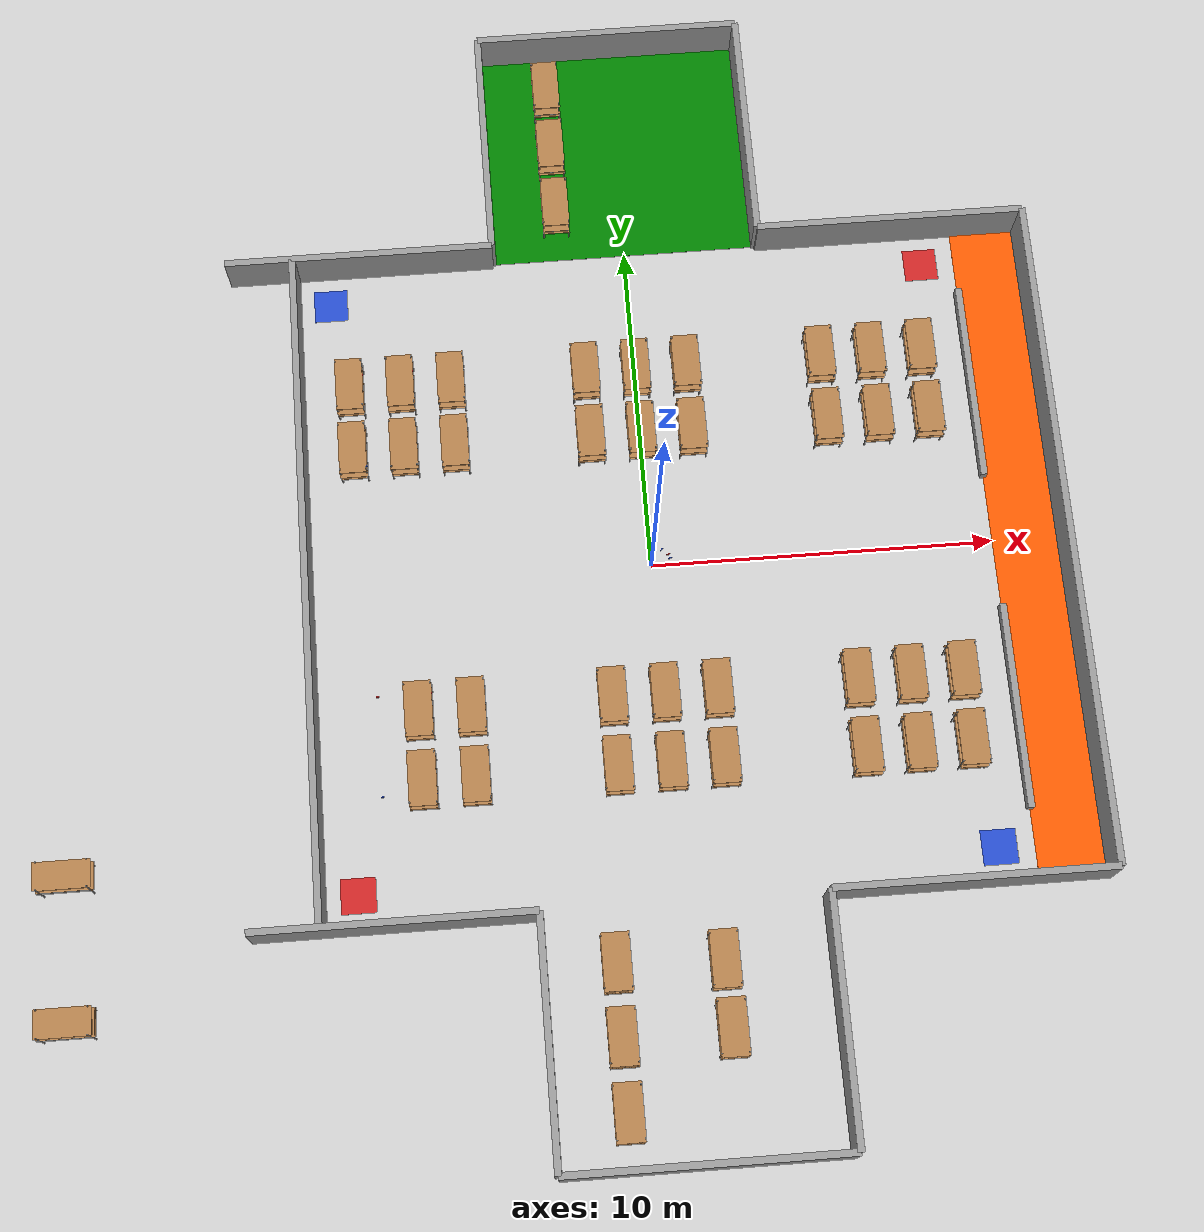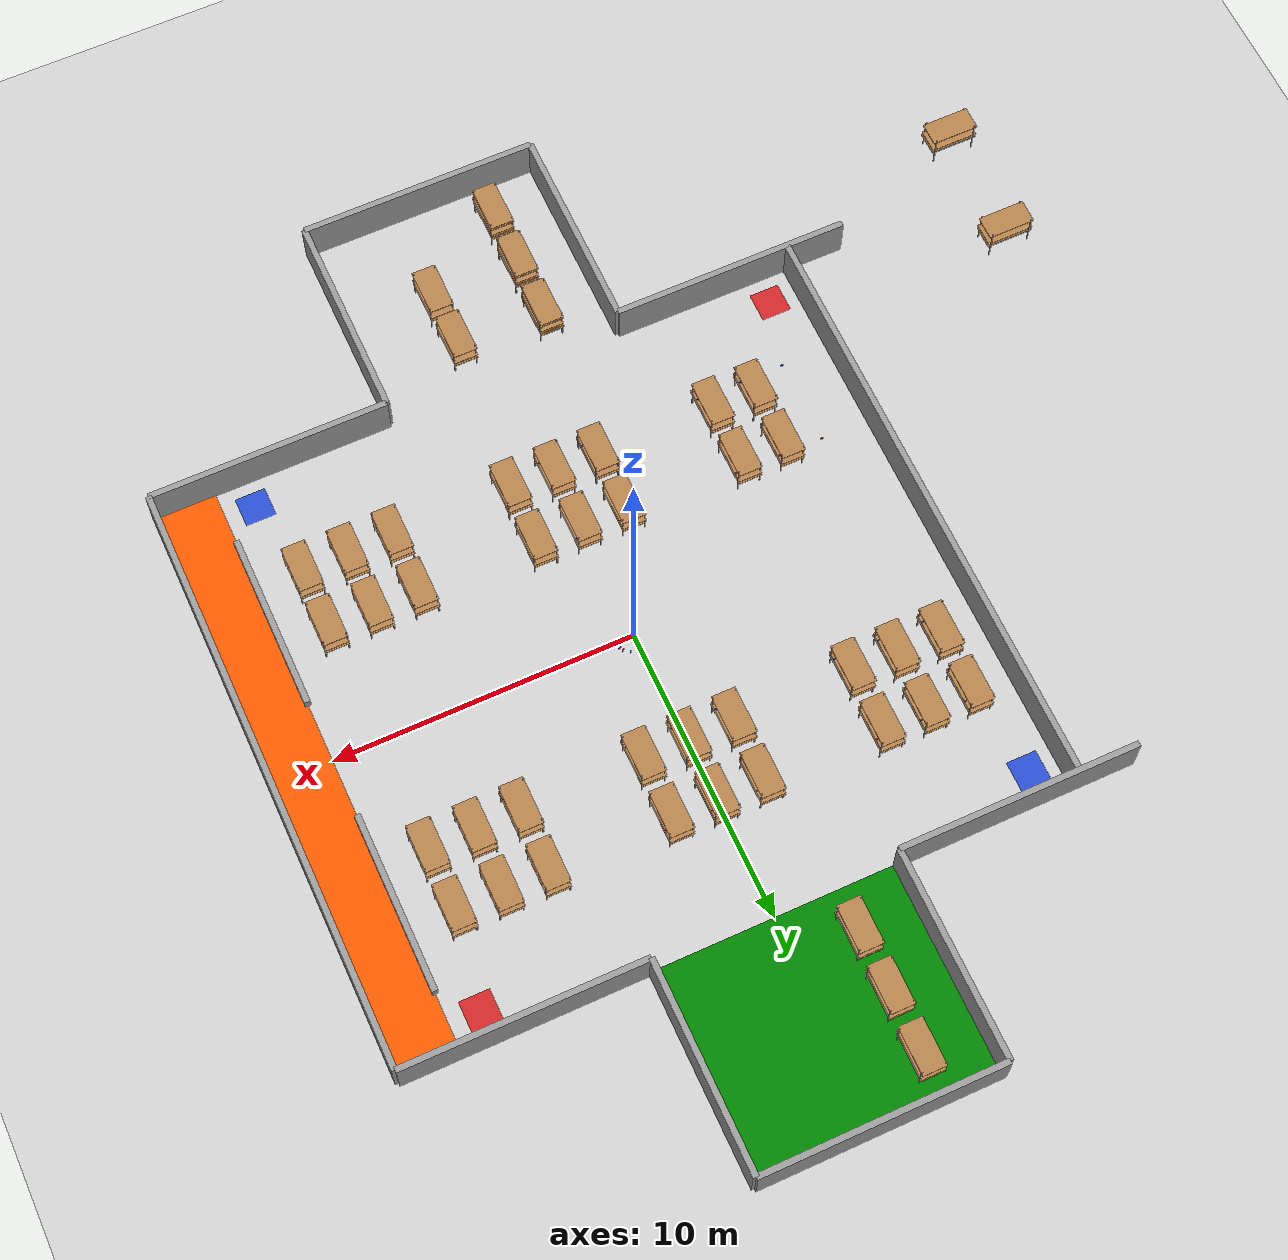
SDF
<sdf version="1.7">
 <world name="warehouse_world">
  <physics type="ode">
   <real_time_update_rate>1000</real_time_update_rate>
   <max_step_size>0.001</max_step_size>
   <real_time_factor>1</real_time_factor>
   <ode>
    <solver>
     <type>quick</type>
     <iters>350</iters>
     <precon_iters>0</precon_iters>
     <sor>1.4</sor>
     <use_dynamic_moi_rescaling>1</use_dynamic_moi_rescaling>
    </solver>
    <constraints>
     <cfm>1e-05</cfm>
     <erp>0.2</erp>
     <contact_max_correcting_vel>100</contact_max_correcting_vel>
     <contact_surface_layer>0.0001</contact_surface_layer>
    </constraints>
   </ode>
  </physics>
  <gravity>0 0 -9.81</gravity>
  <magnetic_field>6e-06 2.3e-05 -4.2e-05</magnetic_field>
  <atmosphere type="adiabatic"/>
  <scene><ambient>0.4 0.4 0.4 1</ambient><background>0.7 0.7 0.7 1</background><shadows>1</shadows></scene>
  <spherical_coordinates>
   <surface_model>EARTH_WGS84</surface_model>
   <latitude_deg>0</latitude_deg>
   <longitude_deg>0</longitude_deg>
   <elevation>0</elevation>
   <heading_deg>0</heading_deg>
  </spherical_coordinates>
  <light name="sun" type="directional">
   <pose>0 0 10 0 -0 0</pose>
   <diffuse>0.8 0.8 0.8 1</diffuse>
   <specular>0.2 0.2 0.2 1</specular>
   <attenuation>
    <range>1000</range>
    <constant>0.9</constant>
    <linear>0.01</linear>
    <quadratic>0.001</quadratic>
   </attenuation>
   <direction>-0.5 0.1 -0.9</direction>
   <spot><inner_angle>0</inner_angle><outer_angle>0</outer_angle><falloff>0</falloff></spot>
  </light>
  <model name="ground_plane">
   <static>1</static>
   <link name="link">
    <collision name="collision">
     <geometry><plane><normal>0 0 1</normal><size>100 100</size></plane></geometry>
     <surface>
      <contact><collide_bitmask>65535</collide_bitmask></contact>
      <friction><ode><mu>100</mu><mu2>50</mu2></ode></friction>
     </surface>
    </collision>
    <visual name="visual">
     <cast_shadows>0</cast_shadows>
     <geometry><plane><normal>0 0 1</normal><size>100 100</size></plane></geometry>
     <material>
      <script><uri>file://media/materials/scripts/gazebo.material</uri><name>Gazebo/Grey</name></script>
     </material>
    </visual>
   </link>
  </model>
  <model name="warehouse_walls">
   <static>1</static>
   <link name="wall1_link">
    <pose>-10 0 0 0 -0 1.57</pose>
    <collision name="collision"><geometry><box><size>20 0.2 2.8</size></box></geometry></collision>
    <visual name="wall1_visual">
     <cast_shadows>0</cast_shadows>
     <geometry><box><size>20 0.2 2.8</size></box></geometry>
     <material>
      <script>
       <uri>model://grey_wall/materials/scripts</uri>
       <uri>model://grey_wall/materials/textures</uri>
       <name>vrc/grey_wall</name>
      </script>
     </material>
    </visual>
   </link>
   <link name="wall2_link2">
    <pose>8 -10 0 0 -0 0</pose>
    <collision name="wall2_collision2"><geometry><box><size>8 0.2 2.8</size></box></geometry></collision>
    <visual name="wall2_visual2">
     <cast_shadows>0</cast_shadows>
     <geometry><box><size>8 0.2 2.8</size></box></geometry>
     <material>
      <script>
       <uri>model://grey_wall/materials/scripts</uri>
       <uri>model://grey_wall/materials/textures</uri>
       <name>vrc/grey_wall</name>
      </script>
     </material>
    </visual>
   </link>
   <link name="wall2_link3">
    <pose>4 -13.5 0 0 -0 1.57</pose>
    <collision name="wall2_collision3"><geometry><box><size>7 0.2 2.8</size></box></geometry></collision>
    <visual name="wall2_visual3">
     <cast_shadows>0</cast_shadows>
     <geometry><box><size>7 0.2 2.8</size></box></geometry>
     <material>
      <script>
       <uri>model://grey_wall/materials/scripts</uri>
       <uri>model://grey_wall/materials/textures</uri>
       <name>vrc/grey_wall</name>
      </script>
     </material>
    </visual>
   </link>
   <link name="wall2_link4">
    <pose>0 -17 0 0 -0 0</pose>
    <collision name="wall2_collision4"><geometry><box><size>8 0.2 2.8</size></box></geometry></collision>
    <visual name="wall2_visual4">
     <cast_shadows>0</cast_shadows>
     <geometry><box><size>8 0.2 2.8</size></box></geometry>
     <material>
      <script>
       <uri>model://grey_wall/materials/scripts</uri>
       <uri>model://grey_wall/materials/textures</uri>
       <name>vrc/grey_wall</name>
      </script>
     </material>
    </visual>
   </link>
   <link name="wall2_link5">
    <pose>-4 -13.5 0 0 -0 1.57</pose>
    <collision name="wall2_collision5"><geometry><box><size>7 0.2 2.8</size></box></geometry></collision>
    <visual name="wall2_visual5">
     <cast_shadows>0</cast_shadows>
     <geometry><box><size>7 0.2 2.8</size></box></geometry>
     <material>
      <script>
       <uri>model://grey_wall/materials/scripts</uri>
       <uri>model://grey_wall/materials/textures</uri>
       <name>vrc/grey_wall</name>
      </script>
     </material>
    </visual>
   </link>
   <link name="wall2_link6">
    <pose>-8 -10 0 0 -0 0</pose>
    <collision name="wall2_collision6"><geometry><box><size>8 0.2 2.8</size></box></geometry></collision>
    <visual name="wall2_visual6">
     <cast_shadows>0</cast_shadows>
     <geometry><box><size>8 0.2 2.8</size></box></geometry>
     <material>
      <script>
       <uri>model://grey_wall/materials/scripts</uri>
       <uri>model://grey_wall/materials/textures</uri>
       <name>vrc/grey_wall</name>
      </script>
     </material>
    </visual>
   </link>
   <link name="output_area">
    <pose>0 13.5 0 0 -0 0</pose>
    <visual name="visual_output_area">
     <cast_shadows>0</cast_shadows>
     <geometry><plane><normal>0 0 1</normal><size>8 7</size></plane></geometry>
     <material>
      <ambient>0 0.5 0 1</ambient>
      <diffuse>0 0.5 0 1</diffuse>
      <specular>0 0 0 1</specular>
      <emissive>0 0 0 0</emissive>
     </material>
    </visual>
   </link>
   <link name="wall3_link2">
    <pose>8 10 0 0 -0 0</pose>
    <collision name="wall3_collision2"><geometry><box><size>8 0.2 2.8</size></box></geometry></collision>
    <visual name="wall3_visual2">
     <cast_shadows>0</cast_shadows>
     <geometry><box><size>8 0.2 2.8</size></box></geometry>
     <material>
      <script>
       <uri>model://grey_wall/materials/scripts</uri>
       <uri>model://grey_wall/materials/textures</uri>
       <name>vrc/grey_wall</name>
      </script>
     </material>
    </visual>
   </link>
   <link name="wall3_link3">
    <pose>4 13.5 0 0 -0 1.57</pose>
    <collision name="wall3_collision3"><geometry><box><size>7 0.2 2.8</size></box></geometry></collision>
    <visual name="wall3_visual3">
     <cast_shadows>0</cast_shadows>
     <geometry><box><size>7 0.2 2.8</size></box></geometry>
     <material>
      <script>
       <uri>model://grey_wall/materials/scripts</uri>
       <uri>model://grey_wall/materials/textures</uri>
       <name>vrc/grey_wall</name>
      </script>
     </material>
    </visual>
   </link>
   <link name="wall3_link4">
    <pose>0 17 0 0 -0 0</pose>
    <collision name="wall3_collision4"><geometry><box><size>8 0.2 2.8</size></box></geometry></collision>
    <visual name="wall3_visual4">
     <cast_shadows>0</cast_shadows>
     <geometry><box><size>8 0.2 2.8</size></box></geometry>
     <material>
      <script>
       <uri>model://grey_wall/materials/scripts</uri>
       <uri>model://grey_wall/materials/textures</uri>
       <name>vrc/grey_wall</name>
      </script>
     </material>
    </visual>
   </link>
   <link name="wall3_link5">
    <pose>-4 13.5 0 0 -0 1.57</pose>
    <collision name="wall3_collision5"><geometry><box><size>7 0.2 2.8</size></box></geometry></collision>
    <visual name="wall3_visual5">
     <cast_shadows>0</cast_shadows>
     <geometry><box><size>7 0.2 2.8</size></box></geometry>
     <material>
      <script>
       <uri>model://grey_wall/materials/scripts</uri>
       <uri>model://grey_wall/materials/textures</uri>
       <name>vrc/grey_wall</name>
      </script>
     </material>
    </visual>
   </link>
   <link name="wall3_link6">
    <pose>-8 10 0 0 -0 0</pose>
    <collision name="wall3_collision6"><geometry><box><size>8 0.2 2.8</size></box></geometry></collision>
    <visual name="wall3_visual6">
     <cast_shadows>0</cast_shadows>
     <geometry><box><size>8 0.2 2.8</size></box></geometry>
     <material>
      <script>
       <uri>model://grey_wall/materials/scripts</uri>
       <uri>model://grey_wall/materials/textures</uri>
       <name>vrc/grey_wall</name>
      </script>
     </material>
    </visual>
   </link>
   <link name="wall4_link">
    <pose>12 0 0 0 -0 1.57</pose>
    <collision name="wall4_collision"><geometry><box><size>20 0.2 2.8</size></box></geometry></collision>
    <visual name="wall4_visual">
     <cast_shadows>0</cast_shadows>
     <geometry><box><size>20 0.2 2.8</size></box></geometry>
     <material>
      <script>
       <uri>model://grey_wall/materials/scripts</uri>
       <uri>model://grey_wall/materials/textures</uri>
       <name>vrc/grey_wall</name>
      </script>
     </material>
    </visual>
   </link>
   <link name="wall5_link1">
    <pose>10 -5 0 0 -0 1.57</pose>
    <collision name="wall5_collision1"><geometry><box><size>6 0.2 0.6</size></box></geometry></collision>
    <visual name="wall5_visual1">
     <cast_shadows>0</cast_shadows>
     <geometry><box><size>6 0.2 0.6</size></box></geometry>
     <material>
      <script>
       <uri>model://grey_wall/materials/scripts</uri>
       <uri>model://grey_wall/materials/textures</uri>
       <name>vrc/grey_wall</name>
      </script>
     </material>
    </visual>
   </link>
   <link name="wall5_link2">
    <pose>10 5 0 0 -0 1.57</pose>
    <collision name="wall5_collision2"><geometry><box><size>6 0.2 0.6</size></box></geometry></collision>
    <visual name="wall5_visual2">
     <cast_shadows>0</cast_shadows>
     <geometry><box><size>6 0.2 0.6</size></box></geometry>
     <material>
      <script>
       <uri>model://grey_wall/materials/scripts</uri>
       <uri>model://grey_wall/materials/textures</uri>
       <name>vrc/grey_wall</name>
      </script>
     </material>
    </visual>
   </link>
   <link name="resting_area">
    <pose>11 0 0 0 -0 1.57</pose>
    <visual name="visual_resting_area">
     <cast_shadows>0</cast_shadows>
     <geometry><plane><normal>0 0 1</normal><size>20 2</size></plane></geometry>
     <material>
      <ambient>1 0.35 0 1</ambient>
      <diffuse>1 0.35 0 1</diffuse>
      <specular>0 0 0 1</specular>
      <emissive>0 0 0 0</emissive>
     </material>
    </visual>
   </link>
  </model>
  <model name="red1">
   <link name="link">
    <inertial>
     <mass>0.1</mass>
     <inertia><ixx>0.16667</ixx><ixy>0</ixy><ixz>0</ixz><iyy>0.16667</iyy><iyz>0</iyz><izz>0.16667</izz></inertia>
    </inertial>
    <visual name="visual">
     <geometry><box><size>0.09433 0.024 0.07</size></box></geometry>
     <material>
      <script><name>Gazebo/Red</name><uri>file://media/materials/scripts/gazebo.material</uri></script>
      <shader type="vertex"><normal_map>__default__</normal_map></shader>
     </material>
    </visual>
    <collision name="collision">
     <max_contacts>50</max_contacts>
     <geometry><box><size>0.09433 0.024 0.07</size></box></geometry>
     <surface>
      <friction>
       <ode><mu>0.998</mu><mu2>0.998</mu2><fdir1>0 0 0</fdir1><slip1>0</slip1><slip2>0</slip2></ode>
      </friction>
      <bounce><restitution_coefficient>0</restitution_coefficient><threshold>100000</threshold></bounce>
      <contact>
       <ode>
        <soft_cfm>0</soft_cfm>
        <soft_erp>0.2</soft_erp>
        <kp>100000</kp>
        <kd>1</kd>
        <max_vel>100</max_vel>
        <min_depth>0.001</min_depth>
       </ode>
      </contact>
     </surface>
    </collision>
   </link>
   <static>0</static>
   <allow_auto_disable>0</allow_auto_disable>
   <pose>0.583331 0.006987 0.033998 0 0 -0.001098</pose>
  </model>
  <model name="red3">
   <link name="link">
    <inertial>
     <mass>0.1</mass>
     <inertia><ixx>0.16667</ixx><ixy>0</ixy><ixz>0</ixz><iyy>0.16667</iyy><iyz>0</iyz><izz>0.16667</izz></inertia>
    </inertial>
    <visual name="visual">
     <geometry><box><size>0.09433 0.024 0.07</size></box></geometry>
     <material>
      <script><name>Gazebo/Red</name><uri>file://media/materials/scripts/gazebo.material</uri></script>
      <shader type="vertex"><normal_map>__default__</normal_map></shader>
     </material>
    </visual>
    <collision name="collision">
     <max_contacts>50</max_contacts>
     <geometry><box><size>0.09433 0.024 0.07</size></box></geometry>
     <surface>
      <friction>
       <ode><mu>0.998</mu><mu2>0.998</mu2><fdir1>0 0 0</fdir1><slip1>0</slip1><slip2>0</slip2></ode>
      </friction>
      <bounce><restitution_coefficient>0</restitution_coefficient><threshold>100000</threshold></bounce>
      <contact>
       <ode>
        <soft_cfm>0</soft_cfm>
        <soft_erp>0.2</soft_erp>
        <kp>100000</kp>
        <kd>1</kd>
        <max_vel>100</max_vel>
        <min_depth>0.001</min_depth>
       </ode>
      </contact>
     </surface>
    </collision>
   </link>
   <static>0</static>
   <allow_auto_disable>0</allow_auto_disable>
   <pose>0.501839 0.314217 0.033998 0 -0 0.475421</pose>
  </model>
  <model name="blue2">
   <link name="link">
    <inertial>
     <mass>0.1</mass>
     <inertia><ixx>0.16667</ixx><ixy>0</ixy><ixz>0</ixz><iyy>0.16667</iyy><iyz>0</iyz><izz>0.16667</izz></inertia>
    </inertial>
    <visual name="visual">
     <geometry><box><size>0.09433 0.024 0.07</size></box></geometry>
     <material>
      <script><name>Gazebo/Blue</name><uri>file://media/materials/scripts/gazebo.material</uri></script>
      <shader type="vertex"><normal_map>__default__</normal_map></shader>
     </material>
    </visual>
    <collision name="collision">
     <max_contacts>50</max_contacts>
     <geometry><box><size>0.09433 0.024 0.07</size></box></geometry>
     <surface>
      <friction>
       <ode><mu>0.998</mu><mu2>0.998</mu2><fdir1>0 0 0</fdir1><slip1>0</slip1><slip2>0</slip2></ode>
      </friction>
      <bounce><restitution_coefficient>0</restitution_coefficient><threshold>100000</threshold></bounce>
      <contact>
       <ode>
        <soft_cfm>0</soft_cfm>
        <soft_erp>0.2</soft_erp>
        <kp>100000</kp>
        <kd>1</kd>
        <max_vel>100</max_vel>
        <min_depth>0.001</min_depth>
       </ode>
      </contact>
     </surface>
    </collision>
   </link>
   <static>0</static>
   <allow_auto_disable>0</allow_auto_disable>
   <pose>0.551327 0.194529 0.033998 0 -0 0.318925</pose>
  </model>
  <model name="blue4">
   <link name="link">
    <inertial>
     <mass>0.1</mass>
     <inertia><ixx>0.16667</ixx><ixy>0</ixy><ixz>0</ixz><iyy>0.16667</iyy><iyz>0</iyz><izz>0.16667</izz></inertia>
    </inertial>
    <visual name="visual">
     <geometry><box><size>0.09433 0.024 0.07</size></box></geometry>
     <material>
      <script><name>Gazebo/Blue</name><uri>file://media/materials/scripts/gazebo.material</uri></script>
      <shader type="vertex"><normal_map>__default__</normal_map></shader>
     </material>
    </visual>
    <collision name="collision">
     <max_contacts>50</max_contacts>
     <geometry><box><size>0.09433 0.024 0.07</size></box></geometry>
     <surface>
      <friction>
       <ode><mu>0.998</mu><mu2>0.998</mu2><fdir1>0 0 0</fdir1><slip1>0</slip1><slip2>0</slip2></ode>
      </friction>
      <bounce><restitution_coefficient>0</restitution_coefficient><threshold>100000</threshold></bounce>
      <contact>
       <ode>
        <soft_cfm>0</soft_cfm>
        <soft_erp>0.2</soft_erp>
        <kp>100000</kp>
        <kd>1</kd>
        <max_vel>100</max_vel>
        <min_depth>0.001</min_depth>
       </ode>
      </contact>
     </surface>
    </collision>
   </link>
   <static>0</static>
   <allow_auto_disable>0</allow_auto_disable>
   <pose>0.326426 0.475073 0.033998 0 -0 0.9453</pose>
  </model>
  <model name="destination_1">
   <link name="link">
    <inertial>
     <mass>0.1</mass>
     <inertia>
      <ixx>0.166667</ixx>
      <ixy>0</ixy>
      <ixz>0</ixz>
      <iyy>0.166667</iyy>
      <iyz>0</iyz>
      <izz>0.166667</izz>
     </inertia>
    </inertial>
    <visual name="visual">
     <geometry><box><size>1 1 0.001</size></box></geometry>
     <material>
      <script><name>Gazebo/Blue</name><uri>file://media/materials/scripts/gazebo.material</uri></script>
      <shader type="vertex"><normal_map>__default__</normal_map></shader>
     </material>
    </visual>
    <collision name="collision">
     <geometry><box><size>1 1 0</size></box></geometry>
     <surface>
      <friction>
       <ode><mu>0.998</mu><mu2>0.998</mu2><fdir1>0 0 0</fdir1><slip1>0</slip1><slip2>0</slip2></ode>
      </friction>
      <bounce><restitution_coefficient>0</restitution_coefficient><threshold>100000</threshold></bounce>
      <contact>
       <ode>
        <soft_cfm>0</soft_cfm>
        <soft_erp>0.2</soft_erp>
        <kp>100000</kp>
        <kd>1</kd>
        <max_vel>100</max_vel>
        <min_depth>0.001</min_depth>
       </ode>
      </contact>
     </surface>
    </collision>
   </link>
   <static>1</static>
   <pose>-9 9 0 0 -0 0</pose>
  </model>
  <model name="destination_2">
   <link name="link">
    <inertial>
     <mass>0.1</mass>
     <inertia>
      <ixx>0.166667</ixx>
      <ixy>0</ixy>
      <ixz>0</ixz>
      <iyy>0.166667</iyy>
      <iyz>0</iyz>
      <izz>0.166667</izz>
     </inertia>
    </inertial>
    <visual name="visual">
     <geometry><box><size>1 1 0.001</size></box></geometry>
     <material>
      <script><name>Gazebo/Red</name><uri>file://media/materials/scripts/gazebo.material</uri></script>
      <shader type="vertex"><normal_map>__default__</normal_map></shader>
     </material>
    </visual>
    <collision name="collision">
     <geometry><box><size>1 1 0</size></box></geometry>
     <surface>
      <friction>
       <ode><mu>0.998</mu><mu2>0.998</mu2><fdir1>0 0 0</fdir1><slip1>0</slip1><slip2>0</slip2></ode>
      </friction>
      <bounce><restitution_coefficient>0</restitution_coefficient><threshold>100000</threshold></bounce>
      <contact>
       <ode>
        <soft_cfm>0</soft_cfm>
        <soft_erp>0.2</soft_erp>
        <kp>100000</kp>
        <kd>1</kd>
        <max_vel>100</max_vel>
        <min_depth>0.001</min_depth>
       </ode>
      </contact>
     </surface>
    </collision>
   </link>
   <static>1</static>
   <pose>9 9 0 0 -0 0</pose>
  </model>
  <model name="destination_3">
   <link name="link">
    <inertial>
     <mass>0.1</mass>
     <inertia>
      <ixx>0.166667</ixx>
      <ixy>0</ixy>
      <ixz>0</ixz>
      <iyy>0.166667</iyy>
      <iyz>0</iyz>
      <izz>0.166667</izz>
     </inertia>
    </inertial>
    <visual name="visual">
     <geometry><box><size>1 1 0.001</size></box></geometry>
     <material>
      <script><name>Gazebo/Blue</name><uri>file://media/materials/scripts/gazebo.material</uri></script>
      <shader type="vertex"><normal_map>__default__</normal_map></shader>
     </material>
    </visual>
    <collision name="collision">
     <geometry><box><size>1 1 0</size></box></geometry>
     <surface>
      <friction>
       <ode><mu>0.998</mu><mu2>0.998</mu2><fdir1>0 0 0</fdir1><slip1>0</slip1><slip2>0</slip2></ode>
      </friction>
      <bounce><restitution_coefficient>0</restitution_coefficient><threshold>100000</threshold></bounce>
      <contact>
       <ode>
        <soft_cfm>0</soft_cfm>
        <soft_erp>0.2</soft_erp>
        <kp>100000</kp>
        <kd>1</kd>
        <max_vel>100</max_vel>
        <min_depth>0.001</min_depth>
       </ode>
      </contact>
     </surface>
    </collision>
   </link>
   <static>1</static>
   <pose>9 -9 0 0 -0 0</pose>
  </model>
  <model name="destination_4">
   <link name="link">
    <inertial>
     <mass>0.1</mass>
     <inertia>
      <ixx>0.166667</ixx>
      <ixy>0</ixy>
      <ixz>0</ixz>
      <iyy>0.166667</iyy>
      <iyz>0</iyz>
      <izz>0.166667</izz>
     </inertia>
    </inertial>
    <visual name="visual">
     <geometry><box><size>1 1 0.001</size></box></geometry>
     <material>
      <script><name>Gazebo/Red</name><uri>file://media/materials/scripts/gazebo.material</uri></script>
      <shader type="vertex"><normal_map>__default__</normal_map></shader>
     </material>
    </visual>
    <collision name="collision">
     <geometry><box><size>1 1 0</size></box></geometry>
     <surface>
      <friction>
       <ode><mu>0.998</mu><mu2>0.998</mu2><fdir1>0 0 0</fdir1><slip1>0</slip1><slip2>0</slip2></ode>
      </friction>
      <bounce><restitution_coefficient>0</restitution_coefficient><threshold>100000</threshold></bounce>
      <contact>
       <ode>
        <soft_cfm>0</soft_cfm>
        <soft_erp>0.2</soft_erp>
        <kp>100000</kp>
        <kd>1</kd>
        <max_vel>100</max_vel>
        <min_depth>0.001</min_depth>
       </ode>
      </contact>
     </surface>
    </collision>
   </link>
   <static>1</static>
   <pose>-9 -9 0 0 -0 0</pose>
  </model>
  <model name="pallet_set6_clone_0">
   <link name="warehouse_pallet::warehouse_pallet::link">
    <pose>0 0 0 0 -0 1.57</pose>
    <inertial>
     <inertia>
      <ixx>0.0267042</ixx>
      <ixy>0</ixy>
      <ixz>0</ixz>
      <iyy>0.0937875</iyy>
      <iyz>0</iyz>
      <izz>0.120417</izz>
     </inertia>
     <mass>0.1</mass>
    </inertial>
    <visual name="back_left_leg">
     <pose>-0.7 0.38 0.5 0 -0 0</pose>
     <geometry><cylinder><radius>0.02</radius><length>1.2</length></cylinder></geometry>
     <material>
      <script><uri>file://media/materials/scripts/gazebo.material</uri><name>Gazebo/Grey</name></script>
      <shader type="pixel"><normal_map>__default__</normal_map></shader>
      <ambient>0.3 0.3 0.3 1</ambient>
      <diffuse>0.7 0.7 0.7 1</diffuse>
      <specular>0.01 0.01 0.01 1</specular>
      <emissive>0 0 0 1</emissive>
     </material>
    </visual>
    <visual name="visual1">
     <pose>0 0 0.45 0 -0 0</pose>
     <geometry><box><size>1.6 0.8 0.03</size></box></geometry>
     <material>
      <script><uri>file://media/materials/scripts/gazebo.material</uri><name>Gazebo/Wood</name></script>
      <shader type="pixel"><normal_map>__default__</normal_map></shader>
      <ambient>1 1 1 1</ambient>
      <diffuse>1 1 1 1</diffuse>
      <specular>0.2 0.2 0.2 1</specular>
      <emissive>0 0 0 1</emissive>
     </material>
    </visual>
    <visual name="holding2_visual">
     <pose>0 -0.39 0.45 0 -0 0</pose>
     <geometry><box><size>1.6 0.02 0.05</size></box></geometry>
     <material>
      <script><uri>file://media/materials/scripts/gazebo.material</uri><name>Gazebo/Grey</name></script>
      <shader type="pixel"><normal_map>__default__</normal_map></shader>
      <ambient>0.3 0.3 0.3 1</ambient>
      <diffuse>0.7 0.7 0.7 1</diffuse>
      <specular>0.01 0.01 0.01 1</specular>
      <emissive>0 0 0 1</emissive>
     </material>
    </visual>
    <visual name="holding3_visual">
     <pose>0.735 0 0.45 0 -0 1.57</pose>
     <geometry><box><size>0.8 0.02 0.05</size></box></geometry>
     <material>
      <script><uri>file://media/materials/scripts/gazebo.material</uri><name>Gazebo/Grey</name></script>
      <shader type="pixel"><normal_map>__default__</normal_map></shader>
      <ambient>0.3 0.3 0.3 1</ambient>
      <diffuse>0.7 0.7 0.7 1</diffuse>
      <specular>0.01 0.01 0.01 1</specular>
      <emissive>0 0 0 1</emissive>
     </material>
    </visual>
    <visual name="holding4_visual">
     <pose>-0.735 0 0.45 0 -0 1.57</pose>
     <geometry><box><size>0.8 0.02 0.05</size></box></geometry>
     <material>
      <script><uri>file://media/materials/scripts/gazebo.material</uri><name>Gazebo/Grey</name></script>
      <shader type="pixel"><normal_map>__default__</normal_map></shader>
      <ambient>0.3 0.3 0.3 1</ambient>
      <diffuse>0.7 0.7 0.7 1</diffuse>
      <specular>0.01 0.01 0.01 1</specular>
      <emissive>0 0 0 1</emissive>
     </material>
    </visual>
    <visual name="visual2">
     <pose>0 0 0.6 0 -0 0</pose>
     <geometry><box><size>1.6 0.8 0.03</size></box></geometry>
     <material>
      <script><uri>file://media/materials/scripts/gazebo.material</uri><name>Gazebo/Wood</name></script>
      <shader type="pixel"><normal_map>__default__</normal_map></shader>
      <ambient>1 1 1 1</ambient>
      <diffuse>1 1 1 1</diffuse>
      <specular>0.2 0.2 0.2 1</specular>
      <emissive>0 0 0 1</emissive>
     </material>
    </visual>
    <visual name="visual3">
     <pose>0 0 1 0 -0 0</pose>
     <geometry><box><size>1.6 0.8 0.03</size></box></geometry>
     <material>
      <script><uri>file://media/materials/scripts/gazebo.material</uri><name>Gazebo/Wood</name></script>
      <shader type="pixel"><normal_map>__default__</normal_map></shader>
      <ambient>1 1 1 1</ambient>
      <diffuse>1 1 1 1</diffuse>
      <specular>0.2 0.2 0.2 1</specular>
      <emissive>0 0 0 1</emissive>
     </material>
    </visual>
    <visual name="holding1_visual">
     <pose>0 0.39 0.45 0 -0 0</pose>
     <geometry><box><size>1.6 0.02 0.05</size></box></geometry>
     <material>
      <script><uri>file://media/materials/scripts/gazebo.material</uri><name>Gazebo/Grey</name></script>
      <shader type="pixel"><normal_map>__default__</normal_map></shader>
      <ambient>0.3 0.3 0.3 1</ambient>
      <diffuse>0.7 0.7 0.7 1</diffuse>
      <specular>0.01 0.01 0.01 1</specular>
      <emissive>0 0 0 1</emissive>
     </material>
    </visual>
    <visual name="front_left_leg">
     <pose>0.7 0.38 0.5 0 -0 0</pose>
     <geometry><cylinder><radius>0.02</radius><length>1.2</length></cylinder></geometry>
     <material>
      <script><uri>file://media/materials/scripts/gazebo.material</uri><name>Gazebo/Grey</name></script>
      <shader type="pixel"><normal_map>__default__</normal_map></shader>
      <ambient>0.3 0.3 0.3 1</ambient>
      <diffuse>0.7 0.7 0.7 1</diffuse>
      <specular>0.01 0.01 0.01 1</specular>
      <emissive>0 0 0 1</emissive>
     </material>
    </visual>
    <visual name="front_right_leg">
     <pose>0.7 -0.38 0.5 0 -0 0</pose>
     <geometry><cylinder><radius>0.02</radius><length>1.2</length></cylinder></geometry>
     <material>
      <script><uri>file://media/materials/scripts/gazebo.material</uri><name>Gazebo/Grey</name></script>
      <shader type="pixel"><normal_map>__default__</normal_map></shader>
      <ambient>0.3 0.3 0.3 1</ambient>
      <diffuse>0.7 0.7 0.7 1</diffuse>
      <specular>0.01 0.01 0.01 1</specular>
      <emissive>0 0 0 1</emissive>
     </material>
    </visual>
    <visual name="back_right_leg">
     <pose>-0.7 -0.38 0.5 0 -0 0</pose>
     <geometry><cylinder><radius>0.02</radius><length>1.2</length></cylinder></geometry>
     <material>
      <script><uri>file://media/materials/scripts/gazebo.material</uri><name>Gazebo/Grey</name></script>
      <shader type="pixel"><normal_map>__default__</normal_map></shader>
      <ambient>0.3 0.3 0.3 1</ambient>
      <diffuse>0.7 0.7 0.7 1</diffuse>
      <specular>0.01 0.01 0.01 1</specular>
      <emissive>0 0 0 1</emissive>
     </material>
    </visual>
    <collision name="surface1">
     <pose>0 0 0.45 0 -0 0</pose>
     <geometry><box><size>1.6 0.8 0.03</size></box></geometry>
     <surface>
      <friction>
       <ode><mu>20</mu><mu2>20</mu2><fdir1>0 0 0</fdir1><slip1>0</slip1><slip2>0</slip2></ode>
       <torsional>
        <coefficient>1</coefficient>
        <patch_radius>0</patch_radius>
        <surface_radius>0</surface_radius>
        <use_patch_radius>1</use_patch_radius>
        <ode><slip>0</slip></ode>
       </torsional>
      </friction>
      <bounce><restitution_coefficient>0</restitution_coefficient><threshold>1e+06</threshold></bounce>
      <contact>
       <collide_without_contact>0</collide_without_contact>
       <collide_without_contact_bitmask>1</collide_without_contact_bitmask>
       <collide_bitmask>1</collide_bitmask>
       <ode>
        <soft_cfm>0</soft_cfm>
        <soft_erp>0.2</soft_erp>
        <kp>1e+13</kp>
        <kd>1</kd>
        <max_vel>0.01</max_vel>
        <min_depth>0</min_depth>
       </ode>
       <bullet>
        <split_impulse>1</split_impulse>
        <split_impulse_penetration_threshold>-0.01</split_impulse_penetration_threshold>
        <soft_cfm>0</soft_cfm>
        <soft_erp>0.2</soft_erp>
        <kp>1e+13</kp>
        <kd>1</kd>
       </bullet>
      </contact>
     </surface>
    </collision>
    <collision name="holding1_collision">
     <pose>0 0.39 0.45 0 -0 0</pose>
     <geometry><box><size>1.6 0.02 0.05</size></box></geometry>
     <surface>
      <friction>
       <ode><mu>1e+09</mu><mu2>1e+09</mu2><fdir1>0 0 0</fdir1><slip1>0</slip1><slip2>0</slip2></ode>
       <torsional>
        <coefficient>1</coefficient>
        <patch_radius>0</patch_radius>
        <surface_radius>0</surface_radius>
        <use_patch_radius>1</use_patch_radius>
        <ode><slip>0</slip></ode>
       </torsional>
      </friction>
      <bounce><restitution_coefficient>0</restitution_coefficient><threshold>1e+06</threshold></bounce>
      <contact>
       <collide_without_contact>0</collide_without_contact>
       <collide_without_contact_bitmask>1</collide_without_contact_bitmask>
       <collide_bitmask>1</collide_bitmask>
       <ode>
        <soft_cfm>0</soft_cfm>
        <soft_erp>0.2</soft_erp>
        <kp>1e+13</kp>
        <kd>1</kd>
        <max_vel>0.01</max_vel>
        <min_depth>0</min_depth>
       </ode>
       <bullet>
        <split_impulse>1</split_impulse>
        <split_impulse_penetration_threshold>-0.01</split_impulse_penetration_threshold>
        <soft_cfm>0</soft_cfm>
        <soft_erp>0.2</soft_erp>
        <kp>1e+13</kp>
        <kd>1</kd>
       </bullet>
      </contact>
     </surface>
    </collision>
    <collision name="holding2_collision">
     <pose>0 -0.39 0.45 0 -0 0</pose>
     <geometry><box><size>1.6 0.02 0.05</size></box></geometry>
     <surface>
      <friction>
       <ode><mu>1e+09</mu><mu2>1e+09</mu2><fdir1>0 0 0</fdir1><slip1>0</slip1><slip2>0</slip2></ode>
       <torsional>
        <coefficient>1</coefficient>
        <patch_radius>0</patch_radius>
        <surface_radius>0</surface_radius>
        <use_patch_radius>1</use_patch_radius>
        <ode><slip>0</slip></ode>
       </torsional>
      </friction>
      <bounce><restitution_coefficient>0</restitution_coefficient><threshold>1e+06</threshold></bounce>
      <contact>
       <collide_without_contact>0</collide_without_contact>
       <collide_without_contact_bitmask>1</collide_without_contact_bitmask>
       <collide_bitmask>1</collide_bitmask>
       <ode>
        <soft_cfm>0</soft_cfm>
        <soft_erp>0.2</soft_erp>
        <kp>1e+13</kp>
        <kd>1</kd>
        <max_vel>0.01</max_vel>
        <min_depth>0</min_depth>
       </ode>
       <bullet>
        <split_impulse>1</split_impulse>
        <split_impulse_penetration_threshold>-0.01</split_impulse_penetration_threshold>
        <soft_cfm>0</soft_cfm>
        <soft_erp>0.2</soft_erp>
        <kp>1e+13</kp>
        <kd>1</kd>
       </bullet>
      </contact>
     </surface>
    </collision>
    <collision name="holding3_collision">
     <pose>0.735 0 0.45 0 -0 1.57</pose>
     <geometry><box><size>0.8 0.02 0.05</size></box></geometry>
     <surface>
      <friction>
       <ode><mu>1e+09</mu><mu2>1e+09</mu2><fdir1>0 0 0</fdir1><slip1>0</slip1><slip2>0</slip2></ode>
       <torsional>
        <coefficient>1</coefficient>
        <patch_radius>0</patch_radius>
        <surface_radius>0</surface_radius>
        <use_patch_radius>1</use_patch_radius>
        <ode><slip>0</slip></ode>
       </torsional>
      </friction>
      <bounce><restitution_coefficient>0</restitution_coefficient><threshold>1e+06</threshold></bounce>
      <contact>
       <collide_without_contact>0</collide_without_contact>
       <collide_without_contact_bitmask>1</collide_without_contact_bitmask>
       <collide_bitmask>1</collide_bitmask>
       <ode>
        <soft_cfm>0</soft_cfm>
        <soft_erp>0.2</soft_erp>
        <kp>1e+13</kp>
        <kd>1</kd>
        <max_vel>0.01</max_vel>
        <min_depth>0</min_depth>
       </ode>
       <bullet>
        <split_impulse>1</split_impulse>
        <split_impulse_penetration_threshold>-0.01</split_impulse_penetration_threshold>
        <soft_cfm>0</soft_cfm>
        <soft_erp>0.2</soft_erp>
        <kp>1e+13</kp>
        <kd>1</kd>
       </bullet>
      </contact>
     </surface>
    </collision>
    <collision name="holding4_collision">
     <pose>-0.735 0 0.45 0 -0 1.57</pose>
     <geometry><box><size>0.8 0.02 0.05</size></box></geometry>
     <surface>
      <friction>
       <ode><mu>1e+09</mu><mu2>1e+09</mu2><fdir1>0 0 0</fdir1><slip1>0</slip1><slip2>0</slip2></ode>
       <torsional>
        <coefficient>1</coefficient>
        <patch_radius>0</patch_radius>
        <surface_radius>0</surface_radius>
        <use_patch_radius>1</use_patch_radius>
        <ode><slip>0</slip></ode>
       </torsional>
      </friction>
      <bounce><restitution_coefficient>0</restitution_coefficient><threshold>1e+06</threshold></bounce>
      <contact>
       <collide_without_contact>0</collide_without_contact>
       <collide_without_contact_bitmask>1</collide_without_contact_bitmask>
       <collide_bitmask>1</collide_bitmask>
       <ode>
        <soft_cfm>0</soft_cfm>
        <soft_erp>0.2</soft_erp>
        <kp>1e+13</kp>
        <kd>1</kd>
        <max_vel>0.01</max_vel>
        <min_depth>0</min_depth>
       </ode>
       <bullet>
        <split_impulse>1</split_impulse>
        <split_impulse_penetration_threshold>-0.01</split_impulse_penetration_threshold>
        <soft_cfm>0</soft_cfm>
        <soft_erp>0.2</soft_erp>
        <kp>1e+13</kp>
        <kd>1</kd>
       </bullet>
      </contact>
     </surface>
    </collision>
    <collision name="surface3">
     <pose>0 0 1 0 -0 0</pose>
     <geometry><box><size>1.6 0.8 0.03</size></box></geometry>
     <surface>
      <friction>
       <ode><mu>2.5</mu><mu2>2.5</mu2><fdir1>0 0 0</fdir1><slip1>0</slip1><slip2>0</slip2></ode>
       <torsional>
        <coefficient>1</coefficient>
        <patch_radius>0</patch_radius>
        <surface_radius>0</surface_radius>
        <use_patch_radius>1</use_patch_radius>
        <ode><slip>0</slip></ode>
       </torsional>
      </friction>
      <bounce><restitution_coefficient>0</restitution_coefficient><threshold>1e+06</threshold></bounce>
      <contact>
       <collide_without_contact>0</collide_without_contact>
       <collide_without_contact_bitmask>1</collide_without_contact_bitmask>
       <collide_bitmask>1</collide_bitmask>
       <ode>
        <soft_cfm>0</soft_cfm>
        <soft_erp>0.2</soft_erp>
        <kp>1e+13</kp>
        <kd>1</kd>
        <max_vel>0.01</max_vel>
        <min_depth>0</min_depth>
       </ode>
       <bullet>
        <split_impulse>1</split_impulse>
        <split_impulse_penetration_threshold>-0.01</split_impulse_penetration_threshold>
        <soft_cfm>0</soft_cfm>
        <soft_erp>0.2</soft_erp>
        <kp>1e+13</kp>
        <kd>1</kd>
       </bullet>
      </contact>
     </surface>
    </collision>
    <collision name="surface2">
     <pose>0 0 0.6 0 -0 0</pose>
     <geometry><box><size>1.6 0.8 0.03</size></box></geometry>
     <surface>
      <friction>
       <ode><mu>2.5</mu><mu2>2.5</mu2><fdir1>0 0 0</fdir1><slip1>0</slip1><slip2>0</slip2></ode>
       <torsional>
        <coefficient>1</coefficient>
        <patch_radius>0</patch_radius>
        <surface_radius>0</surface_radius>
        <use_patch_radius>1</use_patch_radius>
        <ode><slip>0</slip></ode>
       </torsional>
      </friction>
      <bounce><restitution_coefficient>0</restitution_coefficient><threshold>1e+06</threshold></bounce>
      <contact>
       <collide_without_contact>0</collide_without_contact>
       <collide_without_contact_bitmask>1</collide_without_contact_bitmask>
       <collide_bitmask>1</collide_bitmask>
       <ode>
        <soft_cfm>0</soft_cfm>
        <soft_erp>0.2</soft_erp>
        <kp>1e+13</kp>
        <kd>1</kd>
        <max_vel>0.01</max_vel>
        <min_depth>0</min_depth>
       </ode>
       <bullet>
        <split_impulse>1</split_impulse>
        <split_impulse_penetration_threshold>-0.01</split_impulse_penetration_threshold>
        <soft_cfm>0</soft_cfm>
        <soft_erp>0.2</soft_erp>
        <kp>1e+13</kp>
        <kd>1</kd>
       </bullet>
      </contact>
     </surface>
    </collision>
    <collision name="front_right_leg">
     <pose>0.7 -0.38 0.5 0 -0 0</pose>
     <geometry><cylinder><radius>0.02</radius><length>1</length></cylinder></geometry>
     <surface>
      <friction>
       <ode><mu>0.1</mu><mu2>0.1</mu2><fdir1>0 0 0</fdir1><slip1>0</slip1><slip2>0</slip2></ode>
       <torsional>
        <coefficient>1</coefficient>
        <patch_radius>0</patch_radius>
        <surface_radius>0</surface_radius>
        <use_patch_radius>1</use_patch_radius>
        <ode><slip>0</slip></ode>
       </torsional>
      </friction>
      <bounce><restitution_coefficient>0</restitution_coefficient><threshold>1e+06</threshold></bounce>
      <contact>
       <collide_without_contact>0</collide_without_contact>
       <collide_without_contact_bitmask>1</collide_without_contact_bitmask>
       <collide_bitmask>1</collide_bitmask>
       <ode>
        <soft_cfm>0</soft_cfm>
        <soft_erp>0.2</soft_erp>
        <kp>1e+13</kp>
        <kd>1</kd>
        <max_vel>0.01</max_vel>
        <min_depth>0</min_depth>
       </ode>
       <bullet>
        <split_impulse>1</split_impulse>
        <split_impulse_penetration_threshold>-0.01</split_impulse_penetration_threshold>
        <soft_cfm>0</soft_cfm>
        <soft_erp>0.2</soft_erp>
        <kp>1e+13</kp>
        <kd>1</kd>
       </bullet>
      </contact>
     </surface>
    </collision>
    <collision name="back_right_leg">
     <pose>-0.7 -0.38 0.5 0 -0 0</pose>
     <geometry><cylinder><radius>0.02</radius><length>1.2</length></cylinder></geometry>
     <surface>
      <friction>
       <ode><mu>0.1</mu><mu2>0.1</mu2><fdir1>0 0 0</fdir1><slip1>0</slip1><slip2>0</slip2></ode>
       <torsional>
        <coefficient>1</coefficient>
        <patch_radius>0</patch_radius>
        <surface_radius>0</surface_radius>
        <use_patch_radius>1</use_patch_radius>
        <ode><slip>0</slip></ode>
       </torsional>
      </friction>
      <bounce><restitution_coefficient>0</restitution_coefficient><threshold>1e+06</threshold></bounce>
      <contact>
       <collide_without_contact>0</collide_without_contact>
       <collide_without_contact_bitmask>1</collide_without_contact_bitmask>
       <collide_bitmask>1</collide_bitmask>
       <ode>
        <soft_cfm>0</soft_cfm>
        <soft_erp>0.2</soft_erp>
        <kp>1e+13</kp>
        <kd>1</kd>
        <max_vel>0.01</max_vel>
        <min_depth>0</min_depth>
       </ode>
       <bullet>
        <split_impulse>1</split_impulse>
        <split_impulse_penetration_threshold>-0.01</split_impulse_penetration_threshold>
        <soft_cfm>0</soft_cfm>
        <soft_erp>0.2</soft_erp>
        <kp>1e+13</kp>
        <kd>1</kd>
       </bullet>
      </contact>
     </surface>
    </collision>
    <collision name="front_left_leg">
     <pose>0.7 0.38 0.5 0 -0 0</pose>
     <geometry><cylinder><radius>0.02</radius><length>1.2</length></cylinder></geometry>
     <surface>
      <friction>
       <ode><mu>0.1</mu><mu2>0.1</mu2><fdir1>0 0 0</fdir1><slip1>0</slip1><slip2>0</slip2></ode>
       <torsional>
        <coefficient>1</coefficient>
        <patch_radius>0</patch_radius>
        <surface_radius>0</surface_radius>
        <use_patch_radius>1</use_patch_radius>
        <ode><slip>0</slip></ode>
       </torsional>
      </friction>
      <bounce><restitution_coefficient>0</restitution_coefficient><threshold>1e+06</threshold></bounce>
      <contact>
       <collide_without_contact>0</collide_without_contact>
       <collide_without_contact_bitmask>1</collide_without_contact_bitmask>
       <collide_bitmask>1</collide_bitmask>
       <ode>
        <soft_cfm>0</soft_cfm>
        <soft_erp>0.2</soft_erp>
        <kp>1e+13</kp>
        <kd>1</kd>
        <max_vel>0.01</max_vel>
        <min_depth>0</min_depth>
       </ode>
       <bullet>
        <split_impulse>1</split_impulse>
        <split_impulse_penetration_threshold>-0.01</split_impulse_penetration_threshold>
        <soft_cfm>0</soft_cfm>
        <soft_erp>0.2</soft_erp>
        <kp>1e+13</kp>
        <kd>1</kd>
       </bullet>
      </contact>
     </surface>
    </collision>
    <collision name="back_left_leg">
     <pose>-0.7 0.38 0.5 0 -0 0</pose>
     <geometry><cylinder><radius>0.02</radius><length>1.2</length></cylinder></geometry>
     <surface>
      <friction>
       <ode><mu>0.1</mu><mu2>0.1</mu2><fdir1>0 0 0</fdir1><slip1>0</slip1><slip2>0</slip2></ode>
       <torsional>
        <coefficient>1</coefficient>
        <patch_radius>0</patch_radius>
        <surface_radius>0</surface_radius>
        <use_patch_radius>1</use_patch_radius>
        <ode><slip>0</slip></ode>
       </torsional>
      </friction>
      <bounce><restitution_coefficient>0</restitution_coefficient><threshold>1e+06</threshold></bounce>
      <contact>
       <collide_without_contact>0</collide_without_contact>
       <collide_without_contact_bitmask>1</collide_without_contact_bitmask>
       <collide_bitmask>1</collide_bitmask>
       <ode>
        <soft_cfm>0</soft_cfm>
        <soft_erp>0.2</soft_erp>
        <kp>1e+13</kp>
        <kd>1</kd>
        <max_vel>0.01</max_vel>
        <min_depth>0</min_depth>
       </ode>
       <bullet>
        <split_impulse>1</split_impulse>
        <split_impulse_penetration_threshold>-0.01</split_impulse_penetration_threshold>
        <soft_cfm>0</soft_cfm>
        <soft_erp>0.2</soft_erp>
        <kp>1e+13</kp>
        <kd>1</kd>
       </bullet>
      </contact>
     </surface>
    </collision>
   </link>
   <static>1</static>
   <pose>-1.99997 -15.5 0.099305 -0.000174 0.000322 -0</pose>
  </model>
  <model name="pallet_set0_clone_1_0">
   <link name="warehouse_pallet::warehouse_pallet::link">
    <pose>0 0 0 0 -0 1.57</pose>
    <inertial>
     <inertia>
      <ixx>0.0267042</ixx>
      <ixy>0</ixy>
      <ixz>0</ixz>
      <iyy>0.0937875</iyy>
      <iyz>0</iyz>
      <izz>0.120417</izz>
     </inertia>
     <mass>0.1</mass>
    </inertial>
    <visual name="back_right_leg">
     <pose>-0.7 -0.38 0.5 0 -0 0</pose>
     <geometry><cylinder><radius>0.02</radius><length>1.2</length></cylinder></geometry>
     <material>
      <script><uri>file://media/materials/scripts/gazebo.material</uri><name>Gazebo/Grey</name></script>
      <shader type="pixel"><normal_map>__default__</normal_map></shader>
      <ambient>0.3 0.3 0.3 1</ambient>
      <diffuse>0.7 0.7 0.7 1</diffuse>
      <specular>0.01 0.01 0.01 1</specular>
      <emissive>0 0 0 1</emissive>
     </material>
    </visual>
    <visual name="front_right_leg">
     <pose>0.7 -0.38 0.5 0 -0 0</pose>
     <geometry><cylinder><radius>0.02</radius><length>1.2</length></cylinder></geometry>
     <material>
      <script><uri>file://media/materials/scripts/gazebo.material</uri><name>Gazebo/Grey</name></script>
      <shader type="pixel"><normal_map>__default__</normal_map></shader>
      <ambient>0.3 0.3 0.3 1</ambient>
      <diffuse>0.7 0.7 0.7 1</diffuse>
      <specular>0.01 0.01 0.01 1</specular>
      <emissive>0 0 0 1</emissive>
     </material>
    </visual>
    <visual name="holding1_visual">
     <pose>0 0.39 0.45 0 -0 0</pose>
     <geometry><box><size>1.6 0.02 0.05</size></box></geometry>
     <material>
      <script><uri>file://media/materials/scripts/gazebo.material</uri><name>Gazebo/Grey</name></script>
      <shader type="pixel"><normal_map>__default__</normal_map></shader>
      <ambient>0.3 0.3 0.3 1</ambient>
      <diffuse>0.7 0.7 0.7 1</diffuse>
      <specular>0.01 0.01 0.01 1</specular>
      <emissive>0 0 0 1</emissive>
     </material>
    </visual>
    <visual name="front_left_leg">
     <pose>0.7 0.38 0.5 0 -0 0</pose>
     <geometry><cylinder><radius>0.02</radius><length>1.2</length></cylinder></geometry>
     <material>
      <script><uri>file://media/materials/scripts/gazebo.material</uri><name>Gazebo/Grey</name></script>
      <shader type="pixel"><normal_map>__default__</normal_map></shader>
      <ambient>0.3 0.3 0.3 1</ambient>
      <diffuse>0.7 0.7 0.7 1</diffuse>
      <specular>0.01 0.01 0.01 1</specular>
      <emissive>0 0 0 1</emissive>
     </material>
    </visual>
    <visual name="back_left_leg">
     <pose>-0.7 0.38 0.5 0 -0 0</pose>
     <geometry><cylinder><radius>0.02</radius><length>1.2</length></cylinder></geometry>
     <material>
      <script><uri>file://media/materials/scripts/gazebo.material</uri><name>Gazebo/Grey</name></script>
      <shader type="pixel"><normal_map>__default__</normal_map></shader>
      <ambient>0.3 0.3 0.3 1</ambient>
      <diffuse>0.7 0.7 0.7 1</diffuse>
      <specular>0.01 0.01 0.01 1</specular>
      <emissive>0 0 0 1</emissive>
     </material>
    </visual>
    <visual name="visual1">
     <pose>0 0 0.45 0 -0 0</pose>
     <geometry><box><size>1.6 0.8 0.03</size></box></geometry>
     <material>
      <script><uri>file://media/materials/scripts/gazebo.material</uri><name>Gazebo/Wood</name></script>
      <shader type="pixel"><normal_map>__default__</normal_map></shader>
      <ambient>1 1 1 1</ambient>
      <diffuse>1 1 1 1</diffuse>
      <specular>0.2 0.2 0.2 1</specular>
      <emissive>0 0 0 1</emissive>
     </material>
    </visual>
    <visual name="holding2_visual">
     <pose>0 -0.39 0.45 0 -0 0</pose>
     <geometry><box><size>1.6 0.02 0.05</size></box></geometry>
     <material>
      <script><uri>file://media/materials/scripts/gazebo.material</uri><name>Gazebo/Grey</name></script>
      <shader type="pixel"><normal_map>__default__</normal_map></shader>
      <ambient>0.3 0.3 0.3 1</ambient>
      <diffuse>0.7 0.7 0.7 1</diffuse>
      <specular>0.01 0.01 0.01 1</specular>
      <emissive>0 0 0 1</emissive>
     </material>
    </visual>
    <visual name="holding3_visual">
     <pose>0.735 0 0.45 0 -0 1.57</pose>
     <geometry><box><size>0.8 0.02 0.05</size></box></geometry>
     <material>
      <script><uri>file://media/materials/scripts/gazebo.material</uri><name>Gazebo/Grey</name></script>
      <shader type="pixel"><normal_map>__default__</normal_map></shader>
      <ambient>0.3 0.3 0.3 1</ambient>
      <diffuse>0.7 0.7 0.7 1</diffuse>
      <specular>0.01 0.01 0.01 1</specular>
      <emissive>0 0 0 1</emissive>
     </material>
    </visual>
    <visual name="holding4_visual">
     <pose>-0.735 0 0.45 0 -0 1.57</pose>
     <geometry><box><size>0.8 0.02 0.05</size></box></geometry>
     <material>
      <script><uri>file://media/materials/scripts/gazebo.material</uri><name>Gazebo/Grey</name></script>
      <shader type="pixel"><normal_map>__default__</normal_map></shader>
      <ambient>0.3 0.3 0.3 1</ambient>
      <diffuse>0.7 0.7 0.7 1</diffuse>
      <specular>0.01 0.01 0.01 1</specular>
      <emissive>0 0 0 1</emissive>
     </material>
    </visual>
    <visual name="visual2">
     <pose>0 0 0.6 0 -0 0</pose>
     <geometry><box><size>1.6 0.8 0.03</size></box></geometry>
     <material>
      <script><uri>file://media/materials/scripts/gazebo.material</uri><name>Gazebo/Wood</name></script>
      <shader type="pixel"><normal_map>__default__</normal_map></shader>
      <ambient>1 1 1 1</ambient>
      <diffuse>1 1 1 1</diffuse>
      <specular>0.2 0.2 0.2 1</specular>
      <emissive>0 0 0 1</emissive>
     </material>
    </visual>
    <visual name="visual3">
     <pose>0 0 1 0 -0 0</pose>
     <geometry><box><size>1.6 0.8 0.03</size></box></geometry>
     <material>
      <script><uri>file://media/materials/scripts/gazebo.material</uri><name>Gazebo/Wood</name></script>
      <shader type="pixel"><normal_map>__default__</normal_map></shader>
      <ambient>1 1 1 1</ambient>
      <diffuse>1 1 1 1</diffuse>
      <specular>0.2 0.2 0.2 1</specular>
      <emissive>0 0 0 1</emissive>
     </material>
    </visual>
    <collision name="surface1">
     <pose>0 0 0.45 0 -0 0</pose>
     <geometry><box><size>1.6 0.8 0.03</size></box></geometry>
     <surface>
      <friction>
       <ode><mu>20</mu><mu2>20</mu2><fdir1>0 0 0</fdir1><slip1>0</slip1><slip2>0</slip2></ode>
       <torsional>
        <coefficient>1</coefficient>
        <patch_radius>0</patch_radius>
        <surface_radius>0</surface_radius>
        <use_patch_radius>1</use_patch_radius>
        <ode><slip>0</slip></ode>
       </torsional>
      </friction>
      <bounce><restitution_coefficient>0</restitution_coefficient><threshold>1e+06</threshold></bounce>
      <contact>
       <collide_without_contact>0</collide_without_contact>
       <collide_without_contact_bitmask>1</collide_without_contact_bitmask>
       <collide_bitmask>1</collide_bitmask>
       <ode>
        <soft_cfm>0</soft_cfm>
        <soft_erp>0.2</soft_erp>
        <kp>1e+13</kp>
        <kd>1</kd>
        <max_vel>0.01</max_vel>
        <min_depth>0</min_depth>
       </ode>
       <bullet>
        <split_impulse>1</split_impulse>
        <split_impulse_penetration_threshold>-0.01</split_impulse_penetration_threshold>
        <soft_cfm>0</soft_cfm>
        <soft_erp>0.2</soft_erp>
        <kp>1e+13</kp>
        <kd>1</kd>
       </bullet>
      </contact>
     </surface>
    </collision>
    <collision name="holding1_collision">
     <pose>0 0.39 0.45 0 -0 0</pose>
     <geometry><box><size>1.6 0.02 0.05</size></box></geometry>
     <surface>
      <friction>
       <ode><mu>1e+09</mu><mu2>1e+09</mu2><fdir1>0 0 0</fdir1><slip1>0</slip1><slip2>0</slip2></ode>
       <torsional>
        <coefficient>1</coefficient>
        <patch_radius>0</patch_radius>
        <surface_radius>0</surface_radius>
        <use_patch_radius>1</use_patch_radius>
        <ode><slip>0</slip></ode>
       </torsional>
      </friction>
      <bounce><restitution_coefficient>0</restitution_coefficient><threshold>1e+06</threshold></bounce>
      <contact>
       <collide_without_contact>0</collide_without_contact>
       <collide_without_contact_bitmask>1</collide_without_contact_bitmask>
       <collide_bitmask>1</collide_bitmask>
       <ode>
        <soft_cfm>0</soft_cfm>
        <soft_erp>0.2</soft_erp>
        <kp>1e+13</kp>
        <kd>1</kd>
        <max_vel>0.01</max_vel>
        <min_depth>0</min_depth>
       </ode>
       <bullet>
        <split_impulse>1</split_impulse>
        <split_impulse_penetration_threshold>-0.01</split_impulse_penetration_threshold>
        <soft_cfm>0</soft_cfm>
        <soft_erp>0.2</soft_erp>
        <kp>1e+13</kp>
        <kd>1</kd>
       </bullet>
      </contact>
     </surface>
    </collision>
    <collision name="holding2_collision">
     <pose>0 -0.39 0.45 0 -0 0</pose>
     <geometry><box><size>1.6 0.02 0.05</size></box></geometry>
     <surface>
      <friction>
       <ode><mu>1e+09</mu><mu2>1e+09</mu2><fdir1>0 0 0</fdir1><slip1>0</slip1><slip2>0</slip2></ode>
       <torsional>
        <coefficient>1</coefficient>
        <patch_radius>0</patch_radius>
        <surface_radius>0</surface_radius>
        <use_patch_radius>1</use_patch_radius>
        <ode><slip>0</slip></ode>
       </torsional>
      </friction>
      <bounce><restitution_coefficient>0</restitution_coefficient><threshold>1e+06</threshold></bounce>
      <contact>
       <collide_without_contact>0</collide_without_contact>
       <collide_without_contact_bitmask>1</collide_without_contact_bitmask>
       <collide_bitmask>1</collide_bitmask>
       <ode>
        <soft_cfm>0</soft_cfm>
        <soft_erp>0.2</soft_erp>
        <kp>1e+13</kp>
        <kd>1</kd>
        <max_vel>0.01</max_vel>
        <min_depth>0</min_depth>
       </ode>
       <bullet>
        <split_impulse>1</split_impulse>
        <split_impulse_penetration_threshold>-0.01</split_impulse_penetration_threshold>
        <soft_cfm>0</soft_cfm>
        <soft_erp>0.2</soft_erp>
        <kp>1e+13</kp>
        <kd>1</kd>
       </bullet>
      </contact>
     </surface>
    </collision>
    <collision name="holding3_collision">
     <pose>0.735 0 0.45 0 -0 1.57</pose>
     <geometry><box><size>0.8 0.02 0.05</size></box></geometry>
     <surface>
      <friction>
       <ode><mu>1e+09</mu><mu2>1e+09</mu2><fdir1>0 0 0</fdir1><slip1>0</slip1><slip2>0</slip2></ode>
       <torsional>
        <coefficient>1</coefficient>
        <patch_radius>0</patch_radius>
        <surface_radius>0</surface_radius>
        <use_patch_radius>1</use_patch_radius>
        <ode><slip>0</slip></ode>
       </torsional>
      </friction>
      <bounce><restitution_coefficient>0</restitution_coefficient><threshold>1e+06</threshold></bounce>
      <contact>
       <collide_without_contact>0</collide_without_contact>
       <collide_without_contact_bitmask>1</collide_without_contact_bitmask>
       <collide_bitmask>1</collide_bitmask>
       <ode>
        <soft_cfm>0</soft_cfm>
        <soft_erp>0.2</soft_erp>
        <kp>1e+13</kp>
        <kd>1</kd>
        <max_vel>0.01</max_vel>
        <min_depth>0</min_depth>
       </ode>
       <bullet>
        <split_impulse>1</split_impulse>
        <split_impulse_penetration_threshold>-0.01</split_impulse_penetration_threshold>
        <soft_cfm>0</soft_cfm>
        <soft_erp>0.2</soft_erp>
        <kp>1e+13</kp>
        <kd>1</kd>
       </bullet>
      </contact>
     </surface>
    </collision>
    <collision name="surface3">
     <pose>0 0 1 0 -0 0</pose>
     <geometry><box><size>1.6 0.8 0.03</size></box></geometry>
     <surface>
      <friction>
       <ode><mu>2.5</mu><mu2>2.5</mu2><fdir1>0 0 0</fdir1><slip1>0</slip1><slip2>0</slip2></ode>
       <torsional>
        <coefficient>1</coefficient>
        <patch_radius>0</patch_radius>
        <surface_radius>0</surface_radius>
        <use_patch_radius>1</use_patch_radius>
        <ode><slip>0</slip></ode>
       </torsional>
      </friction>
      <bounce><restitution_coefficient>0</restitution_coefficient><threshold>1e+06</threshold></bounce>
      <contact>
       <collide_without_contact>0</collide_without_contact>
       <collide_without_contact_bitmask>1</collide_without_contact_bitmask>
       <collide_bitmask>1</collide_bitmask>
       <ode>
        <soft_cfm>0</soft_cfm>
        <soft_erp>0.2</soft_erp>
        <kp>1e+13</kp>
        <kd>1</kd>
        <max_vel>0.01</max_vel>
        <min_depth>0</min_depth>
       </ode>
       <bullet>
        <split_impulse>1</split_impulse>
        <split_impulse_penetration_threshold>-0.01</split_impulse_penetration_threshold>
        <soft_cfm>0</soft_cfm>
        <soft_erp>0.2</soft_erp>
        <kp>1e+13</kp>
        <kd>1</kd>
       </bullet>
      </contact>
     </surface>
    </collision>
    <collision name="holding4_collision">
     <pose>-0.735 0 0.45 0 -0 1.57</pose>
     <geometry><box><size>0.8 0.02 0.05</size></box></geometry>
     <surface>
      <friction>
       <ode><mu>1e+09</mu><mu2>1e+09</mu2><fdir1>0 0 0</fdir1><slip1>0</slip1><slip2>0</slip2></ode>
       <torsional>
        <coefficient>1</coefficient>
        <patch_radius>0</patch_radius>
        <surface_radius>0</surface_radius>
        <use_patch_radius>1</use_patch_radius>
        <ode><slip>0</slip></ode>
       </torsional>
      </friction>
      <bounce><restitution_coefficient>0</restitution_coefficient><threshold>1e+06</threshold></bounce>
      <contact>
       <collide_without_contact>0</collide_without_contact>
       <collide_without_contact_bitmask>1</collide_without_contact_bitmask>
       <collide_bitmask>1</collide_bitmask>
       <ode>
        <soft_cfm>0</soft_cfm>
        <soft_erp>0.2</soft_erp>
        <kp>1e+13</kp>
        <kd>1</kd>
        <max_vel>0.01</max_vel>
        <min_depth>0</min_depth>
       </ode>
       <bullet>
        <split_impulse>1</split_impulse>
        <split_impulse_penetration_threshold>-0.01</split_impulse_penetration_threshold>
        <soft_cfm>0</soft_cfm>
        <soft_erp>0.2</soft_erp>
        <kp>1e+13</kp>
        <kd>1</kd>
       </bullet>
      </contact>
     </surface>
    </collision>
    <collision name="surface2">
     <pose>0 0 0.6 0 -0 0</pose>
     <geometry><box><size>1.6 0.8 0.03</size></box></geometry>
     <surface>
      <friction>
       <ode><mu>2.5</mu><mu2>2.5</mu2><fdir1>0 0 0</fdir1><slip1>0</slip1><slip2>0</slip2></ode>
       <torsional>
        <coefficient>1</coefficient>
        <patch_radius>0</patch_radius>
        <surface_radius>0</surface_radius>
        <use_patch_radius>1</use_patch_radius>
        <ode><slip>0</slip></ode>
       </torsional>
      </friction>
      <bounce><restitution_coefficient>0</restitution_coefficient><threshold>1e+06</threshold></bounce>
      <contact>
       <collide_without_contact>0</collide_without_contact>
       <collide_without_contact_bitmask>1</collide_without_contact_bitmask>
       <collide_bitmask>1</collide_bitmask>
       <ode>
        <soft_cfm>0</soft_cfm>
        <soft_erp>0.2</soft_erp>
        <kp>1e+13</kp>
        <kd>1</kd>
        <max_vel>0.01</max_vel>
        <min_depth>0</min_depth>
       </ode>
       <bullet>
        <split_impulse>1</split_impulse>
        <split_impulse_penetration_threshold>-0.01</split_impulse_penetration_threshold>
        <soft_cfm>0</soft_cfm>
        <soft_erp>0.2</soft_erp>
        <kp>1e+13</kp>
        <kd>1</kd>
       </bullet>
      </contact>
     </surface>
    </collision>
    <collision name="front_right_leg">
     <pose>0.7 -0.38 0.5 0 -0 0</pose>
     <geometry><cylinder><radius>0.02</radius><length>1</length></cylinder></geometry>
     <surface>
      <friction>
       <ode><mu>0.1</mu><mu2>0.1</mu2><fdir1>0 0 0</fdir1><slip1>0</slip1><slip2>0</slip2></ode>
       <torsional>
        <coefficient>1</coefficient>
        <patch_radius>0</patch_radius>
        <surface_radius>0</surface_radius>
        <use_patch_radius>1</use_patch_radius>
        <ode><slip>0</slip></ode>
       </torsional>
      </friction>
      <bounce><restitution_coefficient>0</restitution_coefficient><threshold>1e+06</threshold></bounce>
      <contact>
       <collide_without_contact>0</collide_without_contact>
       <collide_without_contact_bitmask>1</collide_without_contact_bitmask>
       <collide_bitmask>1</collide_bitmask>
       <ode>
        <soft_cfm>0</soft_cfm>
        <soft_erp>0.2</soft_erp>
        <kp>1e+13</kp>
        <kd>1</kd>
        <max_vel>0.01</max_vel>
        <min_depth>0</min_depth>
       </ode>
       <bullet>
        <split_impulse>1</split_impulse>
        <split_impulse_penetration_threshold>-0.01</split_impulse_penetration_threshold>
        <soft_cfm>0</soft_cfm>
        <soft_erp>0.2</soft_erp>
        <kp>1e+13</kp>
        <kd>1</kd>
       </bullet>
      </contact>
     </surface>
    </collision>
    <collision name="back_right_leg">
     <pose>-0.7 -0.38 0.5 0 -0 0</pose>
     <geometry><cylinder><radius>0.02</radius><length>1.2</length></cylinder></geometry>
     <surface>
      <friction>
       <ode><mu>0.1</mu><mu2>0.1</mu2><fdir1>0 0 0</fdir1><slip1>0</slip1><slip2>0</slip2></ode>
       <torsional>
        <coefficient>1</coefficient>
        <patch_radius>0</patch_radius>
        <surface_radius>0</surface_radius>
        <use_patch_radius>1</use_patch_radius>
        <ode><slip>0</slip></ode>
       </torsional>
      </friction>
      <bounce><restitution_coefficient>0</restitution_coefficient><threshold>1e+06</threshold></bounce>
      <contact>
       <collide_without_contact>0</collide_without_contact>
       <collide_without_contact_bitmask>1</collide_without_contact_bitmask>
       <collide_bitmask>1</collide_bitmask>
       <ode>
        <soft_cfm>0</soft_cfm>
        <soft_erp>0.2</soft_erp>
        <kp>1e+13</kp>
        <kd>1</kd>
        <max_vel>0.01</max_vel>
        <min_depth>0</min_depth>
       </ode>
       <bullet>
        <split_impulse>1</split_impulse>
        <split_impulse_penetration_threshold>-0.01</split_impulse_penetration_threshold>
        <soft_cfm>0</soft_cfm>
        <soft_erp>0.2</soft_erp>
        <kp>1e+13</kp>
        <kd>1</kd>
       </bullet>
      </contact>
     </surface>
    </collision>
    <collision name="front_left_leg">
     <pose>0.7 0.38 0.5 0 -0 0</pose>
     <geometry><cylinder><radius>0.02</radius><length>1.2</length></cylinder></geometry>
     <surface>
      <friction>
       <ode><mu>0.1</mu><mu2>0.1</mu2><fdir1>0 0 0</fdir1><slip1>0</slip1><slip2>0</slip2></ode>
       <torsional>
        <coefficient>1</coefficient>
        <patch_radius>0</patch_radius>
        <surface_radius>0</surface_radius>
        <use_patch_radius>1</use_patch_radius>
        <ode><slip>0</slip></ode>
       </torsional>
      </friction>
      <bounce><restitution_coefficient>0</restitution_coefficient><threshold>1e+06</threshold></bounce>
      <contact>
       <collide_without_contact>0</collide_without_contact>
       <collide_without_contact_bitmask>1</collide_without_contact_bitmask>
       <collide_bitmask>1</collide_bitmask>
       <ode>
        <soft_cfm>0</soft_cfm>
        <soft_erp>0.2</soft_erp>
        <kp>1e+13</kp>
        <kd>1</kd>
        <max_vel>0.01</max_vel>
        <min_depth>0</min_depth>
       </ode>
       <bullet>
        <split_impulse>1</split_impulse>
        <split_impulse_penetration_threshold>-0.01</split_impulse_penetration_threshold>
        <soft_cfm>0</soft_cfm>
        <soft_erp>0.2</soft_erp>
        <kp>1e+13</kp>
        <kd>1</kd>
       </bullet>
      </contact>
     </surface>
    </collision>
    <collision name="back_left_leg">
     <pose>-0.7 0.38 0.5 0 -0 0</pose>
     <geometry><cylinder><radius>0.02</radius><length>1.2</length></cylinder></geometry>
     <surface>
      <friction>
       <ode><mu>0.1</mu><mu2>0.1</mu2><fdir1>0 0 0</fdir1><slip1>0</slip1><slip2>0</slip2></ode>
       <torsional>
        <coefficient>1</coefficient>
        <patch_radius>0</patch_radius>
        <surface_radius>0</surface_radius>
        <use_patch_radius>1</use_patch_radius>
        <ode><slip>0</slip></ode>
       </torsional>
      </friction>
      <bounce><restitution_coefficient>0</restitution_coefficient><threshold>1e+06</threshold></bounce>
      <contact>
       <collide_without_contact>0</collide_without_contact>
       <collide_without_contact_bitmask>1</collide_without_contact_bitmask>
       <collide_bitmask>1</collide_bitmask>
       <ode>
        <soft_cfm>0</soft_cfm>
        <soft_erp>0.2</soft_erp>
        <kp>1e+13</kp>
        <kd>1</kd>
        <max_vel>0.01</max_vel>
        <min_depth>0</min_depth>
       </ode>
       <bullet>
        <split_impulse>1</split_impulse>
        <split_impulse_penetration_threshold>-0.01</split_impulse_penetration_threshold>
        <soft_cfm>0</soft_cfm>
        <soft_erp>0.2</soft_erp>
        <kp>1e+13</kp>
        <kd>1</kd>
       </bullet>
      </contact>
     </surface>
    </collision>
   </link>
   <static>1</static>
   <pose>0.998437 -13.469 0 0 -0 0</pose>
  </model>
  <model name="pallet_set0_clone_1_1">
   <link name="warehouse_pallet::warehouse_pallet::link">
    <pose>0 0 0 0 -0 1.57</pose>
    <inertial>
     <inertia>
      <ixx>0.0267042</ixx>
      <ixy>0</ixy>
      <ixz>0</ixz>
      <iyy>0.0937875</iyy>
      <iyz>0</iyz>
      <izz>0.120417</izz>
     </inertia>
     <mass>0.1</mass>
    </inertial>
    <visual name="back_right_leg">
     <pose>-0.7 -0.38 0.5 0 -0 0</pose>
     <geometry><cylinder><radius>0.02</radius><length>1.2</length></cylinder></geometry>
     <material>
      <script><uri>file://media/materials/scripts/gazebo.material</uri><name>Gazebo/Grey</name></script>
      <shader type="pixel"><normal_map>__default__</normal_map></shader>
      <ambient>0.3 0.3 0.3 1</ambient>
      <diffuse>0.7 0.7 0.7 1</diffuse>
      <specular>0.01 0.01 0.01 1</specular>
      <emissive>0 0 0 1</emissive>
     </material>
    </visual>
    <visual name="front_right_leg">
     <pose>0.7 -0.38 0.5 0 -0 0</pose>
     <geometry><cylinder><radius>0.02</radius><length>1.2</length></cylinder></geometry>
     <material>
      <script><uri>file://media/materials/scripts/gazebo.material</uri><name>Gazebo/Grey</name></script>
      <shader type="pixel"><normal_map>__default__</normal_map></shader>
      <ambient>0.3 0.3 0.3 1</ambient>
      <diffuse>0.7 0.7 0.7 1</diffuse>
      <specular>0.01 0.01 0.01 1</specular>
      <emissive>0 0 0 1</emissive>
     </material>
    </visual>
    <visual name="holding1_visual">
     <pose>0 0.39 0.45 0 -0 0</pose>
     <geometry><box><size>1.6 0.02 0.05</size></box></geometry>
     <material>
      <script><uri>file://media/materials/scripts/gazebo.material</uri><name>Gazebo/Grey</name></script>
      <shader type="pixel"><normal_map>__default__</normal_map></shader>
      <ambient>0.3 0.3 0.3 1</ambient>
      <diffuse>0.7 0.7 0.7 1</diffuse>
      <specular>0.01 0.01 0.01 1</specular>
      <emissive>0 0 0 1</emissive>
     </material>
    </visual>
    <visual name="front_left_leg">
     <pose>0.7 0.38 0.5 0 -0 0</pose>
     <geometry><cylinder><radius>0.02</radius><length>1.2</length></cylinder></geometry>
     <material>
      <script><uri>file://media/materials/scripts/gazebo.material</uri><name>Gazebo/Grey</name></script>
      <shader type="pixel"><normal_map>__default__</normal_map></shader>
      <ambient>0.3 0.3 0.3 1</ambient>
      <diffuse>0.7 0.7 0.7 1</diffuse>
      <specular>0.01 0.01 0.01 1</specular>
      <emissive>0 0 0 1</emissive>
     </material>
    </visual>
    <visual name="back_left_leg">
     <pose>-0.7 0.38 0.5 0 -0 0</pose>
     <geometry><cylinder><radius>0.02</radius><length>1.2</length></cylinder></geometry>
     <material>
      <script><uri>file://media/materials/scripts/gazebo.material</uri><name>Gazebo/Grey</name></script>
      <shader type="pixel"><normal_map>__default__</normal_map></shader>
      <ambient>0.3 0.3 0.3 1</ambient>
      <diffuse>0.7 0.7 0.7 1</diffuse>
      <specular>0.01 0.01 0.01 1</specular>
      <emissive>0 0 0 1</emissive>
     </material>
    </visual>
    <visual name="visual1">
     <pose>0 0 0.45 0 -0 0</pose>
     <geometry><box><size>1.6 0.8 0.03</size></box></geometry>
     <material>
      <script><uri>file://media/materials/scripts/gazebo.material</uri><name>Gazebo/Wood</name></script>
      <shader type="pixel"><normal_map>__default__</normal_map></shader>
      <ambient>1 1 1 1</ambient>
      <diffuse>1 1 1 1</diffuse>
      <specular>0.2 0.2 0.2 1</specular>
      <emissive>0 0 0 1</emissive>
     </material>
    </visual>
    <visual name="holding2_visual">
     <pose>0 -0.39 0.45 0 -0 0</pose>
     <geometry><box><size>1.6 0.02 0.05</size></box></geometry>
     <material>
      <script><uri>file://media/materials/scripts/gazebo.material</uri><name>Gazebo/Grey</name></script>
      <shader type="pixel"><normal_map>__default__</normal_map></shader>
      <ambient>0.3 0.3 0.3 1</ambient>
      <diffuse>0.7 0.7 0.7 1</diffuse>
      <specular>0.01 0.01 0.01 1</specular>
      <emissive>0 0 0 1</emissive>
     </material>
    </visual>
    <visual name="holding3_visual">
     <pose>0.735 0 0.45 0 -0 1.57</pose>
     <geometry><box><size>0.8 0.02 0.05</size></box></geometry>
     <material>
      <script><uri>file://media/materials/scripts/gazebo.material</uri><name>Gazebo/Grey</name></script>
      <shader type="pixel"><normal_map>__default__</normal_map></shader>
      <ambient>0.3 0.3 0.3 1</ambient>
      <diffuse>0.7 0.7 0.7 1</diffuse>
      <specular>0.01 0.01 0.01 1</specular>
      <emissive>0 0 0 1</emissive>
     </material>
    </visual>
    <visual name="holding4_visual">
     <pose>-0.735 0 0.45 0 -0 1.57</pose>
     <geometry><box><size>0.8 0.02 0.05</size></box></geometry>
     <material>
      <script><uri>file://media/materials/scripts/gazebo.material</uri><name>Gazebo/Grey</name></script>
      <shader type="pixel"><normal_map>__default__</normal_map></shader>
      <ambient>0.3 0.3 0.3 1</ambient>
      <diffuse>0.7 0.7 0.7 1</diffuse>
      <specular>0.01 0.01 0.01 1</specular>
      <emissive>0 0 0 1</emissive>
     </material>
    </visual>
    <visual name="visual2">
     <pose>0 0 0.6 0 -0 0</pose>
     <geometry><box><size>1.6 0.8 0.03</size></box></geometry>
     <material>
      <script><uri>file://media/materials/scripts/gazebo.material</uri><name>Gazebo/Wood</name></script>
      <shader type="pixel"><normal_map>__default__</normal_map></shader>
      <ambient>1 1 1 1</ambient>
      <diffuse>1 1 1 1</diffuse>
      <specular>0.2 0.2 0.2 1</specular>
      <emissive>0 0 0 1</emissive>
     </material>
    </visual>
    <visual name="visual3">
     <pose>0 0 1 0 -0 0</pose>
     <geometry><box><size>1.6 0.8 0.03</size></box></geometry>
     <material>
      <script><uri>file://media/materials/scripts/gazebo.material</uri><name>Gazebo/Wood</name></script>
      <shader type="pixel"><normal_map>__default__</normal_map></shader>
      <ambient>1 1 1 1</ambient>
      <diffuse>1 1 1 1</diffuse>
      <specular>0.2 0.2 0.2 1</specular>
      <emissive>0 0 0 1</emissive>
     </material>
    </visual>
    <collision name="surface1">
     <pose>0 0 0.45 0 -0 0</pose>
     <geometry><box><size>1.6 0.8 0.03</size></box></geometry>
     <surface>
      <friction>
       <ode><mu>20</mu><mu2>20</mu2><fdir1>0 0 0</fdir1><slip1>0</slip1><slip2>0</slip2></ode>
       <torsional>
        <coefficient>1</coefficient>
        <patch_radius>0</patch_radius>
        <surface_radius>0</surface_radius>
        <use_patch_radius>1</use_patch_radius>
        <ode><slip>0</slip></ode>
       </torsional>
      </friction>
      <bounce><restitution_coefficient>0</restitution_coefficient><threshold>1e+06</threshold></bounce>
      <contact>
       <collide_without_contact>0</collide_without_contact>
       <collide_without_contact_bitmask>1</collide_without_contact_bitmask>
       <collide_bitmask>1</collide_bitmask>
       <ode>
        <soft_cfm>0</soft_cfm>
        <soft_erp>0.2</soft_erp>
        <kp>1e+13</kp>
        <kd>1</kd>
        <max_vel>0.01</max_vel>
        <min_depth>0</min_depth>
       </ode>
       <bullet>
        <split_impulse>1</split_impulse>
        <split_impulse_penetration_threshold>-0.01</split_impulse_penetration_threshold>
        <soft_cfm>0</soft_cfm>
        <soft_erp>0.2</soft_erp>
        <kp>1e+13</kp>
        <kd>1</kd>
       </bullet>
      </contact>
     </surface>
    </collision>
    <collision name="holding1_collision">
     <pose>0 0.39 0.45 0 -0 0</pose>
     <geometry><box><size>1.6 0.02 0.05</size></box></geometry>
     <surface>
      <friction>
       <ode><mu>1e+09</mu><mu2>1e+09</mu2><fdir1>0 0 0</fdir1><slip1>0</slip1><slip2>0</slip2></ode>
       <torsional>
        <coefficient>1</coefficient>
        <patch_radius>0</patch_radius>
        <surface_radius>0</surface_radius>
        <use_patch_radius>1</use_patch_radius>
        <ode><slip>0</slip></ode>
       </torsional>
      </friction>
      <bounce><restitution_coefficient>0</restitution_coefficient><threshold>1e+06</threshold></bounce>
      <contact>
       <collide_without_contact>0</collide_without_contact>
       <collide_without_contact_bitmask>1</collide_without_contact_bitmask>
       <collide_bitmask>1</collide_bitmask>
       <ode>
        <soft_cfm>0</soft_cfm>
        <soft_erp>0.2</soft_erp>
        <kp>1e+13</kp>
        <kd>1</kd>
        <max_vel>0.01</max_vel>
        <min_depth>0</min_depth>
       </ode>
       <bullet>
        <split_impulse>1</split_impulse>
        <split_impulse_penetration_threshold>-0.01</split_impulse_penetration_threshold>
        <soft_cfm>0</soft_cfm>
        <soft_erp>0.2</soft_erp>
        <kp>1e+13</kp>
        <kd>1</kd>
       </bullet>
      </contact>
     </surface>
    </collision>
    <collision name="holding2_collision">
     <pose>0 -0.39 0.45 0 -0 0</pose>
     <geometry><box><size>1.6 0.02 0.05</size></box></geometry>
     <surface>
      <friction>
       <ode><mu>1e+09</mu><mu2>1e+09</mu2><fdir1>0 0 0</fdir1><slip1>0</slip1><slip2>0</slip2></ode>
       <torsional>
        <coefficient>1</coefficient>
        <patch_radius>0</patch_radius>
        <surface_radius>0</surface_radius>
        <use_patch_radius>1</use_patch_radius>
        <ode><slip>0</slip></ode>
       </torsional>
      </friction>
      <bounce><restitution_coefficient>0</restitution_coefficient><threshold>1e+06</threshold></bounce>
      <contact>
       <collide_without_contact>0</collide_without_contact>
       <collide_without_contact_bitmask>1</collide_without_contact_bitmask>
       <collide_bitmask>1</collide_bitmask>
       <ode>
        <soft_cfm>0</soft_cfm>
        <soft_erp>0.2</soft_erp>
        <kp>1e+13</kp>
        <kd>1</kd>
        <max_vel>0.01</max_vel>
        <min_depth>0</min_depth>
       </ode>
       <bullet>
        <split_impulse>1</split_impulse>
        <split_impulse_penetration_threshold>-0.01</split_impulse_penetration_threshold>
        <soft_cfm>0</soft_cfm>
        <soft_erp>0.2</soft_erp>
        <kp>1e+13</kp>
        <kd>1</kd>
       </bullet>
      </contact>
     </surface>
    </collision>
    <collision name="holding3_collision">
     <pose>0.735 0 0.45 0 -0 1.57</pose>
     <geometry><box><size>0.8 0.02 0.05</size></box></geometry>
     <surface>
      <friction>
       <ode><mu>1e+09</mu><mu2>1e+09</mu2><fdir1>0 0 0</fdir1><slip1>0</slip1><slip2>0</slip2></ode>
       <torsional>
        <coefficient>1</coefficient>
        <patch_radius>0</patch_radius>
        <surface_radius>0</surface_radius>
        <use_patch_radius>1</use_patch_radius>
        <ode><slip>0</slip></ode>
       </torsional>
      </friction>
      <bounce><restitution_coefficient>0</restitution_coefficient><threshold>1e+06</threshold></bounce>
      <contact>
       <collide_without_contact>0</collide_without_contact>
       <collide_without_contact_bitmask>1</collide_without_contact_bitmask>
       <collide_bitmask>1</collide_bitmask>
       <ode>
        <soft_cfm>0</soft_cfm>
        <soft_erp>0.2</soft_erp>
        <kp>1e+13</kp>
        <kd>1</kd>
        <max_vel>0.01</max_vel>
        <min_depth>0</min_depth>
       </ode>
       <bullet>
        <split_impulse>1</split_impulse>
        <split_impulse_penetration_threshold>-0.01</split_impulse_penetration_threshold>
        <soft_cfm>0</soft_cfm>
        <soft_erp>0.2</soft_erp>
        <kp>1e+13</kp>
        <kd>1</kd>
       </bullet>
      </contact>
     </surface>
    </collision>
    <collision name="surface3">
     <pose>0 0 1 0 -0 0</pose>
     <geometry><box><size>1.6 0.8 0.03</size></box></geometry>
     <surface>
      <friction>
       <ode><mu>2.5</mu><mu2>2.5</mu2><fdir1>0 0 0</fdir1><slip1>0</slip1><slip2>0</slip2></ode>
       <torsional>
        <coefficient>1</coefficient>
        <patch_radius>0</patch_radius>
        <surface_radius>0</surface_radius>
        <use_patch_radius>1</use_patch_radius>
        <ode><slip>0</slip></ode>
       </torsional>
      </friction>
      <bounce><restitution_coefficient>0</restitution_coefficient><threshold>1e+06</threshold></bounce>
      <contact>
       <collide_without_contact>0</collide_without_contact>
       <collide_without_contact_bitmask>1</collide_without_contact_bitmask>
       <collide_bitmask>1</collide_bitmask>
       <ode>
        <soft_cfm>0</soft_cfm>
        <soft_erp>0.2</soft_erp>
        <kp>1e+13</kp>
        <kd>1</kd>
        <max_vel>0.01</max_vel>
        <min_depth>0</min_depth>
       </ode>
       <bullet>
        <split_impulse>1</split_impulse>
        <split_impulse_penetration_threshold>-0.01</split_impulse_penetration_threshold>
        <soft_cfm>0</soft_cfm>
        <soft_erp>0.2</soft_erp>
        <kp>1e+13</kp>
        <kd>1</kd>
       </bullet>
      </contact>
     </surface>
    </collision>
    <collision name="holding4_collision">
     <pose>-0.735 0 0.45 0 -0 1.57</pose>
     <geometry><box><size>0.8 0.02 0.05</size></box></geometry>
     <surface>
      <friction>
       <ode><mu>1e+09</mu><mu2>1e+09</mu2><fdir1>0 0 0</fdir1><slip1>0</slip1><slip2>0</slip2></ode>
       <torsional>
        <coefficient>1</coefficient>
        <patch_radius>0</patch_radius>
        <surface_radius>0</surface_radius>
        <use_patch_radius>1</use_patch_radius>
        <ode><slip>0</slip></ode>
       </torsional>
      </friction>
      <bounce><restitution_coefficient>0</restitution_coefficient><threshold>1e+06</threshold></bounce>
      <contact>
       <collide_without_contact>0</collide_without_contact>
       <collide_without_contact_bitmask>1</collide_without_contact_bitmask>
       <collide_bitmask>1</collide_bitmask>
       <ode>
        <soft_cfm>0</soft_cfm>
        <soft_erp>0.2</soft_erp>
        <kp>1e+13</kp>
        <kd>1</kd>
        <max_vel>0.01</max_vel>
        <min_depth>0</min_depth>
       </ode>
       <bullet>
        <split_impulse>1</split_impulse>
        <split_impulse_penetration_threshold>-0.01</split_impulse_penetration_threshold>
        <soft_cfm>0</soft_cfm>
        <soft_erp>0.2</soft_erp>
        <kp>1e+13</kp>
        <kd>1</kd>
       </bullet>
      </contact>
     </surface>
    </collision>
    <collision name="surface2">
     <pose>0 0 0.6 0 -0 0</pose>
     <geometry><box><size>1.6 0.8 0.03</size></box></geometry>
     <surface>
      <friction>
       <ode><mu>2.5</mu><mu2>2.5</mu2><fdir1>0 0 0</fdir1><slip1>0</slip1><slip2>0</slip2></ode>
       <torsional>
        <coefficient>1</coefficient>
        <patch_radius>0</patch_radius>
        <surface_radius>0</surface_radius>
        <use_patch_radius>1</use_patch_radius>
        <ode><slip>0</slip></ode>
       </torsional>
      </friction>
      <bounce><restitution_coefficient>0</restitution_coefficient><threshold>1e+06</threshold></bounce>
      <contact>
       <collide_without_contact>0</collide_without_contact>
       <collide_without_contact_bitmask>1</collide_without_contact_bitmask>
       <collide_bitmask>1</collide_bitmask>
       <ode>
        <soft_cfm>0</soft_cfm>
        <soft_erp>0.2</soft_erp>
        <kp>1e+13</kp>
        <kd>1</kd>
        <max_vel>0.01</max_vel>
        <min_depth>0</min_depth>
       </ode>
       <bullet>
        <split_impulse>1</split_impulse>
        <split_impulse_penetration_threshold>-0.01</split_impulse_penetration_threshold>
        <soft_cfm>0</soft_cfm>
        <soft_erp>0.2</soft_erp>
        <kp>1e+13</kp>
        <kd>1</kd>
       </bullet>
      </contact>
     </surface>
    </collision>
    <collision name="front_right_leg">
     <pose>0.7 -0.38 0.5 0 -0 0</pose>
     <geometry><cylinder><radius>0.02</radius><length>1</length></cylinder></geometry>
     <surface>
      <friction>
       <ode><mu>0.1</mu><mu2>0.1</mu2><fdir1>0 0 0</fdir1><slip1>0</slip1><slip2>0</slip2></ode>
       <torsional>
        <coefficient>1</coefficient>
        <patch_radius>0</patch_radius>
        <surface_radius>0</surface_radius>
        <use_patch_radius>1</use_patch_radius>
        <ode><slip>0</slip></ode>
       </torsional>
      </friction>
      <bounce><restitution_coefficient>0</restitution_coefficient><threshold>1e+06</threshold></bounce>
      <contact>
       <collide_without_contact>0</collide_without_contact>
       <collide_without_contact_bitmask>1</collide_without_contact_bitmask>
       <collide_bitmask>1</collide_bitmask>
       <ode>
        <soft_cfm>0</soft_cfm>
        <soft_erp>0.2</soft_erp>
        <kp>1e+13</kp>
        <kd>1</kd>
        <max_vel>0.01</max_vel>
        <min_depth>0</min_depth>
       </ode>
       <bullet>
        <split_impulse>1</split_impulse>
        <split_impulse_penetration_threshold>-0.01</split_impulse_penetration_threshold>
        <soft_cfm>0</soft_cfm>
        <soft_erp>0.2</soft_erp>
        <kp>1e+13</kp>
        <kd>1</kd>
       </bullet>
      </contact>
     </surface>
    </collision>
    <collision name="back_right_leg">
     <pose>-0.7 -0.38 0.5 0 -0 0</pose>
     <geometry><cylinder><radius>0.02</radius><length>1.2</length></cylinder></geometry>
     <surface>
      <friction>
       <ode><mu>0.1</mu><mu2>0.1</mu2><fdir1>0 0 0</fdir1><slip1>0</slip1><slip2>0</slip2></ode>
       <torsional>
        <coefficient>1</coefficient>
        <patch_radius>0</patch_radius>
        <surface_radius>0</surface_radius>
        <use_patch_radius>1</use_patch_radius>
        <ode><slip>0</slip></ode>
       </torsional>
      </friction>
      <bounce><restitution_coefficient>0</restitution_coefficient><threshold>1e+06</threshold></bounce>
      <contact>
       <collide_without_contact>0</collide_without_contact>
       <collide_without_contact_bitmask>1</collide_without_contact_bitmask>
       <collide_bitmask>1</collide_bitmask>
       <ode>
        <soft_cfm>0</soft_cfm>
        <soft_erp>0.2</soft_erp>
        <kp>1e+13</kp>
        <kd>1</kd>
        <max_vel>0.01</max_vel>
        <min_depth>0</min_depth>
       </ode>
       <bullet>
        <split_impulse>1</split_impulse>
        <split_impulse_penetration_threshold>-0.01</split_impulse_penetration_threshold>
        <soft_cfm>0</soft_cfm>
        <soft_erp>0.2</soft_erp>
        <kp>1e+13</kp>
        <kd>1</kd>
       </bullet>
      </contact>
     </surface>
    </collision>
    <collision name="front_left_leg">
     <pose>0.7 0.38 0.5 0 -0 0</pose>
     <geometry><cylinder><radius>0.02</radius><length>1.2</length></cylinder></geometry>
     <surface>
      <friction>
       <ode><mu>0.1</mu><mu2>0.1</mu2><fdir1>0 0 0</fdir1><slip1>0</slip1><slip2>0</slip2></ode>
       <torsional>
        <coefficient>1</coefficient>
        <patch_radius>0</patch_radius>
        <surface_radius>0</surface_radius>
        <use_patch_radius>1</use_patch_radius>
        <ode><slip>0</slip></ode>
       </torsional>
      </friction>
      <bounce><restitution_coefficient>0</restitution_coefficient><threshold>1e+06</threshold></bounce>
      <contact>
       <collide_without_contact>0</collide_without_contact>
       <collide_without_contact_bitmask>1</collide_without_contact_bitmask>
       <collide_bitmask>1</collide_bitmask>
       <ode>
        <soft_cfm>0</soft_cfm>
        <soft_erp>0.2</soft_erp>
        <kp>1e+13</kp>
        <kd>1</kd>
        <max_vel>0.01</max_vel>
        <min_depth>0</min_depth>
       </ode>
       <bullet>
        <split_impulse>1</split_impulse>
        <split_impulse_penetration_threshold>-0.01</split_impulse_penetration_threshold>
        <soft_cfm>0</soft_cfm>
        <soft_erp>0.2</soft_erp>
        <kp>1e+13</kp>
        <kd>1</kd>
       </bullet>
      </contact>
     </surface>
    </collision>
    <collision name="back_left_leg">
     <pose>-0.7 0.38 0.5 0 -0 0</pose>
     <geometry><cylinder><radius>0.02</radius><length>1.2</length></cylinder></geometry>
     <surface>
      <friction>
       <ode><mu>0.1</mu><mu2>0.1</mu2><fdir1>0 0 0</fdir1><slip1>0</slip1><slip2>0</slip2></ode>
       <torsional>
        <coefficient>1</coefficient>
        <patch_radius>0</patch_radius>
        <surface_radius>0</surface_radius>
        <use_patch_radius>1</use_patch_radius>
        <ode><slip>0</slip></ode>
       </torsional>
      </friction>
      <bounce><restitution_coefficient>0</restitution_coefficient><threshold>1e+06</threshold></bounce>
      <contact>
       <collide_without_contact>0</collide_without_contact>
       <collide_without_contact_bitmask>1</collide_without_contact_bitmask>
       <collide_bitmask>1</collide_bitmask>
       <ode>
        <soft_cfm>0</soft_cfm>
        <soft_erp>0.2</soft_erp>
        <kp>1e+13</kp>
        <kd>1</kd>
        <max_vel>0.01</max_vel>
        <min_depth>0</min_depth>
       </ode>
       <bullet>
        <split_impulse>1</split_impulse>
        <split_impulse_penetration_threshold>-0.01</split_impulse_penetration_threshold>
        <soft_cfm>0</soft_cfm>
        <soft_erp>0.2</soft_erp>
        <kp>1e+13</kp>
        <kd>1</kd>
       </bullet>
      </contact>
     </surface>
    </collision>
   </link>
   <static>1</static>
   <pose>0.960715 -11.6227 0 0 -0 0</pose>
  </model>
  <model name="pallet_set6_clone_1">
   <link name="warehouse_pallet::warehouse_pallet::link">
    <pose>0 0 0 0 -0 1.57</pose>
    <inertial>
     <inertia>
      <ixx>0.0267042</ixx>
      <ixy>0</ixy>
      <ixz>0</ixz>
      <iyy>0.0937875</iyy>
      <iyz>0</iyz>
      <izz>0.120417</izz>
     </inertia>
     <mass>0.1</mass>
    </inertial>
    <visual name="holding1_visual">
     <pose>0 0.39 0.45 0 -0 0</pose>
     <geometry><box><size>1.6 0.02 0.05</size></box></geometry>
     <material>
      <script><uri>file://media/materials/scripts/gazebo.material</uri><name>Gazebo/Grey</name></script>
      <shader type="pixel"><normal_map>__default__</normal_map></shader>
      <ambient>0.3 0.3 0.3 1</ambient>
      <diffuse>0.7 0.7 0.7 1</diffuse>
      <specular>0.01 0.01 0.01 1</specular>
      <emissive>0 0 0 1</emissive>
     </material>
    </visual>
    <visual name="back_right_leg">
     <pose>-0.7 -0.38 0.5 0 -0 0</pose>
     <geometry><cylinder><radius>0.02</radius><length>1.2</length></cylinder></geometry>
     <material>
      <script><uri>file://media/materials/scripts/gazebo.material</uri><name>Gazebo/Grey</name></script>
      <shader type="pixel"><normal_map>__default__</normal_map></shader>
      <ambient>0.3 0.3 0.3 1</ambient>
      <diffuse>0.7 0.7 0.7 1</diffuse>
      <specular>0.01 0.01 0.01 1</specular>
      <emissive>0 0 0 1</emissive>
     </material>
    </visual>
    <visual name="front_right_leg">
     <pose>0.7 -0.38 0.5 0 -0 0</pose>
     <geometry><cylinder><radius>0.02</radius><length>1.2</length></cylinder></geometry>
     <material>
      <script><uri>file://media/materials/scripts/gazebo.material</uri><name>Gazebo/Grey</name></script>
      <shader type="pixel"><normal_map>__default__</normal_map></shader>
      <ambient>0.3 0.3 0.3 1</ambient>
      <diffuse>0.7 0.7 0.7 1</diffuse>
      <specular>0.01 0.01 0.01 1</specular>
      <emissive>0 0 0 1</emissive>
     </material>
    </visual>
    <visual name="back_left_leg">
     <pose>-0.7 0.38 0.5 0 -0 0</pose>
     <geometry><cylinder><radius>0.02</radius><length>1.2</length></cylinder></geometry>
     <material>
      <script><uri>file://media/materials/scripts/gazebo.material</uri><name>Gazebo/Grey</name></script>
      <shader type="pixel"><normal_map>__default__</normal_map></shader>
      <ambient>0.3 0.3 0.3 1</ambient>
      <diffuse>0.7 0.7 0.7 1</diffuse>
      <specular>0.01 0.01 0.01 1</specular>
      <emissive>0 0 0 1</emissive>
     </material>
    </visual>
    <visual name="front_left_leg">
     <pose>0.7 0.38 0.5 0 -0 0</pose>
     <geometry><cylinder><radius>0.02</radius><length>1.2</length></cylinder></geometry>
     <material>
      <script><uri>file://media/materials/scripts/gazebo.material</uri><name>Gazebo/Grey</name></script>
      <shader type="pixel"><normal_map>__default__</normal_map></shader>
      <ambient>0.3 0.3 0.3 1</ambient>
      <diffuse>0.7 0.7 0.7 1</diffuse>
      <specular>0.01 0.01 0.01 1</specular>
      <emissive>0 0 0 1</emissive>
     </material>
    </visual>
    <visual name="visual1">
     <pose>0 0 0.45 0 -0 0</pose>
     <geometry><box><size>1.6 0.8 0.03</size></box></geometry>
     <material>
      <script><uri>file://media/materials/scripts/gazebo.material</uri><name>Gazebo/Wood</name></script>
      <shader type="pixel"><normal_map>__default__</normal_map></shader>
      <ambient>1 1 1 1</ambient>
      <diffuse>1 1 1 1</diffuse>
      <specular>0.2 0.2 0.2 1</specular>
      <emissive>0 0 0 1</emissive>
     </material>
    </visual>
    <visual name="holding2_visual">
     <pose>0 -0.39 0.45 0 -0 0</pose>
     <geometry><box><size>1.6 0.02 0.05</size></box></geometry>
     <material>
      <script><uri>file://media/materials/scripts/gazebo.material</uri><name>Gazebo/Grey</name></script>
      <shader type="pixel"><normal_map>__default__</normal_map></shader>
      <ambient>0.3 0.3 0.3 1</ambient>
      <diffuse>0.7 0.7 0.7 1</diffuse>
      <specular>0.01 0.01 0.01 1</specular>
      <emissive>0 0 0 1</emissive>
     </material>
    </visual>
    <visual name="holding3_visual">
     <pose>0.735 0 0.45 0 -0 1.57</pose>
     <geometry><box><size>0.8 0.02 0.05</size></box></geometry>
     <material>
      <script><uri>file://media/materials/scripts/gazebo.material</uri><name>Gazebo/Grey</name></script>
      <shader type="pixel"><normal_map>__default__</normal_map></shader>
      <ambient>0.3 0.3 0.3 1</ambient>
      <diffuse>0.7 0.7 0.7 1</diffuse>
      <specular>0.01 0.01 0.01 1</specular>
      <emissive>0 0 0 1</emissive>
     </material>
    </visual>
    <visual name="holding4_visual">
     <pose>-0.735 0 0.45 0 -0 1.57</pose>
     <geometry><box><size>0.8 0.02 0.05</size></box></geometry>
     <material>
      <script><uri>file://media/materials/scripts/gazebo.material</uri><name>Gazebo/Grey</name></script>
      <shader type="pixel"><normal_map>__default__</normal_map></shader>
      <ambient>0.3 0.3 0.3 1</ambient>
      <diffuse>0.7 0.7 0.7 1</diffuse>
      <specular>0.01 0.01 0.01 1</specular>
      <emissive>0 0 0 1</emissive>
     </material>
    </visual>
    <visual name="visual2">
     <pose>0 0 0.6 0 -0 0</pose>
     <geometry><box><size>1.6 0.8 0.03</size></box></geometry>
     <material>
      <script><uri>file://media/materials/scripts/gazebo.material</uri><name>Gazebo/Wood</name></script>
      <shader type="pixel"><normal_map>__default__</normal_map></shader>
      <ambient>1 1 1 1</ambient>
      <diffuse>1 1 1 1</diffuse>
      <specular>0.2 0.2 0.2 1</specular>
      <emissive>0 0 0 1</emissive>
     </material>
    </visual>
    <visual name="visual3">
     <pose>0 0 1 0 -0 0</pose>
     <geometry><box><size>1.6 0.8 0.03</size></box></geometry>
     <material>
      <script><uri>file://media/materials/scripts/gazebo.material</uri><name>Gazebo/Wood</name></script>
      <shader type="pixel"><normal_map>__default__</normal_map></shader>
      <ambient>1 1 1 1</ambient>
      <diffuse>1 1 1 1</diffuse>
      <specular>0.2 0.2 0.2 1</specular>
      <emissive>0 0 0 1</emissive>
     </material>
    </visual>
    <collision name="surface1">
     <pose>0 0 0.45 0 -0 0</pose>
     <geometry><box><size>1.6 0.8 0.03</size></box></geometry>
     <surface>
      <friction>
       <ode><mu>20</mu><mu2>20</mu2><fdir1>0 0 0</fdir1><slip1>0</slip1><slip2>0</slip2></ode>
       <torsional>
        <coefficient>1</coefficient>
        <patch_radius>0</patch_radius>
        <surface_radius>0</surface_radius>
        <use_patch_radius>1</use_patch_radius>
        <ode><slip>0</slip></ode>
       </torsional>
      </friction>
      <bounce><restitution_coefficient>0</restitution_coefficient><threshold>1e+06</threshold></bounce>
      <contact>
       <collide_without_contact>0</collide_without_contact>
       <collide_without_contact_bitmask>1</collide_without_contact_bitmask>
       <collide_bitmask>1</collide_bitmask>
       <ode>
        <soft_cfm>0</soft_cfm>
        <soft_erp>0.2</soft_erp>
        <kp>1e+13</kp>
        <kd>1</kd>
        <max_vel>0.01</max_vel>
        <min_depth>0</min_depth>
       </ode>
       <bullet>
        <split_impulse>1</split_impulse>
        <split_impulse_penetration_threshold>-0.01</split_impulse_penetration_threshold>
        <soft_cfm>0</soft_cfm>
        <soft_erp>0.2</soft_erp>
        <kp>1e+13</kp>
        <kd>1</kd>
       </bullet>
      </contact>
     </surface>
    </collision>
    <collision name="holding1_collision">
     <pose>0 0.39 0.45 0 -0 0</pose>
     <geometry><box><size>1.6 0.02 0.05</size></box></geometry>
     <surface>
      <friction>
       <ode><mu>1e+09</mu><mu2>1e+09</mu2><fdir1>0 0 0</fdir1><slip1>0</slip1><slip2>0</slip2></ode>
       <torsional>
        <coefficient>1</coefficient>
        <patch_radius>0</patch_radius>
        <surface_radius>0</surface_radius>
        <use_patch_radius>1</use_patch_radius>
        <ode><slip>0</slip></ode>
       </torsional>
      </friction>
      <bounce><restitution_coefficient>0</restitution_coefficient><threshold>1e+06</threshold></bounce>
      <contact>
       <collide_without_contact>0</collide_without_contact>
       <collide_without_contact_bitmask>1</collide_without_contact_bitmask>
       <collide_bitmask>1</collide_bitmask>
       <ode>
        <soft_cfm>0</soft_cfm>
        <soft_erp>0.2</soft_erp>
        <kp>1e+13</kp>
        <kd>1</kd>
        <max_vel>0.01</max_vel>
        <min_depth>0</min_depth>
       </ode>
       <bullet>
        <split_impulse>1</split_impulse>
        <split_impulse_penetration_threshold>-0.01</split_impulse_penetration_threshold>
        <soft_cfm>0</soft_cfm>
        <soft_erp>0.2</soft_erp>
        <kp>1e+13</kp>
        <kd>1</kd>
       </bullet>
      </contact>
     </surface>
    </collision>
    <collision name="holding2_collision">
     <pose>0 -0.39 0.45 0 -0 0</pose>
     <geometry><box><size>1.6 0.02 0.05</size></box></geometry>
     <surface>
      <friction>
       <ode><mu>1e+09</mu><mu2>1e+09</mu2><fdir1>0 0 0</fdir1><slip1>0</slip1><slip2>0</slip2></ode>
       <torsional>
        <coefficient>1</coefficient>
        <patch_radius>0</patch_radius>
        <surface_radius>0</surface_radius>
        <use_patch_radius>1</use_patch_radius>
        <ode><slip>0</slip></ode>
       </torsional>
      </friction>
      <bounce><restitution_coefficient>0</restitution_coefficient><threshold>1e+06</threshold></bounce>
      <contact>
       <collide_without_contact>0</collide_without_contact>
       <collide_without_contact_bitmask>1</collide_without_contact_bitmask>
       <collide_bitmask>1</collide_bitmask>
       <ode>
        <soft_cfm>0</soft_cfm>
        <soft_erp>0.2</soft_erp>
        <kp>1e+13</kp>
        <kd>1</kd>
        <max_vel>0.01</max_vel>
        <min_depth>0</min_depth>
       </ode>
       <bullet>
        <split_impulse>1</split_impulse>
        <split_impulse_penetration_threshold>-0.01</split_impulse_penetration_threshold>
        <soft_cfm>0</soft_cfm>
        <soft_erp>0.2</soft_erp>
        <kp>1e+13</kp>
        <kd>1</kd>
       </bullet>
      </contact>
     </surface>
    </collision>
    <collision name="holding3_collision">
     <pose>0.735 0 0.45 0 -0 1.57</pose>
     <geometry><box><size>0.8 0.02 0.05</size></box></geometry>
     <surface>
      <friction>
       <ode><mu>1e+09</mu><mu2>1e+09</mu2><fdir1>0 0 0</fdir1><slip1>0</slip1><slip2>0</slip2></ode>
       <torsional>
        <coefficient>1</coefficient>
        <patch_radius>0</patch_radius>
        <surface_radius>0</surface_radius>
        <use_patch_radius>1</use_patch_radius>
        <ode><slip>0</slip></ode>
       </torsional>
      </friction>
      <bounce><restitution_coefficient>0</restitution_coefficient><threshold>1e+06</threshold></bounce>
      <contact>
       <collide_without_contact>0</collide_without_contact>
       <collide_without_contact_bitmask>1</collide_without_contact_bitmask>
       <collide_bitmask>1</collide_bitmask>
       <ode>
        <soft_cfm>0</soft_cfm>
        <soft_erp>0.2</soft_erp>
        <kp>1e+13</kp>
        <kd>1</kd>
        <max_vel>0.01</max_vel>
        <min_depth>0</min_depth>
       </ode>
       <bullet>
        <split_impulse>1</split_impulse>
        <split_impulse_penetration_threshold>-0.01</split_impulse_penetration_threshold>
        <soft_cfm>0</soft_cfm>
        <soft_erp>0.2</soft_erp>
        <kp>1e+13</kp>
        <kd>1</kd>
       </bullet>
      </contact>
     </surface>
    </collision>
    <collision name="holding4_collision">
     <pose>-0.735 0 0.45 0 -0 1.57</pose>
     <geometry><box><size>0.8 0.02 0.05</size></box></geometry>
     <surface>
      <friction>
       <ode><mu>1e+09</mu><mu2>1e+09</mu2><fdir1>0 0 0</fdir1><slip1>0</slip1><slip2>0</slip2></ode>
       <torsional>
        <coefficient>1</coefficient>
        <patch_radius>0</patch_radius>
        <surface_radius>0</surface_radius>
        <use_patch_radius>1</use_patch_radius>
        <ode><slip>0</slip></ode>
       </torsional>
      </friction>
      <bounce><restitution_coefficient>0</restitution_coefficient><threshold>1e+06</threshold></bounce>
      <contact>
       <collide_without_contact>0</collide_without_contact>
       <collide_without_contact_bitmask>1</collide_without_contact_bitmask>
       <collide_bitmask>1</collide_bitmask>
       <ode>
        <soft_cfm>0</soft_cfm>
        <soft_erp>0.2</soft_erp>
        <kp>1e+13</kp>
        <kd>1</kd>
        <max_vel>0.01</max_vel>
        <min_depth>0</min_depth>
       </ode>
       <bullet>
        <split_impulse>1</split_impulse>
        <split_impulse_penetration_threshold>-0.01</split_impulse_penetration_threshold>
        <soft_cfm>0</soft_cfm>
        <soft_erp>0.2</soft_erp>
        <kp>1e+13</kp>
        <kd>1</kd>
       </bullet>
      </contact>
     </surface>
    </collision>
    <collision name="surface3">
     <pose>0 0 1 0 -0 0</pose>
     <geometry><box><size>1.6 0.8 0.03</size></box></geometry>
     <surface>
      <friction>
       <ode><mu>2.5</mu><mu2>2.5</mu2><fdir1>0 0 0</fdir1><slip1>0</slip1><slip2>0</slip2></ode>
       <torsional>
        <coefficient>1</coefficient>
        <patch_radius>0</patch_radius>
        <surface_radius>0</surface_radius>
        <use_patch_radius>1</use_patch_radius>
        <ode><slip>0</slip></ode>
       </torsional>
      </friction>
      <bounce><restitution_coefficient>0</restitution_coefficient><threshold>1e+06</threshold></bounce>
      <contact>
       <collide_without_contact>0</collide_without_contact>
       <collide_without_contact_bitmask>1</collide_without_contact_bitmask>
       <collide_bitmask>1</collide_bitmask>
       <ode>
        <soft_cfm>0</soft_cfm>
        <soft_erp>0.2</soft_erp>
        <kp>1e+13</kp>
        <kd>1</kd>
        <max_vel>0.01</max_vel>
        <min_depth>0</min_depth>
       </ode>
       <bullet>
        <split_impulse>1</split_impulse>
        <split_impulse_penetration_threshold>-0.01</split_impulse_penetration_threshold>
        <soft_cfm>0</soft_cfm>
        <soft_erp>0.2</soft_erp>
        <kp>1e+13</kp>
        <kd>1</kd>
       </bullet>
      </contact>
     </surface>
    </collision>
    <collision name="surface2">
     <pose>0 0 0.6 0 -0 0</pose>
     <geometry><box><size>1.6 0.8 0.03</size></box></geometry>
     <surface>
      <friction>
       <ode><mu>2.5</mu><mu2>2.5</mu2><fdir1>0 0 0</fdir1><slip1>0</slip1><slip2>0</slip2></ode>
       <torsional>
        <coefficient>1</coefficient>
        <patch_radius>0</patch_radius>
        <surface_radius>0</surface_radius>
        <use_patch_radius>1</use_patch_radius>
        <ode><slip>0</slip></ode>
       </torsional>
      </friction>
      <bounce><restitution_coefficient>0</restitution_coefficient><threshold>1e+06</threshold></bounce>
      <contact>
       <collide_without_contact>0</collide_without_contact>
       <collide_without_contact_bitmask>1</collide_without_contact_bitmask>
       <collide_bitmask>1</collide_bitmask>
       <ode>
        <soft_cfm>0</soft_cfm>
        <soft_erp>0.2</soft_erp>
        <kp>1e+13</kp>
        <kd>1</kd>
        <max_vel>0.01</max_vel>
        <min_depth>0</min_depth>
       </ode>
       <bullet>
        <split_impulse>1</split_impulse>
        <split_impulse_penetration_threshold>-0.01</split_impulse_penetration_threshold>
        <soft_cfm>0</soft_cfm>
        <soft_erp>0.2</soft_erp>
        <kp>1e+13</kp>
        <kd>1</kd>
       </bullet>
      </contact>
     </surface>
    </collision>
    <collision name="back_right_leg">
     <pose>-0.7 -0.38 0.5 0 -0 0</pose>
     <geometry><cylinder><radius>0.02</radius><length>1.2</length></cylinder></geometry>
     <surface>
      <friction>
       <ode><mu>0.1</mu><mu2>0.1</mu2><fdir1>0 0 0</fdir1><slip1>0</slip1><slip2>0</slip2></ode>
       <torsional>
        <coefficient>1</coefficient>
        <patch_radius>0</patch_radius>
        <surface_radius>0</surface_radius>
        <use_patch_radius>1</use_patch_radius>
        <ode><slip>0</slip></ode>
       </torsional>
      </friction>
      <bounce><restitution_coefficient>0</restitution_coefficient><threshold>1e+06</threshold></bounce>
      <contact>
       <collide_without_contact>0</collide_without_contact>
       <collide_without_contact_bitmask>1</collide_without_contact_bitmask>
       <collide_bitmask>1</collide_bitmask>
       <ode>
        <soft_cfm>0</soft_cfm>
        <soft_erp>0.2</soft_erp>
        <kp>1e+13</kp>
        <kd>1</kd>
        <max_vel>0.01</max_vel>
        <min_depth>0</min_depth>
       </ode>
       <bullet>
        <split_impulse>1</split_impulse>
        <split_impulse_penetration_threshold>-0.01</split_impulse_penetration_threshold>
        <soft_cfm>0</soft_cfm>
        <soft_erp>0.2</soft_erp>
        <kp>1e+13</kp>
        <kd>1</kd>
       </bullet>
      </contact>
     </surface>
    </collision>
    <collision name="front_right_leg">
     <pose>0.7 -0.38 0.5 0 -0 0</pose>
     <geometry><cylinder><radius>0.02</radius><length>1</length></cylinder></geometry>
     <surface>
      <friction>
       <ode><mu>0.1</mu><mu2>0.1</mu2><fdir1>0 0 0</fdir1><slip1>0</slip1><slip2>0</slip2></ode>
       <torsional>
        <coefficient>1</coefficient>
        <patch_radius>0</patch_radius>
        <surface_radius>0</surface_radius>
        <use_patch_radius>1</use_patch_radius>
        <ode><slip>0</slip></ode>
       </torsional>
      </friction>
      <bounce><restitution_coefficient>0</restitution_coefficient><threshold>1e+06</threshold></bounce>
      <contact>
       <collide_without_contact>0</collide_without_contact>
       <collide_without_contact_bitmask>1</collide_without_contact_bitmask>
       <collide_bitmask>1</collide_bitmask>
       <ode>
        <soft_cfm>0</soft_cfm>
        <soft_erp>0.2</soft_erp>
        <kp>1e+13</kp>
        <kd>1</kd>
        <max_vel>0.01</max_vel>
        <min_depth>0</min_depth>
       </ode>
       <bullet>
        <split_impulse>1</split_impulse>
        <split_impulse_penetration_threshold>-0.01</split_impulse_penetration_threshold>
        <soft_cfm>0</soft_cfm>
        <soft_erp>0.2</soft_erp>
        <kp>1e+13</kp>
        <kd>1</kd>
       </bullet>
      </contact>
     </surface>
    </collision>
    <collision name="front_left_leg">
     <pose>0.7 0.38 0.5 0 -0 0</pose>
     <geometry><cylinder><radius>0.02</radius><length>1.2</length></cylinder></geometry>
     <surface>
      <friction>
       <ode><mu>0.1</mu><mu2>0.1</mu2><fdir1>0 0 0</fdir1><slip1>0</slip1><slip2>0</slip2></ode>
       <torsional>
        <coefficient>1</coefficient>
        <patch_radius>0</patch_radius>
        <surface_radius>0</surface_radius>
        <use_patch_radius>1</use_patch_radius>
        <ode><slip>0</slip></ode>
       </torsional>
      </friction>
      <bounce><restitution_coefficient>0</restitution_coefficient><threshold>1e+06</threshold></bounce>
      <contact>
       <collide_without_contact>0</collide_without_contact>
       <collide_without_contact_bitmask>1</collide_without_contact_bitmask>
       <collide_bitmask>1</collide_bitmask>
       <ode>
        <soft_cfm>0</soft_cfm>
        <soft_erp>0.2</soft_erp>
        <kp>1e+13</kp>
        <kd>1</kd>
        <max_vel>0.01</max_vel>
        <min_depth>0</min_depth>
       </ode>
       <bullet>
        <split_impulse>1</split_impulse>
        <split_impulse_penetration_threshold>-0.01</split_impulse_penetration_threshold>
        <soft_cfm>0</soft_cfm>
        <soft_erp>0.2</soft_erp>
        <kp>1e+13</kp>
        <kd>1</kd>
       </bullet>
      </contact>
     </surface>
    </collision>
    <collision name="back_left_leg">
     <pose>-0.7 0.38 0.5 0 -0 0</pose>
     <geometry><cylinder><radius>0.02</radius><length>1.2</length></cylinder></geometry>
     <surface>
      <friction>
       <ode><mu>0.1</mu><mu2>0.1</mu2><fdir1>0 0 0</fdir1><slip1>0</slip1><slip2>0</slip2></ode>
       <torsional>
        <coefficient>1</coefficient>
        <patch_radius>0</patch_radius>
        <surface_radius>0</surface_radius>
        <use_patch_radius>1</use_patch_radius>
        <ode><slip>0</slip></ode>
       </torsional>
      </friction>
      <bounce><restitution_coefficient>0</restitution_coefficient><threshold>1e+06</threshold></bounce>
      <contact>
       <collide_without_contact>0</collide_without_contact>
       <collide_without_contact_bitmask>1</collide_without_contact_bitmask>
       <collide_bitmask>1</collide_bitmask>
       <ode>
        <soft_cfm>0</soft_cfm>
        <soft_erp>0.2</soft_erp>
        <kp>1e+13</kp>
        <kd>1</kd>
        <max_vel>0.01</max_vel>
        <min_depth>0</min_depth>
       </ode>
       <bullet>
        <split_impulse>1</split_impulse>
        <split_impulse_penetration_threshold>-0.01</split_impulse_penetration_threshold>
        <soft_cfm>0</soft_cfm>
        <soft_erp>0.2</soft_erp>
        <kp>1e+13</kp>
        <kd>1</kd>
       </bullet>
      </contact>
     </surface>
    </collision>
   </link>
   <static>1</static>
   <pose>-1.99997 -13.5 0.099305 -0.000174 0.000322 -0</pose>
  </model>
  <model name="pallet_set6_clone_2">
   <link name="warehouse_pallet::warehouse_pallet::link">
    <pose>0 0 0 0 -0 1.57</pose>
    <inertial>
     <inertia>
      <ixx>0.0267042</ixx>
      <ixy>0</ixy>
      <ixz>0</ixz>
      <iyy>0.0937875</iyy>
      <iyz>0</iyz>
      <izz>0.120417</izz>
     </inertia>
     <mass>0.1</mass>
    </inertial>
    <visual name="front_left_leg">
     <pose>0.7 0.38 0.5 0 -0 0</pose>
     <geometry><cylinder><radius>0.02</radius><length>1.2</length></cylinder></geometry>
     <material>
      <script><uri>file://media/materials/scripts/gazebo.material</uri><name>Gazebo/Grey</name></script>
      <shader type="pixel"><normal_map>__default__</normal_map></shader>
      <ambient>0.3 0.3 0.3 1</ambient>
      <diffuse>0.7 0.7 0.7 1</diffuse>
      <specular>0.01 0.01 0.01 1</specular>
      <emissive>0 0 0 1</emissive>
     </material>
    </visual>
    <visual name="visual1">
     <pose>0 0 0.45 0 -0 0</pose>
     <geometry><box><size>1.6 0.8 0.03</size></box></geometry>
     <material>
      <script><uri>file://media/materials/scripts/gazebo.material</uri><name>Gazebo/Wood</name></script>
      <shader type="pixel"><normal_map>__default__</normal_map></shader>
      <ambient>1 1 1 1</ambient>
      <diffuse>1 1 1 1</diffuse>
      <specular>0.2 0.2 0.2 1</specular>
      <emissive>0 0 0 1</emissive>
     </material>
    </visual>
    <visual name="holding2_visual">
     <pose>0 -0.39 0.45 0 -0 0</pose>
     <geometry><box><size>1.6 0.02 0.05</size></box></geometry>
     <material>
      <script><uri>file://media/materials/scripts/gazebo.material</uri><name>Gazebo/Grey</name></script>
      <shader type="pixel"><normal_map>__default__</normal_map></shader>
      <ambient>0.3 0.3 0.3 1</ambient>
      <diffuse>0.7 0.7 0.7 1</diffuse>
      <specular>0.01 0.01 0.01 1</specular>
      <emissive>0 0 0 1</emissive>
     </material>
    </visual>
    <visual name="holding3_visual">
     <pose>0.735 0 0.45 0 -0 1.57</pose>
     <geometry><box><size>0.8 0.02 0.05</size></box></geometry>
     <material>
      <script><uri>file://media/materials/scripts/gazebo.material</uri><name>Gazebo/Grey</name></script>
      <shader type="pixel"><normal_map>__default__</normal_map></shader>
      <ambient>0.3 0.3 0.3 1</ambient>
      <diffuse>0.7 0.7 0.7 1</diffuse>
      <specular>0.01 0.01 0.01 1</specular>
      <emissive>0 0 0 1</emissive>
     </material>
    </visual>
    <visual name="holding4_visual">
     <pose>-0.735 0 0.45 0 -0 1.57</pose>
     <geometry><box><size>0.8 0.02 0.05</size></box></geometry>
     <material>
      <script><uri>file://media/materials/scripts/gazebo.material</uri><name>Gazebo/Grey</name></script>
      <shader type="pixel"><normal_map>__default__</normal_map></shader>
      <ambient>0.3 0.3 0.3 1</ambient>
      <diffuse>0.7 0.7 0.7 1</diffuse>
      <specular>0.01 0.01 0.01 1</specular>
      <emissive>0 0 0 1</emissive>
     </material>
    </visual>
    <visual name="visual2">
     <pose>0 0 0.6 0 -0 0</pose>
     <geometry><box><size>1.6 0.8 0.03</size></box></geometry>
     <material>
      <script><uri>file://media/materials/scripts/gazebo.material</uri><name>Gazebo/Wood</name></script>
      <shader type="pixel"><normal_map>__default__</normal_map></shader>
      <ambient>1 1 1 1</ambient>
      <diffuse>1 1 1 1</diffuse>
      <specular>0.2 0.2 0.2 1</specular>
      <emissive>0 0 0 1</emissive>
     </material>
    </visual>
    <visual name="visual3">
     <pose>0 0 1 0 -0 0</pose>
     <geometry><box><size>1.6 0.8 0.03</size></box></geometry>
     <material>
      <script><uri>file://media/materials/scripts/gazebo.material</uri><name>Gazebo/Wood</name></script>
      <shader type="pixel"><normal_map>__default__</normal_map></shader>
      <ambient>1 1 1 1</ambient>
      <diffuse>1 1 1 1</diffuse>
      <specular>0.2 0.2 0.2 1</specular>
      <emissive>0 0 0 1</emissive>
     </material>
    </visual>
    <visual name="holding1_visual">
     <pose>0 0.39 0.45 0 -0 0</pose>
     <geometry><box><size>1.6 0.02 0.05</size></box></geometry>
     <material>
      <script><uri>file://media/materials/scripts/gazebo.material</uri><name>Gazebo/Grey</name></script>
      <shader type="pixel"><normal_map>__default__</normal_map></shader>
      <ambient>0.3 0.3 0.3 1</ambient>
      <diffuse>0.7 0.7 0.7 1</diffuse>
      <specular>0.01 0.01 0.01 1</specular>
      <emissive>0 0 0 1</emissive>
     </material>
    </visual>
    <visual name="back_right_leg">
     <pose>-0.7 -0.38 0.5 0 -0 0</pose>
     <geometry><cylinder><radius>0.02</radius><length>1.2</length></cylinder></geometry>
     <material>
      <script><uri>file://media/materials/scripts/gazebo.material</uri><name>Gazebo/Grey</name></script>
      <shader type="pixel"><normal_map>__default__</normal_map></shader>
      <ambient>0.3 0.3 0.3 1</ambient>
      <diffuse>0.7 0.7 0.7 1</diffuse>
      <specular>0.01 0.01 0.01 1</specular>
      <emissive>0 0 0 1</emissive>
     </material>
    </visual>
    <visual name="back_left_leg">
     <pose>-0.7 0.38 0.5 0 -0 0</pose>
     <geometry><cylinder><radius>0.02</radius><length>1.2</length></cylinder></geometry>
     <material>
      <script><uri>file://media/materials/scripts/gazebo.material</uri><name>Gazebo/Grey</name></script>
      <shader type="pixel"><normal_map>__default__</normal_map></shader>
      <ambient>0.3 0.3 0.3 1</ambient>
      <diffuse>0.7 0.7 0.7 1</diffuse>
      <specular>0.01 0.01 0.01 1</specular>
      <emissive>0 0 0 1</emissive>
     </material>
    </visual>
    <visual name="front_right_leg">
     <pose>0.7 -0.38 0.5 0 -0 0</pose>
     <geometry><cylinder><radius>0.02</radius><length>1.2</length></cylinder></geometry>
     <material>
      <script><uri>file://media/materials/scripts/gazebo.material</uri><name>Gazebo/Grey</name></script>
      <shader type="pixel"><normal_map>__default__</normal_map></shader>
      <ambient>0.3 0.3 0.3 1</ambient>
      <diffuse>0.7 0.7 0.7 1</diffuse>
      <specular>0.01 0.01 0.01 1</specular>
      <emissive>0 0 0 1</emissive>
     </material>
    </visual>
    <collision name="surface1">
     <pose>0 0 0.45 0 -0 0</pose>
     <geometry><box><size>1.6 0.8 0.03</size></box></geometry>
     <surface>
      <friction>
       <ode><mu>20</mu><mu2>20</mu2><fdir1>0 0 0</fdir1><slip1>0</slip1><slip2>0</slip2></ode>
       <torsional>
        <coefficient>1</coefficient>
        <patch_radius>0</patch_radius>
        <surface_radius>0</surface_radius>
        <use_patch_radius>1</use_patch_radius>
        <ode><slip>0</slip></ode>
       </torsional>
      </friction>
      <bounce><restitution_coefficient>0</restitution_coefficient><threshold>1e+06</threshold></bounce>
      <contact>
       <collide_without_contact>0</collide_without_contact>
       <collide_without_contact_bitmask>1</collide_without_contact_bitmask>
       <collide_bitmask>1</collide_bitmask>
       <ode>
        <soft_cfm>0</soft_cfm>
        <soft_erp>0.2</soft_erp>
        <kp>1e+13</kp>
        <kd>1</kd>
        <max_vel>0.01</max_vel>
        <min_depth>0</min_depth>
       </ode>
       <bullet>
        <split_impulse>1</split_impulse>
        <split_impulse_penetration_threshold>-0.01</split_impulse_penetration_threshold>
        <soft_cfm>0</soft_cfm>
        <soft_erp>0.2</soft_erp>
        <kp>1e+13</kp>
        <kd>1</kd>
       </bullet>
      </contact>
     </surface>
    </collision>
    <collision name="holding2_collision">
     <pose>0 -0.39 0.45 0 -0 0</pose>
     <geometry><box><size>1.6 0.02 0.05</size></box></geometry>
     <surface>
      <friction>
       <ode><mu>1e+09</mu><mu2>1e+09</mu2><fdir1>0 0 0</fdir1><slip1>0</slip1><slip2>0</slip2></ode>
       <torsional>
        <coefficient>1</coefficient>
        <patch_radius>0</patch_radius>
        <surface_radius>0</surface_radius>
        <use_patch_radius>1</use_patch_radius>
        <ode><slip>0</slip></ode>
       </torsional>
      </friction>
      <bounce><restitution_coefficient>0</restitution_coefficient><threshold>1e+06</threshold></bounce>
      <contact>
       <collide_without_contact>0</collide_without_contact>
       <collide_without_contact_bitmask>1</collide_without_contact_bitmask>
       <collide_bitmask>1</collide_bitmask>
       <ode>
        <soft_cfm>0</soft_cfm>
        <soft_erp>0.2</soft_erp>
        <kp>1e+13</kp>
        <kd>1</kd>
        <max_vel>0.01</max_vel>
        <min_depth>0</min_depth>
       </ode>
       <bullet>
        <split_impulse>1</split_impulse>
        <split_impulse_penetration_threshold>-0.01</split_impulse_penetration_threshold>
        <soft_cfm>0</soft_cfm>
        <soft_erp>0.2</soft_erp>
        <kp>1e+13</kp>
        <kd>1</kd>
       </bullet>
      </contact>
     </surface>
    </collision>
    <collision name="holding1_collision">
     <pose>0 0.39 0.45 0 -0 0</pose>
     <geometry><box><size>1.6 0.02 0.05</size></box></geometry>
     <surface>
      <friction>
       <ode><mu>1e+09</mu><mu2>1e+09</mu2><fdir1>0 0 0</fdir1><slip1>0</slip1><slip2>0</slip2></ode>
       <torsional>
        <coefficient>1</coefficient>
        <patch_radius>0</patch_radius>
        <surface_radius>0</surface_radius>
        <use_patch_radius>1</use_patch_radius>
        <ode><slip>0</slip></ode>
       </torsional>
      </friction>
      <bounce><restitution_coefficient>0</restitution_coefficient><threshold>1e+06</threshold></bounce>
      <contact>
       <collide_without_contact>0</collide_without_contact>
       <collide_without_contact_bitmask>1</collide_without_contact_bitmask>
       <collide_bitmask>1</collide_bitmask>
       <ode>
        <soft_cfm>0</soft_cfm>
        <soft_erp>0.2</soft_erp>
        <kp>1e+13</kp>
        <kd>1</kd>
        <max_vel>0.01</max_vel>
        <min_depth>0</min_depth>
       </ode>
       <bullet>
        <split_impulse>1</split_impulse>
        <split_impulse_penetration_threshold>-0.01</split_impulse_penetration_threshold>
        <soft_cfm>0</soft_cfm>
        <soft_erp>0.2</soft_erp>
        <kp>1e+13</kp>
        <kd>1</kd>
       </bullet>
      </contact>
     </surface>
    </collision>
    <collision name="holding3_collision">
     <pose>0.735 0 0.45 0 -0 1.57</pose>
     <geometry><box><size>0.8 0.02 0.05</size></box></geometry>
     <surface>
      <friction>
       <ode><mu>1e+09</mu><mu2>1e+09</mu2><fdir1>0 0 0</fdir1><slip1>0</slip1><slip2>0</slip2></ode>
       <torsional>
        <coefficient>1</coefficient>
        <patch_radius>0</patch_radius>
        <surface_radius>0</surface_radius>
        <use_patch_radius>1</use_patch_radius>
        <ode><slip>0</slip></ode>
       </torsional>
      </friction>
      <bounce><restitution_coefficient>0</restitution_coefficient><threshold>1e+06</threshold></bounce>
      <contact>
       <collide_without_contact>0</collide_without_contact>
       <collide_without_contact_bitmask>1</collide_without_contact_bitmask>
       <collide_bitmask>1</collide_bitmask>
       <ode>
        <soft_cfm>0</soft_cfm>
        <soft_erp>0.2</soft_erp>
        <kp>1e+13</kp>
        <kd>1</kd>
        <max_vel>0.01</max_vel>
        <min_depth>0</min_depth>
       </ode>
       <bullet>
        <split_impulse>1</split_impulse>
        <split_impulse_penetration_threshold>-0.01</split_impulse_penetration_threshold>
        <soft_cfm>0</soft_cfm>
        <soft_erp>0.2</soft_erp>
        <kp>1e+13</kp>
        <kd>1</kd>
       </bullet>
      </contact>
     </surface>
    </collision>
    <collision name="surface3">
     <pose>0 0 1 0 -0 0</pose>
     <geometry><box><size>1.6 0.8 0.03</size></box></geometry>
     <surface>
      <friction>
       <ode><mu>2.5</mu><mu2>2.5</mu2><fdir1>0 0 0</fdir1><slip1>0</slip1><slip2>0</slip2></ode>
       <torsional>
        <coefficient>1</coefficient>
        <patch_radius>0</patch_radius>
        <surface_radius>0</surface_radius>
        <use_patch_radius>1</use_patch_radius>
        <ode><slip>0</slip></ode>
       </torsional>
      </friction>
      <bounce><restitution_coefficient>0</restitution_coefficient><threshold>1e+06</threshold></bounce>
      <contact>
       <collide_without_contact>0</collide_without_contact>
       <collide_without_contact_bitmask>1</collide_without_contact_bitmask>
       <collide_bitmask>1</collide_bitmask>
       <ode>
        <soft_cfm>0</soft_cfm>
        <soft_erp>0.2</soft_erp>
        <kp>1e+13</kp>
        <kd>1</kd>
        <max_vel>0.01</max_vel>
        <min_depth>0</min_depth>
       </ode>
       <bullet>
        <split_impulse>1</split_impulse>
        <split_impulse_penetration_threshold>-0.01</split_impulse_penetration_threshold>
        <soft_cfm>0</soft_cfm>
        <soft_erp>0.2</soft_erp>
        <kp>1e+13</kp>
        <kd>1</kd>
       </bullet>
      </contact>
     </surface>
    </collision>
    <collision name="holding4_collision">
     <pose>-0.735 0 0.45 0 -0 1.57</pose>
     <geometry><box><size>0.8 0.02 0.05</size></box></geometry>
     <surface>
      <friction>
       <ode><mu>1e+09</mu><mu2>1e+09</mu2><fdir1>0 0 0</fdir1><slip1>0</slip1><slip2>0</slip2></ode>
       <torsional>
        <coefficient>1</coefficient>
        <patch_radius>0</patch_radius>
        <surface_radius>0</surface_radius>
        <use_patch_radius>1</use_patch_radius>
        <ode><slip>0</slip></ode>
       </torsional>
      </friction>
      <bounce><restitution_coefficient>0</restitution_coefficient><threshold>1e+06</threshold></bounce>
      <contact>
       <collide_without_contact>0</collide_without_contact>
       <collide_without_contact_bitmask>1</collide_without_contact_bitmask>
       <collide_bitmask>1</collide_bitmask>
       <ode>
        <soft_cfm>0</soft_cfm>
        <soft_erp>0.2</soft_erp>
        <kp>1e+13</kp>
        <kd>1</kd>
        <max_vel>0.01</max_vel>
        <min_depth>0</min_depth>
       </ode>
       <bullet>
        <split_impulse>1</split_impulse>
        <split_impulse_penetration_threshold>-0.01</split_impulse_penetration_threshold>
        <soft_cfm>0</soft_cfm>
        <soft_erp>0.2</soft_erp>
        <kp>1e+13</kp>
        <kd>1</kd>
       </bullet>
      </contact>
     </surface>
    </collision>
    <collision name="surface2">
     <pose>0 0 0.6 0 -0 0</pose>
     <geometry><box><size>1.6 0.8 0.03</size></box></geometry>
     <surface>
      <friction>
       <ode><mu>2.5</mu><mu2>2.5</mu2><fdir1>0 0 0</fdir1><slip1>0</slip1><slip2>0</slip2></ode>
       <torsional>
        <coefficient>1</coefficient>
        <patch_radius>0</patch_radius>
        <surface_radius>0</surface_radius>
        <use_patch_radius>1</use_patch_radius>
        <ode><slip>0</slip></ode>
       </torsional>
      </friction>
      <bounce><restitution_coefficient>0</restitution_coefficient><threshold>1e+06</threshold></bounce>
      <contact>
       <collide_without_contact>0</collide_without_contact>
       <collide_without_contact_bitmask>1</collide_without_contact_bitmask>
       <collide_bitmask>1</collide_bitmask>
       <ode>
        <soft_cfm>0</soft_cfm>
        <soft_erp>0.2</soft_erp>
        <kp>1e+13</kp>
        <kd>1</kd>
        <max_vel>0.01</max_vel>
        <min_depth>0</min_depth>
       </ode>
       <bullet>
        <split_impulse>1</split_impulse>
        <split_impulse_penetration_threshold>-0.01</split_impulse_penetration_threshold>
        <soft_cfm>0</soft_cfm>
        <soft_erp>0.2</soft_erp>
        <kp>1e+13</kp>
        <kd>1</kd>
       </bullet>
      </contact>
     </surface>
    </collision>
    <collision name="front_right_leg">
     <pose>0.7 -0.38 0.5 0 -0 0</pose>
     <geometry><cylinder><radius>0.02</radius><length>1</length></cylinder></geometry>
     <surface>
      <friction>
       <ode><mu>0.1</mu><mu2>0.1</mu2><fdir1>0 0 0</fdir1><slip1>0</slip1><slip2>0</slip2></ode>
       <torsional>
        <coefficient>1</coefficient>
        <patch_radius>0</patch_radius>
        <surface_radius>0</surface_radius>
        <use_patch_radius>1</use_patch_radius>
        <ode><slip>0</slip></ode>
       </torsional>
      </friction>
      <bounce><restitution_coefficient>0</restitution_coefficient><threshold>1e+06</threshold></bounce>
      <contact>
       <collide_without_contact>0</collide_without_contact>
       <collide_without_contact_bitmask>1</collide_without_contact_bitmask>
       <collide_bitmask>1</collide_bitmask>
       <ode>
        <soft_cfm>0</soft_cfm>
        <soft_erp>0.2</soft_erp>
        <kp>1e+13</kp>
        <kd>1</kd>
        <max_vel>0.01</max_vel>
        <min_depth>0</min_depth>
       </ode>
       <bullet>
        <split_impulse>1</split_impulse>
        <split_impulse_penetration_threshold>-0.01</split_impulse_penetration_threshold>
        <soft_cfm>0</soft_cfm>
        <soft_erp>0.2</soft_erp>
        <kp>1e+13</kp>
        <kd>1</kd>
       </bullet>
      </contact>
     </surface>
    </collision>
    <collision name="back_right_leg">
     <pose>-0.7 -0.38 0.5 0 -0 0</pose>
     <geometry><cylinder><radius>0.02</radius><length>1.2</length></cylinder></geometry>
     <surface>
      <friction>
       <ode><mu>0.1</mu><mu2>0.1</mu2><fdir1>0 0 0</fdir1><slip1>0</slip1><slip2>0</slip2></ode>
       <torsional>
        <coefficient>1</coefficient>
        <patch_radius>0</patch_radius>
        <surface_radius>0</surface_radius>
        <use_patch_radius>1</use_patch_radius>
        <ode><slip>0</slip></ode>
       </torsional>
      </friction>
      <bounce><restitution_coefficient>0</restitution_coefficient><threshold>1e+06</threshold></bounce>
      <contact>
       <collide_without_contact>0</collide_without_contact>
       <collide_without_contact_bitmask>1</collide_without_contact_bitmask>
       <collide_bitmask>1</collide_bitmask>
       <ode>
        <soft_cfm>0</soft_cfm>
        <soft_erp>0.2</soft_erp>
        <kp>1e+13</kp>
        <kd>1</kd>
        <max_vel>0.01</max_vel>
        <min_depth>0</min_depth>
       </ode>
       <bullet>
        <split_impulse>1</split_impulse>
        <split_impulse_penetration_threshold>-0.01</split_impulse_penetration_threshold>
        <soft_cfm>0</soft_cfm>
        <soft_erp>0.2</soft_erp>
        <kp>1e+13</kp>
        <kd>1</kd>
       </bullet>
      </contact>
     </surface>
    </collision>
    <collision name="front_left_leg">
     <pose>0.7 0.38 0.5 0 -0 0</pose>
     <geometry><cylinder><radius>0.02</radius><length>1.2</length></cylinder></geometry>
     <surface>
      <friction>
       <ode><mu>0.1</mu><mu2>0.1</mu2><fdir1>0 0 0</fdir1><slip1>0</slip1><slip2>0</slip2></ode>
       <torsional>
        <coefficient>1</coefficient>
        <patch_radius>0</patch_radius>
        <surface_radius>0</surface_radius>
        <use_patch_radius>1</use_patch_radius>
        <ode><slip>0</slip></ode>
       </torsional>
      </friction>
      <bounce><restitution_coefficient>0</restitution_coefficient><threshold>1e+06</threshold></bounce>
      <contact>
       <collide_without_contact>0</collide_without_contact>
       <collide_without_contact_bitmask>1</collide_without_contact_bitmask>
       <collide_bitmask>1</collide_bitmask>
       <ode>
        <soft_cfm>0</soft_cfm>
        <soft_erp>0.2</soft_erp>
        <kp>1e+13</kp>
        <kd>1</kd>
        <max_vel>0.01</max_vel>
        <min_depth>0</min_depth>
       </ode>
       <bullet>
        <split_impulse>1</split_impulse>
        <split_impulse_penetration_threshold>-0.01</split_impulse_penetration_threshold>
        <soft_cfm>0</soft_cfm>
        <soft_erp>0.2</soft_erp>
        <kp>1e+13</kp>
        <kd>1</kd>
       </bullet>
      </contact>
     </surface>
    </collision>
    <collision name="back_left_leg">
     <pose>-0.7 0.38 0.5 0 -0 0</pose>
     <geometry><cylinder><radius>0.02</radius><length>1.2</length></cylinder></geometry>
     <surface>
      <friction>
       <ode><mu>0.1</mu><mu2>0.1</mu2><fdir1>0 0 0</fdir1><slip1>0</slip1><slip2>0</slip2></ode>
       <torsional>
        <coefficient>1</coefficient>
        <patch_radius>0</patch_radius>
        <surface_radius>0</surface_radius>
        <use_patch_radius>1</use_patch_radius>
        <ode><slip>0</slip></ode>
       </torsional>
      </friction>
      <bounce><restitution_coefficient>0</restitution_coefficient><threshold>1e+06</threshold></bounce>
      <contact>
       <collide_without_contact>0</collide_without_contact>
       <collide_without_contact_bitmask>1</collide_without_contact_bitmask>
       <collide_bitmask>1</collide_bitmask>
       <ode>
        <soft_cfm>0</soft_cfm>
        <soft_erp>0.2</soft_erp>
        <kp>1e+13</kp>
        <kd>1</kd>
        <max_vel>0.01</max_vel>
        <min_depth>0</min_depth>
       </ode>
       <bullet>
        <split_impulse>1</split_impulse>
        <split_impulse_penetration_threshold>-0.01</split_impulse_penetration_threshold>
        <soft_cfm>0</soft_cfm>
        <soft_erp>0.2</soft_erp>
        <kp>1e+13</kp>
        <kd>1</kd>
       </bullet>
      </contact>
     </surface>
    </collision>
   </link>
   <static>1</static>
   <pose>-1.99997 -11.5 0.099305 -0.000174 0.000322 -0</pose>
  </model>
  <model name="pallet_set0_clone_0">
   <link name="warehouse_pallet::warehouse_pallet::link">
    <pose>-8.49997 -5.99998 0.099305 -0.000174 0.000322 -0</pose>
    <inertial>
     <inertia>
      <ixx>0.0267042</ixx>
      <ixy>0</ixy>
      <ixz>0</ixz>
      <iyy>0.0937875</iyy>
      <iyz>0</iyz>
      <izz>0.120417</izz>
     </inertia>
     <mass>0.1</mass>
    </inertial>
    <visual name="back_left_leg">
     <pose>-0.7 0.38 0.5 0 -0 0</pose>
     <geometry><cylinder><radius>0.02</radius><length>1.2</length></cylinder></geometry>
     <material>
      <script><uri>file://media/materials/scripts/gazebo.material</uri><name>Gazebo/Grey</name></script>
      <shader type="pixel"><normal_map>__default__</normal_map></shader>
      <ambient>0.3 0.3 0.3 1</ambient>
      <diffuse>0.7 0.7 0.7 1</diffuse>
      <specular>0.01 0.01 0.01 1</specular>
      <emissive>0 0 0 1</emissive>
     </material>
    </visual>
    <visual name="holding2_visual">
     <pose>0 -0.39 0.45 0 -0 0</pose>
     <geometry><box><size>1.6 0.02 0.05</size></box></geometry>
     <material>
      <script><uri>file://media/materials/scripts/gazebo.material</uri><name>Gazebo/Grey</name></script>
      <shader type="pixel"><normal_map>__default__</normal_map></shader>
      <ambient>0.3 0.3 0.3 1</ambient>
      <diffuse>0.7 0.7 0.7 1</diffuse>
      <specular>0.01 0.01 0.01 1</specular>
      <emissive>0 0 0 1</emissive>
     </material>
    </visual>
    <visual name="visual1">
     <pose>0 0 0.45 0 -0 0</pose>
     <geometry><box><size>1.6 0.8 0.03</size></box></geometry>
     <material>
      <script><uri>file://media/materials/scripts/gazebo.material</uri><name>Gazebo/Wood</name></script>
      <shader type="pixel"><normal_map>__default__</normal_map></shader>
      <ambient>1 1 1 1</ambient>
      <diffuse>1 1 1 1</diffuse>
      <specular>0.2 0.2 0.2 1</specular>
      <emissive>0 0 0 1</emissive>
     </material>
    </visual>
    <visual name="holding3_visual">
     <pose>0.735 0 0.45 0 -0 1.57</pose>
     <geometry><box><size>0.8 0.02 0.05</size></box></geometry>
     <material>
      <script><uri>file://media/materials/scripts/gazebo.material</uri><name>Gazebo/Grey</name></script>
      <shader type="pixel"><normal_map>__default__</normal_map></shader>
      <ambient>0.3 0.3 0.3 1</ambient>
      <diffuse>0.7 0.7 0.7 1</diffuse>
      <specular>0.01 0.01 0.01 1</specular>
      <emissive>0 0 0 1</emissive>
     </material>
    </visual>
    <visual name="holding4_visual">
     <pose>-0.735 0 0.45 0 -0 1.57</pose>
     <geometry><box><size>0.8 0.02 0.05</size></box></geometry>
     <material>
      <script><uri>file://media/materials/scripts/gazebo.material</uri><name>Gazebo/Grey</name></script>
      <shader type="pixel"><normal_map>__default__</normal_map></shader>
      <ambient>0.3 0.3 0.3 1</ambient>
      <diffuse>0.7 0.7 0.7 1</diffuse>
      <specular>0.01 0.01 0.01 1</specular>
      <emissive>0 0 0 1</emissive>
     </material>
    </visual>
    <visual name="visual2">
     <pose>0 0 0.6 0 -0 0</pose>
     <geometry><box><size>1.6 0.8 0.03</size></box></geometry>
     <material>
      <script><uri>file://media/materials/scripts/gazebo.material</uri><name>Gazebo/Wood</name></script>
      <shader type="pixel"><normal_map>__default__</normal_map></shader>
      <ambient>1 1 1 1</ambient>
      <diffuse>1 1 1 1</diffuse>
      <specular>0.2 0.2 0.2 1</specular>
      <emissive>0 0 0 1</emissive>
     </material>
    </visual>
    <visual name="visual3">
     <pose>0 0 1 0 -0 0</pose>
     <geometry><box><size>1.6 0.8 0.03</size></box></geometry>
     <material>
      <script><uri>file://media/materials/scripts/gazebo.material</uri><name>Gazebo/Wood</name></script>
      <shader type="pixel"><normal_map>__default__</normal_map></shader>
      <ambient>1 1 1 1</ambient>
      <diffuse>1 1 1 1</diffuse>
      <specular>0.2 0.2 0.2 1</specular>
      <emissive>0 0 0 1</emissive>
     </material>
    </visual>
    <visual name="front_right_leg">
     <pose>0.7 -0.38 0.5 0 -0 0</pose>
     <geometry><cylinder><radius>0.02</radius><length>1.2</length></cylinder></geometry>
     <material>
      <script><uri>file://media/materials/scripts/gazebo.material</uri><name>Gazebo/Grey</name></script>
      <shader type="pixel"><normal_map>__default__</normal_map></shader>
      <ambient>0.3 0.3 0.3 1</ambient>
      <diffuse>0.7 0.7 0.7 1</diffuse>
      <specular>0.01 0.01 0.01 1</specular>
      <emissive>0 0 0 1</emissive>
     </material>
    </visual>
    <visual name="back_right_leg">
     <pose>-0.7 -0.38 0.5 0 -0 0</pose>
     <geometry><cylinder><radius>0.02</radius><length>1.2</length></cylinder></geometry>
     <material>
      <script><uri>file://media/materials/scripts/gazebo.material</uri><name>Gazebo/Grey</name></script>
      <shader type="pixel"><normal_map>__default__</normal_map></shader>
      <ambient>0.3 0.3 0.3 1</ambient>
      <diffuse>0.7 0.7 0.7 1</diffuse>
      <specular>0.01 0.01 0.01 1</specular>
      <emissive>0 0 0 1</emissive>
     </material>
    </visual>
    <visual name="front_left_leg">
     <pose>0.7 0.38 0.5 0 -0 0</pose>
     <geometry><cylinder><radius>0.02</radius><length>1.2</length></cylinder></geometry>
     <material>
      <script><uri>file://media/materials/scripts/gazebo.material</uri><name>Gazebo/Grey</name></script>
      <shader type="pixel"><normal_map>__default__</normal_map></shader>
      <ambient>0.3 0.3 0.3 1</ambient>
      <diffuse>0.7 0.7 0.7 1</diffuse>
      <specular>0.01 0.01 0.01 1</specular>
      <emissive>0 0 0 1</emissive>
     </material>
    </visual>
    <visual name="holding1_visual">
     <pose>0 0.39 0.45 0 -0 0</pose>
     <geometry><box><size>1.6 0.02 0.05</size></box></geometry>
     <material>
      <script><uri>file://media/materials/scripts/gazebo.material</uri><name>Gazebo/Grey</name></script>
      <shader type="pixel"><normal_map>__default__</normal_map></shader>
      <ambient>0.3 0.3 0.3 1</ambient>
      <diffuse>0.7 0.7 0.7 1</diffuse>
      <specular>0.01 0.01 0.01 1</specular>
      <emissive>0 0 0 1</emissive>
     </material>
    </visual>
    <collision name="surface1">
     <pose>0 0 0.45 0 -0 0</pose>
     <geometry><box><size>1.6 0.8 0.03</size></box></geometry>
     <surface>
      <friction>
       <ode><mu>20</mu><mu2>20</mu2><fdir1>0 0 0</fdir1><slip1>0</slip1><slip2>0</slip2></ode>
       <torsional>
        <coefficient>1</coefficient>
        <patch_radius>0</patch_radius>
        <surface_radius>0</surface_radius>
        <use_patch_radius>1</use_patch_radius>
        <ode><slip>0</slip></ode>
       </torsional>
      </friction>
      <bounce><restitution_coefficient>0</restitution_coefficient><threshold>1e+06</threshold></bounce>
      <contact>
       <collide_without_contact>0</collide_without_contact>
       <collide_without_contact_bitmask>1</collide_without_contact_bitmask>
       <collide_bitmask>1</collide_bitmask>
       <ode>
        <soft_cfm>0</soft_cfm>
        <soft_erp>0.2</soft_erp>
        <kp>1e+13</kp>
        <kd>1</kd>
        <max_vel>0.01</max_vel>
        <min_depth>0</min_depth>
       </ode>
       <bullet>
        <split_impulse>1</split_impulse>
        <split_impulse_penetration_threshold>-0.01</split_impulse_penetration_threshold>
        <soft_cfm>0</soft_cfm>
        <soft_erp>0.2</soft_erp>
        <kp>1e+13</kp>
        <kd>1</kd>
       </bullet>
      </contact>
     </surface>
    </collision>
    <collision name="holding1_collision">
     <pose>0 0.39 0.45 0 -0 0</pose>
     <geometry><box><size>1.6 0.02 0.05</size></box></geometry>
     <surface>
      <friction>
       <ode><mu>1e+09</mu><mu2>1e+09</mu2><fdir1>0 0 0</fdir1><slip1>0</slip1><slip2>0</slip2></ode>
       <torsional>
        <coefficient>1</coefficient>
        <patch_radius>0</patch_radius>
        <surface_radius>0</surface_radius>
        <use_patch_radius>1</use_patch_radius>
        <ode><slip>0</slip></ode>
       </torsional>
      </friction>
      <bounce><restitution_coefficient>0</restitution_coefficient><threshold>1e+06</threshold></bounce>
      <contact>
       <collide_without_contact>0</collide_without_contact>
       <collide_without_contact_bitmask>1</collide_without_contact_bitmask>
       <collide_bitmask>1</collide_bitmask>
       <ode>
        <soft_cfm>0</soft_cfm>
        <soft_erp>0.2</soft_erp>
        <kp>1e+13</kp>
        <kd>1</kd>
        <max_vel>0.01</max_vel>
        <min_depth>0</min_depth>
       </ode>
       <bullet>
        <split_impulse>1</split_impulse>
        <split_impulse_penetration_threshold>-0.01</split_impulse_penetration_threshold>
        <soft_cfm>0</soft_cfm>
        <soft_erp>0.2</soft_erp>
        <kp>1e+13</kp>
        <kd>1</kd>
       </bullet>
      </contact>
     </surface>
    </collision>
    <collision name="holding3_collision">
     <pose>0.735 0 0.45 0 -0 1.57</pose>
     <geometry><box><size>0.8 0.02 0.05</size></box></geometry>
     <surface>
      <friction>
       <ode><mu>1e+09</mu><mu2>1e+09</mu2><fdir1>0 0 0</fdir1><slip1>0</slip1><slip2>0</slip2></ode>
       <torsional>
        <coefficient>1</coefficient>
        <patch_radius>0</patch_radius>
        <surface_radius>0</surface_radius>
        <use_patch_radius>1</use_patch_radius>
        <ode><slip>0</slip></ode>
       </torsional>
      </friction>
      <bounce><restitution_coefficient>0</restitution_coefficient><threshold>1e+06</threshold></bounce>
      <contact>
       <collide_without_contact>0</collide_without_contact>
       <collide_without_contact_bitmask>1</collide_without_contact_bitmask>
       <collide_bitmask>1</collide_bitmask>
       <ode>
        <soft_cfm>0</soft_cfm>
        <soft_erp>0.2</soft_erp>
        <kp>1e+13</kp>
        <kd>1</kd>
        <max_vel>0.01</max_vel>
        <min_depth>0</min_depth>
       </ode>
       <bullet>
        <split_impulse>1</split_impulse>
        <split_impulse_penetration_threshold>-0.01</split_impulse_penetration_threshold>
        <soft_cfm>0</soft_cfm>
        <soft_erp>0.2</soft_erp>
        <kp>1e+13</kp>
        <kd>1</kd>
       </bullet>
      </contact>
     </surface>
    </collision>
    <collision name="holding2_collision">
     <pose>0 -0.39 0.45 0 -0 0</pose>
     <geometry><box><size>1.6 0.02 0.05</size></box></geometry>
     <surface>
      <friction>
       <ode><mu>1e+09</mu><mu2>1e+09</mu2><fdir1>0 0 0</fdir1><slip1>0</slip1><slip2>0</slip2></ode>
       <torsional>
        <coefficient>1</coefficient>
        <patch_radius>0</patch_radius>
        <surface_radius>0</surface_radius>
        <use_patch_radius>1</use_patch_radius>
        <ode><slip>0</slip></ode>
       </torsional>
      </friction>
      <bounce><restitution_coefficient>0</restitution_coefficient><threshold>1e+06</threshold></bounce>
      <contact>
       <collide_without_contact>0</collide_without_contact>
       <collide_without_contact_bitmask>1</collide_without_contact_bitmask>
       <collide_bitmask>1</collide_bitmask>
       <ode>
        <soft_cfm>0</soft_cfm>
        <soft_erp>0.2</soft_erp>
        <kp>1e+13</kp>
        <kd>1</kd>
        <max_vel>0.01</max_vel>
        <min_depth>0</min_depth>
       </ode>
       <bullet>
        <split_impulse>1</split_impulse>
        <split_impulse_penetration_threshold>-0.01</split_impulse_penetration_threshold>
        <soft_cfm>0</soft_cfm>
        <soft_erp>0.2</soft_erp>
        <kp>1e+13</kp>
        <kd>1</kd>
       </bullet>
      </contact>
     </surface>
    </collision>
    <collision name="holding4_collision">
     <pose>-0.735 0 0.45 0 -0 1.57</pose>
     <geometry><box><size>0.8 0.02 0.05</size></box></geometry>
     <surface>
      <friction>
       <ode><mu>1e+09</mu><mu2>1e+09</mu2><fdir1>0 0 0</fdir1><slip1>0</slip1><slip2>0</slip2></ode>
       <torsional>
        <coefficient>1</coefficient>
        <patch_radius>0</patch_radius>
        <surface_radius>0</surface_radius>
        <use_patch_radius>1</use_patch_radius>
        <ode><slip>0</slip></ode>
       </torsional>
      </friction>
      <bounce><restitution_coefficient>0</restitution_coefficient><threshold>1e+06</threshold></bounce>
      <contact>
       <collide_without_contact>0</collide_without_contact>
       <collide_without_contact_bitmask>1</collide_without_contact_bitmask>
       <collide_bitmask>1</collide_bitmask>
       <ode>
        <soft_cfm>0</soft_cfm>
        <soft_erp>0.2</soft_erp>
        <kp>1e+13</kp>
        <kd>1</kd>
        <max_vel>0.01</max_vel>
        <min_depth>0</min_depth>
       </ode>
       <bullet>
        <split_impulse>1</split_impulse>
        <split_impulse_penetration_threshold>-0.01</split_impulse_penetration_threshold>
        <soft_cfm>0</soft_cfm>
        <soft_erp>0.2</soft_erp>
        <kp>1e+13</kp>
        <kd>1</kd>
       </bullet>
      </contact>
     </surface>
    </collision>
    <collision name="surface3">
     <pose>0 0 1 0 -0 0</pose>
     <geometry><box><size>1.6 0.8 0.03</size></box></geometry>
     <surface>
      <friction>
       <ode><mu>2.5</mu><mu2>2.5</mu2><fdir1>0 0 0</fdir1><slip1>0</slip1><slip2>0</slip2></ode>
       <torsional>
        <coefficient>1</coefficient>
        <patch_radius>0</patch_radius>
        <surface_radius>0</surface_radius>
        <use_patch_radius>1</use_patch_radius>
        <ode><slip>0</slip></ode>
       </torsional>
      </friction>
      <bounce><restitution_coefficient>0</restitution_coefficient><threshold>1e+06</threshold></bounce>
      <contact>
       <collide_without_contact>0</collide_without_contact>
       <collide_without_contact_bitmask>1</collide_without_contact_bitmask>
       <collide_bitmask>1</collide_bitmask>
       <ode>
        <soft_cfm>0</soft_cfm>
        <soft_erp>0.2</soft_erp>
        <kp>1e+13</kp>
        <kd>1</kd>
        <max_vel>0.01</max_vel>
        <min_depth>0</min_depth>
       </ode>
       <bullet>
        <split_impulse>1</split_impulse>
        <split_impulse_penetration_threshold>-0.01</split_impulse_penetration_threshold>
        <soft_cfm>0</soft_cfm>
        <soft_erp>0.2</soft_erp>
        <kp>1e+13</kp>
        <kd>1</kd>
       </bullet>
      </contact>
     </surface>
    </collision>
    <collision name="surface2">
     <pose>0 0 0.6 0 -0 0</pose>
     <geometry><box><size>1.6 0.8 0.03</size></box></geometry>
     <surface>
      <friction>
       <ode><mu>2.5</mu><mu2>2.5</mu2><fdir1>0 0 0</fdir1><slip1>0</slip1><slip2>0</slip2></ode>
       <torsional>
        <coefficient>1</coefficient>
        <patch_radius>0</patch_radius>
        <surface_radius>0</surface_radius>
        <use_patch_radius>1</use_patch_radius>
        <ode><slip>0</slip></ode>
       </torsional>
      </friction>
      <bounce><restitution_coefficient>0</restitution_coefficient><threshold>1e+06</threshold></bounce>
      <contact>
       <collide_without_contact>0</collide_without_contact>
       <collide_without_contact_bitmask>1</collide_without_contact_bitmask>
       <collide_bitmask>1</collide_bitmask>
       <ode>
        <soft_cfm>0</soft_cfm>
        <soft_erp>0.2</soft_erp>
        <kp>1e+13</kp>
        <kd>1</kd>
        <max_vel>0.01</max_vel>
        <min_depth>0</min_depth>
       </ode>
       <bullet>
        <split_impulse>1</split_impulse>
        <split_impulse_penetration_threshold>-0.01</split_impulse_penetration_threshold>
        <soft_cfm>0</soft_cfm>
        <soft_erp>0.2</soft_erp>
        <kp>1e+13</kp>
        <kd>1</kd>
       </bullet>
      </contact>
     </surface>
    </collision>
    <collision name="back_right_leg">
     <pose>-0.7 -0.38 0.5 0 -0 0</pose>
     <geometry><cylinder><radius>0.02</radius><length>1.2</length></cylinder></geometry>
     <surface>
      <friction>
       <ode><mu>0.1</mu><mu2>0.1</mu2><fdir1>0 0 0</fdir1><slip1>0</slip1><slip2>0</slip2></ode>
       <torsional>
        <coefficient>1</coefficient>
        <patch_radius>0</patch_radius>
        <surface_radius>0</surface_radius>
        <use_patch_radius>1</use_patch_radius>
        <ode><slip>0</slip></ode>
       </torsional>
      </friction>
      <bounce><restitution_coefficient>0</restitution_coefficient><threshold>1e+06</threshold></bounce>
      <contact>
       <collide_without_contact>0</collide_without_contact>
       <collide_without_contact_bitmask>1</collide_without_contact_bitmask>
       <collide_bitmask>1</collide_bitmask>
       <ode>
        <soft_cfm>0</soft_cfm>
        <soft_erp>0.2</soft_erp>
        <kp>1e+13</kp>
        <kd>1</kd>
        <max_vel>0.01</max_vel>
        <min_depth>0</min_depth>
       </ode>
       <bullet>
        <split_impulse>1</split_impulse>
        <split_impulse_penetration_threshold>-0.01</split_impulse_penetration_threshold>
        <soft_cfm>0</soft_cfm>
        <soft_erp>0.2</soft_erp>
        <kp>1e+13</kp>
        <kd>1</kd>
       </bullet>
      </contact>
     </surface>
    </collision>
    <collision name="front_right_leg">
     <pose>0.7 -0.38 0.5 0 -0 0</pose>
     <geometry><cylinder><radius>0.02</radius><length>1</length></cylinder></geometry>
     <surface>
      <friction>
       <ode><mu>0.1</mu><mu2>0.1</mu2><fdir1>0 0 0</fdir1><slip1>0</slip1><slip2>0</slip2></ode>
       <torsional>
        <coefficient>1</coefficient>
        <patch_radius>0</patch_radius>
        <surface_radius>0</surface_radius>
        <use_patch_radius>1</use_patch_radius>
        <ode><slip>0</slip></ode>
       </torsional>
      </friction>
      <bounce><restitution_coefficient>0</restitution_coefficient><threshold>1e+06</threshold></bounce>
      <contact>
       <collide_without_contact>0</collide_without_contact>
       <collide_without_contact_bitmask>1</collide_without_contact_bitmask>
       <collide_bitmask>1</collide_bitmask>
       <ode>
        <soft_cfm>0</soft_cfm>
        <soft_erp>0.2</soft_erp>
        <kp>1e+13</kp>
        <kd>1</kd>
        <max_vel>0.01</max_vel>
        <min_depth>0</min_depth>
       </ode>
       <bullet>
        <split_impulse>1</split_impulse>
        <split_impulse_penetration_threshold>-0.01</split_impulse_penetration_threshold>
        <soft_cfm>0</soft_cfm>
        <soft_erp>0.2</soft_erp>
        <kp>1e+13</kp>
        <kd>1</kd>
       </bullet>
      </contact>
     </surface>
    </collision>
    <collision name="front_left_leg">
     <pose>0.7 0.38 0.5 0 -0 0</pose>
     <geometry><cylinder><radius>0.02</radius><length>1.2</length></cylinder></geometry>
     <surface>
      <friction>
       <ode><mu>0.1</mu><mu2>0.1</mu2><fdir1>0 0 0</fdir1><slip1>0</slip1><slip2>0</slip2></ode>
       <torsional>
        <coefficient>1</coefficient>
        <patch_radius>0</patch_radius>
        <surface_radius>0</surface_radius>
        <use_patch_radius>1</use_patch_radius>
        <ode><slip>0</slip></ode>
       </torsional>
      </friction>
      <bounce><restitution_coefficient>0</restitution_coefficient><threshold>1e+06</threshold></bounce>
      <contact>
       <collide_without_contact>0</collide_without_contact>
       <collide_without_contact_bitmask>1</collide_without_contact_bitmask>
       <collide_bitmask>1</collide_bitmask>
       <ode>
        <soft_cfm>0</soft_cfm>
        <soft_erp>0.2</soft_erp>
        <kp>1e+13</kp>
        <kd>1</kd>
        <max_vel>0.01</max_vel>
        <min_depth>0</min_depth>
       </ode>
       <bullet>
        <split_impulse>1</split_impulse>
        <split_impulse_penetration_threshold>-0.01</split_impulse_penetration_threshold>
        <soft_cfm>0</soft_cfm>
        <soft_erp>0.2</soft_erp>
        <kp>1e+13</kp>
        <kd>1</kd>
       </bullet>
      </contact>
     </surface>
    </collision>
    <collision name="back_left_leg">
     <pose>-0.7 0.38 0.5 0 -0 0</pose>
     <geometry><cylinder><radius>0.02</radius><length>1.2</length></cylinder></geometry>
     <surface>
      <friction>
       <ode><mu>0.1</mu><mu2>0.1</mu2><fdir1>0 0 0</fdir1><slip1>0</slip1><slip2>0</slip2></ode>
       <torsional>
        <coefficient>1</coefficient>
        <patch_radius>0</patch_radius>
        <surface_radius>0</surface_radius>
        <use_patch_radius>1</use_patch_radius>
        <ode><slip>0</slip></ode>
       </torsional>
      </friction>
      <bounce><restitution_coefficient>0</restitution_coefficient><threshold>1e+06</threshold></bounce>
      <contact>
       <collide_without_contact>0</collide_without_contact>
       <collide_without_contact_bitmask>1</collide_without_contact_bitmask>
       <collide_bitmask>1</collide_bitmask>
       <ode>
        <soft_cfm>0</soft_cfm>
        <soft_erp>0.2</soft_erp>
        <kp>1e+13</kp>
        <kd>1</kd>
        <max_vel>0.01</max_vel>
        <min_depth>0</min_depth>
       </ode>
       <bullet>
        <split_impulse>1</split_impulse>
        <split_impulse_penetration_threshold>-0.01</split_impulse_penetration_threshold>
        <soft_cfm>0</soft_cfm>
        <soft_erp>0.2</soft_erp>
        <kp>1e+13</kp>
        <kd>1</kd>
       </bullet>
      </contact>
     </surface>
    </collision>
   </link>
   <static>1</static>
   <pose>-8.49997 -5.99998 0.099305 -0.000174 0.000322 -0</pose>
  </model>
  <model name="pallet_set0_clone_3">
   <link name="warehouse_pallet::warehouse_pallet::link">
    <pose>-8.49997 -3.99998 0.099305 -0.000174 0.000322 -0</pose>
    <inertial>
     <inertia>
      <ixx>0.0267042</ixx>
      <ixy>0</ixy>
      <ixz>0</ixz>
      <iyy>0.0937875</iyy>
      <iyz>0</iyz>
      <izz>0.120417</izz>
     </inertia>
     <mass>0.1</mass>
    </inertial>
    <visual name="front_left_leg">
     <pose>0.7 0.38 0.5 0 -0 0</pose>
     <geometry><cylinder><radius>0.02</radius><length>1.2</length></cylinder></geometry>
     <material>
      <script><uri>file://media/materials/scripts/gazebo.material</uri><name>Gazebo/Grey</name></script>
      <shader type="pixel"><normal_map>__default__</normal_map></shader>
      <ambient>0.3 0.3 0.3 1</ambient>
      <diffuse>0.7 0.7 0.7 1</diffuse>
      <specular>0.01 0.01 0.01 1</specular>
      <emissive>0 0 0 1</emissive>
     </material>
    </visual>
    <visual name="back_left_leg">
     <pose>-0.7 0.38 0.5 0 -0 0</pose>
     <geometry><cylinder><radius>0.02</radius><length>1.2</length></cylinder></geometry>
     <material>
      <script><uri>file://media/materials/scripts/gazebo.material</uri><name>Gazebo/Grey</name></script>
      <shader type="pixel"><normal_map>__default__</normal_map></shader>
      <ambient>0.3 0.3 0.3 1</ambient>
      <diffuse>0.7 0.7 0.7 1</diffuse>
      <specular>0.01 0.01 0.01 1</specular>
      <emissive>0 0 0 1</emissive>
     </material>
    </visual>
    <visual name="holding1_visual">
     <pose>0 0.39 0.45 0 -0 0</pose>
     <geometry><box><size>1.6 0.02 0.05</size></box></geometry>
     <material>
      <script><uri>file://media/materials/scripts/gazebo.material</uri><name>Gazebo/Grey</name></script>
      <shader type="pixel"><normal_map>__default__</normal_map></shader>
      <ambient>0.3 0.3 0.3 1</ambient>
      <diffuse>0.7 0.7 0.7 1</diffuse>
      <specular>0.01 0.01 0.01 1</specular>
      <emissive>0 0 0 1</emissive>
     </material>
    </visual>
    <visual name="visual1">
     <pose>0 0 0.45 0 -0 0</pose>
     <geometry><box><size>1.6 0.8 0.03</size></box></geometry>
     <material>
      <script><uri>file://media/materials/scripts/gazebo.material</uri><name>Gazebo/Wood</name></script>
      <shader type="pixel"><normal_map>__default__</normal_map></shader>
      <ambient>1 1 1 1</ambient>
      <diffuse>1 1 1 1</diffuse>
      <specular>0.2 0.2 0.2 1</specular>
      <emissive>0 0 0 1</emissive>
     </material>
    </visual>
    <visual name="holding2_visual">
     <pose>0 -0.39 0.45 0 -0 0</pose>
     <geometry><box><size>1.6 0.02 0.05</size></box></geometry>
     <material>
      <script><uri>file://media/materials/scripts/gazebo.material</uri><name>Gazebo/Grey</name></script>
      <shader type="pixel"><normal_map>__default__</normal_map></shader>
      <ambient>0.3 0.3 0.3 1</ambient>
      <diffuse>0.7 0.7 0.7 1</diffuse>
      <specular>0.01 0.01 0.01 1</specular>
      <emissive>0 0 0 1</emissive>
     </material>
    </visual>
    <visual name="holding3_visual">
     <pose>0.735 0 0.45 0 -0 1.57</pose>
     <geometry><box><size>0.8 0.02 0.05</size></box></geometry>
     <material>
      <script><uri>file://media/materials/scripts/gazebo.material</uri><name>Gazebo/Grey</name></script>
      <shader type="pixel"><normal_map>__default__</normal_map></shader>
      <ambient>0.3 0.3 0.3 1</ambient>
      <diffuse>0.7 0.7 0.7 1</diffuse>
      <specular>0.01 0.01 0.01 1</specular>
      <emissive>0 0 0 1</emissive>
     </material>
    </visual>
    <visual name="holding4_visual">
     <pose>-0.735 0 0.45 0 -0 1.57</pose>
     <geometry><box><size>0.8 0.02 0.05</size></box></geometry>
     <material>
      <script><uri>file://media/materials/scripts/gazebo.material</uri><name>Gazebo/Grey</name></script>
      <shader type="pixel"><normal_map>__default__</normal_map></shader>
      <ambient>0.3 0.3 0.3 1</ambient>
      <diffuse>0.7 0.7 0.7 1</diffuse>
      <specular>0.01 0.01 0.01 1</specular>
      <emissive>0 0 0 1</emissive>
     </material>
    </visual>
    <visual name="visual2">
     <pose>0 0 0.6 0 -0 0</pose>
     <geometry><box><size>1.6 0.8 0.03</size></box></geometry>
     <material>
      <script><uri>file://media/materials/scripts/gazebo.material</uri><name>Gazebo/Wood</name></script>
      <shader type="pixel"><normal_map>__default__</normal_map></shader>
      <ambient>1 1 1 1</ambient>
      <diffuse>1 1 1 1</diffuse>
      <specular>0.2 0.2 0.2 1</specular>
      <emissive>0 0 0 1</emissive>
     </material>
    </visual>
    <visual name="visual3">
     <pose>0 0 1 0 -0 0</pose>
     <geometry><box><size>1.6 0.8 0.03</size></box></geometry>
     <material>
      <script><uri>file://media/materials/scripts/gazebo.material</uri><name>Gazebo/Wood</name></script>
      <shader type="pixel"><normal_map>__default__</normal_map></shader>
      <ambient>1 1 1 1</ambient>
      <diffuse>1 1 1 1</diffuse>
      <specular>0.2 0.2 0.2 1</specular>
      <emissive>0 0 0 1</emissive>
     </material>
    </visual>
    <visual name="back_right_leg">
     <pose>-0.7 -0.38 0.5 0 -0 0</pose>
     <geometry><cylinder><radius>0.02</radius><length>1.2</length></cylinder></geometry>
     <material>
      <script><uri>file://media/materials/scripts/gazebo.material</uri><name>Gazebo/Grey</name></script>
      <shader type="pixel"><normal_map>__default__</normal_map></shader>
      <ambient>0.3 0.3 0.3 1</ambient>
      <diffuse>0.7 0.7 0.7 1</diffuse>
      <specular>0.01 0.01 0.01 1</specular>
      <emissive>0 0 0 1</emissive>
     </material>
    </visual>
    <visual name="front_right_leg">
     <pose>0.7 -0.38 0.5 0 -0 0</pose>
     <geometry><cylinder><radius>0.02</radius><length>1.2</length></cylinder></geometry>
     <material>
      <script><uri>file://media/materials/scripts/gazebo.material</uri><name>Gazebo/Grey</name></script>
      <shader type="pixel"><normal_map>__default__</normal_map></shader>
      <ambient>0.3 0.3 0.3 1</ambient>
      <diffuse>0.7 0.7 0.7 1</diffuse>
      <specular>0.01 0.01 0.01 1</specular>
      <emissive>0 0 0 1</emissive>
     </material>
    </visual>
    <collision name="surface1">
     <pose>0 0 0.45 0 -0 0</pose>
     <geometry><box><size>1.6 0.8 0.03</size></box></geometry>
     <surface>
      <friction>
       <ode><mu>20</mu><mu2>20</mu2><fdir1>0 0 0</fdir1><slip1>0</slip1><slip2>0</slip2></ode>
       <torsional>
        <coefficient>1</coefficient>
        <patch_radius>0</patch_radius>
        <surface_radius>0</surface_radius>
        <use_patch_radius>1</use_patch_radius>
        <ode><slip>0</slip></ode>
       </torsional>
      </friction>
      <bounce><restitution_coefficient>0</restitution_coefficient><threshold>1e+06</threshold></bounce>
      <contact>
       <collide_without_contact>0</collide_without_contact>
       <collide_without_contact_bitmask>1</collide_without_contact_bitmask>
       <collide_bitmask>1</collide_bitmask>
       <ode>
        <soft_cfm>0</soft_cfm>
        <soft_erp>0.2</soft_erp>
        <kp>1e+13</kp>
        <kd>1</kd>
        <max_vel>0.01</max_vel>
        <min_depth>0</min_depth>
       </ode>
       <bullet>
        <split_impulse>1</split_impulse>
        <split_impulse_penetration_threshold>-0.01</split_impulse_penetration_threshold>
        <soft_cfm>0</soft_cfm>
        <soft_erp>0.2</soft_erp>
        <kp>1e+13</kp>
        <kd>1</kd>
       </bullet>
      </contact>
     </surface>
    </collision>
    <collision name="holding1_collision">
     <pose>0 0.39 0.45 0 -0 0</pose>
     <geometry><box><size>1.6 0.02 0.05</size></box></geometry>
     <surface>
      <friction>
       <ode><mu>1e+09</mu><mu2>1e+09</mu2><fdir1>0 0 0</fdir1><slip1>0</slip1><slip2>0</slip2></ode>
       <torsional>
        <coefficient>1</coefficient>
        <patch_radius>0</patch_radius>
        <surface_radius>0</surface_radius>
        <use_patch_radius>1</use_patch_radius>
        <ode><slip>0</slip></ode>
       </torsional>
      </friction>
      <bounce><restitution_coefficient>0</restitution_coefficient><threshold>1e+06</threshold></bounce>
      <contact>
       <collide_without_contact>0</collide_without_contact>
       <collide_without_contact_bitmask>1</collide_without_contact_bitmask>
       <collide_bitmask>1</collide_bitmask>
       <ode>
        <soft_cfm>0</soft_cfm>
        <soft_erp>0.2</soft_erp>
        <kp>1e+13</kp>
        <kd>1</kd>
        <max_vel>0.01</max_vel>
        <min_depth>0</min_depth>
       </ode>
       <bullet>
        <split_impulse>1</split_impulse>
        <split_impulse_penetration_threshold>-0.01</split_impulse_penetration_threshold>
        <soft_cfm>0</soft_cfm>
        <soft_erp>0.2</soft_erp>
        <kp>1e+13</kp>
        <kd>1</kd>
       </bullet>
      </contact>
     </surface>
    </collision>
    <collision name="holding2_collision">
     <pose>0 -0.39 0.45 0 -0 0</pose>
     <geometry><box><size>1.6 0.02 0.05</size></box></geometry>
     <surface>
      <friction>
       <ode><mu>1e+09</mu><mu2>1e+09</mu2><fdir1>0 0 0</fdir1><slip1>0</slip1><slip2>0</slip2></ode>
       <torsional>
        <coefficient>1</coefficient>
        <patch_radius>0</patch_radius>
        <surface_radius>0</surface_radius>
        <use_patch_radius>1</use_patch_radius>
        <ode><slip>0</slip></ode>
       </torsional>
      </friction>
      <bounce><restitution_coefficient>0</restitution_coefficient><threshold>1e+06</threshold></bounce>
      <contact>
       <collide_without_contact>0</collide_without_contact>
       <collide_without_contact_bitmask>1</collide_without_contact_bitmask>
       <collide_bitmask>1</collide_bitmask>
       <ode>
        <soft_cfm>0</soft_cfm>
        <soft_erp>0.2</soft_erp>
        <kp>1e+13</kp>
        <kd>1</kd>
        <max_vel>0.01</max_vel>
        <min_depth>0</min_depth>
       </ode>
       <bullet>
        <split_impulse>1</split_impulse>
        <split_impulse_penetration_threshold>-0.01</split_impulse_penetration_threshold>
        <soft_cfm>0</soft_cfm>
        <soft_erp>0.2</soft_erp>
        <kp>1e+13</kp>
        <kd>1</kd>
       </bullet>
      </contact>
     </surface>
    </collision>
    <collision name="holding4_collision">
     <pose>-0.735 0 0.45 0 -0 1.57</pose>
     <geometry><box><size>0.8 0.02 0.05</size></box></geometry>
     <surface>
      <friction>
       <ode><mu>1e+09</mu><mu2>1e+09</mu2><fdir1>0 0 0</fdir1><slip1>0</slip1><slip2>0</slip2></ode>
       <torsional>
        <coefficient>1</coefficient>
        <patch_radius>0</patch_radius>
        <surface_radius>0</surface_radius>
        <use_patch_radius>1</use_patch_radius>
        <ode><slip>0</slip></ode>
       </torsional>
      </friction>
      <bounce><restitution_coefficient>0</restitution_coefficient><threshold>1e+06</threshold></bounce>
      <contact>
       <collide_without_contact>0</collide_without_contact>
       <collide_without_contact_bitmask>1</collide_without_contact_bitmask>
       <collide_bitmask>1</collide_bitmask>
       <ode>
        <soft_cfm>0</soft_cfm>
        <soft_erp>0.2</soft_erp>
        <kp>1e+13</kp>
        <kd>1</kd>
        <max_vel>0.01</max_vel>
        <min_depth>0</min_depth>
       </ode>
       <bullet>
        <split_impulse>1</split_impulse>
        <split_impulse_penetration_threshold>-0.01</split_impulse_penetration_threshold>
        <soft_cfm>0</soft_cfm>
        <soft_erp>0.2</soft_erp>
        <kp>1e+13</kp>
        <kd>1</kd>
       </bullet>
      </contact>
     </surface>
    </collision>
    <collision name="holding3_collision">
     <pose>0.735 0 0.45 0 -0 1.57</pose>
     <geometry><box><size>0.8 0.02 0.05</size></box></geometry>
     <surface>
      <friction>
       <ode><mu>1e+09</mu><mu2>1e+09</mu2><fdir1>0 0 0</fdir1><slip1>0</slip1><slip2>0</slip2></ode>
       <torsional>
        <coefficient>1</coefficient>
        <patch_radius>0</patch_radius>
        <surface_radius>0</surface_radius>
        <use_patch_radius>1</use_patch_radius>
        <ode><slip>0</slip></ode>
       </torsional>
      </friction>
      <bounce><restitution_coefficient>0</restitution_coefficient><threshold>1e+06</threshold></bounce>
      <contact>
       <collide_without_contact>0</collide_without_contact>
       <collide_without_contact_bitmask>1</collide_without_contact_bitmask>
       <collide_bitmask>1</collide_bitmask>
       <ode>
        <soft_cfm>0</soft_cfm>
        <soft_erp>0.2</soft_erp>
        <kp>1e+13</kp>
        <kd>1</kd>
        <max_vel>0.01</max_vel>
        <min_depth>0</min_depth>
       </ode>
       <bullet>
        <split_impulse>1</split_impulse>
        <split_impulse_penetration_threshold>-0.01</split_impulse_penetration_threshold>
        <soft_cfm>0</soft_cfm>
        <soft_erp>0.2</soft_erp>
        <kp>1e+13</kp>
        <kd>1</kd>
       </bullet>
      </contact>
     </surface>
    </collision>
    <collision name="surface3">
     <pose>0 0 1 0 -0 0</pose>
     <geometry><box><size>1.6 0.8 0.03</size></box></geometry>
     <surface>
      <friction>
       <ode><mu>2.5</mu><mu2>2.5</mu2><fdir1>0 0 0</fdir1><slip1>0</slip1><slip2>0</slip2></ode>
       <torsional>
        <coefficient>1</coefficient>
        <patch_radius>0</patch_radius>
        <surface_radius>0</surface_radius>
        <use_patch_radius>1</use_patch_radius>
        <ode><slip>0</slip></ode>
       </torsional>
      </friction>
      <bounce><restitution_coefficient>0</restitution_coefficient><threshold>1e+06</threshold></bounce>
      <contact>
       <collide_without_contact>0</collide_without_contact>
       <collide_without_contact_bitmask>1</collide_without_contact_bitmask>
       <collide_bitmask>1</collide_bitmask>
       <ode>
        <soft_cfm>0</soft_cfm>
        <soft_erp>0.2</soft_erp>
        <kp>1e+13</kp>
        <kd>1</kd>
        <max_vel>0.01</max_vel>
        <min_depth>0</min_depth>
       </ode>
       <bullet>
        <split_impulse>1</split_impulse>
        <split_impulse_penetration_threshold>-0.01</split_impulse_penetration_threshold>
        <soft_cfm>0</soft_cfm>
        <soft_erp>0.2</soft_erp>
        <kp>1e+13</kp>
        <kd>1</kd>
       </bullet>
      </contact>
     </surface>
    </collision>
    <collision name="surface2">
     <pose>0 0 0.6 0 -0 0</pose>
     <geometry><box><size>1.6 0.8 0.03</size></box></geometry>
     <surface>
      <friction>
       <ode><mu>2.5</mu><mu2>2.5</mu2><fdir1>0 0 0</fdir1><slip1>0</slip1><slip2>0</slip2></ode>
       <torsional>
        <coefficient>1</coefficient>
        <patch_radius>0</patch_radius>
        <surface_radius>0</surface_radius>
        <use_patch_radius>1</use_patch_radius>
        <ode><slip>0</slip></ode>
       </torsional>
      </friction>
      <bounce><restitution_coefficient>0</restitution_coefficient><threshold>1e+06</threshold></bounce>
      <contact>
       <collide_without_contact>0</collide_without_contact>
       <collide_without_contact_bitmask>1</collide_without_contact_bitmask>
       <collide_bitmask>1</collide_bitmask>
       <ode>
        <soft_cfm>0</soft_cfm>
        <soft_erp>0.2</soft_erp>
        <kp>1e+13</kp>
        <kd>1</kd>
        <max_vel>0.01</max_vel>
        <min_depth>0</min_depth>
       </ode>
       <bullet>
        <split_impulse>1</split_impulse>
        <split_impulse_penetration_threshold>-0.01</split_impulse_penetration_threshold>
        <soft_cfm>0</soft_cfm>
        <soft_erp>0.2</soft_erp>
        <kp>1e+13</kp>
        <kd>1</kd>
       </bullet>
      </contact>
     </surface>
    </collision>
    <collision name="front_right_leg">
     <pose>0.7 -0.38 0.5 0 -0 0</pose>
     <geometry><cylinder><radius>0.02</radius><length>1</length></cylinder></geometry>
     <surface>
      <friction>
       <ode><mu>0.1</mu><mu2>0.1</mu2><fdir1>0 0 0</fdir1><slip1>0</slip1><slip2>0</slip2></ode>
       <torsional>
        <coefficient>1</coefficient>
        <patch_radius>0</patch_radius>
        <surface_radius>0</surface_radius>
        <use_patch_radius>1</use_patch_radius>
        <ode><slip>0</slip></ode>
       </torsional>
      </friction>
      <bounce><restitution_coefficient>0</restitution_coefficient><threshold>1e+06</threshold></bounce>
      <contact>
       <collide_without_contact>0</collide_without_contact>
       <collide_without_contact_bitmask>1</collide_without_contact_bitmask>
       <collide_bitmask>1</collide_bitmask>
       <ode>
        <soft_cfm>0</soft_cfm>
        <soft_erp>0.2</soft_erp>
        <kp>1e+13</kp>
        <kd>1</kd>
        <max_vel>0.01</max_vel>
        <min_depth>0</min_depth>
       </ode>
       <bullet>
        <split_impulse>1</split_impulse>
        <split_impulse_penetration_threshold>-0.01</split_impulse_penetration_threshold>
        <soft_cfm>0</soft_cfm>
        <soft_erp>0.2</soft_erp>
        <kp>1e+13</kp>
        <kd>1</kd>
       </bullet>
      </contact>
     </surface>
    </collision>
    <collision name="back_left_leg">
     <pose>-0.7 0.38 0.5 0 -0 0</pose>
     <geometry><cylinder><radius>0.02</radius><length>1.2</length></cylinder></geometry>
     <surface>
      <friction>
       <ode><mu>0.1</mu><mu2>0.1</mu2><fdir1>0 0 0</fdir1><slip1>0</slip1><slip2>0</slip2></ode>
       <torsional>
        <coefficient>1</coefficient>
        <patch_radius>0</patch_radius>
        <surface_radius>0</surface_radius>
        <use_patch_radius>1</use_patch_radius>
        <ode><slip>0</slip></ode>
       </torsional>
      </friction>
      <bounce><restitution_coefficient>0</restitution_coefficient><threshold>1e+06</threshold></bounce>
      <contact>
       <collide_without_contact>0</collide_without_contact>
       <collide_without_contact_bitmask>1</collide_without_contact_bitmask>
       <collide_bitmask>1</collide_bitmask>
       <ode>
        <soft_cfm>0</soft_cfm>
        <soft_erp>0.2</soft_erp>
        <kp>1e+13</kp>
        <kd>1</kd>
        <max_vel>0.01</max_vel>
        <min_depth>0</min_depth>
       </ode>
       <bullet>
        <split_impulse>1</split_impulse>
        <split_impulse_penetration_threshold>-0.01</split_impulse_penetration_threshold>
        <soft_cfm>0</soft_cfm>
        <soft_erp>0.2</soft_erp>
        <kp>1e+13</kp>
        <kd>1</kd>
       </bullet>
      </contact>
     </surface>
    </collision>
    <collision name="front_left_leg">
     <pose>0.7 0.38 0.5 0 -0 0</pose>
     <geometry><cylinder><radius>0.02</radius><length>1.2</length></cylinder></geometry>
     <surface>
      <friction>
       <ode><mu>0.1</mu><mu2>0.1</mu2><fdir1>0 0 0</fdir1><slip1>0</slip1><slip2>0</slip2></ode>
       <torsional>
        <coefficient>1</coefficient>
        <patch_radius>0</patch_radius>
        <surface_radius>0</surface_radius>
        <use_patch_radius>1</use_patch_radius>
        <ode><slip>0</slip></ode>
       </torsional>
      </friction>
      <bounce><restitution_coefficient>0</restitution_coefficient><threshold>1e+06</threshold></bounce>
      <contact>
       <collide_without_contact>0</collide_without_contact>
       <collide_without_contact_bitmask>1</collide_without_contact_bitmask>
       <collide_bitmask>1</collide_bitmask>
       <ode>
        <soft_cfm>0</soft_cfm>
        <soft_erp>0.2</soft_erp>
        <kp>1e+13</kp>
        <kd>1</kd>
        <max_vel>0.01</max_vel>
        <min_depth>0</min_depth>
       </ode>
       <bullet>
        <split_impulse>1</split_impulse>
        <split_impulse_penetration_threshold>-0.01</split_impulse_penetration_threshold>
        <soft_cfm>0</soft_cfm>
        <soft_erp>0.2</soft_erp>
        <kp>1e+13</kp>
        <kd>1</kd>
       </bullet>
      </contact>
     </surface>
    </collision>
    <collision name="back_right_leg">
     <pose>-0.7 -0.38 0.5 0 -0 0</pose>
     <geometry><cylinder><radius>0.02</radius><length>1.2</length></cylinder></geometry>
     <surface>
      <friction>
       <ode><mu>0.1</mu><mu2>0.1</mu2><fdir1>0 0 0</fdir1><slip1>0</slip1><slip2>0</slip2></ode>
       <torsional>
        <coefficient>1</coefficient>
        <patch_radius>0</patch_radius>
        <surface_radius>0</surface_radius>
        <use_patch_radius>1</use_patch_radius>
        <ode><slip>0</slip></ode>
       </torsional>
      </friction>
      <bounce><restitution_coefficient>0</restitution_coefficient><threshold>1e+06</threshold></bounce>
      <contact>
       <collide_without_contact>0</collide_without_contact>
       <collide_without_contact_bitmask>1</collide_without_contact_bitmask>
       <collide_bitmask>1</collide_bitmask>
       <ode>
        <soft_cfm>0</soft_cfm>
        <soft_erp>0.2</soft_erp>
        <kp>1e+13</kp>
        <kd>1</kd>
        <max_vel>0.01</max_vel>
        <min_depth>0</min_depth>
       </ode>
       <bullet>
        <split_impulse>1</split_impulse>
        <split_impulse_penetration_threshold>-0.01</split_impulse_penetration_threshold>
        <soft_cfm>0</soft_cfm>
        <soft_erp>0.2</soft_erp>
        <kp>1e+13</kp>
        <kd>1</kd>
       </bullet>
      </contact>
     </surface>
    </collision>
   </link>
   <static>1</static>
   <pose>-8.49997 -3.99998 0.099305 -0.000174 0.000322 -0</pose>
  </model>
  <model name="blue_2_0_left">
   <link name="link">
    <inertial>
     <mass>0.1</mass>
     <inertia><ixx>0.16667</ixx><ixy>0</ixy><ixz>0</ixz><iyy>0.16667</iyy><iyz>0</iyz><izz>0.16667</izz></inertia>
    </inertial>
    <visual name="visual">
     <geometry><box><size>0.09433 0.024 0.07</size></box></geometry>
     <material>
      <script><name>Gazebo/Blue</name><uri>file://media/materials/scripts/gazebo.material</uri></script>
      <shader type="vertex"><normal_map>__default__</normal_map></shader>
     </material>
    </visual>
    <collision name="collision">
     <max_contacts>50</max_contacts>
     <geometry><box><size>0.09433 0.024 0.07</size></box></geometry>
     <surface>
      <friction>
       <ode><mu>0.998</mu><mu2>0.998</mu2><fdir1>0 0 0</fdir1><slip1>0</slip1><slip2>0</slip2></ode>
      </friction>
      <bounce><restitution_coefficient>0</restitution_coefficient><threshold>100000</threshold></bounce>
      <contact>
       <ode>
        <soft_cfm>0</soft_cfm>
        <soft_erp>0.2</soft_erp>
        <kp>100000</kp>
        <kd>1</kd>
        <max_vel>100</max_vel>
        <min_depth>0.001</min_depth>
       </ode>
      </contact>
     </surface>
    </collision>
   </link>
   <static>0</static>
   <allow_auto_disable>0</allow_auto_disable>
   <pose>5.84 -6.4 0.648998 0 -0 0</pose>
  </model>
  <model name="blue_1_1_right">
   <link name="link">
    <inertial>
     <mass>0.1</mass>
     <inertia><ixx>0.16667</ixx><ixy>0</ixy><ixz>0</ixz><iyy>0.16667</iyy><iyz>0</iyz><izz>0.16667</izz></inertia>
    </inertial>
    <visual name="visual">
     <geometry><box><size>0.09433 0.024 0.07</size></box></geometry>
     <material>
      <script><name>Gazebo/Blue</name><uri>file://media/materials/scripts/gazebo.material</uri></script>
      <shader type="vertex"><normal_map>__default__</normal_map></shader>
     </material>
    </visual>
    <collision name="collision">
     <max_contacts>50</max_contacts>
     <geometry><box><size>0.09433 0.024 0.07</size></box></geometry>
     <surface>
      <friction>
       <ode><mu>0.998</mu><mu2>0.998</mu2><fdir1>0 0 0</fdir1><slip1>0</slip1><slip2>0</slip2></ode>
      </friction>
      <bounce><restitution_coefficient>0</restitution_coefficient><threshold>100000</threshold></bounce>
      <contact>
       <ode>
        <soft_cfm>0</soft_cfm>
        <soft_erp>0.2</soft_erp>
        <kp>100000</kp>
        <kd>1</kd>
        <max_vel>100</max_vel>
        <min_depth>0.001</min_depth>
       </ode>
      </contact>
     </surface>
    </collision>
   </link>
   <static>0</static>
   <allow_auto_disable>0</allow_auto_disable>
   <pose>0.34 -6.4 0.65 0 -0 0</pose>
  </model>
  <model name="blue_1_0_left">
   <link name="link">
    <inertial>
     <mass>0.1</mass>
     <inertia><ixx>0.16667</ixx><ixy>0</ixy><ixz>0</ixz><iyy>0.16667</iyy><iyz>0</iyz><izz>0.16667</izz></inertia>
    </inertial>
    <visual name="visual">
     <geometry><box><size>0.09433 0.024 0.07</size></box></geometry>
     <material>
      <script><name>Gazebo/Blue</name><uri>file://media/materials/scripts/gazebo.material</uri></script>
      <shader type="vertex"><normal_map>__default__</normal_map></shader>
     </material>
    </visual>
    <collision name="collision">
     <max_contacts>50</max_contacts>
     <geometry><box><size>0.09433 0.024 0.07</size></box></geometry>
     <surface>
      <friction>
       <ode><mu>0.998</mu><mu2>0.998</mu2><fdir1>0 0 0</fdir1><slip1>0</slip1><slip2>0</slip2></ode>
      </friction>
      <bounce><restitution_coefficient>0</restitution_coefficient><threshold>100000</threshold></bounce>
      <contact>
       <ode>
        <soft_cfm>0</soft_cfm>
        <soft_erp>0.2</soft_erp>
        <kp>100000</kp>
        <kd>1</kd>
        <max_vel>100</max_vel>
        <min_depth>0.001</min_depth>
       </ode>
      </contact>
     </surface>
    </collision>
   </link>
   <static>0</static>
   <allow_auto_disable>0</allow_auto_disable>
   <pose>-1.15 -6.4 0.65 0 -0 0</pose>
  </model>
  <model name="blue_0_2_left">
   <link name="link">
    <inertial>
     <mass>0.1</mass>
     <inertia><ixx>0.16667</ixx><ixy>0</ixy><ixz>0</ixz><iyy>0.16667</iyy><iyz>0</iyz><izz>0.16667</izz></inertia>
    </inertial>
    <visual name="visual">
     <geometry><box><size>0.09433 0.024 0.07</size></box></geometry>
     <material>
      <script><name>Gazebo/Blue</name><uri>file://media/materials/scripts/gazebo.material</uri></script>
      <shader type="vertex"><normal_map>__default__</normal_map></shader>
     </material>
    </visual>
    <collision name="collision">
     <max_contacts>50</max_contacts>
     <geometry><box><size>0.09433 0.024 0.07</size></box></geometry>
     <surface>
      <friction>
       <ode><mu>0.998</mu><mu2>0.998</mu2><fdir1>0 0 0</fdir1><slip1>0</slip1><slip2>0</slip2></ode>
      </friction>
      <bounce><restitution_coefficient>0</restitution_coefficient><threshold>100000</threshold></bounce>
      <contact>
       <ode>
        <soft_cfm>0</soft_cfm>
        <soft_erp>0.2</soft_erp>
        <kp>100000</kp>
        <kd>1</kd>
        <max_vel>100</max_vel>
        <min_depth>0.001</min_depth>
       </ode>
      </contact>
     </surface>
    </collision>
   </link>
   <static>0</static>
   <allow_auto_disable>0</allow_auto_disable>
   <pose>-5.15 -6.4 0.65 0 -0 0</pose>
  </model>
  <model name="blue_0_1_left">
   <link name="link">
    <inertial>
     <mass>0.1</mass>
     <inertia><ixx>0.16667</ixx><ixy>0</ixy><ixz>0</ixz><iyy>0.16667</iyy><iyz>0</iyz><izz>0.16667</izz></inertia>
    </inertial>
    <visual name="visual">
     <geometry><box><size>0.09433 0.024 0.07</size></box></geometry>
     <material>
      <script><name>Gazebo/Blue</name><uri>file://media/materials/scripts/gazebo.material</uri></script>
      <shader type="vertex"><normal_map>__default__</normal_map></shader>
     </material>
    </visual>
    <collision name="collision">
     <max_contacts>50</max_contacts>
     <geometry><box><size>0.09433 0.024 0.07</size></box></geometry>
     <surface>
      <friction>
       <ode><mu>0.998</mu><mu2>0.998</mu2><fdir1>0 0 0</fdir1><slip1>0</slip1><slip2>0</slip2></ode>
      </friction>
      <bounce><restitution_coefficient>0</restitution_coefficient><threshold>100000</threshold></bounce>
      <contact>
       <ode>
        <soft_cfm>0</soft_cfm>
        <soft_erp>0.2</soft_erp>
        <kp>100000</kp>
        <kd>1</kd>
        <max_vel>100</max_vel>
        <min_depth>0.001</min_depth>
       </ode>
      </contact>
     </surface>
    </collision>
   </link>
   <static>0</static>
   <allow_auto_disable>0</allow_auto_disable>
   <pose>-6.65 -6.4 0.65 0 -0 0</pose>
  </model>
  <model name="blue_0_0_left">
   <link name="link">
    <inertial>
     <mass>0.1</mass>
     <inertia><ixx>0.16667</ixx><ixy>0</ixy><ixz>0</ixz><iyy>0.16667</iyy><iyz>0</iyz><izz>0.16667</izz></inertia>
    </inertial>
    <visual name="visual">
     <geometry><box><size>0.09433 0.024 0.07</size></box></geometry>
     <material>
      <script><name>Gazebo/Blue</name><uri>file://media/materials/scripts/gazebo.material</uri></script>
      <shader type="vertex"><normal_map>__default__</normal_map></shader>
     </material>
    </visual>
    <collision name="collision">
     <max_contacts>50</max_contacts>
     <geometry><box><size>0.09433 0.024 0.07</size></box></geometry>
     <surface>
      <friction>
       <ode><mu>0.998</mu><mu2>0.998</mu2><fdir1>0 0 0</fdir1><slip1>0</slip1><slip2>0</slip2></ode>
      </friction>
      <bounce><restitution_coefficient>0</restitution_coefficient><threshold>100000</threshold></bounce>
      <contact>
       <ode>
        <soft_cfm>0</soft_cfm>
        <soft_erp>0.2</soft_erp>
        <kp>100000</kp>
        <kd>1</kd>
        <max_vel>100</max_vel>
        <min_depth>0.001</min_depth>
       </ode>
      </contact>
     </surface>
    </collision>
   </link>
   <static>0</static>
   <allow_auto_disable>0</allow_auto_disable>
   <pose>-8.14 -6.4 0.65 0 5e-06 0</pose>
  </model>
  <model name="blue_5_2_right">
   <link name="link">
    <inertial>
     <mass>0.1</mass>
     <inertia><ixx>0.16667</ixx><ixy>0</ixy><ixz>0</ixz><iyy>0.16667</iyy><iyz>0</iyz><izz>0.16667</izz></inertia>
    </inertial>
    <visual name="visual">
     <geometry><box><size>0.09433 0.024 0.07</size></box></geometry>
     <material>
      <script><name>Gazebo/Blue</name><uri>file://media/materials/scripts/gazebo.material</uri></script>
      <shader type="vertex"><normal_map>__default__</normal_map></shader>
     </material>
    </visual>
    <collision name="collision">
     <max_contacts>50</max_contacts>
     <geometry><box><size>0.09433 0.024 0.07</size></box></geometry>
     <surface>
      <friction>
       <ode><mu>0.998</mu><mu2>0.998</mu2><fdir1>0 0 0</fdir1><slip1>0</slip1><slip2>0</slip2></ode>
      </friction>
      <bounce><restitution_coefficient>0</restitution_coefficient><threshold>100000</threshold></bounce>
      <contact>
       <ode>
        <soft_cfm>0</soft_cfm>
        <soft_erp>0.2</soft_erp>
        <kp>100000</kp>
        <kd>1</kd>
        <max_vel>100</max_vel>
        <min_depth>0.001</min_depth>
       </ode>
      </contact>
     </surface>
    </collision>
   </link>
   <static>0</static>
   <allow_auto_disable>0</allow_auto_disable>
   <pose>8.845 3.5 0.648998 0 -0 0</pose>
  </model>
  <model name="blue_5_1_right">
   <link name="link">
    <inertial>
     <mass>0.1</mass>
     <inertia><ixx>0.16667</ixx><ixy>0</ixy><ixz>0</ixz><iyy>0.16667</iyy><iyz>0</iyz><izz>0.16667</izz></inertia>
    </inertial>
    <visual name="visual">
     <geometry><box><size>0.09433 0.024 0.07</size></box></geometry>
     <material>
      <script><name>Gazebo/Blue</name><uri>file://media/materials/scripts/gazebo.material</uri></script>
      <shader type="vertex"><normal_map>__default__</normal_map></shader>
     </material>
    </visual>
    <collision name="collision">
     <max_contacts>50</max_contacts>
     <geometry><box><size>0.09433 0.024 0.07</size></box></geometry>
     <surface>
      <friction>
       <ode><mu>0.998</mu><mu2>0.998</mu2><fdir1>0 0 0</fdir1><slip1>0</slip1><slip2>0</slip2></ode>
      </friction>
      <bounce><restitution_coefficient>0</restitution_coefficient><threshold>100000</threshold></bounce>
      <contact>
       <ode>
        <soft_cfm>0</soft_cfm>
        <soft_erp>0.2</soft_erp>
        <kp>100000</kp>
        <kd>1</kd>
        <max_vel>100</max_vel>
        <min_depth>0.001</min_depth>
       </ode>
      </contact>
     </surface>
    </collision>
   </link>
   <static>0</static>
   <allow_auto_disable>0</allow_auto_disable>
   <pose>7.35 3.5 0.648998 0 -0 0</pose>
  </model>
  <model name="blue_5_0_right">
   <link name="link">
    <inertial>
     <mass>0.1</mass>
     <inertia><ixx>0.16667</ixx><ixy>0</ixy><ixz>0</ixz><iyy>0.16667</iyy><iyz>0</iyz><izz>0.16667</izz></inertia>
    </inertial>
    <visual name="visual">
     <geometry><box><size>0.09433 0.024 0.07</size></box></geometry>
     <material>
      <script><name>Gazebo/Blue</name><uri>file://media/materials/scripts/gazebo.material</uri></script>
      <shader type="vertex"><normal_map>__default__</normal_map></shader>
     </material>
    </visual>
    <collision name="collision">
     <max_contacts>50</max_contacts>
     <geometry><box><size>0.09433 0.024 0.07</size></box></geometry>
     <surface>
      <friction>
       <ode><mu>0.998</mu><mu2>0.998</mu2><fdir1>0 0 0</fdir1><slip1>0</slip1><slip2>0</slip2></ode>
      </friction>
      <bounce><restitution_coefficient>0</restitution_coefficient><threshold>100000</threshold></bounce>
      <contact>
       <ode>
        <soft_cfm>0</soft_cfm>
        <soft_erp>0.2</soft_erp>
        <kp>100000</kp>
        <kd>1</kd>
        <max_vel>100</max_vel>
        <min_depth>0.001</min_depth>
       </ode>
      </contact>
     </surface>
    </collision>
   </link>
   <static>0</static>
   <allow_auto_disable>0</allow_auto_disable>
   <pose>5.84 3.5 0.648998 0 -0 0</pose>
  </model>
  <model name="blue_4_2_right">
   <link name="link">
    <inertial>
     <mass>0.1</mass>
     <inertia><ixx>0.16667</ixx><ixy>0</ixy><ixz>0</ixz><iyy>0.16667</iyy><iyz>0</iyz><izz>0.16667</izz></inertia>
    </inertial>
    <visual name="visual">
     <geometry><box><size>0.09433 0.024 0.07</size></box></geometry>
     <material>
      <script><name>Gazebo/Blue</name><uri>file://media/materials/scripts/gazebo.material</uri></script>
      <shader type="vertex"><normal_map>__default__</normal_map></shader>
     </material>
    </visual>
    <collision name="collision">
     <max_contacts>50</max_contacts>
     <geometry><box><size>0.09433 0.024 0.07</size></box></geometry>
     <surface>
      <friction>
       <ode><mu>0.998</mu><mu2>0.998</mu2><fdir1>0 0 0</fdir1><slip1>0</slip1><slip2>0</slip2></ode>
      </friction>
      <bounce><restitution_coefficient>0</restitution_coefficient><threshold>100000</threshold></bounce>
      <contact>
       <ode>
        <soft_cfm>0</soft_cfm>
        <soft_erp>0.2</soft_erp>
        <kp>100000</kp>
        <kd>1</kd>
        <max_vel>100</max_vel>
        <min_depth>0.001</min_depth>
       </ode>
      </contact>
     </surface>
    </collision>
   </link>
   <static>0</static>
   <allow_auto_disable>0</allow_auto_disable>
   <pose>1.84 3.5 0.648998 0 -0 0</pose>
  </model>
  <model name="blue_4_1_right">
   <link name="link">
    <inertial>
     <mass>0.1</mass>
     <inertia><ixx>0.16667</ixx><ixy>0</ixy><ixz>0</ixz><iyy>0.16667</iyy><iyz>0</iyz><izz>0.16667</izz></inertia>
    </inertial>
    <visual name="visual">
     <geometry><box><size>0.09433 0.024 0.07</size></box></geometry>
     <material>
      <script><name>Gazebo/Blue</name><uri>file://media/materials/scripts/gazebo.material</uri></script>
      <shader type="vertex"><normal_map>__default__</normal_map></shader>
     </material>
    </visual>
    <collision name="collision">
     <max_contacts>50</max_contacts>
     <geometry><box><size>0.09433 0.024 0.07</size></box></geometry>
     <surface>
      <friction>
       <ode><mu>0.998</mu><mu2>0.998</mu2><fdir1>0 0 0</fdir1><slip1>0</slip1><slip2>0</slip2></ode>
      </friction>
      <bounce><restitution_coefficient>0</restitution_coefficient><threshold>100000</threshold></bounce>
      <contact>
       <ode>
        <soft_cfm>0</soft_cfm>
        <soft_erp>0.2</soft_erp>
        <kp>100000</kp>
        <kd>1</kd>
        <max_vel>100</max_vel>
        <min_depth>0.001</min_depth>
       </ode>
      </contact>
     </surface>
    </collision>
   </link>
   <static>0</static>
   <allow_auto_disable>0</allow_auto_disable>
   <pose>0.34 3.5 0.648998 -0 -0 -0</pose>
  </model>
  <model name="blue_4_0_left">
   <link name="link">
    <inertial>
     <mass>0.1</mass>
     <inertia><ixx>0.16667</ixx><ixy>0</ixy><ixz>0</ixz><iyy>0.16667</iyy><iyz>0</iyz><izz>0.16667</izz></inertia>
    </inertial>
    <visual name="visual">
     <geometry><box><size>0.09433 0.024 0.07</size></box></geometry>
     <material>
      <script><name>Gazebo/Blue</name><uri>file://media/materials/scripts/gazebo.material</uri></script>
      <shader type="vertex"><normal_map>__default__</normal_map></shader>
     </material>
    </visual>
    <collision name="collision">
     <max_contacts>50</max_contacts>
     <geometry><box><size>0.09433 0.024 0.07</size></box></geometry>
     <surface>
      <friction>
       <ode><mu>0.998</mu><mu2>0.998</mu2><fdir1>0 0 0</fdir1><slip1>0</slip1><slip2>0</slip2></ode>
      </friction>
      <bounce><restitution_coefficient>0</restitution_coefficient><threshold>100000</threshold></bounce>
      <contact>
       <ode>
        <soft_cfm>0</soft_cfm>
        <soft_erp>0.2</soft_erp>
        <kp>100000</kp>
        <kd>1</kd>
        <max_vel>100</max_vel>
        <min_depth>0.001</min_depth>
       </ode>
      </contact>
     </surface>
    </collision>
   </link>
   <static>0</static>
   <allow_auto_disable>0</allow_auto_disable>
   <pose>-1.15 3.5 0.648998 -0 -0 -0</pose>
  </model>
  <model name="blue_3_2_left">
   <link name="link">
    <inertial>
     <mass>0.1</mass>
     <inertia><ixx>0.16667</ixx><ixy>0</ixy><ixz>0</ixz><iyy>0.16667</iyy><iyz>0</iyz><izz>0.16667</izz></inertia>
    </inertial>
    <visual name="visual">
     <geometry><box><size>0.09433 0.024 0.07</size></box></geometry>
     <material>
      <script><name>Gazebo/Blue</name><uri>file://media/materials/scripts/gazebo.material</uri></script>
      <shader type="vertex"><normal_map>__default__</normal_map></shader>
     </material>
    </visual>
    <collision name="collision">
     <max_contacts>50</max_contacts>
     <geometry><box><size>0.09433 0.024 0.07</size></box></geometry>
     <surface>
      <friction>
       <ode><mu>0.998</mu><mu2>0.998</mu2><fdir1>0 0 0</fdir1><slip1>0</slip1><slip2>0</slip2></ode>
      </friction>
      <bounce><restitution_coefficient>0</restitution_coefficient><threshold>100000</threshold></bounce>
      <contact>
       <ode>
        <soft_cfm>0</soft_cfm>
        <soft_erp>0.2</soft_erp>
        <kp>100000</kp>
        <kd>1</kd>
        <max_vel>100</max_vel>
        <min_depth>0.001</min_depth>
       </ode>
      </contact>
     </surface>
    </collision>
   </link>
   <static>0</static>
   <allow_auto_disable>0</allow_auto_disable>
   <pose>-5.15 3.5 0.648998 0 -0 0</pose>
  </model>
  <model name="blue_3_1_left">
   <link name="link">
    <inertial>
     <mass>0.1</mass>
     <inertia><ixx>0.16667</ixx><ixy>0</ixy><ixz>0</ixz><iyy>0.16667</iyy><iyz>0</iyz><izz>0.16667</izz></inertia>
    </inertial>
    <visual name="visual">
     <geometry><box><size>0.09433 0.024 0.07</size></box></geometry>
     <material>
      <script><name>Gazebo/Blue</name><uri>file://media/materials/scripts/gazebo.material</uri></script>
      <shader type="vertex"><normal_map>__default__</normal_map></shader>
     </material>
    </visual>
    <collision name="collision">
     <max_contacts>50</max_contacts>
     <geometry><box><size>0.09433 0.024 0.07</size></box></geometry>
     <surface>
      <friction>
       <ode><mu>0.998</mu><mu2>0.998</mu2><fdir1>0 0 0</fdir1><slip1>0</slip1><slip2>0</slip2></ode>
      </friction>
      <bounce><restitution_coefficient>0</restitution_coefficient><threshold>100000</threshold></bounce>
      <contact>
       <ode>
        <soft_cfm>0</soft_cfm>
        <soft_erp>0.2</soft_erp>
        <kp>100000</kp>
        <kd>1</kd>
        <max_vel>100</max_vel>
        <min_depth>0.001</min_depth>
       </ode>
      </contact>
     </surface>
    </collision>
   </link>
   <static>0</static>
   <allow_auto_disable>0</allow_auto_disable>
   <pose>-6.65 3.5 0.648998 0 -0 0</pose>
  </model>
  <model name="blue_3_0_left">
   <link name="link">
    <inertial>
     <mass>0.1</mass>
     <inertia><ixx>0.16667</ixx><ixy>0</ixy><ixz>0</ixz><iyy>0.16667</iyy><iyz>0</iyz><izz>0.16667</izz></inertia>
    </inertial>
    <visual name="visual">
     <geometry><box><size>0.09433 0.024 0.07</size></box></geometry>
     <material>
      <script><name>Gazebo/Blue</name><uri>file://media/materials/scripts/gazebo.material</uri></script>
      <shader type="vertex"><normal_map>__default__</normal_map></shader>
     </material>
    </visual>
    <collision name="collision">
     <max_contacts>50</max_contacts>
     <geometry><box><size>0.09433 0.024 0.07</size></box></geometry>
     <surface>
      <friction>
       <ode><mu>0.998</mu><mu2>0.998</mu2><fdir1>0 0 0</fdir1><slip1>0</slip1><slip2>0</slip2></ode>
      </friction>
      <bounce><restitution_coefficient>0</restitution_coefficient><threshold>100000</threshold></bounce>
      <contact>
       <ode>
        <soft_cfm>0</soft_cfm>
        <soft_erp>0.2</soft_erp>
        <kp>100000</kp>
        <kd>1</kd>
        <max_vel>100</max_vel>
        <min_depth>0.001</min_depth>
       </ode>
      </contact>
     </surface>
    </collision>
   </link>
   <static>0</static>
   <allow_auto_disable>0</allow_auto_disable>
   <pose>-8.14 3.5 0.648998 0 5e-06 0</pose>
  </model>
  <model name="red_2_5_right">
   <link name="link">
    <inertial>
     <mass>0.1</mass>
     <inertia><ixx>0.16667</ixx><ixy>0</ixy><ixz>0</ixz><iyy>0.16667</iyy><iyz>0</iyz><izz>0.16667</izz></inertia>
    </inertial>
    <visual name="visual">
     <geometry><box><size>0.09433 0.024 0.07</size></box></geometry>
     <material>
      <script><name>Gazebo/Red</name><uri>file://media/materials/scripts/gazebo.material</uri></script>
      <shader type="vertex"><normal_map>__default__</normal_map></shader>
     </material>
    </visual>
    <collision name="collision">
     <max_contacts>50</max_contacts>
     <geometry><box><size>0.09433 0.024 0.07</size></box></geometry>
     <surface>
      <friction>
       <ode><mu>0.998</mu><mu2>0.998</mu2><fdir1>0 0 0</fdir1><slip1>0</slip1><slip2>0</slip2></ode>
      </friction>
      <bounce><restitution_coefficient>0</restitution_coefficient><threshold>100000</threshold></bounce>
      <contact>
       <ode>
        <soft_cfm>0</soft_cfm>
        <soft_erp>0.2</soft_erp>
        <kp>100000</kp>
        <kd>1</kd>
        <max_vel>100</max_vel>
        <min_depth>0.001</min_depth>
       </ode>
      </contact>
     </surface>
    </collision>
   </link>
   <static>0</static>
   <allow_auto_disable>0</allow_auto_disable>
   <pose>8.845 -3.5 0.648998 0 -0 0</pose>
  </model>
  <model name="red_2_4_right">
   <link name="link">
    <inertial>
     <mass>0.1</mass>
     <inertia><ixx>0.16667</ixx><ixy>0</ixy><ixz>0</ixz><iyy>0.16667</iyy><iyz>0</iyz><izz>0.16667</izz></inertia>
    </inertial>
    <visual name="visual">
     <geometry><box><size>0.09433 0.024 0.07</size></box></geometry>
     <material>
      <script><name>Gazebo/Red</name><uri>file://media/materials/scripts/gazebo.material</uri></script>
      <shader type="vertex"><normal_map>__default__</normal_map></shader>
     </material>
    </visual>
    <collision name="collision">
     <max_contacts>50</max_contacts>
     <geometry><box><size>0.09433 0.024 0.07</size></box></geometry>
     <surface>
      <friction>
       <ode><mu>0.998</mu><mu2>0.998</mu2><fdir1>0 0 0</fdir1><slip1>0</slip1><slip2>0</slip2></ode>
      </friction>
      <bounce><restitution_coefficient>0</restitution_coefficient><threshold>100000</threshold></bounce>
      <contact>
       <ode>
        <soft_cfm>0</soft_cfm>
        <soft_erp>0.2</soft_erp>
        <kp>100000</kp>
        <kd>1</kd>
        <max_vel>100</max_vel>
        <min_depth>0.001</min_depth>
       </ode>
      </contact>
     </surface>
    </collision>
   </link>
   <static>0</static>
   <allow_auto_disable>0</allow_auto_disable>
   <pose>7.35 -3.5 0.648998 0 -0 0</pose>
  </model>
  <model name="red_2_3_right">
   <link name="link">
    <inertial>
     <mass>0.1</mass>
     <inertia><ixx>0.16667</ixx><ixy>0</ixy><ixz>0</ixz><iyy>0.16667</iyy><iyz>0</iyz><izz>0.16667</izz></inertia>
    </inertial>
    <visual name="visual">
     <geometry><box><size>0.09433 0.024 0.07</size></box></geometry>
     <material>
      <script><name>Gazebo/Red</name><uri>file://media/materials/scripts/gazebo.material</uri></script>
      <shader type="vertex"><normal_map>__default__</normal_map></shader>
     </material>
    </visual>
    <collision name="collision">
     <max_contacts>50</max_contacts>
     <geometry><box><size>0.09433 0.024 0.07</size></box></geometry>
     <surface>
      <friction>
       <ode><mu>0.998</mu><mu2>0.998</mu2><fdir1>0 0 0</fdir1><slip1>0</slip1><slip2>0</slip2></ode>
      </friction>
      <bounce><restitution_coefficient>0</restitution_coefficient><threshold>100000</threshold></bounce>
      <contact>
       <ode>
        <soft_cfm>0</soft_cfm>
        <soft_erp>0.2</soft_erp>
        <kp>100000</kp>
        <kd>1</kd>
        <max_vel>100</max_vel>
        <min_depth>0.001</min_depth>
       </ode>
      </contact>
     </surface>
    </collision>
   </link>
   <static>0</static>
   <allow_auto_disable>0</allow_auto_disable>
   <pose>5.84 -3.5 0.648998 0 -0 0</pose>
  </model>
  <model name="red_1_5_right">
   <link name="link">
    <inertial>
     <mass>0.1</mass>
     <inertia><ixx>0.16667</ixx><ixy>0</ixy><ixz>0</ixz><iyy>0.16667</iyy><iyz>0</iyz><izz>0.16667</izz></inertia>
    </inertial>
    <visual name="visual">
     <geometry><box><size>0.09433 0.024 0.07</size></box></geometry>
     <material>
      <script><name>Gazebo/Red</name><uri>file://media/materials/scripts/gazebo.material</uri></script>
      <shader type="vertex"><normal_map>__default__</normal_map></shader>
     </material>
    </visual>
    <collision name="collision">
     <max_contacts>50</max_contacts>
     <geometry><box><size>0.09433 0.024 0.07</size></box></geometry>
     <surface>
      <friction>
       <ode><mu>0.998</mu><mu2>0.998</mu2><fdir1>0 0 0</fdir1><slip1>0</slip1><slip2>0</slip2></ode>
      </friction>
      <bounce><restitution_coefficient>0</restitution_coefficient><threshold>100000</threshold></bounce>
      <contact>
       <ode>
        <soft_cfm>0</soft_cfm>
        <soft_erp>0.2</soft_erp>
        <kp>100000</kp>
        <kd>1</kd>
        <max_vel>100</max_vel>
        <min_depth>0.001</min_depth>
       </ode>
      </contact>
     </surface>
    </collision>
   </link>
   <static>0</static>
   <allow_auto_disable>0</allow_auto_disable>
   <pose>1.34 -3.5 0.648998 -0 -0 -0</pose>
  </model>
  <model name="red_1_4_right">
   <link name="link">
    <inertial>
     <mass>0.1</mass>
     <inertia><ixx>0.16667</ixx><ixy>0</ixy><ixz>0</ixz><iyy>0.16667</iyy><iyz>0</iyz><izz>0.16667</izz></inertia>
    </inertial>
    <visual name="visual">
     <geometry><box><size>0.09433 0.024 0.07</size></box></geometry>
     <material>
      <script><name>Gazebo/Red</name><uri>file://media/materials/scripts/gazebo.material</uri></script>
      <shader type="vertex"><normal_map>__default__</normal_map></shader>
     </material>
    </visual>
    <collision name="collision">
     <max_contacts>50</max_contacts>
     <geometry><box><size>0.09433 0.024 0.07</size></box></geometry>
     <surface>
      <friction>
       <ode><mu>0.998</mu><mu2>0.998</mu2><fdir1>0 0 0</fdir1><slip1>0</slip1><slip2>0</slip2></ode>
      </friction>
      <bounce><restitution_coefficient>0</restitution_coefficient><threshold>100000</threshold></bounce>
      <contact>
       <ode>
        <soft_cfm>0</soft_cfm>
        <soft_erp>0.2</soft_erp>
        <kp>100000</kp>
        <kd>1</kd>
        <max_vel>100</max_vel>
        <min_depth>0.001</min_depth>
       </ode>
      </contact>
     </surface>
    </collision>
   </link>
   <static>0</static>
   <allow_auto_disable>0</allow_auto_disable>
   <pose>0.34 -3.5 0.648998 0 -0 0</pose>
  </model>
  <model name="red_1_3_left">
   <link name="link">
    <inertial>
     <mass>0.1</mass>
     <inertia><ixx>0.16667</ixx><ixy>0</ixy><ixz>0</ixz><iyy>0.16667</iyy><iyz>0</iyz><izz>0.16667</izz></inertia>
    </inertial>
    <visual name="visual">
     <geometry><box><size>0.09433 0.024 0.07</size></box></geometry>
     <material>
      <script><name>Gazebo/Red</name><uri>file://media/materials/scripts/gazebo.material</uri></script>
      <shader type="vertex"><normal_map>__default__</normal_map></shader>
     </material>
    </visual>
    <collision name="collision">
     <max_contacts>50</max_contacts>
     <geometry><box><size>0.09433 0.024 0.07</size></box></geometry>
     <surface>
      <friction>
       <ode><mu>0.998</mu><mu2>0.998</mu2><fdir1>0 0 0</fdir1><slip1>0</slip1><slip2>0</slip2></ode>
      </friction>
      <bounce><restitution_coefficient>0</restitution_coefficient><threshold>100000</threshold></bounce>
      <contact>
       <ode>
        <soft_cfm>0</soft_cfm>
        <soft_erp>0.2</soft_erp>
        <kp>100000</kp>
        <kd>1</kd>
        <max_vel>100</max_vel>
        <min_depth>0.001</min_depth>
       </ode>
      </contact>
     </surface>
    </collision>
   </link>
   <static>0</static>
   <allow_auto_disable>0</allow_auto_disable>
   <pose>-1.15 -3.5 0.648998 0 -0 0</pose>
  </model>
  <model name="red_0_5_left">
   <link name="link">
    <inertial>
     <mass>0.1</mass>
     <inertia><ixx>0.16667</ixx><ixy>0</ixy><ixz>0</ixz><iyy>0.16667</iyy><iyz>0</iyz><izz>0.16667</izz></inertia>
    </inertial>
    <visual name="visual">
     <geometry><box><size>0.09433 0.024 0.07</size></box></geometry>
     <material>
      <script><name>Gazebo/Red</name><uri>file://media/materials/scripts/gazebo.material</uri></script>
      <shader type="vertex"><normal_map>__default__</normal_map></shader>
     </material>
    </visual>
    <collision name="collision">
     <max_contacts>50</max_contacts>
     <geometry><box><size>0.09433 0.024 0.07</size></box></geometry>
     <surface>
      <friction>
       <ode><mu>0.998</mu><mu2>0.998</mu2><fdir1>0 0 0</fdir1><slip1>0</slip1><slip2>0</slip2></ode>
      </friction>
      <bounce><restitution_coefficient>0</restitution_coefficient><threshold>100000</threshold></bounce>
      <contact>
       <ode>
        <soft_cfm>0</soft_cfm>
        <soft_erp>0.2</soft_erp>
        <kp>100000</kp>
        <kd>1</kd>
        <max_vel>100</max_vel>
        <min_depth>0.001</min_depth>
       </ode>
      </contact>
     </surface>
    </collision>
   </link>
   <static>0</static>
   <allow_auto_disable>0</allow_auto_disable>
   <pose>-5.15 -3.5 0.648998 0 -0 0</pose>
  </model>
  <model name="red_0_4_left">
   <link name="link">
    <inertial>
     <mass>0.1</mass>
     <inertia><ixx>0.16667</ixx><ixy>0</ixy><ixz>0</ixz><iyy>0.16667</iyy><iyz>0</iyz><izz>0.16667</izz></inertia>
    </inertial>
    <visual name="visual">
     <geometry><box><size>0.09433 0.024 0.07</size></box></geometry>
     <material>
      <script><name>Gazebo/Red</name><uri>file://media/materials/scripts/gazebo.material</uri></script>
      <shader type="vertex"><normal_map>__default__</normal_map></shader>
     </material>
    </visual>
    <collision name="collision">
     <max_contacts>50</max_contacts>
     <geometry><box><size>0.09433 0.024 0.07</size></box></geometry>
     <surface>
      <friction>
       <ode><mu>0.998</mu><mu2>0.998</mu2><fdir1>0 0 0</fdir1><slip1>0</slip1><slip2>0</slip2></ode>
      </friction>
      <bounce><restitution_coefficient>0</restitution_coefficient><threshold>100000</threshold></bounce>
      <contact>
       <ode>
        <soft_cfm>0</soft_cfm>
        <soft_erp>0.2</soft_erp>
        <kp>100000</kp>
        <kd>1</kd>
        <max_vel>100</max_vel>
        <min_depth>0.001</min_depth>
       </ode>
      </contact>
     </surface>
    </collision>
   </link>
   <static>0</static>
   <allow_auto_disable>0</allow_auto_disable>
   <pose>-6.65 -3.5 0.648998 0 -0 0</pose>
  </model>
  <model name="red_0_3_left">
   <link name="link">
    <inertial>
     <mass>0.1</mass>
     <inertia><ixx>0.16667</ixx><ixy>0</ixy><ixz>0</ixz><iyy>0.16667</iyy><iyz>0</iyz><izz>0.16667</izz></inertia>
    </inertial>
    <visual name="visual">
     <geometry><box><size>0.09433 0.024 0.07</size></box></geometry>
     <material>
      <script><name>Gazebo/Red</name><uri>file://media/materials/scripts/gazebo.material</uri></script>
      <shader type="vertex"><normal_map>__default__</normal_map></shader>
     </material>
    </visual>
    <collision name="collision">
     <max_contacts>50</max_contacts>
     <geometry><box><size>0.09433 0.024 0.07</size></box></geometry>
     <surface>
      <friction>
       <ode><mu>0.998</mu><mu2>0.998</mu2><fdir1>0 0 0</fdir1><slip1>0</slip1><slip2>0</slip2></ode>
      </friction>
      <bounce><restitution_coefficient>0</restitution_coefficient><threshold>100000</threshold></bounce>
      <contact>
       <ode>
        <soft_cfm>0</soft_cfm>
        <soft_erp>0.2</soft_erp>
        <kp>100000</kp>
        <kd>1</kd>
        <max_vel>100</max_vel>
        <min_depth>0.001</min_depth>
       </ode>
      </contact>
     </surface>
    </collision>
   </link>
   <static>0</static>
   <allow_auto_disable>0</allow_auto_disable>
   <pose>-8.14 -3.5 0.648998 0 4e-06 0</pose>
  </model>
  <model name="red_5_5_right">
   <link name="link">
    <inertial>
     <mass>0.1</mass>
     <inertia><ixx>0.16667</ixx><ixy>0</ixy><ixz>0</ixz><iyy>0.16667</iyy><iyz>0</iyz><izz>0.16667</izz></inertia>
    </inertial>
    <visual name="visual">
     <geometry><box><size>0.09433 0.024 0.07</size></box></geometry>
     <material>
      <script><name>Gazebo/Red</name><uri>file://media/materials/scripts/gazebo.material</uri></script>
      <shader type="vertex"><normal_map>__default__</normal_map></shader>
     </material>
    </visual>
    <collision name="collision">
     <max_contacts>50</max_contacts>
     <geometry><box><size>0.09433 0.024 0.07</size></box></geometry>
     <surface>
      <friction>
       <ode><mu>0.998</mu><mu2>0.998</mu2><fdir1>0 0 0</fdir1><slip1>0</slip1><slip2>0</slip2></ode>
      </friction>
      <bounce><restitution_coefficient>0</restitution_coefficient><threshold>100000</threshold></bounce>
      <contact>
       <ode>
        <soft_cfm>0</soft_cfm>
        <soft_erp>0.2</soft_erp>
        <kp>100000</kp>
        <kd>1</kd>
        <max_vel>100</max_vel>
        <min_depth>0.001</min_depth>
       </ode>
      </contact>
     </surface>
    </collision>
   </link>
   <static>0</static>
   <allow_auto_disable>0</allow_auto_disable>
   <pose>8.845 6.4 0.648998 0 -0 0</pose>
  </model>
  <model name="red_5_4_right">
   <link name="link">
    <inertial>
     <mass>0.1</mass>
     <inertia><ixx>0.16667</ixx><ixy>0</ixy><ixz>0</ixz><iyy>0.16667</iyy><iyz>0</iyz><izz>0.16667</izz></inertia>
    </inertial>
    <visual name="visual">
     <geometry><box><size>0.09433 0.024 0.07</size></box></geometry>
     <material>
      <script><name>Gazebo/Red</name><uri>file://media/materials/scripts/gazebo.material</uri></script>
      <shader type="vertex"><normal_map>__default__</normal_map></shader>
     </material>
    </visual>
    <collision name="collision">
     <max_contacts>50</max_contacts>
     <geometry><box><size>0.09433 0.024 0.07</size></box></geometry>
     <surface>
      <friction>
       <ode><mu>0.998</mu><mu2>0.998</mu2><fdir1>0 0 0</fdir1><slip1>0</slip1><slip2>0</slip2></ode>
      </friction>
      <bounce><restitution_coefficient>0</restitution_coefficient><threshold>100000</threshold></bounce>
      <contact>
       <ode>
        <soft_cfm>0</soft_cfm>
        <soft_erp>0.2</soft_erp>
        <kp>100000</kp>
        <kd>1</kd>
        <max_vel>100</max_vel>
        <min_depth>0.001</min_depth>
       </ode>
      </contact>
     </surface>
    </collision>
   </link>
   <static>0</static>
   <allow_auto_disable>0</allow_auto_disable>
   <pose>7.34 6.4 0.65 0 -0 0</pose>
  </model>
  <model name="red_5_3_right">
   <link name="link">
    <inertial>
     <mass>0.1</mass>
     <inertia><ixx>0.16667</ixx><ixy>0</ixy><ixz>0</ixz><iyy>0.16667</iyy><iyz>0</iyz><izz>0.16667</izz></inertia>
    </inertial>
    <visual name="visual">
     <geometry><box><size>0.09433 0.024 0.07</size></box></geometry>
     <material>
      <script><name>Gazebo/Red</name><uri>file://media/materials/scripts/gazebo.material</uri></script>
      <shader type="vertex"><normal_map>__default__</normal_map></shader>
     </material>
    </visual>
    <collision name="collision">
     <max_contacts>50</max_contacts>
     <geometry><box><size>0.09433 0.024 0.07</size></box></geometry>
     <surface>
      <friction>
       <ode><mu>0.998</mu><mu2>0.998</mu2><fdir1>0 0 0</fdir1><slip1>0</slip1><slip2>0</slip2></ode>
      </friction>
      <bounce><restitution_coefficient>0</restitution_coefficient><threshold>100000</threshold></bounce>
      <contact>
       <ode>
        <soft_cfm>0</soft_cfm>
        <soft_erp>0.2</soft_erp>
        <kp>100000</kp>
        <kd>1</kd>
        <max_vel>100</max_vel>
        <min_depth>0.001</min_depth>
       </ode>
      </contact>
     </surface>
    </collision>
   </link>
   <static>0</static>
   <allow_auto_disable>0</allow_auto_disable>
   <pose>5.84 6.4 0.65 0 -0 0</pose>
  </model>
  <model name="red_4_5_right">
   <link name="link">
    <inertial>
     <mass>0.1</mass>
     <inertia><ixx>0.16667</ixx><ixy>0</ixy><ixz>0</ixz><iyy>0.16667</iyy><iyz>0</iyz><izz>0.16667</izz></inertia>
    </inertial>
    <visual name="visual">
     <geometry><box><size>0.09433 0.024 0.07</size></box></geometry>
     <material>
      <script><name>Gazebo/Red</name><uri>file://media/materials/scripts/gazebo.material</uri></script>
      <shader type="vertex"><normal_map>__default__</normal_map></shader>
     </material>
    </visual>
    <collision name="collision">
     <max_contacts>50</max_contacts>
     <geometry><box><size>0.09433 0.024 0.07</size></box></geometry>
     <surface>
      <friction>
       <ode><mu>0.998</mu><mu2>0.998</mu2><fdir1>0 0 0</fdir1><slip1>0</slip1><slip2>0</slip2></ode>
      </friction>
      <bounce><restitution_coefficient>0</restitution_coefficient><threshold>100000</threshold></bounce>
      <contact>
       <ode>
        <soft_cfm>0</soft_cfm>
        <soft_erp>0.2</soft_erp>
        <kp>100000</kp>
        <kd>1</kd>
        <max_vel>100</max_vel>
        <min_depth>0.001</min_depth>
       </ode>
      </contact>
     </surface>
    </collision>
   </link>
   <static>0</static>
   <allow_auto_disable>0</allow_auto_disable>
   <pose>1.84 6.4 0.65 0 -0 0</pose>
  </model>
  <model name="red_4_4_right">
   <link name="link">
    <inertial>
     <mass>0.1</mass>
     <inertia><ixx>0.16667</ixx><ixy>0</ixy><ixz>0</ixz><iyy>0.16667</iyy><iyz>0</iyz><izz>0.16667</izz></inertia>
    </inertial>
    <visual name="visual">
     <geometry><box><size>0.09433 0.024 0.07</size></box></geometry>
     <material>
      <script><name>Gazebo/Red</name><uri>file://media/materials/scripts/gazebo.material</uri></script>
      <shader type="vertex"><normal_map>__default__</normal_map></shader>
     </material>
    </visual>
    <collision name="collision">
     <max_contacts>50</max_contacts>
     <geometry><box><size>0.09433 0.024 0.07</size></box></geometry>
     <surface>
      <friction>
       <ode><mu>0.998</mu><mu2>0.998</mu2><fdir1>0 0 0</fdir1><slip1>0</slip1><slip2>0</slip2></ode>
      </friction>
      <bounce><restitution_coefficient>0</restitution_coefficient><threshold>100000</threshold></bounce>
      <contact>
       <ode>
        <soft_cfm>0</soft_cfm>
        <soft_erp>0.2</soft_erp>
        <kp>100000</kp>
        <kd>1</kd>
        <max_vel>100</max_vel>
        <min_depth>0.001</min_depth>
       </ode>
      </contact>
     </surface>
    </collision>
   </link>
   <static>0</static>
   <allow_auto_disable>0</allow_auto_disable>
   <pose>0.34 6.4 0.65 0 -0 0</pose>
  </model>
  <model name="red_4_3_right">
   <link name="link">
    <inertial>
     <mass>0.1</mass>
     <inertia><ixx>0.16667</ixx><ixy>0</ixy><ixz>0</ixz><iyy>0.16667</iyy><iyz>0</iyz><izz>0.16667</izz></inertia>
    </inertial>
    <visual name="visual">
     <geometry><box><size>0.09433 0.024 0.07</size></box></geometry>
     <material>
      <script><name>Gazebo/Red</name><uri>file://media/materials/scripts/gazebo.material</uri></script>
      <shader type="vertex"><normal_map>__default__</normal_map></shader>
     </material>
    </visual>
    <collision name="collision">
     <max_contacts>50</max_contacts>
     <geometry><box><size>0.09433 0.024 0.07</size></box></geometry>
     <surface>
      <friction>
       <ode><mu>0.998</mu><mu2>0.998</mu2><fdir1>0 0 0</fdir1><slip1>0</slip1><slip2>0</slip2></ode>
      </friction>
      <bounce><restitution_coefficient>0</restitution_coefficient><threshold>100000</threshold></bounce>
      <contact>
       <ode>
        <soft_cfm>0</soft_cfm>
        <soft_erp>0.2</soft_erp>
        <kp>100000</kp>
        <kd>1</kd>
        <max_vel>100</max_vel>
        <min_depth>0.001</min_depth>
       </ode>
      </contact>
     </surface>
    </collision>
   </link>
   <static>0</static>
   <allow_auto_disable>0</allow_auto_disable>
   <pose>-1.15 6.4 0.65 0 -0 0</pose>
  </model>
  <model name="red_3_5_right">
   <link name="link">
    <inertial>
     <mass>0.1</mass>
     <inertia><ixx>0.16667</ixx><ixy>0</ixy><ixz>0</ixz><iyy>0.16667</iyy><iyz>0</iyz><izz>0.16667</izz></inertia>
    </inertial>
    <visual name="visual">
     <geometry><box><size>0.09433 0.024 0.07</size></box></geometry>
     <material>
      <script><name>Gazebo/Red</name><uri>file://media/materials/scripts/gazebo.material</uri></script>
      <shader type="vertex"><normal_map>__default__</normal_map></shader>
     </material>
    </visual>
    <collision name="collision">
     <max_contacts>50</max_contacts>
     <geometry><box><size>0.09433 0.024 0.07</size></box></geometry>
     <surface>
      <friction>
       <ode><mu>0.998</mu><mu2>0.998</mu2><fdir1>0 0 0</fdir1><slip1>0</slip1><slip2>0</slip2></ode>
      </friction>
      <bounce><restitution_coefficient>0</restitution_coefficient><threshold>100000</threshold></bounce>
      <contact>
       <ode>
        <soft_cfm>0</soft_cfm>
        <soft_erp>0.2</soft_erp>
        <kp>100000</kp>
        <kd>1</kd>
        <max_vel>100</max_vel>
        <min_depth>0.001</min_depth>
       </ode>
      </contact>
     </surface>
    </collision>
   </link>
   <static>0</static>
   <allow_auto_disable>0</allow_auto_disable>
   <pose>-5.15 6.4 0.65 0 -0 0</pose>
  </model>
  <model name="red_3_4_right">
   <link name="link">
    <inertial>
     <mass>0.1</mass>
     <inertia><ixx>0.16667</ixx><ixy>0</ixy><ixz>0</ixz><iyy>0.16667</iyy><iyz>0</iyz><izz>0.16667</izz></inertia>
    </inertial>
    <visual name="visual">
     <geometry><box><size>0.09433 0.024 0.07</size></box></geometry>
     <material>
      <script><name>Gazebo/Red</name><uri>file://media/materials/scripts/gazebo.material</uri></script>
      <shader type="vertex"><normal_map>__default__</normal_map></shader>
     </material>
    </visual>
    <collision name="collision">
     <max_contacts>50</max_contacts>
     <geometry><box><size>0.09433 0.024 0.07</size></box></geometry>
     <surface>
      <friction>
       <ode><mu>0.998</mu><mu2>0.998</mu2><fdir1>0 0 0</fdir1><slip1>0</slip1><slip2>0</slip2></ode>
      </friction>
      <bounce><restitution_coefficient>0</restitution_coefficient><threshold>100000</threshold></bounce>
      <contact>
       <ode>
        <soft_cfm>0</soft_cfm>
        <soft_erp>0.2</soft_erp>
        <kp>100000</kp>
        <kd>1</kd>
        <max_vel>100</max_vel>
        <min_depth>0.001</min_depth>
       </ode>
      </contact>
     </surface>
    </collision>
   </link>
   <static>0</static>
   <allow_auto_disable>0</allow_auto_disable>
   <pose>-6.65 6.4 0.65 0 -0 0</pose>
  </model>
  <model name="red_3_3_right">
   <link name="link">
    <inertial>
     <mass>0.1</mass>
     <inertia><ixx>0.16667</ixx><ixy>0</ixy><ixz>0</ixz><iyy>0.16667</iyy><iyz>0</iyz><izz>0.16667</izz></inertia>
    </inertial>
    <visual name="visual">
     <geometry><box><size>0.09433 0.024 0.07</size></box></geometry>
     <material>
      <script><name>Gazebo/Red</name><uri>file://media/materials/scripts/gazebo.material</uri></script>
      <shader type="vertex"><normal_map>__default__</normal_map></shader>
     </material>
    </visual>
    <collision name="collision">
     <max_contacts>50</max_contacts>
     <geometry><box><size>0.09433 0.024 0.07</size></box></geometry>
     <surface>
      <friction>
       <ode><mu>0.998</mu><mu2>0.998</mu2><fdir1>0 0 0</fdir1><slip1>0</slip1><slip2>0</slip2></ode>
      </friction>
      <bounce><restitution_coefficient>0</restitution_coefficient><threshold>100000</threshold></bounce>
      <contact>
       <ode>
        <soft_cfm>0</soft_cfm>
        <soft_erp>0.2</soft_erp>
        <kp>100000</kp>
        <kd>1</kd>
        <max_vel>100</max_vel>
        <min_depth>0.001</min_depth>
       </ode>
      </contact>
     </surface>
    </collision>
   </link>
   <static>0</static>
   <allow_auto_disable>0</allow_auto_disable>
   <pose>-8.14 6.4 0.65 0 -0 0</pose>
  </model>
  <model name="pallet_set0_clone_1">
   <pose>-7 -6 0 0 -0 0</pose>
   <frame name="warehouse_pallet::__model__" attached_to="warehouse_pallet::warehouse_pallet::link">
    <pose relative_to="__model__">0 0 0 0 -0 0</pose>
   </frame>
   <link name="warehouse_pallet::warehouse_pallet::link">
    <pose relative_to="warehouse_pallet::__model__">0 0 -0 0 -0 1.57</pose>
    <inertial>
     <inertia>
      <ixx>0.0267042</ixx>
      <ixy>0</ixy>
      <ixz>0</ixz>
      <iyy>0.0937875</iyy>
      <iyz>0</iyz>
      <izz>0.120417</izz>
     </inertia>
     <mass>0.1</mass>
    </inertial>
    <visual name="holding1_visual">
     <pose>0 0.39 0.45 0 -0 0</pose>
     <geometry><box><size>1.6 0.02 0.05</size></box></geometry>
     <material>
      <script><uri>file://media/materials/scripts/gazebo.material</uri><name>Gazebo/Grey</name></script>
      <shader type="pixel"><normal_map>__default__</normal_map></shader>
      <ambient>0.3 0.3 0.3 1</ambient>
      <diffuse>0.7 0.7 0.7 1</diffuse>
      <specular>0.01 0.01 0.01 1</specular>
      <emissive>0 0 0 1</emissive>
     </material>
    </visual>
    <visual name="front_left_leg">
     <pose>0.7 0.38 0.5 0 -0 0</pose>
     <geometry><cylinder><radius>0.02</radius><length>1.2</length></cylinder></geometry>
     <material>
      <script><uri>file://media/materials/scripts/gazebo.material</uri><name>Gazebo/Grey</name></script>
      <shader type="pixel"><normal_map>__default__</normal_map></shader>
      <ambient>0.3 0.3 0.3 1</ambient>
      <diffuse>0.7 0.7 0.7 1</diffuse>
      <specular>0.01 0.01 0.01 1</specular>
      <emissive>0 0 0 1</emissive>
     </material>
    </visual>
    <visual name="front_right_leg">
     <pose>0.7 -0.38 0.5 0 -0 0</pose>
     <geometry><cylinder><radius>0.02</radius><length>1.2</length></cylinder></geometry>
     <material>
      <script><uri>file://media/materials/scripts/gazebo.material</uri><name>Gazebo/Grey</name></script>
      <shader type="pixel"><normal_map>__default__</normal_map></shader>
      <ambient>0.3 0.3 0.3 1</ambient>
      <diffuse>0.7 0.7 0.7 1</diffuse>
      <specular>0.01 0.01 0.01 1</specular>
      <emissive>0 0 0 1</emissive>
     </material>
    </visual>
    <visual name="back_right_leg">
     <pose>-0.7 -0.38 0.5 0 -0 0</pose>
     <geometry><cylinder><radius>0.02</radius><length>1.2</length></cylinder></geometry>
     <material>
      <script><uri>file://media/materials/scripts/gazebo.material</uri><name>Gazebo/Grey</name></script>
      <shader type="pixel"><normal_map>__default__</normal_map></shader>
      <ambient>0.3 0.3 0.3 1</ambient>
      <diffuse>0.7 0.7 0.7 1</diffuse>
      <specular>0.01 0.01 0.01 1</specular>
      <emissive>0 0 0 1</emissive>
     </material>
    </visual>
    <visual name="back_left_leg">
     <pose>-0.7 0.38 0.5 0 -0 0</pose>
     <geometry><cylinder><radius>0.02</radius><length>1.2</length></cylinder></geometry>
     <material>
      <script><uri>file://media/materials/scripts/gazebo.material</uri><name>Gazebo/Grey</name></script>
      <shader type="pixel"><normal_map>__default__</normal_map></shader>
      <ambient>0.3 0.3 0.3 1</ambient>
      <diffuse>0.7 0.7 0.7 1</diffuse>
      <specular>0.01 0.01 0.01 1</specular>
      <emissive>0 0 0 1</emissive>
     </material>
    </visual>
    <visual name="visual1">
     <pose>0 0 0.45 0 -0 0</pose>
     <geometry><box><size>1.6 0.8 0.03</size></box></geometry>
     <material>
      <script><uri>file://media/materials/scripts/gazebo.material</uri><name>Gazebo/Wood</name></script>
      <shader type="pixel"><normal_map>__default__</normal_map></shader>
      <ambient>1 1 1 1</ambient>
      <diffuse>1 1 1 1</diffuse>
      <specular>0.2 0.2 0.2 1</specular>
      <emissive>0 0 0 1</emissive>
     </material>
    </visual>
    <visual name="holding2_visual">
     <pose>0 -0.39 0.45 0 -0 0</pose>
     <geometry><box><size>1.6 0.02 0.05</size></box></geometry>
     <material>
      <script><uri>file://media/materials/scripts/gazebo.material</uri><name>Gazebo/Grey</name></script>
      <shader type="pixel"><normal_map>__default__</normal_map></shader>
      <ambient>0.3 0.3 0.3 1</ambient>
      <diffuse>0.7 0.7 0.7 1</diffuse>
      <specular>0.01 0.01 0.01 1</specular>
      <emissive>0 0 0 1</emissive>
     </material>
    </visual>
    <visual name="holding3_visual">
     <pose>0.735 0 0.45 0 -0 1.57</pose>
     <geometry><box><size>0.8 0.02 0.05</size></box></geometry>
     <material>
      <script><uri>file://media/materials/scripts/gazebo.material</uri><name>Gazebo/Grey</name></script>
      <shader type="pixel"><normal_map>__default__</normal_map></shader>
      <ambient>0.3 0.3 0.3 1</ambient>
      <diffuse>0.7 0.7 0.7 1</diffuse>
      <specular>0.01 0.01 0.01 1</specular>
      <emissive>0 0 0 1</emissive>
     </material>
    </visual>
    <visual name="holding4_visual">
     <pose>-0.735 0 0.45 0 -0 1.57</pose>
     <geometry><box><size>0.8 0.02 0.05</size></box></geometry>
     <material>
      <script><uri>file://media/materials/scripts/gazebo.material</uri><name>Gazebo/Grey</name></script>
      <shader type="pixel"><normal_map>__default__</normal_map></shader>
      <ambient>0.3 0.3 0.3 1</ambient>
      <diffuse>0.7 0.7 0.7 1</diffuse>
      <specular>0.01 0.01 0.01 1</specular>
      <emissive>0 0 0 1</emissive>
     </material>
    </visual>
    <visual name="visual2">
     <pose>0 0 0.6 0 -0 0</pose>
     <geometry><box><size>1.6 0.8 0.03</size></box></geometry>
     <material>
      <script><uri>file://media/materials/scripts/gazebo.material</uri><name>Gazebo/Wood</name></script>
      <shader type="pixel"><normal_map>__default__</normal_map></shader>
      <ambient>1 1 1 1</ambient>
      <diffuse>1 1 1 1</diffuse>
      <specular>0.2 0.2 0.2 1</specular>
      <emissive>0 0 0 1</emissive>
     </material>
    </visual>
    <visual name="visual3">
     <pose>0 0 1 0 -0 0</pose>
     <geometry><box><size>1.6 0.8 0.03</size></box></geometry>
     <material>
      <script><uri>file://media/materials/scripts/gazebo.material</uri><name>Gazebo/Wood</name></script>
      <shader type="pixel"><normal_map>__default__</normal_map></shader>
      <ambient>1 1 1 1</ambient>
      <diffuse>1 1 1 1</diffuse>
      <specular>0.2 0.2 0.2 1</specular>
      <emissive>0 0 0 1</emissive>
     </material>
    </visual>
    <collision name="surface1">
     <pose>0 0 0.45 0 -0 0</pose>
     <geometry><box><size>1.6 0.8 0.03</size></box></geometry>
     <surface>
      <friction>
       <ode><mu>20</mu><mu2>20</mu2><fdir1>0 0 0</fdir1><slip1>0</slip1><slip2>0</slip2></ode>
       <torsional>
        <coefficient>1</coefficient>
        <patch_radius>0</patch_radius>
        <surface_radius>0</surface_radius>
        <use_patch_radius>1</use_patch_radius>
        <ode><slip>0</slip></ode>
       </torsional>
      </friction>
      <bounce><restitution_coefficient>0</restitution_coefficient><threshold>1e+06</threshold></bounce>
      <contact>
       <collide_without_contact>0</collide_without_contact>
       <collide_without_contact_bitmask>1</collide_without_contact_bitmask>
       <collide_bitmask>1</collide_bitmask>
       <ode>
        <soft_cfm>0</soft_cfm>
        <soft_erp>0.2</soft_erp>
        <kp>1e+13</kp>
        <kd>1</kd>
        <max_vel>0.01</max_vel>
        <min_depth>0</min_depth>
       </ode>
       <bullet>
        <split_impulse>1</split_impulse>
        <split_impulse_penetration_threshold>-0.01</split_impulse_penetration_threshold>
        <soft_cfm>0</soft_cfm>
        <soft_erp>0.2</soft_erp>
        <kp>1e+13</kp>
        <kd>1</kd>
       </bullet>
      </contact>
     </surface>
    </collision>
    <collision name="holding1_collision">
     <pose>0 0.39 0.45 0 -0 0</pose>
     <geometry><box><size>1.6 0.02 0.05</size></box></geometry>
     <surface>
      <friction>
       <ode><mu>1e+09</mu><mu2>1e+09</mu2><fdir1>0 0 0</fdir1><slip1>0</slip1><slip2>0</slip2></ode>
       <torsional>
        <coefficient>1</coefficient>
        <patch_radius>0</patch_radius>
        <surface_radius>0</surface_radius>
        <use_patch_radius>1</use_patch_radius>
        <ode><slip>0</slip></ode>
       </torsional>
      </friction>
      <bounce><restitution_coefficient>0</restitution_coefficient><threshold>1e+06</threshold></bounce>
      <contact>
       <collide_without_contact>0</collide_without_contact>
       <collide_without_contact_bitmask>1</collide_without_contact_bitmask>
       <collide_bitmask>1</collide_bitmask>
       <ode>
        <soft_cfm>0</soft_cfm>
        <soft_erp>0.2</soft_erp>
        <kp>1e+13</kp>
        <kd>1</kd>
        <max_vel>0.01</max_vel>
        <min_depth>0</min_depth>
       </ode>
       <bullet>
        <split_impulse>1</split_impulse>
        <split_impulse_penetration_threshold>-0.01</split_impulse_penetration_threshold>
        <soft_cfm>0</soft_cfm>
        <soft_erp>0.2</soft_erp>
        <kp>1e+13</kp>
        <kd>1</kd>
       </bullet>
      </contact>
     </surface>
    </collision>
    <collision name="holding2_collision">
     <pose>0 -0.39 0.45 0 -0 0</pose>
     <geometry><box><size>1.6 0.02 0.05</size></box></geometry>
     <surface>
      <friction>
       <ode><mu>1e+09</mu><mu2>1e+09</mu2><fdir1>0 0 0</fdir1><slip1>0</slip1><slip2>0</slip2></ode>
       <torsional>
        <coefficient>1</coefficient>
        <patch_radius>0</patch_radius>
        <surface_radius>0</surface_radius>
        <use_patch_radius>1</use_patch_radius>
        <ode><slip>0</slip></ode>
       </torsional>
      </friction>
      <bounce><restitution_coefficient>0</restitution_coefficient><threshold>1e+06</threshold></bounce>
      <contact>
       <collide_without_contact>0</collide_without_contact>
       <collide_without_contact_bitmask>1</collide_without_contact_bitmask>
       <collide_bitmask>1</collide_bitmask>
       <ode>
        <soft_cfm>0</soft_cfm>
        <soft_erp>0.2</soft_erp>
        <kp>1e+13</kp>
        <kd>1</kd>
        <max_vel>0.01</max_vel>
        <min_depth>0</min_depth>
       </ode>
       <bullet>
        <split_impulse>1</split_impulse>
        <split_impulse_penetration_threshold>-0.01</split_impulse_penetration_threshold>
        <soft_cfm>0</soft_cfm>
        <soft_erp>0.2</soft_erp>
        <kp>1e+13</kp>
        <kd>1</kd>
       </bullet>
      </contact>
     </surface>
    </collision>
    <collision name="holding3_collision">
     <pose>0.735 0 0.45 0 -0 1.57</pose>
     <geometry><box><size>0.8 0.02 0.05</size></box></geometry>
     <surface>
      <friction>
       <ode><mu>1e+09</mu><mu2>1e+09</mu2><fdir1>0 0 0</fdir1><slip1>0</slip1><slip2>0</slip2></ode>
       <torsional>
        <coefficient>1</coefficient>
        <patch_radius>0</patch_radius>
        <surface_radius>0</surface_radius>
        <use_patch_radius>1</use_patch_radius>
        <ode><slip>0</slip></ode>
       </torsional>
      </friction>
      <bounce><restitution_coefficient>0</restitution_coefficient><threshold>1e+06</threshold></bounce>
      <contact>
       <collide_without_contact>0</collide_without_contact>
       <collide_without_contact_bitmask>1</collide_without_contact_bitmask>
       <collide_bitmask>1</collide_bitmask>
       <ode>
        <soft_cfm>0</soft_cfm>
        <soft_erp>0.2</soft_erp>
        <kp>1e+13</kp>
        <kd>1</kd>
        <max_vel>0.01</max_vel>
        <min_depth>0</min_depth>
       </ode>
       <bullet>
        <split_impulse>1</split_impulse>
        <split_impulse_penetration_threshold>-0.01</split_impulse_penetration_threshold>
        <soft_cfm>0</soft_cfm>
        <soft_erp>0.2</soft_erp>
        <kp>1e+13</kp>
        <kd>1</kd>
       </bullet>
      </contact>
     </surface>
    </collision>
    <collision name="holding4_collision">
     <pose>-0.735 0 0.45 0 -0 1.57</pose>
     <geometry><box><size>0.8 0.02 0.05</size></box></geometry>
     <surface>
      <friction>
       <ode><mu>1e+09</mu><mu2>1e+09</mu2><fdir1>0 0 0</fdir1><slip1>0</slip1><slip2>0</slip2></ode>
       <torsional>
        <coefficient>1</coefficient>
        <patch_radius>0</patch_radius>
        <surface_radius>0</surface_radius>
        <use_patch_radius>1</use_patch_radius>
        <ode><slip>0</slip></ode>
       </torsional>
      </friction>
      <bounce><restitution_coefficient>0</restitution_coefficient><threshold>1e+06</threshold></bounce>
      <contact>
       <collide_without_contact>0</collide_without_contact>
       <collide_without_contact_bitmask>1</collide_without_contact_bitmask>
       <collide_bitmask>1</collide_bitmask>
       <ode>
        <soft_cfm>0</soft_cfm>
        <soft_erp>0.2</soft_erp>
        <kp>1e+13</kp>
        <kd>1</kd>
        <max_vel>0.01</max_vel>
        <min_depth>0</min_depth>
       </ode>
       <bullet>
        <split_impulse>1</split_impulse>
        <split_impulse_penetration_threshold>-0.01</split_impulse_penetration_threshold>
        <soft_cfm>0</soft_cfm>
        <soft_erp>0.2</soft_erp>
        <kp>1e+13</kp>
        <kd>1</kd>
       </bullet>
      </contact>
     </surface>
    </collision>
    <collision name="surface3">
     <pose>0 0 1 0 -0 0</pose>
     <geometry><box><size>1.6 0.8 0.03</size></box></geometry>
     <surface>
      <friction>
       <ode><mu>2.5</mu><mu2>2.5</mu2><fdir1>0 0 0</fdir1><slip1>0</slip1><slip2>0</slip2></ode>
       <torsional>
        <coefficient>1</coefficient>
        <patch_radius>0</patch_radius>
        <surface_radius>0</surface_radius>
        <use_patch_radius>1</use_patch_radius>
        <ode><slip>0</slip></ode>
       </torsional>
      </friction>
      <bounce><restitution_coefficient>0</restitution_coefficient><threshold>1e+06</threshold></bounce>
      <contact>
       <collide_without_contact>0</collide_without_contact>
       <collide_without_contact_bitmask>1</collide_without_contact_bitmask>
       <collide_bitmask>1</collide_bitmask>
       <ode>
        <soft_cfm>0</soft_cfm>
        <soft_erp>0.2</soft_erp>
        <kp>1e+13</kp>
        <kd>1</kd>
        <max_vel>0.01</max_vel>
        <min_depth>0</min_depth>
       </ode>
       <bullet>
        <split_impulse>1</split_impulse>
        <split_impulse_penetration_threshold>-0.01</split_impulse_penetration_threshold>
        <soft_cfm>0</soft_cfm>
        <soft_erp>0.2</soft_erp>
        <kp>1e+13</kp>
        <kd>1</kd>
       </bullet>
      </contact>
     </surface>
    </collision>
    <collision name="surface2">
     <pose>0 0 0.6 0 -0 0</pose>
     <geometry><box><size>1.6 0.8 0.03</size></box></geometry>
     <surface>
      <friction>
       <ode><mu>2.5</mu><mu2>2.5</mu2><fdir1>0 0 0</fdir1><slip1>0</slip1><slip2>0</slip2></ode>
       <torsional>
        <coefficient>1</coefficient>
        <patch_radius>0</patch_radius>
        <surface_radius>0</surface_radius>
        <use_patch_radius>1</use_patch_radius>
        <ode><slip>0</slip></ode>
       </torsional>
      </friction>
      <bounce><restitution_coefficient>0</restitution_coefficient><threshold>1e+06</threshold></bounce>
      <contact>
       <collide_without_contact>0</collide_without_contact>
       <collide_without_contact_bitmask>1</collide_without_contact_bitmask>
       <collide_bitmask>1</collide_bitmask>
       <ode>
        <soft_cfm>0</soft_cfm>
        <soft_erp>0.2</soft_erp>
        <kp>1e+13</kp>
        <kd>1</kd>
        <max_vel>0.01</max_vel>
        <min_depth>0</min_depth>
       </ode>
       <bullet>
        <split_impulse>1</split_impulse>
        <split_impulse_penetration_threshold>-0.01</split_impulse_penetration_threshold>
        <soft_cfm>0</soft_cfm>
        <soft_erp>0.2</soft_erp>
        <kp>1e+13</kp>
        <kd>1</kd>
       </bullet>
      </contact>
     </surface>
    </collision>
    <collision name="front_right_leg">
     <pose>0.7 -0.38 0.5 0 -0 0</pose>
     <geometry><cylinder><radius>0.02</radius><length>1</length></cylinder></geometry>
     <surface>
      <friction>
       <ode><mu>0.1</mu><mu2>0.1</mu2><fdir1>0 0 0</fdir1><slip1>0</slip1><slip2>0</slip2></ode>
       <torsional>
        <coefficient>1</coefficient>
        <patch_radius>0</patch_radius>
        <surface_radius>0</surface_radius>
        <use_patch_radius>1</use_patch_radius>
        <ode><slip>0</slip></ode>
       </torsional>
      </friction>
      <bounce><restitution_coefficient>0</restitution_coefficient><threshold>1e+06</threshold></bounce>
      <contact>
       <collide_without_contact>0</collide_without_contact>
       <collide_without_contact_bitmask>1</collide_without_contact_bitmask>
       <collide_bitmask>1</collide_bitmask>
       <ode>
        <soft_cfm>0</soft_cfm>
        <soft_erp>0.2</soft_erp>
        <kp>1e+13</kp>
        <kd>1</kd>
        <max_vel>0.01</max_vel>
        <min_depth>0</min_depth>
       </ode>
       <bullet>
        <split_impulse>1</split_impulse>
        <split_impulse_penetration_threshold>-0.01</split_impulse_penetration_threshold>
        <soft_cfm>0</soft_cfm>
        <soft_erp>0.2</soft_erp>
        <kp>1e+13</kp>
        <kd>1</kd>
       </bullet>
      </contact>
     </surface>
    </collision>
    <collision name="back_right_leg">
     <pose>-0.7 -0.38 0.5 0 -0 0</pose>
     <geometry><cylinder><radius>0.02</radius><length>1.2</length></cylinder></geometry>
     <surface>
      <friction>
       <ode><mu>0.1</mu><mu2>0.1</mu2><fdir1>0 0 0</fdir1><slip1>0</slip1><slip2>0</slip2></ode>
       <torsional>
        <coefficient>1</coefficient>
        <patch_radius>0</patch_radius>
        <surface_radius>0</surface_radius>
        <use_patch_radius>1</use_patch_radius>
        <ode><slip>0</slip></ode>
       </torsional>
      </friction>
      <bounce><restitution_coefficient>0</restitution_coefficient><threshold>1e+06</threshold></bounce>
      <contact>
       <collide_without_contact>0</collide_without_contact>
       <collide_without_contact_bitmask>1</collide_without_contact_bitmask>
       <collide_bitmask>1</collide_bitmask>
       <ode>
        <soft_cfm>0</soft_cfm>
        <soft_erp>0.2</soft_erp>
        <kp>1e+13</kp>
        <kd>1</kd>
        <max_vel>0.01</max_vel>
        <min_depth>0</min_depth>
       </ode>
       <bullet>
        <split_impulse>1</split_impulse>
        <split_impulse_penetration_threshold>-0.01</split_impulse_penetration_threshold>
        <soft_cfm>0</soft_cfm>
        <soft_erp>0.2</soft_erp>
        <kp>1e+13</kp>
        <kd>1</kd>
       </bullet>
      </contact>
     </surface>
    </collision>
    <collision name="front_left_leg">
     <pose>0.7 0.38 0.5 0 -0 0</pose>
     <geometry><cylinder><radius>0.02</radius><length>1.2</length></cylinder></geometry>
     <surface>
      <friction>
       <ode><mu>0.1</mu><mu2>0.1</mu2><fdir1>0 0 0</fdir1><slip1>0</slip1><slip2>0</slip2></ode>
       <torsional>
        <coefficient>1</coefficient>
        <patch_radius>0</patch_radius>
        <surface_radius>0</surface_radius>
        <use_patch_radius>1</use_patch_radius>
        <ode><slip>0</slip></ode>
       </torsional>
      </friction>
      <bounce><restitution_coefficient>0</restitution_coefficient><threshold>1e+06</threshold></bounce>
      <contact>
       <collide_without_contact>0</collide_without_contact>
       <collide_without_contact_bitmask>1</collide_without_contact_bitmask>
       <collide_bitmask>1</collide_bitmask>
       <ode>
        <soft_cfm>0</soft_cfm>
        <soft_erp>0.2</soft_erp>
        <kp>1e+13</kp>
        <kd>1</kd>
        <max_vel>0.01</max_vel>
        <min_depth>0</min_depth>
       </ode>
       <bullet>
        <split_impulse>1</split_impulse>
        <split_impulse_penetration_threshold>-0.01</split_impulse_penetration_threshold>
        <soft_cfm>0</soft_cfm>
        <soft_erp>0.2</soft_erp>
        <kp>1e+13</kp>
        <kd>1</kd>
       </bullet>
      </contact>
     </surface>
    </collision>
    <collision name="back_left_leg">
     <pose>-0.7 0.38 0.5 0 -0 0</pose>
     <geometry><cylinder><radius>0.02</radius><length>1.2</length></cylinder></geometry>
     <surface>
      <friction>
       <ode><mu>0.1</mu><mu2>0.1</mu2><fdir1>0 0 0</fdir1><slip1>0</slip1><slip2>0</slip2></ode>
       <torsional>
        <coefficient>1</coefficient>
        <patch_radius>0</patch_radius>
        <surface_radius>0</surface_radius>
        <use_patch_radius>1</use_patch_radius>
        <ode><slip>0</slip></ode>
       </torsional>
      </friction>
      <bounce><restitution_coefficient>0</restitution_coefficient><threshold>1e+06</threshold></bounce>
      <contact>
       <collide_without_contact>0</collide_without_contact>
       <collide_without_contact_bitmask>1</collide_without_contact_bitmask>
       <collide_bitmask>1</collide_bitmask>
       <ode>
        <soft_cfm>0</soft_cfm>
        <soft_erp>0.2</soft_erp>
        <kp>1e+13</kp>
        <kd>1</kd>
        <max_vel>0.01</max_vel>
        <min_depth>0</min_depth>
       </ode>
       <bullet>
        <split_impulse>1</split_impulse>
        <split_impulse_penetration_threshold>-0.01</split_impulse_penetration_threshold>
        <soft_cfm>0</soft_cfm>
        <soft_erp>0.2</soft_erp>
        <kp>1e+13</kp>
        <kd>1</kd>
       </bullet>
      </contact>
     </surface>
    </collision>
   </link>
   <static>1</static>
  </model>
  <model name="pallet_set0_clone_2">
   <pose>-5.5 -6 0 0 -0 0</pose>
   <frame name="warehouse_pallet::__model__" attached_to="warehouse_pallet::warehouse_pallet::link">
    <pose relative_to="__model__">0 0 0 0 -0 0</pose>
   </frame>
   <link name="warehouse_pallet::warehouse_pallet::link">
    <pose relative_to="warehouse_pallet::__model__">0 0 -0 0 -0 1.57</pose>
    <inertial>
     <inertia>
      <ixx>0.0267042</ixx>
      <ixy>0</ixy>
      <ixz>0</ixz>
      <iyy>0.0937875</iyy>
      <iyz>0</iyz>
      <izz>0.120417</izz>
     </inertia>
     <mass>0.1</mass>
    </inertial>
    <visual name="holding1_visual">
     <pose>0 0.39 0.45 0 -0 0</pose>
     <geometry><box><size>1.6 0.02 0.05</size></box></geometry>
     <material>
      <script><uri>file://media/materials/scripts/gazebo.material</uri><name>Gazebo/Grey</name></script>
      <shader type="pixel"><normal_map>__default__</normal_map></shader>
      <ambient>0.3 0.3 0.3 1</ambient>
      <diffuse>0.7 0.7 0.7 1</diffuse>
      <specular>0.01 0.01 0.01 1</specular>
      <emissive>0 0 0 1</emissive>
     </material>
    </visual>
    <visual name="front_left_leg">
     <pose>0.7 0.38 0.5 0 -0 0</pose>
     <geometry><cylinder><radius>0.02</radius><length>1.2</length></cylinder></geometry>
     <material>
      <script><uri>file://media/materials/scripts/gazebo.material</uri><name>Gazebo/Grey</name></script>
      <shader type="pixel"><normal_map>__default__</normal_map></shader>
      <ambient>0.3 0.3 0.3 1</ambient>
      <diffuse>0.7 0.7 0.7 1</diffuse>
      <specular>0.01 0.01 0.01 1</specular>
      <emissive>0 0 0 1</emissive>
     </material>
    </visual>
    <visual name="front_right_leg">
     <pose>0.7 -0.38 0.5 0 -0 0</pose>
     <geometry><cylinder><radius>0.02</radius><length>1.2</length></cylinder></geometry>
     <material>
      <script><uri>file://media/materials/scripts/gazebo.material</uri><name>Gazebo/Grey</name></script>
      <shader type="pixel"><normal_map>__default__</normal_map></shader>
      <ambient>0.3 0.3 0.3 1</ambient>
      <diffuse>0.7 0.7 0.7 1</diffuse>
      <specular>0.01 0.01 0.01 1</specular>
      <emissive>0 0 0 1</emissive>
     </material>
    </visual>
    <visual name="back_right_leg">
     <pose>-0.7 -0.38 0.5 0 -0 0</pose>
     <geometry><cylinder><radius>0.02</radius><length>1.2</length></cylinder></geometry>
     <material>
      <script><uri>file://media/materials/scripts/gazebo.material</uri><name>Gazebo/Grey</name></script>
      <shader type="pixel"><normal_map>__default__</normal_map></shader>
      <ambient>0.3 0.3 0.3 1</ambient>
      <diffuse>0.7 0.7 0.7 1</diffuse>
      <specular>0.01 0.01 0.01 1</specular>
      <emissive>0 0 0 1</emissive>
     </material>
    </visual>
    <visual name="back_left_leg">
     <pose>-0.7 0.38 0.5 0 -0 0</pose>
     <geometry><cylinder><radius>0.02</radius><length>1.2</length></cylinder></geometry>
     <material>
      <script><uri>file://media/materials/scripts/gazebo.material</uri><name>Gazebo/Grey</name></script>
      <shader type="pixel"><normal_map>__default__</normal_map></shader>
      <ambient>0.3 0.3 0.3 1</ambient>
      <diffuse>0.7 0.7 0.7 1</diffuse>
      <specular>0.01 0.01 0.01 1</specular>
      <emissive>0 0 0 1</emissive>
     </material>
    </visual>
    <visual name="visual1">
     <pose>0 0 0.45 0 -0 0</pose>
     <geometry><box><size>1.6 0.8 0.03</size></box></geometry>
     <material>
      <script><uri>file://media/materials/scripts/gazebo.material</uri><name>Gazebo/Wood</name></script>
      <shader type="pixel"><normal_map>__default__</normal_map></shader>
      <ambient>1 1 1 1</ambient>
      <diffuse>1 1 1 1</diffuse>
      <specular>0.2 0.2 0.2 1</specular>
      <emissive>0 0 0 1</emissive>
     </material>
    </visual>
    <visual name="holding2_visual">
     <pose>0 -0.39 0.45 0 -0 0</pose>
     <geometry><box><size>1.6 0.02 0.05</size></box></geometry>
     <material>
      <script><uri>file://media/materials/scripts/gazebo.material</uri><name>Gazebo/Grey</name></script>
      <shader type="pixel"><normal_map>__default__</normal_map></shader>
      <ambient>0.3 0.3 0.3 1</ambient>
      <diffuse>0.7 0.7 0.7 1</diffuse>
      <specular>0.01 0.01 0.01 1</specular>
      <emissive>0 0 0 1</emissive>
     </material>
    </visual>
    <visual name="holding3_visual">
     <pose>0.735 0 0.45 0 -0 1.57</pose>
     <geometry><box><size>0.8 0.02 0.05</size></box></geometry>
     <material>
      <script><uri>file://media/materials/scripts/gazebo.material</uri><name>Gazebo/Grey</name></script>
      <shader type="pixel"><normal_map>__default__</normal_map></shader>
      <ambient>0.3 0.3 0.3 1</ambient>
      <diffuse>0.7 0.7 0.7 1</diffuse>
      <specular>0.01 0.01 0.01 1</specular>
      <emissive>0 0 0 1</emissive>
     </material>
    </visual>
    <visual name="holding4_visual">
     <pose>-0.735 0 0.45 0 -0 1.57</pose>
     <geometry><box><size>0.8 0.02 0.05</size></box></geometry>
     <material>
      <script><uri>file://media/materials/scripts/gazebo.material</uri><name>Gazebo/Grey</name></script>
      <shader type="pixel"><normal_map>__default__</normal_map></shader>
      <ambient>0.3 0.3 0.3 1</ambient>
      <diffuse>0.7 0.7 0.7 1</diffuse>
      <specular>0.01 0.01 0.01 1</specular>
      <emissive>0 0 0 1</emissive>
     </material>
    </visual>
    <visual name="visual2">
     <pose>0 0 0.6 0 -0 0</pose>
     <geometry><box><size>1.6 0.8 0.03</size></box></geometry>
     <material>
      <script><uri>file://media/materials/scripts/gazebo.material</uri><name>Gazebo/Wood</name></script>
      <shader type="pixel"><normal_map>__default__</normal_map></shader>
      <ambient>1 1 1 1</ambient>
      <diffuse>1 1 1 1</diffuse>
      <specular>0.2 0.2 0.2 1</specular>
      <emissive>0 0 0 1</emissive>
     </material>
    </visual>
    <visual name="visual3">
     <pose>0 0 1 0 -0 0</pose>
     <geometry><box><size>1.6 0.8 0.03</size></box></geometry>
     <material>
      <script><uri>file://media/materials/scripts/gazebo.material</uri><name>Gazebo/Wood</name></script>
      <shader type="pixel"><normal_map>__default__</normal_map></shader>
      <ambient>1 1 1 1</ambient>
      <diffuse>1 1 1 1</diffuse>
      <specular>0.2 0.2 0.2 1</specular>
      <emissive>0 0 0 1</emissive>
     </material>
    </visual>
    <collision name="surface1">
     <pose>0 0 0.45 0 -0 0</pose>
     <geometry><box><size>1.6 0.8 0.03</size></box></geometry>
     <surface>
      <friction>
       <ode><mu>20</mu><mu2>20</mu2><fdir1>0 0 0</fdir1><slip1>0</slip1><slip2>0</slip2></ode>
       <torsional>
        <coefficient>1</coefficient>
        <patch_radius>0</patch_radius>
        <surface_radius>0</surface_radius>
        <use_patch_radius>1</use_patch_radius>
        <ode><slip>0</slip></ode>
       </torsional>
      </friction>
      <bounce><restitution_coefficient>0</restitution_coefficient><threshold>1e+06</threshold></bounce>
      <contact>
       <collide_without_contact>0</collide_without_contact>
       <collide_without_contact_bitmask>1</collide_without_contact_bitmask>
       <collide_bitmask>1</collide_bitmask>
       <ode>
        <soft_cfm>0</soft_cfm>
        <soft_erp>0.2</soft_erp>
        <kp>1e+13</kp>
        <kd>1</kd>
        <max_vel>0.01</max_vel>
        <min_depth>0</min_depth>
       </ode>
       <bullet>
        <split_impulse>1</split_impulse>
        <split_impulse_penetration_threshold>-0.01</split_impulse_penetration_threshold>
        <soft_cfm>0</soft_cfm>
        <soft_erp>0.2</soft_erp>
        <kp>1e+13</kp>
        <kd>1</kd>
       </bullet>
      </contact>
     </surface>
    </collision>
    <collision name="holding1_collision">
     <pose>0 0.39 0.45 0 -0 0</pose>
     <geometry><box><size>1.6 0.02 0.05</size></box></geometry>
     <surface>
      <friction>
       <ode><mu>1e+09</mu><mu2>1e+09</mu2><fdir1>0 0 0</fdir1><slip1>0</slip1><slip2>0</slip2></ode>
       <torsional>
        <coefficient>1</coefficient>
        <patch_radius>0</patch_radius>
        <surface_radius>0</surface_radius>
        <use_patch_radius>1</use_patch_radius>
        <ode><slip>0</slip></ode>
       </torsional>
      </friction>
      <bounce><restitution_coefficient>0</restitution_coefficient><threshold>1e+06</threshold></bounce>
      <contact>
       <collide_without_contact>0</collide_without_contact>
       <collide_without_contact_bitmask>1</collide_without_contact_bitmask>
       <collide_bitmask>1</collide_bitmask>
       <ode>
        <soft_cfm>0</soft_cfm>
        <soft_erp>0.2</soft_erp>
        <kp>1e+13</kp>
        <kd>1</kd>
        <max_vel>0.01</max_vel>
        <min_depth>0</min_depth>
       </ode>
       <bullet>
        <split_impulse>1</split_impulse>
        <split_impulse_penetration_threshold>-0.01</split_impulse_penetration_threshold>
        <soft_cfm>0</soft_cfm>
        <soft_erp>0.2</soft_erp>
        <kp>1e+13</kp>
        <kd>1</kd>
       </bullet>
      </contact>
     </surface>
    </collision>
    <collision name="holding2_collision">
     <pose>0 -0.39 0.45 0 -0 0</pose>
     <geometry><box><size>1.6 0.02 0.05</size></box></geometry>
     <surface>
      <friction>
       <ode><mu>1e+09</mu><mu2>1e+09</mu2><fdir1>0 0 0</fdir1><slip1>0</slip1><slip2>0</slip2></ode>
       <torsional>
        <coefficient>1</coefficient>
        <patch_radius>0</patch_radius>
        <surface_radius>0</surface_radius>
        <use_patch_radius>1</use_patch_radius>
        <ode><slip>0</slip></ode>
       </torsional>
      </friction>
      <bounce><restitution_coefficient>0</restitution_coefficient><threshold>1e+06</threshold></bounce>
      <contact>
       <collide_without_contact>0</collide_without_contact>
       <collide_without_contact_bitmask>1</collide_without_contact_bitmask>
       <collide_bitmask>1</collide_bitmask>
       <ode>
        <soft_cfm>0</soft_cfm>
        <soft_erp>0.2</soft_erp>
        <kp>1e+13</kp>
        <kd>1</kd>
        <max_vel>0.01</max_vel>
        <min_depth>0</min_depth>
       </ode>
       <bullet>
        <split_impulse>1</split_impulse>
        <split_impulse_penetration_threshold>-0.01</split_impulse_penetration_threshold>
        <soft_cfm>0</soft_cfm>
        <soft_erp>0.2</soft_erp>
        <kp>1e+13</kp>
        <kd>1</kd>
       </bullet>
      </contact>
     </surface>
    </collision>
    <collision name="holding3_collision">
     <pose>0.735 0 0.45 0 -0 1.57</pose>
     <geometry><box><size>0.8 0.02 0.05</size></box></geometry>
     <surface>
      <friction>
       <ode><mu>1e+09</mu><mu2>1e+09</mu2><fdir1>0 0 0</fdir1><slip1>0</slip1><slip2>0</slip2></ode>
       <torsional>
        <coefficient>1</coefficient>
        <patch_radius>0</patch_radius>
        <surface_radius>0</surface_radius>
        <use_patch_radius>1</use_patch_radius>
        <ode><slip>0</slip></ode>
       </torsional>
      </friction>
      <bounce><restitution_coefficient>0</restitution_coefficient><threshold>1e+06</threshold></bounce>
      <contact>
       <collide_without_contact>0</collide_without_contact>
       <collide_without_contact_bitmask>1</collide_without_contact_bitmask>
       <collide_bitmask>1</collide_bitmask>
       <ode>
        <soft_cfm>0</soft_cfm>
        <soft_erp>0.2</soft_erp>
        <kp>1e+13</kp>
        <kd>1</kd>
        <max_vel>0.01</max_vel>
        <min_depth>0</min_depth>
       </ode>
       <bullet>
        <split_impulse>1</split_impulse>
        <split_impulse_penetration_threshold>-0.01</split_impulse_penetration_threshold>
        <soft_cfm>0</soft_cfm>
        <soft_erp>0.2</soft_erp>
        <kp>1e+13</kp>
        <kd>1</kd>
       </bullet>
      </contact>
     </surface>
    </collision>
    <collision name="holding4_collision">
     <pose>-0.735 0 0.45 0 -0 1.57</pose>
     <geometry><box><size>0.8 0.02 0.05</size></box></geometry>
     <surface>
      <friction>
       <ode><mu>1e+09</mu><mu2>1e+09</mu2><fdir1>0 0 0</fdir1><slip1>0</slip1><slip2>0</slip2></ode>
       <torsional>
        <coefficient>1</coefficient>
        <patch_radius>0</patch_radius>
        <surface_radius>0</surface_radius>
        <use_patch_radius>1</use_patch_radius>
        <ode><slip>0</slip></ode>
       </torsional>
      </friction>
      <bounce><restitution_coefficient>0</restitution_coefficient><threshold>1e+06</threshold></bounce>
      <contact>
       <collide_without_contact>0</collide_without_contact>
       <collide_without_contact_bitmask>1</collide_without_contact_bitmask>
       <collide_bitmask>1</collide_bitmask>
       <ode>
        <soft_cfm>0</soft_cfm>
        <soft_erp>0.2</soft_erp>
        <kp>1e+13</kp>
        <kd>1</kd>
        <max_vel>0.01</max_vel>
        <min_depth>0</min_depth>
       </ode>
       <bullet>
        <split_impulse>1</split_impulse>
        <split_impulse_penetration_threshold>-0.01</split_impulse_penetration_threshold>
        <soft_cfm>0</soft_cfm>
        <soft_erp>0.2</soft_erp>
        <kp>1e+13</kp>
        <kd>1</kd>
       </bullet>
      </contact>
     </surface>
    </collision>
    <collision name="surface3">
     <pose>0 0 1 0 -0 0</pose>
     <geometry><box><size>1.6 0.8 0.03</size></box></geometry>
     <surface>
      <friction>
       <ode><mu>2.5</mu><mu2>2.5</mu2><fdir1>0 0 0</fdir1><slip1>0</slip1><slip2>0</slip2></ode>
       <torsional>
        <coefficient>1</coefficient>
        <patch_radius>0</patch_radius>
        <surface_radius>0</surface_radius>
        <use_patch_radius>1</use_patch_radius>
        <ode><slip>0</slip></ode>
       </torsional>
      </friction>
      <bounce><restitution_coefficient>0</restitution_coefficient><threshold>1e+06</threshold></bounce>
      <contact>
       <collide_without_contact>0</collide_without_contact>
       <collide_without_contact_bitmask>1</collide_without_contact_bitmask>
       <collide_bitmask>1</collide_bitmask>
       <ode>
        <soft_cfm>0</soft_cfm>
        <soft_erp>0.2</soft_erp>
        <kp>1e+13</kp>
        <kd>1</kd>
        <max_vel>0.01</max_vel>
        <min_depth>0</min_depth>
       </ode>
       <bullet>
        <split_impulse>1</split_impulse>
        <split_impulse_penetration_threshold>-0.01</split_impulse_penetration_threshold>
        <soft_cfm>0</soft_cfm>
        <soft_erp>0.2</soft_erp>
        <kp>1e+13</kp>
        <kd>1</kd>
       </bullet>
      </contact>
     </surface>
    </collision>
    <collision name="surface2">
     <pose>0 0 0.6 0 -0 0</pose>
     <geometry><box><size>1.6 0.8 0.03</size></box></geometry>
     <surface>
      <friction>
       <ode><mu>2.5</mu><mu2>2.5</mu2><fdir1>0 0 0</fdir1><slip1>0</slip1><slip2>0</slip2></ode>
       <torsional>
        <coefficient>1</coefficient>
        <patch_radius>0</patch_radius>
        <surface_radius>0</surface_radius>
        <use_patch_radius>1</use_patch_radius>
        <ode><slip>0</slip></ode>
       </torsional>
      </friction>
      <bounce><restitution_coefficient>0</restitution_coefficient><threshold>1e+06</threshold></bounce>
      <contact>
       <collide_without_contact>0</collide_without_contact>
       <collide_without_contact_bitmask>1</collide_without_contact_bitmask>
       <collide_bitmask>1</collide_bitmask>
       <ode>
        <soft_cfm>0</soft_cfm>
        <soft_erp>0.2</soft_erp>
        <kp>1e+13</kp>
        <kd>1</kd>
        <max_vel>0.01</max_vel>
        <min_depth>0</min_depth>
       </ode>
       <bullet>
        <split_impulse>1</split_impulse>
        <split_impulse_penetration_threshold>-0.01</split_impulse_penetration_threshold>
        <soft_cfm>0</soft_cfm>
        <soft_erp>0.2</soft_erp>
        <kp>1e+13</kp>
        <kd>1</kd>
       </bullet>
      </contact>
     </surface>
    </collision>
    <collision name="front_right_leg">
     <pose>0.7 -0.38 0.5 0 -0 0</pose>
     <geometry><cylinder><radius>0.02</radius><length>1</length></cylinder></geometry>
     <surface>
      <friction>
       <ode><mu>0.1</mu><mu2>0.1</mu2><fdir1>0 0 0</fdir1><slip1>0</slip1><slip2>0</slip2></ode>
       <torsional>
        <coefficient>1</coefficient>
        <patch_radius>0</patch_radius>
        <surface_radius>0</surface_radius>
        <use_patch_radius>1</use_patch_radius>
        <ode><slip>0</slip></ode>
       </torsional>
      </friction>
      <bounce><restitution_coefficient>0</restitution_coefficient><threshold>1e+06</threshold></bounce>
      <contact>
       <collide_without_contact>0</collide_without_contact>
       <collide_without_contact_bitmask>1</collide_without_contact_bitmask>
       <collide_bitmask>1</collide_bitmask>
       <ode>
        <soft_cfm>0</soft_cfm>
        <soft_erp>0.2</soft_erp>
        <kp>1e+13</kp>
        <kd>1</kd>
        <max_vel>0.01</max_vel>
        <min_depth>0</min_depth>
       </ode>
       <bullet>
        <split_impulse>1</split_impulse>
        <split_impulse_penetration_threshold>-0.01</split_impulse_penetration_threshold>
        <soft_cfm>0</soft_cfm>
        <soft_erp>0.2</soft_erp>
        <kp>1e+13</kp>
        <kd>1</kd>
       </bullet>
      </contact>
     </surface>
    </collision>
    <collision name="back_right_leg">
     <pose>-0.7 -0.38 0.5 0 -0 0</pose>
     <geometry><cylinder><radius>0.02</radius><length>1.2</length></cylinder></geometry>
     <surface>
      <friction>
       <ode><mu>0.1</mu><mu2>0.1</mu2><fdir1>0 0 0</fdir1><slip1>0</slip1><slip2>0</slip2></ode>
       <torsional>
        <coefficient>1</coefficient>
        <patch_radius>0</patch_radius>
        <surface_radius>0</surface_radius>
        <use_patch_radius>1</use_patch_radius>
        <ode><slip>0</slip></ode>
       </torsional>
      </friction>
      <bounce><restitution_coefficient>0</restitution_coefficient><threshold>1e+06</threshold></bounce>
      <contact>
       <collide_without_contact>0</collide_without_contact>
       <collide_without_contact_bitmask>1</collide_without_contact_bitmask>
       <collide_bitmask>1</collide_bitmask>
       <ode>
        <soft_cfm>0</soft_cfm>
        <soft_erp>0.2</soft_erp>
        <kp>1e+13</kp>
        <kd>1</kd>
        <max_vel>0.01</max_vel>
        <min_depth>0</min_depth>
       </ode>
       <bullet>
        <split_impulse>1</split_impulse>
        <split_impulse_penetration_threshold>-0.01</split_impulse_penetration_threshold>
        <soft_cfm>0</soft_cfm>
        <soft_erp>0.2</soft_erp>
        <kp>1e+13</kp>
        <kd>1</kd>
       </bullet>
      </contact>
     </surface>
    </collision>
    <collision name="front_left_leg">
     <pose>0.7 0.38 0.5 0 -0 0</pose>
     <geometry><cylinder><radius>0.02</radius><length>1.2</length></cylinder></geometry>
     <surface>
      <friction>
       <ode><mu>0.1</mu><mu2>0.1</mu2><fdir1>0 0 0</fdir1><slip1>0</slip1><slip2>0</slip2></ode>
       <torsional>
        <coefficient>1</coefficient>
        <patch_radius>0</patch_radius>
        <surface_radius>0</surface_radius>
        <use_patch_radius>1</use_patch_radius>
        <ode><slip>0</slip></ode>
       </torsional>
      </friction>
      <bounce><restitution_coefficient>0</restitution_coefficient><threshold>1e+06</threshold></bounce>
      <contact>
       <collide_without_contact>0</collide_without_contact>
       <collide_without_contact_bitmask>1</collide_without_contact_bitmask>
       <collide_bitmask>1</collide_bitmask>
       <ode>
        <soft_cfm>0</soft_cfm>
        <soft_erp>0.2</soft_erp>
        <kp>1e+13</kp>
        <kd>1</kd>
        <max_vel>0.01</max_vel>
        <min_depth>0</min_depth>
       </ode>
       <bullet>
        <split_impulse>1</split_impulse>
        <split_impulse_penetration_threshold>-0.01</split_impulse_penetration_threshold>
        <soft_cfm>0</soft_cfm>
        <soft_erp>0.2</soft_erp>
        <kp>1e+13</kp>
        <kd>1</kd>
       </bullet>
      </contact>
     </surface>
    </collision>
    <collision name="back_left_leg">
     <pose>-0.7 0.38 0.5 0 -0 0</pose>
     <geometry><cylinder><radius>0.02</radius><length>1.2</length></cylinder></geometry>
     <surface>
      <friction>
       <ode><mu>0.1</mu><mu2>0.1</mu2><fdir1>0 0 0</fdir1><slip1>0</slip1><slip2>0</slip2></ode>
       <torsional>
        <coefficient>1</coefficient>
        <patch_radius>0</patch_radius>
        <surface_radius>0</surface_radius>
        <use_patch_radius>1</use_patch_radius>
        <ode><slip>0</slip></ode>
       </torsional>
      </friction>
      <bounce><restitution_coefficient>0</restitution_coefficient><threshold>1e+06</threshold></bounce>
      <contact>
       <collide_without_contact>0</collide_without_contact>
       <collide_without_contact_bitmask>1</collide_without_contact_bitmask>
       <collide_bitmask>1</collide_bitmask>
       <ode>
        <soft_cfm>0</soft_cfm>
        <soft_erp>0.2</soft_erp>
        <kp>1e+13</kp>
        <kd>1</kd>
        <max_vel>0.01</max_vel>
        <min_depth>0</min_depth>
       </ode>
       <bullet>
        <split_impulse>1</split_impulse>
        <split_impulse_penetration_threshold>-0.01</split_impulse_penetration_threshold>
        <soft_cfm>0</soft_cfm>
        <soft_erp>0.2</soft_erp>
        <kp>1e+13</kp>
        <kd>1</kd>
       </bullet>
      </contact>
     </surface>
    </collision>
   </link>
   <static>1</static>
  </model>
  <model name="pallet_set0_clone_4">
   <pose>-7 -4 0 0 -0 0</pose>
   <frame name="warehouse_pallet::__model__" attached_to="warehouse_pallet::warehouse_pallet::link">
    <pose relative_to="__model__">0 0 0 0 -0 0</pose>
   </frame>
   <link name="warehouse_pallet::warehouse_pallet::link">
    <pose relative_to="warehouse_pallet::__model__">0 0 -0 0 -0 1.57</pose>
    <inertial>
     <inertia>
      <ixx>0.0267042</ixx>
      <ixy>0</ixy>
      <ixz>0</ixz>
      <iyy>0.0937875</iyy>
      <iyz>0</iyz>
      <izz>0.120417</izz>
     </inertia>
     <mass>0.1</mass>
    </inertial>
    <visual name="holding1_visual">
     <pose>0 0.39 0.45 0 -0 0</pose>
     <geometry><box><size>1.6 0.02 0.05</size></box></geometry>
     <material>
      <script><uri>file://media/materials/scripts/gazebo.material</uri><name>Gazebo/Grey</name></script>
      <shader type="pixel"><normal_map>__default__</normal_map></shader>
      <ambient>0.3 0.3 0.3 1</ambient>
      <diffuse>0.7 0.7 0.7 1</diffuse>
      <specular>0.01 0.01 0.01 1</specular>
      <emissive>0 0 0 1</emissive>
     </material>
    </visual>
    <visual name="front_left_leg">
     <pose>0.7 0.38 0.5 0 -0 0</pose>
     <geometry><cylinder><radius>0.02</radius><length>1.2</length></cylinder></geometry>
     <material>
      <script><uri>file://media/materials/scripts/gazebo.material</uri><name>Gazebo/Grey</name></script>
      <shader type="pixel"><normal_map>__default__</normal_map></shader>
      <ambient>0.3 0.3 0.3 1</ambient>
      <diffuse>0.7 0.7 0.7 1</diffuse>
      <specular>0.01 0.01 0.01 1</specular>
      <emissive>0 0 0 1</emissive>
     </material>
    </visual>
    <visual name="front_right_leg">
     <pose>0.7 -0.38 0.5 0 -0 0</pose>
     <geometry><cylinder><radius>0.02</radius><length>1.2</length></cylinder></geometry>
     <material>
      <script><uri>file://media/materials/scripts/gazebo.material</uri><name>Gazebo/Grey</name></script>
      <shader type="pixel"><normal_map>__default__</normal_map></shader>
      <ambient>0.3 0.3 0.3 1</ambient>
      <diffuse>0.7 0.7 0.7 1</diffuse>
      <specular>0.01 0.01 0.01 1</specular>
      <emissive>0 0 0 1</emissive>
     </material>
    </visual>
    <visual name="back_right_leg">
     <pose>-0.7 -0.38 0.5 0 -0 0</pose>
     <geometry><cylinder><radius>0.02</radius><length>1.2</length></cylinder></geometry>
     <material>
      <script><uri>file://media/materials/scripts/gazebo.material</uri><name>Gazebo/Grey</name></script>
      <shader type="pixel"><normal_map>__default__</normal_map></shader>
      <ambient>0.3 0.3 0.3 1</ambient>
      <diffuse>0.7 0.7 0.7 1</diffuse>
      <specular>0.01 0.01 0.01 1</specular>
      <emissive>0 0 0 1</emissive>
     </material>
    </visual>
    <visual name="back_left_leg">
     <pose>-0.7 0.38 0.5 0 -0 0</pose>
     <geometry><cylinder><radius>0.02</radius><length>1.2</length></cylinder></geometry>
     <material>
      <script><uri>file://media/materials/scripts/gazebo.material</uri><name>Gazebo/Grey</name></script>
      <shader type="pixel"><normal_map>__default__</normal_map></shader>
      <ambient>0.3 0.3 0.3 1</ambient>
      <diffuse>0.7 0.7 0.7 1</diffuse>
      <specular>0.01 0.01 0.01 1</specular>
      <emissive>0 0 0 1</emissive>
     </material>
    </visual>
    <visual name="visual1">
     <pose>0 0 0.45 0 -0 0</pose>
     <geometry><box><size>1.6 0.8 0.03</size></box></geometry>
     <material>
      <script><uri>file://media/materials/scripts/gazebo.material</uri><name>Gazebo/Wood</name></script>
      <shader type="pixel"><normal_map>__default__</normal_map></shader>
      <ambient>1 1 1 1</ambient>
      <diffuse>1 1 1 1</diffuse>
      <specular>0.2 0.2 0.2 1</specular>
      <emissive>0 0 0 1</emissive>
     </material>
    </visual>
    <visual name="holding2_visual">
     <pose>0 -0.39 0.45 0 -0 0</pose>
     <geometry><box><size>1.6 0.02 0.05</size></box></geometry>
     <material>
      <script><uri>file://media/materials/scripts/gazebo.material</uri><name>Gazebo/Grey</name></script>
      <shader type="pixel"><normal_map>__default__</normal_map></shader>
      <ambient>0.3 0.3 0.3 1</ambient>
      <diffuse>0.7 0.7 0.7 1</diffuse>
      <specular>0.01 0.01 0.01 1</specular>
      <emissive>0 0 0 1</emissive>
     </material>
    </visual>
    <visual name="holding3_visual">
     <pose>0.735 0 0.45 0 -0 1.57</pose>
     <geometry><box><size>0.8 0.02 0.05</size></box></geometry>
     <material>
      <script><uri>file://media/materials/scripts/gazebo.material</uri><name>Gazebo/Grey</name></script>
      <shader type="pixel"><normal_map>__default__</normal_map></shader>
      <ambient>0.3 0.3 0.3 1</ambient>
      <diffuse>0.7 0.7 0.7 1</diffuse>
      <specular>0.01 0.01 0.01 1</specular>
      <emissive>0 0 0 1</emissive>
     </material>
    </visual>
    <visual name="holding4_visual">
     <pose>-0.735 0 0.45 0 -0 1.57</pose>
     <geometry><box><size>0.8 0.02 0.05</size></box></geometry>
     <material>
      <script><uri>file://media/materials/scripts/gazebo.material</uri><name>Gazebo/Grey</name></script>
      <shader type="pixel"><normal_map>__default__</normal_map></shader>
      <ambient>0.3 0.3 0.3 1</ambient>
      <diffuse>0.7 0.7 0.7 1</diffuse>
      <specular>0.01 0.01 0.01 1</specular>
      <emissive>0 0 0 1</emissive>
     </material>
    </visual>
    <visual name="visual2">
     <pose>0 0 0.6 0 -0 0</pose>
     <geometry><box><size>1.6 0.8 0.03</size></box></geometry>
     <material>
      <script><uri>file://media/materials/scripts/gazebo.material</uri><name>Gazebo/Wood</name></script>
      <shader type="pixel"><normal_map>__default__</normal_map></shader>
      <ambient>1 1 1 1</ambient>
      <diffuse>1 1 1 1</diffuse>
      <specular>0.2 0.2 0.2 1</specular>
      <emissive>0 0 0 1</emissive>
     </material>
    </visual>
    <visual name="visual3">
     <pose>0 0 1 0 -0 0</pose>
     <geometry><box><size>1.6 0.8 0.03</size></box></geometry>
     <material>
      <script><uri>file://media/materials/scripts/gazebo.material</uri><name>Gazebo/Wood</name></script>
      <shader type="pixel"><normal_map>__default__</normal_map></shader>
      <ambient>1 1 1 1</ambient>
      <diffuse>1 1 1 1</diffuse>
      <specular>0.2 0.2 0.2 1</specular>
      <emissive>0 0 0 1</emissive>
     </material>
    </visual>
    <collision name="surface1">
     <pose>0 0 0.45 0 -0 0</pose>
     <geometry><box><size>1.6 0.8 0.03</size></box></geometry>
     <surface>
      <friction>
       <ode><mu>20</mu><mu2>20</mu2><fdir1>0 0 0</fdir1><slip1>0</slip1><slip2>0</slip2></ode>
       <torsional>
        <coefficient>1</coefficient>
        <patch_radius>0</patch_radius>
        <surface_radius>0</surface_radius>
        <use_patch_radius>1</use_patch_radius>
        <ode><slip>0</slip></ode>
       </torsional>
      </friction>
      <bounce><restitution_coefficient>0</restitution_coefficient><threshold>1e+06</threshold></bounce>
      <contact>
       <collide_without_contact>0</collide_without_contact>
       <collide_without_contact_bitmask>1</collide_without_contact_bitmask>
       <collide_bitmask>1</collide_bitmask>
       <ode>
        <soft_cfm>0</soft_cfm>
        <soft_erp>0.2</soft_erp>
        <kp>1e+13</kp>
        <kd>1</kd>
        <max_vel>0.01</max_vel>
        <min_depth>0</min_depth>
       </ode>
       <bullet>
        <split_impulse>1</split_impulse>
        <split_impulse_penetration_threshold>-0.01</split_impulse_penetration_threshold>
        <soft_cfm>0</soft_cfm>
        <soft_erp>0.2</soft_erp>
        <kp>1e+13</kp>
        <kd>1</kd>
       </bullet>
      </contact>
     </surface>
    </collision>
    <collision name="holding1_collision">
     <pose>0 0.39 0.45 0 -0 0</pose>
     <geometry><box><size>1.6 0.02 0.05</size></box></geometry>
     <surface>
      <friction>
       <ode><mu>1e+09</mu><mu2>1e+09</mu2><fdir1>0 0 0</fdir1><slip1>0</slip1><slip2>0</slip2></ode>
       <torsional>
        <coefficient>1</coefficient>
        <patch_radius>0</patch_radius>
        <surface_radius>0</surface_radius>
        <use_patch_radius>1</use_patch_radius>
        <ode><slip>0</slip></ode>
       </torsional>
      </friction>
      <bounce><restitution_coefficient>0</restitution_coefficient><threshold>1e+06</threshold></bounce>
      <contact>
       <collide_without_contact>0</collide_without_contact>
       <collide_without_contact_bitmask>1</collide_without_contact_bitmask>
       <collide_bitmask>1</collide_bitmask>
       <ode>
        <soft_cfm>0</soft_cfm>
        <soft_erp>0.2</soft_erp>
        <kp>1e+13</kp>
        <kd>1</kd>
        <max_vel>0.01</max_vel>
        <min_depth>0</min_depth>
       </ode>
       <bullet>
        <split_impulse>1</split_impulse>
        <split_impulse_penetration_threshold>-0.01</split_impulse_penetration_threshold>
        <soft_cfm>0</soft_cfm>
        <soft_erp>0.2</soft_erp>
        <kp>1e+13</kp>
        <kd>1</kd>
       </bullet>
      </contact>
     </surface>
    </collision>
    <collision name="holding2_collision">
     <pose>0 -0.39 0.45 0 -0 0</pose>
     <geometry><box><size>1.6 0.02 0.05</size></box></geometry>
     <surface>
      <friction>
       <ode><mu>1e+09</mu><mu2>1e+09</mu2><fdir1>0 0 0</fdir1><slip1>0</slip1><slip2>0</slip2></ode>
       <torsional>
        <coefficient>1</coefficient>
        <patch_radius>0</patch_radius>
        <surface_radius>0</surface_radius>
        <use_patch_radius>1</use_patch_radius>
        <ode><slip>0</slip></ode>
       </torsional>
      </friction>
      <bounce><restitution_coefficient>0</restitution_coefficient><threshold>1e+06</threshold></bounce>
      <contact>
       <collide_without_contact>0</collide_without_contact>
       <collide_without_contact_bitmask>1</collide_without_contact_bitmask>
       <collide_bitmask>1</collide_bitmask>
       <ode>
        <soft_cfm>0</soft_cfm>
        <soft_erp>0.2</soft_erp>
        <kp>1e+13</kp>
        <kd>1</kd>
        <max_vel>0.01</max_vel>
        <min_depth>0</min_depth>
       </ode>
       <bullet>
        <split_impulse>1</split_impulse>
        <split_impulse_penetration_threshold>-0.01</split_impulse_penetration_threshold>
        <soft_cfm>0</soft_cfm>
        <soft_erp>0.2</soft_erp>
        <kp>1e+13</kp>
        <kd>1</kd>
       </bullet>
      </contact>
     </surface>
    </collision>
    <collision name="holding3_collision">
     <pose>0.735 0 0.45 0 -0 1.57</pose>
     <geometry><box><size>0.8 0.02 0.05</size></box></geometry>
     <surface>
      <friction>
       <ode><mu>1e+09</mu><mu2>1e+09</mu2><fdir1>0 0 0</fdir1><slip1>0</slip1><slip2>0</slip2></ode>
       <torsional>
        <coefficient>1</coefficient>
        <patch_radius>0</patch_radius>
        <surface_radius>0</surface_radius>
        <use_patch_radius>1</use_patch_radius>
        <ode><slip>0</slip></ode>
       </torsional>
      </friction>
      <bounce><restitution_coefficient>0</restitution_coefficient><threshold>1e+06</threshold></bounce>
      <contact>
       <collide_without_contact>0</collide_without_contact>
       <collide_without_contact_bitmask>1</collide_without_contact_bitmask>
       <collide_bitmask>1</collide_bitmask>
       <ode>
        <soft_cfm>0</soft_cfm>
        <soft_erp>0.2</soft_erp>
        <kp>1e+13</kp>
        <kd>1</kd>
        <max_vel>0.01</max_vel>
        <min_depth>0</min_depth>
       </ode>
       <bullet>
        <split_impulse>1</split_impulse>
        <split_impulse_penetration_threshold>-0.01</split_impulse_penetration_threshold>
        <soft_cfm>0</soft_cfm>
        <soft_erp>0.2</soft_erp>
        <kp>1e+13</kp>
        <kd>1</kd>
       </bullet>
      </contact>
     </surface>
    </collision>
    <collision name="holding4_collision">
     <pose>-0.735 0 0.45 0 -0 1.57</pose>
     <geometry><box><size>0.8 0.02 0.05</size></box></geometry>
     <surface>
      <friction>
       <ode><mu>1e+09</mu><mu2>1e+09</mu2><fdir1>0 0 0</fdir1><slip1>0</slip1><slip2>0</slip2></ode>
       <torsional>
        <coefficient>1</coefficient>
        <patch_radius>0</patch_radius>
        <surface_radius>0</surface_radius>
        <use_patch_radius>1</use_patch_radius>
        <ode><slip>0</slip></ode>
       </torsional>
      </friction>
      <bounce><restitution_coefficient>0</restitution_coefficient><threshold>1e+06</threshold></bounce>
      <contact>
       <collide_without_contact>0</collide_without_contact>
       <collide_without_contact_bitmask>1</collide_without_contact_bitmask>
       <collide_bitmask>1</collide_bitmask>
       <ode>
        <soft_cfm>0</soft_cfm>
        <soft_erp>0.2</soft_erp>
        <kp>1e+13</kp>
        <kd>1</kd>
        <max_vel>0.01</max_vel>
        <min_depth>0</min_depth>
       </ode>
       <bullet>
        <split_impulse>1</split_impulse>
        <split_impulse_penetration_threshold>-0.01</split_impulse_penetration_threshold>
        <soft_cfm>0</soft_cfm>
        <soft_erp>0.2</soft_erp>
        <kp>1e+13</kp>
        <kd>1</kd>
       </bullet>
      </contact>
     </surface>
    </collision>
    <collision name="surface3">
     <pose>0 0 1 0 -0 0</pose>
     <geometry><box><size>1.6 0.8 0.03</size></box></geometry>
     <surface>
      <friction>
       <ode><mu>2.5</mu><mu2>2.5</mu2><fdir1>0 0 0</fdir1><slip1>0</slip1><slip2>0</slip2></ode>
       <torsional>
        <coefficient>1</coefficient>
        <patch_radius>0</patch_radius>
        <surface_radius>0</surface_radius>
        <use_patch_radius>1</use_patch_radius>
        <ode><slip>0</slip></ode>
       </torsional>
      </friction>
      <bounce><restitution_coefficient>0</restitution_coefficient><threshold>1e+06</threshold></bounce>
      <contact>
       <collide_without_contact>0</collide_without_contact>
       <collide_without_contact_bitmask>1</collide_without_contact_bitmask>
       <collide_bitmask>1</collide_bitmask>
       <ode>
        <soft_cfm>0</soft_cfm>
        <soft_erp>0.2</soft_erp>
        <kp>1e+13</kp>
        <kd>1</kd>
        <max_vel>0.01</max_vel>
        <min_depth>0</min_depth>
       </ode>
       <bullet>
        <split_impulse>1</split_impulse>
        <split_impulse_penetration_threshold>-0.01</split_impulse_penetration_threshold>
        <soft_cfm>0</soft_cfm>
        <soft_erp>0.2</soft_erp>
        <kp>1e+13</kp>
        <kd>1</kd>
       </bullet>
      </contact>
     </surface>
    </collision>
    <collision name="surface2">
     <pose>0 0 0.6 0 -0 0</pose>
     <geometry><box><size>1.6 0.8 0.03</size></box></geometry>
     <surface>
      <friction>
       <ode><mu>2.5</mu><mu2>2.5</mu2><fdir1>0 0 0</fdir1><slip1>0</slip1><slip2>0</slip2></ode>
       <torsional>
        <coefficient>1</coefficient>
        <patch_radius>0</patch_radius>
        <surface_radius>0</surface_radius>
        <use_patch_radius>1</use_patch_radius>
        <ode><slip>0</slip></ode>
       </torsional>
      </friction>
      <bounce><restitution_coefficient>0</restitution_coefficient><threshold>1e+06</threshold></bounce>
      <contact>
       <collide_without_contact>0</collide_without_contact>
       <collide_without_contact_bitmask>1</collide_without_contact_bitmask>
       <collide_bitmask>1</collide_bitmask>
       <ode>
        <soft_cfm>0</soft_cfm>
        <soft_erp>0.2</soft_erp>
        <kp>1e+13</kp>
        <kd>1</kd>
        <max_vel>0.01</max_vel>
        <min_depth>0</min_depth>
       </ode>
       <bullet>
        <split_impulse>1</split_impulse>
        <split_impulse_penetration_threshold>-0.01</split_impulse_penetration_threshold>
        <soft_cfm>0</soft_cfm>
        <soft_erp>0.2</soft_erp>
        <kp>1e+13</kp>
        <kd>1</kd>
       </bullet>
      </contact>
     </surface>
    </collision>
    <collision name="front_right_leg">
     <pose>0.7 -0.38 0.5 0 -0 0</pose>
     <geometry><cylinder><radius>0.02</radius><length>1</length></cylinder></geometry>
     <surface>
      <friction>
       <ode><mu>0.1</mu><mu2>0.1</mu2><fdir1>0 0 0</fdir1><slip1>0</slip1><slip2>0</slip2></ode>
       <torsional>
        <coefficient>1</coefficient>
        <patch_radius>0</patch_radius>
        <surface_radius>0</surface_radius>
        <use_patch_radius>1</use_patch_radius>
        <ode><slip>0</slip></ode>
       </torsional>
      </friction>
      <bounce><restitution_coefficient>0</restitution_coefficient><threshold>1e+06</threshold></bounce>
      <contact>
       <collide_without_contact>0</collide_without_contact>
       <collide_without_contact_bitmask>1</collide_without_contact_bitmask>
       <collide_bitmask>1</collide_bitmask>
       <ode>
        <soft_cfm>0</soft_cfm>
        <soft_erp>0.2</soft_erp>
        <kp>1e+13</kp>
        <kd>1</kd>
        <max_vel>0.01</max_vel>
        <min_depth>0</min_depth>
       </ode>
       <bullet>
        <split_impulse>1</split_impulse>
        <split_impulse_penetration_threshold>-0.01</split_impulse_penetration_threshold>
        <soft_cfm>0</soft_cfm>
        <soft_erp>0.2</soft_erp>
        <kp>1e+13</kp>
        <kd>1</kd>
       </bullet>
      </contact>
     </surface>
    </collision>
    <collision name="back_right_leg">
     <pose>-0.7 -0.38 0.5 0 -0 0</pose>
     <geometry><cylinder><radius>0.02</radius><length>1.2</length></cylinder></geometry>
     <surface>
      <friction>
       <ode><mu>0.1</mu><mu2>0.1</mu2><fdir1>0 0 0</fdir1><slip1>0</slip1><slip2>0</slip2></ode>
       <torsional>
        <coefficient>1</coefficient>
        <patch_radius>0</patch_radius>
        <surface_radius>0</surface_radius>
        <use_patch_radius>1</use_patch_radius>
        <ode><slip>0</slip></ode>
       </torsional>
      </friction>
      <bounce><restitution_coefficient>0</restitution_coefficient><threshold>1e+06</threshold></bounce>
      <contact>
       <collide_without_contact>0</collide_without_contact>
       <collide_without_contact_bitmask>1</collide_without_contact_bitmask>
       <collide_bitmask>1</collide_bitmask>
       <ode>
        <soft_cfm>0</soft_cfm>
        <soft_erp>0.2</soft_erp>
        <kp>1e+13</kp>
        <kd>1</kd>
        <max_vel>0.01</max_vel>
        <min_depth>0</min_depth>
       </ode>
       <bullet>
        <split_impulse>1</split_impulse>
        <split_impulse_penetration_threshold>-0.01</split_impulse_penetration_threshold>
        <soft_cfm>0</soft_cfm>
        <soft_erp>0.2</soft_erp>
        <kp>1e+13</kp>
        <kd>1</kd>
       </bullet>
      </contact>
     </surface>
    </collision>
    <collision name="front_left_leg">
     <pose>0.7 0.38 0.5 0 -0 0</pose>
     <geometry><cylinder><radius>0.02</radius><length>1.2</length></cylinder></geometry>
     <surface>
      <friction>
       <ode><mu>0.1</mu><mu2>0.1</mu2><fdir1>0 0 0</fdir1><slip1>0</slip1><slip2>0</slip2></ode>
       <torsional>
        <coefficient>1</coefficient>
        <patch_radius>0</patch_radius>
        <surface_radius>0</surface_radius>
        <use_patch_radius>1</use_patch_radius>
        <ode><slip>0</slip></ode>
       </torsional>
      </friction>
      <bounce><restitution_coefficient>0</restitution_coefficient><threshold>1e+06</threshold></bounce>
      <contact>
       <collide_without_contact>0</collide_without_contact>
       <collide_without_contact_bitmask>1</collide_without_contact_bitmask>
       <collide_bitmask>1</collide_bitmask>
       <ode>
        <soft_cfm>0</soft_cfm>
        <soft_erp>0.2</soft_erp>
        <kp>1e+13</kp>
        <kd>1</kd>
        <max_vel>0.01</max_vel>
        <min_depth>0</min_depth>
       </ode>
       <bullet>
        <split_impulse>1</split_impulse>
        <split_impulse_penetration_threshold>-0.01</split_impulse_penetration_threshold>
        <soft_cfm>0</soft_cfm>
        <soft_erp>0.2</soft_erp>
        <kp>1e+13</kp>
        <kd>1</kd>
       </bullet>
      </contact>
     </surface>
    </collision>
    <collision name="back_left_leg">
     <pose>-0.7 0.38 0.5 0 -0 0</pose>
     <geometry><cylinder><radius>0.02</radius><length>1.2</length></cylinder></geometry>
     <surface>
      <friction>
       <ode><mu>0.1</mu><mu2>0.1</mu2><fdir1>0 0 0</fdir1><slip1>0</slip1><slip2>0</slip2></ode>
       <torsional>
        <coefficient>1</coefficient>
        <patch_radius>0</patch_radius>
        <surface_radius>0</surface_radius>
        <use_patch_radius>1</use_patch_radius>
        <ode><slip>0</slip></ode>
       </torsional>
      </friction>
      <bounce><restitution_coefficient>0</restitution_coefficient><threshold>1e+06</threshold></bounce>
      <contact>
       <collide_without_contact>0</collide_without_contact>
       <collide_without_contact_bitmask>1</collide_without_contact_bitmask>
       <collide_bitmask>1</collide_bitmask>
       <ode>
        <soft_cfm>0</soft_cfm>
        <soft_erp>0.2</soft_erp>
        <kp>1e+13</kp>
        <kd>1</kd>
        <max_vel>0.01</max_vel>
        <min_depth>0</min_depth>
       </ode>
       <bullet>
        <split_impulse>1</split_impulse>
        <split_impulse_penetration_threshold>-0.01</split_impulse_penetration_threshold>
        <soft_cfm>0</soft_cfm>
        <soft_erp>0.2</soft_erp>
        <kp>1e+13</kp>
        <kd>1</kd>
       </bullet>
      </contact>
     </surface>
    </collision>
   </link>
   <static>1</static>
  </model>
  <model name="pallet_set0_clone_5">
   <pose>-5.5 -4 0 0 -0 0</pose>
   <frame name="warehouse_pallet::__model__" attached_to="warehouse_pallet::warehouse_pallet::link">
    <pose relative_to="__model__">0 0 0 0 -0 0</pose>
   </frame>
   <link name="warehouse_pallet::warehouse_pallet::link">
    <pose relative_to="warehouse_pallet::__model__">0 0 -0 0 -0 1.57</pose>
    <inertial>
     <inertia>
      <ixx>0.0267042</ixx>
      <ixy>0</ixy>
      <ixz>0</ixz>
      <iyy>0.0937875</iyy>
      <iyz>0</iyz>
      <izz>0.120417</izz>
     </inertia>
     <mass>0.1</mass>
    </inertial>
    <visual name="holding1_visual">
     <pose>0 0.39 0.45 0 -0 0</pose>
     <geometry><box><size>1.6 0.02 0.05</size></box></geometry>
     <material>
      <script><uri>file://media/materials/scripts/gazebo.material</uri><name>Gazebo/Grey</name></script>
      <shader type="pixel"><normal_map>__default__</normal_map></shader>
      <ambient>0.3 0.3 0.3 1</ambient>
      <diffuse>0.7 0.7 0.7 1</diffuse>
      <specular>0.01 0.01 0.01 1</specular>
      <emissive>0 0 0 1</emissive>
     </material>
    </visual>
    <visual name="front_left_leg">
     <pose>0.7 0.38 0.5 0 -0 0</pose>
     <geometry><cylinder><radius>0.02</radius><length>1.2</length></cylinder></geometry>
     <material>
      <script><uri>file://media/materials/scripts/gazebo.material</uri><name>Gazebo/Grey</name></script>
      <shader type="pixel"><normal_map>__default__</normal_map></shader>
      <ambient>0.3 0.3 0.3 1</ambient>
      <diffuse>0.7 0.7 0.7 1</diffuse>
      <specular>0.01 0.01 0.01 1</specular>
      <emissive>0 0 0 1</emissive>
     </material>
    </visual>
    <visual name="front_right_leg">
     <pose>0.7 -0.38 0.5 0 -0 0</pose>
     <geometry><cylinder><radius>0.02</radius><length>1.2</length></cylinder></geometry>
     <material>
      <script><uri>file://media/materials/scripts/gazebo.material</uri><name>Gazebo/Grey</name></script>
      <shader type="pixel"><normal_map>__default__</normal_map></shader>
      <ambient>0.3 0.3 0.3 1</ambient>
      <diffuse>0.7 0.7 0.7 1</diffuse>
      <specular>0.01 0.01 0.01 1</specular>
      <emissive>0 0 0 1</emissive>
     </material>
    </visual>
    <visual name="back_right_leg">
     <pose>-0.7 -0.38 0.5 0 -0 0</pose>
     <geometry><cylinder><radius>0.02</radius><length>1.2</length></cylinder></geometry>
     <material>
      <script><uri>file://media/materials/scripts/gazebo.material</uri><name>Gazebo/Grey</name></script>
      <shader type="pixel"><normal_map>__default__</normal_map></shader>
      <ambient>0.3 0.3 0.3 1</ambient>
      <diffuse>0.7 0.7 0.7 1</diffuse>
      <specular>0.01 0.01 0.01 1</specular>
      <emissive>0 0 0 1</emissive>
     </material>
    </visual>
    <visual name="back_left_leg">
     <pose>-0.7 0.38 0.5 0 -0 0</pose>
     <geometry><cylinder><radius>0.02</radius><length>1.2</length></cylinder></geometry>
     <material>
      <script><uri>file://media/materials/scripts/gazebo.material</uri><name>Gazebo/Grey</name></script>
      <shader type="pixel"><normal_map>__default__</normal_map></shader>
      <ambient>0.3 0.3 0.3 1</ambient>
      <diffuse>0.7 0.7 0.7 1</diffuse>
      <specular>0.01 0.01 0.01 1</specular>
      <emissive>0 0 0 1</emissive>
     </material>
    </visual>
    <visual name="visual1">
     <pose>0 0 0.45 0 -0 0</pose>
     <geometry><box><size>1.6 0.8 0.03</size></box></geometry>
     <material>
      <script><uri>file://media/materials/scripts/gazebo.material</uri><name>Gazebo/Wood</name></script>
      <shader type="pixel"><normal_map>__default__</normal_map></shader>
      <ambient>1 1 1 1</ambient>
      <diffuse>1 1 1 1</diffuse>
      <specular>0.2 0.2 0.2 1</specular>
      <emissive>0 0 0 1</emissive>
     </material>
    </visual>
    <visual name="holding2_visual">
     <pose>0 -0.39 0.45 0 -0 0</pose>
     <geometry><box><size>1.6 0.02 0.05</size></box></geometry>
     <material>
      <script><uri>file://media/materials/scripts/gazebo.material</uri><name>Gazebo/Grey</name></script>
      <shader type="pixel"><normal_map>__default__</normal_map></shader>
      <ambient>0.3 0.3 0.3 1</ambient>
      <diffuse>0.7 0.7 0.7 1</diffuse>
      <specular>0.01 0.01 0.01 1</specular>
      <emissive>0 0 0 1</emissive>
     </material>
    </visual>
    <visual name="holding3_visual">
     <pose>0.735 0 0.45 0 -0 1.57</pose>
     <geometry><box><size>0.8 0.02 0.05</size></box></geometry>
     <material>
      <script><uri>file://media/materials/scripts/gazebo.material</uri><name>Gazebo/Grey</name></script>
      <shader type="pixel"><normal_map>__default__</normal_map></shader>
      <ambient>0.3 0.3 0.3 1</ambient>
      <diffuse>0.7 0.7 0.7 1</diffuse>
      <specular>0.01 0.01 0.01 1</specular>
      <emissive>0 0 0 1</emissive>
     </material>
    </visual>
    <visual name="holding4_visual">
     <pose>-0.735 0 0.45 0 -0 1.57</pose>
     <geometry><box><size>0.8 0.02 0.05</size></box></geometry>
     <material>
      <script><uri>file://media/materials/scripts/gazebo.material</uri><name>Gazebo/Grey</name></script>
      <shader type="pixel"><normal_map>__default__</normal_map></shader>
      <ambient>0.3 0.3 0.3 1</ambient>
      <diffuse>0.7 0.7 0.7 1</diffuse>
      <specular>0.01 0.01 0.01 1</specular>
      <emissive>0 0 0 1</emissive>
     </material>
    </visual>
    <visual name="visual2">
     <pose>0 0 0.6 0 -0 0</pose>
     <geometry><box><size>1.6 0.8 0.03</size></box></geometry>
     <material>
      <script><uri>file://media/materials/scripts/gazebo.material</uri><name>Gazebo/Wood</name></script>
      <shader type="pixel"><normal_map>__default__</normal_map></shader>
      <ambient>1 1 1 1</ambient>
      <diffuse>1 1 1 1</diffuse>
      <specular>0.2 0.2 0.2 1</specular>
      <emissive>0 0 0 1</emissive>
     </material>
    </visual>
    <visual name="visual3">
     <pose>0 0 1 0 -0 0</pose>
     <geometry><box><size>1.6 0.8 0.03</size></box></geometry>
     <material>
      <script><uri>file://media/materials/scripts/gazebo.material</uri><name>Gazebo/Wood</name></script>
      <shader type="pixel"><normal_map>__default__</normal_map></shader>
      <ambient>1 1 1 1</ambient>
      <diffuse>1 1 1 1</diffuse>
      <specular>0.2 0.2 0.2 1</specular>
      <emissive>0 0 0 1</emissive>
     </material>
    </visual>
    <collision name="surface1">
     <pose>0 0 0.45 0 -0 0</pose>
     <geometry><box><size>1.6 0.8 0.03</size></box></geometry>
     <surface>
      <friction>
       <ode><mu>20</mu><mu2>20</mu2><fdir1>0 0 0</fdir1><slip1>0</slip1><slip2>0</slip2></ode>
       <torsional>
        <coefficient>1</coefficient>
        <patch_radius>0</patch_radius>
        <surface_radius>0</surface_radius>
        <use_patch_radius>1</use_patch_radius>
        <ode><slip>0</slip></ode>
       </torsional>
      </friction>
      <bounce><restitution_coefficient>0</restitution_coefficient><threshold>1e+06</threshold></bounce>
      <contact>
       <collide_without_contact>0</collide_without_contact>
       <collide_without_contact_bitmask>1</collide_without_contact_bitmask>
       <collide_bitmask>1</collide_bitmask>
       <ode>
        <soft_cfm>0</soft_cfm>
        <soft_erp>0.2</soft_erp>
        <kp>1e+13</kp>
        <kd>1</kd>
        <max_vel>0.01</max_vel>
        <min_depth>0</min_depth>
       </ode>
       <bullet>
        <split_impulse>1</split_impulse>
        <split_impulse_penetration_threshold>-0.01</split_impulse_penetration_threshold>
        <soft_cfm>0</soft_cfm>
        <soft_erp>0.2</soft_erp>
        <kp>1e+13</kp>
        <kd>1</kd>
       </bullet>
      </contact>
     </surface>
    </collision>
    <collision name="holding1_collision">
     <pose>0 0.39 0.45 0 -0 0</pose>
     <geometry><box><size>1.6 0.02 0.05</size></box></geometry>
     <surface>
      <friction>
       <ode><mu>1e+09</mu><mu2>1e+09</mu2><fdir1>0 0 0</fdir1><slip1>0</slip1><slip2>0</slip2></ode>
       <torsional>
        <coefficient>1</coefficient>
        <patch_radius>0</patch_radius>
        <surface_radius>0</surface_radius>
        <use_patch_radius>1</use_patch_radius>
        <ode><slip>0</slip></ode>
       </torsional>
      </friction>
      <bounce><restitution_coefficient>0</restitution_coefficient><threshold>1e+06</threshold></bounce>
      <contact>
       <collide_without_contact>0</collide_without_contact>
       <collide_without_contact_bitmask>1</collide_without_contact_bitmask>
       <collide_bitmask>1</collide_bitmask>
       <ode>
        <soft_cfm>0</soft_cfm>
        <soft_erp>0.2</soft_erp>
        <kp>1e+13</kp>
        <kd>1</kd>
        <max_vel>0.01</max_vel>
        <min_depth>0</min_depth>
       </ode>
       <bullet>
        <split_impulse>1</split_impulse>
        <split_impulse_penetration_threshold>-0.01</split_impulse_penetration_threshold>
        <soft_cfm>0</soft_cfm>
        <soft_erp>0.2</soft_erp>
        <kp>1e+13</kp>
        <kd>1</kd>
       </bullet>
      </contact>
     </surface>
    </collision>
    <collision name="holding2_collision">
     <pose>0 -0.39 0.45 0 -0 0</pose>
     <geometry><box><size>1.6 0.02 0.05</size></box></geometry>
     <surface>
      <friction>
       <ode><mu>1e+09</mu><mu2>1e+09</mu2><fdir1>0 0 0</fdir1><slip1>0</slip1><slip2>0</slip2></ode>
       <torsional>
        <coefficient>1</coefficient>
        <patch_radius>0</patch_radius>
        <surface_radius>0</surface_radius>
        <use_patch_radius>1</use_patch_radius>
        <ode><slip>0</slip></ode>
       </torsional>
      </friction>
      <bounce><restitution_coefficient>0</restitution_coefficient><threshold>1e+06</threshold></bounce>
      <contact>
       <collide_without_contact>0</collide_without_contact>
       <collide_without_contact_bitmask>1</collide_without_contact_bitmask>
       <collide_bitmask>1</collide_bitmask>
       <ode>
        <soft_cfm>0</soft_cfm>
        <soft_erp>0.2</soft_erp>
        <kp>1e+13</kp>
        <kd>1</kd>
        <max_vel>0.01</max_vel>
        <min_depth>0</min_depth>
       </ode>
       <bullet>
        <split_impulse>1</split_impulse>
        <split_impulse_penetration_threshold>-0.01</split_impulse_penetration_threshold>
        <soft_cfm>0</soft_cfm>
        <soft_erp>0.2</soft_erp>
        <kp>1e+13</kp>
        <kd>1</kd>
       </bullet>
      </contact>
     </surface>
    </collision>
    <collision name="holding3_collision">
     <pose>0.735 0 0.45 0 -0 1.57</pose>
     <geometry><box><size>0.8 0.02 0.05</size></box></geometry>
     <surface>
      <friction>
       <ode><mu>1e+09</mu><mu2>1e+09</mu2><fdir1>0 0 0</fdir1><slip1>0</slip1><slip2>0</slip2></ode>
       <torsional>
        <coefficient>1</coefficient>
        <patch_radius>0</patch_radius>
        <surface_radius>0</surface_radius>
        <use_patch_radius>1</use_patch_radius>
        <ode><slip>0</slip></ode>
       </torsional>
      </friction>
      <bounce><restitution_coefficient>0</restitution_coefficient><threshold>1e+06</threshold></bounce>
      <contact>
       <collide_without_contact>0</collide_without_contact>
       <collide_without_contact_bitmask>1</collide_without_contact_bitmask>
       <collide_bitmask>1</collide_bitmask>
       <ode>
        <soft_cfm>0</soft_cfm>
        <soft_erp>0.2</soft_erp>
        <kp>1e+13</kp>
        <kd>1</kd>
        <max_vel>0.01</max_vel>
        <min_depth>0</min_depth>
       </ode>
       <bullet>
        <split_impulse>1</split_impulse>
        <split_impulse_penetration_threshold>-0.01</split_impulse_penetration_threshold>
        <soft_cfm>0</soft_cfm>
        <soft_erp>0.2</soft_erp>
        <kp>1e+13</kp>
        <kd>1</kd>
       </bullet>
      </contact>
     </surface>
    </collision>
    <collision name="holding4_collision">
     <pose>-0.735 0 0.45 0 -0 1.57</pose>
     <geometry><box><size>0.8 0.02 0.05</size></box></geometry>
     <surface>
      <friction>
       <ode><mu>1e+09</mu><mu2>1e+09</mu2><fdir1>0 0 0</fdir1><slip1>0</slip1><slip2>0</slip2></ode>
       <torsional>
        <coefficient>1</coefficient>
        <patch_radius>0</patch_radius>
        <surface_radius>0</surface_radius>
        <use_patch_radius>1</use_patch_radius>
        <ode><slip>0</slip></ode>
       </torsional>
      </friction>
      <bounce><restitution_coefficient>0</restitution_coefficient><threshold>1e+06</threshold></bounce>
      <contact>
       <collide_without_contact>0</collide_without_contact>
       <collide_without_contact_bitmask>1</collide_without_contact_bitmask>
       <collide_bitmask>1</collide_bitmask>
       <ode>
        <soft_cfm>0</soft_cfm>
        <soft_erp>0.2</soft_erp>
        <kp>1e+13</kp>
        <kd>1</kd>
        <max_vel>0.01</max_vel>
        <min_depth>0</min_depth>
       </ode>
       <bullet>
        <split_impulse>1</split_impulse>
        <split_impulse_penetration_threshold>-0.01</split_impulse_penetration_threshold>
        <soft_cfm>0</soft_cfm>
        <soft_erp>0.2</soft_erp>
        <kp>1e+13</kp>
        <kd>1</kd>
       </bullet>
      </contact>
     </surface>
    </collision>
    <collision name="surface3">
     <pose>0 0 1 0 -0 0</pose>
     <geometry><box><size>1.6 0.8 0.03</size></box></geometry>
     <surface>
      <friction>
       <ode><mu>2.5</mu><mu2>2.5</mu2><fdir1>0 0 0</fdir1><slip1>0</slip1><slip2>0</slip2></ode>
       <torsional>
        <coefficient>1</coefficient>
        <patch_radius>0</patch_radius>
        <surface_radius>0</surface_radius>
        <use_patch_radius>1</use_patch_radius>
        <ode><slip>0</slip></ode>
       </torsional>
      </friction>
      <bounce><restitution_coefficient>0</restitution_coefficient><threshold>1e+06</threshold></bounce>
      <contact>
       <collide_without_contact>0</collide_without_contact>
       <collide_without_contact_bitmask>1</collide_without_contact_bitmask>
       <collide_bitmask>1</collide_bitmask>
       <ode>
        <soft_cfm>0</soft_cfm>
        <soft_erp>0.2</soft_erp>
        <kp>1e+13</kp>
        <kd>1</kd>
        <max_vel>0.01</max_vel>
        <min_depth>0</min_depth>
       </ode>
       <bullet>
        <split_impulse>1</split_impulse>
        <split_impulse_penetration_threshold>-0.01</split_impulse_penetration_threshold>
        <soft_cfm>0</soft_cfm>
        <soft_erp>0.2</soft_erp>
        <kp>1e+13</kp>
        <kd>1</kd>
       </bullet>
      </contact>
     </surface>
    </collision>
    <collision name="surface2">
     <pose>0 0 0.6 0 -0 0</pose>
     <geometry><box><size>1.6 0.8 0.03</size></box></geometry>
     <surface>
      <friction>
       <ode><mu>2.5</mu><mu2>2.5</mu2><fdir1>0 0 0</fdir1><slip1>0</slip1><slip2>0</slip2></ode>
       <torsional>
        <coefficient>1</coefficient>
        <patch_radius>0</patch_radius>
        <surface_radius>0</surface_radius>
        <use_patch_radius>1</use_patch_radius>
        <ode><slip>0</slip></ode>
       </torsional>
      </friction>
      <bounce><restitution_coefficient>0</restitution_coefficient><threshold>1e+06</threshold></bounce>
      <contact>
       <collide_without_contact>0</collide_without_contact>
       <collide_without_contact_bitmask>1</collide_without_contact_bitmask>
       <collide_bitmask>1</collide_bitmask>
       <ode>
        <soft_cfm>0</soft_cfm>
        <soft_erp>0.2</soft_erp>
        <kp>1e+13</kp>
        <kd>1</kd>
        <max_vel>0.01</max_vel>
        <min_depth>0</min_depth>
       </ode>
       <bullet>
        <split_impulse>1</split_impulse>
        <split_impulse_penetration_threshold>-0.01</split_impulse_penetration_threshold>
        <soft_cfm>0</soft_cfm>
        <soft_erp>0.2</soft_erp>
        <kp>1e+13</kp>
        <kd>1</kd>
       </bullet>
      </contact>
     </surface>
    </collision>
    <collision name="front_right_leg">
     <pose>0.7 -0.38 0.5 0 -0 0</pose>
     <geometry><cylinder><radius>0.02</radius><length>1</length></cylinder></geometry>
     <surface>
      <friction>
       <ode><mu>0.1</mu><mu2>0.1</mu2><fdir1>0 0 0</fdir1><slip1>0</slip1><slip2>0</slip2></ode>
       <torsional>
        <coefficient>1</coefficient>
        <patch_radius>0</patch_radius>
        <surface_radius>0</surface_radius>
        <use_patch_radius>1</use_patch_radius>
        <ode><slip>0</slip></ode>
       </torsional>
      </friction>
      <bounce><restitution_coefficient>0</restitution_coefficient><threshold>1e+06</threshold></bounce>
      <contact>
       <collide_without_contact>0</collide_without_contact>
       <collide_without_contact_bitmask>1</collide_without_contact_bitmask>
       <collide_bitmask>1</collide_bitmask>
       <ode>
        <soft_cfm>0</soft_cfm>
        <soft_erp>0.2</soft_erp>
        <kp>1e+13</kp>
        <kd>1</kd>
        <max_vel>0.01</max_vel>
        <min_depth>0</min_depth>
       </ode>
       <bullet>
        <split_impulse>1</split_impulse>
        <split_impulse_penetration_threshold>-0.01</split_impulse_penetration_threshold>
        <soft_cfm>0</soft_cfm>
        <soft_erp>0.2</soft_erp>
        <kp>1e+13</kp>
        <kd>1</kd>
       </bullet>
      </contact>
     </surface>
    </collision>
    <collision name="back_right_leg">
     <pose>-0.7 -0.38 0.5 0 -0 0</pose>
     <geometry><cylinder><radius>0.02</radius><length>1.2</length></cylinder></geometry>
     <surface>
      <friction>
       <ode><mu>0.1</mu><mu2>0.1</mu2><fdir1>0 0 0</fdir1><slip1>0</slip1><slip2>0</slip2></ode>
       <torsional>
        <coefficient>1</coefficient>
        <patch_radius>0</patch_radius>
        <surface_radius>0</surface_radius>
        <use_patch_radius>1</use_patch_radius>
        <ode><slip>0</slip></ode>
       </torsional>
      </friction>
      <bounce><restitution_coefficient>0</restitution_coefficient><threshold>1e+06</threshold></bounce>
      <contact>
       <collide_without_contact>0</collide_without_contact>
       <collide_without_contact_bitmask>1</collide_without_contact_bitmask>
       <collide_bitmask>1</collide_bitmask>
       <ode>
        <soft_cfm>0</soft_cfm>
        <soft_erp>0.2</soft_erp>
        <kp>1e+13</kp>
        <kd>1</kd>
        <max_vel>0.01</max_vel>
        <min_depth>0</min_depth>
       </ode>
       <bullet>
        <split_impulse>1</split_impulse>
        <split_impulse_penetration_threshold>-0.01</split_impulse_penetration_threshold>
        <soft_cfm>0</soft_cfm>
        <soft_erp>0.2</soft_erp>
        <kp>1e+13</kp>
        <kd>1</kd>
       </bullet>
      </contact>
     </surface>
    </collision>
    <collision name="front_left_leg">
     <pose>0.7 0.38 0.5 0 -0 0</pose>
     <geometry><cylinder><radius>0.02</radius><length>1.2</length></cylinder></geometry>
     <surface>
      <friction>
       <ode><mu>0.1</mu><mu2>0.1</mu2><fdir1>0 0 0</fdir1><slip1>0</slip1><slip2>0</slip2></ode>
       <torsional>
        <coefficient>1</coefficient>
        <patch_radius>0</patch_radius>
        <surface_radius>0</surface_radius>
        <use_patch_radius>1</use_patch_radius>
        <ode><slip>0</slip></ode>
       </torsional>
      </friction>
      <bounce><restitution_coefficient>0</restitution_coefficient><threshold>1e+06</threshold></bounce>
      <contact>
       <collide_without_contact>0</collide_without_contact>
       <collide_without_contact_bitmask>1</collide_without_contact_bitmask>
       <collide_bitmask>1</collide_bitmask>
       <ode>
        <soft_cfm>0</soft_cfm>
        <soft_erp>0.2</soft_erp>
        <kp>1e+13</kp>
        <kd>1</kd>
        <max_vel>0.01</max_vel>
        <min_depth>0</min_depth>
       </ode>
       <bullet>
        <split_impulse>1</split_impulse>
        <split_impulse_penetration_threshold>-0.01</split_impulse_penetration_threshold>
        <soft_cfm>0</soft_cfm>
        <soft_erp>0.2</soft_erp>
        <kp>1e+13</kp>
        <kd>1</kd>
       </bullet>
      </contact>
     </surface>
    </collision>
    <collision name="back_left_leg">
     <pose>-0.7 0.38 0.5 0 -0 0</pose>
     <geometry><cylinder><radius>0.02</radius><length>1.2</length></cylinder></geometry>
     <surface>
      <friction>
       <ode><mu>0.1</mu><mu2>0.1</mu2><fdir1>0 0 0</fdir1><slip1>0</slip1><slip2>0</slip2></ode>
       <torsional>
        <coefficient>1</coefficient>
        <patch_radius>0</patch_radius>
        <surface_radius>0</surface_radius>
        <use_patch_radius>1</use_patch_radius>
        <ode><slip>0</slip></ode>
       </torsional>
      </friction>
      <bounce><restitution_coefficient>0</restitution_coefficient><threshold>1e+06</threshold></bounce>
      <contact>
       <collide_without_contact>0</collide_without_contact>
       <collide_without_contact_bitmask>1</collide_without_contact_bitmask>
       <collide_bitmask>1</collide_bitmask>
       <ode>
        <soft_cfm>0</soft_cfm>
        <soft_erp>0.2</soft_erp>
        <kp>1e+13</kp>
        <kd>1</kd>
        <max_vel>0.01</max_vel>
        <min_depth>0</min_depth>
       </ode>
       <bullet>
        <split_impulse>1</split_impulse>
        <split_impulse_penetration_threshold>-0.01</split_impulse_penetration_threshold>
        <soft_cfm>0</soft_cfm>
        <soft_erp>0.2</soft_erp>
        <kp>1e+13</kp>
        <kd>1</kd>
       </bullet>
      </contact>
     </surface>
    </collision>
   </link>
   <static>1</static>
  </model>
  <model name="pallet_set1_clone_0">
   <pose>-1.5 -6 0 0 -0 0</pose>
   <frame name="warehouse_pallet::__model__" attached_to="warehouse_pallet::warehouse_pallet::link">
    <pose relative_to="__model__">0 0 0 0 -0 0</pose>
   </frame>
   <link name="warehouse_pallet::warehouse_pallet::link">
    <pose relative_to="warehouse_pallet::__model__">0 0 -0 0 -0 1.57</pose>
    <inertial>
     <inertia>
      <ixx>0.0267042</ixx>
      <ixy>0</ixy>
      <ixz>0</ixz>
      <iyy>0.0937875</iyy>
      <iyz>0</iyz>
      <izz>0.120417</izz>
     </inertia>
     <mass>0.1</mass>
    </inertial>
    <visual name="holding1_visual">
     <pose>0 0.39 0.45 0 -0 0</pose>
     <geometry><box><size>1.6 0.02 0.05</size></box></geometry>
     <material>
      <script><uri>file://media/materials/scripts/gazebo.material</uri><name>Gazebo/Grey</name></script>
      <shader type="pixel"><normal_map>__default__</normal_map></shader>
      <ambient>0.3 0.3 0.3 1</ambient>
      <diffuse>0.7 0.7 0.7 1</diffuse>
      <specular>0.01 0.01 0.01 1</specular>
      <emissive>0 0 0 1</emissive>
     </material>
    </visual>
    <visual name="front_left_leg">
     <pose>0.7 0.38 0.5 0 -0 0</pose>
     <geometry><cylinder><radius>0.02</radius><length>1.2</length></cylinder></geometry>
     <material>
      <script><uri>file://media/materials/scripts/gazebo.material</uri><name>Gazebo/Grey</name></script>
      <shader type="pixel"><normal_map>__default__</normal_map></shader>
      <ambient>0.3 0.3 0.3 1</ambient>
      <diffuse>0.7 0.7 0.7 1</diffuse>
      <specular>0.01 0.01 0.01 1</specular>
      <emissive>0 0 0 1</emissive>
     </material>
    </visual>
    <visual name="front_right_leg">
     <pose>0.7 -0.38 0.5 0 -0 0</pose>
     <geometry><cylinder><radius>0.02</radius><length>1.2</length></cylinder></geometry>
     <material>
      <script><uri>file://media/materials/scripts/gazebo.material</uri><name>Gazebo/Grey</name></script>
      <shader type="pixel"><normal_map>__default__</normal_map></shader>
      <ambient>0.3 0.3 0.3 1</ambient>
      <diffuse>0.7 0.7 0.7 1</diffuse>
      <specular>0.01 0.01 0.01 1</specular>
      <emissive>0 0 0 1</emissive>
     </material>
    </visual>
    <visual name="back_right_leg">
     <pose>-0.7 -0.38 0.5 0 -0 0</pose>
     <geometry><cylinder><radius>0.02</radius><length>1.2</length></cylinder></geometry>
     <material>
      <script><uri>file://media/materials/scripts/gazebo.material</uri><name>Gazebo/Grey</name></script>
      <shader type="pixel"><normal_map>__default__</normal_map></shader>
      <ambient>0.3 0.3 0.3 1</ambient>
      <diffuse>0.7 0.7 0.7 1</diffuse>
      <specular>0.01 0.01 0.01 1</specular>
      <emissive>0 0 0 1</emissive>
     </material>
    </visual>
    <visual name="back_left_leg">
     <pose>-0.7 0.38 0.5 0 -0 0</pose>
     <geometry><cylinder><radius>0.02</radius><length>1.2</length></cylinder></geometry>
     <material>
      <script><uri>file://media/materials/scripts/gazebo.material</uri><name>Gazebo/Grey</name></script>
      <shader type="pixel"><normal_map>__default__</normal_map></shader>
      <ambient>0.3 0.3 0.3 1</ambient>
      <diffuse>0.7 0.7 0.7 1</diffuse>
      <specular>0.01 0.01 0.01 1</specular>
      <emissive>0 0 0 1</emissive>
     </material>
    </visual>
    <visual name="visual1">
     <pose>0 0 0.45 0 -0 0</pose>
     <geometry><box><size>1.6 0.8 0.03</size></box></geometry>
     <material>
      <script><uri>file://media/materials/scripts/gazebo.material</uri><name>Gazebo/Wood</name></script>
      <shader type="pixel"><normal_map>__default__</normal_map></shader>
      <ambient>1 1 1 1</ambient>
      <diffuse>1 1 1 1</diffuse>
      <specular>0.2 0.2 0.2 1</specular>
      <emissive>0 0 0 1</emissive>
     </material>
    </visual>
    <visual name="holding2_visual">
     <pose>0 -0.39 0.45 0 -0 0</pose>
     <geometry><box><size>1.6 0.02 0.05</size></box></geometry>
     <material>
      <script><uri>file://media/materials/scripts/gazebo.material</uri><name>Gazebo/Grey</name></script>
      <shader type="pixel"><normal_map>__default__</normal_map></shader>
      <ambient>0.3 0.3 0.3 1</ambient>
      <diffuse>0.7 0.7 0.7 1</diffuse>
      <specular>0.01 0.01 0.01 1</specular>
      <emissive>0 0 0 1</emissive>
     </material>
    </visual>
    <visual name="holding3_visual">
     <pose>0.735 0 0.45 0 -0 1.57</pose>
     <geometry><box><size>0.8 0.02 0.05</size></box></geometry>
     <material>
      <script><uri>file://media/materials/scripts/gazebo.material</uri><name>Gazebo/Grey</name></script>
      <shader type="pixel"><normal_map>__default__</normal_map></shader>
      <ambient>0.3 0.3 0.3 1</ambient>
      <diffuse>0.7 0.7 0.7 1</diffuse>
      <specular>0.01 0.01 0.01 1</specular>
      <emissive>0 0 0 1</emissive>
     </material>
    </visual>
    <visual name="holding4_visual">
     <pose>-0.735 0 0.45 0 -0 1.57</pose>
     <geometry><box><size>0.8 0.02 0.05</size></box></geometry>
     <material>
      <script><uri>file://media/materials/scripts/gazebo.material</uri><name>Gazebo/Grey</name></script>
      <shader type="pixel"><normal_map>__default__</normal_map></shader>
      <ambient>0.3 0.3 0.3 1</ambient>
      <diffuse>0.7 0.7 0.7 1</diffuse>
      <specular>0.01 0.01 0.01 1</specular>
      <emissive>0 0 0 1</emissive>
     </material>
    </visual>
    <visual name="visual2">
     <pose>0 0 0.6 0 -0 0</pose>
     <geometry><box><size>1.6 0.8 0.03</size></box></geometry>
     <material>
      <script><uri>file://media/materials/scripts/gazebo.material</uri><name>Gazebo/Wood</name></script>
      <shader type="pixel"><normal_map>__default__</normal_map></shader>
      <ambient>1 1 1 1</ambient>
      <diffuse>1 1 1 1</diffuse>
      <specular>0.2 0.2 0.2 1</specular>
      <emissive>0 0 0 1</emissive>
     </material>
    </visual>
    <visual name="visual3">
     <pose>0 0 1 0 -0 0</pose>
     <geometry><box><size>1.6 0.8 0.03</size></box></geometry>
     <material>
      <script><uri>file://media/materials/scripts/gazebo.material</uri><name>Gazebo/Wood</name></script>
      <shader type="pixel"><normal_map>__default__</normal_map></shader>
      <ambient>1 1 1 1</ambient>
      <diffuse>1 1 1 1</diffuse>
      <specular>0.2 0.2 0.2 1</specular>
      <emissive>0 0 0 1</emissive>
     </material>
    </visual>
    <collision name="surface1">
     <pose>0 0 0.45 0 -0 0</pose>
     <geometry><box><size>1.6 0.8 0.03</size></box></geometry>
     <surface>
      <friction>
       <ode><mu>20</mu><mu2>20</mu2><fdir1>0 0 0</fdir1><slip1>0</slip1><slip2>0</slip2></ode>
       <torsional>
        <coefficient>1</coefficient>
        <patch_radius>0</patch_radius>
        <surface_radius>0</surface_radius>
        <use_patch_radius>1</use_patch_radius>
        <ode><slip>0</slip></ode>
       </torsional>
      </friction>
      <bounce><restitution_coefficient>0</restitution_coefficient><threshold>1e+06</threshold></bounce>
      <contact>
       <collide_without_contact>0</collide_without_contact>
       <collide_without_contact_bitmask>1</collide_without_contact_bitmask>
       <collide_bitmask>1</collide_bitmask>
       <ode>
        <soft_cfm>0</soft_cfm>
        <soft_erp>0.2</soft_erp>
        <kp>1e+13</kp>
        <kd>1</kd>
        <max_vel>0.01</max_vel>
        <min_depth>0</min_depth>
       </ode>
       <bullet>
        <split_impulse>1</split_impulse>
        <split_impulse_penetration_threshold>-0.01</split_impulse_penetration_threshold>
        <soft_cfm>0</soft_cfm>
        <soft_erp>0.2</soft_erp>
        <kp>1e+13</kp>
        <kd>1</kd>
       </bullet>
      </contact>
     </surface>
    </collision>
    <collision name="holding1_collision">
     <pose>0 0.39 0.45 0 -0 0</pose>
     <geometry><box><size>1.6 0.02 0.05</size></box></geometry>
     <surface>
      <friction>
       <ode><mu>1e+09</mu><mu2>1e+09</mu2><fdir1>0 0 0</fdir1><slip1>0</slip1><slip2>0</slip2></ode>
       <torsional>
        <coefficient>1</coefficient>
        <patch_radius>0</patch_radius>
        <surface_radius>0</surface_radius>
        <use_patch_radius>1</use_patch_radius>
        <ode><slip>0</slip></ode>
       </torsional>
      </friction>
      <bounce><restitution_coefficient>0</restitution_coefficient><threshold>1e+06</threshold></bounce>
      <contact>
       <collide_without_contact>0</collide_without_contact>
       <collide_without_contact_bitmask>1</collide_without_contact_bitmask>
       <collide_bitmask>1</collide_bitmask>
       <ode>
        <soft_cfm>0</soft_cfm>
        <soft_erp>0.2</soft_erp>
        <kp>1e+13</kp>
        <kd>1</kd>
        <max_vel>0.01</max_vel>
        <min_depth>0</min_depth>
       </ode>
       <bullet>
        <split_impulse>1</split_impulse>
        <split_impulse_penetration_threshold>-0.01</split_impulse_penetration_threshold>
        <soft_cfm>0</soft_cfm>
        <soft_erp>0.2</soft_erp>
        <kp>1e+13</kp>
        <kd>1</kd>
       </bullet>
      </contact>
     </surface>
    </collision>
    <collision name="holding2_collision">
     <pose>0 -0.39 0.45 0 -0 0</pose>
     <geometry><box><size>1.6 0.02 0.05</size></box></geometry>
     <surface>
      <friction>
       <ode><mu>1e+09</mu><mu2>1e+09</mu2><fdir1>0 0 0</fdir1><slip1>0</slip1><slip2>0</slip2></ode>
       <torsional>
        <coefficient>1</coefficient>
        <patch_radius>0</patch_radius>
        <surface_radius>0</surface_radius>
        <use_patch_radius>1</use_patch_radius>
        <ode><slip>0</slip></ode>
       </torsional>
      </friction>
      <bounce><restitution_coefficient>0</restitution_coefficient><threshold>1e+06</threshold></bounce>
      <contact>
       <collide_without_contact>0</collide_without_contact>
       <collide_without_contact_bitmask>1</collide_without_contact_bitmask>
       <collide_bitmask>1</collide_bitmask>
       <ode>
        <soft_cfm>0</soft_cfm>
        <soft_erp>0.2</soft_erp>
        <kp>1e+13</kp>
        <kd>1</kd>
        <max_vel>0.01</max_vel>
        <min_depth>0</min_depth>
       </ode>
       <bullet>
        <split_impulse>1</split_impulse>
        <split_impulse_penetration_threshold>-0.01</split_impulse_penetration_threshold>
        <soft_cfm>0</soft_cfm>
        <soft_erp>0.2</soft_erp>
        <kp>1e+13</kp>
        <kd>1</kd>
       </bullet>
      </contact>
     </surface>
    </collision>
    <collision name="holding3_collision">
     <pose>0.735 0 0.45 0 -0 1.57</pose>
     <geometry><box><size>0.8 0.02 0.05</size></box></geometry>
     <surface>
      <friction>
       <ode><mu>1e+09</mu><mu2>1e+09</mu2><fdir1>0 0 0</fdir1><slip1>0</slip1><slip2>0</slip2></ode>
       <torsional>
        <coefficient>1</coefficient>
        <patch_radius>0</patch_radius>
        <surface_radius>0</surface_radius>
        <use_patch_radius>1</use_patch_radius>
        <ode><slip>0</slip></ode>
       </torsional>
      </friction>
      <bounce><restitution_coefficient>0</restitution_coefficient><threshold>1e+06</threshold></bounce>
      <contact>
       <collide_without_contact>0</collide_without_contact>
       <collide_without_contact_bitmask>1</collide_without_contact_bitmask>
       <collide_bitmask>1</collide_bitmask>
       <ode>
        <soft_cfm>0</soft_cfm>
        <soft_erp>0.2</soft_erp>
        <kp>1e+13</kp>
        <kd>1</kd>
        <max_vel>0.01</max_vel>
        <min_depth>0</min_depth>
       </ode>
       <bullet>
        <split_impulse>1</split_impulse>
        <split_impulse_penetration_threshold>-0.01</split_impulse_penetration_threshold>
        <soft_cfm>0</soft_cfm>
        <soft_erp>0.2</soft_erp>
        <kp>1e+13</kp>
        <kd>1</kd>
       </bullet>
      </contact>
     </surface>
    </collision>
    <collision name="holding4_collision">
     <pose>-0.735 0 0.45 0 -0 1.57</pose>
     <geometry><box><size>0.8 0.02 0.05</size></box></geometry>
     <surface>
      <friction>
       <ode><mu>1e+09</mu><mu2>1e+09</mu2><fdir1>0 0 0</fdir1><slip1>0</slip1><slip2>0</slip2></ode>
       <torsional>
        <coefficient>1</coefficient>
        <patch_radius>0</patch_radius>
        <surface_radius>0</surface_radius>
        <use_patch_radius>1</use_patch_radius>
        <ode><slip>0</slip></ode>
       </torsional>
      </friction>
      <bounce><restitution_coefficient>0</restitution_coefficient><threshold>1e+06</threshold></bounce>
      <contact>
       <collide_without_contact>0</collide_without_contact>
       <collide_without_contact_bitmask>1</collide_without_contact_bitmask>
       <collide_bitmask>1</collide_bitmask>
       <ode>
        <soft_cfm>0</soft_cfm>
        <soft_erp>0.2</soft_erp>
        <kp>1e+13</kp>
        <kd>1</kd>
        <max_vel>0.01</max_vel>
        <min_depth>0</min_depth>
       </ode>
       <bullet>
        <split_impulse>1</split_impulse>
        <split_impulse_penetration_threshold>-0.01</split_impulse_penetration_threshold>
        <soft_cfm>0</soft_cfm>
        <soft_erp>0.2</soft_erp>
        <kp>1e+13</kp>
        <kd>1</kd>
       </bullet>
      </contact>
     </surface>
    </collision>
    <collision name="surface3">
     <pose>0 0 1 0 -0 0</pose>
     <geometry><box><size>1.6 0.8 0.03</size></box></geometry>
     <surface>
      <friction>
       <ode><mu>2.5</mu><mu2>2.5</mu2><fdir1>0 0 0</fdir1><slip1>0</slip1><slip2>0</slip2></ode>
       <torsional>
        <coefficient>1</coefficient>
        <patch_radius>0</patch_radius>
        <surface_radius>0</surface_radius>
        <use_patch_radius>1</use_patch_radius>
        <ode><slip>0</slip></ode>
       </torsional>
      </friction>
      <bounce><restitution_coefficient>0</restitution_coefficient><threshold>1e+06</threshold></bounce>
      <contact>
       <collide_without_contact>0</collide_without_contact>
       <collide_without_contact_bitmask>1</collide_without_contact_bitmask>
       <collide_bitmask>1</collide_bitmask>
       <ode>
        <soft_cfm>0</soft_cfm>
        <soft_erp>0.2</soft_erp>
        <kp>1e+13</kp>
        <kd>1</kd>
        <max_vel>0.01</max_vel>
        <min_depth>0</min_depth>
       </ode>
       <bullet>
        <split_impulse>1</split_impulse>
        <split_impulse_penetration_threshold>-0.01</split_impulse_penetration_threshold>
        <soft_cfm>0</soft_cfm>
        <soft_erp>0.2</soft_erp>
        <kp>1e+13</kp>
        <kd>1</kd>
       </bullet>
      </contact>
     </surface>
    </collision>
    <collision name="surface2">
     <pose>0 0 0.6 0 -0 0</pose>
     <geometry><box><size>1.6 0.8 0.03</size></box></geometry>
     <surface>
      <friction>
       <ode><mu>2.5</mu><mu2>2.5</mu2><fdir1>0 0 0</fdir1><slip1>0</slip1><slip2>0</slip2></ode>
       <torsional>
        <coefficient>1</coefficient>
        <patch_radius>0</patch_radius>
        <surface_radius>0</surface_radius>
        <use_patch_radius>1</use_patch_radius>
        <ode><slip>0</slip></ode>
       </torsional>
      </friction>
      <bounce><restitution_coefficient>0</restitution_coefficient><threshold>1e+06</threshold></bounce>
      <contact>
       <collide_without_contact>0</collide_without_contact>
       <collide_without_contact_bitmask>1</collide_without_contact_bitmask>
       <collide_bitmask>1</collide_bitmask>
       <ode>
        <soft_cfm>0</soft_cfm>
        <soft_erp>0.2</soft_erp>
        <kp>1e+13</kp>
        <kd>1</kd>
        <max_vel>0.01</max_vel>
        <min_depth>0</min_depth>
       </ode>
       <bullet>
        <split_impulse>1</split_impulse>
        <split_impulse_penetration_threshold>-0.01</split_impulse_penetration_threshold>
        <soft_cfm>0</soft_cfm>
        <soft_erp>0.2</soft_erp>
        <kp>1e+13</kp>
        <kd>1</kd>
       </bullet>
      </contact>
     </surface>
    </collision>
    <collision name="front_right_leg">
     <pose>0.7 -0.38 0.5 0 -0 0</pose>
     <geometry><cylinder><radius>0.02</radius><length>1</length></cylinder></geometry>
     <surface>
      <friction>
       <ode><mu>0.1</mu><mu2>0.1</mu2><fdir1>0 0 0</fdir1><slip1>0</slip1><slip2>0</slip2></ode>
       <torsional>
        <coefficient>1</coefficient>
        <patch_radius>0</patch_radius>
        <surface_radius>0</surface_radius>
        <use_patch_radius>1</use_patch_radius>
        <ode><slip>0</slip></ode>
       </torsional>
      </friction>
      <bounce><restitution_coefficient>0</restitution_coefficient><threshold>1e+06</threshold></bounce>
      <contact>
       <collide_without_contact>0</collide_without_contact>
       <collide_without_contact_bitmask>1</collide_without_contact_bitmask>
       <collide_bitmask>1</collide_bitmask>
       <ode>
        <soft_cfm>0</soft_cfm>
        <soft_erp>0.2</soft_erp>
        <kp>1e+13</kp>
        <kd>1</kd>
        <max_vel>0.01</max_vel>
        <min_depth>0</min_depth>
       </ode>
       <bullet>
        <split_impulse>1</split_impulse>
        <split_impulse_penetration_threshold>-0.01</split_impulse_penetration_threshold>
        <soft_cfm>0</soft_cfm>
        <soft_erp>0.2</soft_erp>
        <kp>1e+13</kp>
        <kd>1</kd>
       </bullet>
      </contact>
     </surface>
    </collision>
    <collision name="back_right_leg">
     <pose>-0.7 -0.38 0.5 0 -0 0</pose>
     <geometry><cylinder><radius>0.02</radius><length>1.2</length></cylinder></geometry>
     <surface>
      <friction>
       <ode><mu>0.1</mu><mu2>0.1</mu2><fdir1>0 0 0</fdir1><slip1>0</slip1><slip2>0</slip2></ode>
       <torsional>
        <coefficient>1</coefficient>
        <patch_radius>0</patch_radius>
        <surface_radius>0</surface_radius>
        <use_patch_radius>1</use_patch_radius>
        <ode><slip>0</slip></ode>
       </torsional>
      </friction>
      <bounce><restitution_coefficient>0</restitution_coefficient><threshold>1e+06</threshold></bounce>
      <contact>
       <collide_without_contact>0</collide_without_contact>
       <collide_without_contact_bitmask>1</collide_without_contact_bitmask>
       <collide_bitmask>1</collide_bitmask>
       <ode>
        <soft_cfm>0</soft_cfm>
        <soft_erp>0.2</soft_erp>
        <kp>1e+13</kp>
        <kd>1</kd>
        <max_vel>0.01</max_vel>
        <min_depth>0</min_depth>
       </ode>
       <bullet>
        <split_impulse>1</split_impulse>
        <split_impulse_penetration_threshold>-0.01</split_impulse_penetration_threshold>
        <soft_cfm>0</soft_cfm>
        <soft_erp>0.2</soft_erp>
        <kp>1e+13</kp>
        <kd>1</kd>
       </bullet>
      </contact>
     </surface>
    </collision>
    <collision name="front_left_leg">
     <pose>0.7 0.38 0.5 0 -0 0</pose>
     <geometry><cylinder><radius>0.02</radius><length>1.2</length></cylinder></geometry>
     <surface>
      <friction>
       <ode><mu>0.1</mu><mu2>0.1</mu2><fdir1>0 0 0</fdir1><slip1>0</slip1><slip2>0</slip2></ode>
       <torsional>
        <coefficient>1</coefficient>
        <patch_radius>0</patch_radius>
        <surface_radius>0</surface_radius>
        <use_patch_radius>1</use_patch_radius>
        <ode><slip>0</slip></ode>
       </torsional>
      </friction>
      <bounce><restitution_coefficient>0</restitution_coefficient><threshold>1e+06</threshold></bounce>
      <contact>
       <collide_without_contact>0</collide_without_contact>
       <collide_without_contact_bitmask>1</collide_without_contact_bitmask>
       <collide_bitmask>1</collide_bitmask>
       <ode>
        <soft_cfm>0</soft_cfm>
        <soft_erp>0.2</soft_erp>
        <kp>1e+13</kp>
        <kd>1</kd>
        <max_vel>0.01</max_vel>
        <min_depth>0</min_depth>
       </ode>
       <bullet>
        <split_impulse>1</split_impulse>
        <split_impulse_penetration_threshold>-0.01</split_impulse_penetration_threshold>
        <soft_cfm>0</soft_cfm>
        <soft_erp>0.2</soft_erp>
        <kp>1e+13</kp>
        <kd>1</kd>
       </bullet>
      </contact>
     </surface>
    </collision>
    <collision name="back_left_leg">
     <pose>-0.7 0.38 0.5 0 -0 0</pose>
     <geometry><cylinder><radius>0.02</radius><length>1.2</length></cylinder></geometry>
     <surface>
      <friction>
       <ode><mu>0.1</mu><mu2>0.1</mu2><fdir1>0 0 0</fdir1><slip1>0</slip1><slip2>0</slip2></ode>
       <torsional>
        <coefficient>1</coefficient>
        <patch_radius>0</patch_radius>
        <surface_radius>0</surface_radius>
        <use_patch_radius>1</use_patch_radius>
        <ode><slip>0</slip></ode>
       </torsional>
      </friction>
      <bounce><restitution_coefficient>0</restitution_coefficient><threshold>1e+06</threshold></bounce>
      <contact>
       <collide_without_contact>0</collide_without_contact>
       <collide_without_contact_bitmask>1</collide_without_contact_bitmask>
       <collide_bitmask>1</collide_bitmask>
       <ode>
        <soft_cfm>0</soft_cfm>
        <soft_erp>0.2</soft_erp>
        <kp>1e+13</kp>
        <kd>1</kd>
        <max_vel>0.01</max_vel>
        <min_depth>0</min_depth>
       </ode>
       <bullet>
        <split_impulse>1</split_impulse>
        <split_impulse_penetration_threshold>-0.01</split_impulse_penetration_threshold>
        <soft_cfm>0</soft_cfm>
        <soft_erp>0.2</soft_erp>
        <kp>1e+13</kp>
        <kd>1</kd>
       </bullet>
      </contact>
     </surface>
    </collision>
   </link>
   <static>1</static>
  </model>
  <model name="pallet_set1_clone_1">
   <pose>0 -6 0 0 -0 0</pose>
   <frame name="warehouse_pallet::__model__" attached_to="warehouse_pallet::warehouse_pallet::link">
    <pose relative_to="__model__">0 0 0 0 -0 0</pose>
   </frame>
   <link name="warehouse_pallet::warehouse_pallet::link">
    <pose relative_to="warehouse_pallet::__model__">0 0 -0 0 -0 1.57</pose>
    <inertial>
     <inertia>
      <ixx>0.0267042</ixx>
      <ixy>0</ixy>
      <ixz>0</ixz>
      <iyy>0.0937875</iyy>
      <iyz>0</iyz>
      <izz>0.120417</izz>
     </inertia>
     <mass>0.1</mass>
    </inertial>
    <visual name="holding1_visual">
     <pose>0 0.39 0.45 0 -0 0</pose>
     <geometry><box><size>1.6 0.02 0.05</size></box></geometry>
     <material>
      <script><uri>file://media/materials/scripts/gazebo.material</uri><name>Gazebo/Grey</name></script>
      <shader type="pixel"><normal_map>__default__</normal_map></shader>
      <ambient>0.3 0.3 0.3 1</ambient>
      <diffuse>0.7 0.7 0.7 1</diffuse>
      <specular>0.01 0.01 0.01 1</specular>
      <emissive>0 0 0 1</emissive>
     </material>
    </visual>
    <visual name="front_left_leg">
     <pose>0.7 0.38 0.5 0 -0 0</pose>
     <geometry><cylinder><radius>0.02</radius><length>1.2</length></cylinder></geometry>
     <material>
      <script><uri>file://media/materials/scripts/gazebo.material</uri><name>Gazebo/Grey</name></script>
      <shader type="pixel"><normal_map>__default__</normal_map></shader>
      <ambient>0.3 0.3 0.3 1</ambient>
      <diffuse>0.7 0.7 0.7 1</diffuse>
      <specular>0.01 0.01 0.01 1</specular>
      <emissive>0 0 0 1</emissive>
     </material>
    </visual>
    <visual name="front_right_leg">
     <pose>0.7 -0.38 0.5 0 -0 0</pose>
     <geometry><cylinder><radius>0.02</radius><length>1.2</length></cylinder></geometry>
     <material>
      <script><uri>file://media/materials/scripts/gazebo.material</uri><name>Gazebo/Grey</name></script>
      <shader type="pixel"><normal_map>__default__</normal_map></shader>
      <ambient>0.3 0.3 0.3 1</ambient>
      <diffuse>0.7 0.7 0.7 1</diffuse>
      <specular>0.01 0.01 0.01 1</specular>
      <emissive>0 0 0 1</emissive>
     </material>
    </visual>
    <visual name="back_right_leg">
     <pose>-0.7 -0.38 0.5 0 -0 0</pose>
     <geometry><cylinder><radius>0.02</radius><length>1.2</length></cylinder></geometry>
     <material>
      <script><uri>file://media/materials/scripts/gazebo.material</uri><name>Gazebo/Grey</name></script>
      <shader type="pixel"><normal_map>__default__</normal_map></shader>
      <ambient>0.3 0.3 0.3 1</ambient>
      <diffuse>0.7 0.7 0.7 1</diffuse>
      <specular>0.01 0.01 0.01 1</specular>
      <emissive>0 0 0 1</emissive>
     </material>
    </visual>
    <visual name="back_left_leg">
     <pose>-0.7 0.38 0.5 0 -0 0</pose>
     <geometry><cylinder><radius>0.02</radius><length>1.2</length></cylinder></geometry>
     <material>
      <script><uri>file://media/materials/scripts/gazebo.material</uri><name>Gazebo/Grey</name></script>
      <shader type="pixel"><normal_map>__default__</normal_map></shader>
      <ambient>0.3 0.3 0.3 1</ambient>
      <diffuse>0.7 0.7 0.7 1</diffuse>
      <specular>0.01 0.01 0.01 1</specular>
      <emissive>0 0 0 1</emissive>
     </material>
    </visual>
    <visual name="visual1">
     <pose>0 0 0.45 0 -0 0</pose>
     <geometry><box><size>1.6 0.8 0.03</size></box></geometry>
     <material>
      <script><uri>file://media/materials/scripts/gazebo.material</uri><name>Gazebo/Wood</name></script>
      <shader type="pixel"><normal_map>__default__</normal_map></shader>
      <ambient>1 1 1 1</ambient>
      <diffuse>1 1 1 1</diffuse>
      <specular>0.2 0.2 0.2 1</specular>
      <emissive>0 0 0 1</emissive>
     </material>
    </visual>
    <visual name="holding2_visual">
     <pose>0 -0.39 0.45 0 -0 0</pose>
     <geometry><box><size>1.6 0.02 0.05</size></box></geometry>
     <material>
      <script><uri>file://media/materials/scripts/gazebo.material</uri><name>Gazebo/Grey</name></script>
      <shader type="pixel"><normal_map>__default__</normal_map></shader>
      <ambient>0.3 0.3 0.3 1</ambient>
      <diffuse>0.7 0.7 0.7 1</diffuse>
      <specular>0.01 0.01 0.01 1</specular>
      <emissive>0 0 0 1</emissive>
     </material>
    </visual>
    <visual name="holding3_visual">
     <pose>0.735 0 0.45 0 -0 1.57</pose>
     <geometry><box><size>0.8 0.02 0.05</size></box></geometry>
     <material>
      <script><uri>file://media/materials/scripts/gazebo.material</uri><name>Gazebo/Grey</name></script>
      <shader type="pixel"><normal_map>__default__</normal_map></shader>
      <ambient>0.3 0.3 0.3 1</ambient>
      <diffuse>0.7 0.7 0.7 1</diffuse>
      <specular>0.01 0.01 0.01 1</specular>
      <emissive>0 0 0 1</emissive>
     </material>
    </visual>
    <visual name="holding4_visual">
     <pose>-0.735 0 0.45 0 -0 1.57</pose>
     <geometry><box><size>0.8 0.02 0.05</size></box></geometry>
     <material>
      <script><uri>file://media/materials/scripts/gazebo.material</uri><name>Gazebo/Grey</name></script>
      <shader type="pixel"><normal_map>__default__</normal_map></shader>
      <ambient>0.3 0.3 0.3 1</ambient>
      <diffuse>0.7 0.7 0.7 1</diffuse>
      <specular>0.01 0.01 0.01 1</specular>
      <emissive>0 0 0 1</emissive>
     </material>
    </visual>
    <visual name="visual2">
     <pose>0 0 0.6 0 -0 0</pose>
     <geometry><box><size>1.6 0.8 0.03</size></box></geometry>
     <material>
      <script><uri>file://media/materials/scripts/gazebo.material</uri><name>Gazebo/Wood</name></script>
      <shader type="pixel"><normal_map>__default__</normal_map></shader>
      <ambient>1 1 1 1</ambient>
      <diffuse>1 1 1 1</diffuse>
      <specular>0.2 0.2 0.2 1</specular>
      <emissive>0 0 0 1</emissive>
     </material>
    </visual>
    <visual name="visual3">
     <pose>0 0 1 0 -0 0</pose>
     <geometry><box><size>1.6 0.8 0.03</size></box></geometry>
     <material>
      <script><uri>file://media/materials/scripts/gazebo.material</uri><name>Gazebo/Wood</name></script>
      <shader type="pixel"><normal_map>__default__</normal_map></shader>
      <ambient>1 1 1 1</ambient>
      <diffuse>1 1 1 1</diffuse>
      <specular>0.2 0.2 0.2 1</specular>
      <emissive>0 0 0 1</emissive>
     </material>
    </visual>
    <collision name="surface1">
     <pose>0 0 0.45 0 -0 0</pose>
     <geometry><box><size>1.6 0.8 0.03</size></box></geometry>
     <surface>
      <friction>
       <ode><mu>20</mu><mu2>20</mu2><fdir1>0 0 0</fdir1><slip1>0</slip1><slip2>0</slip2></ode>
       <torsional>
        <coefficient>1</coefficient>
        <patch_radius>0</patch_radius>
        <surface_radius>0</surface_radius>
        <use_patch_radius>1</use_patch_radius>
        <ode><slip>0</slip></ode>
       </torsional>
      </friction>
      <bounce><restitution_coefficient>0</restitution_coefficient><threshold>1e+06</threshold></bounce>
      <contact>
       <collide_without_contact>0</collide_without_contact>
       <collide_without_contact_bitmask>1</collide_without_contact_bitmask>
       <collide_bitmask>1</collide_bitmask>
       <ode>
        <soft_cfm>0</soft_cfm>
        <soft_erp>0.2</soft_erp>
        <kp>1e+13</kp>
        <kd>1</kd>
        <max_vel>0.01</max_vel>
        <min_depth>0</min_depth>
       </ode>
       <bullet>
        <split_impulse>1</split_impulse>
        <split_impulse_penetration_threshold>-0.01</split_impulse_penetration_threshold>
        <soft_cfm>0</soft_cfm>
        <soft_erp>0.2</soft_erp>
        <kp>1e+13</kp>
        <kd>1</kd>
       </bullet>
      </contact>
     </surface>
    </collision>
    <collision name="holding1_collision">
     <pose>0 0.39 0.45 0 -0 0</pose>
     <geometry><box><size>1.6 0.02 0.05</size></box></geometry>
     <surface>
      <friction>
       <ode><mu>1e+09</mu><mu2>1e+09</mu2><fdir1>0 0 0</fdir1><slip1>0</slip1><slip2>0</slip2></ode>
       <torsional>
        <coefficient>1</coefficient>
        <patch_radius>0</patch_radius>
        <surface_radius>0</surface_radius>
        <use_patch_radius>1</use_patch_radius>
        <ode><slip>0</slip></ode>
       </torsional>
      </friction>
      <bounce><restitution_coefficient>0</restitution_coefficient><threshold>1e+06</threshold></bounce>
      <contact>
       <collide_without_contact>0</collide_without_contact>
       <collide_without_contact_bitmask>1</collide_without_contact_bitmask>
       <collide_bitmask>1</collide_bitmask>
       <ode>
        <soft_cfm>0</soft_cfm>
        <soft_erp>0.2</soft_erp>
        <kp>1e+13</kp>
        <kd>1</kd>
        <max_vel>0.01</max_vel>
        <min_depth>0</min_depth>
       </ode>
       <bullet>
        <split_impulse>1</split_impulse>
        <split_impulse_penetration_threshold>-0.01</split_impulse_penetration_threshold>
        <soft_cfm>0</soft_cfm>
        <soft_erp>0.2</soft_erp>
        <kp>1e+13</kp>
        <kd>1</kd>
       </bullet>
      </contact>
     </surface>
    </collision>
    <collision name="holding2_collision">
     <pose>0 -0.39 0.45 0 -0 0</pose>
     <geometry><box><size>1.6 0.02 0.05</size></box></geometry>
     <surface>
      <friction>
       <ode><mu>1e+09</mu><mu2>1e+09</mu2><fdir1>0 0 0</fdir1><slip1>0</slip1><slip2>0</slip2></ode>
       <torsional>
        <coefficient>1</coefficient>
        <patch_radius>0</patch_radius>
        <surface_radius>0</surface_radius>
        <use_patch_radius>1</use_patch_radius>
        <ode><slip>0</slip></ode>
       </torsional>
      </friction>
      <bounce><restitution_coefficient>0</restitution_coefficient><threshold>1e+06</threshold></bounce>
      <contact>
       <collide_without_contact>0</collide_without_contact>
       <collide_without_contact_bitmask>1</collide_without_contact_bitmask>
       <collide_bitmask>1</collide_bitmask>
       <ode>
        <soft_cfm>0</soft_cfm>
        <soft_erp>0.2</soft_erp>
        <kp>1e+13</kp>
        <kd>1</kd>
        <max_vel>0.01</max_vel>
        <min_depth>0</min_depth>
       </ode>
       <bullet>
        <split_impulse>1</split_impulse>
        <split_impulse_penetration_threshold>-0.01</split_impulse_penetration_threshold>
        <soft_cfm>0</soft_cfm>
        <soft_erp>0.2</soft_erp>
        <kp>1e+13</kp>
        <kd>1</kd>
       </bullet>
      </contact>
     </surface>
    </collision>
    <collision name="holding3_collision">
     <pose>0.735 0 0.45 0 -0 1.57</pose>
     <geometry><box><size>0.8 0.02 0.05</size></box></geometry>
     <surface>
      <friction>
       <ode><mu>1e+09</mu><mu2>1e+09</mu2><fdir1>0 0 0</fdir1><slip1>0</slip1><slip2>0</slip2></ode>
       <torsional>
        <coefficient>1</coefficient>
        <patch_radius>0</patch_radius>
        <surface_radius>0</surface_radius>
        <use_patch_radius>1</use_patch_radius>
        <ode><slip>0</slip></ode>
       </torsional>
      </friction>
      <bounce><restitution_coefficient>0</restitution_coefficient><threshold>1e+06</threshold></bounce>
      <contact>
       <collide_without_contact>0</collide_without_contact>
       <collide_without_contact_bitmask>1</collide_without_contact_bitmask>
       <collide_bitmask>1</collide_bitmask>
       <ode>
        <soft_cfm>0</soft_cfm>
        <soft_erp>0.2</soft_erp>
        <kp>1e+13</kp>
        <kd>1</kd>
        <max_vel>0.01</max_vel>
        <min_depth>0</min_depth>
       </ode>
       <bullet>
        <split_impulse>1</split_impulse>
        <split_impulse_penetration_threshold>-0.01</split_impulse_penetration_threshold>
        <soft_cfm>0</soft_cfm>
        <soft_erp>0.2</soft_erp>
        <kp>1e+13</kp>
        <kd>1</kd>
       </bullet>
      </contact>
     </surface>
    </collision>
    <collision name="holding4_collision">
     <pose>-0.735 0 0.45 0 -0 1.57</pose>
     <geometry><box><size>0.8 0.02 0.05</size></box></geometry>
     <surface>
      <friction>
       <ode><mu>1e+09</mu><mu2>1e+09</mu2><fdir1>0 0 0</fdir1><slip1>0</slip1><slip2>0</slip2></ode>
       <torsional>
        <coefficient>1</coefficient>
        <patch_radius>0</patch_radius>
        <surface_radius>0</surface_radius>
        <use_patch_radius>1</use_patch_radius>
        <ode><slip>0</slip></ode>
       </torsional>
      </friction>
      <bounce><restitution_coefficient>0</restitution_coefficient><threshold>1e+06</threshold></bounce>
      <contact>
       <collide_without_contact>0</collide_without_contact>
       <collide_without_contact_bitmask>1</collide_without_contact_bitmask>
       <collide_bitmask>1</collide_bitmask>
       <ode>
        <soft_cfm>0</soft_cfm>
        <soft_erp>0.2</soft_erp>
        <kp>1e+13</kp>
        <kd>1</kd>
        <max_vel>0.01</max_vel>
        <min_depth>0</min_depth>
       </ode>
       <bullet>
        <split_impulse>1</split_impulse>
        <split_impulse_penetration_threshold>-0.01</split_impulse_penetration_threshold>
        <soft_cfm>0</soft_cfm>
        <soft_erp>0.2</soft_erp>
        <kp>1e+13</kp>
        <kd>1</kd>
       </bullet>
      </contact>
     </surface>
    </collision>
    <collision name="surface3">
     <pose>0 0 1 0 -0 0</pose>
     <geometry><box><size>1.6 0.8 0.03</size></box></geometry>
     <surface>
      <friction>
       <ode><mu>2.5</mu><mu2>2.5</mu2><fdir1>0 0 0</fdir1><slip1>0</slip1><slip2>0</slip2></ode>
       <torsional>
        <coefficient>1</coefficient>
        <patch_radius>0</patch_radius>
        <surface_radius>0</surface_radius>
        <use_patch_radius>1</use_patch_radius>
        <ode><slip>0</slip></ode>
       </torsional>
      </friction>
      <bounce><restitution_coefficient>0</restitution_coefficient><threshold>1e+06</threshold></bounce>
      <contact>
       <collide_without_contact>0</collide_without_contact>
       <collide_without_contact_bitmask>1</collide_without_contact_bitmask>
       <collide_bitmask>1</collide_bitmask>
       <ode>
        <soft_cfm>0</soft_cfm>
        <soft_erp>0.2</soft_erp>
        <kp>1e+13</kp>
        <kd>1</kd>
        <max_vel>0.01</max_vel>
        <min_depth>0</min_depth>
       </ode>
       <bullet>
        <split_impulse>1</split_impulse>
        <split_impulse_penetration_threshold>-0.01</split_impulse_penetration_threshold>
        <soft_cfm>0</soft_cfm>
        <soft_erp>0.2</soft_erp>
        <kp>1e+13</kp>
        <kd>1</kd>
       </bullet>
      </contact>
     </surface>
    </collision>
    <collision name="surface2">
     <pose>0 0 0.6 0 -0 0</pose>
     <geometry><box><size>1.6 0.8 0.03</size></box></geometry>
     <surface>
      <friction>
       <ode><mu>2.5</mu><mu2>2.5</mu2><fdir1>0 0 0</fdir1><slip1>0</slip1><slip2>0</slip2></ode>
       <torsional>
        <coefficient>1</coefficient>
        <patch_radius>0</patch_radius>
        <surface_radius>0</surface_radius>
        <use_patch_radius>1</use_patch_radius>
        <ode><slip>0</slip></ode>
       </torsional>
      </friction>
      <bounce><restitution_coefficient>0</restitution_coefficient><threshold>1e+06</threshold></bounce>
      <contact>
       <collide_without_contact>0</collide_without_contact>
       <collide_without_contact_bitmask>1</collide_without_contact_bitmask>
       <collide_bitmask>1</collide_bitmask>
       <ode>
        <soft_cfm>0</soft_cfm>
        <soft_erp>0.2</soft_erp>
        <kp>1e+13</kp>
        <kd>1</kd>
        <max_vel>0.01</max_vel>
        <min_depth>0</min_depth>
       </ode>
       <bullet>
        <split_impulse>1</split_impulse>
        <split_impulse_penetration_threshold>-0.01</split_impulse_penetration_threshold>
        <soft_cfm>0</soft_cfm>
        <soft_erp>0.2</soft_erp>
        <kp>1e+13</kp>
        <kd>1</kd>
       </bullet>
      </contact>
     </surface>
    </collision>
    <collision name="front_right_leg">
     <pose>0.7 -0.38 0.5 0 -0 0</pose>
     <geometry><cylinder><radius>0.02</radius><length>1</length></cylinder></geometry>
     <surface>
      <friction>
       <ode><mu>0.1</mu><mu2>0.1</mu2><fdir1>0 0 0</fdir1><slip1>0</slip1><slip2>0</slip2></ode>
       <torsional>
        <coefficient>1</coefficient>
        <patch_radius>0</patch_radius>
        <surface_radius>0</surface_radius>
        <use_patch_radius>1</use_patch_radius>
        <ode><slip>0</slip></ode>
       </torsional>
      </friction>
      <bounce><restitution_coefficient>0</restitution_coefficient><threshold>1e+06</threshold></bounce>
      <contact>
       <collide_without_contact>0</collide_without_contact>
       <collide_without_contact_bitmask>1</collide_without_contact_bitmask>
       <collide_bitmask>1</collide_bitmask>
       <ode>
        <soft_cfm>0</soft_cfm>
        <soft_erp>0.2</soft_erp>
        <kp>1e+13</kp>
        <kd>1</kd>
        <max_vel>0.01</max_vel>
        <min_depth>0</min_depth>
       </ode>
       <bullet>
        <split_impulse>1</split_impulse>
        <split_impulse_penetration_threshold>-0.01</split_impulse_penetration_threshold>
        <soft_cfm>0</soft_cfm>
        <soft_erp>0.2</soft_erp>
        <kp>1e+13</kp>
        <kd>1</kd>
       </bullet>
      </contact>
     </surface>
    </collision>
    <collision name="back_right_leg">
     <pose>-0.7 -0.38 0.5 0 -0 0</pose>
     <geometry><cylinder><radius>0.02</radius><length>1.2</length></cylinder></geometry>
     <surface>
      <friction>
       <ode><mu>0.1</mu><mu2>0.1</mu2><fdir1>0 0 0</fdir1><slip1>0</slip1><slip2>0</slip2></ode>
       <torsional>
        <coefficient>1</coefficient>
        <patch_radius>0</patch_radius>
        <surface_radius>0</surface_radius>
        <use_patch_radius>1</use_patch_radius>
        <ode><slip>0</slip></ode>
       </torsional>
      </friction>
      <bounce><restitution_coefficient>0</restitution_coefficient><threshold>1e+06</threshold></bounce>
      <contact>
       <collide_without_contact>0</collide_without_contact>
       <collide_without_contact_bitmask>1</collide_without_contact_bitmask>
       <collide_bitmask>1</collide_bitmask>
       <ode>
        <soft_cfm>0</soft_cfm>
        <soft_erp>0.2</soft_erp>
        <kp>1e+13</kp>
        <kd>1</kd>
        <max_vel>0.01</max_vel>
        <min_depth>0</min_depth>
       </ode>
       <bullet>
        <split_impulse>1</split_impulse>
        <split_impulse_penetration_threshold>-0.01</split_impulse_penetration_threshold>
        <soft_cfm>0</soft_cfm>
        <soft_erp>0.2</soft_erp>
        <kp>1e+13</kp>
        <kd>1</kd>
       </bullet>
      </contact>
     </surface>
    </collision>
    <collision name="front_left_leg">
     <pose>0.7 0.38 0.5 0 -0 0</pose>
     <geometry><cylinder><radius>0.02</radius><length>1.2</length></cylinder></geometry>
     <surface>
      <friction>
       <ode><mu>0.1</mu><mu2>0.1</mu2><fdir1>0 0 0</fdir1><slip1>0</slip1><slip2>0</slip2></ode>
       <torsional>
        <coefficient>1</coefficient>
        <patch_radius>0</patch_radius>
        <surface_radius>0</surface_radius>
        <use_patch_radius>1</use_patch_radius>
        <ode><slip>0</slip></ode>
       </torsional>
      </friction>
      <bounce><restitution_coefficient>0</restitution_coefficient><threshold>1e+06</threshold></bounce>
      <contact>
       <collide_without_contact>0</collide_without_contact>
       <collide_without_contact_bitmask>1</collide_without_contact_bitmask>
       <collide_bitmask>1</collide_bitmask>
       <ode>
        <soft_cfm>0</soft_cfm>
        <soft_erp>0.2</soft_erp>
        <kp>1e+13</kp>
        <kd>1</kd>
        <max_vel>0.01</max_vel>
        <min_depth>0</min_depth>
       </ode>
       <bullet>
        <split_impulse>1</split_impulse>
        <split_impulse_penetration_threshold>-0.01</split_impulse_penetration_threshold>
        <soft_cfm>0</soft_cfm>
        <soft_erp>0.2</soft_erp>
        <kp>1e+13</kp>
        <kd>1</kd>
       </bullet>
      </contact>
     </surface>
    </collision>
    <collision name="back_left_leg">
     <pose>-0.7 0.38 0.5 0 -0 0</pose>
     <geometry><cylinder><radius>0.02</radius><length>1.2</length></cylinder></geometry>
     <surface>
      <friction>
       <ode><mu>0.1</mu><mu2>0.1</mu2><fdir1>0 0 0</fdir1><slip1>0</slip1><slip2>0</slip2></ode>
       <torsional>
        <coefficient>1</coefficient>
        <patch_radius>0</patch_radius>
        <surface_radius>0</surface_radius>
        <use_patch_radius>1</use_patch_radius>
        <ode><slip>0</slip></ode>
       </torsional>
      </friction>
      <bounce><restitution_coefficient>0</restitution_coefficient><threshold>1e+06</threshold></bounce>
      <contact>
       <collide_without_contact>0</collide_without_contact>
       <collide_without_contact_bitmask>1</collide_without_contact_bitmask>
       <collide_bitmask>1</collide_bitmask>
       <ode>
        <soft_cfm>0</soft_cfm>
        <soft_erp>0.2</soft_erp>
        <kp>1e+13</kp>
        <kd>1</kd>
        <max_vel>0.01</max_vel>
        <min_depth>0</min_depth>
       </ode>
       <bullet>
        <split_impulse>1</split_impulse>
        <split_impulse_penetration_threshold>-0.01</split_impulse_penetration_threshold>
        <soft_cfm>0</soft_cfm>
        <soft_erp>0.2</soft_erp>
        <kp>1e+13</kp>
        <kd>1</kd>
       </bullet>
      </contact>
     </surface>
    </collision>
   </link>
   <static>1</static>
  </model>
  <model name="pallet_set1_clone_2">
   <pose>1.5 -6 0 0 -0 0</pose>
   <frame name="warehouse_pallet::__model__" attached_to="warehouse_pallet::warehouse_pallet::link">
    <pose relative_to="__model__">0 0 0 0 -0 0</pose>
   </frame>
   <link name="warehouse_pallet::warehouse_pallet::link">
    <pose relative_to="warehouse_pallet::__model__">0 0 -0 0 -0 1.57</pose>
    <inertial>
     <inertia>
      <ixx>0.0267042</ixx>
      <ixy>0</ixy>
      <ixz>0</ixz>
      <iyy>0.0937875</iyy>
      <iyz>0</iyz>
      <izz>0.120417</izz>
     </inertia>
     <mass>0.1</mass>
    </inertial>
    <visual name="holding1_visual">
     <pose>0 0.39 0.45 0 -0 0</pose>
     <geometry><box><size>1.6 0.02 0.05</size></box></geometry>
     <material>
      <script><uri>file://media/materials/scripts/gazebo.material</uri><name>Gazebo/Grey</name></script>
      <shader type="pixel"><normal_map>__default__</normal_map></shader>
      <ambient>0.3 0.3 0.3 1</ambient>
      <diffuse>0.7 0.7 0.7 1</diffuse>
      <specular>0.01 0.01 0.01 1</specular>
      <emissive>0 0 0 1</emissive>
     </material>
    </visual>
    <visual name="front_left_leg">
     <pose>0.7 0.38 0.5 0 -0 0</pose>
     <geometry><cylinder><radius>0.02</radius><length>1.2</length></cylinder></geometry>
     <material>
      <script><uri>file://media/materials/scripts/gazebo.material</uri><name>Gazebo/Grey</name></script>
      <shader type="pixel"><normal_map>__default__</normal_map></shader>
      <ambient>0.3 0.3 0.3 1</ambient>
      <diffuse>0.7 0.7 0.7 1</diffuse>
      <specular>0.01 0.01 0.01 1</specular>
      <emissive>0 0 0 1</emissive>
     </material>
    </visual>
    <visual name="front_right_leg">
     <pose>0.7 -0.38 0.5 0 -0 0</pose>
     <geometry><cylinder><radius>0.02</radius><length>1.2</length></cylinder></geometry>
     <material>
      <script><uri>file://media/materials/scripts/gazebo.material</uri><name>Gazebo/Grey</name></script>
      <shader type="pixel"><normal_map>__default__</normal_map></shader>
      <ambient>0.3 0.3 0.3 1</ambient>
      <diffuse>0.7 0.7 0.7 1</diffuse>
      <specular>0.01 0.01 0.01 1</specular>
      <emissive>0 0 0 1</emissive>
     </material>
    </visual>
    <visual name="back_right_leg">
     <pose>-0.7 -0.38 0.5 0 -0 0</pose>
     <geometry><cylinder><radius>0.02</radius><length>1.2</length></cylinder></geometry>
     <material>
      <script><uri>file://media/materials/scripts/gazebo.material</uri><name>Gazebo/Grey</name></script>
      <shader type="pixel"><normal_map>__default__</normal_map></shader>
      <ambient>0.3 0.3 0.3 1</ambient>
      <diffuse>0.7 0.7 0.7 1</diffuse>
      <specular>0.01 0.01 0.01 1</specular>
      <emissive>0 0 0 1</emissive>
     </material>
    </visual>
    <visual name="back_left_leg">
     <pose>-0.7 0.38 0.5 0 -0 0</pose>
     <geometry><cylinder><radius>0.02</radius><length>1.2</length></cylinder></geometry>
     <material>
      <script><uri>file://media/materials/scripts/gazebo.material</uri><name>Gazebo/Grey</name></script>
      <shader type="pixel"><normal_map>__default__</normal_map></shader>
      <ambient>0.3 0.3 0.3 1</ambient>
      <diffuse>0.7 0.7 0.7 1</diffuse>
      <specular>0.01 0.01 0.01 1</specular>
      <emissive>0 0 0 1</emissive>
     </material>
    </visual>
    <visual name="visual1">
     <pose>0 0 0.45 0 -0 0</pose>
     <geometry><box><size>1.6 0.8 0.03</size></box></geometry>
     <material>
      <script><uri>file://media/materials/scripts/gazebo.material</uri><name>Gazebo/Wood</name></script>
      <shader type="pixel"><normal_map>__default__</normal_map></shader>
      <ambient>1 1 1 1</ambient>
      <diffuse>1 1 1 1</diffuse>
      <specular>0.2 0.2 0.2 1</specular>
      <emissive>0 0 0 1</emissive>
     </material>
    </visual>
    <visual name="holding2_visual">
     <pose>0 -0.39 0.45 0 -0 0</pose>
     <geometry><box><size>1.6 0.02 0.05</size></box></geometry>
     <material>
      <script><uri>file://media/materials/scripts/gazebo.material</uri><name>Gazebo/Grey</name></script>
      <shader type="pixel"><normal_map>__default__</normal_map></shader>
      <ambient>0.3 0.3 0.3 1</ambient>
      <diffuse>0.7 0.7 0.7 1</diffuse>
      <specular>0.01 0.01 0.01 1</specular>
      <emissive>0 0 0 1</emissive>
     </material>
    </visual>
    <visual name="holding3_visual">
     <pose>0.735 0 0.45 0 -0 1.57</pose>
     <geometry><box><size>0.8 0.02 0.05</size></box></geometry>
     <material>
      <script><uri>file://media/materials/scripts/gazebo.material</uri><name>Gazebo/Grey</name></script>
      <shader type="pixel"><normal_map>__default__</normal_map></shader>
      <ambient>0.3 0.3 0.3 1</ambient>
      <diffuse>0.7 0.7 0.7 1</diffuse>
      <specular>0.01 0.01 0.01 1</specular>
      <emissive>0 0 0 1</emissive>
     </material>
    </visual>
    <visual name="holding4_visual">
     <pose>-0.735 0 0.45 0 -0 1.57</pose>
     <geometry><box><size>0.8 0.02 0.05</size></box></geometry>
     <material>
      <script><uri>file://media/materials/scripts/gazebo.material</uri><name>Gazebo/Grey</name></script>
      <shader type="pixel"><normal_map>__default__</normal_map></shader>
      <ambient>0.3 0.3 0.3 1</ambient>
      <diffuse>0.7 0.7 0.7 1</diffuse>
      <specular>0.01 0.01 0.01 1</specular>
      <emissive>0 0 0 1</emissive>
     </material>
    </visual>
    <visual name="visual2">
     <pose>0 0 0.6 0 -0 0</pose>
     <geometry><box><size>1.6 0.8 0.03</size></box></geometry>
     <material>
      <script><uri>file://media/materials/scripts/gazebo.material</uri><name>Gazebo/Wood</name></script>
      <shader type="pixel"><normal_map>__default__</normal_map></shader>
      <ambient>1 1 1 1</ambient>
      <diffuse>1 1 1 1</diffuse>
      <specular>0.2 0.2 0.2 1</specular>
      <emissive>0 0 0 1</emissive>
     </material>
    </visual>
    <visual name="visual3">
     <pose>0 0 1 0 -0 0</pose>
     <geometry><box><size>1.6 0.8 0.03</size></box></geometry>
     <material>
      <script><uri>file://media/materials/scripts/gazebo.material</uri><name>Gazebo/Wood</name></script>
      <shader type="pixel"><normal_map>__default__</normal_map></shader>
      <ambient>1 1 1 1</ambient>
      <diffuse>1 1 1 1</diffuse>
      <specular>0.2 0.2 0.2 1</specular>
      <emissive>0 0 0 1</emissive>
     </material>
    </visual>
    <collision name="surface1">
     <pose>0 0 0.45 0 -0 0</pose>
     <geometry><box><size>1.6 0.8 0.03</size></box></geometry>
     <surface>
      <friction>
       <ode><mu>20</mu><mu2>20</mu2><fdir1>0 0 0</fdir1><slip1>0</slip1><slip2>0</slip2></ode>
       <torsional>
        <coefficient>1</coefficient>
        <patch_radius>0</patch_radius>
        <surface_radius>0</surface_radius>
        <use_patch_radius>1</use_patch_radius>
        <ode><slip>0</slip></ode>
       </torsional>
      </friction>
      <bounce><restitution_coefficient>0</restitution_coefficient><threshold>1e+06</threshold></bounce>
      <contact>
       <collide_without_contact>0</collide_without_contact>
       <collide_without_contact_bitmask>1</collide_without_contact_bitmask>
       <collide_bitmask>1</collide_bitmask>
       <ode>
        <soft_cfm>0</soft_cfm>
        <soft_erp>0.2</soft_erp>
        <kp>1e+13</kp>
        <kd>1</kd>
        <max_vel>0.01</max_vel>
        <min_depth>0</min_depth>
       </ode>
       <bullet>
        <split_impulse>1</split_impulse>
        <split_impulse_penetration_threshold>-0.01</split_impulse_penetration_threshold>
        <soft_cfm>0</soft_cfm>
        <soft_erp>0.2</soft_erp>
        <kp>1e+13</kp>
        <kd>1</kd>
       </bullet>
      </contact>
     </surface>
    </collision>
    <collision name="holding1_collision">
     <pose>0 0.39 0.45 0 -0 0</pose>
     <geometry><box><size>1.6 0.02 0.05</size></box></geometry>
     <surface>
      <friction>
       <ode><mu>1e+09</mu><mu2>1e+09</mu2><fdir1>0 0 0</fdir1><slip1>0</slip1><slip2>0</slip2></ode>
       <torsional>
        <coefficient>1</coefficient>
        <patch_radius>0</patch_radius>
        <surface_radius>0</surface_radius>
        <use_patch_radius>1</use_patch_radius>
        <ode><slip>0</slip></ode>
       </torsional>
      </friction>
      <bounce><restitution_coefficient>0</restitution_coefficient><threshold>1e+06</threshold></bounce>
      <contact>
       <collide_without_contact>0</collide_without_contact>
       <collide_without_contact_bitmask>1</collide_without_contact_bitmask>
       <collide_bitmask>1</collide_bitmask>
       <ode>
        <soft_cfm>0</soft_cfm>
        <soft_erp>0.2</soft_erp>
        <kp>1e+13</kp>
        <kd>1</kd>
        <max_vel>0.01</max_vel>
        <min_depth>0</min_depth>
       </ode>
       <bullet>
        <split_impulse>1</split_impulse>
        <split_impulse_penetration_threshold>-0.01</split_impulse_penetration_threshold>
        <soft_cfm>0</soft_cfm>
        <soft_erp>0.2</soft_erp>
        <kp>1e+13</kp>
        <kd>1</kd>
       </bullet>
      </contact>
     </surface>
    </collision>
    <collision name="holding2_collision">
     <pose>0 -0.39 0.45 0 -0 0</pose>
     <geometry><box><size>1.6 0.02 0.05</size></box></geometry>
     <surface>
      <friction>
       <ode><mu>1e+09</mu><mu2>1e+09</mu2><fdir1>0 0 0</fdir1><slip1>0</slip1><slip2>0</slip2></ode>
       <torsional>
        <coefficient>1</coefficient>
        <patch_radius>0</patch_radius>
        <surface_radius>0</surface_radius>
        <use_patch_radius>1</use_patch_radius>
        <ode><slip>0</slip></ode>
       </torsional>
      </friction>
      <bounce><restitution_coefficient>0</restitution_coefficient><threshold>1e+06</threshold></bounce>
      <contact>
       <collide_without_contact>0</collide_without_contact>
       <collide_without_contact_bitmask>1</collide_without_contact_bitmask>
       <collide_bitmask>1</collide_bitmask>
       <ode>
        <soft_cfm>0</soft_cfm>
        <soft_erp>0.2</soft_erp>
        <kp>1e+13</kp>
        <kd>1</kd>
        <max_vel>0.01</max_vel>
        <min_depth>0</min_depth>
       </ode>
       <bullet>
        <split_impulse>1</split_impulse>
        <split_impulse_penetration_threshold>-0.01</split_impulse_penetration_threshold>
        <soft_cfm>0</soft_cfm>
        <soft_erp>0.2</soft_erp>
        <kp>1e+13</kp>
        <kd>1</kd>
       </bullet>
      </contact>
     </surface>
    </collision>
    <collision name="holding3_collision">
     <pose>0.735 0 0.45 0 -0 1.57</pose>
     <geometry><box><size>0.8 0.02 0.05</size></box></geometry>
     <surface>
      <friction>
       <ode><mu>1e+09</mu><mu2>1e+09</mu2><fdir1>0 0 0</fdir1><slip1>0</slip1><slip2>0</slip2></ode>
       <torsional>
        <coefficient>1</coefficient>
        <patch_radius>0</patch_radius>
        <surface_radius>0</surface_radius>
        <use_patch_radius>1</use_patch_radius>
        <ode><slip>0</slip></ode>
       </torsional>
      </friction>
      <bounce><restitution_coefficient>0</restitution_coefficient><threshold>1e+06</threshold></bounce>
      <contact>
       <collide_without_contact>0</collide_without_contact>
       <collide_without_contact_bitmask>1</collide_without_contact_bitmask>
       <collide_bitmask>1</collide_bitmask>
       <ode>
        <soft_cfm>0</soft_cfm>
        <soft_erp>0.2</soft_erp>
        <kp>1e+13</kp>
        <kd>1</kd>
        <max_vel>0.01</max_vel>
        <min_depth>0</min_depth>
       </ode>
       <bullet>
        <split_impulse>1</split_impulse>
        <split_impulse_penetration_threshold>-0.01</split_impulse_penetration_threshold>
        <soft_cfm>0</soft_cfm>
        <soft_erp>0.2</soft_erp>
        <kp>1e+13</kp>
        <kd>1</kd>
       </bullet>
      </contact>
     </surface>
    </collision>
    <collision name="holding4_collision">
     <pose>-0.735 0 0.45 0 -0 1.57</pose>
     <geometry><box><size>0.8 0.02 0.05</size></box></geometry>
     <surface>
      <friction>
       <ode><mu>1e+09</mu><mu2>1e+09</mu2><fdir1>0 0 0</fdir1><slip1>0</slip1><slip2>0</slip2></ode>
       <torsional>
        <coefficient>1</coefficient>
        <patch_radius>0</patch_radius>
        <surface_radius>0</surface_radius>
        <use_patch_radius>1</use_patch_radius>
        <ode><slip>0</slip></ode>
       </torsional>
      </friction>
      <bounce><restitution_coefficient>0</restitution_coefficient><threshold>1e+06</threshold></bounce>
      <contact>
       <collide_without_contact>0</collide_without_contact>
       <collide_without_contact_bitmask>1</collide_without_contact_bitmask>
       <collide_bitmask>1</collide_bitmask>
       <ode>
        <soft_cfm>0</soft_cfm>
        <soft_erp>0.2</soft_erp>
        <kp>1e+13</kp>
        <kd>1</kd>
        <max_vel>0.01</max_vel>
        <min_depth>0</min_depth>
       </ode>
       <bullet>
        <split_impulse>1</split_impulse>
        <split_impulse_penetration_threshold>-0.01</split_impulse_penetration_threshold>
        <soft_cfm>0</soft_cfm>
        <soft_erp>0.2</soft_erp>
        <kp>1e+13</kp>
        <kd>1</kd>
       </bullet>
      </contact>
     </surface>
    </collision>
    <collision name="surface3">
     <pose>0 0 1 0 -0 0</pose>
     <geometry><box><size>1.6 0.8 0.03</size></box></geometry>
     <surface>
      <friction>
       <ode><mu>2.5</mu><mu2>2.5</mu2><fdir1>0 0 0</fdir1><slip1>0</slip1><slip2>0</slip2></ode>
       <torsional>
        <coefficient>1</coefficient>
        <patch_radius>0</patch_radius>
        <surface_radius>0</surface_radius>
        <use_patch_radius>1</use_patch_radius>
        <ode><slip>0</slip></ode>
       </torsional>
      </friction>
      <bounce><restitution_coefficient>0</restitution_coefficient><threshold>1e+06</threshold></bounce>
      <contact>
       <collide_without_contact>0</collide_without_contact>
       <collide_without_contact_bitmask>1</collide_without_contact_bitmask>
       <collide_bitmask>1</collide_bitmask>
       <ode>
        <soft_cfm>0</soft_cfm>
        <soft_erp>0.2</soft_erp>
        <kp>1e+13</kp>
        <kd>1</kd>
        <max_vel>0.01</max_vel>
        <min_depth>0</min_depth>
       </ode>
       <bullet>
        <split_impulse>1</split_impulse>
        <split_impulse_penetration_threshold>-0.01</split_impulse_penetration_threshold>
        <soft_cfm>0</soft_cfm>
        <soft_erp>0.2</soft_erp>
        <kp>1e+13</kp>
        <kd>1</kd>
       </bullet>
      </contact>
     </surface>
    </collision>
    <collision name="surface2">
     <pose>0 0 0.6 0 -0 0</pose>
     <geometry><box><size>1.6 0.8 0.03</size></box></geometry>
     <surface>
      <friction>
       <ode><mu>2.5</mu><mu2>2.5</mu2><fdir1>0 0 0</fdir1><slip1>0</slip1><slip2>0</slip2></ode>
       <torsional>
        <coefficient>1</coefficient>
        <patch_radius>0</patch_radius>
        <surface_radius>0</surface_radius>
        <use_patch_radius>1</use_patch_radius>
        <ode><slip>0</slip></ode>
       </torsional>
      </friction>
      <bounce><restitution_coefficient>0</restitution_coefficient><threshold>1e+06</threshold></bounce>
      <contact>
       <collide_without_contact>0</collide_without_contact>
       <collide_without_contact_bitmask>1</collide_without_contact_bitmask>
       <collide_bitmask>1</collide_bitmask>
       <ode>
        <soft_cfm>0</soft_cfm>
        <soft_erp>0.2</soft_erp>
        <kp>1e+13</kp>
        <kd>1</kd>
        <max_vel>0.01</max_vel>
        <min_depth>0</min_depth>
       </ode>
       <bullet>
        <split_impulse>1</split_impulse>
        <split_impulse_penetration_threshold>-0.01</split_impulse_penetration_threshold>
        <soft_cfm>0</soft_cfm>
        <soft_erp>0.2</soft_erp>
        <kp>1e+13</kp>
        <kd>1</kd>
       </bullet>
      </contact>
     </surface>
    </collision>
    <collision name="front_right_leg">
     <pose>0.7 -0.38 0.5 0 -0 0</pose>
     <geometry><cylinder><radius>0.02</radius><length>1</length></cylinder></geometry>
     <surface>
      <friction>
       <ode><mu>0.1</mu><mu2>0.1</mu2><fdir1>0 0 0</fdir1><slip1>0</slip1><slip2>0</slip2></ode>
       <torsional>
        <coefficient>1</coefficient>
        <patch_radius>0</patch_radius>
        <surface_radius>0</surface_radius>
        <use_patch_radius>1</use_patch_radius>
        <ode><slip>0</slip></ode>
       </torsional>
      </friction>
      <bounce><restitution_coefficient>0</restitution_coefficient><threshold>1e+06</threshold></bounce>
      <contact>
       <collide_without_contact>0</collide_without_contact>
       <collide_without_contact_bitmask>1</collide_without_contact_bitmask>
       <collide_bitmask>1</collide_bitmask>
       <ode>
        <soft_cfm>0</soft_cfm>
        <soft_erp>0.2</soft_erp>
        <kp>1e+13</kp>
        <kd>1</kd>
        <max_vel>0.01</max_vel>
        <min_depth>0</min_depth>
       </ode>
       <bullet>
        <split_impulse>1</split_impulse>
        <split_impulse_penetration_threshold>-0.01</split_impulse_penetration_threshold>
        <soft_cfm>0</soft_cfm>
        <soft_erp>0.2</soft_erp>
        <kp>1e+13</kp>
        <kd>1</kd>
       </bullet>
      </contact>
     </surface>
    </collision>
    <collision name="back_right_leg">
     <pose>-0.7 -0.38 0.5 0 -0 0</pose>
     <geometry><cylinder><radius>0.02</radius><length>1.2</length></cylinder></geometry>
     <surface>
      <friction>
       <ode><mu>0.1</mu><mu2>0.1</mu2><fdir1>0 0 0</fdir1><slip1>0</slip1><slip2>0</slip2></ode>
       <torsional>
        <coefficient>1</coefficient>
        <patch_radius>0</patch_radius>
        <surface_radius>0</surface_radius>
        <use_patch_radius>1</use_patch_radius>
        <ode><slip>0</slip></ode>
       </torsional>
      </friction>
      <bounce><restitution_coefficient>0</restitution_coefficient><threshold>1e+06</threshold></bounce>
      <contact>
       <collide_without_contact>0</collide_without_contact>
       <collide_without_contact_bitmask>1</collide_without_contact_bitmask>
       <collide_bitmask>1</collide_bitmask>
       <ode>
        <soft_cfm>0</soft_cfm>
        <soft_erp>0.2</soft_erp>
        <kp>1e+13</kp>
        <kd>1</kd>
        <max_vel>0.01</max_vel>
        <min_depth>0</min_depth>
       </ode>
       <bullet>
        <split_impulse>1</split_impulse>
        <split_impulse_penetration_threshold>-0.01</split_impulse_penetration_threshold>
        <soft_cfm>0</soft_cfm>
        <soft_erp>0.2</soft_erp>
        <kp>1e+13</kp>
        <kd>1</kd>
       </bullet>
      </contact>
     </surface>
    </collision>
    <collision name="front_left_leg">
     <pose>0.7 0.38 0.5 0 -0 0</pose>
     <geometry><cylinder><radius>0.02</radius><length>1.2</length></cylinder></geometry>
     <surface>
      <friction>
       <ode><mu>0.1</mu><mu2>0.1</mu2><fdir1>0 0 0</fdir1><slip1>0</slip1><slip2>0</slip2></ode>
       <torsional>
        <coefficient>1</coefficient>
        <patch_radius>0</patch_radius>
        <surface_radius>0</surface_radius>
        <use_patch_radius>1</use_patch_radius>
        <ode><slip>0</slip></ode>
       </torsional>
      </friction>
      <bounce><restitution_coefficient>0</restitution_coefficient><threshold>1e+06</threshold></bounce>
      <contact>
       <collide_without_contact>0</collide_without_contact>
       <collide_without_contact_bitmask>1</collide_without_contact_bitmask>
       <collide_bitmask>1</collide_bitmask>
       <ode>
        <soft_cfm>0</soft_cfm>
        <soft_erp>0.2</soft_erp>
        <kp>1e+13</kp>
        <kd>1</kd>
        <max_vel>0.01</max_vel>
        <min_depth>0</min_depth>
       </ode>
       <bullet>
        <split_impulse>1</split_impulse>
        <split_impulse_penetration_threshold>-0.01</split_impulse_penetration_threshold>
        <soft_cfm>0</soft_cfm>
        <soft_erp>0.2</soft_erp>
        <kp>1e+13</kp>
        <kd>1</kd>
       </bullet>
      </contact>
     </surface>
    </collision>
    <collision name="back_left_leg">
     <pose>-0.7 0.38 0.5 0 -0 0</pose>
     <geometry><cylinder><radius>0.02</radius><length>1.2</length></cylinder></geometry>
     <surface>
      <friction>
       <ode><mu>0.1</mu><mu2>0.1</mu2><fdir1>0 0 0</fdir1><slip1>0</slip1><slip2>0</slip2></ode>
       <torsional>
        <coefficient>1</coefficient>
        <patch_radius>0</patch_radius>
        <surface_radius>0</surface_radius>
        <use_patch_radius>1</use_patch_radius>
        <ode><slip>0</slip></ode>
       </torsional>
      </friction>
      <bounce><restitution_coefficient>0</restitution_coefficient><threshold>1e+06</threshold></bounce>
      <contact>
       <collide_without_contact>0</collide_without_contact>
       <collide_without_contact_bitmask>1</collide_without_contact_bitmask>
       <collide_bitmask>1</collide_bitmask>
       <ode>
        <soft_cfm>0</soft_cfm>
        <soft_erp>0.2</soft_erp>
        <kp>1e+13</kp>
        <kd>1</kd>
        <max_vel>0.01</max_vel>
        <min_depth>0</min_depth>
       </ode>
       <bullet>
        <split_impulse>1</split_impulse>
        <split_impulse_penetration_threshold>-0.01</split_impulse_penetration_threshold>
        <soft_cfm>0</soft_cfm>
        <soft_erp>0.2</soft_erp>
        <kp>1e+13</kp>
        <kd>1</kd>
       </bullet>
      </contact>
     </surface>
    </collision>
   </link>
   <static>1</static>
  </model>
  <model name="pallet_set1_clone_3">
   <pose>-1.5 -4 0 0 -0 0</pose>
   <frame name="warehouse_pallet::__model__" attached_to="warehouse_pallet::warehouse_pallet::link">
    <pose relative_to="__model__">0 0 0 0 -0 0</pose>
   </frame>
   <link name="warehouse_pallet::warehouse_pallet::link">
    <pose relative_to="warehouse_pallet::__model__">0 0 -0 0 -0 1.57</pose>
    <inertial>
     <inertia>
      <ixx>0.0267042</ixx>
      <ixy>0</ixy>
      <ixz>0</ixz>
      <iyy>0.0937875</iyy>
      <iyz>0</iyz>
      <izz>0.120417</izz>
     </inertia>
     <mass>0.1</mass>
    </inertial>
    <visual name="holding1_visual">
     <pose>0 0.39 0.45 0 -0 0</pose>
     <geometry><box><size>1.6 0.02 0.05</size></box></geometry>
     <material>
      <script><uri>file://media/materials/scripts/gazebo.material</uri><name>Gazebo/Grey</name></script>
      <shader type="pixel"><normal_map>__default__</normal_map></shader>
      <ambient>0.3 0.3 0.3 1</ambient>
      <diffuse>0.7 0.7 0.7 1</diffuse>
      <specular>0.01 0.01 0.01 1</specular>
      <emissive>0 0 0 1</emissive>
     </material>
    </visual>
    <visual name="front_left_leg">
     <pose>0.7 0.38 0.5 0 -0 0</pose>
     <geometry><cylinder><radius>0.02</radius><length>1.2</length></cylinder></geometry>
     <material>
      <script><uri>file://media/materials/scripts/gazebo.material</uri><name>Gazebo/Grey</name></script>
      <shader type="pixel"><normal_map>__default__</normal_map></shader>
      <ambient>0.3 0.3 0.3 1</ambient>
      <diffuse>0.7 0.7 0.7 1</diffuse>
      <specular>0.01 0.01 0.01 1</specular>
      <emissive>0 0 0 1</emissive>
     </material>
    </visual>
    <visual name="front_right_leg">
     <pose>0.7 -0.38 0.5 0 -0 0</pose>
     <geometry><cylinder><radius>0.02</radius><length>1.2</length></cylinder></geometry>
     <material>
      <script><uri>file://media/materials/scripts/gazebo.material</uri><name>Gazebo/Grey</name></script>
      <shader type="pixel"><normal_map>__default__</normal_map></shader>
      <ambient>0.3 0.3 0.3 1</ambient>
      <diffuse>0.7 0.7 0.7 1</diffuse>
      <specular>0.01 0.01 0.01 1</specular>
      <emissive>0 0 0 1</emissive>
     </material>
    </visual>
    <visual name="back_right_leg">
     <pose>-0.7 -0.38 0.5 0 -0 0</pose>
     <geometry><cylinder><radius>0.02</radius><length>1.2</length></cylinder></geometry>
     <material>
      <script><uri>file://media/materials/scripts/gazebo.material</uri><name>Gazebo/Grey</name></script>
      <shader type="pixel"><normal_map>__default__</normal_map></shader>
      <ambient>0.3 0.3 0.3 1</ambient>
      <diffuse>0.7 0.7 0.7 1</diffuse>
      <specular>0.01 0.01 0.01 1</specular>
      <emissive>0 0 0 1</emissive>
     </material>
    </visual>
    <visual name="back_left_leg">
     <pose>-0.7 0.38 0.5 0 -0 0</pose>
     <geometry><cylinder><radius>0.02</radius><length>1.2</length></cylinder></geometry>
     <material>
      <script><uri>file://media/materials/scripts/gazebo.material</uri><name>Gazebo/Grey</name></script>
      <shader type="pixel"><normal_map>__default__</normal_map></shader>
      <ambient>0.3 0.3 0.3 1</ambient>
      <diffuse>0.7 0.7 0.7 1</diffuse>
      <specular>0.01 0.01 0.01 1</specular>
      <emissive>0 0 0 1</emissive>
     </material>
    </visual>
    <visual name="visual1">
     <pose>0 0 0.45 0 -0 0</pose>
     <geometry><box><size>1.6 0.8 0.03</size></box></geometry>
     <material>
      <script><uri>file://media/materials/scripts/gazebo.material</uri><name>Gazebo/Wood</name></script>
      <shader type="pixel"><normal_map>__default__</normal_map></shader>
      <ambient>1 1 1 1</ambient>
      <diffuse>1 1 1 1</diffuse>
      <specular>0.2 0.2 0.2 1</specular>
      <emissive>0 0 0 1</emissive>
     </material>
    </visual>
    <visual name="holding2_visual">
     <pose>0 -0.39 0.45 0 -0 0</pose>
     <geometry><box><size>1.6 0.02 0.05</size></box></geometry>
     <material>
      <script><uri>file://media/materials/scripts/gazebo.material</uri><name>Gazebo/Grey</name></script>
      <shader type="pixel"><normal_map>__default__</normal_map></shader>
      <ambient>0.3 0.3 0.3 1</ambient>
      <diffuse>0.7 0.7 0.7 1</diffuse>
      <specular>0.01 0.01 0.01 1</specular>
      <emissive>0 0 0 1</emissive>
     </material>
    </visual>
    <visual name="holding3_visual">
     <pose>0.735 0 0.45 0 -0 1.57</pose>
     <geometry><box><size>0.8 0.02 0.05</size></box></geometry>
     <material>
      <script><uri>file://media/materials/scripts/gazebo.material</uri><name>Gazebo/Grey</name></script>
      <shader type="pixel"><normal_map>__default__</normal_map></shader>
      <ambient>0.3 0.3 0.3 1</ambient>
      <diffuse>0.7 0.7 0.7 1</diffuse>
      <specular>0.01 0.01 0.01 1</specular>
      <emissive>0 0 0 1</emissive>
     </material>
    </visual>
    <visual name="holding4_visual">
     <pose>-0.735 0 0.45 0 -0 1.57</pose>
     <geometry><box><size>0.8 0.02 0.05</size></box></geometry>
     <material>
      <script><uri>file://media/materials/scripts/gazebo.material</uri><name>Gazebo/Grey</name></script>
      <shader type="pixel"><normal_map>__default__</normal_map></shader>
      <ambient>0.3 0.3 0.3 1</ambient>
      <diffuse>0.7 0.7 0.7 1</diffuse>
      <specular>0.01 0.01 0.01 1</specular>
      <emissive>0 0 0 1</emissive>
     </material>
    </visual>
    <visual name="visual2">
     <pose>0 0 0.6 0 -0 0</pose>
     <geometry><box><size>1.6 0.8 0.03</size></box></geometry>
     <material>
      <script><uri>file://media/materials/scripts/gazebo.material</uri><name>Gazebo/Wood</name></script>
      <shader type="pixel"><normal_map>__default__</normal_map></shader>
      <ambient>1 1 1 1</ambient>
      <diffuse>1 1 1 1</diffuse>
      <specular>0.2 0.2 0.2 1</specular>
      <emissive>0 0 0 1</emissive>
     </material>
    </visual>
    <visual name="visual3">
     <pose>0 0 1 0 -0 0</pose>
     <geometry><box><size>1.6 0.8 0.03</size></box></geometry>
     <material>
      <script><uri>file://media/materials/scripts/gazebo.material</uri><name>Gazebo/Wood</name></script>
      <shader type="pixel"><normal_map>__default__</normal_map></shader>
      <ambient>1 1 1 1</ambient>
      <diffuse>1 1 1 1</diffuse>
      <specular>0.2 0.2 0.2 1</specular>
      <emissive>0 0 0 1</emissive>
     </material>
    </visual>
    <collision name="surface1">
     <pose>0 0 0.45 0 -0 0</pose>
     <geometry><box><size>1.6 0.8 0.03</size></box></geometry>
     <surface>
      <friction>
       <ode><mu>20</mu><mu2>20</mu2><fdir1>0 0 0</fdir1><slip1>0</slip1><slip2>0</slip2></ode>
       <torsional>
        <coefficient>1</coefficient>
        <patch_radius>0</patch_radius>
        <surface_radius>0</surface_radius>
        <use_patch_radius>1</use_patch_radius>
        <ode><slip>0</slip></ode>
       </torsional>
      </friction>
      <bounce><restitution_coefficient>0</restitution_coefficient><threshold>1e+06</threshold></bounce>
      <contact>
       <collide_without_contact>0</collide_without_contact>
       <collide_without_contact_bitmask>1</collide_without_contact_bitmask>
       <collide_bitmask>1</collide_bitmask>
       <ode>
        <soft_cfm>0</soft_cfm>
        <soft_erp>0.2</soft_erp>
        <kp>1e+13</kp>
        <kd>1</kd>
        <max_vel>0.01</max_vel>
        <min_depth>0</min_depth>
       </ode>
       <bullet>
        <split_impulse>1</split_impulse>
        <split_impulse_penetration_threshold>-0.01</split_impulse_penetration_threshold>
        <soft_cfm>0</soft_cfm>
        <soft_erp>0.2</soft_erp>
        <kp>1e+13</kp>
        <kd>1</kd>
       </bullet>
      </contact>
     </surface>
    </collision>
    <collision name="holding1_collision">
     <pose>0 0.39 0.45 0 -0 0</pose>
     <geometry><box><size>1.6 0.02 0.05</size></box></geometry>
     <surface>
      <friction>
       <ode><mu>1e+09</mu><mu2>1e+09</mu2><fdir1>0 0 0</fdir1><slip1>0</slip1><slip2>0</slip2></ode>
       <torsional>
        <coefficient>1</coefficient>
        <patch_radius>0</patch_radius>
        <surface_radius>0</surface_radius>
        <use_patch_radius>1</use_patch_radius>
        <ode><slip>0</slip></ode>
       </torsional>
      </friction>
      <bounce><restitution_coefficient>0</restitution_coefficient><threshold>1e+06</threshold></bounce>
      <contact>
       <collide_without_contact>0</collide_without_contact>
       <collide_without_contact_bitmask>1</collide_without_contact_bitmask>
       <collide_bitmask>1</collide_bitmask>
       <ode>
        <soft_cfm>0</soft_cfm>
        <soft_erp>0.2</soft_erp>
        <kp>1e+13</kp>
        <kd>1</kd>
        <max_vel>0.01</max_vel>
        <min_depth>0</min_depth>
       </ode>
       <bullet>
        <split_impulse>1</split_impulse>
        <split_impulse_penetration_threshold>-0.01</split_impulse_penetration_threshold>
        <soft_cfm>0</soft_cfm>
        <soft_erp>0.2</soft_erp>
        <kp>1e+13</kp>
        <kd>1</kd>
       </bullet>
      </contact>
     </surface>
    </collision>
    <collision name="holding2_collision">
     <pose>0 -0.39 0.45 0 -0 0</pose>
     <geometry><box><size>1.6 0.02 0.05</size></box></geometry>
     <surface>
      <friction>
       <ode><mu>1e+09</mu><mu2>1e+09</mu2><fdir1>0 0 0</fdir1><slip1>0</slip1><slip2>0</slip2></ode>
       <torsional>
        <coefficient>1</coefficient>
        <patch_radius>0</patch_radius>
        <surface_radius>0</surface_radius>
        <use_patch_radius>1</use_patch_radius>
        <ode><slip>0</slip></ode>
       </torsional>
      </friction>
      <bounce><restitution_coefficient>0</restitution_coefficient><threshold>1e+06</threshold></bounce>
      <contact>
       <collide_without_contact>0</collide_without_contact>
       <collide_without_contact_bitmask>1</collide_without_contact_bitmask>
       <collide_bitmask>1</collide_bitmask>
       <ode>
        <soft_cfm>0</soft_cfm>
        <soft_erp>0.2</soft_erp>
        <kp>1e+13</kp>
        <kd>1</kd>
        <max_vel>0.01</max_vel>
        <min_depth>0</min_depth>
       </ode>
       <bullet>
        <split_impulse>1</split_impulse>
        <split_impulse_penetration_threshold>-0.01</split_impulse_penetration_threshold>
        <soft_cfm>0</soft_cfm>
        <soft_erp>0.2</soft_erp>
        <kp>1e+13</kp>
        <kd>1</kd>
       </bullet>
      </contact>
     </surface>
    </collision>
    <collision name="holding3_collision">
     <pose>0.735 0 0.45 0 -0 1.57</pose>
     <geometry><box><size>0.8 0.02 0.05</size></box></geometry>
     <surface>
      <friction>
       <ode><mu>1e+09</mu><mu2>1e+09</mu2><fdir1>0 0 0</fdir1><slip1>0</slip1><slip2>0</slip2></ode>
       <torsional>
        <coefficient>1</coefficient>
        <patch_radius>0</patch_radius>
        <surface_radius>0</surface_radius>
        <use_patch_radius>1</use_patch_radius>
        <ode><slip>0</slip></ode>
       </torsional>
      </friction>
      <bounce><restitution_coefficient>0</restitution_coefficient><threshold>1e+06</threshold></bounce>
      <contact>
       <collide_without_contact>0</collide_without_contact>
       <collide_without_contact_bitmask>1</collide_without_contact_bitmask>
       <collide_bitmask>1</collide_bitmask>
       <ode>
        <soft_cfm>0</soft_cfm>
        <soft_erp>0.2</soft_erp>
        <kp>1e+13</kp>
        <kd>1</kd>
        <max_vel>0.01</max_vel>
        <min_depth>0</min_depth>
       </ode>
       <bullet>
        <split_impulse>1</split_impulse>
        <split_impulse_penetration_threshold>-0.01</split_impulse_penetration_threshold>
        <soft_cfm>0</soft_cfm>
        <soft_erp>0.2</soft_erp>
        <kp>1e+13</kp>
        <kd>1</kd>
       </bullet>
      </contact>
     </surface>
    </collision>
    <collision name="holding4_collision">
     <pose>-0.735 0 0.45 0 -0 1.57</pose>
     <geometry><box><size>0.8 0.02 0.05</size></box></geometry>
     <surface>
      <friction>
       <ode><mu>1e+09</mu><mu2>1e+09</mu2><fdir1>0 0 0</fdir1><slip1>0</slip1><slip2>0</slip2></ode>
       <torsional>
        <coefficient>1</coefficient>
        <patch_radius>0</patch_radius>
        <surface_radius>0</surface_radius>
        <use_patch_radius>1</use_patch_radius>
        <ode><slip>0</slip></ode>
       </torsional>
      </friction>
      <bounce><restitution_coefficient>0</restitution_coefficient><threshold>1e+06</threshold></bounce>
      <contact>
       <collide_without_contact>0</collide_without_contact>
       <collide_without_contact_bitmask>1</collide_without_contact_bitmask>
       <collide_bitmask>1</collide_bitmask>
       <ode>
        <soft_cfm>0</soft_cfm>
        <soft_erp>0.2</soft_erp>
        <kp>1e+13</kp>
        <kd>1</kd>
        <max_vel>0.01</max_vel>
        <min_depth>0</min_depth>
       </ode>
       <bullet>
        <split_impulse>1</split_impulse>
        <split_impulse_penetration_threshold>-0.01</split_impulse_penetration_threshold>
        <soft_cfm>0</soft_cfm>
        <soft_erp>0.2</soft_erp>
        <kp>1e+13</kp>
        <kd>1</kd>
       </bullet>
      </contact>
     </surface>
    </collision>
    <collision name="surface3">
     <pose>0 0 1 0 -0 0</pose>
     <geometry><box><size>1.6 0.8 0.03</size></box></geometry>
     <surface>
      <friction>
       <ode><mu>2.5</mu><mu2>2.5</mu2><fdir1>0 0 0</fdir1><slip1>0</slip1><slip2>0</slip2></ode>
       <torsional>
        <coefficient>1</coefficient>
        <patch_radius>0</patch_radius>
        <surface_radius>0</surface_radius>
        <use_patch_radius>1</use_patch_radius>
        <ode><slip>0</slip></ode>
       </torsional>
      </friction>
      <bounce><restitution_coefficient>0</restitution_coefficient><threshold>1e+06</threshold></bounce>
      <contact>
       <collide_without_contact>0</collide_without_contact>
       <collide_without_contact_bitmask>1</collide_without_contact_bitmask>
       <collide_bitmask>1</collide_bitmask>
       <ode>
        <soft_cfm>0</soft_cfm>
        <soft_erp>0.2</soft_erp>
        <kp>1e+13</kp>
        <kd>1</kd>
        <max_vel>0.01</max_vel>
        <min_depth>0</min_depth>
       </ode>
       <bullet>
        <split_impulse>1</split_impulse>
        <split_impulse_penetration_threshold>-0.01</split_impulse_penetration_threshold>
        <soft_cfm>0</soft_cfm>
        <soft_erp>0.2</soft_erp>
        <kp>1e+13</kp>
        <kd>1</kd>
       </bullet>
      </contact>
     </surface>
    </collision>
    <collision name="surface2">
     <pose>0 0 0.6 0 -0 0</pose>
     <geometry><box><size>1.6 0.8 0.03</size></box></geometry>
     <surface>
      <friction>
       <ode><mu>2.5</mu><mu2>2.5</mu2><fdir1>0 0 0</fdir1><slip1>0</slip1><slip2>0</slip2></ode>
       <torsional>
        <coefficient>1</coefficient>
        <patch_radius>0</patch_radius>
        <surface_radius>0</surface_radius>
        <use_patch_radius>1</use_patch_radius>
        <ode><slip>0</slip></ode>
       </torsional>
      </friction>
      <bounce><restitution_coefficient>0</restitution_coefficient><threshold>1e+06</threshold></bounce>
      <contact>
       <collide_without_contact>0</collide_without_contact>
       <collide_without_contact_bitmask>1</collide_without_contact_bitmask>
       <collide_bitmask>1</collide_bitmask>
       <ode>
        <soft_cfm>0</soft_cfm>
        <soft_erp>0.2</soft_erp>
        <kp>1e+13</kp>
        <kd>1</kd>
        <max_vel>0.01</max_vel>
        <min_depth>0</min_depth>
       </ode>
       <bullet>
        <split_impulse>1</split_impulse>
        <split_impulse_penetration_threshold>-0.01</split_impulse_penetration_threshold>
        <soft_cfm>0</soft_cfm>
        <soft_erp>0.2</soft_erp>
        <kp>1e+13</kp>
        <kd>1</kd>
       </bullet>
      </contact>
     </surface>
    </collision>
    <collision name="front_right_leg">
     <pose>0.7 -0.38 0.5 0 -0 0</pose>
     <geometry><cylinder><radius>0.02</radius><length>1</length></cylinder></geometry>
     <surface>
      <friction>
       <ode><mu>0.1</mu><mu2>0.1</mu2><fdir1>0 0 0</fdir1><slip1>0</slip1><slip2>0</slip2></ode>
       <torsional>
        <coefficient>1</coefficient>
        <patch_radius>0</patch_radius>
        <surface_radius>0</surface_radius>
        <use_patch_radius>1</use_patch_radius>
        <ode><slip>0</slip></ode>
       </torsional>
      </friction>
      <bounce><restitution_coefficient>0</restitution_coefficient><threshold>1e+06</threshold></bounce>
      <contact>
       <collide_without_contact>0</collide_without_contact>
       <collide_without_contact_bitmask>1</collide_without_contact_bitmask>
       <collide_bitmask>1</collide_bitmask>
       <ode>
        <soft_cfm>0</soft_cfm>
        <soft_erp>0.2</soft_erp>
        <kp>1e+13</kp>
        <kd>1</kd>
        <max_vel>0.01</max_vel>
        <min_depth>0</min_depth>
       </ode>
       <bullet>
        <split_impulse>1</split_impulse>
        <split_impulse_penetration_threshold>-0.01</split_impulse_penetration_threshold>
        <soft_cfm>0</soft_cfm>
        <soft_erp>0.2</soft_erp>
        <kp>1e+13</kp>
        <kd>1</kd>
       </bullet>
      </contact>
     </surface>
    </collision>
    <collision name="back_right_leg">
     <pose>-0.7 -0.38 0.5 0 -0 0</pose>
     <geometry><cylinder><radius>0.02</radius><length>1.2</length></cylinder></geometry>
     <surface>
      <friction>
       <ode><mu>0.1</mu><mu2>0.1</mu2><fdir1>0 0 0</fdir1><slip1>0</slip1><slip2>0</slip2></ode>
       <torsional>
        <coefficient>1</coefficient>
        <patch_radius>0</patch_radius>
        <surface_radius>0</surface_radius>
        <use_patch_radius>1</use_patch_radius>
        <ode><slip>0</slip></ode>
       </torsional>
      </friction>
      <bounce><restitution_coefficient>0</restitution_coefficient><threshold>1e+06</threshold></bounce>
      <contact>
       <collide_without_contact>0</collide_without_contact>
       <collide_without_contact_bitmask>1</collide_without_contact_bitmask>
       <collide_bitmask>1</collide_bitmask>
       <ode>
        <soft_cfm>0</soft_cfm>
        <soft_erp>0.2</soft_erp>
        <kp>1e+13</kp>
        <kd>1</kd>
        <max_vel>0.01</max_vel>
        <min_depth>0</min_depth>
       </ode>
       <bullet>
        <split_impulse>1</split_impulse>
        <split_impulse_penetration_threshold>-0.01</split_impulse_penetration_threshold>
        <soft_cfm>0</soft_cfm>
        <soft_erp>0.2</soft_erp>
        <kp>1e+13</kp>
        <kd>1</kd>
       </bullet>
      </contact>
     </surface>
    </collision>
    <collision name="front_left_leg">
     <pose>0.7 0.38 0.5 0 -0 0</pose>
     <geometry><cylinder><radius>0.02</radius><length>1.2</length></cylinder></geometry>
     <surface>
      <friction>
       <ode><mu>0.1</mu><mu2>0.1</mu2><fdir1>0 0 0</fdir1><slip1>0</slip1><slip2>0</slip2></ode>
       <torsional>
        <coefficient>1</coefficient>
        <patch_radius>0</patch_radius>
        <surface_radius>0</surface_radius>
        <use_patch_radius>1</use_patch_radius>
        <ode><slip>0</slip></ode>
       </torsional>
      </friction>
      <bounce><restitution_coefficient>0</restitution_coefficient><threshold>1e+06</threshold></bounce>
      <contact>
       <collide_without_contact>0</collide_without_contact>
       <collide_without_contact_bitmask>1</collide_without_contact_bitmask>
       <collide_bitmask>1</collide_bitmask>
       <ode>
        <soft_cfm>0</soft_cfm>
        <soft_erp>0.2</soft_erp>
        <kp>1e+13</kp>
        <kd>1</kd>
        <max_vel>0.01</max_vel>
        <min_depth>0</min_depth>
       </ode>
       <bullet>
        <split_impulse>1</split_impulse>
        <split_impulse_penetration_threshold>-0.01</split_impulse_penetration_threshold>
        <soft_cfm>0</soft_cfm>
        <soft_erp>0.2</soft_erp>
        <kp>1e+13</kp>
        <kd>1</kd>
       </bullet>
      </contact>
     </surface>
    </collision>
    <collision name="back_left_leg">
     <pose>-0.7 0.38 0.5 0 -0 0</pose>
     <geometry><cylinder><radius>0.02</radius><length>1.2</length></cylinder></geometry>
     <surface>
      <friction>
       <ode><mu>0.1</mu><mu2>0.1</mu2><fdir1>0 0 0</fdir1><slip1>0</slip1><slip2>0</slip2></ode>
       <torsional>
        <coefficient>1</coefficient>
        <patch_radius>0</patch_radius>
        <surface_radius>0</surface_radius>
        <use_patch_radius>1</use_patch_radius>
        <ode><slip>0</slip></ode>
       </torsional>
      </friction>
      <bounce><restitution_coefficient>0</restitution_coefficient><threshold>1e+06</threshold></bounce>
      <contact>
       <collide_without_contact>0</collide_without_contact>
       <collide_without_contact_bitmask>1</collide_without_contact_bitmask>
       <collide_bitmask>1</collide_bitmask>
       <ode>
        <soft_cfm>0</soft_cfm>
        <soft_erp>0.2</soft_erp>
        <kp>1e+13</kp>
        <kd>1</kd>
        <max_vel>0.01</max_vel>
        <min_depth>0</min_depth>
       </ode>
       <bullet>
        <split_impulse>1</split_impulse>
        <split_impulse_penetration_threshold>-0.01</split_impulse_penetration_threshold>
        <soft_cfm>0</soft_cfm>
        <soft_erp>0.2</soft_erp>
        <kp>1e+13</kp>
        <kd>1</kd>
       </bullet>
      </contact>
     </surface>
    </collision>
   </link>
   <static>1</static>
  </model>
  <model name="pallet_set1_clone_4">
   <pose>0 -4 0 0 -0 0</pose>
   <frame name="warehouse_pallet::__model__" attached_to="warehouse_pallet::warehouse_pallet::link">
    <pose relative_to="__model__">0 0 0 0 -0 0</pose>
   </frame>
   <link name="warehouse_pallet::warehouse_pallet::link">
    <pose relative_to="warehouse_pallet::__model__">0 0 -0 0 -0 1.57</pose>
    <inertial>
     <inertia>
      <ixx>0.0267042</ixx>
      <ixy>0</ixy>
      <ixz>0</ixz>
      <iyy>0.0937875</iyy>
      <iyz>0</iyz>
      <izz>0.120417</izz>
     </inertia>
     <mass>0.1</mass>
    </inertial>
    <visual name="holding1_visual">
     <pose>0 0.39 0.45 0 -0 0</pose>
     <geometry><box><size>1.6 0.02 0.05</size></box></geometry>
     <material>
      <script><uri>file://media/materials/scripts/gazebo.material</uri><name>Gazebo/Grey</name></script>
      <shader type="pixel"><normal_map>__default__</normal_map></shader>
      <ambient>0.3 0.3 0.3 1</ambient>
      <diffuse>0.7 0.7 0.7 1</diffuse>
      <specular>0.01 0.01 0.01 1</specular>
      <emissive>0 0 0 1</emissive>
     </material>
    </visual>
    <visual name="front_left_leg">
     <pose>0.7 0.38 0.5 0 -0 0</pose>
     <geometry><cylinder><radius>0.02</radius><length>1.2</length></cylinder></geometry>
     <material>
      <script><uri>file://media/materials/scripts/gazebo.material</uri><name>Gazebo/Grey</name></script>
      <shader type="pixel"><normal_map>__default__</normal_map></shader>
      <ambient>0.3 0.3 0.3 1</ambient>
      <diffuse>0.7 0.7 0.7 1</diffuse>
      <specular>0.01 0.01 0.01 1</specular>
      <emissive>0 0 0 1</emissive>
     </material>
    </visual>
    <visual name="front_right_leg">
     <pose>0.7 -0.38 0.5 0 -0 0</pose>
     <geometry><cylinder><radius>0.02</radius><length>1.2</length></cylinder></geometry>
     <material>
      <script><uri>file://media/materials/scripts/gazebo.material</uri><name>Gazebo/Grey</name></script>
      <shader type="pixel"><normal_map>__default__</normal_map></shader>
      <ambient>0.3 0.3 0.3 1</ambient>
      <diffuse>0.7 0.7 0.7 1</diffuse>
      <specular>0.01 0.01 0.01 1</specular>
      <emissive>0 0 0 1</emissive>
     </material>
    </visual>
    <visual name="back_right_leg">
     <pose>-0.7 -0.38 0.5 0 -0 0</pose>
     <geometry><cylinder><radius>0.02</radius><length>1.2</length></cylinder></geometry>
     <material>
      <script><uri>file://media/materials/scripts/gazebo.material</uri><name>Gazebo/Grey</name></script>
      <shader type="pixel"><normal_map>__default__</normal_map></shader>
      <ambient>0.3 0.3 0.3 1</ambient>
      <diffuse>0.7 0.7 0.7 1</diffuse>
      <specular>0.01 0.01 0.01 1</specular>
      <emissive>0 0 0 1</emissive>
     </material>
    </visual>
    <visual name="back_left_leg">
     <pose>-0.7 0.38 0.5 0 -0 0</pose>
     <geometry><cylinder><radius>0.02</radius><length>1.2</length></cylinder></geometry>
     <material>
      <script><uri>file://media/materials/scripts/gazebo.material</uri><name>Gazebo/Grey</name></script>
      <shader type="pixel"><normal_map>__default__</normal_map></shader>
      <ambient>0.3 0.3 0.3 1</ambient>
      <diffuse>0.7 0.7 0.7 1</diffuse>
      <specular>0.01 0.01 0.01 1</specular>
      <emissive>0 0 0 1</emissive>
     </material>
    </visual>
    <visual name="visual1">
     <pose>0 0 0.45 0 -0 0</pose>
     <geometry><box><size>1.6 0.8 0.03</size></box></geometry>
     <material>
      <script><uri>file://media/materials/scripts/gazebo.material</uri><name>Gazebo/Wood</name></script>
      <shader type="pixel"><normal_map>__default__</normal_map></shader>
      <ambient>1 1 1 1</ambient>
      <diffuse>1 1 1 1</diffuse>
      <specular>0.2 0.2 0.2 1</specular>
      <emissive>0 0 0 1</emissive>
     </material>
    </visual>
    <visual name="holding2_visual">
     <pose>0 -0.39 0.45 0 -0 0</pose>
     <geometry><box><size>1.6 0.02 0.05</size></box></geometry>
     <material>
      <script><uri>file://media/materials/scripts/gazebo.material</uri><name>Gazebo/Grey</name></script>
      <shader type="pixel"><normal_map>__default__</normal_map></shader>
      <ambient>0.3 0.3 0.3 1</ambient>
      <diffuse>0.7 0.7 0.7 1</diffuse>
      <specular>0.01 0.01 0.01 1</specular>
      <emissive>0 0 0 1</emissive>
     </material>
    </visual>
    <visual name="holding3_visual">
     <pose>0.735 0 0.45 0 -0 1.57</pose>
     <geometry><box><size>0.8 0.02 0.05</size></box></geometry>
     <material>
      <script><uri>file://media/materials/scripts/gazebo.material</uri><name>Gazebo/Grey</name></script>
      <shader type="pixel"><normal_map>__default__</normal_map></shader>
      <ambient>0.3 0.3 0.3 1</ambient>
      <diffuse>0.7 0.7 0.7 1</diffuse>
      <specular>0.01 0.01 0.01 1</specular>
      <emissive>0 0 0 1</emissive>
     </material>
    </visual>
    <visual name="holding4_visual">
     <pose>-0.735 0 0.45 0 -0 1.57</pose>
     <geometry><box><size>0.8 0.02 0.05</size></box></geometry>
     <material>
      <script><uri>file://media/materials/scripts/gazebo.material</uri><name>Gazebo/Grey</name></script>
      <shader type="pixel"><normal_map>__default__</normal_map></shader>
      <ambient>0.3 0.3 0.3 1</ambient>
      <diffuse>0.7 0.7 0.7 1</diffuse>
      <specular>0.01 0.01 0.01 1</specular>
      <emissive>0 0 0 1</emissive>
     </material>
    </visual>
    <visual name="visual2">
     <pose>0 0 0.6 0 -0 0</pose>
     <geometry><box><size>1.6 0.8 0.03</size></box></geometry>
     <material>
      <script><uri>file://media/materials/scripts/gazebo.material</uri><name>Gazebo/Wood</name></script>
      <shader type="pixel"><normal_map>__default__</normal_map></shader>
      <ambient>1 1 1 1</ambient>
      <diffuse>1 1 1 1</diffuse>
      <specular>0.2 0.2 0.2 1</specular>
      <emissive>0 0 0 1</emissive>
     </material>
    </visual>
    <visual name="visual3">
     <pose>0 0 1 0 -0 0</pose>
     <geometry><box><size>1.6 0.8 0.03</size></box></geometry>
     <material>
      <script><uri>file://media/materials/scripts/gazebo.material</uri><name>Gazebo/Wood</name></script>
      <shader type="pixel"><normal_map>__default__</normal_map></shader>
      <ambient>1 1 1 1</ambient>
      <diffuse>1 1 1 1</diffuse>
      <specular>0.2 0.2 0.2 1</specular>
      <emissive>0 0 0 1</emissive>
     </material>
    </visual>
    <collision name="surface1">
     <pose>0 0 0.45 0 -0 0</pose>
     <geometry><box><size>1.6 0.8 0.03</size></box></geometry>
     <surface>
      <friction>
       <ode><mu>20</mu><mu2>20</mu2><fdir1>0 0 0</fdir1><slip1>0</slip1><slip2>0</slip2></ode>
       <torsional>
        <coefficient>1</coefficient>
        <patch_radius>0</patch_radius>
        <surface_radius>0</surface_radius>
        <use_patch_radius>1</use_patch_radius>
        <ode><slip>0</slip></ode>
       </torsional>
      </friction>
      <bounce><restitution_coefficient>0</restitution_coefficient><threshold>1e+06</threshold></bounce>
      <contact>
       <collide_without_contact>0</collide_without_contact>
       <collide_without_contact_bitmask>1</collide_without_contact_bitmask>
       <collide_bitmask>1</collide_bitmask>
       <ode>
        <soft_cfm>0</soft_cfm>
        <soft_erp>0.2</soft_erp>
        <kp>1e+13</kp>
        <kd>1</kd>
        <max_vel>0.01</max_vel>
        <min_depth>0</min_depth>
       </ode>
       <bullet>
        <split_impulse>1</split_impulse>
        <split_impulse_penetration_threshold>-0.01</split_impulse_penetration_threshold>
        <soft_cfm>0</soft_cfm>
        <soft_erp>0.2</soft_erp>
        <kp>1e+13</kp>
        <kd>1</kd>
       </bullet>
      </contact>
     </surface>
    </collision>
    <collision name="holding1_collision">
     <pose>0 0.39 0.45 0 -0 0</pose>
     <geometry><box><size>1.6 0.02 0.05</size></box></geometry>
     <surface>
      <friction>
       <ode><mu>1e+09</mu><mu2>1e+09</mu2><fdir1>0 0 0</fdir1><slip1>0</slip1><slip2>0</slip2></ode>
       <torsional>
        <coefficient>1</coefficient>
        <patch_radius>0</patch_radius>
        <surface_radius>0</surface_radius>
        <use_patch_radius>1</use_patch_radius>
        <ode><slip>0</slip></ode>
       </torsional>
      </friction>
      <bounce><restitution_coefficient>0</restitution_coefficient><threshold>1e+06</threshold></bounce>
      <contact>
       <collide_without_contact>0</collide_without_contact>
       <collide_without_contact_bitmask>1</collide_without_contact_bitmask>
       <collide_bitmask>1</collide_bitmask>
       <ode>
        <soft_cfm>0</soft_cfm>
        <soft_erp>0.2</soft_erp>
        <kp>1e+13</kp>
        <kd>1</kd>
        <max_vel>0.01</max_vel>
        <min_depth>0</min_depth>
       </ode>
       <bullet>
        <split_impulse>1</split_impulse>
        <split_impulse_penetration_threshold>-0.01</split_impulse_penetration_threshold>
        <soft_cfm>0</soft_cfm>
        <soft_erp>0.2</soft_erp>
        <kp>1e+13</kp>
        <kd>1</kd>
       </bullet>
      </contact>
     </surface>
    </collision>
    <collision name="holding2_collision">
     <pose>0 -0.39 0.45 0 -0 0</pose>
     <geometry><box><size>1.6 0.02 0.05</size></box></geometry>
     <surface>
      <friction>
       <ode><mu>1e+09</mu><mu2>1e+09</mu2><fdir1>0 0 0</fdir1><slip1>0</slip1><slip2>0</slip2></ode>
       <torsional>
        <coefficient>1</coefficient>
        <patch_radius>0</patch_radius>
        <surface_radius>0</surface_radius>
        <use_patch_radius>1</use_patch_radius>
        <ode><slip>0</slip></ode>
       </torsional>
      </friction>
      <bounce><restitution_coefficient>0</restitution_coefficient><threshold>1e+06</threshold></bounce>
      <contact>
       <collide_without_contact>0</collide_without_contact>
       <collide_without_contact_bitmask>1</collide_without_contact_bitmask>
       <collide_bitmask>1</collide_bitmask>
       <ode>
        <soft_cfm>0</soft_cfm>
        <soft_erp>0.2</soft_erp>
        <kp>1e+13</kp>
        <kd>1</kd>
        <max_vel>0.01</max_vel>
        <min_depth>0</min_depth>
       </ode>
       <bullet>
        <split_impulse>1</split_impulse>
        <split_impulse_penetration_threshold>-0.01</split_impulse_penetration_threshold>
        <soft_cfm>0</soft_cfm>
        <soft_erp>0.2</soft_erp>
        <kp>1e+13</kp>
        <kd>1</kd>
       </bullet>
      </contact>
     </surface>
    </collision>
    <collision name="holding3_collision">
     <pose>0.735 0 0.45 0 -0 1.57</pose>
     <geometry><box><size>0.8 0.02 0.05</size></box></geometry>
     <surface>
      <friction>
       <ode><mu>1e+09</mu><mu2>1e+09</mu2><fdir1>0 0 0</fdir1><slip1>0</slip1><slip2>0</slip2></ode>
       <torsional>
        <coefficient>1</coefficient>
        <patch_radius>0</patch_radius>
        <surface_radius>0</surface_radius>
        <use_patch_radius>1</use_patch_radius>
        <ode><slip>0</slip></ode>
       </torsional>
      </friction>
      <bounce><restitution_coefficient>0</restitution_coefficient><threshold>1e+06</threshold></bounce>
      <contact>
       <collide_without_contact>0</collide_without_contact>
       <collide_without_contact_bitmask>1</collide_without_contact_bitmask>
       <collide_bitmask>1</collide_bitmask>
       <ode>
        <soft_cfm>0</soft_cfm>
        <soft_erp>0.2</soft_erp>
        <kp>1e+13</kp>
        <kd>1</kd>
        <max_vel>0.01</max_vel>
        <min_depth>0</min_depth>
       </ode>
       <bullet>
        <split_impulse>1</split_impulse>
        <split_impulse_penetration_threshold>-0.01</split_impulse_penetration_threshold>
        <soft_cfm>0</soft_cfm>
        <soft_erp>0.2</soft_erp>
        <kp>1e+13</kp>
        <kd>1</kd>
       </bullet>
      </contact>
     </surface>
    </collision>
    <collision name="holding4_collision">
     <pose>-0.735 0 0.45 0 -0 1.57</pose>
     <geometry><box><size>0.8 0.02 0.05</size></box></geometry>
     <surface>
      <friction>
       <ode><mu>1e+09</mu><mu2>1e+09</mu2><fdir1>0 0 0</fdir1><slip1>0</slip1><slip2>0</slip2></ode>
       <torsional>
        <coefficient>1</coefficient>
        <patch_radius>0</patch_radius>
        <surface_radius>0</surface_radius>
        <use_patch_radius>1</use_patch_radius>
        <ode><slip>0</slip></ode>
       </torsional>
      </friction>
      <bounce><restitution_coefficient>0</restitution_coefficient><threshold>1e+06</threshold></bounce>
      <contact>
       <collide_without_contact>0</collide_without_contact>
       <collide_without_contact_bitmask>1</collide_without_contact_bitmask>
       <collide_bitmask>1</collide_bitmask>
       <ode>
        <soft_cfm>0</soft_cfm>
        <soft_erp>0.2</soft_erp>
        <kp>1e+13</kp>
        <kd>1</kd>
        <max_vel>0.01</max_vel>
        <min_depth>0</min_depth>
       </ode>
       <bullet>
        <split_impulse>1</split_impulse>
        <split_impulse_penetration_threshold>-0.01</split_impulse_penetration_threshold>
        <soft_cfm>0</soft_cfm>
        <soft_erp>0.2</soft_erp>
        <kp>1e+13</kp>
        <kd>1</kd>
       </bullet>
      </contact>
     </surface>
    </collision>
    <collision name="surface3">
     <pose>0 0 1 0 -0 0</pose>
     <geometry><box><size>1.6 0.8 0.03</size></box></geometry>
     <surface>
      <friction>
       <ode><mu>2.5</mu><mu2>2.5</mu2><fdir1>0 0 0</fdir1><slip1>0</slip1><slip2>0</slip2></ode>
       <torsional>
        <coefficient>1</coefficient>
        <patch_radius>0</patch_radius>
        <surface_radius>0</surface_radius>
        <use_patch_radius>1</use_patch_radius>
        <ode><slip>0</slip></ode>
       </torsional>
      </friction>
      <bounce><restitution_coefficient>0</restitution_coefficient><threshold>1e+06</threshold></bounce>
      <contact>
       <collide_without_contact>0</collide_without_contact>
       <collide_without_contact_bitmask>1</collide_without_contact_bitmask>
       <collide_bitmask>1</collide_bitmask>
       <ode>
        <soft_cfm>0</soft_cfm>
        <soft_erp>0.2</soft_erp>
        <kp>1e+13</kp>
        <kd>1</kd>
        <max_vel>0.01</max_vel>
        <min_depth>0</min_depth>
       </ode>
       <bullet>
        <split_impulse>1</split_impulse>
        <split_impulse_penetration_threshold>-0.01</split_impulse_penetration_threshold>
        <soft_cfm>0</soft_cfm>
        <soft_erp>0.2</soft_erp>
        <kp>1e+13</kp>
        <kd>1</kd>
       </bullet>
      </contact>
     </surface>
    </collision>
    <collision name="surface2">
     <pose>0 0 0.6 0 -0 0</pose>
     <geometry><box><size>1.6 0.8 0.03</size></box></geometry>
     <surface>
      <friction>
       <ode><mu>2.5</mu><mu2>2.5</mu2><fdir1>0 0 0</fdir1><slip1>0</slip1><slip2>0</slip2></ode>
       <torsional>
        <coefficient>1</coefficient>
        <patch_radius>0</patch_radius>
        <surface_radius>0</surface_radius>
        <use_patch_radius>1</use_patch_radius>
        <ode><slip>0</slip></ode>
       </torsional>
      </friction>
      <bounce><restitution_coefficient>0</restitution_coefficient><threshold>1e+06</threshold></bounce>
      <contact>
       <collide_without_contact>0</collide_without_contact>
       <collide_without_contact_bitmask>1</collide_without_contact_bitmask>
       <collide_bitmask>1</collide_bitmask>
       <ode>
        <soft_cfm>0</soft_cfm>
        <soft_erp>0.2</soft_erp>
        <kp>1e+13</kp>
        <kd>1</kd>
        <max_vel>0.01</max_vel>
        <min_depth>0</min_depth>
       </ode>
       <bullet>
        <split_impulse>1</split_impulse>
        <split_impulse_penetration_threshold>-0.01</split_impulse_penetration_threshold>
        <soft_cfm>0</soft_cfm>
        <soft_erp>0.2</soft_erp>
        <kp>1e+13</kp>
        <kd>1</kd>
       </bullet>
      </contact>
     </surface>
    </collision>
    <collision name="front_right_leg">
     <pose>0.7 -0.38 0.5 0 -0 0</pose>
     <geometry><cylinder><radius>0.02</radius><length>1</length></cylinder></geometry>
     <surface>
      <friction>
       <ode><mu>0.1</mu><mu2>0.1</mu2><fdir1>0 0 0</fdir1><slip1>0</slip1><slip2>0</slip2></ode>
       <torsional>
        <coefficient>1</coefficient>
        <patch_radius>0</patch_radius>
        <surface_radius>0</surface_radius>
        <use_patch_radius>1</use_patch_radius>
        <ode><slip>0</slip></ode>
       </torsional>
      </friction>
      <bounce><restitution_coefficient>0</restitution_coefficient><threshold>1e+06</threshold></bounce>
      <contact>
       <collide_without_contact>0</collide_without_contact>
       <collide_without_contact_bitmask>1</collide_without_contact_bitmask>
       <collide_bitmask>1</collide_bitmask>
       <ode>
        <soft_cfm>0</soft_cfm>
        <soft_erp>0.2</soft_erp>
        <kp>1e+13</kp>
        <kd>1</kd>
        <max_vel>0.01</max_vel>
        <min_depth>0</min_depth>
       </ode>
       <bullet>
        <split_impulse>1</split_impulse>
        <split_impulse_penetration_threshold>-0.01</split_impulse_penetration_threshold>
        <soft_cfm>0</soft_cfm>
        <soft_erp>0.2</soft_erp>
        <kp>1e+13</kp>
        <kd>1</kd>
       </bullet>
      </contact>
     </surface>
    </collision>
    <collision name="back_right_leg">
     <pose>-0.7 -0.38 0.5 0 -0 0</pose>
     <geometry><cylinder><radius>0.02</radius><length>1.2</length></cylinder></geometry>
     <surface>
      <friction>
       <ode><mu>0.1</mu><mu2>0.1</mu2><fdir1>0 0 0</fdir1><slip1>0</slip1><slip2>0</slip2></ode>
       <torsional>
        <coefficient>1</coefficient>
        <patch_radius>0</patch_radius>
        <surface_radius>0</surface_radius>
        <use_patch_radius>1</use_patch_radius>
        <ode><slip>0</slip></ode>
       </torsional>
      </friction>
      <bounce><restitution_coefficient>0</restitution_coefficient><threshold>1e+06</threshold></bounce>
      <contact>
       <collide_without_contact>0</collide_without_contact>
       <collide_without_contact_bitmask>1</collide_without_contact_bitmask>
       <collide_bitmask>1</collide_bitmask>
       <ode>
        <soft_cfm>0</soft_cfm>
        <soft_erp>0.2</soft_erp>
        <kp>1e+13</kp>
        <kd>1</kd>
        <max_vel>0.01</max_vel>
        <min_depth>0</min_depth>
       </ode>
       <bullet>
        <split_impulse>1</split_impulse>
        <split_impulse_penetration_threshold>-0.01</split_impulse_penetration_threshold>
        <soft_cfm>0</soft_cfm>
        <soft_erp>0.2</soft_erp>
        <kp>1e+13</kp>
        <kd>1</kd>
       </bullet>
      </contact>
     </surface>
    </collision>
    <collision name="front_left_leg">
     <pose>0.7 0.38 0.5 0 -0 0</pose>
     <geometry><cylinder><radius>0.02</radius><length>1.2</length></cylinder></geometry>
     <surface>
      <friction>
       <ode><mu>0.1</mu><mu2>0.1</mu2><fdir1>0 0 0</fdir1><slip1>0</slip1><slip2>0</slip2></ode>
       <torsional>
        <coefficient>1</coefficient>
        <patch_radius>0</patch_radius>
        <surface_radius>0</surface_radius>
        <use_patch_radius>1</use_patch_radius>
        <ode><slip>0</slip></ode>
       </torsional>
      </friction>
      <bounce><restitution_coefficient>0</restitution_coefficient><threshold>1e+06</threshold></bounce>
      <contact>
       <collide_without_contact>0</collide_without_contact>
       <collide_without_contact_bitmask>1</collide_without_contact_bitmask>
       <collide_bitmask>1</collide_bitmask>
       <ode>
        <soft_cfm>0</soft_cfm>
        <soft_erp>0.2</soft_erp>
        <kp>1e+13</kp>
        <kd>1</kd>
        <max_vel>0.01</max_vel>
        <min_depth>0</min_depth>
       </ode>
       <bullet>
        <split_impulse>1</split_impulse>
        <split_impulse_penetration_threshold>-0.01</split_impulse_penetration_threshold>
        <soft_cfm>0</soft_cfm>
        <soft_erp>0.2</soft_erp>
        <kp>1e+13</kp>
        <kd>1</kd>
       </bullet>
      </contact>
     </surface>
    </collision>
    <collision name="back_left_leg">
     <pose>-0.7 0.38 0.5 0 -0 0</pose>
     <geometry><cylinder><radius>0.02</radius><length>1.2</length></cylinder></geometry>
     <surface>
      <friction>
       <ode><mu>0.1</mu><mu2>0.1</mu2><fdir1>0 0 0</fdir1><slip1>0</slip1><slip2>0</slip2></ode>
       <torsional>
        <coefficient>1</coefficient>
        <patch_radius>0</patch_radius>
        <surface_radius>0</surface_radius>
        <use_patch_radius>1</use_patch_radius>
        <ode><slip>0</slip></ode>
       </torsional>
      </friction>
      <bounce><restitution_coefficient>0</restitution_coefficient><threshold>1e+06</threshold></bounce>
      <contact>
       <collide_without_contact>0</collide_without_contact>
       <collide_without_contact_bitmask>1</collide_without_contact_bitmask>
       <collide_bitmask>1</collide_bitmask>
       <ode>
        <soft_cfm>0</soft_cfm>
        <soft_erp>0.2</soft_erp>
        <kp>1e+13</kp>
        <kd>1</kd>
        <max_vel>0.01</max_vel>
        <min_depth>0</min_depth>
       </ode>
       <bullet>
        <split_impulse>1</split_impulse>
        <split_impulse_penetration_threshold>-0.01</split_impulse_penetration_threshold>
        <soft_cfm>0</soft_cfm>
        <soft_erp>0.2</soft_erp>
        <kp>1e+13</kp>
        <kd>1</kd>
       </bullet>
      </contact>
     </surface>
    </collision>
   </link>
   <static>1</static>
  </model>
  <model name="pallet_set1_clone_5">
   <pose>1.5 -4 0 0 -0 0</pose>
   <frame name="warehouse_pallet::__model__" attached_to="warehouse_pallet::warehouse_pallet::link">
    <pose relative_to="__model__">0 0 0 0 -0 0</pose>
   </frame>
   <link name="warehouse_pallet::warehouse_pallet::link">
    <pose relative_to="warehouse_pallet::__model__">0 0 -0 0 -0 1.57</pose>
    <inertial>
     <inertia>
      <ixx>0.0267042</ixx>
      <ixy>0</ixy>
      <ixz>0</ixz>
      <iyy>0.0937875</iyy>
      <iyz>0</iyz>
      <izz>0.120417</izz>
     </inertia>
     <mass>0.1</mass>
    </inertial>
    <visual name="holding1_visual">
     <pose>0 0.39 0.45 0 -0 0</pose>
     <geometry><box><size>1.6 0.02 0.05</size></box></geometry>
     <material>
      <script><uri>file://media/materials/scripts/gazebo.material</uri><name>Gazebo/Grey</name></script>
      <shader type="pixel"><normal_map>__default__</normal_map></shader>
      <ambient>0.3 0.3 0.3 1</ambient>
      <diffuse>0.7 0.7 0.7 1</diffuse>
      <specular>0.01 0.01 0.01 1</specular>
      <emissive>0 0 0 1</emissive>
     </material>
    </visual>
    <visual name="front_left_leg">
     <pose>0.7 0.38 0.5 0 -0 0</pose>
     <geometry><cylinder><radius>0.02</radius><length>1.2</length></cylinder></geometry>
     <material>
      <script><uri>file://media/materials/scripts/gazebo.material</uri><name>Gazebo/Grey</name></script>
      <shader type="pixel"><normal_map>__default__</normal_map></shader>
      <ambient>0.3 0.3 0.3 1</ambient>
      <diffuse>0.7 0.7 0.7 1</diffuse>
      <specular>0.01 0.01 0.01 1</specular>
      <emissive>0 0 0 1</emissive>
     </material>
    </visual>
    <visual name="front_right_leg">
     <pose>0.7 -0.38 0.5 0 -0 0</pose>
     <geometry><cylinder><radius>0.02</radius><length>1.2</length></cylinder></geometry>
     <material>
      <script><uri>file://media/materials/scripts/gazebo.material</uri><name>Gazebo/Grey</name></script>
      <shader type="pixel"><normal_map>__default__</normal_map></shader>
      <ambient>0.3 0.3 0.3 1</ambient>
      <diffuse>0.7 0.7 0.7 1</diffuse>
      <specular>0.01 0.01 0.01 1</specular>
      <emissive>0 0 0 1</emissive>
     </material>
    </visual>
    <visual name="back_right_leg">
     <pose>-0.7 -0.38 0.5 0 -0 0</pose>
     <geometry><cylinder><radius>0.02</radius><length>1.2</length></cylinder></geometry>
     <material>
      <script><uri>file://media/materials/scripts/gazebo.material</uri><name>Gazebo/Grey</name></script>
      <shader type="pixel"><normal_map>__default__</normal_map></shader>
      <ambient>0.3 0.3 0.3 1</ambient>
      <diffuse>0.7 0.7 0.7 1</diffuse>
      <specular>0.01 0.01 0.01 1</specular>
      <emissive>0 0 0 1</emissive>
     </material>
    </visual>
    <visual name="back_left_leg">
     <pose>-0.7 0.38 0.5 0 -0 0</pose>
     <geometry><cylinder><radius>0.02</radius><length>1.2</length></cylinder></geometry>
     <material>
      <script><uri>file://media/materials/scripts/gazebo.material</uri><name>Gazebo/Grey</name></script>
      <shader type="pixel"><normal_map>__default__</normal_map></shader>
      <ambient>0.3 0.3 0.3 1</ambient>
      <diffuse>0.7 0.7 0.7 1</diffuse>
      <specular>0.01 0.01 0.01 1</specular>
      <emissive>0 0 0 1</emissive>
     </material>
    </visual>
    <visual name="visual1">
     <pose>0 0 0.45 0 -0 0</pose>
     <geometry><box><size>1.6 0.8 0.03</size></box></geometry>
     <material>
      <script><uri>file://media/materials/scripts/gazebo.material</uri><name>Gazebo/Wood</name></script>
      <shader type="pixel"><normal_map>__default__</normal_map></shader>
      <ambient>1 1 1 1</ambient>
      <diffuse>1 1 1 1</diffuse>
      <specular>0.2 0.2 0.2 1</specular>
      <emissive>0 0 0 1</emissive>
     </material>
    </visual>
    <visual name="holding2_visual">
     <pose>0 -0.39 0.45 0 -0 0</pose>
     <geometry><box><size>1.6 0.02 0.05</size></box></geometry>
     <material>
      <script><uri>file://media/materials/scripts/gazebo.material</uri><name>Gazebo/Grey</name></script>
      <shader type="pixel"><normal_map>__default__</normal_map></shader>
      <ambient>0.3 0.3 0.3 1</ambient>
      <diffuse>0.7 0.7 0.7 1</diffuse>
      <specular>0.01 0.01 0.01 1</specular>
      <emissive>0 0 0 1</emissive>
     </material>
    </visual>
    <visual name="holding3_visual">
     <pose>0.735 0 0.45 0 -0 1.57</pose>
     <geometry><box><size>0.8 0.02 0.05</size></box></geometry>
     <material>
      <script><uri>file://media/materials/scripts/gazebo.material</uri><name>Gazebo/Grey</name></script>
      <shader type="pixel"><normal_map>__default__</normal_map></shader>
      <ambient>0.3 0.3 0.3 1</ambient>
      <diffuse>0.7 0.7 0.7 1</diffuse>
      <specular>0.01 0.01 0.01 1</specular>
      <emissive>0 0 0 1</emissive>
     </material>
    </visual>
    <visual name="holding4_visual">
     <pose>-0.735 0 0.45 0 -0 1.57</pose>
     <geometry><box><size>0.8 0.02 0.05</size></box></geometry>
     <material>
      <script><uri>file://media/materials/scripts/gazebo.material</uri><name>Gazebo/Grey</name></script>
      <shader type="pixel"><normal_map>__default__</normal_map></shader>
      <ambient>0.3 0.3 0.3 1</ambient>
      <diffuse>0.7 0.7 0.7 1</diffuse>
      <specular>0.01 0.01 0.01 1</specular>
      <emissive>0 0 0 1</emissive>
     </material>
    </visual>
    <visual name="visual2">
     <pose>0 0 0.6 0 -0 0</pose>
     <geometry><box><size>1.6 0.8 0.03</size></box></geometry>
     <material>
      <script><uri>file://media/materials/scripts/gazebo.material</uri><name>Gazebo/Wood</name></script>
      <shader type="pixel"><normal_map>__default__</normal_map></shader>
      <ambient>1 1 1 1</ambient>
      <diffuse>1 1 1 1</diffuse>
      <specular>0.2 0.2 0.2 1</specular>
      <emissive>0 0 0 1</emissive>
     </material>
    </visual>
    <visual name="visual3">
     <pose>0 0 1 0 -0 0</pose>
     <geometry><box><size>1.6 0.8 0.03</size></box></geometry>
     <material>
      <script><uri>file://media/materials/scripts/gazebo.material</uri><name>Gazebo/Wood</name></script>
      <shader type="pixel"><normal_map>__default__</normal_map></shader>
      <ambient>1 1 1 1</ambient>
      <diffuse>1 1 1 1</diffuse>
      <specular>0.2 0.2 0.2 1</specular>
      <emissive>0 0 0 1</emissive>
     </material>
    </visual>
    <collision name="surface1">
     <pose>0 0 0.45 0 -0 0</pose>
     <geometry><box><size>1.6 0.8 0.03</size></box></geometry>
     <surface>
      <friction>
       <ode><mu>20</mu><mu2>20</mu2><fdir1>0 0 0</fdir1><slip1>0</slip1><slip2>0</slip2></ode>
       <torsional>
        <coefficient>1</coefficient>
        <patch_radius>0</patch_radius>
        <surface_radius>0</surface_radius>
        <use_patch_radius>1</use_patch_radius>
        <ode><slip>0</slip></ode>
       </torsional>
      </friction>
      <bounce><restitution_coefficient>0</restitution_coefficient><threshold>1e+06</threshold></bounce>
      <contact>
       <collide_without_contact>0</collide_without_contact>
       <collide_without_contact_bitmask>1</collide_without_contact_bitmask>
       <collide_bitmask>1</collide_bitmask>
       <ode>
        <soft_cfm>0</soft_cfm>
        <soft_erp>0.2</soft_erp>
        <kp>1e+13</kp>
        <kd>1</kd>
        <max_vel>0.01</max_vel>
        <min_depth>0</min_depth>
       </ode>
       <bullet>
        <split_impulse>1</split_impulse>
        <split_impulse_penetration_threshold>-0.01</split_impulse_penetration_threshold>
        <soft_cfm>0</soft_cfm>
        <soft_erp>0.2</soft_erp>
        <kp>1e+13</kp>
        <kd>1</kd>
       </bullet>
      </contact>
     </surface>
    </collision>
    <collision name="holding1_collision">
     <pose>0 0.39 0.45 0 -0 0</pose>
     <geometry><box><size>1.6 0.02 0.05</size></box></geometry>
     <surface>
      <friction>
       <ode><mu>1e+09</mu><mu2>1e+09</mu2><fdir1>0 0 0</fdir1><slip1>0</slip1><slip2>0</slip2></ode>
       <torsional>
        <coefficient>1</coefficient>
        <patch_radius>0</patch_radius>
        <surface_radius>0</surface_radius>
        <use_patch_radius>1</use_patch_radius>
        <ode><slip>0</slip></ode>
       </torsional>
      </friction>
      <bounce><restitution_coefficient>0</restitution_coefficient><threshold>1e+06</threshold></bounce>
      <contact>
       <collide_without_contact>0</collide_without_contact>
       <collide_without_contact_bitmask>1</collide_without_contact_bitmask>
       <collide_bitmask>1</collide_bitmask>
       <ode>
        <soft_cfm>0</soft_cfm>
        <soft_erp>0.2</soft_erp>
        <kp>1e+13</kp>
        <kd>1</kd>
        <max_vel>0.01</max_vel>
        <min_depth>0</min_depth>
       </ode>
       <bullet>
        <split_impulse>1</split_impulse>
        <split_impulse_penetration_threshold>-0.01</split_impulse_penetration_threshold>
        <soft_cfm>0</soft_cfm>
        <soft_erp>0.2</soft_erp>
        <kp>1e+13</kp>
        <kd>1</kd>
       </bullet>
      </contact>
     </surface>
    </collision>
    <collision name="holding2_collision">
     <pose>0 -0.39 0.45 0 -0 0</pose>
     <geometry><box><size>1.6 0.02 0.05</size></box></geometry>
     <surface>
      <friction>
       <ode><mu>1e+09</mu><mu2>1e+09</mu2><fdir1>0 0 0</fdir1><slip1>0</slip1><slip2>0</slip2></ode>
       <torsional>
        <coefficient>1</coefficient>
        <patch_radius>0</patch_radius>
        <surface_radius>0</surface_radius>
        <use_patch_radius>1</use_patch_radius>
        <ode><slip>0</slip></ode>
       </torsional>
      </friction>
      <bounce><restitution_coefficient>0</restitution_coefficient><threshold>1e+06</threshold></bounce>
      <contact>
       <collide_without_contact>0</collide_without_contact>
       <collide_without_contact_bitmask>1</collide_without_contact_bitmask>
       <collide_bitmask>1</collide_bitmask>
       <ode>
        <soft_cfm>0</soft_cfm>
        <soft_erp>0.2</soft_erp>
        <kp>1e+13</kp>
        <kd>1</kd>
        <max_vel>0.01</max_vel>
        <min_depth>0</min_depth>
       </ode>
       <bullet>
        <split_impulse>1</split_impulse>
        <split_impulse_penetration_threshold>-0.01</split_impulse_penetration_threshold>
        <soft_cfm>0</soft_cfm>
        <soft_erp>0.2</soft_erp>
        <kp>1e+13</kp>
        <kd>1</kd>
       </bullet>
      </contact>
     </surface>
    </collision>
    <collision name="holding3_collision">
     <pose>0.735 0 0.45 0 -0 1.57</pose>
     <geometry><box><size>0.8 0.02 0.05</size></box></geometry>
     <surface>
      <friction>
       <ode><mu>1e+09</mu><mu2>1e+09</mu2><fdir1>0 0 0</fdir1><slip1>0</slip1><slip2>0</slip2></ode>
       <torsional>
        <coefficient>1</coefficient>
        <patch_radius>0</patch_radius>
        <surface_radius>0</surface_radius>
        <use_patch_radius>1</use_patch_radius>
        <ode><slip>0</slip></ode>
       </torsional>
      </friction>
      <bounce><restitution_coefficient>0</restitution_coefficient><threshold>1e+06</threshold></bounce>
      <contact>
       <collide_without_contact>0</collide_without_contact>
       <collide_without_contact_bitmask>1</collide_without_contact_bitmask>
       <collide_bitmask>1</collide_bitmask>
       <ode>
        <soft_cfm>0</soft_cfm>
        <soft_erp>0.2</soft_erp>
        <kp>1e+13</kp>
        <kd>1</kd>
        <max_vel>0.01</max_vel>
        <min_depth>0</min_depth>
       </ode>
       <bullet>
        <split_impulse>1</split_impulse>
        <split_impulse_penetration_threshold>-0.01</split_impulse_penetration_threshold>
        <soft_cfm>0</soft_cfm>
        <soft_erp>0.2</soft_erp>
        <kp>1e+13</kp>
        <kd>1</kd>
       </bullet>
      </contact>
     </surface>
    </collision>
    <collision name="holding4_collision">
     <pose>-0.735 0 0.45 0 -0 1.57</pose>
     <geometry><box><size>0.8 0.02 0.05</size></box></geometry>
     <surface>
      <friction>
       <ode><mu>1e+09</mu><mu2>1e+09</mu2><fdir1>0 0 0</fdir1><slip1>0</slip1><slip2>0</slip2></ode>
       <torsional>
        <coefficient>1</coefficient>
        <patch_radius>0</patch_radius>
        <surface_radius>0</surface_radius>
        <use_patch_radius>1</use_patch_radius>
        <ode><slip>0</slip></ode>
       </torsional>
      </friction>
      <bounce><restitution_coefficient>0</restitution_coefficient><threshold>1e+06</threshold></bounce>
      <contact>
       <collide_without_contact>0</collide_without_contact>
       <collide_without_contact_bitmask>1</collide_without_contact_bitmask>
       <collide_bitmask>1</collide_bitmask>
       <ode>
        <soft_cfm>0</soft_cfm>
        <soft_erp>0.2</soft_erp>
        <kp>1e+13</kp>
        <kd>1</kd>
        <max_vel>0.01</max_vel>
        <min_depth>0</min_depth>
       </ode>
       <bullet>
        <split_impulse>1</split_impulse>
        <split_impulse_penetration_threshold>-0.01</split_impulse_penetration_threshold>
        <soft_cfm>0</soft_cfm>
        <soft_erp>0.2</soft_erp>
        <kp>1e+13</kp>
        <kd>1</kd>
       </bullet>
      </contact>
     </surface>
    </collision>
    <collision name="surface3">
     <pose>0 0 1 0 -0 0</pose>
     <geometry><box><size>1.6 0.8 0.03</size></box></geometry>
     <surface>
      <friction>
       <ode><mu>2.5</mu><mu2>2.5</mu2><fdir1>0 0 0</fdir1><slip1>0</slip1><slip2>0</slip2></ode>
       <torsional>
        <coefficient>1</coefficient>
        <patch_radius>0</patch_radius>
        <surface_radius>0</surface_radius>
        <use_patch_radius>1</use_patch_radius>
        <ode><slip>0</slip></ode>
       </torsional>
      </friction>
      <bounce><restitution_coefficient>0</restitution_coefficient><threshold>1e+06</threshold></bounce>
      <contact>
       <collide_without_contact>0</collide_without_contact>
       <collide_without_contact_bitmask>1</collide_without_contact_bitmask>
       <collide_bitmask>1</collide_bitmask>
       <ode>
        <soft_cfm>0</soft_cfm>
        <soft_erp>0.2</soft_erp>
        <kp>1e+13</kp>
        <kd>1</kd>
        <max_vel>0.01</max_vel>
        <min_depth>0</min_depth>
       </ode>
       <bullet>
        <split_impulse>1</split_impulse>
        <split_impulse_penetration_threshold>-0.01</split_impulse_penetration_threshold>
        <soft_cfm>0</soft_cfm>
        <soft_erp>0.2</soft_erp>
        <kp>1e+13</kp>
        <kd>1</kd>
       </bullet>
      </contact>
     </surface>
    </collision>
    <collision name="surface2">
     <pose>0 0 0.6 0 -0 0</pose>
     <geometry><box><size>1.6 0.8 0.03</size></box></geometry>
     <surface>
      <friction>
       <ode><mu>2.5</mu><mu2>2.5</mu2><fdir1>0 0 0</fdir1><slip1>0</slip1><slip2>0</slip2></ode>
       <torsional>
        <coefficient>1</coefficient>
        <patch_radius>0</patch_radius>
        <surface_radius>0</surface_radius>
        <use_patch_radius>1</use_patch_radius>
        <ode><slip>0</slip></ode>
       </torsional>
      </friction>
      <bounce><restitution_coefficient>0</restitution_coefficient><threshold>1e+06</threshold></bounce>
      <contact>
       <collide_without_contact>0</collide_without_contact>
       <collide_without_contact_bitmask>1</collide_without_contact_bitmask>
       <collide_bitmask>1</collide_bitmask>
       <ode>
        <soft_cfm>0</soft_cfm>
        <soft_erp>0.2</soft_erp>
        <kp>1e+13</kp>
        <kd>1</kd>
        <max_vel>0.01</max_vel>
        <min_depth>0</min_depth>
       </ode>
       <bullet>
        <split_impulse>1</split_impulse>
        <split_impulse_penetration_threshold>-0.01</split_impulse_penetration_threshold>
        <soft_cfm>0</soft_cfm>
        <soft_erp>0.2</soft_erp>
        <kp>1e+13</kp>
        <kd>1</kd>
       </bullet>
      </contact>
     </surface>
    </collision>
    <collision name="front_right_leg">
     <pose>0.7 -0.38 0.5 0 -0 0</pose>
     <geometry><cylinder><radius>0.02</radius><length>1</length></cylinder></geometry>
     <surface>
      <friction>
       <ode><mu>0.1</mu><mu2>0.1</mu2><fdir1>0 0 0</fdir1><slip1>0</slip1><slip2>0</slip2></ode>
       <torsional>
        <coefficient>1</coefficient>
        <patch_radius>0</patch_radius>
        <surface_radius>0</surface_radius>
        <use_patch_radius>1</use_patch_radius>
        <ode><slip>0</slip></ode>
       </torsional>
      </friction>
      <bounce><restitution_coefficient>0</restitution_coefficient><threshold>1e+06</threshold></bounce>
      <contact>
       <collide_without_contact>0</collide_without_contact>
       <collide_without_contact_bitmask>1</collide_without_contact_bitmask>
       <collide_bitmask>1</collide_bitmask>
       <ode>
        <soft_cfm>0</soft_cfm>
        <soft_erp>0.2</soft_erp>
        <kp>1e+13</kp>
        <kd>1</kd>
        <max_vel>0.01</max_vel>
        <min_depth>0</min_depth>
       </ode>
       <bullet>
        <split_impulse>1</split_impulse>
        <split_impulse_penetration_threshold>-0.01</split_impulse_penetration_threshold>
        <soft_cfm>0</soft_cfm>
        <soft_erp>0.2</soft_erp>
        <kp>1e+13</kp>
        <kd>1</kd>
       </bullet>
      </contact>
     </surface>
    </collision>
    <collision name="back_right_leg">
     <pose>-0.7 -0.38 0.5 0 -0 0</pose>
     <geometry><cylinder><radius>0.02</radius><length>1.2</length></cylinder></geometry>
     <surface>
      <friction>
       <ode><mu>0.1</mu><mu2>0.1</mu2><fdir1>0 0 0</fdir1><slip1>0</slip1><slip2>0</slip2></ode>
       <torsional>
        <coefficient>1</coefficient>
        <patch_radius>0</patch_radius>
        <surface_radius>0</surface_radius>
        <use_patch_radius>1</use_patch_radius>
        <ode><slip>0</slip></ode>
       </torsional>
      </friction>
      <bounce><restitution_coefficient>0</restitution_coefficient><threshold>1e+06</threshold></bounce>
      <contact>
       <collide_without_contact>0</collide_without_contact>
       <collide_without_contact_bitmask>1</collide_without_contact_bitmask>
       <collide_bitmask>1</collide_bitmask>
       <ode>
        <soft_cfm>0</soft_cfm>
        <soft_erp>0.2</soft_erp>
        <kp>1e+13</kp>
        <kd>1</kd>
        <max_vel>0.01</max_vel>
        <min_depth>0</min_depth>
       </ode>
       <bullet>
        <split_impulse>1</split_impulse>
        <split_impulse_penetration_threshold>-0.01</split_impulse_penetration_threshold>
        <soft_cfm>0</soft_cfm>
        <soft_erp>0.2</soft_erp>
        <kp>1e+13</kp>
        <kd>1</kd>
       </bullet>
      </contact>
     </surface>
    </collision>
    <collision name="front_left_leg">
     <pose>0.7 0.38 0.5 0 -0 0</pose>
     <geometry><cylinder><radius>0.02</radius><length>1.2</length></cylinder></geometry>
     <surface>
      <friction>
       <ode><mu>0.1</mu><mu2>0.1</mu2><fdir1>0 0 0</fdir1><slip1>0</slip1><slip2>0</slip2></ode>
       <torsional>
        <coefficient>1</coefficient>
        <patch_radius>0</patch_radius>
        <surface_radius>0</surface_radius>
        <use_patch_radius>1</use_patch_radius>
        <ode><slip>0</slip></ode>
       </torsional>
      </friction>
      <bounce><restitution_coefficient>0</restitution_coefficient><threshold>1e+06</threshold></bounce>
      <contact>
       <collide_without_contact>0</collide_without_contact>
       <collide_without_contact_bitmask>1</collide_without_contact_bitmask>
       <collide_bitmask>1</collide_bitmask>
       <ode>
        <soft_cfm>0</soft_cfm>
        <soft_erp>0.2</soft_erp>
        <kp>1e+13</kp>
        <kd>1</kd>
        <max_vel>0.01</max_vel>
        <min_depth>0</min_depth>
       </ode>
       <bullet>
        <split_impulse>1</split_impulse>
        <split_impulse_penetration_threshold>-0.01</split_impulse_penetration_threshold>
        <soft_cfm>0</soft_cfm>
        <soft_erp>0.2</soft_erp>
        <kp>1e+13</kp>
        <kd>1</kd>
       </bullet>
      </contact>
     </surface>
    </collision>
    <collision name="back_left_leg">
     <pose>-0.7 0.38 0.5 0 -0 0</pose>
     <geometry><cylinder><radius>0.02</radius><length>1.2</length></cylinder></geometry>
     <surface>
      <friction>
       <ode><mu>0.1</mu><mu2>0.1</mu2><fdir1>0 0 0</fdir1><slip1>0</slip1><slip2>0</slip2></ode>
       <torsional>
        <coefficient>1</coefficient>
        <patch_radius>0</patch_radius>
        <surface_radius>0</surface_radius>
        <use_patch_radius>1</use_patch_radius>
        <ode><slip>0</slip></ode>
       </torsional>
      </friction>
      <bounce><restitution_coefficient>0</restitution_coefficient><threshold>1e+06</threshold></bounce>
      <contact>
       <collide_without_contact>0</collide_without_contact>
       <collide_without_contact_bitmask>1</collide_without_contact_bitmask>
       <collide_bitmask>1</collide_bitmask>
       <ode>
        <soft_cfm>0</soft_cfm>
        <soft_erp>0.2</soft_erp>
        <kp>1e+13</kp>
        <kd>1</kd>
        <max_vel>0.01</max_vel>
        <min_depth>0</min_depth>
       </ode>
       <bullet>
        <split_impulse>1</split_impulse>
        <split_impulse_penetration_threshold>-0.01</split_impulse_penetration_threshold>
        <soft_cfm>0</soft_cfm>
        <soft_erp>0.2</soft_erp>
        <kp>1e+13</kp>
        <kd>1</kd>
       </bullet>
      </contact>
     </surface>
    </collision>
   </link>
   <static>1</static>
  </model>
  <model name="pallet_set2_clone_0">
   <pose>5.5 -6 0 0 -0 0</pose>
   <frame name="warehouse_pallet::__model__" attached_to="warehouse_pallet::warehouse_pallet::link">
    <pose relative_to="__model__">0 0 0 0 -0 0</pose>
   </frame>
   <link name="warehouse_pallet::warehouse_pallet::link">
    <pose relative_to="warehouse_pallet::__model__">0 0 -0 0 -0 1.57</pose>
    <inertial>
     <inertia>
      <ixx>0.0267042</ixx>
      <ixy>0</ixy>
      <ixz>0</ixz>
      <iyy>0.0937875</iyy>
      <iyz>0</iyz>
      <izz>0.120417</izz>
     </inertia>
     <mass>0.1</mass>
    </inertial>
    <visual name="holding1_visual">
     <pose>0 0.39 0.45 0 -0 0</pose>
     <geometry><box><size>1.6 0.02 0.05</size></box></geometry>
     <material>
      <script><uri>file://media/materials/scripts/gazebo.material</uri><name>Gazebo/Grey</name></script>
      <shader type="pixel"><normal_map>__default__</normal_map></shader>
      <ambient>0.3 0.3 0.3 1</ambient>
      <diffuse>0.7 0.7 0.7 1</diffuse>
      <specular>0.01 0.01 0.01 1</specular>
      <emissive>0 0 0 1</emissive>
     </material>
    </visual>
    <visual name="front_left_leg">
     <pose>0.7 0.38 0.5 0 -0 0</pose>
     <geometry><cylinder><radius>0.02</radius><length>1.2</length></cylinder></geometry>
     <material>
      <script><uri>file://media/materials/scripts/gazebo.material</uri><name>Gazebo/Grey</name></script>
      <shader type="pixel"><normal_map>__default__</normal_map></shader>
      <ambient>0.3 0.3 0.3 1</ambient>
      <diffuse>0.7 0.7 0.7 1</diffuse>
      <specular>0.01 0.01 0.01 1</specular>
      <emissive>0 0 0 1</emissive>
     </material>
    </visual>
    <visual name="front_right_leg">
     <pose>0.7 -0.38 0.5 0 -0 0</pose>
     <geometry><cylinder><radius>0.02</radius><length>1.2</length></cylinder></geometry>
     <material>
      <script><uri>file://media/materials/scripts/gazebo.material</uri><name>Gazebo/Grey</name></script>
      <shader type="pixel"><normal_map>__default__</normal_map></shader>
      <ambient>0.3 0.3 0.3 1</ambient>
      <diffuse>0.7 0.7 0.7 1</diffuse>
      <specular>0.01 0.01 0.01 1</specular>
      <emissive>0 0 0 1</emissive>
     </material>
    </visual>
    <visual name="back_right_leg">
     <pose>-0.7 -0.38 0.5 0 -0 0</pose>
     <geometry><cylinder><radius>0.02</radius><length>1.2</length></cylinder></geometry>
     <material>
      <script><uri>file://media/materials/scripts/gazebo.material</uri><name>Gazebo/Grey</name></script>
      <shader type="pixel"><normal_map>__default__</normal_map></shader>
      <ambient>0.3 0.3 0.3 1</ambient>
      <diffuse>0.7 0.7 0.7 1</diffuse>
      <specular>0.01 0.01 0.01 1</specular>
      <emissive>0 0 0 1</emissive>
     </material>
    </visual>
    <visual name="back_left_leg">
     <pose>-0.7 0.38 0.5 0 -0 0</pose>
     <geometry><cylinder><radius>0.02</radius><length>1.2</length></cylinder></geometry>
     <material>
      <script><uri>file://media/materials/scripts/gazebo.material</uri><name>Gazebo/Grey</name></script>
      <shader type="pixel"><normal_map>__default__</normal_map></shader>
      <ambient>0.3 0.3 0.3 1</ambient>
      <diffuse>0.7 0.7 0.7 1</diffuse>
      <specular>0.01 0.01 0.01 1</specular>
      <emissive>0 0 0 1</emissive>
     </material>
    </visual>
    <visual name="visual1">
     <pose>0 0 0.45 0 -0 0</pose>
     <geometry><box><size>1.6 0.8 0.03</size></box></geometry>
     <material>
      <script><uri>file://media/materials/scripts/gazebo.material</uri><name>Gazebo/Wood</name></script>
      <shader type="pixel"><normal_map>__default__</normal_map></shader>
      <ambient>1 1 1 1</ambient>
      <diffuse>1 1 1 1</diffuse>
      <specular>0.2 0.2 0.2 1</specular>
      <emissive>0 0 0 1</emissive>
     </material>
    </visual>
    <visual name="holding2_visual">
     <pose>0 -0.39 0.45 0 -0 0</pose>
     <geometry><box><size>1.6 0.02 0.05</size></box></geometry>
     <material>
      <script><uri>file://media/materials/scripts/gazebo.material</uri><name>Gazebo/Grey</name></script>
      <shader type="pixel"><normal_map>__default__</normal_map></shader>
      <ambient>0.3 0.3 0.3 1</ambient>
      <diffuse>0.7 0.7 0.7 1</diffuse>
      <specular>0.01 0.01 0.01 1</specular>
      <emissive>0 0 0 1</emissive>
     </material>
    </visual>
    <visual name="holding3_visual">
     <pose>0.735 0 0.45 0 -0 1.57</pose>
     <geometry><box><size>0.8 0.02 0.05</size></box></geometry>
     <material>
      <script><uri>file://media/materials/scripts/gazebo.material</uri><name>Gazebo/Grey</name></script>
      <shader type="pixel"><normal_map>__default__</normal_map></shader>
      <ambient>0.3 0.3 0.3 1</ambient>
      <diffuse>0.7 0.7 0.7 1</diffuse>
      <specular>0.01 0.01 0.01 1</specular>
      <emissive>0 0 0 1</emissive>
     </material>
    </visual>
    <visual name="holding4_visual">
     <pose>-0.735 0 0.45 0 -0 1.57</pose>
     <geometry><box><size>0.8 0.02 0.05</size></box></geometry>
     <material>
      <script><uri>file://media/materials/scripts/gazebo.material</uri><name>Gazebo/Grey</name></script>
      <shader type="pixel"><normal_map>__default__</normal_map></shader>
      <ambient>0.3 0.3 0.3 1</ambient>
      <diffuse>0.7 0.7 0.7 1</diffuse>
      <specular>0.01 0.01 0.01 1</specular>
      <emissive>0 0 0 1</emissive>
     </material>
    </visual>
    <visual name="visual2">
     <pose>0 0 0.6 0 -0 0</pose>
     <geometry><box><size>1.6 0.8 0.03</size></box></geometry>
     <material>
      <script><uri>file://media/materials/scripts/gazebo.material</uri><name>Gazebo/Wood</name></script>
      <shader type="pixel"><normal_map>__default__</normal_map></shader>
      <ambient>1 1 1 1</ambient>
      <diffuse>1 1 1 1</diffuse>
      <specular>0.2 0.2 0.2 1</specular>
      <emissive>0 0 0 1</emissive>
     </material>
    </visual>
    <visual name="visual3">
     <pose>0 0 1 0 -0 0</pose>
     <geometry><box><size>1.6 0.8 0.03</size></box></geometry>
     <material>
      <script><uri>file://media/materials/scripts/gazebo.material</uri><name>Gazebo/Wood</name></script>
      <shader type="pixel"><normal_map>__default__</normal_map></shader>
      <ambient>1 1 1 1</ambient>
      <diffuse>1 1 1 1</diffuse>
      <specular>0.2 0.2 0.2 1</specular>
      <emissive>0 0 0 1</emissive>
     </material>
    </visual>
    <collision name="surface1">
     <pose>0 0 0.45 0 -0 0</pose>
     <geometry><box><size>1.6 0.8 0.03</size></box></geometry>
     <surface>
      <friction>
       <ode><mu>20</mu><mu2>20</mu2><fdir1>0 0 0</fdir1><slip1>0</slip1><slip2>0</slip2></ode>
       <torsional>
        <coefficient>1</coefficient>
        <patch_radius>0</patch_radius>
        <surface_radius>0</surface_radius>
        <use_patch_radius>1</use_patch_radius>
        <ode><slip>0</slip></ode>
       </torsional>
      </friction>
      <bounce><restitution_coefficient>0</restitution_coefficient><threshold>1e+06</threshold></bounce>
      <contact>
       <collide_without_contact>0</collide_without_contact>
       <collide_without_contact_bitmask>1</collide_without_contact_bitmask>
       <collide_bitmask>1</collide_bitmask>
       <ode>
        <soft_cfm>0</soft_cfm>
        <soft_erp>0.2</soft_erp>
        <kp>1e+13</kp>
        <kd>1</kd>
        <max_vel>0.01</max_vel>
        <min_depth>0</min_depth>
       </ode>
       <bullet>
        <split_impulse>1</split_impulse>
        <split_impulse_penetration_threshold>-0.01</split_impulse_penetration_threshold>
        <soft_cfm>0</soft_cfm>
        <soft_erp>0.2</soft_erp>
        <kp>1e+13</kp>
        <kd>1</kd>
       </bullet>
      </contact>
     </surface>
    </collision>
    <collision name="holding1_collision">
     <pose>0 0.39 0.45 0 -0 0</pose>
     <geometry><box><size>1.6 0.02 0.05</size></box></geometry>
     <surface>
      <friction>
       <ode><mu>1e+09</mu><mu2>1e+09</mu2><fdir1>0 0 0</fdir1><slip1>0</slip1><slip2>0</slip2></ode>
       <torsional>
        <coefficient>1</coefficient>
        <patch_radius>0</patch_radius>
        <surface_radius>0</surface_radius>
        <use_patch_radius>1</use_patch_radius>
        <ode><slip>0</slip></ode>
       </torsional>
      </friction>
      <bounce><restitution_coefficient>0</restitution_coefficient><threshold>1e+06</threshold></bounce>
      <contact>
       <collide_without_contact>0</collide_without_contact>
       <collide_without_contact_bitmask>1</collide_without_contact_bitmask>
       <collide_bitmask>1</collide_bitmask>
       <ode>
        <soft_cfm>0</soft_cfm>
        <soft_erp>0.2</soft_erp>
        <kp>1e+13</kp>
        <kd>1</kd>
        <max_vel>0.01</max_vel>
        <min_depth>0</min_depth>
       </ode>
       <bullet>
        <split_impulse>1</split_impulse>
        <split_impulse_penetration_threshold>-0.01</split_impulse_penetration_threshold>
        <soft_cfm>0</soft_cfm>
        <soft_erp>0.2</soft_erp>
        <kp>1e+13</kp>
        <kd>1</kd>
       </bullet>
      </contact>
     </surface>
    </collision>
    <collision name="holding2_collision">
     <pose>0 -0.39 0.45 0 -0 0</pose>
     <geometry><box><size>1.6 0.02 0.05</size></box></geometry>
     <surface>
      <friction>
       <ode><mu>1e+09</mu><mu2>1e+09</mu2><fdir1>0 0 0</fdir1><slip1>0</slip1><slip2>0</slip2></ode>
       <torsional>
        <coefficient>1</coefficient>
        <patch_radius>0</patch_radius>
        <surface_radius>0</surface_radius>
        <use_patch_radius>1</use_patch_radius>
        <ode><slip>0</slip></ode>
       </torsional>
      </friction>
      <bounce><restitution_coefficient>0</restitution_coefficient><threshold>1e+06</threshold></bounce>
      <contact>
       <collide_without_contact>0</collide_without_contact>
       <collide_without_contact_bitmask>1</collide_without_contact_bitmask>
       <collide_bitmask>1</collide_bitmask>
       <ode>
        <soft_cfm>0</soft_cfm>
        <soft_erp>0.2</soft_erp>
        <kp>1e+13</kp>
        <kd>1</kd>
        <max_vel>0.01</max_vel>
        <min_depth>0</min_depth>
       </ode>
       <bullet>
        <split_impulse>1</split_impulse>
        <split_impulse_penetration_threshold>-0.01</split_impulse_penetration_threshold>
        <soft_cfm>0</soft_cfm>
        <soft_erp>0.2</soft_erp>
        <kp>1e+13</kp>
        <kd>1</kd>
       </bullet>
      </contact>
     </surface>
    </collision>
    <collision name="holding3_collision">
     <pose>0.735 0 0.45 0 -0 1.57</pose>
     <geometry><box><size>0.8 0.02 0.05</size></box></geometry>
     <surface>
      <friction>
       <ode><mu>1e+09</mu><mu2>1e+09</mu2><fdir1>0 0 0</fdir1><slip1>0</slip1><slip2>0</slip2></ode>
       <torsional>
        <coefficient>1</coefficient>
        <patch_radius>0</patch_radius>
        <surface_radius>0</surface_radius>
        <use_patch_radius>1</use_patch_radius>
        <ode><slip>0</slip></ode>
       </torsional>
      </friction>
      <bounce><restitution_coefficient>0</restitution_coefficient><threshold>1e+06</threshold></bounce>
      <contact>
       <collide_without_contact>0</collide_without_contact>
       <collide_without_contact_bitmask>1</collide_without_contact_bitmask>
       <collide_bitmask>1</collide_bitmask>
       <ode>
        <soft_cfm>0</soft_cfm>
        <soft_erp>0.2</soft_erp>
        <kp>1e+13</kp>
        <kd>1</kd>
        <max_vel>0.01</max_vel>
        <min_depth>0</min_depth>
       </ode>
       <bullet>
        <split_impulse>1</split_impulse>
        <split_impulse_penetration_threshold>-0.01</split_impulse_penetration_threshold>
        <soft_cfm>0</soft_cfm>
        <soft_erp>0.2</soft_erp>
        <kp>1e+13</kp>
        <kd>1</kd>
       </bullet>
      </contact>
     </surface>
    </collision>
    <collision name="holding4_collision">
     <pose>-0.735 0 0.45 0 -0 1.57</pose>
     <geometry><box><size>0.8 0.02 0.05</size></box></geometry>
     <surface>
      <friction>
       <ode><mu>1e+09</mu><mu2>1e+09</mu2><fdir1>0 0 0</fdir1><slip1>0</slip1><slip2>0</slip2></ode>
       <torsional>
        <coefficient>1</coefficient>
        <patch_radius>0</patch_radius>
        <surface_radius>0</surface_radius>
        <use_patch_radius>1</use_patch_radius>
        <ode><slip>0</slip></ode>
       </torsional>
      </friction>
      <bounce><restitution_coefficient>0</restitution_coefficient><threshold>1e+06</threshold></bounce>
      <contact>
       <collide_without_contact>0</collide_without_contact>
       <collide_without_contact_bitmask>1</collide_without_contact_bitmask>
       <collide_bitmask>1</collide_bitmask>
       <ode>
        <soft_cfm>0</soft_cfm>
        <soft_erp>0.2</soft_erp>
        <kp>1e+13</kp>
        <kd>1</kd>
        <max_vel>0.01</max_vel>
        <min_depth>0</min_depth>
       </ode>
       <bullet>
        <split_impulse>1</split_impulse>
        <split_impulse_penetration_threshold>-0.01</split_impulse_penetration_threshold>
        <soft_cfm>0</soft_cfm>
        <soft_erp>0.2</soft_erp>
        <kp>1e+13</kp>
        <kd>1</kd>
       </bullet>
      </contact>
     </surface>
    </collision>
    <collision name="surface3">
     <pose>0 0 1 0 -0 0</pose>
     <geometry><box><size>1.6 0.8 0.03</size></box></geometry>
     <surface>
      <friction>
       <ode><mu>2.5</mu><mu2>2.5</mu2><fdir1>0 0 0</fdir1><slip1>0</slip1><slip2>0</slip2></ode>
       <torsional>
        <coefficient>1</coefficient>
        <patch_radius>0</patch_radius>
        <surface_radius>0</surface_radius>
        <use_patch_radius>1</use_patch_radius>
        <ode><slip>0</slip></ode>
       </torsional>
      </friction>
      <bounce><restitution_coefficient>0</restitution_coefficient><threshold>1e+06</threshold></bounce>
      <contact>
       <collide_without_contact>0</collide_without_contact>
       <collide_without_contact_bitmask>1</collide_without_contact_bitmask>
       <collide_bitmask>1</collide_bitmask>
       <ode>
        <soft_cfm>0</soft_cfm>
        <soft_erp>0.2</soft_erp>
        <kp>1e+13</kp>
        <kd>1</kd>
        <max_vel>0.01</max_vel>
        <min_depth>0</min_depth>
       </ode>
       <bullet>
        <split_impulse>1</split_impulse>
        <split_impulse_penetration_threshold>-0.01</split_impulse_penetration_threshold>
        <soft_cfm>0</soft_cfm>
        <soft_erp>0.2</soft_erp>
        <kp>1e+13</kp>
        <kd>1</kd>
       </bullet>
      </contact>
     </surface>
    </collision>
    <collision name="surface2">
     <pose>0 0 0.6 0 -0 0</pose>
     <geometry><box><size>1.6 0.8 0.03</size></box></geometry>
     <surface>
      <friction>
       <ode><mu>2.5</mu><mu2>2.5</mu2><fdir1>0 0 0</fdir1><slip1>0</slip1><slip2>0</slip2></ode>
       <torsional>
        <coefficient>1</coefficient>
        <patch_radius>0</patch_radius>
        <surface_radius>0</surface_radius>
        <use_patch_radius>1</use_patch_radius>
        <ode><slip>0</slip></ode>
       </torsional>
      </friction>
      <bounce><restitution_coefficient>0</restitution_coefficient><threshold>1e+06</threshold></bounce>
      <contact>
       <collide_without_contact>0</collide_without_contact>
       <collide_without_contact_bitmask>1</collide_without_contact_bitmask>
       <collide_bitmask>1</collide_bitmask>
       <ode>
        <soft_cfm>0</soft_cfm>
        <soft_erp>0.2</soft_erp>
        <kp>1e+13</kp>
        <kd>1</kd>
        <max_vel>0.01</max_vel>
        <min_depth>0</min_depth>
       </ode>
       <bullet>
        <split_impulse>1</split_impulse>
        <split_impulse_penetration_threshold>-0.01</split_impulse_penetration_threshold>
        <soft_cfm>0</soft_cfm>
        <soft_erp>0.2</soft_erp>
        <kp>1e+13</kp>
        <kd>1</kd>
       </bullet>
      </contact>
     </surface>
    </collision>
    <collision name="front_right_leg">
     <pose>0.7 -0.38 0.5 0 -0 0</pose>
     <geometry><cylinder><radius>0.02</radius><length>1</length></cylinder></geometry>
     <surface>
      <friction>
       <ode><mu>0.1</mu><mu2>0.1</mu2><fdir1>0 0 0</fdir1><slip1>0</slip1><slip2>0</slip2></ode>
       <torsional>
        <coefficient>1</coefficient>
        <patch_radius>0</patch_radius>
        <surface_radius>0</surface_radius>
        <use_patch_radius>1</use_patch_radius>
        <ode><slip>0</slip></ode>
       </torsional>
      </friction>
      <bounce><restitution_coefficient>0</restitution_coefficient><threshold>1e+06</threshold></bounce>
      <contact>
       <collide_without_contact>0</collide_without_contact>
       <collide_without_contact_bitmask>1</collide_without_contact_bitmask>
       <collide_bitmask>1</collide_bitmask>
       <ode>
        <soft_cfm>0</soft_cfm>
        <soft_erp>0.2</soft_erp>
        <kp>1e+13</kp>
        <kd>1</kd>
        <max_vel>0.01</max_vel>
        <min_depth>0</min_depth>
       </ode>
       <bullet>
        <split_impulse>1</split_impulse>
        <split_impulse_penetration_threshold>-0.01</split_impulse_penetration_threshold>
        <soft_cfm>0</soft_cfm>
        <soft_erp>0.2</soft_erp>
        <kp>1e+13</kp>
        <kd>1</kd>
       </bullet>
      </contact>
     </surface>
    </collision>
    <collision name="back_right_leg">
     <pose>-0.7 -0.38 0.5 0 -0 0</pose>
     <geometry><cylinder><radius>0.02</radius><length>1.2</length></cylinder></geometry>
     <surface>
      <friction>
       <ode><mu>0.1</mu><mu2>0.1</mu2><fdir1>0 0 0</fdir1><slip1>0</slip1><slip2>0</slip2></ode>
       <torsional>
        <coefficient>1</coefficient>
        <patch_radius>0</patch_radius>
        <surface_radius>0</surface_radius>
        <use_patch_radius>1</use_patch_radius>
        <ode><slip>0</slip></ode>
       </torsional>
      </friction>
      <bounce><restitution_coefficient>0</restitution_coefficient><threshold>1e+06</threshold></bounce>
      <contact>
       <collide_without_contact>0</collide_without_contact>
       <collide_without_contact_bitmask>1</collide_without_contact_bitmask>
       <collide_bitmask>1</collide_bitmask>
       <ode>
        <soft_cfm>0</soft_cfm>
        <soft_erp>0.2</soft_erp>
        <kp>1e+13</kp>
        <kd>1</kd>
        <max_vel>0.01</max_vel>
        <min_depth>0</min_depth>
       </ode>
       <bullet>
        <split_impulse>1</split_impulse>
        <split_impulse_penetration_threshold>-0.01</split_impulse_penetration_threshold>
        <soft_cfm>0</soft_cfm>
        <soft_erp>0.2</soft_erp>
        <kp>1e+13</kp>
        <kd>1</kd>
       </bullet>
      </contact>
     </surface>
    </collision>
    <collision name="front_left_leg">
     <pose>0.7 0.38 0.5 0 -0 0</pose>
     <geometry><cylinder><radius>0.02</radius><length>1.2</length></cylinder></geometry>
     <surface>
      <friction>
       <ode><mu>0.1</mu><mu2>0.1</mu2><fdir1>0 0 0</fdir1><slip1>0</slip1><slip2>0</slip2></ode>
       <torsional>
        <coefficient>1</coefficient>
        <patch_radius>0</patch_radius>
        <surface_radius>0</surface_radius>
        <use_patch_radius>1</use_patch_radius>
        <ode><slip>0</slip></ode>
       </torsional>
      </friction>
      <bounce><restitution_coefficient>0</restitution_coefficient><threshold>1e+06</threshold></bounce>
      <contact>
       <collide_without_contact>0</collide_without_contact>
       <collide_without_contact_bitmask>1</collide_without_contact_bitmask>
       <collide_bitmask>1</collide_bitmask>
       <ode>
        <soft_cfm>0</soft_cfm>
        <soft_erp>0.2</soft_erp>
        <kp>1e+13</kp>
        <kd>1</kd>
        <max_vel>0.01</max_vel>
        <min_depth>0</min_depth>
       </ode>
       <bullet>
        <split_impulse>1</split_impulse>
        <split_impulse_penetration_threshold>-0.01</split_impulse_penetration_threshold>
        <soft_cfm>0</soft_cfm>
        <soft_erp>0.2</soft_erp>
        <kp>1e+13</kp>
        <kd>1</kd>
       </bullet>
      </contact>
     </surface>
    </collision>
    <collision name="back_left_leg">
     <pose>-0.7 0.38 0.5 0 -0 0</pose>
     <geometry><cylinder><radius>0.02</radius><length>1.2</length></cylinder></geometry>
     <surface>
      <friction>
       <ode><mu>0.1</mu><mu2>0.1</mu2><fdir1>0 0 0</fdir1><slip1>0</slip1><slip2>0</slip2></ode>
       <torsional>
        <coefficient>1</coefficient>
        <patch_radius>0</patch_radius>
        <surface_radius>0</surface_radius>
        <use_patch_radius>1</use_patch_radius>
        <ode><slip>0</slip></ode>
       </torsional>
      </friction>
      <bounce><restitution_coefficient>0</restitution_coefficient><threshold>1e+06</threshold></bounce>
      <contact>
       <collide_without_contact>0</collide_without_contact>
       <collide_without_contact_bitmask>1</collide_without_contact_bitmask>
       <collide_bitmask>1</collide_bitmask>
       <ode>
        <soft_cfm>0</soft_cfm>
        <soft_erp>0.2</soft_erp>
        <kp>1e+13</kp>
        <kd>1</kd>
        <max_vel>0.01</max_vel>
        <min_depth>0</min_depth>
       </ode>
       <bullet>
        <split_impulse>1</split_impulse>
        <split_impulse_penetration_threshold>-0.01</split_impulse_penetration_threshold>
        <soft_cfm>0</soft_cfm>
        <soft_erp>0.2</soft_erp>
        <kp>1e+13</kp>
        <kd>1</kd>
       </bullet>
      </contact>
     </surface>
    </collision>
   </link>
   <static>1</static>
  </model>
  <model name="pallet_set2_clone_1">
   <pose>7 -6 0 0 -0 0</pose>
   <frame name="warehouse_pallet::__model__" attached_to="warehouse_pallet::warehouse_pallet::link">
    <pose relative_to="__model__">0 0 0 0 -0 0</pose>
   </frame>
   <link name="warehouse_pallet::warehouse_pallet::link">
    <pose relative_to="warehouse_pallet::__model__">0 0 -0 0 -0 1.57</pose>
    <inertial>
     <inertia>
      <ixx>0.0267042</ixx>
      <ixy>0</ixy>
      <ixz>0</ixz>
      <iyy>0.0937875</iyy>
      <iyz>0</iyz>
      <izz>0.120417</izz>
     </inertia>
     <mass>0.1</mass>
    </inertial>
    <visual name="holding1_visual">
     <pose>0 0.39 0.45 0 -0 0</pose>
     <geometry><box><size>1.6 0.02 0.05</size></box></geometry>
     <material>
      <script><uri>file://media/materials/scripts/gazebo.material</uri><name>Gazebo/Grey</name></script>
      <shader type="pixel"><normal_map>__default__</normal_map></shader>
      <ambient>0.3 0.3 0.3 1</ambient>
      <diffuse>0.7 0.7 0.7 1</diffuse>
      <specular>0.01 0.01 0.01 1</specular>
      <emissive>0 0 0 1</emissive>
     </material>
    </visual>
    <visual name="front_left_leg">
     <pose>0.7 0.38 0.5 0 -0 0</pose>
     <geometry><cylinder><radius>0.02</radius><length>1.2</length></cylinder></geometry>
     <material>
      <script><uri>file://media/materials/scripts/gazebo.material</uri><name>Gazebo/Grey</name></script>
      <shader type="pixel"><normal_map>__default__</normal_map></shader>
      <ambient>0.3 0.3 0.3 1</ambient>
      <diffuse>0.7 0.7 0.7 1</diffuse>
      <specular>0.01 0.01 0.01 1</specular>
      <emissive>0 0 0 1</emissive>
     </material>
    </visual>
    <visual name="front_right_leg">
     <pose>0.7 -0.38 0.5 0 -0 0</pose>
     <geometry><cylinder><radius>0.02</radius><length>1.2</length></cylinder></geometry>
     <material>
      <script><uri>file://media/materials/scripts/gazebo.material</uri><name>Gazebo/Grey</name></script>
      <shader type="pixel"><normal_map>__default__</normal_map></shader>
      <ambient>0.3 0.3 0.3 1</ambient>
      <diffuse>0.7 0.7 0.7 1</diffuse>
      <specular>0.01 0.01 0.01 1</specular>
      <emissive>0 0 0 1</emissive>
     </material>
    </visual>
    <visual name="back_right_leg">
     <pose>-0.7 -0.38 0.5 0 -0 0</pose>
     <geometry><cylinder><radius>0.02</radius><length>1.2</length></cylinder></geometry>
     <material>
      <script><uri>file://media/materials/scripts/gazebo.material</uri><name>Gazebo/Grey</name></script>
      <shader type="pixel"><normal_map>__default__</normal_map></shader>
      <ambient>0.3 0.3 0.3 1</ambient>
      <diffuse>0.7 0.7 0.7 1</diffuse>
      <specular>0.01 0.01 0.01 1</specular>
      <emissive>0 0 0 1</emissive>
     </material>
    </visual>
    <visual name="back_left_leg">
     <pose>-0.7 0.38 0.5 0 -0 0</pose>
     <geometry><cylinder><radius>0.02</radius><length>1.2</length></cylinder></geometry>
     <material>
      <script><uri>file://media/materials/scripts/gazebo.material</uri><name>Gazebo/Grey</name></script>
      <shader type="pixel"><normal_map>__default__</normal_map></shader>
      <ambient>0.3 0.3 0.3 1</ambient>
      <diffuse>0.7 0.7 0.7 1</diffuse>
      <specular>0.01 0.01 0.01 1</specular>
      <emissive>0 0 0 1</emissive>
     </material>
    </visual>
    <visual name="visual1">
     <pose>0 0 0.45 0 -0 0</pose>
     <geometry><box><size>1.6 0.8 0.03</size></box></geometry>
     <material>
      <script><uri>file://media/materials/scripts/gazebo.material</uri><name>Gazebo/Wood</name></script>
      <shader type="pixel"><normal_map>__default__</normal_map></shader>
      <ambient>1 1 1 1</ambient>
      <diffuse>1 1 1 1</diffuse>
      <specular>0.2 0.2 0.2 1</specular>
      <emissive>0 0 0 1</emissive>
     </material>
    </visual>
    <visual name="holding2_visual">
     <pose>0 -0.39 0.45 0 -0 0</pose>
     <geometry><box><size>1.6 0.02 0.05</size></box></geometry>
     <material>
      <script><uri>file://media/materials/scripts/gazebo.material</uri><name>Gazebo/Grey</name></script>
      <shader type="pixel"><normal_map>__default__</normal_map></shader>
      <ambient>0.3 0.3 0.3 1</ambient>
      <diffuse>0.7 0.7 0.7 1</diffuse>
      <specular>0.01 0.01 0.01 1</specular>
      <emissive>0 0 0 1</emissive>
     </material>
    </visual>
    <visual name="holding3_visual">
     <pose>0.735 0 0.45 0 -0 1.57</pose>
     <geometry><box><size>0.8 0.02 0.05</size></box></geometry>
     <material>
      <script><uri>file://media/materials/scripts/gazebo.material</uri><name>Gazebo/Grey</name></script>
      <shader type="pixel"><normal_map>__default__</normal_map></shader>
      <ambient>0.3 0.3 0.3 1</ambient>
      <diffuse>0.7 0.7 0.7 1</diffuse>
      <specular>0.01 0.01 0.01 1</specular>
      <emissive>0 0 0 1</emissive>
     </material>
    </visual>
    <visual name="holding4_visual">
     <pose>-0.735 0 0.45 0 -0 1.57</pose>
     <geometry><box><size>0.8 0.02 0.05</size></box></geometry>
     <material>
      <script><uri>file://media/materials/scripts/gazebo.material</uri><name>Gazebo/Grey</name></script>
      <shader type="pixel"><normal_map>__default__</normal_map></shader>
      <ambient>0.3 0.3 0.3 1</ambient>
      <diffuse>0.7 0.7 0.7 1</diffuse>
      <specular>0.01 0.01 0.01 1</specular>
      <emissive>0 0 0 1</emissive>
     </material>
    </visual>
    <visual name="visual2">
     <pose>0 0 0.6 0 -0 0</pose>
     <geometry><box><size>1.6 0.8 0.03</size></box></geometry>
     <material>
      <script><uri>file://media/materials/scripts/gazebo.material</uri><name>Gazebo/Wood</name></script>
      <shader type="pixel"><normal_map>__default__</normal_map></shader>
      <ambient>1 1 1 1</ambient>
      <diffuse>1 1 1 1</diffuse>
      <specular>0.2 0.2 0.2 1</specular>
      <emissive>0 0 0 1</emissive>
     </material>
    </visual>
    <visual name="visual3">
     <pose>0 0 1 0 -0 0</pose>
     <geometry><box><size>1.6 0.8 0.03</size></box></geometry>
     <material>
      <script><uri>file://media/materials/scripts/gazebo.material</uri><name>Gazebo/Wood</name></script>
      <shader type="pixel"><normal_map>__default__</normal_map></shader>
      <ambient>1 1 1 1</ambient>
      <diffuse>1 1 1 1</diffuse>
      <specular>0.2 0.2 0.2 1</specular>
      <emissive>0 0 0 1</emissive>
     </material>
    </visual>
    <collision name="surface1">
     <pose>0 0 0.45 0 -0 0</pose>
     <geometry><box><size>1.6 0.8 0.03</size></box></geometry>
     <surface>
      <friction>
       <ode><mu>20</mu><mu2>20</mu2><fdir1>0 0 0</fdir1><slip1>0</slip1><slip2>0</slip2></ode>
       <torsional>
        <coefficient>1</coefficient>
        <patch_radius>0</patch_radius>
        <surface_radius>0</surface_radius>
        <use_patch_radius>1</use_patch_radius>
        <ode><slip>0</slip></ode>
       </torsional>
      </friction>
      <bounce><restitution_coefficient>0</restitution_coefficient><threshold>1e+06</threshold></bounce>
      <contact>
       <collide_without_contact>0</collide_without_contact>
       <collide_without_contact_bitmask>1</collide_without_contact_bitmask>
       <collide_bitmask>1</collide_bitmask>
       <ode>
        <soft_cfm>0</soft_cfm>
        <soft_erp>0.2</soft_erp>
        <kp>1e+13</kp>
        <kd>1</kd>
        <max_vel>0.01</max_vel>
        <min_depth>0</min_depth>
       </ode>
       <bullet>
        <split_impulse>1</split_impulse>
        <split_impulse_penetration_threshold>-0.01</split_impulse_penetration_threshold>
        <soft_cfm>0</soft_cfm>
        <soft_erp>0.2</soft_erp>
        <kp>1e+13</kp>
        <kd>1</kd>
       </bullet>
      </contact>
     </surface>
    </collision>
    <collision name="holding1_collision">
     <pose>0 0.39 0.45 0 -0 0</pose>
     <geometry><box><size>1.6 0.02 0.05</size></box></geometry>
     <surface>
      <friction>
       <ode><mu>1e+09</mu><mu2>1e+09</mu2><fdir1>0 0 0</fdir1><slip1>0</slip1><slip2>0</slip2></ode>
       <torsional>
        <coefficient>1</coefficient>
        <patch_radius>0</patch_radius>
        <surface_radius>0</surface_radius>
        <use_patch_radius>1</use_patch_radius>
        <ode><slip>0</slip></ode>
       </torsional>
      </friction>
      <bounce><restitution_coefficient>0</restitution_coefficient><threshold>1e+06</threshold></bounce>
      <contact>
       <collide_without_contact>0</collide_without_contact>
       <collide_without_contact_bitmask>1</collide_without_contact_bitmask>
       <collide_bitmask>1</collide_bitmask>
       <ode>
        <soft_cfm>0</soft_cfm>
        <soft_erp>0.2</soft_erp>
        <kp>1e+13</kp>
        <kd>1</kd>
        <max_vel>0.01</max_vel>
        <min_depth>0</min_depth>
       </ode>
       <bullet>
        <split_impulse>1</split_impulse>
        <split_impulse_penetration_threshold>-0.01</split_impulse_penetration_threshold>
        <soft_cfm>0</soft_cfm>
        <soft_erp>0.2</soft_erp>
        <kp>1e+13</kp>
        <kd>1</kd>
       </bullet>
      </contact>
     </surface>
    </collision>
    <collision name="holding2_collision">
     <pose>0 -0.39 0.45 0 -0 0</pose>
     <geometry><box><size>1.6 0.02 0.05</size></box></geometry>
     <surface>
      <friction>
       <ode><mu>1e+09</mu><mu2>1e+09</mu2><fdir1>0 0 0</fdir1><slip1>0</slip1><slip2>0</slip2></ode>
       <torsional>
        <coefficient>1</coefficient>
        <patch_radius>0</patch_radius>
        <surface_radius>0</surface_radius>
        <use_patch_radius>1</use_patch_radius>
        <ode><slip>0</slip></ode>
       </torsional>
      </friction>
      <bounce><restitution_coefficient>0</restitution_coefficient><threshold>1e+06</threshold></bounce>
      <contact>
       <collide_without_contact>0</collide_without_contact>
       <collide_without_contact_bitmask>1</collide_without_contact_bitmask>
       <collide_bitmask>1</collide_bitmask>
       <ode>
        <soft_cfm>0</soft_cfm>
        <soft_erp>0.2</soft_erp>
        <kp>1e+13</kp>
        <kd>1</kd>
        <max_vel>0.01</max_vel>
        <min_depth>0</min_depth>
       </ode>
       <bullet>
        <split_impulse>1</split_impulse>
        <split_impulse_penetration_threshold>-0.01</split_impulse_penetration_threshold>
        <soft_cfm>0</soft_cfm>
        <soft_erp>0.2</soft_erp>
        <kp>1e+13</kp>
        <kd>1</kd>
       </bullet>
      </contact>
     </surface>
    </collision>
    <collision name="holding3_collision">
     <pose>0.735 0 0.45 0 -0 1.57</pose>
     <geometry><box><size>0.8 0.02 0.05</size></box></geometry>
     <surface>
      <friction>
       <ode><mu>1e+09</mu><mu2>1e+09</mu2><fdir1>0 0 0</fdir1><slip1>0</slip1><slip2>0</slip2></ode>
       <torsional>
        <coefficient>1</coefficient>
        <patch_radius>0</patch_radius>
        <surface_radius>0</surface_radius>
        <use_patch_radius>1</use_patch_radius>
        <ode><slip>0</slip></ode>
       </torsional>
      </friction>
      <bounce><restitution_coefficient>0</restitution_coefficient><threshold>1e+06</threshold></bounce>
      <contact>
       <collide_without_contact>0</collide_without_contact>
       <collide_without_contact_bitmask>1</collide_without_contact_bitmask>
       <collide_bitmask>1</collide_bitmask>
       <ode>
        <soft_cfm>0</soft_cfm>
        <soft_erp>0.2</soft_erp>
        <kp>1e+13</kp>
        <kd>1</kd>
        <max_vel>0.01</max_vel>
        <min_depth>0</min_depth>
       </ode>
       <bullet>
        <split_impulse>1</split_impulse>
        <split_impulse_penetration_threshold>-0.01</split_impulse_penetration_threshold>
        <soft_cfm>0</soft_cfm>
        <soft_erp>0.2</soft_erp>
        <kp>1e+13</kp>
        <kd>1</kd>
       </bullet>
      </contact>
     </surface>
    </collision>
    <collision name="holding4_collision">
     <pose>-0.735 0 0.45 0 -0 1.57</pose>
     <geometry><box><size>0.8 0.02 0.05</size></box></geometry>
     <surface>
      <friction>
       <ode><mu>1e+09</mu><mu2>1e+09</mu2><fdir1>0 0 0</fdir1><slip1>0</slip1><slip2>0</slip2></ode>
       <torsional>
        <coefficient>1</coefficient>
        <patch_radius>0</patch_radius>
        <surface_radius>0</surface_radius>
        <use_patch_radius>1</use_patch_radius>
        <ode><slip>0</slip></ode>
       </torsional>
      </friction>
      <bounce><restitution_coefficient>0</restitution_coefficient><threshold>1e+06</threshold></bounce>
      <contact>
       <collide_without_contact>0</collide_without_contact>
       <collide_without_contact_bitmask>1</collide_without_contact_bitmask>
       <collide_bitmask>1</collide_bitmask>
       <ode>
        <soft_cfm>0</soft_cfm>
        <soft_erp>0.2</soft_erp>
        <kp>1e+13</kp>
        <kd>1</kd>
        <max_vel>0.01</max_vel>
        <min_depth>0</min_depth>
       </ode>
       <bullet>
        <split_impulse>1</split_impulse>
        <split_impulse_penetration_threshold>-0.01</split_impulse_penetration_threshold>
        <soft_cfm>0</soft_cfm>
        <soft_erp>0.2</soft_erp>
        <kp>1e+13</kp>
        <kd>1</kd>
       </bullet>
      </contact>
     </surface>
    </collision>
    <collision name="surface3">
     <pose>0 0 1 0 -0 0</pose>
     <geometry><box><size>1.6 0.8 0.03</size></box></geometry>
     <surface>
      <friction>
       <ode><mu>2.5</mu><mu2>2.5</mu2><fdir1>0 0 0</fdir1><slip1>0</slip1><slip2>0</slip2></ode>
       <torsional>
        <coefficient>1</coefficient>
        <patch_radius>0</patch_radius>
        <surface_radius>0</surface_radius>
        <use_patch_radius>1</use_patch_radius>
        <ode><slip>0</slip></ode>
       </torsional>
      </friction>
      <bounce><restitution_coefficient>0</restitution_coefficient><threshold>1e+06</threshold></bounce>
      <contact>
       <collide_without_contact>0</collide_without_contact>
       <collide_without_contact_bitmask>1</collide_without_contact_bitmask>
       <collide_bitmask>1</collide_bitmask>
       <ode>
        <soft_cfm>0</soft_cfm>
        <soft_erp>0.2</soft_erp>
        <kp>1e+13</kp>
        <kd>1</kd>
        <max_vel>0.01</max_vel>
        <min_depth>0</min_depth>
       </ode>
       <bullet>
        <split_impulse>1</split_impulse>
        <split_impulse_penetration_threshold>-0.01</split_impulse_penetration_threshold>
        <soft_cfm>0</soft_cfm>
        <soft_erp>0.2</soft_erp>
        <kp>1e+13</kp>
        <kd>1</kd>
       </bullet>
      </contact>
     </surface>
    </collision>
    <collision name="surface2">
     <pose>0 0 0.6 0 -0 0</pose>
     <geometry><box><size>1.6 0.8 0.03</size></box></geometry>
     <surface>
      <friction>
       <ode><mu>2.5</mu><mu2>2.5</mu2><fdir1>0 0 0</fdir1><slip1>0</slip1><slip2>0</slip2></ode>
       <torsional>
        <coefficient>1</coefficient>
        <patch_radius>0</patch_radius>
        <surface_radius>0</surface_radius>
        <use_patch_radius>1</use_patch_radius>
        <ode><slip>0</slip></ode>
       </torsional>
      </friction>
      <bounce><restitution_coefficient>0</restitution_coefficient><threshold>1e+06</threshold></bounce>
      <contact>
       <collide_without_contact>0</collide_without_contact>
       <collide_without_contact_bitmask>1</collide_without_contact_bitmask>
       <collide_bitmask>1</collide_bitmask>
       <ode>
        <soft_cfm>0</soft_cfm>
        <soft_erp>0.2</soft_erp>
        <kp>1e+13</kp>
        <kd>1</kd>
        <max_vel>0.01</max_vel>
        <min_depth>0</min_depth>
       </ode>
       <bullet>
        <split_impulse>1</split_impulse>
        <split_impulse_penetration_threshold>-0.01</split_impulse_penetration_threshold>
        <soft_cfm>0</soft_cfm>
        <soft_erp>0.2</soft_erp>
        <kp>1e+13</kp>
        <kd>1</kd>
       </bullet>
      </contact>
     </surface>
    </collision>
    <collision name="front_right_leg">
     <pose>0.7 -0.38 0.5 0 -0 0</pose>
     <geometry><cylinder><radius>0.02</radius><length>1</length></cylinder></geometry>
     <surface>
      <friction>
       <ode><mu>0.1</mu><mu2>0.1</mu2><fdir1>0 0 0</fdir1><slip1>0</slip1><slip2>0</slip2></ode>
       <torsional>
        <coefficient>1</coefficient>
        <patch_radius>0</patch_radius>
        <surface_radius>0</surface_radius>
        <use_patch_radius>1</use_patch_radius>
        <ode><slip>0</slip></ode>
       </torsional>
      </friction>
      <bounce><restitution_coefficient>0</restitution_coefficient><threshold>1e+06</threshold></bounce>
      <contact>
       <collide_without_contact>0</collide_without_contact>
       <collide_without_contact_bitmask>1</collide_without_contact_bitmask>
       <collide_bitmask>1</collide_bitmask>
       <ode>
        <soft_cfm>0</soft_cfm>
        <soft_erp>0.2</soft_erp>
        <kp>1e+13</kp>
        <kd>1</kd>
        <max_vel>0.01</max_vel>
        <min_depth>0</min_depth>
       </ode>
       <bullet>
        <split_impulse>1</split_impulse>
        <split_impulse_penetration_threshold>-0.01</split_impulse_penetration_threshold>
        <soft_cfm>0</soft_cfm>
        <soft_erp>0.2</soft_erp>
        <kp>1e+13</kp>
        <kd>1</kd>
       </bullet>
      </contact>
     </surface>
    </collision>
    <collision name="back_right_leg">
     <pose>-0.7 -0.38 0.5 0 -0 0</pose>
     <geometry><cylinder><radius>0.02</radius><length>1.2</length></cylinder></geometry>
     <surface>
      <friction>
       <ode><mu>0.1</mu><mu2>0.1</mu2><fdir1>0 0 0</fdir1><slip1>0</slip1><slip2>0</slip2></ode>
       <torsional>
        <coefficient>1</coefficient>
        <patch_radius>0</patch_radius>
        <surface_radius>0</surface_radius>
        <use_patch_radius>1</use_patch_radius>
        <ode><slip>0</slip></ode>
       </torsional>
      </friction>
      <bounce><restitution_coefficient>0</restitution_coefficient><threshold>1e+06</threshold></bounce>
      <contact>
       <collide_without_contact>0</collide_without_contact>
       <collide_without_contact_bitmask>1</collide_without_contact_bitmask>
       <collide_bitmask>1</collide_bitmask>
       <ode>
        <soft_cfm>0</soft_cfm>
        <soft_erp>0.2</soft_erp>
        <kp>1e+13</kp>
        <kd>1</kd>
        <max_vel>0.01</max_vel>
        <min_depth>0</min_depth>
       </ode>
       <bullet>
        <split_impulse>1</split_impulse>
        <split_impulse_penetration_threshold>-0.01</split_impulse_penetration_threshold>
        <soft_cfm>0</soft_cfm>
        <soft_erp>0.2</soft_erp>
        <kp>1e+13</kp>
        <kd>1</kd>
       </bullet>
      </contact>
     </surface>
    </collision>
    <collision name="front_left_leg">
     <pose>0.7 0.38 0.5 0 -0 0</pose>
     <geometry><cylinder><radius>0.02</radius><length>1.2</length></cylinder></geometry>
     <surface>
      <friction>
       <ode><mu>0.1</mu><mu2>0.1</mu2><fdir1>0 0 0</fdir1><slip1>0</slip1><slip2>0</slip2></ode>
       <torsional>
        <coefficient>1</coefficient>
        <patch_radius>0</patch_radius>
        <surface_radius>0</surface_radius>
        <use_patch_radius>1</use_patch_radius>
        <ode><slip>0</slip></ode>
       </torsional>
      </friction>
      <bounce><restitution_coefficient>0</restitution_coefficient><threshold>1e+06</threshold></bounce>
      <contact>
       <collide_without_contact>0</collide_without_contact>
       <collide_without_contact_bitmask>1</collide_without_contact_bitmask>
       <collide_bitmask>1</collide_bitmask>
       <ode>
        <soft_cfm>0</soft_cfm>
        <soft_erp>0.2</soft_erp>
        <kp>1e+13</kp>
        <kd>1</kd>
        <max_vel>0.01</max_vel>
        <min_depth>0</min_depth>
       </ode>
       <bullet>
        <split_impulse>1</split_impulse>
        <split_impulse_penetration_threshold>-0.01</split_impulse_penetration_threshold>
        <soft_cfm>0</soft_cfm>
        <soft_erp>0.2</soft_erp>
        <kp>1e+13</kp>
        <kd>1</kd>
       </bullet>
      </contact>
     </surface>
    </collision>
    <collision name="back_left_leg">
     <pose>-0.7 0.38 0.5 0 -0 0</pose>
     <geometry><cylinder><radius>0.02</radius><length>1.2</length></cylinder></geometry>
     <surface>
      <friction>
       <ode><mu>0.1</mu><mu2>0.1</mu2><fdir1>0 0 0</fdir1><slip1>0</slip1><slip2>0</slip2></ode>
       <torsional>
        <coefficient>1</coefficient>
        <patch_radius>0</patch_radius>
        <surface_radius>0</surface_radius>
        <use_patch_radius>1</use_patch_radius>
        <ode><slip>0</slip></ode>
       </torsional>
      </friction>
      <bounce><restitution_coefficient>0</restitution_coefficient><threshold>1e+06</threshold></bounce>
      <contact>
       <collide_without_contact>0</collide_without_contact>
       <collide_without_contact_bitmask>1</collide_without_contact_bitmask>
       <collide_bitmask>1</collide_bitmask>
       <ode>
        <soft_cfm>0</soft_cfm>
        <soft_erp>0.2</soft_erp>
        <kp>1e+13</kp>
        <kd>1</kd>
        <max_vel>0.01</max_vel>
        <min_depth>0</min_depth>
       </ode>
       <bullet>
        <split_impulse>1</split_impulse>
        <split_impulse_penetration_threshold>-0.01</split_impulse_penetration_threshold>
        <soft_cfm>0</soft_cfm>
        <soft_erp>0.2</soft_erp>
        <kp>1e+13</kp>
        <kd>1</kd>
       </bullet>
      </contact>
     </surface>
    </collision>
   </link>
   <static>1</static>
  </model>
  <model name="pallet_set2_clone_2">
   <pose>8.5 -6 0 0 -0 0</pose>
   <frame name="warehouse_pallet::__model__" attached_to="warehouse_pallet::warehouse_pallet::link">
    <pose relative_to="__model__">0 0 0 0 -0 0</pose>
   </frame>
   <link name="warehouse_pallet::warehouse_pallet::link">
    <pose relative_to="warehouse_pallet::__model__">0 0 -0 0 -0 1.57</pose>
    <inertial>
     <inertia>
      <ixx>0.0267042</ixx>
      <ixy>0</ixy>
      <ixz>0</ixz>
      <iyy>0.0937875</iyy>
      <iyz>0</iyz>
      <izz>0.120417</izz>
     </inertia>
     <mass>0.1</mass>
    </inertial>
    <visual name="holding1_visual">
     <pose>0 0.39 0.45 0 -0 0</pose>
     <geometry><box><size>1.6 0.02 0.05</size></box></geometry>
     <material>
      <script><uri>file://media/materials/scripts/gazebo.material</uri><name>Gazebo/Grey</name></script>
      <shader type="pixel"><normal_map>__default__</normal_map></shader>
      <ambient>0.3 0.3 0.3 1</ambient>
      <diffuse>0.7 0.7 0.7 1</diffuse>
      <specular>0.01 0.01 0.01 1</specular>
      <emissive>0 0 0 1</emissive>
     </material>
    </visual>
    <visual name="front_left_leg">
     <pose>0.7 0.38 0.5 0 -0 0</pose>
     <geometry><cylinder><radius>0.02</radius><length>1.2</length></cylinder></geometry>
     <material>
      <script><uri>file://media/materials/scripts/gazebo.material</uri><name>Gazebo/Grey</name></script>
      <shader type="pixel"><normal_map>__default__</normal_map></shader>
      <ambient>0.3 0.3 0.3 1</ambient>
      <diffuse>0.7 0.7 0.7 1</diffuse>
      <specular>0.01 0.01 0.01 1</specular>
      <emissive>0 0 0 1</emissive>
     </material>
    </visual>
    <visual name="front_right_leg">
     <pose>0.7 -0.38 0.5 0 -0 0</pose>
     <geometry><cylinder><radius>0.02</radius><length>1.2</length></cylinder></geometry>
     <material>
      <script><uri>file://media/materials/scripts/gazebo.material</uri><name>Gazebo/Grey</name></script>
      <shader type="pixel"><normal_map>__default__</normal_map></shader>
      <ambient>0.3 0.3 0.3 1</ambient>
      <diffuse>0.7 0.7 0.7 1</diffuse>
      <specular>0.01 0.01 0.01 1</specular>
      <emissive>0 0 0 1</emissive>
     </material>
    </visual>
    <visual name="back_right_leg">
     <pose>-0.7 -0.38 0.5 0 -0 0</pose>
     <geometry><cylinder><radius>0.02</radius><length>1.2</length></cylinder></geometry>
     <material>
      <script><uri>file://media/materials/scripts/gazebo.material</uri><name>Gazebo/Grey</name></script>
      <shader type="pixel"><normal_map>__default__</normal_map></shader>
      <ambient>0.3 0.3 0.3 1</ambient>
      <diffuse>0.7 0.7 0.7 1</diffuse>
      <specular>0.01 0.01 0.01 1</specular>
      <emissive>0 0 0 1</emissive>
     </material>
    </visual>
    <visual name="back_left_leg">
     <pose>-0.7 0.38 0.5 0 -0 0</pose>
     <geometry><cylinder><radius>0.02</radius><length>1.2</length></cylinder></geometry>
     <material>
      <script><uri>file://media/materials/scripts/gazebo.material</uri><name>Gazebo/Grey</name></script>
      <shader type="pixel"><normal_map>__default__</normal_map></shader>
      <ambient>0.3 0.3 0.3 1</ambient>
      <diffuse>0.7 0.7 0.7 1</diffuse>
      <specular>0.01 0.01 0.01 1</specular>
      <emissive>0 0 0 1</emissive>
     </material>
    </visual>
    <visual name="visual1">
     <pose>0 0 0.45 0 -0 0</pose>
     <geometry><box><size>1.6 0.8 0.03</size></box></geometry>
     <material>
      <script><uri>file://media/materials/scripts/gazebo.material</uri><name>Gazebo/Wood</name></script>
      <shader type="pixel"><normal_map>__default__</normal_map></shader>
      <ambient>1 1 1 1</ambient>
      <diffuse>1 1 1 1</diffuse>
      <specular>0.2 0.2 0.2 1</specular>
      <emissive>0 0 0 1</emissive>
     </material>
    </visual>
    <visual name="holding2_visual">
     <pose>0 -0.39 0.45 0 -0 0</pose>
     <geometry><box><size>1.6 0.02 0.05</size></box></geometry>
     <material>
      <script><uri>file://media/materials/scripts/gazebo.material</uri><name>Gazebo/Grey</name></script>
      <shader type="pixel"><normal_map>__default__</normal_map></shader>
      <ambient>0.3 0.3 0.3 1</ambient>
      <diffuse>0.7 0.7 0.7 1</diffuse>
      <specular>0.01 0.01 0.01 1</specular>
      <emissive>0 0 0 1</emissive>
     </material>
    </visual>
    <visual name="holding3_visual">
     <pose>0.735 0 0.45 0 -0 1.57</pose>
     <geometry><box><size>0.8 0.02 0.05</size></box></geometry>
     <material>
      <script><uri>file://media/materials/scripts/gazebo.material</uri><name>Gazebo/Grey</name></script>
      <shader type="pixel"><normal_map>__default__</normal_map></shader>
      <ambient>0.3 0.3 0.3 1</ambient>
      <diffuse>0.7 0.7 0.7 1</diffuse>
      <specular>0.01 0.01 0.01 1</specular>
      <emissive>0 0 0 1</emissive>
     </material>
    </visual>
    <visual name="holding4_visual">
     <pose>-0.735 0 0.45 0 -0 1.57</pose>
     <geometry><box><size>0.8 0.02 0.05</size></box></geometry>
     <material>
      <script><uri>file://media/materials/scripts/gazebo.material</uri><name>Gazebo/Grey</name></script>
      <shader type="pixel"><normal_map>__default__</normal_map></shader>
      <ambient>0.3 0.3 0.3 1</ambient>
      <diffuse>0.7 0.7 0.7 1</diffuse>
      <specular>0.01 0.01 0.01 1</specular>
      <emissive>0 0 0 1</emissive>
     </material>
    </visual>
    <visual name="visual2">
     <pose>0 0 0.6 0 -0 0</pose>
     <geometry><box><size>1.6 0.8 0.03</size></box></geometry>
     <material>
      <script><uri>file://media/materials/scripts/gazebo.material</uri><name>Gazebo/Wood</name></script>
      <shader type="pixel"><normal_map>__default__</normal_map></shader>
      <ambient>1 1 1 1</ambient>
      <diffuse>1 1 1 1</diffuse>
      <specular>0.2 0.2 0.2 1</specular>
      <emissive>0 0 0 1</emissive>
     </material>
    </visual>
    <visual name="visual3">
     <pose>0 0 1 0 -0 0</pose>
     <geometry><box><size>1.6 0.8 0.03</size></box></geometry>
     <material>
      <script><uri>file://media/materials/scripts/gazebo.material</uri><name>Gazebo/Wood</name></script>
      <shader type="pixel"><normal_map>__default__</normal_map></shader>
      <ambient>1 1 1 1</ambient>
      <diffuse>1 1 1 1</diffuse>
      <specular>0.2 0.2 0.2 1</specular>
      <emissive>0 0 0 1</emissive>
     </material>
    </visual>
    <collision name="surface1">
     <pose>0 0 0.45 0 -0 0</pose>
     <geometry><box><size>1.6 0.8 0.03</size></box></geometry>
     <surface>
      <friction>
       <ode><mu>20</mu><mu2>20</mu2><fdir1>0 0 0</fdir1><slip1>0</slip1><slip2>0</slip2></ode>
       <torsional>
        <coefficient>1</coefficient>
        <patch_radius>0</patch_radius>
        <surface_radius>0</surface_radius>
        <use_patch_radius>1</use_patch_radius>
        <ode><slip>0</slip></ode>
       </torsional>
      </friction>
      <bounce><restitution_coefficient>0</restitution_coefficient><threshold>1e+06</threshold></bounce>
      <contact>
       <collide_without_contact>0</collide_without_contact>
       <collide_without_contact_bitmask>1</collide_without_contact_bitmask>
       <collide_bitmask>1</collide_bitmask>
       <ode>
        <soft_cfm>0</soft_cfm>
        <soft_erp>0.2</soft_erp>
        <kp>1e+13</kp>
        <kd>1</kd>
        <max_vel>0.01</max_vel>
        <min_depth>0</min_depth>
       </ode>
       <bullet>
        <split_impulse>1</split_impulse>
        <split_impulse_penetration_threshold>-0.01</split_impulse_penetration_threshold>
        <soft_cfm>0</soft_cfm>
        <soft_erp>0.2</soft_erp>
        <kp>1e+13</kp>
        <kd>1</kd>
       </bullet>
      </contact>
     </surface>
    </collision>
    <collision name="holding1_collision">
     <pose>0 0.39 0.45 0 -0 0</pose>
     <geometry><box><size>1.6 0.02 0.05</size></box></geometry>
     <surface>
      <friction>
       <ode><mu>1e+09</mu><mu2>1e+09</mu2><fdir1>0 0 0</fdir1><slip1>0</slip1><slip2>0</slip2></ode>
       <torsional>
        <coefficient>1</coefficient>
        <patch_radius>0</patch_radius>
        <surface_radius>0</surface_radius>
        <use_patch_radius>1</use_patch_radius>
        <ode><slip>0</slip></ode>
       </torsional>
      </friction>
      <bounce><restitution_coefficient>0</restitution_coefficient><threshold>1e+06</threshold></bounce>
      <contact>
       <collide_without_contact>0</collide_without_contact>
       <collide_without_contact_bitmask>1</collide_without_contact_bitmask>
       <collide_bitmask>1</collide_bitmask>
       <ode>
        <soft_cfm>0</soft_cfm>
        <soft_erp>0.2</soft_erp>
        <kp>1e+13</kp>
        <kd>1</kd>
        <max_vel>0.01</max_vel>
        <min_depth>0</min_depth>
       </ode>
       <bullet>
        <split_impulse>1</split_impulse>
        <split_impulse_penetration_threshold>-0.01</split_impulse_penetration_threshold>
        <soft_cfm>0</soft_cfm>
        <soft_erp>0.2</soft_erp>
        <kp>1e+13</kp>
        <kd>1</kd>
       </bullet>
      </contact>
     </surface>
    </collision>
    <collision name="holding2_collision">
     <pose>0 -0.39 0.45 0 -0 0</pose>
     <geometry><box><size>1.6 0.02 0.05</size></box></geometry>
     <surface>
      <friction>
       <ode><mu>1e+09</mu><mu2>1e+09</mu2><fdir1>0 0 0</fdir1><slip1>0</slip1><slip2>0</slip2></ode>
       <torsional>
        <coefficient>1</coefficient>
        <patch_radius>0</patch_radius>
        <surface_radius>0</surface_radius>
        <use_patch_radius>1</use_patch_radius>
        <ode><slip>0</slip></ode>
       </torsional>
      </friction>
      <bounce><restitution_coefficient>0</restitution_coefficient><threshold>1e+06</threshold></bounce>
      <contact>
       <collide_without_contact>0</collide_without_contact>
       <collide_without_contact_bitmask>1</collide_without_contact_bitmask>
       <collide_bitmask>1</collide_bitmask>
       <ode>
        <soft_cfm>0</soft_cfm>
        <soft_erp>0.2</soft_erp>
        <kp>1e+13</kp>
        <kd>1</kd>
        <max_vel>0.01</max_vel>
        <min_depth>0</min_depth>
       </ode>
       <bullet>
        <split_impulse>1</split_impulse>
        <split_impulse_penetration_threshold>-0.01</split_impulse_penetration_threshold>
        <soft_cfm>0</soft_cfm>
        <soft_erp>0.2</soft_erp>
        <kp>1e+13</kp>
        <kd>1</kd>
       </bullet>
      </contact>
     </surface>
    </collision>
    <collision name="holding3_collision">
     <pose>0.735 0 0.45 0 -0 1.57</pose>
     <geometry><box><size>0.8 0.02 0.05</size></box></geometry>
     <surface>
      <friction>
       <ode><mu>1e+09</mu><mu2>1e+09</mu2><fdir1>0 0 0</fdir1><slip1>0</slip1><slip2>0</slip2></ode>
       <torsional>
        <coefficient>1</coefficient>
        <patch_radius>0</patch_radius>
        <surface_radius>0</surface_radius>
        <use_patch_radius>1</use_patch_radius>
        <ode><slip>0</slip></ode>
       </torsional>
      </friction>
      <bounce><restitution_coefficient>0</restitution_coefficient><threshold>1e+06</threshold></bounce>
      <contact>
       <collide_without_contact>0</collide_without_contact>
       <collide_without_contact_bitmask>1</collide_without_contact_bitmask>
       <collide_bitmask>1</collide_bitmask>
       <ode>
        <soft_cfm>0</soft_cfm>
        <soft_erp>0.2</soft_erp>
        <kp>1e+13</kp>
        <kd>1</kd>
        <max_vel>0.01</max_vel>
        <min_depth>0</min_depth>
       </ode>
       <bullet>
        <split_impulse>1</split_impulse>
        <split_impulse_penetration_threshold>-0.01</split_impulse_penetration_threshold>
        <soft_cfm>0</soft_cfm>
        <soft_erp>0.2</soft_erp>
        <kp>1e+13</kp>
        <kd>1</kd>
       </bullet>
      </contact>
     </surface>
    </collision>
    <collision name="holding4_collision">
     <pose>-0.735 0 0.45 0 -0 1.57</pose>
     <geometry><box><size>0.8 0.02 0.05</size></box></geometry>
     <surface>
      <friction>
       <ode><mu>1e+09</mu><mu2>1e+09</mu2><fdir1>0 0 0</fdir1><slip1>0</slip1><slip2>0</slip2></ode>
       <torsional>
        <coefficient>1</coefficient>
        <patch_radius>0</patch_radius>
        <surface_radius>0</surface_radius>
        <use_patch_radius>1</use_patch_radius>
        <ode><slip>0</slip></ode>
       </torsional>
      </friction>
      <bounce><restitution_coefficient>0</restitution_coefficient><threshold>1e+06</threshold></bounce>
      <contact>
       <collide_without_contact>0</collide_without_contact>
       <collide_without_contact_bitmask>1</collide_without_contact_bitmask>
       <collide_bitmask>1</collide_bitmask>
       <ode>
        <soft_cfm>0</soft_cfm>
        <soft_erp>0.2</soft_erp>
        <kp>1e+13</kp>
        <kd>1</kd>
        <max_vel>0.01</max_vel>
        <min_depth>0</min_depth>
       </ode>
       <bullet>
        <split_impulse>1</split_impulse>
        <split_impulse_penetration_threshold>-0.01</split_impulse_penetration_threshold>
        <soft_cfm>0</soft_cfm>
        <soft_erp>0.2</soft_erp>
        <kp>1e+13</kp>
        <kd>1</kd>
       </bullet>
      </contact>
     </surface>
    </collision>
    <collision name="surface3">
     <pose>0 0 1 0 -0 0</pose>
     <geometry><box><size>1.6 0.8 0.03</size></box></geometry>
     <surface>
      <friction>
       <ode><mu>2.5</mu><mu2>2.5</mu2><fdir1>0 0 0</fdir1><slip1>0</slip1><slip2>0</slip2></ode>
       <torsional>
        <coefficient>1</coefficient>
        <patch_radius>0</patch_radius>
        <surface_radius>0</surface_radius>
        <use_patch_radius>1</use_patch_radius>
        <ode><slip>0</slip></ode>
       </torsional>
      </friction>
      <bounce><restitution_coefficient>0</restitution_coefficient><threshold>1e+06</threshold></bounce>
      <contact>
       <collide_without_contact>0</collide_without_contact>
       <collide_without_contact_bitmask>1</collide_without_contact_bitmask>
       <collide_bitmask>1</collide_bitmask>
       <ode>
        <soft_cfm>0</soft_cfm>
        <soft_erp>0.2</soft_erp>
        <kp>1e+13</kp>
        <kd>1</kd>
        <max_vel>0.01</max_vel>
        <min_depth>0</min_depth>
       </ode>
       <bullet>
        <split_impulse>1</split_impulse>
        <split_impulse_penetration_threshold>-0.01</split_impulse_penetration_threshold>
        <soft_cfm>0</soft_cfm>
        <soft_erp>0.2</soft_erp>
        <kp>1e+13</kp>
        <kd>1</kd>
       </bullet>
      </contact>
     </surface>
    </collision>
    <collision name="surface2">
     <pose>0 0 0.6 0 -0 0</pose>
     <geometry><box><size>1.6 0.8 0.03</size></box></geometry>
     <surface>
      <friction>
       <ode><mu>2.5</mu><mu2>2.5</mu2><fdir1>0 0 0</fdir1><slip1>0</slip1><slip2>0</slip2></ode>
       <torsional>
        <coefficient>1</coefficient>
        <patch_radius>0</patch_radius>
        <surface_radius>0</surface_radius>
        <use_patch_radius>1</use_patch_radius>
        <ode><slip>0</slip></ode>
       </torsional>
      </friction>
      <bounce><restitution_coefficient>0</restitution_coefficient><threshold>1e+06</threshold></bounce>
      <contact>
       <collide_without_contact>0</collide_without_contact>
       <collide_without_contact_bitmask>1</collide_without_contact_bitmask>
       <collide_bitmask>1</collide_bitmask>
       <ode>
        <soft_cfm>0</soft_cfm>
        <soft_erp>0.2</soft_erp>
        <kp>1e+13</kp>
        <kd>1</kd>
        <max_vel>0.01</max_vel>
        <min_depth>0</min_depth>
       </ode>
       <bullet>
        <split_impulse>1</split_impulse>
        <split_impulse_penetration_threshold>-0.01</split_impulse_penetration_threshold>
        <soft_cfm>0</soft_cfm>
        <soft_erp>0.2</soft_erp>
        <kp>1e+13</kp>
        <kd>1</kd>
       </bullet>
      </contact>
     </surface>
    </collision>
    <collision name="front_right_leg">
     <pose>0.7 -0.38 0.5 0 -0 0</pose>
     <geometry><cylinder><radius>0.02</radius><length>1</length></cylinder></geometry>
     <surface>
      <friction>
       <ode><mu>0.1</mu><mu2>0.1</mu2><fdir1>0 0 0</fdir1><slip1>0</slip1><slip2>0</slip2></ode>
       <torsional>
        <coefficient>1</coefficient>
        <patch_radius>0</patch_radius>
        <surface_radius>0</surface_radius>
        <use_patch_radius>1</use_patch_radius>
        <ode><slip>0</slip></ode>
       </torsional>
      </friction>
      <bounce><restitution_coefficient>0</restitution_coefficient><threshold>1e+06</threshold></bounce>
      <contact>
       <collide_without_contact>0</collide_without_contact>
       <collide_without_contact_bitmask>1</collide_without_contact_bitmask>
       <collide_bitmask>1</collide_bitmask>
       <ode>
        <soft_cfm>0</soft_cfm>
        <soft_erp>0.2</soft_erp>
        <kp>1e+13</kp>
        <kd>1</kd>
        <max_vel>0.01</max_vel>
        <min_depth>0</min_depth>
       </ode>
       <bullet>
        <split_impulse>1</split_impulse>
        <split_impulse_penetration_threshold>-0.01</split_impulse_penetration_threshold>
        <soft_cfm>0</soft_cfm>
        <soft_erp>0.2</soft_erp>
        <kp>1e+13</kp>
        <kd>1</kd>
       </bullet>
      </contact>
     </surface>
    </collision>
    <collision name="back_right_leg">
     <pose>-0.7 -0.38 0.5 0 -0 0</pose>
     <geometry><cylinder><radius>0.02</radius><length>1.2</length></cylinder></geometry>
     <surface>
      <friction>
       <ode><mu>0.1</mu><mu2>0.1</mu2><fdir1>0 0 0</fdir1><slip1>0</slip1><slip2>0</slip2></ode>
       <torsional>
        <coefficient>1</coefficient>
        <patch_radius>0</patch_radius>
        <surface_radius>0</surface_radius>
        <use_patch_radius>1</use_patch_radius>
        <ode><slip>0</slip></ode>
       </torsional>
      </friction>
      <bounce><restitution_coefficient>0</restitution_coefficient><threshold>1e+06</threshold></bounce>
      <contact>
       <collide_without_contact>0</collide_without_contact>
       <collide_without_contact_bitmask>1</collide_without_contact_bitmask>
       <collide_bitmask>1</collide_bitmask>
       <ode>
        <soft_cfm>0</soft_cfm>
        <soft_erp>0.2</soft_erp>
        <kp>1e+13</kp>
        <kd>1</kd>
        <max_vel>0.01</max_vel>
        <min_depth>0</min_depth>
       </ode>
       <bullet>
        <split_impulse>1</split_impulse>
        <split_impulse_penetration_threshold>-0.01</split_impulse_penetration_threshold>
        <soft_cfm>0</soft_cfm>
        <soft_erp>0.2</soft_erp>
        <kp>1e+13</kp>
        <kd>1</kd>
       </bullet>
      </contact>
     </surface>
    </collision>
    <collision name="front_left_leg">
     <pose>0.7 0.38 0.5 0 -0 0</pose>
     <geometry><cylinder><radius>0.02</radius><length>1.2</length></cylinder></geometry>
     <surface>
      <friction>
       <ode><mu>0.1</mu><mu2>0.1</mu2><fdir1>0 0 0</fdir1><slip1>0</slip1><slip2>0</slip2></ode>
       <torsional>
        <coefficient>1</coefficient>
        <patch_radius>0</patch_radius>
        <surface_radius>0</surface_radius>
        <use_patch_radius>1</use_patch_radius>
        <ode><slip>0</slip></ode>
       </torsional>
      </friction>
      <bounce><restitution_coefficient>0</restitution_coefficient><threshold>1e+06</threshold></bounce>
      <contact>
       <collide_without_contact>0</collide_without_contact>
       <collide_without_contact_bitmask>1</collide_without_contact_bitmask>
       <collide_bitmask>1</collide_bitmask>
       <ode>
        <soft_cfm>0</soft_cfm>
        <soft_erp>0.2</soft_erp>
        <kp>1e+13</kp>
        <kd>1</kd>
        <max_vel>0.01</max_vel>
        <min_depth>0</min_depth>
       </ode>
       <bullet>
        <split_impulse>1</split_impulse>
        <split_impulse_penetration_threshold>-0.01</split_impulse_penetration_threshold>
        <soft_cfm>0</soft_cfm>
        <soft_erp>0.2</soft_erp>
        <kp>1e+13</kp>
        <kd>1</kd>
       </bullet>
      </contact>
     </surface>
    </collision>
    <collision name="back_left_leg">
     <pose>-0.7 0.38 0.5 0 -0 0</pose>
     <geometry><cylinder><radius>0.02</radius><length>1.2</length></cylinder></geometry>
     <surface>
      <friction>
       <ode><mu>0.1</mu><mu2>0.1</mu2><fdir1>0 0 0</fdir1><slip1>0</slip1><slip2>0</slip2></ode>
       <torsional>
        <coefficient>1</coefficient>
        <patch_radius>0</patch_radius>
        <surface_radius>0</surface_radius>
        <use_patch_radius>1</use_patch_radius>
        <ode><slip>0</slip></ode>
       </torsional>
      </friction>
      <bounce><restitution_coefficient>0</restitution_coefficient><threshold>1e+06</threshold></bounce>
      <contact>
       <collide_without_contact>0</collide_without_contact>
       <collide_without_contact_bitmask>1</collide_without_contact_bitmask>
       <collide_bitmask>1</collide_bitmask>
       <ode>
        <soft_cfm>0</soft_cfm>
        <soft_erp>0.2</soft_erp>
        <kp>1e+13</kp>
        <kd>1</kd>
        <max_vel>0.01</max_vel>
        <min_depth>0</min_depth>
       </ode>
       <bullet>
        <split_impulse>1</split_impulse>
        <split_impulse_penetration_threshold>-0.01</split_impulse_penetration_threshold>
        <soft_cfm>0</soft_cfm>
        <soft_erp>0.2</soft_erp>
        <kp>1e+13</kp>
        <kd>1</kd>
       </bullet>
      </contact>
     </surface>
    </collision>
   </link>
   <static>1</static>
  </model>
  <model name="pallet_set2_clone_3">
   <pose>5.5 -4 0 0 -0 0</pose>
   <frame name="warehouse_pallet::__model__" attached_to="warehouse_pallet::warehouse_pallet::link">
    <pose relative_to="__model__">0 0 0 0 -0 0</pose>
   </frame>
   <link name="warehouse_pallet::warehouse_pallet::link">
    <pose relative_to="warehouse_pallet::__model__">0 0 -0 0 -0 1.57</pose>
    <inertial>
     <inertia>
      <ixx>0.0267042</ixx>
      <ixy>0</ixy>
      <ixz>0</ixz>
      <iyy>0.0937875</iyy>
      <iyz>0</iyz>
      <izz>0.120417</izz>
     </inertia>
     <mass>0.1</mass>
    </inertial>
    <visual name="holding1_visual">
     <pose>0 0.39 0.45 0 -0 0</pose>
     <geometry><box><size>1.6 0.02 0.05</size></box></geometry>
     <material>
      <script><uri>file://media/materials/scripts/gazebo.material</uri><name>Gazebo/Grey</name></script>
      <shader type="pixel"><normal_map>__default__</normal_map></shader>
      <ambient>0.3 0.3 0.3 1</ambient>
      <diffuse>0.7 0.7 0.7 1</diffuse>
      <specular>0.01 0.01 0.01 1</specular>
      <emissive>0 0 0 1</emissive>
     </material>
    </visual>
    <visual name="front_left_leg">
     <pose>0.7 0.38 0.5 0 -0 0</pose>
     <geometry><cylinder><radius>0.02</radius><length>1.2</length></cylinder></geometry>
     <material>
      <script><uri>file://media/materials/scripts/gazebo.material</uri><name>Gazebo/Grey</name></script>
      <shader type="pixel"><normal_map>__default__</normal_map></shader>
      <ambient>0.3 0.3 0.3 1</ambient>
      <diffuse>0.7 0.7 0.7 1</diffuse>
      <specular>0.01 0.01 0.01 1</specular>
      <emissive>0 0 0 1</emissive>
     </material>
    </visual>
    <visual name="front_right_leg">
     <pose>0.7 -0.38 0.5 0 -0 0</pose>
     <geometry><cylinder><radius>0.02</radius><length>1.2</length></cylinder></geometry>
     <material>
      <script><uri>file://media/materials/scripts/gazebo.material</uri><name>Gazebo/Grey</name></script>
      <shader type="pixel"><normal_map>__default__</normal_map></shader>
      <ambient>0.3 0.3 0.3 1</ambient>
      <diffuse>0.7 0.7 0.7 1</diffuse>
      <specular>0.01 0.01 0.01 1</specular>
      <emissive>0 0 0 1</emissive>
     </material>
    </visual>
    <visual name="back_right_leg">
     <pose>-0.7 -0.38 0.5 0 -0 0</pose>
     <geometry><cylinder><radius>0.02</radius><length>1.2</length></cylinder></geometry>
     <material>
      <script><uri>file://media/materials/scripts/gazebo.material</uri><name>Gazebo/Grey</name></script>
      <shader type="pixel"><normal_map>__default__</normal_map></shader>
      <ambient>0.3 0.3 0.3 1</ambient>
      <diffuse>0.7 0.7 0.7 1</diffuse>
      <specular>0.01 0.01 0.01 1</specular>
      <emissive>0 0 0 1</emissive>
     </material>
    </visual>
    <visual name="back_left_leg">
     <pose>-0.7 0.38 0.5 0 -0 0</pose>
     <geometry><cylinder><radius>0.02</radius><length>1.2</length></cylinder></geometry>
     <material>
      <script><uri>file://media/materials/scripts/gazebo.material</uri><name>Gazebo/Grey</name></script>
      <shader type="pixel"><normal_map>__default__</normal_map></shader>
      <ambient>0.3 0.3 0.3 1</ambient>
      <diffuse>0.7 0.7 0.7 1</diffuse>
      <specular>0.01 0.01 0.01 1</specular>
      <emissive>0 0 0 1</emissive>
     </material>
    </visual>
    <visual name="visual1">
     <pose>0 0 0.45 0 -0 0</pose>
     <geometry><box><size>1.6 0.8 0.03</size></box></geometry>
     <material>
      <script><uri>file://media/materials/scripts/gazebo.material</uri><name>Gazebo/Wood</name></script>
      <shader type="pixel"><normal_map>__default__</normal_map></shader>
      <ambient>1 1 1 1</ambient>
      <diffuse>1 1 1 1</diffuse>
      <specular>0.2 0.2 0.2 1</specular>
      <emissive>0 0 0 1</emissive>
     </material>
    </visual>
    <visual name="holding2_visual">
     <pose>0 -0.39 0.45 0 -0 0</pose>
     <geometry><box><size>1.6 0.02 0.05</size></box></geometry>
     <material>
      <script><uri>file://media/materials/scripts/gazebo.material</uri><name>Gazebo/Grey</name></script>
      <shader type="pixel"><normal_map>__default__</normal_map></shader>
      <ambient>0.3 0.3 0.3 1</ambient>
      <diffuse>0.7 0.7 0.7 1</diffuse>
      <specular>0.01 0.01 0.01 1</specular>
      <emissive>0 0 0 1</emissive>
     </material>
    </visual>
    <visual name="holding3_visual">
     <pose>0.735 0 0.45 0 -0 1.57</pose>
     <geometry><box><size>0.8 0.02 0.05</size></box></geometry>
     <material>
      <script><uri>file://media/materials/scripts/gazebo.material</uri><name>Gazebo/Grey</name></script>
      <shader type="pixel"><normal_map>__default__</normal_map></shader>
      <ambient>0.3 0.3 0.3 1</ambient>
      <diffuse>0.7 0.7 0.7 1</diffuse>
      <specular>0.01 0.01 0.01 1</specular>
      <emissive>0 0 0 1</emissive>
     </material>
    </visual>
    <visual name="holding4_visual">
     <pose>-0.735 0 0.45 0 -0 1.57</pose>
     <geometry><box><size>0.8 0.02 0.05</size></box></geometry>
     <material>
      <script><uri>file://media/materials/scripts/gazebo.material</uri><name>Gazebo/Grey</name></script>
      <shader type="pixel"><normal_map>__default__</normal_map></shader>
      <ambient>0.3 0.3 0.3 1</ambient>
      <diffuse>0.7 0.7 0.7 1</diffuse>
      <specular>0.01 0.01 0.01 1</specular>
      <emissive>0 0 0 1</emissive>
     </material>
    </visual>
    <visual name="visual2">
     <pose>0 0 0.6 0 -0 0</pose>
     <geometry><box><size>1.6 0.8 0.03</size></box></geometry>
     <material>
      <script><uri>file://media/materials/scripts/gazebo.material</uri><name>Gazebo/Wood</name></script>
      <shader type="pixel"><normal_map>__default__</normal_map></shader>
      <ambient>1 1 1 1</ambient>
      <diffuse>1 1 1 1</diffuse>
      <specular>0.2 0.2 0.2 1</specular>
      <emissive>0 0 0 1</emissive>
     </material>
    </visual>
    <visual name="visual3">
     <pose>0 0 1 0 -0 0</pose>
     <geometry><box><size>1.6 0.8 0.03</size></box></geometry>
     <material>
      <script><uri>file://media/materials/scripts/gazebo.material</uri><name>Gazebo/Wood</name></script>
      <shader type="pixel"><normal_map>__default__</normal_map></shader>
      <ambient>1 1 1 1</ambient>
      <diffuse>1 1 1 1</diffuse>
      <specular>0.2 0.2 0.2 1</specular>
      <emissive>0 0 0 1</emissive>
     </material>
    </visual>
    <collision name="surface1">
     <pose>0 0 0.45 0 -0 0</pose>
     <geometry><box><size>1.6 0.8 0.03</size></box></geometry>
     <surface>
      <friction>
       <ode><mu>20</mu><mu2>20</mu2><fdir1>0 0 0</fdir1><slip1>0</slip1><slip2>0</slip2></ode>
       <torsional>
        <coefficient>1</coefficient>
        <patch_radius>0</patch_radius>
        <surface_radius>0</surface_radius>
        <use_patch_radius>1</use_patch_radius>
        <ode><slip>0</slip></ode>
       </torsional>
      </friction>
      <bounce><restitution_coefficient>0</restitution_coefficient><threshold>1e+06</threshold></bounce>
      <contact>
       <collide_without_contact>0</collide_without_contact>
       <collide_without_contact_bitmask>1</collide_without_contact_bitmask>
       <collide_bitmask>1</collide_bitmask>
       <ode>
        <soft_cfm>0</soft_cfm>
        <soft_erp>0.2</soft_erp>
        <kp>1e+13</kp>
        <kd>1</kd>
        <max_vel>0.01</max_vel>
        <min_depth>0</min_depth>
       </ode>
       <bullet>
        <split_impulse>1</split_impulse>
        <split_impulse_penetration_threshold>-0.01</split_impulse_penetration_threshold>
        <soft_cfm>0</soft_cfm>
        <soft_erp>0.2</soft_erp>
        <kp>1e+13</kp>
        <kd>1</kd>
       </bullet>
      </contact>
     </surface>
    </collision>
    <collision name="holding1_collision">
     <pose>0 0.39 0.45 0 -0 0</pose>
     <geometry><box><size>1.6 0.02 0.05</size></box></geometry>
     <surface>
      <friction>
       <ode><mu>1e+09</mu><mu2>1e+09</mu2><fdir1>0 0 0</fdir1><slip1>0</slip1><slip2>0</slip2></ode>
       <torsional>
        <coefficient>1</coefficient>
        <patch_radius>0</patch_radius>
        <surface_radius>0</surface_radius>
        <use_patch_radius>1</use_patch_radius>
        <ode><slip>0</slip></ode>
       </torsional>
      </friction>
      <bounce><restitution_coefficient>0</restitution_coefficient><threshold>1e+06</threshold></bounce>
      <contact>
       <collide_without_contact>0</collide_without_contact>
       <collide_without_contact_bitmask>1</collide_without_contact_bitmask>
       <collide_bitmask>1</collide_bitmask>
       <ode>
        <soft_cfm>0</soft_cfm>
        <soft_erp>0.2</soft_erp>
        <kp>1e+13</kp>
        <kd>1</kd>
        <max_vel>0.01</max_vel>
        <min_depth>0</min_depth>
       </ode>
       <bullet>
        <split_impulse>1</split_impulse>
        <split_impulse_penetration_threshold>-0.01</split_impulse_penetration_threshold>
        <soft_cfm>0</soft_cfm>
        <soft_erp>0.2</soft_erp>
        <kp>1e+13</kp>
        <kd>1</kd>
       </bullet>
      </contact>
     </surface>
    </collision>
    <collision name="holding2_collision">
     <pose>0 -0.39 0.45 0 -0 0</pose>
     <geometry><box><size>1.6 0.02 0.05</size></box></geometry>
     <surface>
      <friction>
       <ode><mu>1e+09</mu><mu2>1e+09</mu2><fdir1>0 0 0</fdir1><slip1>0</slip1><slip2>0</slip2></ode>
       <torsional>
        <coefficient>1</coefficient>
        <patch_radius>0</patch_radius>
        <surface_radius>0</surface_radius>
        <use_patch_radius>1</use_patch_radius>
        <ode><slip>0</slip></ode>
       </torsional>
      </friction>
      <bounce><restitution_coefficient>0</restitution_coefficient><threshold>1e+06</threshold></bounce>
      <contact>
       <collide_without_contact>0</collide_without_contact>
       <collide_without_contact_bitmask>1</collide_without_contact_bitmask>
       <collide_bitmask>1</collide_bitmask>
       <ode>
        <soft_cfm>0</soft_cfm>
        <soft_erp>0.2</soft_erp>
        <kp>1e+13</kp>
        <kd>1</kd>
        <max_vel>0.01</max_vel>
        <min_depth>0</min_depth>
       </ode>
       <bullet>
        <split_impulse>1</split_impulse>
        <split_impulse_penetration_threshold>-0.01</split_impulse_penetration_threshold>
        <soft_cfm>0</soft_cfm>
        <soft_erp>0.2</soft_erp>
        <kp>1e+13</kp>
        <kd>1</kd>
       </bullet>
      </contact>
     </surface>
    </collision>
    <collision name="holding3_collision">
     <pose>0.735 0 0.45 0 -0 1.57</pose>
     <geometry><box><size>0.8 0.02 0.05</size></box></geometry>
     <surface>
      <friction>
       <ode><mu>1e+09</mu><mu2>1e+09</mu2><fdir1>0 0 0</fdir1><slip1>0</slip1><slip2>0</slip2></ode>
       <torsional>
        <coefficient>1</coefficient>
        <patch_radius>0</patch_radius>
        <surface_radius>0</surface_radius>
        <use_patch_radius>1</use_patch_radius>
        <ode><slip>0</slip></ode>
       </torsional>
      </friction>
      <bounce><restitution_coefficient>0</restitution_coefficient><threshold>1e+06</threshold></bounce>
      <contact>
       <collide_without_contact>0</collide_without_contact>
       <collide_without_contact_bitmask>1</collide_without_contact_bitmask>
       <collide_bitmask>1</collide_bitmask>
       <ode>
        <soft_cfm>0</soft_cfm>
        <soft_erp>0.2</soft_erp>
        <kp>1e+13</kp>
        <kd>1</kd>
        <max_vel>0.01</max_vel>
        <min_depth>0</min_depth>
       </ode>
       <bullet>
        <split_impulse>1</split_impulse>
        <split_impulse_penetration_threshold>-0.01</split_impulse_penetration_threshold>
        <soft_cfm>0</soft_cfm>
        <soft_erp>0.2</soft_erp>
        <kp>1e+13</kp>
        <kd>1</kd>
       </bullet>
      </contact>
     </surface>
    </collision>
    <collision name="holding4_collision">
     <pose>-0.735 0 0.45 0 -0 1.57</pose>
     <geometry><box><size>0.8 0.02 0.05</size></box></geometry>
     <surface>
      <friction>
       <ode><mu>1e+09</mu><mu2>1e+09</mu2><fdir1>0 0 0</fdir1><slip1>0</slip1><slip2>0</slip2></ode>
       <torsional>
        <coefficient>1</coefficient>
        <patch_radius>0</patch_radius>
        <surface_radius>0</surface_radius>
        <use_patch_radius>1</use_patch_radius>
        <ode><slip>0</slip></ode>
       </torsional>
      </friction>
      <bounce><restitution_coefficient>0</restitution_coefficient><threshold>1e+06</threshold></bounce>
      <contact>
       <collide_without_contact>0</collide_without_contact>
       <collide_without_contact_bitmask>1</collide_without_contact_bitmask>
       <collide_bitmask>1</collide_bitmask>
       <ode>
        <soft_cfm>0</soft_cfm>
        <soft_erp>0.2</soft_erp>
        <kp>1e+13</kp>
        <kd>1</kd>
        <max_vel>0.01</max_vel>
        <min_depth>0</min_depth>
       </ode>
       <bullet>
        <split_impulse>1</split_impulse>
        <split_impulse_penetration_threshold>-0.01</split_impulse_penetration_threshold>
        <soft_cfm>0</soft_cfm>
        <soft_erp>0.2</soft_erp>
        <kp>1e+13</kp>
        <kd>1</kd>
       </bullet>
      </contact>
     </surface>
    </collision>
    <collision name="surface3">
     <pose>0 0 1 0 -0 0</pose>
     <geometry><box><size>1.6 0.8 0.03</size></box></geometry>
     <surface>
      <friction>
       <ode><mu>2.5</mu><mu2>2.5</mu2><fdir1>0 0 0</fdir1><slip1>0</slip1><slip2>0</slip2></ode>
       <torsional>
        <coefficient>1</coefficient>
        <patch_radius>0</patch_radius>
        <surface_radius>0</surface_radius>
        <use_patch_radius>1</use_patch_radius>
        <ode><slip>0</slip></ode>
       </torsional>
      </friction>
      <bounce><restitution_coefficient>0</restitution_coefficient><threshold>1e+06</threshold></bounce>
      <contact>
       <collide_without_contact>0</collide_without_contact>
       <collide_without_contact_bitmask>1</collide_without_contact_bitmask>
       <collide_bitmask>1</collide_bitmask>
       <ode>
        <soft_cfm>0</soft_cfm>
        <soft_erp>0.2</soft_erp>
        <kp>1e+13</kp>
        <kd>1</kd>
        <max_vel>0.01</max_vel>
        <min_depth>0</min_depth>
       </ode>
       <bullet>
        <split_impulse>1</split_impulse>
        <split_impulse_penetration_threshold>-0.01</split_impulse_penetration_threshold>
        <soft_cfm>0</soft_cfm>
        <soft_erp>0.2</soft_erp>
        <kp>1e+13</kp>
        <kd>1</kd>
       </bullet>
      </contact>
     </surface>
    </collision>
    <collision name="surface2">
     <pose>0 0 0.6 0 -0 0</pose>
     <geometry><box><size>1.6 0.8 0.03</size></box></geometry>
     <surface>
      <friction>
       <ode><mu>2.5</mu><mu2>2.5</mu2><fdir1>0 0 0</fdir1><slip1>0</slip1><slip2>0</slip2></ode>
       <torsional>
        <coefficient>1</coefficient>
        <patch_radius>0</patch_radius>
        <surface_radius>0</surface_radius>
        <use_patch_radius>1</use_patch_radius>
        <ode><slip>0</slip></ode>
       </torsional>
      </friction>
      <bounce><restitution_coefficient>0</restitution_coefficient><threshold>1e+06</threshold></bounce>
      <contact>
       <collide_without_contact>0</collide_without_contact>
       <collide_without_contact_bitmask>1</collide_without_contact_bitmask>
       <collide_bitmask>1</collide_bitmask>
       <ode>
        <soft_cfm>0</soft_cfm>
        <soft_erp>0.2</soft_erp>
        <kp>1e+13</kp>
        <kd>1</kd>
        <max_vel>0.01</max_vel>
        <min_depth>0</min_depth>
       </ode>
       <bullet>
        <split_impulse>1</split_impulse>
        <split_impulse_penetration_threshold>-0.01</split_impulse_penetration_threshold>
        <soft_cfm>0</soft_cfm>
        <soft_erp>0.2</soft_erp>
        <kp>1e+13</kp>
        <kd>1</kd>
       </bullet>
      </contact>
     </surface>
    </collision>
    <collision name="front_right_leg">
     <pose>0.7 -0.38 0.5 0 -0 0</pose>
     <geometry><cylinder><radius>0.02</radius><length>1</length></cylinder></geometry>
     <surface>
      <friction>
       <ode><mu>0.1</mu><mu2>0.1</mu2><fdir1>0 0 0</fdir1><slip1>0</slip1><slip2>0</slip2></ode>
       <torsional>
        <coefficient>1</coefficient>
        <patch_radius>0</patch_radius>
        <surface_radius>0</surface_radius>
        <use_patch_radius>1</use_patch_radius>
        <ode><slip>0</slip></ode>
       </torsional>
      </friction>
      <bounce><restitution_coefficient>0</restitution_coefficient><threshold>1e+06</threshold></bounce>
      <contact>
       <collide_without_contact>0</collide_without_contact>
       <collide_without_contact_bitmask>1</collide_without_contact_bitmask>
       <collide_bitmask>1</collide_bitmask>
       <ode>
        <soft_cfm>0</soft_cfm>
        <soft_erp>0.2</soft_erp>
        <kp>1e+13</kp>
        <kd>1</kd>
        <max_vel>0.01</max_vel>
        <min_depth>0</min_depth>
       </ode>
       <bullet>
        <split_impulse>1</split_impulse>
        <split_impulse_penetration_threshold>-0.01</split_impulse_penetration_threshold>
        <soft_cfm>0</soft_cfm>
        <soft_erp>0.2</soft_erp>
        <kp>1e+13</kp>
        <kd>1</kd>
       </bullet>
      </contact>
     </surface>
    </collision>
    <collision name="back_right_leg">
     <pose>-0.7 -0.38 0.5 0 -0 0</pose>
     <geometry><cylinder><radius>0.02</radius><length>1.2</length></cylinder></geometry>
     <surface>
      <friction>
       <ode><mu>0.1</mu><mu2>0.1</mu2><fdir1>0 0 0</fdir1><slip1>0</slip1><slip2>0</slip2></ode>
       <torsional>
        <coefficient>1</coefficient>
        <patch_radius>0</patch_radius>
        <surface_radius>0</surface_radius>
        <use_patch_radius>1</use_patch_radius>
        <ode><slip>0</slip></ode>
       </torsional>
      </friction>
      <bounce><restitution_coefficient>0</restitution_coefficient><threshold>1e+06</threshold></bounce>
      <contact>
       <collide_without_contact>0</collide_without_contact>
       <collide_without_contact_bitmask>1</collide_without_contact_bitmask>
       <collide_bitmask>1</collide_bitmask>
       <ode>
        <soft_cfm>0</soft_cfm>
        <soft_erp>0.2</soft_erp>
        <kp>1e+13</kp>
        <kd>1</kd>
        <max_vel>0.01</max_vel>
        <min_depth>0</min_depth>
       </ode>
       <bullet>
        <split_impulse>1</split_impulse>
        <split_impulse_penetration_threshold>-0.01</split_impulse_penetration_threshold>
        <soft_cfm>0</soft_cfm>
        <soft_erp>0.2</soft_erp>
        <kp>1e+13</kp>
        <kd>1</kd>
       </bullet>
      </contact>
     </surface>
    </collision>
    <collision name="front_left_leg">
     <pose>0.7 0.38 0.5 0 -0 0</pose>
     <geometry><cylinder><radius>0.02</radius><length>1.2</length></cylinder></geometry>
     <surface>
      <friction>
       <ode><mu>0.1</mu><mu2>0.1</mu2><fdir1>0 0 0</fdir1><slip1>0</slip1><slip2>0</slip2></ode>
       <torsional>
        <coefficient>1</coefficient>
        <patch_radius>0</patch_radius>
        <surface_radius>0</surface_radius>
        <use_patch_radius>1</use_patch_radius>
        <ode><slip>0</slip></ode>
       </torsional>
      </friction>
      <bounce><restitution_coefficient>0</restitution_coefficient><threshold>1e+06</threshold></bounce>
      <contact>
       <collide_without_contact>0</collide_without_contact>
       <collide_without_contact_bitmask>1</collide_without_contact_bitmask>
       <collide_bitmask>1</collide_bitmask>
       <ode>
        <soft_cfm>0</soft_cfm>
        <soft_erp>0.2</soft_erp>
        <kp>1e+13</kp>
        <kd>1</kd>
        <max_vel>0.01</max_vel>
        <min_depth>0</min_depth>
       </ode>
       <bullet>
        <split_impulse>1</split_impulse>
        <split_impulse_penetration_threshold>-0.01</split_impulse_penetration_threshold>
        <soft_cfm>0</soft_cfm>
        <soft_erp>0.2</soft_erp>
        <kp>1e+13</kp>
        <kd>1</kd>
       </bullet>
      </contact>
     </surface>
    </collision>
    <collision name="back_left_leg">
     <pose>-0.7 0.38 0.5 0 -0 0</pose>
     <geometry><cylinder><radius>0.02</radius><length>1.2</length></cylinder></geometry>
     <surface>
      <friction>
       <ode><mu>0.1</mu><mu2>0.1</mu2><fdir1>0 0 0</fdir1><slip1>0</slip1><slip2>0</slip2></ode>
       <torsional>
        <coefficient>1</coefficient>
        <patch_radius>0</patch_radius>
        <surface_radius>0</surface_radius>
        <use_patch_radius>1</use_patch_radius>
        <ode><slip>0</slip></ode>
       </torsional>
      </friction>
      <bounce><restitution_coefficient>0</restitution_coefficient><threshold>1e+06</threshold></bounce>
      <contact>
       <collide_without_contact>0</collide_without_contact>
       <collide_without_contact_bitmask>1</collide_without_contact_bitmask>
       <collide_bitmask>1</collide_bitmask>
       <ode>
        <soft_cfm>0</soft_cfm>
        <soft_erp>0.2</soft_erp>
        <kp>1e+13</kp>
        <kd>1</kd>
        <max_vel>0.01</max_vel>
        <min_depth>0</min_depth>
       </ode>
       <bullet>
        <split_impulse>1</split_impulse>
        <split_impulse_penetration_threshold>-0.01</split_impulse_penetration_threshold>
        <soft_cfm>0</soft_cfm>
        <soft_erp>0.2</soft_erp>
        <kp>1e+13</kp>
        <kd>1</kd>
       </bullet>
      </contact>
     </surface>
    </collision>
   </link>
   <static>1</static>
  </model>
  <model name="pallet_set2_clone_4">
   <pose>7 -4 0 0 -0 0</pose>
   <frame name="warehouse_pallet::__model__" attached_to="warehouse_pallet::warehouse_pallet::link">
    <pose relative_to="__model__">0 0 0 0 -0 0</pose>
   </frame>
   <link name="warehouse_pallet::warehouse_pallet::link">
    <pose relative_to="warehouse_pallet::__model__">0 0 -0 0 -0 1.57</pose>
    <inertial>
     <inertia>
      <ixx>0.0267042</ixx>
      <ixy>0</ixy>
      <ixz>0</ixz>
      <iyy>0.0937875</iyy>
      <iyz>0</iyz>
      <izz>0.120417</izz>
     </inertia>
     <mass>0.1</mass>
    </inertial>
    <visual name="holding1_visual">
     <pose>0 0.39 0.45 0 -0 0</pose>
     <geometry><box><size>1.6 0.02 0.05</size></box></geometry>
     <material>
      <script><uri>file://media/materials/scripts/gazebo.material</uri><name>Gazebo/Grey</name></script>
      <shader type="pixel"><normal_map>__default__</normal_map></shader>
      <ambient>0.3 0.3 0.3 1</ambient>
      <diffuse>0.7 0.7 0.7 1</diffuse>
      <specular>0.01 0.01 0.01 1</specular>
      <emissive>0 0 0 1</emissive>
     </material>
    </visual>
    <visual name="front_left_leg">
     <pose>0.7 0.38 0.5 0 -0 0</pose>
     <geometry><cylinder><radius>0.02</radius><length>1.2</length></cylinder></geometry>
     <material>
      <script><uri>file://media/materials/scripts/gazebo.material</uri><name>Gazebo/Grey</name></script>
      <shader type="pixel"><normal_map>__default__</normal_map></shader>
      <ambient>0.3 0.3 0.3 1</ambient>
      <diffuse>0.7 0.7 0.7 1</diffuse>
      <specular>0.01 0.01 0.01 1</specular>
      <emissive>0 0 0 1</emissive>
     </material>
    </visual>
    <visual name="front_right_leg">
     <pose>0.7 -0.38 0.5 0 -0 0</pose>
     <geometry><cylinder><radius>0.02</radius><length>1.2</length></cylinder></geometry>
     <material>
      <script><uri>file://media/materials/scripts/gazebo.material</uri><name>Gazebo/Grey</name></script>
      <shader type="pixel"><normal_map>__default__</normal_map></shader>
      <ambient>0.3 0.3 0.3 1</ambient>
      <diffuse>0.7 0.7 0.7 1</diffuse>
      <specular>0.01 0.01 0.01 1</specular>
      <emissive>0 0 0 1</emissive>
     </material>
    </visual>
    <visual name="back_right_leg">
     <pose>-0.7 -0.38 0.5 0 -0 0</pose>
     <geometry><cylinder><radius>0.02</radius><length>1.2</length></cylinder></geometry>
     <material>
      <script><uri>file://media/materials/scripts/gazebo.material</uri><name>Gazebo/Grey</name></script>
      <shader type="pixel"><normal_map>__default__</normal_map></shader>
      <ambient>0.3 0.3 0.3 1</ambient>
      <diffuse>0.7 0.7 0.7 1</diffuse>
      <specular>0.01 0.01 0.01 1</specular>
      <emissive>0 0 0 1</emissive>
     </material>
    </visual>
    <visual name="back_left_leg">
     <pose>-0.7 0.38 0.5 0 -0 0</pose>
     <geometry><cylinder><radius>0.02</radius><length>1.2</length></cylinder></geometry>
     <material>
      <script><uri>file://media/materials/scripts/gazebo.material</uri><name>Gazebo/Grey</name></script>
      <shader type="pixel"><normal_map>__default__</normal_map></shader>
      <ambient>0.3 0.3 0.3 1</ambient>
      <diffuse>0.7 0.7 0.7 1</diffuse>
      <specular>0.01 0.01 0.01 1</specular>
      <emissive>0 0 0 1</emissive>
     </material>
    </visual>
    <visual name="visual1">
     <pose>0 0 0.45 0 -0 0</pose>
     <geometry><box><size>1.6 0.8 0.03</size></box></geometry>
     <material>
      <script><uri>file://media/materials/scripts/gazebo.material</uri><name>Gazebo/Wood</name></script>
      <shader type="pixel"><normal_map>__default__</normal_map></shader>
      <ambient>1 1 1 1</ambient>
      <diffuse>1 1 1 1</diffuse>
      <specular>0.2 0.2 0.2 1</specular>
      <emissive>0 0 0 1</emissive>
     </material>
    </visual>
    <visual name="holding2_visual">
     <pose>0 -0.39 0.45 0 -0 0</pose>
     <geometry><box><size>1.6 0.02 0.05</size></box></geometry>
     <material>
      <script><uri>file://media/materials/scripts/gazebo.material</uri><name>Gazebo/Grey</name></script>
      <shader type="pixel"><normal_map>__default__</normal_map></shader>
      <ambient>0.3 0.3 0.3 1</ambient>
      <diffuse>0.7 0.7 0.7 1</diffuse>
      <specular>0.01 0.01 0.01 1</specular>
      <emissive>0 0 0 1</emissive>
     </material>
    </visual>
    <visual name="holding3_visual">
     <pose>0.735 0 0.45 0 -0 1.57</pose>
     <geometry><box><size>0.8 0.02 0.05</size></box></geometry>
     <material>
      <script><uri>file://media/materials/scripts/gazebo.material</uri><name>Gazebo/Grey</name></script>
      <shader type="pixel"><normal_map>__default__</normal_map></shader>
      <ambient>0.3 0.3 0.3 1</ambient>
      <diffuse>0.7 0.7 0.7 1</diffuse>
      <specular>0.01 0.01 0.01 1</specular>
      <emissive>0 0 0 1</emissive>
     </material>
    </visual>
    <visual name="holding4_visual">
     <pose>-0.735 0 0.45 0 -0 1.57</pose>
     <geometry><box><size>0.8 0.02 0.05</size></box></geometry>
     <material>
      <script><uri>file://media/materials/scripts/gazebo.material</uri><name>Gazebo/Grey</name></script>
      <shader type="pixel"><normal_map>__default__</normal_map></shader>
      <ambient>0.3 0.3 0.3 1</ambient>
      <diffuse>0.7 0.7 0.7 1</diffuse>
      <specular>0.01 0.01 0.01 1</specular>
      <emissive>0 0 0 1</emissive>
     </material>
    </visual>
    <visual name="visual2">
     <pose>0 0 0.6 0 -0 0</pose>
     <geometry><box><size>1.6 0.8 0.03</size></box></geometry>
     <material>
      <script><uri>file://media/materials/scripts/gazebo.material</uri><name>Gazebo/Wood</name></script>
      <shader type="pixel"><normal_map>__default__</normal_map></shader>
      <ambient>1 1 1 1</ambient>
      <diffuse>1 1 1 1</diffuse>
      <specular>0.2 0.2 0.2 1</specular>
      <emissive>0 0 0 1</emissive>
     </material>
    </visual>
    <visual name="visual3">
     <pose>0 0 1 0 -0 0</pose>
     <geometry><box><size>1.6 0.8 0.03</size></box></geometry>
     <material>
      <script><uri>file://media/materials/scripts/gazebo.material</uri><name>Gazebo/Wood</name></script>
      <shader type="pixel"><normal_map>__default__</normal_map></shader>
      <ambient>1 1 1 1</ambient>
      <diffuse>1 1 1 1</diffuse>
      <specular>0.2 0.2 0.2 1</specular>
      <emissive>0 0 0 1</emissive>
     </material>
    </visual>
    <collision name="surface1">
     <pose>0 0 0.45 0 -0 0</pose>
     <geometry><box><size>1.6 0.8 0.03</size></box></geometry>
     <surface>
      <friction>
       <ode><mu>20</mu><mu2>20</mu2><fdir1>0 0 0</fdir1><slip1>0</slip1><slip2>0</slip2></ode>
       <torsional>
        <coefficient>1</coefficient>
        <patch_radius>0</patch_radius>
        <surface_radius>0</surface_radius>
        <use_patch_radius>1</use_patch_radius>
        <ode><slip>0</slip></ode>
       </torsional>
      </friction>
      <bounce><restitution_coefficient>0</restitution_coefficient><threshold>1e+06</threshold></bounce>
      <contact>
       <collide_without_contact>0</collide_without_contact>
       <collide_without_contact_bitmask>1</collide_without_contact_bitmask>
       <collide_bitmask>1</collide_bitmask>
       <ode>
        <soft_cfm>0</soft_cfm>
        <soft_erp>0.2</soft_erp>
        <kp>1e+13</kp>
        <kd>1</kd>
        <max_vel>0.01</max_vel>
        <min_depth>0</min_depth>
       </ode>
       <bullet>
        <split_impulse>1</split_impulse>
        <split_impulse_penetration_threshold>-0.01</split_impulse_penetration_threshold>
        <soft_cfm>0</soft_cfm>
        <soft_erp>0.2</soft_erp>
        <kp>1e+13</kp>
        <kd>1</kd>
       </bullet>
      </contact>
     </surface>
    </collision>
    <collision name="holding1_collision">
     <pose>0 0.39 0.45 0 -0 0</pose>
     <geometry><box><size>1.6 0.02 0.05</size></box></geometry>
     <surface>
      <friction>
       <ode><mu>1e+09</mu><mu2>1e+09</mu2><fdir1>0 0 0</fdir1><slip1>0</slip1><slip2>0</slip2></ode>
       <torsional>
        <coefficient>1</coefficient>
        <patch_radius>0</patch_radius>
        <surface_radius>0</surface_radius>
        <use_patch_radius>1</use_patch_radius>
        <ode><slip>0</slip></ode>
       </torsional>
      </friction>
      <bounce><restitution_coefficient>0</restitution_coefficient><threshold>1e+06</threshold></bounce>
      <contact>
       <collide_without_contact>0</collide_without_contact>
       <collide_without_contact_bitmask>1</collide_without_contact_bitmask>
       <collide_bitmask>1</collide_bitmask>
       <ode>
        <soft_cfm>0</soft_cfm>
        <soft_erp>0.2</soft_erp>
        <kp>1e+13</kp>
        <kd>1</kd>
        <max_vel>0.01</max_vel>
        <min_depth>0</min_depth>
       </ode>
       <bullet>
        <split_impulse>1</split_impulse>
        <split_impulse_penetration_threshold>-0.01</split_impulse_penetration_threshold>
        <soft_cfm>0</soft_cfm>
        <soft_erp>0.2</soft_erp>
        <kp>1e+13</kp>
        <kd>1</kd>
       </bullet>
      </contact>
     </surface>
    </collision>
    <collision name="holding2_collision">
     <pose>0 -0.39 0.45 0 -0 0</pose>
     <geometry><box><size>1.6 0.02 0.05</size></box></geometry>
     <surface>
      <friction>
       <ode><mu>1e+09</mu><mu2>1e+09</mu2><fdir1>0 0 0</fdir1><slip1>0</slip1><slip2>0</slip2></ode>
       <torsional>
        <coefficient>1</coefficient>
        <patch_radius>0</patch_radius>
        <surface_radius>0</surface_radius>
        <use_patch_radius>1</use_patch_radius>
        <ode><slip>0</slip></ode>
       </torsional>
      </friction>
      <bounce><restitution_coefficient>0</restitution_coefficient><threshold>1e+06</threshold></bounce>
      <contact>
       <collide_without_contact>0</collide_without_contact>
       <collide_without_contact_bitmask>1</collide_without_contact_bitmask>
       <collide_bitmask>1</collide_bitmask>
       <ode>
        <soft_cfm>0</soft_cfm>
        <soft_erp>0.2</soft_erp>
        <kp>1e+13</kp>
        <kd>1</kd>
        <max_vel>0.01</max_vel>
        <min_depth>0</min_depth>
       </ode>
       <bullet>
        <split_impulse>1</split_impulse>
        <split_impulse_penetration_threshold>-0.01</split_impulse_penetration_threshold>
        <soft_cfm>0</soft_cfm>
        <soft_erp>0.2</soft_erp>
        <kp>1e+13</kp>
        <kd>1</kd>
       </bullet>
      </contact>
     </surface>
    </collision>
    <collision name="holding3_collision">
     <pose>0.735 0 0.45 0 -0 1.57</pose>
     <geometry><box><size>0.8 0.02 0.05</size></box></geometry>
     <surface>
      <friction>
       <ode><mu>1e+09</mu><mu2>1e+09</mu2><fdir1>0 0 0</fdir1><slip1>0</slip1><slip2>0</slip2></ode>
       <torsional>
        <coefficient>1</coefficient>
        <patch_radius>0</patch_radius>
        <surface_radius>0</surface_radius>
        <use_patch_radius>1</use_patch_radius>
        <ode><slip>0</slip></ode>
       </torsional>
      </friction>
      <bounce><restitution_coefficient>0</restitution_coefficient><threshold>1e+06</threshold></bounce>
      <contact>
       <collide_without_contact>0</collide_without_contact>
       <collide_without_contact_bitmask>1</collide_without_contact_bitmask>
       <collide_bitmask>1</collide_bitmask>
       <ode>
        <soft_cfm>0</soft_cfm>
        <soft_erp>0.2</soft_erp>
        <kp>1e+13</kp>
        <kd>1</kd>
        <max_vel>0.01</max_vel>
        <min_depth>0</min_depth>
       </ode>
       <bullet>
        <split_impulse>1</split_impulse>
        <split_impulse_penetration_threshold>-0.01</split_impulse_penetration_threshold>
        <soft_cfm>0</soft_cfm>
        <soft_erp>0.2</soft_erp>
        <kp>1e+13</kp>
        <kd>1</kd>
       </bullet>
      </contact>
     </surface>
    </collision>
    <collision name="holding4_collision">
     <pose>-0.735 0 0.45 0 -0 1.57</pose>
     <geometry><box><size>0.8 0.02 0.05</size></box></geometry>
     <surface>
      <friction>
       <ode><mu>1e+09</mu><mu2>1e+09</mu2><fdir1>0 0 0</fdir1><slip1>0</slip1><slip2>0</slip2></ode>
       <torsional>
        <coefficient>1</coefficient>
        <patch_radius>0</patch_radius>
        <surface_radius>0</surface_radius>
        <use_patch_radius>1</use_patch_radius>
        <ode><slip>0</slip></ode>
       </torsional>
      </friction>
      <bounce><restitution_coefficient>0</restitution_coefficient><threshold>1e+06</threshold></bounce>
      <contact>
       <collide_without_contact>0</collide_without_contact>
       <collide_without_contact_bitmask>1</collide_without_contact_bitmask>
       <collide_bitmask>1</collide_bitmask>
       <ode>
        <soft_cfm>0</soft_cfm>
        <soft_erp>0.2</soft_erp>
        <kp>1e+13</kp>
        <kd>1</kd>
        <max_vel>0.01</max_vel>
        <min_depth>0</min_depth>
       </ode>
       <bullet>
        <split_impulse>1</split_impulse>
        <split_impulse_penetration_threshold>-0.01</split_impulse_penetration_threshold>
        <soft_cfm>0</soft_cfm>
        <soft_erp>0.2</soft_erp>
        <kp>1e+13</kp>
        <kd>1</kd>
       </bullet>
      </contact>
     </surface>
    </collision>
    <collision name="surface3">
     <pose>0 0 1 0 -0 0</pose>
     <geometry><box><size>1.6 0.8 0.03</size></box></geometry>
     <surface>
      <friction>
       <ode><mu>2.5</mu><mu2>2.5</mu2><fdir1>0 0 0</fdir1><slip1>0</slip1><slip2>0</slip2></ode>
       <torsional>
        <coefficient>1</coefficient>
        <patch_radius>0</patch_radius>
        <surface_radius>0</surface_radius>
        <use_patch_radius>1</use_patch_radius>
        <ode><slip>0</slip></ode>
       </torsional>
      </friction>
      <bounce><restitution_coefficient>0</restitution_coefficient><threshold>1e+06</threshold></bounce>
      <contact>
       <collide_without_contact>0</collide_without_contact>
       <collide_without_contact_bitmask>1</collide_without_contact_bitmask>
       <collide_bitmask>1</collide_bitmask>
       <ode>
        <soft_cfm>0</soft_cfm>
        <soft_erp>0.2</soft_erp>
        <kp>1e+13</kp>
        <kd>1</kd>
        <max_vel>0.01</max_vel>
        <min_depth>0</min_depth>
       </ode>
       <bullet>
        <split_impulse>1</split_impulse>
        <split_impulse_penetration_threshold>-0.01</split_impulse_penetration_threshold>
        <soft_cfm>0</soft_cfm>
        <soft_erp>0.2</soft_erp>
        <kp>1e+13</kp>
        <kd>1</kd>
       </bullet>
      </contact>
     </surface>
    </collision>
    <collision name="surface2">
     <pose>0 0 0.6 0 -0 0</pose>
     <geometry><box><size>1.6 0.8 0.03</size></box></geometry>
     <surface>
      <friction>
       <ode><mu>2.5</mu><mu2>2.5</mu2><fdir1>0 0 0</fdir1><slip1>0</slip1><slip2>0</slip2></ode>
       <torsional>
        <coefficient>1</coefficient>
        <patch_radius>0</patch_radius>
        <surface_radius>0</surface_radius>
        <use_patch_radius>1</use_patch_radius>
        <ode><slip>0</slip></ode>
       </torsional>
      </friction>
      <bounce><restitution_coefficient>0</restitution_coefficient><threshold>1e+06</threshold></bounce>
      <contact>
       <collide_without_contact>0</collide_without_contact>
       <collide_without_contact_bitmask>1</collide_without_contact_bitmask>
       <collide_bitmask>1</collide_bitmask>
       <ode>
        <soft_cfm>0</soft_cfm>
        <soft_erp>0.2</soft_erp>
        <kp>1e+13</kp>
        <kd>1</kd>
        <max_vel>0.01</max_vel>
        <min_depth>0</min_depth>
       </ode>
       <bullet>
        <split_impulse>1</split_impulse>
        <split_impulse_penetration_threshold>-0.01</split_impulse_penetration_threshold>
        <soft_cfm>0</soft_cfm>
        <soft_erp>0.2</soft_erp>
        <kp>1e+13</kp>
        <kd>1</kd>
       </bullet>
      </contact>
     </surface>
    </collision>
    <collision name="front_right_leg">
     <pose>0.7 -0.38 0.5 0 -0 0</pose>
     <geometry><cylinder><radius>0.02</radius><length>1</length></cylinder></geometry>
     <surface>
      <friction>
       <ode><mu>0.1</mu><mu2>0.1</mu2><fdir1>0 0 0</fdir1><slip1>0</slip1><slip2>0</slip2></ode>
       <torsional>
        <coefficient>1</coefficient>
        <patch_radius>0</patch_radius>
        <surface_radius>0</surface_radius>
        <use_patch_radius>1</use_patch_radius>
        <ode><slip>0</slip></ode>
       </torsional>
      </friction>
      <bounce><restitution_coefficient>0</restitution_coefficient><threshold>1e+06</threshold></bounce>
      <contact>
       <collide_without_contact>0</collide_without_contact>
       <collide_without_contact_bitmask>1</collide_without_contact_bitmask>
       <collide_bitmask>1</collide_bitmask>
       <ode>
        <soft_cfm>0</soft_cfm>
        <soft_erp>0.2</soft_erp>
        <kp>1e+13</kp>
        <kd>1</kd>
        <max_vel>0.01</max_vel>
        <min_depth>0</min_depth>
       </ode>
       <bullet>
        <split_impulse>1</split_impulse>
        <split_impulse_penetration_threshold>-0.01</split_impulse_penetration_threshold>
        <soft_cfm>0</soft_cfm>
        <soft_erp>0.2</soft_erp>
        <kp>1e+13</kp>
        <kd>1</kd>
       </bullet>
      </contact>
     </surface>
    </collision>
    <collision name="back_right_leg">
     <pose>-0.7 -0.38 0.5 0 -0 0</pose>
     <geometry><cylinder><radius>0.02</radius><length>1.2</length></cylinder></geometry>
     <surface>
      <friction>
       <ode><mu>0.1</mu><mu2>0.1</mu2><fdir1>0 0 0</fdir1><slip1>0</slip1><slip2>0</slip2></ode>
       <torsional>
        <coefficient>1</coefficient>
        <patch_radius>0</patch_radius>
        <surface_radius>0</surface_radius>
        <use_patch_radius>1</use_patch_radius>
        <ode><slip>0</slip></ode>
       </torsional>
      </friction>
      <bounce><restitution_coefficient>0</restitution_coefficient><threshold>1e+06</threshold></bounce>
      <contact>
       <collide_without_contact>0</collide_without_contact>
       <collide_without_contact_bitmask>1</collide_without_contact_bitmask>
       <collide_bitmask>1</collide_bitmask>
       <ode>
        <soft_cfm>0</soft_cfm>
        <soft_erp>0.2</soft_erp>
        <kp>1e+13</kp>
        <kd>1</kd>
        <max_vel>0.01</max_vel>
        <min_depth>0</min_depth>
       </ode>
       <bullet>
        <split_impulse>1</split_impulse>
        <split_impulse_penetration_threshold>-0.01</split_impulse_penetration_threshold>
        <soft_cfm>0</soft_cfm>
        <soft_erp>0.2</soft_erp>
        <kp>1e+13</kp>
        <kd>1</kd>
       </bullet>
      </contact>
     </surface>
    </collision>
    <collision name="front_left_leg">
     <pose>0.7 0.38 0.5 0 -0 0</pose>
     <geometry><cylinder><radius>0.02</radius><length>1.2</length></cylinder></geometry>
     <surface>
      <friction>
       <ode><mu>0.1</mu><mu2>0.1</mu2><fdir1>0 0 0</fdir1><slip1>0</slip1><slip2>0</slip2></ode>
       <torsional>
        <coefficient>1</coefficient>
        <patch_radius>0</patch_radius>
        <surface_radius>0</surface_radius>
        <use_patch_radius>1</use_patch_radius>
        <ode><slip>0</slip></ode>
       </torsional>
      </friction>
      <bounce><restitution_coefficient>0</restitution_coefficient><threshold>1e+06</threshold></bounce>
      <contact>
       <collide_without_contact>0</collide_without_contact>
       <collide_without_contact_bitmask>1</collide_without_contact_bitmask>
       <collide_bitmask>1</collide_bitmask>
       <ode>
        <soft_cfm>0</soft_cfm>
        <soft_erp>0.2</soft_erp>
        <kp>1e+13</kp>
        <kd>1</kd>
        <max_vel>0.01</max_vel>
        <min_depth>0</min_depth>
       </ode>
       <bullet>
        <split_impulse>1</split_impulse>
        <split_impulse_penetration_threshold>-0.01</split_impulse_penetration_threshold>
        <soft_cfm>0</soft_cfm>
        <soft_erp>0.2</soft_erp>
        <kp>1e+13</kp>
        <kd>1</kd>
       </bullet>
      </contact>
     </surface>
    </collision>
    <collision name="back_left_leg">
     <pose>-0.7 0.38 0.5 0 -0 0</pose>
     <geometry><cylinder><radius>0.02</radius><length>1.2</length></cylinder></geometry>
     <surface>
      <friction>
       <ode><mu>0.1</mu><mu2>0.1</mu2><fdir1>0 0 0</fdir1><slip1>0</slip1><slip2>0</slip2></ode>
       <torsional>
        <coefficient>1</coefficient>
        <patch_radius>0</patch_radius>
        <surface_radius>0</surface_radius>
        <use_patch_radius>1</use_patch_radius>
        <ode><slip>0</slip></ode>
       </torsional>
      </friction>
      <bounce><restitution_coefficient>0</restitution_coefficient><threshold>1e+06</threshold></bounce>
      <contact>
       <collide_without_contact>0</collide_without_contact>
       <collide_without_contact_bitmask>1</collide_without_contact_bitmask>
       <collide_bitmask>1</collide_bitmask>
       <ode>
        <soft_cfm>0</soft_cfm>
        <soft_erp>0.2</soft_erp>
        <kp>1e+13</kp>
        <kd>1</kd>
        <max_vel>0.01</max_vel>
        <min_depth>0</min_depth>
       </ode>
       <bullet>
        <split_impulse>1</split_impulse>
        <split_impulse_penetration_threshold>-0.01</split_impulse_penetration_threshold>
        <soft_cfm>0</soft_cfm>
        <soft_erp>0.2</soft_erp>
        <kp>1e+13</kp>
        <kd>1</kd>
       </bullet>
      </contact>
     </surface>
    </collision>
   </link>
   <static>1</static>
  </model>
  <model name="pallet_set2_clone_5">
   <pose>8.5 -4 0 0 -0 0</pose>
   <frame name="warehouse_pallet::__model__" attached_to="warehouse_pallet::warehouse_pallet::link">
    <pose relative_to="__model__">0 0 0 0 -0 0</pose>
   </frame>
   <link name="warehouse_pallet::warehouse_pallet::link">
    <pose relative_to="warehouse_pallet::__model__">0 0 -0 0 -0 1.57</pose>
    <inertial>
     <inertia>
      <ixx>0.0267042</ixx>
      <ixy>0</ixy>
      <ixz>0</ixz>
      <iyy>0.0937875</iyy>
      <iyz>0</iyz>
      <izz>0.120417</izz>
     </inertia>
     <mass>0.1</mass>
    </inertial>
    <visual name="holding1_visual">
     <pose>0 0.39 0.45 0 -0 0</pose>
     <geometry><box><size>1.6 0.02 0.05</size></box></geometry>
     <material>
      <script><uri>file://media/materials/scripts/gazebo.material</uri><name>Gazebo/Grey</name></script>
      <shader type="pixel"><normal_map>__default__</normal_map></shader>
      <ambient>0.3 0.3 0.3 1</ambient>
      <diffuse>0.7 0.7 0.7 1</diffuse>
      <specular>0.01 0.01 0.01 1</specular>
      <emissive>0 0 0 1</emissive>
     </material>
    </visual>
    <visual name="front_left_leg">
     <pose>0.7 0.38 0.5 0 -0 0</pose>
     <geometry><cylinder><radius>0.02</radius><length>1.2</length></cylinder></geometry>
     <material>
      <script><uri>file://media/materials/scripts/gazebo.material</uri><name>Gazebo/Grey</name></script>
      <shader type="pixel"><normal_map>__default__</normal_map></shader>
      <ambient>0.3 0.3 0.3 1</ambient>
      <diffuse>0.7 0.7 0.7 1</diffuse>
      <specular>0.01 0.01 0.01 1</specular>
      <emissive>0 0 0 1</emissive>
     </material>
    </visual>
    <visual name="front_right_leg">
     <pose>0.7 -0.38 0.5 0 -0 0</pose>
     <geometry><cylinder><radius>0.02</radius><length>1.2</length></cylinder></geometry>
     <material>
      <script><uri>file://media/materials/scripts/gazebo.material</uri><name>Gazebo/Grey</name></script>
      <shader type="pixel"><normal_map>__default__</normal_map></shader>
      <ambient>0.3 0.3 0.3 1</ambient>
      <diffuse>0.7 0.7 0.7 1</diffuse>
      <specular>0.01 0.01 0.01 1</specular>
      <emissive>0 0 0 1</emissive>
     </material>
    </visual>
    <visual name="back_right_leg">
     <pose>-0.7 -0.38 0.5 0 -0 0</pose>
     <geometry><cylinder><radius>0.02</radius><length>1.2</length></cylinder></geometry>
     <material>
      <script><uri>file://media/materials/scripts/gazebo.material</uri><name>Gazebo/Grey</name></script>
      <shader type="pixel"><normal_map>__default__</normal_map></shader>
      <ambient>0.3 0.3 0.3 1</ambient>
      <diffuse>0.7 0.7 0.7 1</diffuse>
      <specular>0.01 0.01 0.01 1</specular>
      <emissive>0 0 0 1</emissive>
     </material>
    </visual>
    <visual name="back_left_leg">
     <pose>-0.7 0.38 0.5 0 -0 0</pose>
     <geometry><cylinder><radius>0.02</radius><length>1.2</length></cylinder></geometry>
     <material>
      <script><uri>file://media/materials/scripts/gazebo.material</uri><name>Gazebo/Grey</name></script>
      <shader type="pixel"><normal_map>__default__</normal_map></shader>
      <ambient>0.3 0.3 0.3 1</ambient>
      <diffuse>0.7 0.7 0.7 1</diffuse>
      <specular>0.01 0.01 0.01 1</specular>
      <emissive>0 0 0 1</emissive>
     </material>
    </visual>
    <visual name="visual1">
     <pose>0 0 0.45 0 -0 0</pose>
     <geometry><box><size>1.6 0.8 0.03</size></box></geometry>
     <material>
      <script><uri>file://media/materials/scripts/gazebo.material</uri><name>Gazebo/Wood</name></script>
      <shader type="pixel"><normal_map>__default__</normal_map></shader>
      <ambient>1 1 1 1</ambient>
      <diffuse>1 1 1 1</diffuse>
      <specular>0.2 0.2 0.2 1</specular>
      <emissive>0 0 0 1</emissive>
     </material>
    </visual>
    <visual name="holding2_visual">
     <pose>0 -0.39 0.45 0 -0 0</pose>
     <geometry><box><size>1.6 0.02 0.05</size></box></geometry>
     <material>
      <script><uri>file://media/materials/scripts/gazebo.material</uri><name>Gazebo/Grey</name></script>
      <shader type="pixel"><normal_map>__default__</normal_map></shader>
      <ambient>0.3 0.3 0.3 1</ambient>
      <diffuse>0.7 0.7 0.7 1</diffuse>
      <specular>0.01 0.01 0.01 1</specular>
      <emissive>0 0 0 1</emissive>
     </material>
    </visual>
    <visual name="holding3_visual">
     <pose>0.735 0 0.45 0 -0 1.57</pose>
     <geometry><box><size>0.8 0.02 0.05</size></box></geometry>
     <material>
      <script><uri>file://media/materials/scripts/gazebo.material</uri><name>Gazebo/Grey</name></script>
      <shader type="pixel"><normal_map>__default__</normal_map></shader>
      <ambient>0.3 0.3 0.3 1</ambient>
      <diffuse>0.7 0.7 0.7 1</diffuse>
      <specular>0.01 0.01 0.01 1</specular>
      <emissive>0 0 0 1</emissive>
     </material>
    </visual>
    <visual name="holding4_visual">
     <pose>-0.735 0 0.45 0 -0 1.57</pose>
     <geometry><box><size>0.8 0.02 0.05</size></box></geometry>
     <material>
      <script><uri>file://media/materials/scripts/gazebo.material</uri><name>Gazebo/Grey</name></script>
      <shader type="pixel"><normal_map>__default__</normal_map></shader>
      <ambient>0.3 0.3 0.3 1</ambient>
      <diffuse>0.7 0.7 0.7 1</diffuse>
      <specular>0.01 0.01 0.01 1</specular>
      <emissive>0 0 0 1</emissive>
     </material>
    </visual>
    <visual name="visual2">
     <pose>0 0 0.6 0 -0 0</pose>
     <geometry><box><size>1.6 0.8 0.03</size></box></geometry>
     <material>
      <script><uri>file://media/materials/scripts/gazebo.material</uri><name>Gazebo/Wood</name></script>
      <shader type="pixel"><normal_map>__default__</normal_map></shader>
      <ambient>1 1 1 1</ambient>
      <diffuse>1 1 1 1</diffuse>
      <specular>0.2 0.2 0.2 1</specular>
      <emissive>0 0 0 1</emissive>
     </material>
    </visual>
    <visual name="visual3">
     <pose>0 0 1 0 -0 0</pose>
     <geometry><box><size>1.6 0.8 0.03</size></box></geometry>
     <material>
      <script><uri>file://media/materials/scripts/gazebo.material</uri><name>Gazebo/Wood</name></script>
      <shader type="pixel"><normal_map>__default__</normal_map></shader>
      <ambient>1 1 1 1</ambient>
      <diffuse>1 1 1 1</diffuse>
      <specular>0.2 0.2 0.2 1</specular>
      <emissive>0 0 0 1</emissive>
     </material>
    </visual>
    <collision name="surface1">
     <pose>0 0 0.45 0 -0 0</pose>
     <geometry><box><size>1.6 0.8 0.03</size></box></geometry>
     <surface>
      <friction>
       <ode><mu>20</mu><mu2>20</mu2><fdir1>0 0 0</fdir1><slip1>0</slip1><slip2>0</slip2></ode>
       <torsional>
        <coefficient>1</coefficient>
        <patch_radius>0</patch_radius>
        <surface_radius>0</surface_radius>
        <use_patch_radius>1</use_patch_radius>
        <ode><slip>0</slip></ode>
       </torsional>
      </friction>
      <bounce><restitution_coefficient>0</restitution_coefficient><threshold>1e+06</threshold></bounce>
      <contact>
       <collide_without_contact>0</collide_without_contact>
       <collide_without_contact_bitmask>1</collide_without_contact_bitmask>
       <collide_bitmask>1</collide_bitmask>
       <ode>
        <soft_cfm>0</soft_cfm>
        <soft_erp>0.2</soft_erp>
        <kp>1e+13</kp>
        <kd>1</kd>
        <max_vel>0.01</max_vel>
        <min_depth>0</min_depth>
       </ode>
       <bullet>
        <split_impulse>1</split_impulse>
        <split_impulse_penetration_threshold>-0.01</split_impulse_penetration_threshold>
        <soft_cfm>0</soft_cfm>
        <soft_erp>0.2</soft_erp>
        <kp>1e+13</kp>
        <kd>1</kd>
       </bullet>
      </contact>
     </surface>
    </collision>
    <collision name="holding1_collision">
     <pose>0 0.39 0.45 0 -0 0</pose>
     <geometry><box><size>1.6 0.02 0.05</size></box></geometry>
     <surface>
      <friction>
       <ode><mu>1e+09</mu><mu2>1e+09</mu2><fdir1>0 0 0</fdir1><slip1>0</slip1><slip2>0</slip2></ode>
       <torsional>
        <coefficient>1</coefficient>
        <patch_radius>0</patch_radius>
        <surface_radius>0</surface_radius>
        <use_patch_radius>1</use_patch_radius>
        <ode><slip>0</slip></ode>
       </torsional>
      </friction>
      <bounce><restitution_coefficient>0</restitution_coefficient><threshold>1e+06</threshold></bounce>
      <contact>
       <collide_without_contact>0</collide_without_contact>
       <collide_without_contact_bitmask>1</collide_without_contact_bitmask>
       <collide_bitmask>1</collide_bitmask>
       <ode>
        <soft_cfm>0</soft_cfm>
        <soft_erp>0.2</soft_erp>
        <kp>1e+13</kp>
        <kd>1</kd>
        <max_vel>0.01</max_vel>
        <min_depth>0</min_depth>
       </ode>
       <bullet>
        <split_impulse>1</split_impulse>
        <split_impulse_penetration_threshold>-0.01</split_impulse_penetration_threshold>
        <soft_cfm>0</soft_cfm>
        <soft_erp>0.2</soft_erp>
        <kp>1e+13</kp>
        <kd>1</kd>
       </bullet>
      </contact>
     </surface>
    </collision>
    <collision name="holding2_collision">
     <pose>0 -0.39 0.45 0 -0 0</pose>
     <geometry><box><size>1.6 0.02 0.05</size></box></geometry>
     <surface>
      <friction>
       <ode><mu>1e+09</mu><mu2>1e+09</mu2><fdir1>0 0 0</fdir1><slip1>0</slip1><slip2>0</slip2></ode>
       <torsional>
        <coefficient>1</coefficient>
        <patch_radius>0</patch_radius>
        <surface_radius>0</surface_radius>
        <use_patch_radius>1</use_patch_radius>
        <ode><slip>0</slip></ode>
       </torsional>
      </friction>
      <bounce><restitution_coefficient>0</restitution_coefficient><threshold>1e+06</threshold></bounce>
      <contact>
       <collide_without_contact>0</collide_without_contact>
       <collide_without_contact_bitmask>1</collide_without_contact_bitmask>
       <collide_bitmask>1</collide_bitmask>
       <ode>
        <soft_cfm>0</soft_cfm>
        <soft_erp>0.2</soft_erp>
        <kp>1e+13</kp>
        <kd>1</kd>
        <max_vel>0.01</max_vel>
        <min_depth>0</min_depth>
       </ode>
       <bullet>
        <split_impulse>1</split_impulse>
        <split_impulse_penetration_threshold>-0.01</split_impulse_penetration_threshold>
        <soft_cfm>0</soft_cfm>
        <soft_erp>0.2</soft_erp>
        <kp>1e+13</kp>
        <kd>1</kd>
       </bullet>
      </contact>
     </surface>
    </collision>
    <collision name="holding3_collision">
     <pose>0.735 0 0.45 0 -0 1.57</pose>
     <geometry><box><size>0.8 0.02 0.05</size></box></geometry>
     <surface>
      <friction>
       <ode><mu>1e+09</mu><mu2>1e+09</mu2><fdir1>0 0 0</fdir1><slip1>0</slip1><slip2>0</slip2></ode>
       <torsional>
        <coefficient>1</coefficient>
        <patch_radius>0</patch_radius>
        <surface_radius>0</surface_radius>
        <use_patch_radius>1</use_patch_radius>
        <ode><slip>0</slip></ode>
       </torsional>
      </friction>
      <bounce><restitution_coefficient>0</restitution_coefficient><threshold>1e+06</threshold></bounce>
      <contact>
       <collide_without_contact>0</collide_without_contact>
       <collide_without_contact_bitmask>1</collide_without_contact_bitmask>
       <collide_bitmask>1</collide_bitmask>
       <ode>
        <soft_cfm>0</soft_cfm>
        <soft_erp>0.2</soft_erp>
        <kp>1e+13</kp>
        <kd>1</kd>
        <max_vel>0.01</max_vel>
        <min_depth>0</min_depth>
       </ode>
       <bullet>
        <split_impulse>1</split_impulse>
        <split_impulse_penetration_threshold>-0.01</split_impulse_penetration_threshold>
        <soft_cfm>0</soft_cfm>
        <soft_erp>0.2</soft_erp>
        <kp>1e+13</kp>
        <kd>1</kd>
       </bullet>
      </contact>
     </surface>
    </collision>
    <collision name="holding4_collision">
     <pose>-0.735 0 0.45 0 -0 1.57</pose>
     <geometry><box><size>0.8 0.02 0.05</size></box></geometry>
     <surface>
      <friction>
       <ode><mu>1e+09</mu><mu2>1e+09</mu2><fdir1>0 0 0</fdir1><slip1>0</slip1><slip2>0</slip2></ode>
       <torsional>
        <coefficient>1</coefficient>
        <patch_radius>0</patch_radius>
        <surface_radius>0</surface_radius>
        <use_patch_radius>1</use_patch_radius>
        <ode><slip>0</slip></ode>
       </torsional>
      </friction>
      <bounce><restitution_coefficient>0</restitution_coefficient><threshold>1e+06</threshold></bounce>
      <contact>
       <collide_without_contact>0</collide_without_contact>
       <collide_without_contact_bitmask>1</collide_without_contact_bitmask>
       <collide_bitmask>1</collide_bitmask>
       <ode>
        <soft_cfm>0</soft_cfm>
        <soft_erp>0.2</soft_erp>
        <kp>1e+13</kp>
        <kd>1</kd>
        <max_vel>0.01</max_vel>
        <min_depth>0</min_depth>
       </ode>
       <bullet>
        <split_impulse>1</split_impulse>
        <split_impulse_penetration_threshold>-0.01</split_impulse_penetration_threshold>
        <soft_cfm>0</soft_cfm>
        <soft_erp>0.2</soft_erp>
        <kp>1e+13</kp>
        <kd>1</kd>
       </bullet>
      </contact>
     </surface>
    </collision>
    <collision name="surface3">
     <pose>0 0 1 0 -0 0</pose>
     <geometry><box><size>1.6 0.8 0.03</size></box></geometry>
     <surface>
      <friction>
       <ode><mu>2.5</mu><mu2>2.5</mu2><fdir1>0 0 0</fdir1><slip1>0</slip1><slip2>0</slip2></ode>
       <torsional>
        <coefficient>1</coefficient>
        <patch_radius>0</patch_radius>
        <surface_radius>0</surface_radius>
        <use_patch_radius>1</use_patch_radius>
        <ode><slip>0</slip></ode>
       </torsional>
      </friction>
      <bounce><restitution_coefficient>0</restitution_coefficient><threshold>1e+06</threshold></bounce>
      <contact>
       <collide_without_contact>0</collide_without_contact>
       <collide_without_contact_bitmask>1</collide_without_contact_bitmask>
       <collide_bitmask>1</collide_bitmask>
       <ode>
        <soft_cfm>0</soft_cfm>
        <soft_erp>0.2</soft_erp>
        <kp>1e+13</kp>
        <kd>1</kd>
        <max_vel>0.01</max_vel>
        <min_depth>0</min_depth>
       </ode>
       <bullet>
        <split_impulse>1</split_impulse>
        <split_impulse_penetration_threshold>-0.01</split_impulse_penetration_threshold>
        <soft_cfm>0</soft_cfm>
        <soft_erp>0.2</soft_erp>
        <kp>1e+13</kp>
        <kd>1</kd>
       </bullet>
      </contact>
     </surface>
    </collision>
    <collision name="surface2">
     <pose>0 0 0.6 0 -0 0</pose>
     <geometry><box><size>1.6 0.8 0.03</size></box></geometry>
     <surface>
      <friction>
       <ode><mu>2.5</mu><mu2>2.5</mu2><fdir1>0 0 0</fdir1><slip1>0</slip1><slip2>0</slip2></ode>
       <torsional>
        <coefficient>1</coefficient>
        <patch_radius>0</patch_radius>
        <surface_radius>0</surface_radius>
        <use_patch_radius>1</use_patch_radius>
        <ode><slip>0</slip></ode>
       </torsional>
      </friction>
      <bounce><restitution_coefficient>0</restitution_coefficient><threshold>1e+06</threshold></bounce>
      <contact>
       <collide_without_contact>0</collide_without_contact>
       <collide_without_contact_bitmask>1</collide_without_contact_bitmask>
       <collide_bitmask>1</collide_bitmask>
       <ode>
        <soft_cfm>0</soft_cfm>
        <soft_erp>0.2</soft_erp>
        <kp>1e+13</kp>
        <kd>1</kd>
        <max_vel>0.01</max_vel>
        <min_depth>0</min_depth>
       </ode>
       <bullet>
        <split_impulse>1</split_impulse>
        <split_impulse_penetration_threshold>-0.01</split_impulse_penetration_threshold>
        <soft_cfm>0</soft_cfm>
        <soft_erp>0.2</soft_erp>
        <kp>1e+13</kp>
        <kd>1</kd>
       </bullet>
      </contact>
     </surface>
    </collision>
    <collision name="front_right_leg">
     <pose>0.7 -0.38 0.5 0 -0 0</pose>
     <geometry><cylinder><radius>0.02</radius><length>1</length></cylinder></geometry>
     <surface>
      <friction>
       <ode><mu>0.1</mu><mu2>0.1</mu2><fdir1>0 0 0</fdir1><slip1>0</slip1><slip2>0</slip2></ode>
       <torsional>
        <coefficient>1</coefficient>
        <patch_radius>0</patch_radius>
        <surface_radius>0</surface_radius>
        <use_patch_radius>1</use_patch_radius>
        <ode><slip>0</slip></ode>
       </torsional>
      </friction>
      <bounce><restitution_coefficient>0</restitution_coefficient><threshold>1e+06</threshold></bounce>
      <contact>
       <collide_without_contact>0</collide_without_contact>
       <collide_without_contact_bitmask>1</collide_without_contact_bitmask>
       <collide_bitmask>1</collide_bitmask>
       <ode>
        <soft_cfm>0</soft_cfm>
        <soft_erp>0.2</soft_erp>
        <kp>1e+13</kp>
        <kd>1</kd>
        <max_vel>0.01</max_vel>
        <min_depth>0</min_depth>
       </ode>
       <bullet>
        <split_impulse>1</split_impulse>
        <split_impulse_penetration_threshold>-0.01</split_impulse_penetration_threshold>
        <soft_cfm>0</soft_cfm>
        <soft_erp>0.2</soft_erp>
        <kp>1e+13</kp>
        <kd>1</kd>
       </bullet>
      </contact>
     </surface>
    </collision>
    <collision name="back_right_leg">
     <pose>-0.7 -0.38 0.5 0 -0 0</pose>
     <geometry><cylinder><radius>0.02</radius><length>1.2</length></cylinder></geometry>
     <surface>
      <friction>
       <ode><mu>0.1</mu><mu2>0.1</mu2><fdir1>0 0 0</fdir1><slip1>0</slip1><slip2>0</slip2></ode>
       <torsional>
        <coefficient>1</coefficient>
        <patch_radius>0</patch_radius>
        <surface_radius>0</surface_radius>
        <use_patch_radius>1</use_patch_radius>
        <ode><slip>0</slip></ode>
       </torsional>
      </friction>
      <bounce><restitution_coefficient>0</restitution_coefficient><threshold>1e+06</threshold></bounce>
      <contact>
       <collide_without_contact>0</collide_without_contact>
       <collide_without_contact_bitmask>1</collide_without_contact_bitmask>
       <collide_bitmask>1</collide_bitmask>
       <ode>
        <soft_cfm>0</soft_cfm>
        <soft_erp>0.2</soft_erp>
        <kp>1e+13</kp>
        <kd>1</kd>
        <max_vel>0.01</max_vel>
        <min_depth>0</min_depth>
       </ode>
       <bullet>
        <split_impulse>1</split_impulse>
        <split_impulse_penetration_threshold>-0.01</split_impulse_penetration_threshold>
        <soft_cfm>0</soft_cfm>
        <soft_erp>0.2</soft_erp>
        <kp>1e+13</kp>
        <kd>1</kd>
       </bullet>
      </contact>
     </surface>
    </collision>
    <collision name="front_left_leg">
     <pose>0.7 0.38 0.5 0 -0 0</pose>
     <geometry><cylinder><radius>0.02</radius><length>1.2</length></cylinder></geometry>
     <surface>
      <friction>
       <ode><mu>0.1</mu><mu2>0.1</mu2><fdir1>0 0 0</fdir1><slip1>0</slip1><slip2>0</slip2></ode>
       <torsional>
        <coefficient>1</coefficient>
        <patch_radius>0</patch_radius>
        <surface_radius>0</surface_radius>
        <use_patch_radius>1</use_patch_radius>
        <ode><slip>0</slip></ode>
       </torsional>
      </friction>
      <bounce><restitution_coefficient>0</restitution_coefficient><threshold>1e+06</threshold></bounce>
      <contact>
       <collide_without_contact>0</collide_without_contact>
       <collide_without_contact_bitmask>1</collide_without_contact_bitmask>
       <collide_bitmask>1</collide_bitmask>
       <ode>
        <soft_cfm>0</soft_cfm>
        <soft_erp>0.2</soft_erp>
        <kp>1e+13</kp>
        <kd>1</kd>
        <max_vel>0.01</max_vel>
        <min_depth>0</min_depth>
       </ode>
       <bullet>
        <split_impulse>1</split_impulse>
        <split_impulse_penetration_threshold>-0.01</split_impulse_penetration_threshold>
        <soft_cfm>0</soft_cfm>
        <soft_erp>0.2</soft_erp>
        <kp>1e+13</kp>
        <kd>1</kd>
       </bullet>
      </contact>
     </surface>
    </collision>
    <collision name="back_left_leg">
     <pose>-0.7 0.38 0.5 0 -0 0</pose>
     <geometry><cylinder><radius>0.02</radius><length>1.2</length></cylinder></geometry>
     <surface>
      <friction>
       <ode><mu>0.1</mu><mu2>0.1</mu2><fdir1>0 0 0</fdir1><slip1>0</slip1><slip2>0</slip2></ode>
       <torsional>
        <coefficient>1</coefficient>
        <patch_radius>0</patch_radius>
        <surface_radius>0</surface_radius>
        <use_patch_radius>1</use_patch_radius>
        <ode><slip>0</slip></ode>
       </torsional>
      </friction>
      <bounce><restitution_coefficient>0</restitution_coefficient><threshold>1e+06</threshold></bounce>
      <contact>
       <collide_without_contact>0</collide_without_contact>
       <collide_without_contact_bitmask>1</collide_without_contact_bitmask>
       <collide_bitmask>1</collide_bitmask>
       <ode>
        <soft_cfm>0</soft_cfm>
        <soft_erp>0.2</soft_erp>
        <kp>1e+13</kp>
        <kd>1</kd>
        <max_vel>0.01</max_vel>
        <min_depth>0</min_depth>
       </ode>
       <bullet>
        <split_impulse>1</split_impulse>
        <split_impulse_penetration_threshold>-0.01</split_impulse_penetration_threshold>
        <soft_cfm>0</soft_cfm>
        <soft_erp>0.2</soft_erp>
        <kp>1e+13</kp>
        <kd>1</kd>
       </bullet>
      </contact>
     </surface>
    </collision>
   </link>
   <static>1</static>
  </model>
  <model name="pallet_set3_clone_0">
   <pose>-8.5 4 0 0 -0 0</pose>
   <frame name="warehouse_pallet::__model__" attached_to="warehouse_pallet::warehouse_pallet::link">
    <pose relative_to="__model__">0 0 0 0 -0 0</pose>
   </frame>
   <link name="warehouse_pallet::warehouse_pallet::link">
    <pose relative_to="warehouse_pallet::__model__">0 0 -0 0 -0 1.57</pose>
    <inertial>
     <inertia>
      <ixx>0.0267042</ixx>
      <ixy>0</ixy>
      <ixz>0</ixz>
      <iyy>0.0937875</iyy>
      <iyz>0</iyz>
      <izz>0.120417</izz>
     </inertia>
     <mass>0.1</mass>
    </inertial>
    <visual name="holding1_visual">
     <pose>0 0.39 0.45 0 -0 0</pose>
     <geometry><box><size>1.6 0.02 0.05</size></box></geometry>
     <material>
      <script><uri>file://media/materials/scripts/gazebo.material</uri><name>Gazebo/Grey</name></script>
      <shader type="pixel"><normal_map>__default__</normal_map></shader>
      <ambient>0.3 0.3 0.3 1</ambient>
      <diffuse>0.7 0.7 0.7 1</diffuse>
      <specular>0.01 0.01 0.01 1</specular>
      <emissive>0 0 0 1</emissive>
     </material>
    </visual>
    <visual name="front_left_leg">
     <pose>0.7 0.38 0.5 0 -0 0</pose>
     <geometry><cylinder><radius>0.02</radius><length>1.2</length></cylinder></geometry>
     <material>
      <script><uri>file://media/materials/scripts/gazebo.material</uri><name>Gazebo/Grey</name></script>
      <shader type="pixel"><normal_map>__default__</normal_map></shader>
      <ambient>0.3 0.3 0.3 1</ambient>
      <diffuse>0.7 0.7 0.7 1</diffuse>
      <specular>0.01 0.01 0.01 1</specular>
      <emissive>0 0 0 1</emissive>
     </material>
    </visual>
    <visual name="front_right_leg">
     <pose>0.7 -0.38 0.5 0 -0 0</pose>
     <geometry><cylinder><radius>0.02</radius><length>1.2</length></cylinder></geometry>
     <material>
      <script><uri>file://media/materials/scripts/gazebo.material</uri><name>Gazebo/Grey</name></script>
      <shader type="pixel"><normal_map>__default__</normal_map></shader>
      <ambient>0.3 0.3 0.3 1</ambient>
      <diffuse>0.7 0.7 0.7 1</diffuse>
      <specular>0.01 0.01 0.01 1</specular>
      <emissive>0 0 0 1</emissive>
     </material>
    </visual>
    <visual name="back_right_leg">
     <pose>-0.7 -0.38 0.5 0 -0 0</pose>
     <geometry><cylinder><radius>0.02</radius><length>1.2</length></cylinder></geometry>
     <material>
      <script><uri>file://media/materials/scripts/gazebo.material</uri><name>Gazebo/Grey</name></script>
      <shader type="pixel"><normal_map>__default__</normal_map></shader>
      <ambient>0.3 0.3 0.3 1</ambient>
      <diffuse>0.7 0.7 0.7 1</diffuse>
      <specular>0.01 0.01 0.01 1</specular>
      <emissive>0 0 0 1</emissive>
     </material>
    </visual>
    <visual name="back_left_leg">
     <pose>-0.7 0.38 0.5 0 -0 0</pose>
     <geometry><cylinder><radius>0.02</radius><length>1.2</length></cylinder></geometry>
     <material>
      <script><uri>file://media/materials/scripts/gazebo.material</uri><name>Gazebo/Grey</name></script>
      <shader type="pixel"><normal_map>__default__</normal_map></shader>
      <ambient>0.3 0.3 0.3 1</ambient>
      <diffuse>0.7 0.7 0.7 1</diffuse>
      <specular>0.01 0.01 0.01 1</specular>
      <emissive>0 0 0 1</emissive>
     </material>
    </visual>
    <visual name="visual1">
     <pose>0 0 0.45 0 -0 0</pose>
     <geometry><box><size>1.6 0.8 0.03</size></box></geometry>
     <material>
      <script><uri>file://media/materials/scripts/gazebo.material</uri><name>Gazebo/Wood</name></script>
      <shader type="pixel"><normal_map>__default__</normal_map></shader>
      <ambient>1 1 1 1</ambient>
      <diffuse>1 1 1 1</diffuse>
      <specular>0.2 0.2 0.2 1</specular>
      <emissive>0 0 0 1</emissive>
     </material>
    </visual>
    <visual name="holding2_visual">
     <pose>0 -0.39 0.45 0 -0 0</pose>
     <geometry><box><size>1.6 0.02 0.05</size></box></geometry>
     <material>
      <script><uri>file://media/materials/scripts/gazebo.material</uri><name>Gazebo/Grey</name></script>
      <shader type="pixel"><normal_map>__default__</normal_map></shader>
      <ambient>0.3 0.3 0.3 1</ambient>
      <diffuse>0.7 0.7 0.7 1</diffuse>
      <specular>0.01 0.01 0.01 1</specular>
      <emissive>0 0 0 1</emissive>
     </material>
    </visual>
    <visual name="holding3_visual">
     <pose>0.735 0 0.45 0 -0 1.57</pose>
     <geometry><box><size>0.8 0.02 0.05</size></box></geometry>
     <material>
      <script><uri>file://media/materials/scripts/gazebo.material</uri><name>Gazebo/Grey</name></script>
      <shader type="pixel"><normal_map>__default__</normal_map></shader>
      <ambient>0.3 0.3 0.3 1</ambient>
      <diffuse>0.7 0.7 0.7 1</diffuse>
      <specular>0.01 0.01 0.01 1</specular>
      <emissive>0 0 0 1</emissive>
     </material>
    </visual>
    <visual name="holding4_visual">
     <pose>-0.735 0 0.45 0 -0 1.57</pose>
     <geometry><box><size>0.8 0.02 0.05</size></box></geometry>
     <material>
      <script><uri>file://media/materials/scripts/gazebo.material</uri><name>Gazebo/Grey</name></script>
      <shader type="pixel"><normal_map>__default__</normal_map></shader>
      <ambient>0.3 0.3 0.3 1</ambient>
      <diffuse>0.7 0.7 0.7 1</diffuse>
      <specular>0.01 0.01 0.01 1</specular>
      <emissive>0 0 0 1</emissive>
     </material>
    </visual>
    <visual name="visual2">
     <pose>0 0 0.6 0 -0 0</pose>
     <geometry><box><size>1.6 0.8 0.03</size></box></geometry>
     <material>
      <script><uri>file://media/materials/scripts/gazebo.material</uri><name>Gazebo/Wood</name></script>
      <shader type="pixel"><normal_map>__default__</normal_map></shader>
      <ambient>1 1 1 1</ambient>
      <diffuse>1 1 1 1</diffuse>
      <specular>0.2 0.2 0.2 1</specular>
      <emissive>0 0 0 1</emissive>
     </material>
    </visual>
    <visual name="visual3">
     <pose>0 0 1 0 -0 0</pose>
     <geometry><box><size>1.6 0.8 0.03</size></box></geometry>
     <material>
      <script><uri>file://media/materials/scripts/gazebo.material</uri><name>Gazebo/Wood</name></script>
      <shader type="pixel"><normal_map>__default__</normal_map></shader>
      <ambient>1 1 1 1</ambient>
      <diffuse>1 1 1 1</diffuse>
      <specular>0.2 0.2 0.2 1</specular>
      <emissive>0 0 0 1</emissive>
     </material>
    </visual>
    <collision name="surface1">
     <pose>0 0 0.45 0 -0 0</pose>
     <geometry><box><size>1.6 0.8 0.03</size></box></geometry>
     <surface>
      <friction>
       <ode><mu>20</mu><mu2>20</mu2><fdir1>0 0 0</fdir1><slip1>0</slip1><slip2>0</slip2></ode>
       <torsional>
        <coefficient>1</coefficient>
        <patch_radius>0</patch_radius>
        <surface_radius>0</surface_radius>
        <use_patch_radius>1</use_patch_radius>
        <ode><slip>0</slip></ode>
       </torsional>
      </friction>
      <bounce><restitution_coefficient>0</restitution_coefficient><threshold>1e+06</threshold></bounce>
      <contact>
       <collide_without_contact>0</collide_without_contact>
       <collide_without_contact_bitmask>1</collide_without_contact_bitmask>
       <collide_bitmask>1</collide_bitmask>
       <ode>
        <soft_cfm>0</soft_cfm>
        <soft_erp>0.2</soft_erp>
        <kp>1e+13</kp>
        <kd>1</kd>
        <max_vel>0.01</max_vel>
        <min_depth>0</min_depth>
       </ode>
       <bullet>
        <split_impulse>1</split_impulse>
        <split_impulse_penetration_threshold>-0.01</split_impulse_penetration_threshold>
        <soft_cfm>0</soft_cfm>
        <soft_erp>0.2</soft_erp>
        <kp>1e+13</kp>
        <kd>1</kd>
       </bullet>
      </contact>
     </surface>
    </collision>
    <collision name="holding1_collision">
     <pose>0 0.39 0.45 0 -0 0</pose>
     <geometry><box><size>1.6 0.02 0.05</size></box></geometry>
     <surface>
      <friction>
       <ode><mu>1e+09</mu><mu2>1e+09</mu2><fdir1>0 0 0</fdir1><slip1>0</slip1><slip2>0</slip2></ode>
       <torsional>
        <coefficient>1</coefficient>
        <patch_radius>0</patch_radius>
        <surface_radius>0</surface_radius>
        <use_patch_radius>1</use_patch_radius>
        <ode><slip>0</slip></ode>
       </torsional>
      </friction>
      <bounce><restitution_coefficient>0</restitution_coefficient><threshold>1e+06</threshold></bounce>
      <contact>
       <collide_without_contact>0</collide_without_contact>
       <collide_without_contact_bitmask>1</collide_without_contact_bitmask>
       <collide_bitmask>1</collide_bitmask>
       <ode>
        <soft_cfm>0</soft_cfm>
        <soft_erp>0.2</soft_erp>
        <kp>1e+13</kp>
        <kd>1</kd>
        <max_vel>0.01</max_vel>
        <min_depth>0</min_depth>
       </ode>
       <bullet>
        <split_impulse>1</split_impulse>
        <split_impulse_penetration_threshold>-0.01</split_impulse_penetration_threshold>
        <soft_cfm>0</soft_cfm>
        <soft_erp>0.2</soft_erp>
        <kp>1e+13</kp>
        <kd>1</kd>
       </bullet>
      </contact>
     </surface>
    </collision>
    <collision name="holding2_collision">
     <pose>0 -0.39 0.45 0 -0 0</pose>
     <geometry><box><size>1.6 0.02 0.05</size></box></geometry>
     <surface>
      <friction>
       <ode><mu>1e+09</mu><mu2>1e+09</mu2><fdir1>0 0 0</fdir1><slip1>0</slip1><slip2>0</slip2></ode>
       <torsional>
        <coefficient>1</coefficient>
        <patch_radius>0</patch_radius>
        <surface_radius>0</surface_radius>
        <use_patch_radius>1</use_patch_radius>
        <ode><slip>0</slip></ode>
       </torsional>
      </friction>
      <bounce><restitution_coefficient>0</restitution_coefficient><threshold>1e+06</threshold></bounce>
      <contact>
       <collide_without_contact>0</collide_without_contact>
       <collide_without_contact_bitmask>1</collide_without_contact_bitmask>
       <collide_bitmask>1</collide_bitmask>
       <ode>
        <soft_cfm>0</soft_cfm>
        <soft_erp>0.2</soft_erp>
        <kp>1e+13</kp>
        <kd>1</kd>
        <max_vel>0.01</max_vel>
        <min_depth>0</min_depth>
       </ode>
       <bullet>
        <split_impulse>1</split_impulse>
        <split_impulse_penetration_threshold>-0.01</split_impulse_penetration_threshold>
        <soft_cfm>0</soft_cfm>
        <soft_erp>0.2</soft_erp>
        <kp>1e+13</kp>
        <kd>1</kd>
       </bullet>
      </contact>
     </surface>
    </collision>
    <collision name="holding3_collision">
     <pose>0.735 0 0.45 0 -0 1.57</pose>
     <geometry><box><size>0.8 0.02 0.05</size></box></geometry>
     <surface>
      <friction>
       <ode><mu>1e+09</mu><mu2>1e+09</mu2><fdir1>0 0 0</fdir1><slip1>0</slip1><slip2>0</slip2></ode>
       <torsional>
        <coefficient>1</coefficient>
        <patch_radius>0</patch_radius>
        <surface_radius>0</surface_radius>
        <use_patch_radius>1</use_patch_radius>
        <ode><slip>0</slip></ode>
       </torsional>
      </friction>
      <bounce><restitution_coefficient>0</restitution_coefficient><threshold>1e+06</threshold></bounce>
      <contact>
       <collide_without_contact>0</collide_without_contact>
       <collide_without_contact_bitmask>1</collide_without_contact_bitmask>
       <collide_bitmask>1</collide_bitmask>
       <ode>
        <soft_cfm>0</soft_cfm>
        <soft_erp>0.2</soft_erp>
        <kp>1e+13</kp>
        <kd>1</kd>
        <max_vel>0.01</max_vel>
        <min_depth>0</min_depth>
       </ode>
       <bullet>
        <split_impulse>1</split_impulse>
        <split_impulse_penetration_threshold>-0.01</split_impulse_penetration_threshold>
        <soft_cfm>0</soft_cfm>
        <soft_erp>0.2</soft_erp>
        <kp>1e+13</kp>
        <kd>1</kd>
       </bullet>
      </contact>
     </surface>
    </collision>
    <collision name="holding4_collision">
     <pose>-0.735 0 0.45 0 -0 1.57</pose>
     <geometry><box><size>0.8 0.02 0.05</size></box></geometry>
     <surface>
      <friction>
       <ode><mu>1e+09</mu><mu2>1e+09</mu2><fdir1>0 0 0</fdir1><slip1>0</slip1><slip2>0</slip2></ode>
       <torsional>
        <coefficient>1</coefficient>
        <patch_radius>0</patch_radius>
        <surface_radius>0</surface_radius>
        <use_patch_radius>1</use_patch_radius>
        <ode><slip>0</slip></ode>
       </torsional>
      </friction>
      <bounce><restitution_coefficient>0</restitution_coefficient><threshold>1e+06</threshold></bounce>
      <contact>
       <collide_without_contact>0</collide_without_contact>
       <collide_without_contact_bitmask>1</collide_without_contact_bitmask>
       <collide_bitmask>1</collide_bitmask>
       <ode>
        <soft_cfm>0</soft_cfm>
        <soft_erp>0.2</soft_erp>
        <kp>1e+13</kp>
        <kd>1</kd>
        <max_vel>0.01</max_vel>
        <min_depth>0</min_depth>
       </ode>
       <bullet>
        <split_impulse>1</split_impulse>
        <split_impulse_penetration_threshold>-0.01</split_impulse_penetration_threshold>
        <soft_cfm>0</soft_cfm>
        <soft_erp>0.2</soft_erp>
        <kp>1e+13</kp>
        <kd>1</kd>
       </bullet>
      </contact>
     </surface>
    </collision>
    <collision name="surface3">
     <pose>0 0 1 0 -0 0</pose>
     <geometry><box><size>1.6 0.8 0.03</size></box></geometry>
     <surface>
      <friction>
       <ode><mu>2.5</mu><mu2>2.5</mu2><fdir1>0 0 0</fdir1><slip1>0</slip1><slip2>0</slip2></ode>
       <torsional>
        <coefficient>1</coefficient>
        <patch_radius>0</patch_radius>
        <surface_radius>0</surface_radius>
        <use_patch_radius>1</use_patch_radius>
        <ode><slip>0</slip></ode>
       </torsional>
      </friction>
      <bounce><restitution_coefficient>0</restitution_coefficient><threshold>1e+06</threshold></bounce>
      <contact>
       <collide_without_contact>0</collide_without_contact>
       <collide_without_contact_bitmask>1</collide_without_contact_bitmask>
       <collide_bitmask>1</collide_bitmask>
       <ode>
        <soft_cfm>0</soft_cfm>
        <soft_erp>0.2</soft_erp>
        <kp>1e+13</kp>
        <kd>1</kd>
        <max_vel>0.01</max_vel>
        <min_depth>0</min_depth>
       </ode>
       <bullet>
        <split_impulse>1</split_impulse>
        <split_impulse_penetration_threshold>-0.01</split_impulse_penetration_threshold>
        <soft_cfm>0</soft_cfm>
        <soft_erp>0.2</soft_erp>
        <kp>1e+13</kp>
        <kd>1</kd>
       </bullet>
      </contact>
     </surface>
    </collision>
    <collision name="surface2">
     <pose>0 0 0.6 0 -0 0</pose>
     <geometry><box><size>1.6 0.8 0.03</size></box></geometry>
     <surface>
      <friction>
       <ode><mu>2.5</mu><mu2>2.5</mu2><fdir1>0 0 0</fdir1><slip1>0</slip1><slip2>0</slip2></ode>
       <torsional>
        <coefficient>1</coefficient>
        <patch_radius>0</patch_radius>
        <surface_radius>0</surface_radius>
        <use_patch_radius>1</use_patch_radius>
        <ode><slip>0</slip></ode>
       </torsional>
      </friction>
      <bounce><restitution_coefficient>0</restitution_coefficient><threshold>1e+06</threshold></bounce>
      <contact>
       <collide_without_contact>0</collide_without_contact>
       <collide_without_contact_bitmask>1</collide_without_contact_bitmask>
       <collide_bitmask>1</collide_bitmask>
       <ode>
        <soft_cfm>0</soft_cfm>
        <soft_erp>0.2</soft_erp>
        <kp>1e+13</kp>
        <kd>1</kd>
        <max_vel>0.01</max_vel>
        <min_depth>0</min_depth>
       </ode>
       <bullet>
        <split_impulse>1</split_impulse>
        <split_impulse_penetration_threshold>-0.01</split_impulse_penetration_threshold>
        <soft_cfm>0</soft_cfm>
        <soft_erp>0.2</soft_erp>
        <kp>1e+13</kp>
        <kd>1</kd>
       </bullet>
      </contact>
     </surface>
    </collision>
    <collision name="front_right_leg">
     <pose>0.7 -0.38 0.5 0 -0 0</pose>
     <geometry><cylinder><radius>0.02</radius><length>1</length></cylinder></geometry>
     <surface>
      <friction>
       <ode><mu>0.1</mu><mu2>0.1</mu2><fdir1>0 0 0</fdir1><slip1>0</slip1><slip2>0</slip2></ode>
       <torsional>
        <coefficient>1</coefficient>
        <patch_radius>0</patch_radius>
        <surface_radius>0</surface_radius>
        <use_patch_radius>1</use_patch_radius>
        <ode><slip>0</slip></ode>
       </torsional>
      </friction>
      <bounce><restitution_coefficient>0</restitution_coefficient><threshold>1e+06</threshold></bounce>
      <contact>
       <collide_without_contact>0</collide_without_contact>
       <collide_without_contact_bitmask>1</collide_without_contact_bitmask>
       <collide_bitmask>1</collide_bitmask>
       <ode>
        <soft_cfm>0</soft_cfm>
        <soft_erp>0.2</soft_erp>
        <kp>1e+13</kp>
        <kd>1</kd>
        <max_vel>0.01</max_vel>
        <min_depth>0</min_depth>
       </ode>
       <bullet>
        <split_impulse>1</split_impulse>
        <split_impulse_penetration_threshold>-0.01</split_impulse_penetration_threshold>
        <soft_cfm>0</soft_cfm>
        <soft_erp>0.2</soft_erp>
        <kp>1e+13</kp>
        <kd>1</kd>
       </bullet>
      </contact>
     </surface>
    </collision>
    <collision name="back_right_leg">
     <pose>-0.7 -0.38 0.5 0 -0 0</pose>
     <geometry><cylinder><radius>0.02</radius><length>1.2</length></cylinder></geometry>
     <surface>
      <friction>
       <ode><mu>0.1</mu><mu2>0.1</mu2><fdir1>0 0 0</fdir1><slip1>0</slip1><slip2>0</slip2></ode>
       <torsional>
        <coefficient>1</coefficient>
        <patch_radius>0</patch_radius>
        <surface_radius>0</surface_radius>
        <use_patch_radius>1</use_patch_radius>
        <ode><slip>0</slip></ode>
       </torsional>
      </friction>
      <bounce><restitution_coefficient>0</restitution_coefficient><threshold>1e+06</threshold></bounce>
      <contact>
       <collide_without_contact>0</collide_without_contact>
       <collide_without_contact_bitmask>1</collide_without_contact_bitmask>
       <collide_bitmask>1</collide_bitmask>
       <ode>
        <soft_cfm>0</soft_cfm>
        <soft_erp>0.2</soft_erp>
        <kp>1e+13</kp>
        <kd>1</kd>
        <max_vel>0.01</max_vel>
        <min_depth>0</min_depth>
       </ode>
       <bullet>
        <split_impulse>1</split_impulse>
        <split_impulse_penetration_threshold>-0.01</split_impulse_penetration_threshold>
        <soft_cfm>0</soft_cfm>
        <soft_erp>0.2</soft_erp>
        <kp>1e+13</kp>
        <kd>1</kd>
       </bullet>
      </contact>
     </surface>
    </collision>
    <collision name="front_left_leg">
     <pose>0.7 0.38 0.5 0 -0 0</pose>
     <geometry><cylinder><radius>0.02</radius><length>1.2</length></cylinder></geometry>
     <surface>
      <friction>
       <ode><mu>0.1</mu><mu2>0.1</mu2><fdir1>0 0 0</fdir1><slip1>0</slip1><slip2>0</slip2></ode>
       <torsional>
        <coefficient>1</coefficient>
        <patch_radius>0</patch_radius>
        <surface_radius>0</surface_radius>
        <use_patch_radius>1</use_patch_radius>
        <ode><slip>0</slip></ode>
       </torsional>
      </friction>
      <bounce><restitution_coefficient>0</restitution_coefficient><threshold>1e+06</threshold></bounce>
      <contact>
       <collide_without_contact>0</collide_without_contact>
       <collide_without_contact_bitmask>1</collide_without_contact_bitmask>
       <collide_bitmask>1</collide_bitmask>
       <ode>
        <soft_cfm>0</soft_cfm>
        <soft_erp>0.2</soft_erp>
        <kp>1e+13</kp>
        <kd>1</kd>
        <max_vel>0.01</max_vel>
        <min_depth>0</min_depth>
       </ode>
       <bullet>
        <split_impulse>1</split_impulse>
        <split_impulse_penetration_threshold>-0.01</split_impulse_penetration_threshold>
        <soft_cfm>0</soft_cfm>
        <soft_erp>0.2</soft_erp>
        <kp>1e+13</kp>
        <kd>1</kd>
       </bullet>
      </contact>
     </surface>
    </collision>
    <collision name="back_left_leg">
     <pose>-0.7 0.38 0.5 0 -0 0</pose>
     <geometry><cylinder><radius>0.02</radius><length>1.2</length></cylinder></geometry>
     <surface>
      <friction>
       <ode><mu>0.1</mu><mu2>0.1</mu2><fdir1>0 0 0</fdir1><slip1>0</slip1><slip2>0</slip2></ode>
       <torsional>
        <coefficient>1</coefficient>
        <patch_radius>0</patch_radius>
        <surface_radius>0</surface_radius>
        <use_patch_radius>1</use_patch_radius>
        <ode><slip>0</slip></ode>
       </torsional>
      </friction>
      <bounce><restitution_coefficient>0</restitution_coefficient><threshold>1e+06</threshold></bounce>
      <contact>
       <collide_without_contact>0</collide_without_contact>
       <collide_without_contact_bitmask>1</collide_without_contact_bitmask>
       <collide_bitmask>1</collide_bitmask>
       <ode>
        <soft_cfm>0</soft_cfm>
        <soft_erp>0.2</soft_erp>
        <kp>1e+13</kp>
        <kd>1</kd>
        <max_vel>0.01</max_vel>
        <min_depth>0</min_depth>
       </ode>
       <bullet>
        <split_impulse>1</split_impulse>
        <split_impulse_penetration_threshold>-0.01</split_impulse_penetration_threshold>
        <soft_cfm>0</soft_cfm>
        <soft_erp>0.2</soft_erp>
        <kp>1e+13</kp>
        <kd>1</kd>
       </bullet>
      </contact>
     </surface>
    </collision>
   </link>
   <static>1</static>
  </model>
  <model name="pallet_set3_clone_1">
   <pose>-7 4 0 0 -0 0</pose>
   <frame name="warehouse_pallet::__model__" attached_to="warehouse_pallet::warehouse_pallet::link">
    <pose relative_to="__model__">0 0 0 0 -0 0</pose>
   </frame>
   <link name="warehouse_pallet::warehouse_pallet::link">
    <pose relative_to="warehouse_pallet::__model__">0 0 -0 0 -0 1.57</pose>
    <inertial>
     <inertia>
      <ixx>0.0267042</ixx>
      <ixy>0</ixy>
      <ixz>0</ixz>
      <iyy>0.0937875</iyy>
      <iyz>0</iyz>
      <izz>0.120417</izz>
     </inertia>
     <mass>0.1</mass>
    </inertial>
    <visual name="holding1_visual">
     <pose>0 0.39 0.45 0 -0 0</pose>
     <geometry><box><size>1.6 0.02 0.05</size></box></geometry>
     <material>
      <script><uri>file://media/materials/scripts/gazebo.material</uri><name>Gazebo/Grey</name></script>
      <shader type="pixel"><normal_map>__default__</normal_map></shader>
      <ambient>0.3 0.3 0.3 1</ambient>
      <diffuse>0.7 0.7 0.7 1</diffuse>
      <specular>0.01 0.01 0.01 1</specular>
      <emissive>0 0 0 1</emissive>
     </material>
    </visual>
    <visual name="front_left_leg">
     <pose>0.7 0.38 0.5 0 -0 0</pose>
     <geometry><cylinder><radius>0.02</radius><length>1.2</length></cylinder></geometry>
     <material>
      <script><uri>file://media/materials/scripts/gazebo.material</uri><name>Gazebo/Grey</name></script>
      <shader type="pixel"><normal_map>__default__</normal_map></shader>
      <ambient>0.3 0.3 0.3 1</ambient>
      <diffuse>0.7 0.7 0.7 1</diffuse>
      <specular>0.01 0.01 0.01 1</specular>
      <emissive>0 0 0 1</emissive>
     </material>
    </visual>
    <visual name="front_right_leg">
     <pose>0.7 -0.38 0.5 0 -0 0</pose>
     <geometry><cylinder><radius>0.02</radius><length>1.2</length></cylinder></geometry>
     <material>
      <script><uri>file://media/materials/scripts/gazebo.material</uri><name>Gazebo/Grey</name></script>
      <shader type="pixel"><normal_map>__default__</normal_map></shader>
      <ambient>0.3 0.3 0.3 1</ambient>
      <diffuse>0.7 0.7 0.7 1</diffuse>
      <specular>0.01 0.01 0.01 1</specular>
      <emissive>0 0 0 1</emissive>
     </material>
    </visual>
    <visual name="back_right_leg">
     <pose>-0.7 -0.38 0.5 0 -0 0</pose>
     <geometry><cylinder><radius>0.02</radius><length>1.2</length></cylinder></geometry>
     <material>
      <script><uri>file://media/materials/scripts/gazebo.material</uri><name>Gazebo/Grey</name></script>
      <shader type="pixel"><normal_map>__default__</normal_map></shader>
      <ambient>0.3 0.3 0.3 1</ambient>
      <diffuse>0.7 0.7 0.7 1</diffuse>
      <specular>0.01 0.01 0.01 1</specular>
      <emissive>0 0 0 1</emissive>
     </material>
    </visual>
    <visual name="back_left_leg">
     <pose>-0.7 0.38 0.5 0 -0 0</pose>
     <geometry><cylinder><radius>0.02</radius><length>1.2</length></cylinder></geometry>
     <material>
      <script><uri>file://media/materials/scripts/gazebo.material</uri><name>Gazebo/Grey</name></script>
      <shader type="pixel"><normal_map>__default__</normal_map></shader>
      <ambient>0.3 0.3 0.3 1</ambient>
      <diffuse>0.7 0.7 0.7 1</diffuse>
      <specular>0.01 0.01 0.01 1</specular>
      <emissive>0 0 0 1</emissive>
     </material>
    </visual>
    <visual name="visual1">
     <pose>0 0 0.45 0 -0 0</pose>
     <geometry><box><size>1.6 0.8 0.03</size></box></geometry>
     <material>
      <script><uri>file://media/materials/scripts/gazebo.material</uri><name>Gazebo/Wood</name></script>
      <shader type="pixel"><normal_map>__default__</normal_map></shader>
      <ambient>1 1 1 1</ambient>
      <diffuse>1 1 1 1</diffuse>
      <specular>0.2 0.2 0.2 1</specular>
      <emissive>0 0 0 1</emissive>
     </material>
    </visual>
    <visual name="holding2_visual">
     <pose>0 -0.39 0.45 0 -0 0</pose>
     <geometry><box><size>1.6 0.02 0.05</size></box></geometry>
     <material>
      <script><uri>file://media/materials/scripts/gazebo.material</uri><name>Gazebo/Grey</name></script>
      <shader type="pixel"><normal_map>__default__</normal_map></shader>
      <ambient>0.3 0.3 0.3 1</ambient>
      <diffuse>0.7 0.7 0.7 1</diffuse>
      <specular>0.01 0.01 0.01 1</specular>
      <emissive>0 0 0 1</emissive>
     </material>
    </visual>
    <visual name="holding3_visual">
     <pose>0.735 0 0.45 0 -0 1.57</pose>
     <geometry><box><size>0.8 0.02 0.05</size></box></geometry>
     <material>
      <script><uri>file://media/materials/scripts/gazebo.material</uri><name>Gazebo/Grey</name></script>
      <shader type="pixel"><normal_map>__default__</normal_map></shader>
      <ambient>0.3 0.3 0.3 1</ambient>
      <diffuse>0.7 0.7 0.7 1</diffuse>
      <specular>0.01 0.01 0.01 1</specular>
      <emissive>0 0 0 1</emissive>
     </material>
    </visual>
    <visual name="holding4_visual">
     <pose>-0.735 0 0.45 0 -0 1.57</pose>
     <geometry><box><size>0.8 0.02 0.05</size></box></geometry>
     <material>
      <script><uri>file://media/materials/scripts/gazebo.material</uri><name>Gazebo/Grey</name></script>
      <shader type="pixel"><normal_map>__default__</normal_map></shader>
      <ambient>0.3 0.3 0.3 1</ambient>
      <diffuse>0.7 0.7 0.7 1</diffuse>
      <specular>0.01 0.01 0.01 1</specular>
      <emissive>0 0 0 1</emissive>
     </material>
    </visual>
    <visual name="visual2">
     <pose>0 0 0.6 0 -0 0</pose>
     <geometry><box><size>1.6 0.8 0.03</size></box></geometry>
     <material>
      <script><uri>file://media/materials/scripts/gazebo.material</uri><name>Gazebo/Wood</name></script>
      <shader type="pixel"><normal_map>__default__</normal_map></shader>
      <ambient>1 1 1 1</ambient>
      <diffuse>1 1 1 1</diffuse>
      <specular>0.2 0.2 0.2 1</specular>
      <emissive>0 0 0 1</emissive>
     </material>
    </visual>
    <visual name="visual3">
     <pose>0 0 1 0 -0 0</pose>
     <geometry><box><size>1.6 0.8 0.03</size></box></geometry>
     <material>
      <script><uri>file://media/materials/scripts/gazebo.material</uri><name>Gazebo/Wood</name></script>
      <shader type="pixel"><normal_map>__default__</normal_map></shader>
      <ambient>1 1 1 1</ambient>
      <diffuse>1 1 1 1</diffuse>
      <specular>0.2 0.2 0.2 1</specular>
      <emissive>0 0 0 1</emissive>
     </material>
    </visual>
    <collision name="surface1">
     <pose>0 0 0.45 0 -0 0</pose>
     <geometry><box><size>1.6 0.8 0.03</size></box></geometry>
     <surface>
      <friction>
       <ode><mu>20</mu><mu2>20</mu2><fdir1>0 0 0</fdir1><slip1>0</slip1><slip2>0</slip2></ode>
       <torsional>
        <coefficient>1</coefficient>
        <patch_radius>0</patch_radius>
        <surface_radius>0</surface_radius>
        <use_patch_radius>1</use_patch_radius>
        <ode><slip>0</slip></ode>
       </torsional>
      </friction>
      <bounce><restitution_coefficient>0</restitution_coefficient><threshold>1e+06</threshold></bounce>
      <contact>
       <collide_without_contact>0</collide_without_contact>
       <collide_without_contact_bitmask>1</collide_without_contact_bitmask>
       <collide_bitmask>1</collide_bitmask>
       <ode>
        <soft_cfm>0</soft_cfm>
        <soft_erp>0.2</soft_erp>
        <kp>1e+13</kp>
        <kd>1</kd>
        <max_vel>0.01</max_vel>
        <min_depth>0</min_depth>
       </ode>
       <bullet>
        <split_impulse>1</split_impulse>
        <split_impulse_penetration_threshold>-0.01</split_impulse_penetration_threshold>
        <soft_cfm>0</soft_cfm>
        <soft_erp>0.2</soft_erp>
        <kp>1e+13</kp>
        <kd>1</kd>
       </bullet>
      </contact>
     </surface>
    </collision>
    <collision name="holding1_collision">
     <pose>0 0.39 0.45 0 -0 0</pose>
     <geometry><box><size>1.6 0.02 0.05</size></box></geometry>
     <surface>
      <friction>
       <ode><mu>1e+09</mu><mu2>1e+09</mu2><fdir1>0 0 0</fdir1><slip1>0</slip1><slip2>0</slip2></ode>
       <torsional>
        <coefficient>1</coefficient>
        <patch_radius>0</patch_radius>
        <surface_radius>0</surface_radius>
        <use_patch_radius>1</use_patch_radius>
        <ode><slip>0</slip></ode>
       </torsional>
      </friction>
      <bounce><restitution_coefficient>0</restitution_coefficient><threshold>1e+06</threshold></bounce>
      <contact>
       <collide_without_contact>0</collide_without_contact>
       <collide_without_contact_bitmask>1</collide_without_contact_bitmask>
       <collide_bitmask>1</collide_bitmask>
       <ode>
        <soft_cfm>0</soft_cfm>
        <soft_erp>0.2</soft_erp>
        <kp>1e+13</kp>
        <kd>1</kd>
        <max_vel>0.01</max_vel>
        <min_depth>0</min_depth>
       </ode>
       <bullet>
        <split_impulse>1</split_impulse>
        <split_impulse_penetration_threshold>-0.01</split_impulse_penetration_threshold>
        <soft_cfm>0</soft_cfm>
        <soft_erp>0.2</soft_erp>
        <kp>1e+13</kp>
        <kd>1</kd>
       </bullet>
      </contact>
     </surface>
    </collision>
    <collision name="holding2_collision">
     <pose>0 -0.39 0.45 0 -0 0</pose>
     <geometry><box><size>1.6 0.02 0.05</size></box></geometry>
     <surface>
      <friction>
       <ode><mu>1e+09</mu><mu2>1e+09</mu2><fdir1>0 0 0</fdir1><slip1>0</slip1><slip2>0</slip2></ode>
       <torsional>
        <coefficient>1</coefficient>
        <patch_radius>0</patch_radius>
        <surface_radius>0</surface_radius>
        <use_patch_radius>1</use_patch_radius>
        <ode><slip>0</slip></ode>
       </torsional>
      </friction>
      <bounce><restitution_coefficient>0</restitution_coefficient><threshold>1e+06</threshold></bounce>
      <contact>
       <collide_without_contact>0</collide_without_contact>
       <collide_without_contact_bitmask>1</collide_without_contact_bitmask>
       <collide_bitmask>1</collide_bitmask>
       <ode>
        <soft_cfm>0</soft_cfm>
        <soft_erp>0.2</soft_erp>
        <kp>1e+13</kp>
        <kd>1</kd>
        <max_vel>0.01</max_vel>
        <min_depth>0</min_depth>
       </ode>
       <bullet>
        <split_impulse>1</split_impulse>
        <split_impulse_penetration_threshold>-0.01</split_impulse_penetration_threshold>
        <soft_cfm>0</soft_cfm>
        <soft_erp>0.2</soft_erp>
        <kp>1e+13</kp>
        <kd>1</kd>
       </bullet>
      </contact>
     </surface>
    </collision>
    <collision name="holding3_collision">
     <pose>0.735 0 0.45 0 -0 1.57</pose>
     <geometry><box><size>0.8 0.02 0.05</size></box></geometry>
     <surface>
      <friction>
       <ode><mu>1e+09</mu><mu2>1e+09</mu2><fdir1>0 0 0</fdir1><slip1>0</slip1><slip2>0</slip2></ode>
       <torsional>
        <coefficient>1</coefficient>
        <patch_radius>0</patch_radius>
        <surface_radius>0</surface_radius>
        <use_patch_radius>1</use_patch_radius>
        <ode><slip>0</slip></ode>
       </torsional>
      </friction>
      <bounce><restitution_coefficient>0</restitution_coefficient><threshold>1e+06</threshold></bounce>
      <contact>
       <collide_without_contact>0</collide_without_contact>
       <collide_without_contact_bitmask>1</collide_without_contact_bitmask>
       <collide_bitmask>1</collide_bitmask>
       <ode>
        <soft_cfm>0</soft_cfm>
        <soft_erp>0.2</soft_erp>
        <kp>1e+13</kp>
        <kd>1</kd>
        <max_vel>0.01</max_vel>
        <min_depth>0</min_depth>
       </ode>
       <bullet>
        <split_impulse>1</split_impulse>
        <split_impulse_penetration_threshold>-0.01</split_impulse_penetration_threshold>
        <soft_cfm>0</soft_cfm>
        <soft_erp>0.2</soft_erp>
        <kp>1e+13</kp>
        <kd>1</kd>
       </bullet>
      </contact>
     </surface>
    </collision>
    <collision name="holding4_collision">
     <pose>-0.735 0 0.45 0 -0 1.57</pose>
     <geometry><box><size>0.8 0.02 0.05</size></box></geometry>
     <surface>
      <friction>
       <ode><mu>1e+09</mu><mu2>1e+09</mu2><fdir1>0 0 0</fdir1><slip1>0</slip1><slip2>0</slip2></ode>
       <torsional>
        <coefficient>1</coefficient>
        <patch_radius>0</patch_radius>
        <surface_radius>0</surface_radius>
        <use_patch_radius>1</use_patch_radius>
        <ode><slip>0</slip></ode>
       </torsional>
      </friction>
      <bounce><restitution_coefficient>0</restitution_coefficient><threshold>1e+06</threshold></bounce>
      <contact>
       <collide_without_contact>0</collide_without_contact>
       <collide_without_contact_bitmask>1</collide_without_contact_bitmask>
       <collide_bitmask>1</collide_bitmask>
       <ode>
        <soft_cfm>0</soft_cfm>
        <soft_erp>0.2</soft_erp>
        <kp>1e+13</kp>
        <kd>1</kd>
        <max_vel>0.01</max_vel>
        <min_depth>0</min_depth>
       </ode>
       <bullet>
        <split_impulse>1</split_impulse>
        <split_impulse_penetration_threshold>-0.01</split_impulse_penetration_threshold>
        <soft_cfm>0</soft_cfm>
        <soft_erp>0.2</soft_erp>
        <kp>1e+13</kp>
        <kd>1</kd>
       </bullet>
      </contact>
     </surface>
    </collision>
    <collision name="surface3">
     <pose>0 0 1 0 -0 0</pose>
     <geometry><box><size>1.6 0.8 0.03</size></box></geometry>
     <surface>
      <friction>
       <ode><mu>2.5</mu><mu2>2.5</mu2><fdir1>0 0 0</fdir1><slip1>0</slip1><slip2>0</slip2></ode>
       <torsional>
        <coefficient>1</coefficient>
        <patch_radius>0</patch_radius>
        <surface_radius>0</surface_radius>
        <use_patch_radius>1</use_patch_radius>
        <ode><slip>0</slip></ode>
       </torsional>
      </friction>
      <bounce><restitution_coefficient>0</restitution_coefficient><threshold>1e+06</threshold></bounce>
      <contact>
       <collide_without_contact>0</collide_without_contact>
       <collide_without_contact_bitmask>1</collide_without_contact_bitmask>
       <collide_bitmask>1</collide_bitmask>
       <ode>
        <soft_cfm>0</soft_cfm>
        <soft_erp>0.2</soft_erp>
        <kp>1e+13</kp>
        <kd>1</kd>
        <max_vel>0.01</max_vel>
        <min_depth>0</min_depth>
       </ode>
       <bullet>
        <split_impulse>1</split_impulse>
        <split_impulse_penetration_threshold>-0.01</split_impulse_penetration_threshold>
        <soft_cfm>0</soft_cfm>
        <soft_erp>0.2</soft_erp>
        <kp>1e+13</kp>
        <kd>1</kd>
       </bullet>
      </contact>
     </surface>
    </collision>
    <collision name="surface2">
     <pose>0 0 0.6 0 -0 0</pose>
     <geometry><box><size>1.6 0.8 0.03</size></box></geometry>
     <surface>
      <friction>
       <ode><mu>2.5</mu><mu2>2.5</mu2><fdir1>0 0 0</fdir1><slip1>0</slip1><slip2>0</slip2></ode>
       <torsional>
        <coefficient>1</coefficient>
        <patch_radius>0</patch_radius>
        <surface_radius>0</surface_radius>
        <use_patch_radius>1</use_patch_radius>
        <ode><slip>0</slip></ode>
       </torsional>
      </friction>
      <bounce><restitution_coefficient>0</restitution_coefficient><threshold>1e+06</threshold></bounce>
      <contact>
       <collide_without_contact>0</collide_without_contact>
       <collide_without_contact_bitmask>1</collide_without_contact_bitmask>
       <collide_bitmask>1</collide_bitmask>
       <ode>
        <soft_cfm>0</soft_cfm>
        <soft_erp>0.2</soft_erp>
        <kp>1e+13</kp>
        <kd>1</kd>
        <max_vel>0.01</max_vel>
        <min_depth>0</min_depth>
       </ode>
       <bullet>
        <split_impulse>1</split_impulse>
        <split_impulse_penetration_threshold>-0.01</split_impulse_penetration_threshold>
        <soft_cfm>0</soft_cfm>
        <soft_erp>0.2</soft_erp>
        <kp>1e+13</kp>
        <kd>1</kd>
       </bullet>
      </contact>
     </surface>
    </collision>
    <collision name="front_right_leg">
     <pose>0.7 -0.38 0.5 0 -0 0</pose>
     <geometry><cylinder><radius>0.02</radius><length>1</length></cylinder></geometry>
     <surface>
      <friction>
       <ode><mu>0.1</mu><mu2>0.1</mu2><fdir1>0 0 0</fdir1><slip1>0</slip1><slip2>0</slip2></ode>
       <torsional>
        <coefficient>1</coefficient>
        <patch_radius>0</patch_radius>
        <surface_radius>0</surface_radius>
        <use_patch_radius>1</use_patch_radius>
        <ode><slip>0</slip></ode>
       </torsional>
      </friction>
      <bounce><restitution_coefficient>0</restitution_coefficient><threshold>1e+06</threshold></bounce>
      <contact>
       <collide_without_contact>0</collide_without_contact>
       <collide_without_contact_bitmask>1</collide_without_contact_bitmask>
       <collide_bitmask>1</collide_bitmask>
       <ode>
        <soft_cfm>0</soft_cfm>
        <soft_erp>0.2</soft_erp>
        <kp>1e+13</kp>
        <kd>1</kd>
        <max_vel>0.01</max_vel>
        <min_depth>0</min_depth>
       </ode>
       <bullet>
        <split_impulse>1</split_impulse>
        <split_impulse_penetration_threshold>-0.01</split_impulse_penetration_threshold>
        <soft_cfm>0</soft_cfm>
        <soft_erp>0.2</soft_erp>
        <kp>1e+13</kp>
        <kd>1</kd>
       </bullet>
      </contact>
     </surface>
    </collision>
    <collision name="back_right_leg">
     <pose>-0.7 -0.38 0.5 0 -0 0</pose>
     <geometry><cylinder><radius>0.02</radius><length>1.2</length></cylinder></geometry>
     <surface>
      <friction>
       <ode><mu>0.1</mu><mu2>0.1</mu2><fdir1>0 0 0</fdir1><slip1>0</slip1><slip2>0</slip2></ode>
       <torsional>
        <coefficient>1</coefficient>
        <patch_radius>0</patch_radius>
        <surface_radius>0</surface_radius>
        <use_patch_radius>1</use_patch_radius>
        <ode><slip>0</slip></ode>
       </torsional>
      </friction>
      <bounce><restitution_coefficient>0</restitution_coefficient><threshold>1e+06</threshold></bounce>
      <contact>
       <collide_without_contact>0</collide_without_contact>
       <collide_without_contact_bitmask>1</collide_without_contact_bitmask>
       <collide_bitmask>1</collide_bitmask>
       <ode>
        <soft_cfm>0</soft_cfm>
        <soft_erp>0.2</soft_erp>
        <kp>1e+13</kp>
        <kd>1</kd>
        <max_vel>0.01</max_vel>
        <min_depth>0</min_depth>
       </ode>
       <bullet>
        <split_impulse>1</split_impulse>
        <split_impulse_penetration_threshold>-0.01</split_impulse_penetration_threshold>
        <soft_cfm>0</soft_cfm>
        <soft_erp>0.2</soft_erp>
        <kp>1e+13</kp>
        <kd>1</kd>
       </bullet>
      </contact>
     </surface>
    </collision>
    <collision name="front_left_leg">
     <pose>0.7 0.38 0.5 0 -0 0</pose>
     <geometry><cylinder><radius>0.02</radius><length>1.2</length></cylinder></geometry>
     <surface>
      <friction>
       <ode><mu>0.1</mu><mu2>0.1</mu2><fdir1>0 0 0</fdir1><slip1>0</slip1><slip2>0</slip2></ode>
       <torsional>
        <coefficient>1</coefficient>
        <patch_radius>0</patch_radius>
        <surface_radius>0</surface_radius>
        <use_patch_radius>1</use_patch_radius>
        <ode><slip>0</slip></ode>
       </torsional>
      </friction>
      <bounce><restitution_coefficient>0</restitution_coefficient><threshold>1e+06</threshold></bounce>
      <contact>
       <collide_without_contact>0</collide_without_contact>
       <collide_without_contact_bitmask>1</collide_without_contact_bitmask>
       <collide_bitmask>1</collide_bitmask>
       <ode>
        <soft_cfm>0</soft_cfm>
        <soft_erp>0.2</soft_erp>
        <kp>1e+13</kp>
        <kd>1</kd>
        <max_vel>0.01</max_vel>
        <min_depth>0</min_depth>
       </ode>
       <bullet>
        <split_impulse>1</split_impulse>
        <split_impulse_penetration_threshold>-0.01</split_impulse_penetration_threshold>
        <soft_cfm>0</soft_cfm>
        <soft_erp>0.2</soft_erp>
        <kp>1e+13</kp>
        <kd>1</kd>
       </bullet>
      </contact>
     </surface>
    </collision>
    <collision name="back_left_leg">
     <pose>-0.7 0.38 0.5 0 -0 0</pose>
     <geometry><cylinder><radius>0.02</radius><length>1.2</length></cylinder></geometry>
     <surface>
      <friction>
       <ode><mu>0.1</mu><mu2>0.1</mu2><fdir1>0 0 0</fdir1><slip1>0</slip1><slip2>0</slip2></ode>
       <torsional>
        <coefficient>1</coefficient>
        <patch_radius>0</patch_radius>
        <surface_radius>0</surface_radius>
        <use_patch_radius>1</use_patch_radius>
        <ode><slip>0</slip></ode>
       </torsional>
      </friction>
      <bounce><restitution_coefficient>0</restitution_coefficient><threshold>1e+06</threshold></bounce>
      <contact>
       <collide_without_contact>0</collide_without_contact>
       <collide_without_contact_bitmask>1</collide_without_contact_bitmask>
       <collide_bitmask>1</collide_bitmask>
       <ode>
        <soft_cfm>0</soft_cfm>
        <soft_erp>0.2</soft_erp>
        <kp>1e+13</kp>
        <kd>1</kd>
        <max_vel>0.01</max_vel>
        <min_depth>0</min_depth>
       </ode>
       <bullet>
        <split_impulse>1</split_impulse>
        <split_impulse_penetration_threshold>-0.01</split_impulse_penetration_threshold>
        <soft_cfm>0</soft_cfm>
        <soft_erp>0.2</soft_erp>
        <kp>1e+13</kp>
        <kd>1</kd>
       </bullet>
      </contact>
     </surface>
    </collision>
   </link>
   <static>1</static>
  </model>
  <model name="pallet_set3_clone_2">
   <pose>-5.5 4 0 0 -0 0</pose>
   <frame name="warehouse_pallet::__model__" attached_to="warehouse_pallet::warehouse_pallet::link">
    <pose relative_to="__model__">0 0 0 0 -0 0</pose>
   </frame>
   <link name="warehouse_pallet::warehouse_pallet::link">
    <pose relative_to="warehouse_pallet::__model__">0 0 -0 0 -0 1.57</pose>
    <inertial>
     <inertia>
      <ixx>0.0267042</ixx>
      <ixy>0</ixy>
      <ixz>0</ixz>
      <iyy>0.0937875</iyy>
      <iyz>0</iyz>
      <izz>0.120417</izz>
     </inertia>
     <mass>0.1</mass>
    </inertial>
    <visual name="holding1_visual">
     <pose>0 0.39 0.45 0 -0 0</pose>
     <geometry><box><size>1.6 0.02 0.05</size></box></geometry>
     <material>
      <script><uri>file://media/materials/scripts/gazebo.material</uri><name>Gazebo/Grey</name></script>
      <shader type="pixel"><normal_map>__default__</normal_map></shader>
      <ambient>0.3 0.3 0.3 1</ambient>
      <diffuse>0.7 0.7 0.7 1</diffuse>
      <specular>0.01 0.01 0.01 1</specular>
      <emissive>0 0 0 1</emissive>
     </material>
    </visual>
    <visual name="front_left_leg">
     <pose>0.7 0.38 0.5 0 -0 0</pose>
     <geometry><cylinder><radius>0.02</radius><length>1.2</length></cylinder></geometry>
     <material>
      <script><uri>file://media/materials/scripts/gazebo.material</uri><name>Gazebo/Grey</name></script>
      <shader type="pixel"><normal_map>__default__</normal_map></shader>
      <ambient>0.3 0.3 0.3 1</ambient>
      <diffuse>0.7 0.7 0.7 1</diffuse>
      <specular>0.01 0.01 0.01 1</specular>
      <emissive>0 0 0 1</emissive>
     </material>
    </visual>
    <visual name="front_right_leg">
     <pose>0.7 -0.38 0.5 0 -0 0</pose>
     <geometry><cylinder><radius>0.02</radius><length>1.2</length></cylinder></geometry>
     <material>
      <script><uri>file://media/materials/scripts/gazebo.material</uri><name>Gazebo/Grey</name></script>
      <shader type="pixel"><normal_map>__default__</normal_map></shader>
      <ambient>0.3 0.3 0.3 1</ambient>
      <diffuse>0.7 0.7 0.7 1</diffuse>
      <specular>0.01 0.01 0.01 1</specular>
      <emissive>0 0 0 1</emissive>
     </material>
    </visual>
    <visual name="back_right_leg">
     <pose>-0.7 -0.38 0.5 0 -0 0</pose>
     <geometry><cylinder><radius>0.02</radius><length>1.2</length></cylinder></geometry>
     <material>
      <script><uri>file://media/materials/scripts/gazebo.material</uri><name>Gazebo/Grey</name></script>
      <shader type="pixel"><normal_map>__default__</normal_map></shader>
      <ambient>0.3 0.3 0.3 1</ambient>
      <diffuse>0.7 0.7 0.7 1</diffuse>
      <specular>0.01 0.01 0.01 1</specular>
      <emissive>0 0 0 1</emissive>
     </material>
    </visual>
    <visual name="back_left_leg">
     <pose>-0.7 0.38 0.5 0 -0 0</pose>
     <geometry><cylinder><radius>0.02</radius><length>1.2</length></cylinder></geometry>
     <material>
      <script><uri>file://media/materials/scripts/gazebo.material</uri><name>Gazebo/Grey</name></script>
      <shader type="pixel"><normal_map>__default__</normal_map></shader>
      <ambient>0.3 0.3 0.3 1</ambient>
      <diffuse>0.7 0.7 0.7 1</diffuse>
      <specular>0.01 0.01 0.01 1</specular>
      <emissive>0 0 0 1</emissive>
     </material>
    </visual>
    <visual name="visual1">
     <pose>0 0 0.45 0 -0 0</pose>
     <geometry><box><size>1.6 0.8 0.03</size></box></geometry>
     <material>
      <script><uri>file://media/materials/scripts/gazebo.material</uri><name>Gazebo/Wood</name></script>
      <shader type="pixel"><normal_map>__default__</normal_map></shader>
      <ambient>1 1 1 1</ambient>
      <diffuse>1 1 1 1</diffuse>
      <specular>0.2 0.2 0.2 1</specular>
      <emissive>0 0 0 1</emissive>
     </material>
    </visual>
    <visual name="holding2_visual">
     <pose>0 -0.39 0.45 0 -0 0</pose>
     <geometry><box><size>1.6 0.02 0.05</size></box></geometry>
     <material>
      <script><uri>file://media/materials/scripts/gazebo.material</uri><name>Gazebo/Grey</name></script>
      <shader type="pixel"><normal_map>__default__</normal_map></shader>
      <ambient>0.3 0.3 0.3 1</ambient>
      <diffuse>0.7 0.7 0.7 1</diffuse>
      <specular>0.01 0.01 0.01 1</specular>
      <emissive>0 0 0 1</emissive>
     </material>
    </visual>
    <visual name="holding3_visual">
     <pose>0.735 0 0.45 0 -0 1.57</pose>
     <geometry><box><size>0.8 0.02 0.05</size></box></geometry>
     <material>
      <script><uri>file://media/materials/scripts/gazebo.material</uri><name>Gazebo/Grey</name></script>
      <shader type="pixel"><normal_map>__default__</normal_map></shader>
      <ambient>0.3 0.3 0.3 1</ambient>
      <diffuse>0.7 0.7 0.7 1</diffuse>
      <specular>0.01 0.01 0.01 1</specular>
      <emissive>0 0 0 1</emissive>
     </material>
    </visual>
    <visual name="holding4_visual">
     <pose>-0.735 0 0.45 0 -0 1.57</pose>
     <geometry><box><size>0.8 0.02 0.05</size></box></geometry>
     <material>
      <script><uri>file://media/materials/scripts/gazebo.material</uri><name>Gazebo/Grey</name></script>
      <shader type="pixel"><normal_map>__default__</normal_map></shader>
      <ambient>0.3 0.3 0.3 1</ambient>
      <diffuse>0.7 0.7 0.7 1</diffuse>
      <specular>0.01 0.01 0.01 1</specular>
      <emissive>0 0 0 1</emissive>
     </material>
    </visual>
    <visual name="visual2">
     <pose>0 0 0.6 0 -0 0</pose>
     <geometry><box><size>1.6 0.8 0.03</size></box></geometry>
     <material>
      <script><uri>file://media/materials/scripts/gazebo.material</uri><name>Gazebo/Wood</name></script>
      <shader type="pixel"><normal_map>__default__</normal_map></shader>
      <ambient>1 1 1 1</ambient>
      <diffuse>1 1 1 1</diffuse>
      <specular>0.2 0.2 0.2 1</specular>
      <emissive>0 0 0 1</emissive>
     </material>
    </visual>
    <visual name="visual3">
     <pose>0 0 1 0 -0 0</pose>
     <geometry><box><size>1.6 0.8 0.03</size></box></geometry>
     <material>
      <script><uri>file://media/materials/scripts/gazebo.material</uri><name>Gazebo/Wood</name></script>
      <shader type="pixel"><normal_map>__default__</normal_map></shader>
      <ambient>1 1 1 1</ambient>
      <diffuse>1 1 1 1</diffuse>
      <specular>0.2 0.2 0.2 1</specular>
      <emissive>0 0 0 1</emissive>
     </material>
    </visual>
    <collision name="surface1">
     <pose>0 0 0.45 0 -0 0</pose>
     <geometry><box><size>1.6 0.8 0.03</size></box></geometry>
     <surface>
      <friction>
       <ode><mu>20</mu><mu2>20</mu2><fdir1>0 0 0</fdir1><slip1>0</slip1><slip2>0</slip2></ode>
       <torsional>
        <coefficient>1</coefficient>
        <patch_radius>0</patch_radius>
        <surface_radius>0</surface_radius>
        <use_patch_radius>1</use_patch_radius>
        <ode><slip>0</slip></ode>
       </torsional>
      </friction>
      <bounce><restitution_coefficient>0</restitution_coefficient><threshold>1e+06</threshold></bounce>
      <contact>
       <collide_without_contact>0</collide_without_contact>
       <collide_without_contact_bitmask>1</collide_without_contact_bitmask>
       <collide_bitmask>1</collide_bitmask>
       <ode>
        <soft_cfm>0</soft_cfm>
        <soft_erp>0.2</soft_erp>
        <kp>1e+13</kp>
        <kd>1</kd>
        <max_vel>0.01</max_vel>
        <min_depth>0</min_depth>
       </ode>
       <bullet>
        <split_impulse>1</split_impulse>
        <split_impulse_penetration_threshold>-0.01</split_impulse_penetration_threshold>
        <soft_cfm>0</soft_cfm>
        <soft_erp>0.2</soft_erp>
        <kp>1e+13</kp>
        <kd>1</kd>
       </bullet>
      </contact>
     </surface>
    </collision>
    <collision name="holding1_collision">
     <pose>0 0.39 0.45 0 -0 0</pose>
     <geometry><box><size>1.6 0.02 0.05</size></box></geometry>
     <surface>
      <friction>
       <ode><mu>1e+09</mu><mu2>1e+09</mu2><fdir1>0 0 0</fdir1><slip1>0</slip1><slip2>0</slip2></ode>
       <torsional>
        <coefficient>1</coefficient>
        <patch_radius>0</patch_radius>
        <surface_radius>0</surface_radius>
        <use_patch_radius>1</use_patch_radius>
        <ode><slip>0</slip></ode>
       </torsional>
      </friction>
      <bounce><restitution_coefficient>0</restitution_coefficient><threshold>1e+06</threshold></bounce>
      <contact>
       <collide_without_contact>0</collide_without_contact>
       <collide_without_contact_bitmask>1</collide_without_contact_bitmask>
       <collide_bitmask>1</collide_bitmask>
       <ode>
        <soft_cfm>0</soft_cfm>
        <soft_erp>0.2</soft_erp>
        <kp>1e+13</kp>
        <kd>1</kd>
        <max_vel>0.01</max_vel>
        <min_depth>0</min_depth>
       </ode>
       <bullet>
        <split_impulse>1</split_impulse>
        <split_impulse_penetration_threshold>-0.01</split_impulse_penetration_threshold>
        <soft_cfm>0</soft_cfm>
        <soft_erp>0.2</soft_erp>
        <kp>1e+13</kp>
        <kd>1</kd>
       </bullet>
      </contact>
     </surface>
    </collision>
    <collision name="holding2_collision">
     <pose>0 -0.39 0.45 0 -0 0</pose>
     <geometry><box><size>1.6 0.02 0.05</size></box></geometry>
     <surface>
      <friction>
       <ode><mu>1e+09</mu><mu2>1e+09</mu2><fdir1>0 0 0</fdir1><slip1>0</slip1><slip2>0</slip2></ode>
       <torsional>
        <coefficient>1</coefficient>
        <patch_radius>0</patch_radius>
        <surface_radius>0</surface_radius>
        <use_patch_radius>1</use_patch_radius>
        <ode><slip>0</slip></ode>
       </torsional>
      </friction>
      <bounce><restitution_coefficient>0</restitution_coefficient><threshold>1e+06</threshold></bounce>
      <contact>
       <collide_without_contact>0</collide_without_contact>
       <collide_without_contact_bitmask>1</collide_without_contact_bitmask>
       <collide_bitmask>1</collide_bitmask>
       <ode>
        <soft_cfm>0</soft_cfm>
        <soft_erp>0.2</soft_erp>
        <kp>1e+13</kp>
        <kd>1</kd>
        <max_vel>0.01</max_vel>
        <min_depth>0</min_depth>
       </ode>
       <bullet>
        <split_impulse>1</split_impulse>
        <split_impulse_penetration_threshold>-0.01</split_impulse_penetration_threshold>
        <soft_cfm>0</soft_cfm>
        <soft_erp>0.2</soft_erp>
        <kp>1e+13</kp>
        <kd>1</kd>
       </bullet>
      </contact>
     </surface>
    </collision>
    <collision name="holding3_collision">
     <pose>0.735 0 0.45 0 -0 1.57</pose>
     <geometry><box><size>0.8 0.02 0.05</size></box></geometry>
     <surface>
      <friction>
       <ode><mu>1e+09</mu><mu2>1e+09</mu2><fdir1>0 0 0</fdir1><slip1>0</slip1><slip2>0</slip2></ode>
       <torsional>
        <coefficient>1</coefficient>
        <patch_radius>0</patch_radius>
        <surface_radius>0</surface_radius>
        <use_patch_radius>1</use_patch_radius>
        <ode><slip>0</slip></ode>
       </torsional>
      </friction>
      <bounce><restitution_coefficient>0</restitution_coefficient><threshold>1e+06</threshold></bounce>
      <contact>
       <collide_without_contact>0</collide_without_contact>
       <collide_without_contact_bitmask>1</collide_without_contact_bitmask>
       <collide_bitmask>1</collide_bitmask>
       <ode>
        <soft_cfm>0</soft_cfm>
        <soft_erp>0.2</soft_erp>
        <kp>1e+13</kp>
        <kd>1</kd>
        <max_vel>0.01</max_vel>
        <min_depth>0</min_depth>
       </ode>
       <bullet>
        <split_impulse>1</split_impulse>
        <split_impulse_penetration_threshold>-0.01</split_impulse_penetration_threshold>
        <soft_cfm>0</soft_cfm>
        <soft_erp>0.2</soft_erp>
        <kp>1e+13</kp>
        <kd>1</kd>
       </bullet>
      </contact>
     </surface>
    </collision>
    <collision name="holding4_collision">
     <pose>-0.735 0 0.45 0 -0 1.57</pose>
     <geometry><box><size>0.8 0.02 0.05</size></box></geometry>
     <surface>
      <friction>
       <ode><mu>1e+09</mu><mu2>1e+09</mu2><fdir1>0 0 0</fdir1><slip1>0</slip1><slip2>0</slip2></ode>
       <torsional>
        <coefficient>1</coefficient>
        <patch_radius>0</patch_radius>
        <surface_radius>0</surface_radius>
        <use_patch_radius>1</use_patch_radius>
        <ode><slip>0</slip></ode>
       </torsional>
      </friction>
      <bounce><restitution_coefficient>0</restitution_coefficient><threshold>1e+06</threshold></bounce>
      <contact>
       <collide_without_contact>0</collide_without_contact>
       <collide_without_contact_bitmask>1</collide_without_contact_bitmask>
       <collide_bitmask>1</collide_bitmask>
       <ode>
        <soft_cfm>0</soft_cfm>
        <soft_erp>0.2</soft_erp>
        <kp>1e+13</kp>
        <kd>1</kd>
        <max_vel>0.01</max_vel>
        <min_depth>0</min_depth>
       </ode>
       <bullet>
        <split_impulse>1</split_impulse>
        <split_impulse_penetration_threshold>-0.01</split_impulse_penetration_threshold>
        <soft_cfm>0</soft_cfm>
        <soft_erp>0.2</soft_erp>
        <kp>1e+13</kp>
        <kd>1</kd>
       </bullet>
      </contact>
     </surface>
    </collision>
    <collision name="surface3">
     <pose>0 0 1 0 -0 0</pose>
     <geometry><box><size>1.6 0.8 0.03</size></box></geometry>
     <surface>
      <friction>
       <ode><mu>2.5</mu><mu2>2.5</mu2><fdir1>0 0 0</fdir1><slip1>0</slip1><slip2>0</slip2></ode>
       <torsional>
        <coefficient>1</coefficient>
        <patch_radius>0</patch_radius>
        <surface_radius>0</surface_radius>
        <use_patch_radius>1</use_patch_radius>
        <ode><slip>0</slip></ode>
       </torsional>
      </friction>
      <bounce><restitution_coefficient>0</restitution_coefficient><threshold>1e+06</threshold></bounce>
      <contact>
       <collide_without_contact>0</collide_without_contact>
       <collide_without_contact_bitmask>1</collide_without_contact_bitmask>
       <collide_bitmask>1</collide_bitmask>
       <ode>
        <soft_cfm>0</soft_cfm>
        <soft_erp>0.2</soft_erp>
        <kp>1e+13</kp>
        <kd>1</kd>
        <max_vel>0.01</max_vel>
        <min_depth>0</min_depth>
       </ode>
       <bullet>
        <split_impulse>1</split_impulse>
        <split_impulse_penetration_threshold>-0.01</split_impulse_penetration_threshold>
        <soft_cfm>0</soft_cfm>
        <soft_erp>0.2</soft_erp>
        <kp>1e+13</kp>
        <kd>1</kd>
       </bullet>
      </contact>
     </surface>
    </collision>
    <collision name="surface2">
     <pose>0 0 0.6 0 -0 0</pose>
     <geometry><box><size>1.6 0.8 0.03</size></box></geometry>
     <surface>
      <friction>
       <ode><mu>2.5</mu><mu2>2.5</mu2><fdir1>0 0 0</fdir1><slip1>0</slip1><slip2>0</slip2></ode>
       <torsional>
        <coefficient>1</coefficient>
        <patch_radius>0</patch_radius>
        <surface_radius>0</surface_radius>
        <use_patch_radius>1</use_patch_radius>
        <ode><slip>0</slip></ode>
       </torsional>
      </friction>
      <bounce><restitution_coefficient>0</restitution_coefficient><threshold>1e+06</threshold></bounce>
      <contact>
       <collide_without_contact>0</collide_without_contact>
       <collide_without_contact_bitmask>1</collide_without_contact_bitmask>
       <collide_bitmask>1</collide_bitmask>
       <ode>
        <soft_cfm>0</soft_cfm>
        <soft_erp>0.2</soft_erp>
        <kp>1e+13</kp>
        <kd>1</kd>
        <max_vel>0.01</max_vel>
        <min_depth>0</min_depth>
       </ode>
       <bullet>
        <split_impulse>1</split_impulse>
        <split_impulse_penetration_threshold>-0.01</split_impulse_penetration_threshold>
        <soft_cfm>0</soft_cfm>
        <soft_erp>0.2</soft_erp>
        <kp>1e+13</kp>
        <kd>1</kd>
       </bullet>
      </contact>
     </surface>
    </collision>
    <collision name="front_right_leg">
     <pose>0.7 -0.38 0.5 0 -0 0</pose>
     <geometry><cylinder><radius>0.02</radius><length>1</length></cylinder></geometry>
     <surface>
      <friction>
       <ode><mu>0.1</mu><mu2>0.1</mu2><fdir1>0 0 0</fdir1><slip1>0</slip1><slip2>0</slip2></ode>
       <torsional>
        <coefficient>1</coefficient>
        <patch_radius>0</patch_radius>
        <surface_radius>0</surface_radius>
        <use_patch_radius>1</use_patch_radius>
        <ode><slip>0</slip></ode>
       </torsional>
      </friction>
      <bounce><restitution_coefficient>0</restitution_coefficient><threshold>1e+06</threshold></bounce>
      <contact>
       <collide_without_contact>0</collide_without_contact>
       <collide_without_contact_bitmask>1</collide_without_contact_bitmask>
       <collide_bitmask>1</collide_bitmask>
       <ode>
        <soft_cfm>0</soft_cfm>
        <soft_erp>0.2</soft_erp>
        <kp>1e+13</kp>
        <kd>1</kd>
        <max_vel>0.01</max_vel>
        <min_depth>0</min_depth>
       </ode>
       <bullet>
        <split_impulse>1</split_impulse>
        <split_impulse_penetration_threshold>-0.01</split_impulse_penetration_threshold>
        <soft_cfm>0</soft_cfm>
        <soft_erp>0.2</soft_erp>
        <kp>1e+13</kp>
        <kd>1</kd>
       </bullet>
      </contact>
     </surface>
    </collision>
    <collision name="back_right_leg">
     <pose>-0.7 -0.38 0.5 0 -0 0</pose>
     <geometry><cylinder><radius>0.02</radius><length>1.2</length></cylinder></geometry>
     <surface>
      <friction>
       <ode><mu>0.1</mu><mu2>0.1</mu2><fdir1>0 0 0</fdir1><slip1>0</slip1><slip2>0</slip2></ode>
       <torsional>
        <coefficient>1</coefficient>
        <patch_radius>0</patch_radius>
        <surface_radius>0</surface_radius>
        <use_patch_radius>1</use_patch_radius>
        <ode><slip>0</slip></ode>
       </torsional>
      </friction>
      <bounce><restitution_coefficient>0</restitution_coefficient><threshold>1e+06</threshold></bounce>
      <contact>
       <collide_without_contact>0</collide_without_contact>
       <collide_without_contact_bitmask>1</collide_without_contact_bitmask>
       <collide_bitmask>1</collide_bitmask>
       <ode>
        <soft_cfm>0</soft_cfm>
        <soft_erp>0.2</soft_erp>
        <kp>1e+13</kp>
        <kd>1</kd>
        <max_vel>0.01</max_vel>
        <min_depth>0</min_depth>
       </ode>
       <bullet>
        <split_impulse>1</split_impulse>
        <split_impulse_penetration_threshold>-0.01</split_impulse_penetration_threshold>
        <soft_cfm>0</soft_cfm>
        <soft_erp>0.2</soft_erp>
        <kp>1e+13</kp>
        <kd>1</kd>
       </bullet>
      </contact>
     </surface>
    </collision>
    <collision name="front_left_leg">
     <pose>0.7 0.38 0.5 0 -0 0</pose>
     <geometry><cylinder><radius>0.02</radius><length>1.2</length></cylinder></geometry>
     <surface>
      <friction>
       <ode><mu>0.1</mu><mu2>0.1</mu2><fdir1>0 0 0</fdir1><slip1>0</slip1><slip2>0</slip2></ode>
       <torsional>
        <coefficient>1</coefficient>
        <patch_radius>0</patch_radius>
        <surface_radius>0</surface_radius>
        <use_patch_radius>1</use_patch_radius>
        <ode><slip>0</slip></ode>
       </torsional>
      </friction>
      <bounce><restitution_coefficient>0</restitution_coefficient><threshold>1e+06</threshold></bounce>
      <contact>
       <collide_without_contact>0</collide_without_contact>
       <collide_without_contact_bitmask>1</collide_without_contact_bitmask>
       <collide_bitmask>1</collide_bitmask>
       <ode>
        <soft_cfm>0</soft_cfm>
        <soft_erp>0.2</soft_erp>
        <kp>1e+13</kp>
        <kd>1</kd>
        <max_vel>0.01</max_vel>
        <min_depth>0</min_depth>
       </ode>
       <bullet>
        <split_impulse>1</split_impulse>
        <split_impulse_penetration_threshold>-0.01</split_impulse_penetration_threshold>
        <soft_cfm>0</soft_cfm>
        <soft_erp>0.2</soft_erp>
        <kp>1e+13</kp>
        <kd>1</kd>
       </bullet>
      </contact>
     </surface>
    </collision>
    <collision name="back_left_leg">
     <pose>-0.7 0.38 0.5 0 -0 0</pose>
     <geometry><cylinder><radius>0.02</radius><length>1.2</length></cylinder></geometry>
     <surface>
      <friction>
       <ode><mu>0.1</mu><mu2>0.1</mu2><fdir1>0 0 0</fdir1><slip1>0</slip1><slip2>0</slip2></ode>
       <torsional>
        <coefficient>1</coefficient>
        <patch_radius>0</patch_radius>
        <surface_radius>0</surface_radius>
        <use_patch_radius>1</use_patch_radius>
        <ode><slip>0</slip></ode>
       </torsional>
      </friction>
      <bounce><restitution_coefficient>0</restitution_coefficient><threshold>1e+06</threshold></bounce>
      <contact>
       <collide_without_contact>0</collide_without_contact>
       <collide_without_contact_bitmask>1</collide_without_contact_bitmask>
       <collide_bitmask>1</collide_bitmask>
       <ode>
        <soft_cfm>0</soft_cfm>
        <soft_erp>0.2</soft_erp>
        <kp>1e+13</kp>
        <kd>1</kd>
        <max_vel>0.01</max_vel>
        <min_depth>0</min_depth>
       </ode>
       <bullet>
        <split_impulse>1</split_impulse>
        <split_impulse_penetration_threshold>-0.01</split_impulse_penetration_threshold>
        <soft_cfm>0</soft_cfm>
        <soft_erp>0.2</soft_erp>
        <kp>1e+13</kp>
        <kd>1</kd>
       </bullet>
      </contact>
     </surface>
    </collision>
   </link>
   <static>1</static>
  </model>
  <model name="pallet_set3_clone_3">
   <pose>-8.5 6 0 0 -0 0</pose>
   <frame name="warehouse_pallet::__model__" attached_to="warehouse_pallet::warehouse_pallet::link">
    <pose relative_to="__model__">0 0 0 0 -0 0</pose>
   </frame>
   <link name="warehouse_pallet::warehouse_pallet::link">
    <pose relative_to="warehouse_pallet::__model__">0 0 -0 0 -0 1.57</pose>
    <inertial>
     <inertia>
      <ixx>0.0267042</ixx>
      <ixy>0</ixy>
      <ixz>0</ixz>
      <iyy>0.0937875</iyy>
      <iyz>0</iyz>
      <izz>0.120417</izz>
     </inertia>
     <mass>0.1</mass>
    </inertial>
    <visual name="holding1_visual">
     <pose>0 0.39 0.45 0 -0 0</pose>
     <geometry><box><size>1.6 0.02 0.05</size></box></geometry>
     <material>
      <script><uri>file://media/materials/scripts/gazebo.material</uri><name>Gazebo/Grey</name></script>
      <shader type="pixel"><normal_map>__default__</normal_map></shader>
      <ambient>0.3 0.3 0.3 1</ambient>
      <diffuse>0.7 0.7 0.7 1</diffuse>
      <specular>0.01 0.01 0.01 1</specular>
      <emissive>0 0 0 1</emissive>
     </material>
    </visual>
    <visual name="front_left_leg">
     <pose>0.7 0.38 0.5 0 -0 0</pose>
     <geometry><cylinder><radius>0.02</radius><length>1.2</length></cylinder></geometry>
     <material>
      <script><uri>file://media/materials/scripts/gazebo.material</uri><name>Gazebo/Grey</name></script>
      <shader type="pixel"><normal_map>__default__</normal_map></shader>
      <ambient>0.3 0.3 0.3 1</ambient>
      <diffuse>0.7 0.7 0.7 1</diffuse>
      <specular>0.01 0.01 0.01 1</specular>
      <emissive>0 0 0 1</emissive>
     </material>
    </visual>
    <visual name="front_right_leg">
     <pose>0.7 -0.38 0.5 0 -0 0</pose>
     <geometry><cylinder><radius>0.02</radius><length>1.2</length></cylinder></geometry>
     <material>
      <script><uri>file://media/materials/scripts/gazebo.material</uri><name>Gazebo/Grey</name></script>
      <shader type="pixel"><normal_map>__default__</normal_map></shader>
      <ambient>0.3 0.3 0.3 1</ambient>
      <diffuse>0.7 0.7 0.7 1</diffuse>
      <specular>0.01 0.01 0.01 1</specular>
      <emissive>0 0 0 1</emissive>
     </material>
    </visual>
    <visual name="back_right_leg">
     <pose>-0.7 -0.38 0.5 0 -0 0</pose>
     <geometry><cylinder><radius>0.02</radius><length>1.2</length></cylinder></geometry>
     <material>
      <script><uri>file://media/materials/scripts/gazebo.material</uri><name>Gazebo/Grey</name></script>
      <shader type="pixel"><normal_map>__default__</normal_map></shader>
      <ambient>0.3 0.3 0.3 1</ambient>
      <diffuse>0.7 0.7 0.7 1</diffuse>
      <specular>0.01 0.01 0.01 1</specular>
      <emissive>0 0 0 1</emissive>
     </material>
    </visual>
    <visual name="back_left_leg">
     <pose>-0.7 0.38 0.5 0 -0 0</pose>
     <geometry><cylinder><radius>0.02</radius><length>1.2</length></cylinder></geometry>
     <material>
      <script><uri>file://media/materials/scripts/gazebo.material</uri><name>Gazebo/Grey</name></script>
      <shader type="pixel"><normal_map>__default__</normal_map></shader>
      <ambient>0.3 0.3 0.3 1</ambient>
      <diffuse>0.7 0.7 0.7 1</diffuse>
      <specular>0.01 0.01 0.01 1</specular>
      <emissive>0 0 0 1</emissive>
     </material>
    </visual>
    <visual name="visual1">
     <pose>0 0 0.45 0 -0 0</pose>
     <geometry><box><size>1.6 0.8 0.03</size></box></geometry>
     <material>
      <script><uri>file://media/materials/scripts/gazebo.material</uri><name>Gazebo/Wood</name></script>
      <shader type="pixel"><normal_map>__default__</normal_map></shader>
      <ambient>1 1 1 1</ambient>
      <diffuse>1 1 1 1</diffuse>
      <specular>0.2 0.2 0.2 1</specular>
      <emissive>0 0 0 1</emissive>
     </material>
    </visual>
    <visual name="holding2_visual">
     <pose>0 -0.39 0.45 0 -0 0</pose>
     <geometry><box><size>1.6 0.02 0.05</size></box></geometry>
     <material>
      <script><uri>file://media/materials/scripts/gazebo.material</uri><name>Gazebo/Grey</name></script>
      <shader type="pixel"><normal_map>__default__</normal_map></shader>
      <ambient>0.3 0.3 0.3 1</ambient>
      <diffuse>0.7 0.7 0.7 1</diffuse>
      <specular>0.01 0.01 0.01 1</specular>
      <emissive>0 0 0 1</emissive>
     </material>
    </visual>
    <visual name="holding3_visual">
     <pose>0.735 0 0.45 0 -0 1.57</pose>
     <geometry><box><size>0.8 0.02 0.05</size></box></geometry>
     <material>
      <script><uri>file://media/materials/scripts/gazebo.material</uri><name>Gazebo/Grey</name></script>
      <shader type="pixel"><normal_map>__default__</normal_map></shader>
      <ambient>0.3 0.3 0.3 1</ambient>
      <diffuse>0.7 0.7 0.7 1</diffuse>
      <specular>0.01 0.01 0.01 1</specular>
      <emissive>0 0 0 1</emissive>
     </material>
    </visual>
    <visual name="holding4_visual">
     <pose>-0.735 0 0.45 0 -0 1.57</pose>
     <geometry><box><size>0.8 0.02 0.05</size></box></geometry>
     <material>
      <script><uri>file://media/materials/scripts/gazebo.material</uri><name>Gazebo/Grey</name></script>
      <shader type="pixel"><normal_map>__default__</normal_map></shader>
      <ambient>0.3 0.3 0.3 1</ambient>
      <diffuse>0.7 0.7 0.7 1</diffuse>
      <specular>0.01 0.01 0.01 1</specular>
      <emissive>0 0 0 1</emissive>
     </material>
    </visual>
    <visual name="visual2">
     <pose>0 0 0.6 0 -0 0</pose>
     <geometry><box><size>1.6 0.8 0.03</size></box></geometry>
     <material>
      <script><uri>file://media/materials/scripts/gazebo.material</uri><name>Gazebo/Wood</name></script>
      <shader type="pixel"><normal_map>__default__</normal_map></shader>
      <ambient>1 1 1 1</ambient>
      <diffuse>1 1 1 1</diffuse>
      <specular>0.2 0.2 0.2 1</specular>
      <emissive>0 0 0 1</emissive>
     </material>
    </visual>
    <visual name="visual3">
     <pose>0 0 1 0 -0 0</pose>
     <geometry><box><size>1.6 0.8 0.03</size></box></geometry>
     <material>
      <script><uri>file://media/materials/scripts/gazebo.material</uri><name>Gazebo/Wood</name></script>
      <shader type="pixel"><normal_map>__default__</normal_map></shader>
      <ambient>1 1 1 1</ambient>
      <diffuse>1 1 1 1</diffuse>
      <specular>0.2 0.2 0.2 1</specular>
      <emissive>0 0 0 1</emissive>
     </material>
    </visual>
    <collision name="surface1">
     <pose>0 0 0.45 0 -0 0</pose>
     <geometry><box><size>1.6 0.8 0.03</size></box></geometry>
     <surface>
      <friction>
       <ode><mu>20</mu><mu2>20</mu2><fdir1>0 0 0</fdir1><slip1>0</slip1><slip2>0</slip2></ode>
       <torsional>
        <coefficient>1</coefficient>
        <patch_radius>0</patch_radius>
        <surface_radius>0</surface_radius>
        <use_patch_radius>1</use_patch_radius>
        <ode><slip>0</slip></ode>
       </torsional>
      </friction>
      <bounce><restitution_coefficient>0</restitution_coefficient><threshold>1e+06</threshold></bounce>
      <contact>
       <collide_without_contact>0</collide_without_contact>
       <collide_without_contact_bitmask>1</collide_without_contact_bitmask>
       <collide_bitmask>1</collide_bitmask>
       <ode>
        <soft_cfm>0</soft_cfm>
        <soft_erp>0.2</soft_erp>
        <kp>1e+13</kp>
        <kd>1</kd>
        <max_vel>0.01</max_vel>
        <min_depth>0</min_depth>
       </ode>
       <bullet>
        <split_impulse>1</split_impulse>
        <split_impulse_penetration_threshold>-0.01</split_impulse_penetration_threshold>
        <soft_cfm>0</soft_cfm>
        <soft_erp>0.2</soft_erp>
        <kp>1e+13</kp>
        <kd>1</kd>
       </bullet>
      </contact>
     </surface>
    </collision>
    <collision name="holding1_collision">
     <pose>0 0.39 0.45 0 -0 0</pose>
     <geometry><box><size>1.6 0.02 0.05</size></box></geometry>
     <surface>
      <friction>
       <ode><mu>1e+09</mu><mu2>1e+09</mu2><fdir1>0 0 0</fdir1><slip1>0</slip1><slip2>0</slip2></ode>
       <torsional>
        <coefficient>1</coefficient>
        <patch_radius>0</patch_radius>
        <surface_radius>0</surface_radius>
        <use_patch_radius>1</use_patch_radius>
        <ode><slip>0</slip></ode>
       </torsional>
      </friction>
      <bounce><restitution_coefficient>0</restitution_coefficient><threshold>1e+06</threshold></bounce>
      <contact>
       <collide_without_contact>0</collide_without_contact>
       <collide_without_contact_bitmask>1</collide_without_contact_bitmask>
       <collide_bitmask>1</collide_bitmask>
       <ode>
        <soft_cfm>0</soft_cfm>
        <soft_erp>0.2</soft_erp>
        <kp>1e+13</kp>
        <kd>1</kd>
        <max_vel>0.01</max_vel>
        <min_depth>0</min_depth>
       </ode>
       <bullet>
        <split_impulse>1</split_impulse>
        <split_impulse_penetration_threshold>-0.01</split_impulse_penetration_threshold>
        <soft_cfm>0</soft_cfm>
        <soft_erp>0.2</soft_erp>
        <kp>1e+13</kp>
        <kd>1</kd>
       </bullet>
      </contact>
     </surface>
    </collision>
    <collision name="holding2_collision">
     <pose>0 -0.39 0.45 0 -0 0</pose>
     <geometry><box><size>1.6 0.02 0.05</size></box></geometry>
     <surface>
      <friction>
       <ode><mu>1e+09</mu><mu2>1e+09</mu2><fdir1>0 0 0</fdir1><slip1>0</slip1><slip2>0</slip2></ode>
       <torsional>
        <coefficient>1</coefficient>
        <patch_radius>0</patch_radius>
        <surface_radius>0</surface_radius>
        <use_patch_radius>1</use_patch_radius>
        <ode><slip>0</slip></ode>
       </torsional>
      </friction>
      <bounce><restitution_coefficient>0</restitution_coefficient><threshold>1e+06</threshold></bounce>
      <contact>
       <collide_without_contact>0</collide_without_contact>
       <collide_without_contact_bitmask>1</collide_without_contact_bitmask>
       <collide_bitmask>1</collide_bitmask>
       <ode>
        <soft_cfm>0</soft_cfm>
        <soft_erp>0.2</soft_erp>
        <kp>1e+13</kp>
        <kd>1</kd>
        <max_vel>0.01</max_vel>
        <min_depth>0</min_depth>
       </ode>
       <bullet>
        <split_impulse>1</split_impulse>
        <split_impulse_penetration_threshold>-0.01</split_impulse_penetration_threshold>
        <soft_cfm>0</soft_cfm>
        <soft_erp>0.2</soft_erp>
        <kp>1e+13</kp>
        <kd>1</kd>
       </bullet>
      </contact>
     </surface>
    </collision>
    <collision name="holding3_collision">
     <pose>0.735 0 0.45 0 -0 1.57</pose>
     <geometry><box><size>0.8 0.02 0.05</size></box></geometry>
     <surface>
      <friction>
       <ode><mu>1e+09</mu><mu2>1e+09</mu2><fdir1>0 0 0</fdir1><slip1>0</slip1><slip2>0</slip2></ode>
       <torsional>
        <coefficient>1</coefficient>
        <patch_radius>0</patch_radius>
        <surface_radius>0</surface_radius>
        <use_patch_radius>1</use_patch_radius>
        <ode><slip>0</slip></ode>
       </torsional>
      </friction>
      <bounce><restitution_coefficient>0</restitution_coefficient><threshold>1e+06</threshold></bounce>
      <contact>
       <collide_without_contact>0</collide_without_contact>
       <collide_without_contact_bitmask>1</collide_without_contact_bitmask>
       <collide_bitmask>1</collide_bitmask>
       <ode>
        <soft_cfm>0</soft_cfm>
        <soft_erp>0.2</soft_erp>
        <kp>1e+13</kp>
        <kd>1</kd>
        <max_vel>0.01</max_vel>
        <min_depth>0</min_depth>
       </ode>
       <bullet>
        <split_impulse>1</split_impulse>
        <split_impulse_penetration_threshold>-0.01</split_impulse_penetration_threshold>
        <soft_cfm>0</soft_cfm>
        <soft_erp>0.2</soft_erp>
        <kp>1e+13</kp>
        <kd>1</kd>
       </bullet>
      </contact>
     </surface>
    </collision>
    <collision name="holding4_collision">
     <pose>-0.735 0 0.45 0 -0 1.57</pose>
     <geometry><box><size>0.8 0.02 0.05</size></box></geometry>
     <surface>
      <friction>
       <ode><mu>1e+09</mu><mu2>1e+09</mu2><fdir1>0 0 0</fdir1><slip1>0</slip1><slip2>0</slip2></ode>
       <torsional>
        <coefficient>1</coefficient>
        <patch_radius>0</patch_radius>
        <surface_radius>0</surface_radius>
        <use_patch_radius>1</use_patch_radius>
        <ode><slip>0</slip></ode>
       </torsional>
      </friction>
      <bounce><restitution_coefficient>0</restitution_coefficient><threshold>1e+06</threshold></bounce>
      <contact>
       <collide_without_contact>0</collide_without_contact>
       <collide_without_contact_bitmask>1</collide_without_contact_bitmask>
       <collide_bitmask>1</collide_bitmask>
       <ode>
        <soft_cfm>0</soft_cfm>
        <soft_erp>0.2</soft_erp>
        <kp>1e+13</kp>
        <kd>1</kd>
        <max_vel>0.01</max_vel>
        <min_depth>0</min_depth>
       </ode>
       <bullet>
        <split_impulse>1</split_impulse>
        <split_impulse_penetration_threshold>-0.01</split_impulse_penetration_threshold>
        <soft_cfm>0</soft_cfm>
        <soft_erp>0.2</soft_erp>
        <kp>1e+13</kp>
        <kd>1</kd>
       </bullet>
      </contact>
     </surface>
    </collision>
    <collision name="surface3">
     <pose>0 0 1 0 -0 0</pose>
     <geometry><box><size>1.6 0.8 0.03</size></box></geometry>
     <surface>
      <friction>
       <ode><mu>2.5</mu><mu2>2.5</mu2><fdir1>0 0 0</fdir1><slip1>0</slip1><slip2>0</slip2></ode>
       <torsional>
        <coefficient>1</coefficient>
        <patch_radius>0</patch_radius>
        <surface_radius>0</surface_radius>
        <use_patch_radius>1</use_patch_radius>
        <ode><slip>0</slip></ode>
       </torsional>
      </friction>
      <bounce><restitution_coefficient>0</restitution_coefficient><threshold>1e+06</threshold></bounce>
      <contact>
       <collide_without_contact>0</collide_without_contact>
       <collide_without_contact_bitmask>1</collide_without_contact_bitmask>
       <collide_bitmask>1</collide_bitmask>
       <ode>
        <soft_cfm>0</soft_cfm>
        <soft_erp>0.2</soft_erp>
        <kp>1e+13</kp>
        <kd>1</kd>
        <max_vel>0.01</max_vel>
        <min_depth>0</min_depth>
       </ode>
       <bullet>
        <split_impulse>1</split_impulse>
        <split_impulse_penetration_threshold>-0.01</split_impulse_penetration_threshold>
        <soft_cfm>0</soft_cfm>
        <soft_erp>0.2</soft_erp>
        <kp>1e+13</kp>
        <kd>1</kd>
       </bullet>
      </contact>
     </surface>
    </collision>
    <collision name="surface2">
     <pose>0 0 0.6 0 -0 0</pose>
     <geometry><box><size>1.6 0.8 0.03</size></box></geometry>
     <surface>
      <friction>
       <ode><mu>2.5</mu><mu2>2.5</mu2><fdir1>0 0 0</fdir1><slip1>0</slip1><slip2>0</slip2></ode>
       <torsional>
        <coefficient>1</coefficient>
        <patch_radius>0</patch_radius>
        <surface_radius>0</surface_radius>
        <use_patch_radius>1</use_patch_radius>
        <ode><slip>0</slip></ode>
       </torsional>
      </friction>
      <bounce><restitution_coefficient>0</restitution_coefficient><threshold>1e+06</threshold></bounce>
      <contact>
       <collide_without_contact>0</collide_without_contact>
       <collide_without_contact_bitmask>1</collide_without_contact_bitmask>
       <collide_bitmask>1</collide_bitmask>
       <ode>
        <soft_cfm>0</soft_cfm>
        <soft_erp>0.2</soft_erp>
        <kp>1e+13</kp>
        <kd>1</kd>
        <max_vel>0.01</max_vel>
        <min_depth>0</min_depth>
       </ode>
       <bullet>
        <split_impulse>1</split_impulse>
        <split_impulse_penetration_threshold>-0.01</split_impulse_penetration_threshold>
        <soft_cfm>0</soft_cfm>
        <soft_erp>0.2</soft_erp>
        <kp>1e+13</kp>
        <kd>1</kd>
       </bullet>
      </contact>
     </surface>
    </collision>
    <collision name="front_right_leg">
     <pose>0.7 -0.38 0.5 0 -0 0</pose>
     <geometry><cylinder><radius>0.02</radius><length>1</length></cylinder></geometry>
     <surface>
      <friction>
       <ode><mu>0.1</mu><mu2>0.1</mu2><fdir1>0 0 0</fdir1><slip1>0</slip1><slip2>0</slip2></ode>
       <torsional>
        <coefficient>1</coefficient>
        <patch_radius>0</patch_radius>
        <surface_radius>0</surface_radius>
        <use_patch_radius>1</use_patch_radius>
        <ode><slip>0</slip></ode>
       </torsional>
      </friction>
      <bounce><restitution_coefficient>0</restitution_coefficient><threshold>1e+06</threshold></bounce>
      <contact>
       <collide_without_contact>0</collide_without_contact>
       <collide_without_contact_bitmask>1</collide_without_contact_bitmask>
       <collide_bitmask>1</collide_bitmask>
       <ode>
        <soft_cfm>0</soft_cfm>
        <soft_erp>0.2</soft_erp>
        <kp>1e+13</kp>
        <kd>1</kd>
        <max_vel>0.01</max_vel>
        <min_depth>0</min_depth>
       </ode>
       <bullet>
        <split_impulse>1</split_impulse>
        <split_impulse_penetration_threshold>-0.01</split_impulse_penetration_threshold>
        <soft_cfm>0</soft_cfm>
        <soft_erp>0.2</soft_erp>
        <kp>1e+13</kp>
        <kd>1</kd>
       </bullet>
      </contact>
     </surface>
    </collision>
    <collision name="back_right_leg">
     <pose>-0.7 -0.38 0.5 0 -0 0</pose>
     <geometry><cylinder><radius>0.02</radius><length>1.2</length></cylinder></geometry>
     <surface>
      <friction>
       <ode><mu>0.1</mu><mu2>0.1</mu2><fdir1>0 0 0</fdir1><slip1>0</slip1><slip2>0</slip2></ode>
       <torsional>
        <coefficient>1</coefficient>
        <patch_radius>0</patch_radius>
        <surface_radius>0</surface_radius>
        <use_patch_radius>1</use_patch_radius>
        <ode><slip>0</slip></ode>
       </torsional>
      </friction>
      <bounce><restitution_coefficient>0</restitution_coefficient><threshold>1e+06</threshold></bounce>
      <contact>
       <collide_without_contact>0</collide_without_contact>
       <collide_without_contact_bitmask>1</collide_without_contact_bitmask>
       <collide_bitmask>1</collide_bitmask>
       <ode>
        <soft_cfm>0</soft_cfm>
        <soft_erp>0.2</soft_erp>
        <kp>1e+13</kp>
        <kd>1</kd>
        <max_vel>0.01</max_vel>
        <min_depth>0</min_depth>
       </ode>
       <bullet>
        <split_impulse>1</split_impulse>
        <split_impulse_penetration_threshold>-0.01</split_impulse_penetration_threshold>
        <soft_cfm>0</soft_cfm>
        <soft_erp>0.2</soft_erp>
        <kp>1e+13</kp>
        <kd>1</kd>
       </bullet>
      </contact>
     </surface>
    </collision>
    <collision name="front_left_leg">
     <pose>0.7 0.38 0.5 0 -0 0</pose>
     <geometry><cylinder><radius>0.02</radius><length>1.2</length></cylinder></geometry>
     <surface>
      <friction>
       <ode><mu>0.1</mu><mu2>0.1</mu2><fdir1>0 0 0</fdir1><slip1>0</slip1><slip2>0</slip2></ode>
       <torsional>
        <coefficient>1</coefficient>
        <patch_radius>0</patch_radius>
        <surface_radius>0</surface_radius>
        <use_patch_radius>1</use_patch_radius>
        <ode><slip>0</slip></ode>
       </torsional>
      </friction>
      <bounce><restitution_coefficient>0</restitution_coefficient><threshold>1e+06</threshold></bounce>
      <contact>
       <collide_without_contact>0</collide_without_contact>
       <collide_without_contact_bitmask>1</collide_without_contact_bitmask>
       <collide_bitmask>1</collide_bitmask>
       <ode>
        <soft_cfm>0</soft_cfm>
        <soft_erp>0.2</soft_erp>
        <kp>1e+13</kp>
        <kd>1</kd>
        <max_vel>0.01</max_vel>
        <min_depth>0</min_depth>
       </ode>
       <bullet>
        <split_impulse>1</split_impulse>
        <split_impulse_penetration_threshold>-0.01</split_impulse_penetration_threshold>
        <soft_cfm>0</soft_cfm>
        <soft_erp>0.2</soft_erp>
        <kp>1e+13</kp>
        <kd>1</kd>
       </bullet>
      </contact>
     </surface>
    </collision>
    <collision name="back_left_leg">
     <pose>-0.7 0.38 0.5 0 -0 0</pose>
     <geometry><cylinder><radius>0.02</radius><length>1.2</length></cylinder></geometry>
     <surface>
      <friction>
       <ode><mu>0.1</mu><mu2>0.1</mu2><fdir1>0 0 0</fdir1><slip1>0</slip1><slip2>0</slip2></ode>
       <torsional>
        <coefficient>1</coefficient>
        <patch_radius>0</patch_radius>
        <surface_radius>0</surface_radius>
        <use_patch_radius>1</use_patch_radius>
        <ode><slip>0</slip></ode>
       </torsional>
      </friction>
      <bounce><restitution_coefficient>0</restitution_coefficient><threshold>1e+06</threshold></bounce>
      <contact>
       <collide_without_contact>0</collide_without_contact>
       <collide_without_contact_bitmask>1</collide_without_contact_bitmask>
       <collide_bitmask>1</collide_bitmask>
       <ode>
        <soft_cfm>0</soft_cfm>
        <soft_erp>0.2</soft_erp>
        <kp>1e+13</kp>
        <kd>1</kd>
        <max_vel>0.01</max_vel>
        <min_depth>0</min_depth>
       </ode>
       <bullet>
        <split_impulse>1</split_impulse>
        <split_impulse_penetration_threshold>-0.01</split_impulse_penetration_threshold>
        <soft_cfm>0</soft_cfm>
        <soft_erp>0.2</soft_erp>
        <kp>1e+13</kp>
        <kd>1</kd>
       </bullet>
      </contact>
     </surface>
    </collision>
   </link>
   <static>1</static>
  </model>
  <model name="pallet_set3_clone_4">
   <pose>-7 6 0 0 -0 0</pose>
   <frame name="warehouse_pallet::__model__" attached_to="warehouse_pallet::warehouse_pallet::link">
    <pose relative_to="__model__">0 0 0 0 -0 0</pose>
   </frame>
   <link name="warehouse_pallet::warehouse_pallet::link">
    <pose relative_to="warehouse_pallet::__model__">0 0 -0 0 -0 1.57</pose>
    <inertial>
     <inertia>
      <ixx>0.0267042</ixx>
      <ixy>0</ixy>
      <ixz>0</ixz>
      <iyy>0.0937875</iyy>
      <iyz>0</iyz>
      <izz>0.120417</izz>
     </inertia>
     <mass>0.1</mass>
    </inertial>
    <visual name="holding1_visual">
     <pose>0 0.39 0.45 0 -0 0</pose>
     <geometry><box><size>1.6 0.02 0.05</size></box></geometry>
     <material>
      <script><uri>file://media/materials/scripts/gazebo.material</uri><name>Gazebo/Grey</name></script>
      <shader type="pixel"><normal_map>__default__</normal_map></shader>
      <ambient>0.3 0.3 0.3 1</ambient>
      <diffuse>0.7 0.7 0.7 1</diffuse>
      <specular>0.01 0.01 0.01 1</specular>
      <emissive>0 0 0 1</emissive>
     </material>
    </visual>
    <visual name="front_left_leg">
     <pose>0.7 0.38 0.5 0 -0 0</pose>
     <geometry><cylinder><radius>0.02</radius><length>1.2</length></cylinder></geometry>
     <material>
      <script><uri>file://media/materials/scripts/gazebo.material</uri><name>Gazebo/Grey</name></script>
      <shader type="pixel"><normal_map>__default__</normal_map></shader>
      <ambient>0.3 0.3 0.3 1</ambient>
      <diffuse>0.7 0.7 0.7 1</diffuse>
      <specular>0.01 0.01 0.01 1</specular>
      <emissive>0 0 0 1</emissive>
     </material>
    </visual>
    <visual name="front_right_leg">
     <pose>0.7 -0.38 0.5 0 -0 0</pose>
     <geometry><cylinder><radius>0.02</radius><length>1.2</length></cylinder></geometry>
     <material>
      <script><uri>file://media/materials/scripts/gazebo.material</uri><name>Gazebo/Grey</name></script>
      <shader type="pixel"><normal_map>__default__</normal_map></shader>
      <ambient>0.3 0.3 0.3 1</ambient>
      <diffuse>0.7 0.7 0.7 1</diffuse>
      <specular>0.01 0.01 0.01 1</specular>
      <emissive>0 0 0 1</emissive>
     </material>
    </visual>
    <visual name="back_right_leg">
     <pose>-0.7 -0.38 0.5 0 -0 0</pose>
     <geometry><cylinder><radius>0.02</radius><length>1.2</length></cylinder></geometry>
     <material>
      <script><uri>file://media/materials/scripts/gazebo.material</uri><name>Gazebo/Grey</name></script>
      <shader type="pixel"><normal_map>__default__</normal_map></shader>
      <ambient>0.3 0.3 0.3 1</ambient>
      <diffuse>0.7 0.7 0.7 1</diffuse>
      <specular>0.01 0.01 0.01 1</specular>
      <emissive>0 0 0 1</emissive>
     </material>
    </visual>
    <visual name="back_left_leg">
     <pose>-0.7 0.38 0.5 0 -0 0</pose>
     <geometry><cylinder><radius>0.02</radius><length>1.2</length></cylinder></geometry>
     <material>
      <script><uri>file://media/materials/scripts/gazebo.material</uri><name>Gazebo/Grey</name></script>
      <shader type="pixel"><normal_map>__default__</normal_map></shader>
      <ambient>0.3 0.3 0.3 1</ambient>
      <diffuse>0.7 0.7 0.7 1</diffuse>
      <specular>0.01 0.01 0.01 1</specular>
      <emissive>0 0 0 1</emissive>
     </material>
    </visual>
    <visual name="visual1">
     <pose>0 0 0.45 0 -0 0</pose>
     <geometry><box><size>1.6 0.8 0.03</size></box></geometry>
     <material>
      <script><uri>file://media/materials/scripts/gazebo.material</uri><name>Gazebo/Wood</name></script>
      <shader type="pixel"><normal_map>__default__</normal_map></shader>
      <ambient>1 1 1 1</ambient>
      <diffuse>1 1 1 1</diffuse>
      <specular>0.2 0.2 0.2 1</specular>
      <emissive>0 0 0 1</emissive>
     </material>
    </visual>
    <visual name="holding2_visual">
     <pose>0 -0.39 0.45 0 -0 0</pose>
     <geometry><box><size>1.6 0.02 0.05</size></box></geometry>
     <material>
      <script><uri>file://media/materials/scripts/gazebo.material</uri><name>Gazebo/Grey</name></script>
      <shader type="pixel"><normal_map>__default__</normal_map></shader>
      <ambient>0.3 0.3 0.3 1</ambient>
      <diffuse>0.7 0.7 0.7 1</diffuse>
      <specular>0.01 0.01 0.01 1</specular>
      <emissive>0 0 0 1</emissive>
     </material>
    </visual>
    <visual name="holding3_visual">
     <pose>0.735 0 0.45 0 -0 1.57</pose>
     <geometry><box><size>0.8 0.02 0.05</size></box></geometry>
     <material>
      <script><uri>file://media/materials/scripts/gazebo.material</uri><name>Gazebo/Grey</name></script>
      <shader type="pixel"><normal_map>__default__</normal_map></shader>
      <ambient>0.3 0.3 0.3 1</ambient>
      <diffuse>0.7 0.7 0.7 1</diffuse>
      <specular>0.01 0.01 0.01 1</specular>
      <emissive>0 0 0 1</emissive>
     </material>
    </visual>
    <visual name="holding4_visual">
     <pose>-0.735 0 0.45 0 -0 1.57</pose>
     <geometry><box><size>0.8 0.02 0.05</size></box></geometry>
     <material>
      <script><uri>file://media/materials/scripts/gazebo.material</uri><name>Gazebo/Grey</name></script>
      <shader type="pixel"><normal_map>__default__</normal_map></shader>
      <ambient>0.3 0.3 0.3 1</ambient>
      <diffuse>0.7 0.7 0.7 1</diffuse>
      <specular>0.01 0.01 0.01 1</specular>
      <emissive>0 0 0 1</emissive>
     </material>
    </visual>
    <visual name="visual2">
     <pose>0 0 0.6 0 -0 0</pose>
     <geometry><box><size>1.6 0.8 0.03</size></box></geometry>
     <material>
      <script><uri>file://media/materials/scripts/gazebo.material</uri><name>Gazebo/Wood</name></script>
      <shader type="pixel"><normal_map>__default__</normal_map></shader>
      <ambient>1 1 1 1</ambient>
      <diffuse>1 1 1 1</diffuse>
      <specular>0.2 0.2 0.2 1</specular>
      <emissive>0 0 0 1</emissive>
     </material>
    </visual>
    <visual name="visual3">
     <pose>0 0 1 0 -0 0</pose>
     <geometry><box><size>1.6 0.8 0.03</size></box></geometry>
     <material>
      <script><uri>file://media/materials/scripts/gazebo.material</uri><name>Gazebo/Wood</name></script>
      <shader type="pixel"><normal_map>__default__</normal_map></shader>
      <ambient>1 1 1 1</ambient>
      <diffuse>1 1 1 1</diffuse>
      <specular>0.2 0.2 0.2 1</specular>
      <emissive>0 0 0 1</emissive>
     </material>
    </visual>
    <collision name="surface1">
     <pose>0 0 0.45 0 -0 0</pose>
     <geometry><box><size>1.6 0.8 0.03</size></box></geometry>
     <surface>
      <friction>
       <ode><mu>20</mu><mu2>20</mu2><fdir1>0 0 0</fdir1><slip1>0</slip1><slip2>0</slip2></ode>
       <torsional>
        <coefficient>1</coefficient>
        <patch_radius>0</patch_radius>
        <surface_radius>0</surface_radius>
        <use_patch_radius>1</use_patch_radius>
        <ode><slip>0</slip></ode>
       </torsional>
      </friction>
      <bounce><restitution_coefficient>0</restitution_coefficient><threshold>1e+06</threshold></bounce>
      <contact>
       <collide_without_contact>0</collide_without_contact>
       <collide_without_contact_bitmask>1</collide_without_contact_bitmask>
       <collide_bitmask>1</collide_bitmask>
       <ode>
        <soft_cfm>0</soft_cfm>
        <soft_erp>0.2</soft_erp>
        <kp>1e+13</kp>
        <kd>1</kd>
        <max_vel>0.01</max_vel>
        <min_depth>0</min_depth>
       </ode>
       <bullet>
        <split_impulse>1</split_impulse>
        <split_impulse_penetration_threshold>-0.01</split_impulse_penetration_threshold>
        <soft_cfm>0</soft_cfm>
        <soft_erp>0.2</soft_erp>
        <kp>1e+13</kp>
        <kd>1</kd>
       </bullet>
      </contact>
     </surface>
    </collision>
    <collision name="holding1_collision">
     <pose>0 0.39 0.45 0 -0 0</pose>
     <geometry><box><size>1.6 0.02 0.05</size></box></geometry>
     <surface>
      <friction>
       <ode><mu>1e+09</mu><mu2>1e+09</mu2><fdir1>0 0 0</fdir1><slip1>0</slip1><slip2>0</slip2></ode>
       <torsional>
        <coefficient>1</coefficient>
        <patch_radius>0</patch_radius>
        <surface_radius>0</surface_radius>
        <use_patch_radius>1</use_patch_radius>
        <ode><slip>0</slip></ode>
       </torsional>
      </friction>
      <bounce><restitution_coefficient>0</restitution_coefficient><threshold>1e+06</threshold></bounce>
      <contact>
       <collide_without_contact>0</collide_without_contact>
       <collide_without_contact_bitmask>1</collide_without_contact_bitmask>
       <collide_bitmask>1</collide_bitmask>
       <ode>
        <soft_cfm>0</soft_cfm>
        <soft_erp>0.2</soft_erp>
        <kp>1e+13</kp>
        <kd>1</kd>
        <max_vel>0.01</max_vel>
        <min_depth>0</min_depth>
       </ode>
       <bullet>
        <split_impulse>1</split_impulse>
        <split_impulse_penetration_threshold>-0.01</split_impulse_penetration_threshold>
        <soft_cfm>0</soft_cfm>
        <soft_erp>0.2</soft_erp>
        <kp>1e+13</kp>
        <kd>1</kd>
       </bullet>
      </contact>
     </surface>
    </collision>
    <collision name="holding2_collision">
     <pose>0 -0.39 0.45 0 -0 0</pose>
     <geometry><box><size>1.6 0.02 0.05</size></box></geometry>
     <surface>
      <friction>
       <ode><mu>1e+09</mu><mu2>1e+09</mu2><fdir1>0 0 0</fdir1><slip1>0</slip1><slip2>0</slip2></ode>
       <torsional>
        <coefficient>1</coefficient>
        <patch_radius>0</patch_radius>
        <surface_radius>0</surface_radius>
        <use_patch_radius>1</use_patch_radius>
        <ode><slip>0</slip></ode>
       </torsional>
      </friction>
      <bounce><restitution_coefficient>0</restitution_coefficient><threshold>1e+06</threshold></bounce>
      <contact>
       <collide_without_contact>0</collide_without_contact>
       <collide_without_contact_bitmask>1</collide_without_contact_bitmask>
       <collide_bitmask>1</collide_bitmask>
       <ode>
        <soft_cfm>0</soft_cfm>
        <soft_erp>0.2</soft_erp>
        <kp>1e+13</kp>
        <kd>1</kd>
        <max_vel>0.01</max_vel>
        <min_depth>0</min_depth>
       </ode>
       <bullet>
        <split_impulse>1</split_impulse>
        <split_impulse_penetration_threshold>-0.01</split_impulse_penetration_threshold>
        <soft_cfm>0</soft_cfm>
        <soft_erp>0.2</soft_erp>
        <kp>1e+13</kp>
        <kd>1</kd>
       </bullet>
      </contact>
     </surface>
    </collision>
    <collision name="holding3_collision">
     <pose>0.735 0 0.45 0 -0 1.57</pose>
     <geometry><box><size>0.8 0.02 0.05</size></box></geometry>
     <surface>
      <friction>
       <ode><mu>1e+09</mu><mu2>1e+09</mu2><fdir1>0 0 0</fdir1><slip1>0</slip1><slip2>0</slip2></ode>
       <torsional>
        <coefficient>1</coefficient>
        <patch_radius>0</patch_radius>
        <surface_radius>0</surface_radius>
        <use_patch_radius>1</use_patch_radius>
        <ode><slip>0</slip></ode>
       </torsional>
      </friction>
      <bounce><restitution_coefficient>0</restitution_coefficient><threshold>1e+06</threshold></bounce>
      <contact>
       <collide_without_contact>0</collide_without_contact>
       <collide_without_contact_bitmask>1</collide_without_contact_bitmask>
       <collide_bitmask>1</collide_bitmask>
       <ode>
        <soft_cfm>0</soft_cfm>
        <soft_erp>0.2</soft_erp>
        <kp>1e+13</kp>
        <kd>1</kd>
        <max_vel>0.01</max_vel>
        <min_depth>0</min_depth>
       </ode>
       <bullet>
        <split_impulse>1</split_impulse>
        <split_impulse_penetration_threshold>-0.01</split_impulse_penetration_threshold>
        <soft_cfm>0</soft_cfm>
        <soft_erp>0.2</soft_erp>
        <kp>1e+13</kp>
        <kd>1</kd>
       </bullet>
      </contact>
     </surface>
    </collision>
    <collision name="holding4_collision">
     <pose>-0.735 0 0.45 0 -0 1.57</pose>
     <geometry><box><size>0.8 0.02 0.05</size></box></geometry>
     <surface>
      <friction>
       <ode><mu>1e+09</mu><mu2>1e+09</mu2><fdir1>0 0 0</fdir1><slip1>0</slip1><slip2>0</slip2></ode>
       <torsional>
        <coefficient>1</coefficient>
        <patch_radius>0</patch_radius>
        <surface_radius>0</surface_radius>
        <use_patch_radius>1</use_patch_radius>
        <ode><slip>0</slip></ode>
       </torsional>
      </friction>
      <bounce><restitution_coefficient>0</restitution_coefficient><threshold>1e+06</threshold></bounce>
      <contact>
       <collide_without_contact>0</collide_without_contact>
       <collide_without_contact_bitmask>1</collide_without_contact_bitmask>
       <collide_bitmask>1</collide_bitmask>
       <ode>
        <soft_cfm>0</soft_cfm>
        <soft_erp>0.2</soft_erp>
        <kp>1e+13</kp>
        <kd>1</kd>
        <max_vel>0.01</max_vel>
        <min_depth>0</min_depth>
       </ode>
       <bullet>
        <split_impulse>1</split_impulse>
        <split_impulse_penetration_threshold>-0.01</split_impulse_penetration_threshold>
        <soft_cfm>0</soft_cfm>
        <soft_erp>0.2</soft_erp>
        <kp>1e+13</kp>
        <kd>1</kd>
       </bullet>
      </contact>
     </surface>
    </collision>
    <collision name="surface3">
     <pose>0 0 1 0 -0 0</pose>
     <geometry><box><size>1.6 0.8 0.03</size></box></geometry>
     <surface>
      <friction>
       <ode><mu>2.5</mu><mu2>2.5</mu2><fdir1>0 0 0</fdir1><slip1>0</slip1><slip2>0</slip2></ode>
       <torsional>
        <coefficient>1</coefficient>
        <patch_radius>0</patch_radius>
        <surface_radius>0</surface_radius>
        <use_patch_radius>1</use_patch_radius>
        <ode><slip>0</slip></ode>
       </torsional>
      </friction>
      <bounce><restitution_coefficient>0</restitution_coefficient><threshold>1e+06</threshold></bounce>
      <contact>
       <collide_without_contact>0</collide_without_contact>
       <collide_without_contact_bitmask>1</collide_without_contact_bitmask>
       <collide_bitmask>1</collide_bitmask>
       <ode>
        <soft_cfm>0</soft_cfm>
        <soft_erp>0.2</soft_erp>
        <kp>1e+13</kp>
        <kd>1</kd>
        <max_vel>0.01</max_vel>
        <min_depth>0</min_depth>
       </ode>
       <bullet>
        <split_impulse>1</split_impulse>
        <split_impulse_penetration_threshold>-0.01</split_impulse_penetration_threshold>
        <soft_cfm>0</soft_cfm>
        <soft_erp>0.2</soft_erp>
        <kp>1e+13</kp>
        <kd>1</kd>
       </bullet>
      </contact>
     </surface>
    </collision>
    <collision name="surface2">
     <pose>0 0 0.6 0 -0 0</pose>
     <geometry><box><size>1.6 0.8 0.03</size></box></geometry>
     <surface>
      <friction>
       <ode><mu>2.5</mu><mu2>2.5</mu2><fdir1>0 0 0</fdir1><slip1>0</slip1><slip2>0</slip2></ode>
       <torsional>
        <coefficient>1</coefficient>
        <patch_radius>0</patch_radius>
        <surface_radius>0</surface_radius>
        <use_patch_radius>1</use_patch_radius>
        <ode><slip>0</slip></ode>
       </torsional>
      </friction>
      <bounce><restitution_coefficient>0</restitution_coefficient><threshold>1e+06</threshold></bounce>
      <contact>
       <collide_without_contact>0</collide_without_contact>
       <collide_without_contact_bitmask>1</collide_without_contact_bitmask>
       <collide_bitmask>1</collide_bitmask>
       <ode>
        <soft_cfm>0</soft_cfm>
        <soft_erp>0.2</soft_erp>
        <kp>1e+13</kp>
        <kd>1</kd>
        <max_vel>0.01</max_vel>
        <min_depth>0</min_depth>
       </ode>
       <bullet>
        <split_impulse>1</split_impulse>
        <split_impulse_penetration_threshold>-0.01</split_impulse_penetration_threshold>
        <soft_cfm>0</soft_cfm>
        <soft_erp>0.2</soft_erp>
        <kp>1e+13</kp>
        <kd>1</kd>
       </bullet>
      </contact>
     </surface>
    </collision>
    <collision name="front_right_leg">
     <pose>0.7 -0.38 0.5 0 -0 0</pose>
     <geometry><cylinder><radius>0.02</radius><length>1</length></cylinder></geometry>
     <surface>
      <friction>
       <ode><mu>0.1</mu><mu2>0.1</mu2><fdir1>0 0 0</fdir1><slip1>0</slip1><slip2>0</slip2></ode>
       <torsional>
        <coefficient>1</coefficient>
        <patch_radius>0</patch_radius>
        <surface_radius>0</surface_radius>
        <use_patch_radius>1</use_patch_radius>
        <ode><slip>0</slip></ode>
       </torsional>
      </friction>
      <bounce><restitution_coefficient>0</restitution_coefficient><threshold>1e+06</threshold></bounce>
      <contact>
       <collide_without_contact>0</collide_without_contact>
       <collide_without_contact_bitmask>1</collide_without_contact_bitmask>
       <collide_bitmask>1</collide_bitmask>
       <ode>
        <soft_cfm>0</soft_cfm>
        <soft_erp>0.2</soft_erp>
        <kp>1e+13</kp>
        <kd>1</kd>
        <max_vel>0.01</max_vel>
        <min_depth>0</min_depth>
       </ode>
       <bullet>
        <split_impulse>1</split_impulse>
        <split_impulse_penetration_threshold>-0.01</split_impulse_penetration_threshold>
        <soft_cfm>0</soft_cfm>
        <soft_erp>0.2</soft_erp>
        <kp>1e+13</kp>
        <kd>1</kd>
       </bullet>
      </contact>
     </surface>
    </collision>
    <collision name="back_right_leg">
     <pose>-0.7 -0.38 0.5 0 -0 0</pose>
     <geometry><cylinder><radius>0.02</radius><length>1.2</length></cylinder></geometry>
     <surface>
      <friction>
       <ode><mu>0.1</mu><mu2>0.1</mu2><fdir1>0 0 0</fdir1><slip1>0</slip1><slip2>0</slip2></ode>
       <torsional>
        <coefficient>1</coefficient>
        <patch_radius>0</patch_radius>
        <surface_radius>0</surface_radius>
        <use_patch_radius>1</use_patch_radius>
        <ode><slip>0</slip></ode>
       </torsional>
      </friction>
      <bounce><restitution_coefficient>0</restitution_coefficient><threshold>1e+06</threshold></bounce>
      <contact>
       <collide_without_contact>0</collide_without_contact>
       <collide_without_contact_bitmask>1</collide_without_contact_bitmask>
       <collide_bitmask>1</collide_bitmask>
       <ode>
        <soft_cfm>0</soft_cfm>
        <soft_erp>0.2</soft_erp>
        <kp>1e+13</kp>
        <kd>1</kd>
        <max_vel>0.01</max_vel>
        <min_depth>0</min_depth>
       </ode>
       <bullet>
        <split_impulse>1</split_impulse>
        <split_impulse_penetration_threshold>-0.01</split_impulse_penetration_threshold>
        <soft_cfm>0</soft_cfm>
        <soft_erp>0.2</soft_erp>
        <kp>1e+13</kp>
        <kd>1</kd>
       </bullet>
      </contact>
     </surface>
    </collision>
    <collision name="front_left_leg">
     <pose>0.7 0.38 0.5 0 -0 0</pose>
     <geometry><cylinder><radius>0.02</radius><length>1.2</length></cylinder></geometry>
     <surface>
      <friction>
       <ode><mu>0.1</mu><mu2>0.1</mu2><fdir1>0 0 0</fdir1><slip1>0</slip1><slip2>0</slip2></ode>
       <torsional>
        <coefficient>1</coefficient>
        <patch_radius>0</patch_radius>
        <surface_radius>0</surface_radius>
        <use_patch_radius>1</use_patch_radius>
        <ode><slip>0</slip></ode>
       </torsional>
      </friction>
      <bounce><restitution_coefficient>0</restitution_coefficient><threshold>1e+06</threshold></bounce>
      <contact>
       <collide_without_contact>0</collide_without_contact>
       <collide_without_contact_bitmask>1</collide_without_contact_bitmask>
       <collide_bitmask>1</collide_bitmask>
       <ode>
        <soft_cfm>0</soft_cfm>
        <soft_erp>0.2</soft_erp>
        <kp>1e+13</kp>
        <kd>1</kd>
        <max_vel>0.01</max_vel>
        <min_depth>0</min_depth>
       </ode>
       <bullet>
        <split_impulse>1</split_impulse>
        <split_impulse_penetration_threshold>-0.01</split_impulse_penetration_threshold>
        <soft_cfm>0</soft_cfm>
        <soft_erp>0.2</soft_erp>
        <kp>1e+13</kp>
        <kd>1</kd>
       </bullet>
      </contact>
     </surface>
    </collision>
    <collision name="back_left_leg">
     <pose>-0.7 0.38 0.5 0 -0 0</pose>
     <geometry><cylinder><radius>0.02</radius><length>1.2</length></cylinder></geometry>
     <surface>
      <friction>
       <ode><mu>0.1</mu><mu2>0.1</mu2><fdir1>0 0 0</fdir1><slip1>0</slip1><slip2>0</slip2></ode>
       <torsional>
        <coefficient>1</coefficient>
        <patch_radius>0</patch_radius>
        <surface_radius>0</surface_radius>
        <use_patch_radius>1</use_patch_radius>
        <ode><slip>0</slip></ode>
       </torsional>
      </friction>
      <bounce><restitution_coefficient>0</restitution_coefficient><threshold>1e+06</threshold></bounce>
      <contact>
       <collide_without_contact>0</collide_without_contact>
       <collide_without_contact_bitmask>1</collide_without_contact_bitmask>
       <collide_bitmask>1</collide_bitmask>
       <ode>
        <soft_cfm>0</soft_cfm>
        <soft_erp>0.2</soft_erp>
        <kp>1e+13</kp>
        <kd>1</kd>
        <max_vel>0.01</max_vel>
        <min_depth>0</min_depth>
       </ode>
       <bullet>
        <split_impulse>1</split_impulse>
        <split_impulse_penetration_threshold>-0.01</split_impulse_penetration_threshold>
        <soft_cfm>0</soft_cfm>
        <soft_erp>0.2</soft_erp>
        <kp>1e+13</kp>
        <kd>1</kd>
       </bullet>
      </contact>
     </surface>
    </collision>
   </link>
   <static>1</static>
  </model>
  <model name="pallet_set3_clone_5">
   <pose>-5.5 6 0 0 -0 0</pose>
   <frame name="warehouse_pallet::__model__" attached_to="warehouse_pallet::warehouse_pallet::link">
    <pose relative_to="__model__">0 0 0 0 -0 0</pose>
   </frame>
   <link name="warehouse_pallet::warehouse_pallet::link">
    <pose relative_to="warehouse_pallet::__model__">0 0 -0 0 -0 1.57</pose>
    <inertial>
     <inertia>
      <ixx>0.0267042</ixx>
      <ixy>0</ixy>
      <ixz>0</ixz>
      <iyy>0.0937875</iyy>
      <iyz>0</iyz>
      <izz>0.120417</izz>
     </inertia>
     <mass>0.1</mass>
    </inertial>
    <visual name="holding1_visual">
     <pose>0 0.39 0.45 0 -0 0</pose>
     <geometry><box><size>1.6 0.02 0.05</size></box></geometry>
     <material>
      <script><uri>file://media/materials/scripts/gazebo.material</uri><name>Gazebo/Grey</name></script>
      <shader type="pixel"><normal_map>__default__</normal_map></shader>
      <ambient>0.3 0.3 0.3 1</ambient>
      <diffuse>0.7 0.7 0.7 1</diffuse>
      <specular>0.01 0.01 0.01 1</specular>
      <emissive>0 0 0 1</emissive>
     </material>
    </visual>
    <visual name="front_left_leg">
     <pose>0.7 0.38 0.5 0 -0 0</pose>
     <geometry><cylinder><radius>0.02</radius><length>1.2</length></cylinder></geometry>
     <material>
      <script><uri>file://media/materials/scripts/gazebo.material</uri><name>Gazebo/Grey</name></script>
      <shader type="pixel"><normal_map>__default__</normal_map></shader>
      <ambient>0.3 0.3 0.3 1</ambient>
      <diffuse>0.7 0.7 0.7 1</diffuse>
      <specular>0.01 0.01 0.01 1</specular>
      <emissive>0 0 0 1</emissive>
     </material>
    </visual>
    <visual name="front_right_leg">
     <pose>0.7 -0.38 0.5 0 -0 0</pose>
     <geometry><cylinder><radius>0.02</radius><length>1.2</length></cylinder></geometry>
     <material>
      <script><uri>file://media/materials/scripts/gazebo.material</uri><name>Gazebo/Grey</name></script>
      <shader type="pixel"><normal_map>__default__</normal_map></shader>
      <ambient>0.3 0.3 0.3 1</ambient>
      <diffuse>0.7 0.7 0.7 1</diffuse>
      <specular>0.01 0.01 0.01 1</specular>
      <emissive>0 0 0 1</emissive>
     </material>
    </visual>
    <visual name="back_right_leg">
     <pose>-0.7 -0.38 0.5 0 -0 0</pose>
     <geometry><cylinder><radius>0.02</radius><length>1.2</length></cylinder></geometry>
     <material>
      <script><uri>file://media/materials/scripts/gazebo.material</uri><name>Gazebo/Grey</name></script>
      <shader type="pixel"><normal_map>__default__</normal_map></shader>
      <ambient>0.3 0.3 0.3 1</ambient>
      <diffuse>0.7 0.7 0.7 1</diffuse>
      <specular>0.01 0.01 0.01 1</specular>
      <emissive>0 0 0 1</emissive>
     </material>
    </visual>
    <visual name="back_left_leg">
     <pose>-0.7 0.38 0.5 0 -0 0</pose>
     <geometry><cylinder><radius>0.02</radius><length>1.2</length></cylinder></geometry>
     <material>
      <script><uri>file://media/materials/scripts/gazebo.material</uri><name>Gazebo/Grey</name></script>
      <shader type="pixel"><normal_map>__default__</normal_map></shader>
      <ambient>0.3 0.3 0.3 1</ambient>
      <diffuse>0.7 0.7 0.7 1</diffuse>
      <specular>0.01 0.01 0.01 1</specular>
      <emissive>0 0 0 1</emissive>
     </material>
    </visual>
    <visual name="visual1">
     <pose>0 0 0.45 0 -0 0</pose>
     <geometry><box><size>1.6 0.8 0.03</size></box></geometry>
     <material>
      <script><uri>file://media/materials/scripts/gazebo.material</uri><name>Gazebo/Wood</name></script>
      <shader type="pixel"><normal_map>__default__</normal_map></shader>
      <ambient>1 1 1 1</ambient>
      <diffuse>1 1 1 1</diffuse>
      <specular>0.2 0.2 0.2 1</specular>
      <emissive>0 0 0 1</emissive>
     </material>
    </visual>
    <visual name="holding2_visual">
     <pose>0 -0.39 0.45 0 -0 0</pose>
     <geometry><box><size>1.6 0.02 0.05</size></box></geometry>
     <material>
      <script><uri>file://media/materials/scripts/gazebo.material</uri><name>Gazebo/Grey</name></script>
      <shader type="pixel"><normal_map>__default__</normal_map></shader>
      <ambient>0.3 0.3 0.3 1</ambient>
      <diffuse>0.7 0.7 0.7 1</diffuse>
      <specular>0.01 0.01 0.01 1</specular>
      <emissive>0 0 0 1</emissive>
     </material>
    </visual>
    <visual name="holding3_visual">
     <pose>0.735 0 0.45 0 -0 1.57</pose>
     <geometry><box><size>0.8 0.02 0.05</size></box></geometry>
     <material>
      <script><uri>file://media/materials/scripts/gazebo.material</uri><name>Gazebo/Grey</name></script>
      <shader type="pixel"><normal_map>__default__</normal_map></shader>
      <ambient>0.3 0.3 0.3 1</ambient>
      <diffuse>0.7 0.7 0.7 1</diffuse>
      <specular>0.01 0.01 0.01 1</specular>
      <emissive>0 0 0 1</emissive>
     </material>
    </visual>
    <visual name="holding4_visual">
     <pose>-0.735 0 0.45 0 -0 1.57</pose>
     <geometry><box><size>0.8 0.02 0.05</size></box></geometry>
     <material>
      <script><uri>file://media/materials/scripts/gazebo.material</uri><name>Gazebo/Grey</name></script>
      <shader type="pixel"><normal_map>__default__</normal_map></shader>
      <ambient>0.3 0.3 0.3 1</ambient>
      <diffuse>0.7 0.7 0.7 1</diffuse>
      <specular>0.01 0.01 0.01 1</specular>
      <emissive>0 0 0 1</emissive>
     </material>
    </visual>
    <visual name="visual2">
     <pose>0 0 0.6 0 -0 0</pose>
     <geometry><box><size>1.6 0.8 0.03</size></box></geometry>
     <material>
      <script><uri>file://media/materials/scripts/gazebo.material</uri><name>Gazebo/Wood</name></script>
      <shader type="pixel"><normal_map>__default__</normal_map></shader>
      <ambient>1 1 1 1</ambient>
      <diffuse>1 1 1 1</diffuse>
      <specular>0.2 0.2 0.2 1</specular>
      <emissive>0 0 0 1</emissive>
     </material>
    </visual>
    <visual name="visual3">
     <pose>0 0 1 0 -0 0</pose>
     <geometry><box><size>1.6 0.8 0.03</size></box></geometry>
     <material>
      <script><uri>file://media/materials/scripts/gazebo.material</uri><name>Gazebo/Wood</name></script>
      <shader type="pixel"><normal_map>__default__</normal_map></shader>
      <ambient>1 1 1 1</ambient>
      <diffuse>1 1 1 1</diffuse>
      <specular>0.2 0.2 0.2 1</specular>
      <emissive>0 0 0 1</emissive>
     </material>
    </visual>
    <collision name="surface1">
     <pose>0 0 0.45 0 -0 0</pose>
     <geometry><box><size>1.6 0.8 0.03</size></box></geometry>
     <surface>
      <friction>
       <ode><mu>20</mu><mu2>20</mu2><fdir1>0 0 0</fdir1><slip1>0</slip1><slip2>0</slip2></ode>
       <torsional>
        <coefficient>1</coefficient>
        <patch_radius>0</patch_radius>
        <surface_radius>0</surface_radius>
        <use_patch_radius>1</use_patch_radius>
        <ode><slip>0</slip></ode>
       </torsional>
      </friction>
      <bounce><restitution_coefficient>0</restitution_coefficient><threshold>1e+06</threshold></bounce>
      <contact>
       <collide_without_contact>0</collide_without_contact>
       <collide_without_contact_bitmask>1</collide_without_contact_bitmask>
       <collide_bitmask>1</collide_bitmask>
       <ode>
        <soft_cfm>0</soft_cfm>
        <soft_erp>0.2</soft_erp>
        <kp>1e+13</kp>
        <kd>1</kd>
        <max_vel>0.01</max_vel>
        <min_depth>0</min_depth>
       </ode>
       <bullet>
        <split_impulse>1</split_impulse>
        <split_impulse_penetration_threshold>-0.01</split_impulse_penetration_threshold>
        <soft_cfm>0</soft_cfm>
        <soft_erp>0.2</soft_erp>
        <kp>1e+13</kp>
        <kd>1</kd>
       </bullet>
      </contact>
     </surface>
    </collision>
    <collision name="holding1_collision">
     <pose>0 0.39 0.45 0 -0 0</pose>
     <geometry><box><size>1.6 0.02 0.05</size></box></geometry>
     <surface>
      <friction>
       <ode><mu>1e+09</mu><mu2>1e+09</mu2><fdir1>0 0 0</fdir1><slip1>0</slip1><slip2>0</slip2></ode>
       <torsional>
        <coefficient>1</coefficient>
        <patch_radius>0</patch_radius>
        <surface_radius>0</surface_radius>
        <use_patch_radius>1</use_patch_radius>
        <ode><slip>0</slip></ode>
       </torsional>
      </friction>
      <bounce><restitution_coefficient>0</restitution_coefficient><threshold>1e+06</threshold></bounce>
      <contact>
       <collide_without_contact>0</collide_without_contact>
       <collide_without_contact_bitmask>1</collide_without_contact_bitmask>
       <collide_bitmask>1</collide_bitmask>
       <ode>
        <soft_cfm>0</soft_cfm>
        <soft_erp>0.2</soft_erp>
        <kp>1e+13</kp>
        <kd>1</kd>
        <max_vel>0.01</max_vel>
        <min_depth>0</min_depth>
       </ode>
       <bullet>
        <split_impulse>1</split_impulse>
        <split_impulse_penetration_threshold>-0.01</split_impulse_penetration_threshold>
        <soft_cfm>0</soft_cfm>
        <soft_erp>0.2</soft_erp>
        <kp>1e+13</kp>
        <kd>1</kd>
       </bullet>
      </contact>
     </surface>
    </collision>
    <collision name="holding2_collision">
     <pose>0 -0.39 0.45 0 -0 0</pose>
     <geometry><box><size>1.6 0.02 0.05</size></box></geometry>
     <surface>
      <friction>
       <ode><mu>1e+09</mu><mu2>1e+09</mu2><fdir1>0 0 0</fdir1><slip1>0</slip1><slip2>0</slip2></ode>
       <torsional>
        <coefficient>1</coefficient>
        <patch_radius>0</patch_radius>
        <surface_radius>0</surface_radius>
        <use_patch_radius>1</use_patch_radius>
        <ode><slip>0</slip></ode>
       </torsional>
      </friction>
      <bounce><restitution_coefficient>0</restitution_coefficient><threshold>1e+06</threshold></bounce>
      <contact>
       <collide_without_contact>0</collide_without_contact>
       <collide_without_contact_bitmask>1</collide_without_contact_bitmask>
       <collide_bitmask>1</collide_bitmask>
       <ode>
        <soft_cfm>0</soft_cfm>
        <soft_erp>0.2</soft_erp>
        <kp>1e+13</kp>
        <kd>1</kd>
        <max_vel>0.01</max_vel>
        <min_depth>0</min_depth>
       </ode>
       <bullet>
        <split_impulse>1</split_impulse>
        <split_impulse_penetration_threshold>-0.01</split_impulse_penetration_threshold>
        <soft_cfm>0</soft_cfm>
        <soft_erp>0.2</soft_erp>
        <kp>1e+13</kp>
        <kd>1</kd>
       </bullet>
      </contact>
     </surface>
    </collision>
    <collision name="holding3_collision">
     <pose>0.735 0 0.45 0 -0 1.57</pose>
     <geometry><box><size>0.8 0.02 0.05</size></box></geometry>
     <surface>
      <friction>
       <ode><mu>1e+09</mu><mu2>1e+09</mu2><fdir1>0 0 0</fdir1><slip1>0</slip1><slip2>0</slip2></ode>
       <torsional>
        <coefficient>1</coefficient>
        <patch_radius>0</patch_radius>
        <surface_radius>0</surface_radius>
        <use_patch_radius>1</use_patch_radius>
        <ode><slip>0</slip></ode>
       </torsional>
      </friction>
      <bounce><restitution_coefficient>0</restitution_coefficient><threshold>1e+06</threshold></bounce>
      <contact>
       <collide_without_contact>0</collide_without_contact>
       <collide_without_contact_bitmask>1</collide_without_contact_bitmask>
       <collide_bitmask>1</collide_bitmask>
       <ode>
        <soft_cfm>0</soft_cfm>
        <soft_erp>0.2</soft_erp>
        <kp>1e+13</kp>
        <kd>1</kd>
        <max_vel>0.01</max_vel>
        <min_depth>0</min_depth>
       </ode>
       <bullet>
        <split_impulse>1</split_impulse>
        <split_impulse_penetration_threshold>-0.01</split_impulse_penetration_threshold>
        <soft_cfm>0</soft_cfm>
        <soft_erp>0.2</soft_erp>
        <kp>1e+13</kp>
        <kd>1</kd>
       </bullet>
      </contact>
     </surface>
    </collision>
    <collision name="holding4_collision">
     <pose>-0.735 0 0.45 0 -0 1.57</pose>
     <geometry><box><size>0.8 0.02 0.05</size></box></geometry>
     <surface>
      <friction>
       <ode><mu>1e+09</mu><mu2>1e+09</mu2><fdir1>0 0 0</fdir1><slip1>0</slip1><slip2>0</slip2></ode>
       <torsional>
        <coefficient>1</coefficient>
        <patch_radius>0</patch_radius>
        <surface_radius>0</surface_radius>
        <use_patch_radius>1</use_patch_radius>
        <ode><slip>0</slip></ode>
       </torsional>
      </friction>
      <bounce><restitution_coefficient>0</restitution_coefficient><threshold>1e+06</threshold></bounce>
      <contact>
       <collide_without_contact>0</collide_without_contact>
       <collide_without_contact_bitmask>1</collide_without_contact_bitmask>
       <collide_bitmask>1</collide_bitmask>
       <ode>
        <soft_cfm>0</soft_cfm>
        <soft_erp>0.2</soft_erp>
        <kp>1e+13</kp>
        <kd>1</kd>
        <max_vel>0.01</max_vel>
        <min_depth>0</min_depth>
       </ode>
       <bullet>
        <split_impulse>1</split_impulse>
        <split_impulse_penetration_threshold>-0.01</split_impulse_penetration_threshold>
        <soft_cfm>0</soft_cfm>
        <soft_erp>0.2</soft_erp>
        <kp>1e+13</kp>
        <kd>1</kd>
       </bullet>
      </contact>
     </surface>
    </collision>
    <collision name="surface3">
     <pose>0 0 1 0 -0 0</pose>
     <geometry><box><size>1.6 0.8 0.03</size></box></geometry>
     <surface>
      <friction>
       <ode><mu>2.5</mu><mu2>2.5</mu2><fdir1>0 0 0</fdir1><slip1>0</slip1><slip2>0</slip2></ode>
       <torsional>
        <coefficient>1</coefficient>
        <patch_radius>0</patch_radius>
        <surface_radius>0</surface_radius>
        <use_patch_radius>1</use_patch_radius>
        <ode><slip>0</slip></ode>
       </torsional>
      </friction>
      <bounce><restitution_coefficient>0</restitution_coefficient><threshold>1e+06</threshold></bounce>
      <contact>
       <collide_without_contact>0</collide_without_contact>
       <collide_without_contact_bitmask>1</collide_without_contact_bitmask>
       <collide_bitmask>1</collide_bitmask>
       <ode>
        <soft_cfm>0</soft_cfm>
        <soft_erp>0.2</soft_erp>
        <kp>1e+13</kp>
        <kd>1</kd>
        <max_vel>0.01</max_vel>
        <min_depth>0</min_depth>
       </ode>
       <bullet>
        <split_impulse>1</split_impulse>
        <split_impulse_penetration_threshold>-0.01</split_impulse_penetration_threshold>
        <soft_cfm>0</soft_cfm>
        <soft_erp>0.2</soft_erp>
        <kp>1e+13</kp>
        <kd>1</kd>
       </bullet>
      </contact>
     </surface>
    </collision>
    <collision name="surface2">
     <pose>0 0 0.6 0 -0 0</pose>
     <geometry><box><size>1.6 0.8 0.03</size></box></geometry>
     <surface>
      <friction>
       <ode><mu>2.5</mu><mu2>2.5</mu2><fdir1>0 0 0</fdir1><slip1>0</slip1><slip2>0</slip2></ode>
       <torsional>
        <coefficient>1</coefficient>
        <patch_radius>0</patch_radius>
        <surface_radius>0</surface_radius>
        <use_patch_radius>1</use_patch_radius>
        <ode><slip>0</slip></ode>
       </torsional>
      </friction>
      <bounce><restitution_coefficient>0</restitution_coefficient><threshold>1e+06</threshold></bounce>
      <contact>
       <collide_without_contact>0</collide_without_contact>
       <collide_without_contact_bitmask>1</collide_without_contact_bitmask>
       <collide_bitmask>1</collide_bitmask>
       <ode>
        <soft_cfm>0</soft_cfm>
        <soft_erp>0.2</soft_erp>
        <kp>1e+13</kp>
        <kd>1</kd>
        <max_vel>0.01</max_vel>
        <min_depth>0</min_depth>
       </ode>
       <bullet>
        <split_impulse>1</split_impulse>
        <split_impulse_penetration_threshold>-0.01</split_impulse_penetration_threshold>
        <soft_cfm>0</soft_cfm>
        <soft_erp>0.2</soft_erp>
        <kp>1e+13</kp>
        <kd>1</kd>
       </bullet>
      </contact>
     </surface>
    </collision>
    <collision name="front_right_leg">
     <pose>0.7 -0.38 0.5 0 -0 0</pose>
     <geometry><cylinder><radius>0.02</radius><length>1</length></cylinder></geometry>
     <surface>
      <friction>
       <ode><mu>0.1</mu><mu2>0.1</mu2><fdir1>0 0 0</fdir1><slip1>0</slip1><slip2>0</slip2></ode>
       <torsional>
        <coefficient>1</coefficient>
        <patch_radius>0</patch_radius>
        <surface_radius>0</surface_radius>
        <use_patch_radius>1</use_patch_radius>
        <ode><slip>0</slip></ode>
       </torsional>
      </friction>
      <bounce><restitution_coefficient>0</restitution_coefficient><threshold>1e+06</threshold></bounce>
      <contact>
       <collide_without_contact>0</collide_without_contact>
       <collide_without_contact_bitmask>1</collide_without_contact_bitmask>
       <collide_bitmask>1</collide_bitmask>
       <ode>
        <soft_cfm>0</soft_cfm>
        <soft_erp>0.2</soft_erp>
        <kp>1e+13</kp>
        <kd>1</kd>
        <max_vel>0.01</max_vel>
        <min_depth>0</min_depth>
       </ode>
       <bullet>
        <split_impulse>1</split_impulse>
        <split_impulse_penetration_threshold>-0.01</split_impulse_penetration_threshold>
        <soft_cfm>0</soft_cfm>
        <soft_erp>0.2</soft_erp>
        <kp>1e+13</kp>
        <kd>1</kd>
       </bullet>
      </contact>
     </surface>
    </collision>
    <collision name="back_right_leg">
     <pose>-0.7 -0.38 0.5 0 -0 0</pose>
     <geometry><cylinder><radius>0.02</radius><length>1.2</length></cylinder></geometry>
     <surface>
      <friction>
       <ode><mu>0.1</mu><mu2>0.1</mu2><fdir1>0 0 0</fdir1><slip1>0</slip1><slip2>0</slip2></ode>
       <torsional>
        <coefficient>1</coefficient>
        <patch_radius>0</patch_radius>
        <surface_radius>0</surface_radius>
        <use_patch_radius>1</use_patch_radius>
        <ode><slip>0</slip></ode>
       </torsional>
      </friction>
      <bounce><restitution_coefficient>0</restitution_coefficient><threshold>1e+06</threshold></bounce>
      <contact>
       <collide_without_contact>0</collide_without_contact>
       <collide_without_contact_bitmask>1</collide_without_contact_bitmask>
       <collide_bitmask>1</collide_bitmask>
       <ode>
        <soft_cfm>0</soft_cfm>
        <soft_erp>0.2</soft_erp>
        <kp>1e+13</kp>
        <kd>1</kd>
        <max_vel>0.01</max_vel>
        <min_depth>0</min_depth>
       </ode>
       <bullet>
        <split_impulse>1</split_impulse>
        <split_impulse_penetration_threshold>-0.01</split_impulse_penetration_threshold>
        <soft_cfm>0</soft_cfm>
        <soft_erp>0.2</soft_erp>
        <kp>1e+13</kp>
        <kd>1</kd>
       </bullet>
      </contact>
     </surface>
    </collision>
    <collision name="front_left_leg">
     <pose>0.7 0.38 0.5 0 -0 0</pose>
     <geometry><cylinder><radius>0.02</radius><length>1.2</length></cylinder></geometry>
     <surface>
      <friction>
       <ode><mu>0.1</mu><mu2>0.1</mu2><fdir1>0 0 0</fdir1><slip1>0</slip1><slip2>0</slip2></ode>
       <torsional>
        <coefficient>1</coefficient>
        <patch_radius>0</patch_radius>
        <surface_radius>0</surface_radius>
        <use_patch_radius>1</use_patch_radius>
        <ode><slip>0</slip></ode>
       </torsional>
      </friction>
      <bounce><restitution_coefficient>0</restitution_coefficient><threshold>1e+06</threshold></bounce>
      <contact>
       <collide_without_contact>0</collide_without_contact>
       <collide_without_contact_bitmask>1</collide_without_contact_bitmask>
       <collide_bitmask>1</collide_bitmask>
       <ode>
        <soft_cfm>0</soft_cfm>
        <soft_erp>0.2</soft_erp>
        <kp>1e+13</kp>
        <kd>1</kd>
        <max_vel>0.01</max_vel>
        <min_depth>0</min_depth>
       </ode>
       <bullet>
        <split_impulse>1</split_impulse>
        <split_impulse_penetration_threshold>-0.01</split_impulse_penetration_threshold>
        <soft_cfm>0</soft_cfm>
        <soft_erp>0.2</soft_erp>
        <kp>1e+13</kp>
        <kd>1</kd>
       </bullet>
      </contact>
     </surface>
    </collision>
    <collision name="back_left_leg">
     <pose>-0.7 0.38 0.5 0 -0 0</pose>
     <geometry><cylinder><radius>0.02</radius><length>1.2</length></cylinder></geometry>
     <surface>
      <friction>
       <ode><mu>0.1</mu><mu2>0.1</mu2><fdir1>0 0 0</fdir1><slip1>0</slip1><slip2>0</slip2></ode>
       <torsional>
        <coefficient>1</coefficient>
        <patch_radius>0</patch_radius>
        <surface_radius>0</surface_radius>
        <use_patch_radius>1</use_patch_radius>
        <ode><slip>0</slip></ode>
       </torsional>
      </friction>
      <bounce><restitution_coefficient>0</restitution_coefficient><threshold>1e+06</threshold></bounce>
      <contact>
       <collide_without_contact>0</collide_without_contact>
       <collide_without_contact_bitmask>1</collide_without_contact_bitmask>
       <collide_bitmask>1</collide_bitmask>
       <ode>
        <soft_cfm>0</soft_cfm>
        <soft_erp>0.2</soft_erp>
        <kp>1e+13</kp>
        <kd>1</kd>
        <max_vel>0.01</max_vel>
        <min_depth>0</min_depth>
       </ode>
       <bullet>
        <split_impulse>1</split_impulse>
        <split_impulse_penetration_threshold>-0.01</split_impulse_penetration_threshold>
        <soft_cfm>0</soft_cfm>
        <soft_erp>0.2</soft_erp>
        <kp>1e+13</kp>
        <kd>1</kd>
       </bullet>
      </contact>
     </surface>
    </collision>
   </link>
   <static>1</static>
  </model>
  <model name="pallet_set4_clone_0">
   <pose>-1.5 4 0 0 -0 0</pose>
   <frame name="warehouse_pallet::__model__" attached_to="warehouse_pallet::warehouse_pallet::link">
    <pose relative_to="__model__">0 0 0 0 -0 0</pose>
   </frame>
   <link name="warehouse_pallet::warehouse_pallet::link">
    <pose relative_to="warehouse_pallet::__model__">0 0 -0 0 -0 1.57</pose>
    <inertial>
     <inertia>
      <ixx>0.0267042</ixx>
      <ixy>0</ixy>
      <ixz>0</ixz>
      <iyy>0.0937875</iyy>
      <iyz>0</iyz>
      <izz>0.120417</izz>
     </inertia>
     <mass>0.1</mass>
    </inertial>
    <visual name="holding1_visual">
     <pose>0 0.39 0.45 0 -0 0</pose>
     <geometry><box><size>1.6 0.02 0.05</size></box></geometry>
     <material>
      <script><uri>file://media/materials/scripts/gazebo.material</uri><name>Gazebo/Grey</name></script>
      <shader type="pixel"><normal_map>__default__</normal_map></shader>
      <ambient>0.3 0.3 0.3 1</ambient>
      <diffuse>0.7 0.7 0.7 1</diffuse>
      <specular>0.01 0.01 0.01 1</specular>
      <emissive>0 0 0 1</emissive>
     </material>
    </visual>
    <visual name="front_left_leg">
     <pose>0.7 0.38 0.5 0 -0 0</pose>
     <geometry><cylinder><radius>0.02</radius><length>1.2</length></cylinder></geometry>
     <material>
      <script><uri>file://media/materials/scripts/gazebo.material</uri><name>Gazebo/Grey</name></script>
      <shader type="pixel"><normal_map>__default__</normal_map></shader>
      <ambient>0.3 0.3 0.3 1</ambient>
      <diffuse>0.7 0.7 0.7 1</diffuse>
      <specular>0.01 0.01 0.01 1</specular>
      <emissive>0 0 0 1</emissive>
     </material>
    </visual>
    <visual name="front_right_leg">
     <pose>0.7 -0.38 0.5 0 -0 0</pose>
     <geometry><cylinder><radius>0.02</radius><length>1.2</length></cylinder></geometry>
     <material>
      <script><uri>file://media/materials/scripts/gazebo.material</uri><name>Gazebo/Grey</name></script>
      <shader type="pixel"><normal_map>__default__</normal_map></shader>
      <ambient>0.3 0.3 0.3 1</ambient>
      <diffuse>0.7 0.7 0.7 1</diffuse>
      <specular>0.01 0.01 0.01 1</specular>
      <emissive>0 0 0 1</emissive>
     </material>
    </visual>
    <visual name="back_right_leg">
     <pose>-0.7 -0.38 0.5 0 -0 0</pose>
     <geometry><cylinder><radius>0.02</radius><length>1.2</length></cylinder></geometry>
     <material>
      <script><uri>file://media/materials/scripts/gazebo.material</uri><name>Gazebo/Grey</name></script>
      <shader type="pixel"><normal_map>__default__</normal_map></shader>
      <ambient>0.3 0.3 0.3 1</ambient>
      <diffuse>0.7 0.7 0.7 1</diffuse>
      <specular>0.01 0.01 0.01 1</specular>
      <emissive>0 0 0 1</emissive>
     </material>
    </visual>
    <visual name="back_left_leg">
     <pose>-0.7 0.38 0.5 0 -0 0</pose>
     <geometry><cylinder><radius>0.02</radius><length>1.2</length></cylinder></geometry>
     <material>
      <script><uri>file://media/materials/scripts/gazebo.material</uri><name>Gazebo/Grey</name></script>
      <shader type="pixel"><normal_map>__default__</normal_map></shader>
      <ambient>0.3 0.3 0.3 1</ambient>
      <diffuse>0.7 0.7 0.7 1</diffuse>
      <specular>0.01 0.01 0.01 1</specular>
      <emissive>0 0 0 1</emissive>
     </material>
    </visual>
    <visual name="visual1">
     <pose>0 0 0.45 0 -0 0</pose>
     <geometry><box><size>1.6 0.8 0.03</size></box></geometry>
     <material>
      <script><uri>file://media/materials/scripts/gazebo.material</uri><name>Gazebo/Wood</name></script>
      <shader type="pixel"><normal_map>__default__</normal_map></shader>
      <ambient>1 1 1 1</ambient>
      <diffuse>1 1 1 1</diffuse>
      <specular>0.2 0.2 0.2 1</specular>
      <emissive>0 0 0 1</emissive>
     </material>
    </visual>
    <visual name="holding2_visual">
     <pose>0 -0.39 0.45 0 -0 0</pose>
     <geometry><box><size>1.6 0.02 0.05</size></box></geometry>
     <material>
      <script><uri>file://media/materials/scripts/gazebo.material</uri><name>Gazebo/Grey</name></script>
      <shader type="pixel"><normal_map>__default__</normal_map></shader>
      <ambient>0.3 0.3 0.3 1</ambient>
      <diffuse>0.7 0.7 0.7 1</diffuse>
      <specular>0.01 0.01 0.01 1</specular>
      <emissive>0 0 0 1</emissive>
     </material>
    </visual>
    <visual name="holding3_visual">
     <pose>0.735 0 0.45 0 -0 1.57</pose>
     <geometry><box><size>0.8 0.02 0.05</size></box></geometry>
     <material>
      <script><uri>file://media/materials/scripts/gazebo.material</uri><name>Gazebo/Grey</name></script>
      <shader type="pixel"><normal_map>__default__</normal_map></shader>
      <ambient>0.3 0.3 0.3 1</ambient>
      <diffuse>0.7 0.7 0.7 1</diffuse>
      <specular>0.01 0.01 0.01 1</specular>
      <emissive>0 0 0 1</emissive>
     </material>
    </visual>
    <visual name="holding4_visual">
     <pose>-0.735 0 0.45 0 -0 1.57</pose>
     <geometry><box><size>0.8 0.02 0.05</size></box></geometry>
     <material>
      <script><uri>file://media/materials/scripts/gazebo.material</uri><name>Gazebo/Grey</name></script>
      <shader type="pixel"><normal_map>__default__</normal_map></shader>
      <ambient>0.3 0.3 0.3 1</ambient>
      <diffuse>0.7 0.7 0.7 1</diffuse>
      <specular>0.01 0.01 0.01 1</specular>
      <emissive>0 0 0 1</emissive>
     </material>
    </visual>
    <visual name="visual2">
     <pose>0 0 0.6 0 -0 0</pose>
     <geometry><box><size>1.6 0.8 0.03</size></box></geometry>
     <material>
      <script><uri>file://media/materials/scripts/gazebo.material</uri><name>Gazebo/Wood</name></script>
      <shader type="pixel"><normal_map>__default__</normal_map></shader>
      <ambient>1 1 1 1</ambient>
      <diffuse>1 1 1 1</diffuse>
      <specular>0.2 0.2 0.2 1</specular>
      <emissive>0 0 0 1</emissive>
     </material>
    </visual>
    <visual name="visual3">
     <pose>0 0 1 0 -0 0</pose>
     <geometry><box><size>1.6 0.8 0.03</size></box></geometry>
     <material>
      <script><uri>file://media/materials/scripts/gazebo.material</uri><name>Gazebo/Wood</name></script>
      <shader type="pixel"><normal_map>__default__</normal_map></shader>
      <ambient>1 1 1 1</ambient>
      <diffuse>1 1 1 1</diffuse>
      <specular>0.2 0.2 0.2 1</specular>
      <emissive>0 0 0 1</emissive>
     </material>
    </visual>
    <collision name="surface1">
     <pose>0 0 0.45 0 -0 0</pose>
     <geometry><box><size>1.6 0.8 0.03</size></box></geometry>
     <surface>
      <friction>
       <ode><mu>20</mu><mu2>20</mu2><fdir1>0 0 0</fdir1><slip1>0</slip1><slip2>0</slip2></ode>
       <torsional>
        <coefficient>1</coefficient>
        <patch_radius>0</patch_radius>
        <surface_radius>0</surface_radius>
        <use_patch_radius>1</use_patch_radius>
        <ode><slip>0</slip></ode>
       </torsional>
      </friction>
      <bounce><restitution_coefficient>0</restitution_coefficient><threshold>1e+06</threshold></bounce>
      <contact>
       <collide_without_contact>0</collide_without_contact>
       <collide_without_contact_bitmask>1</collide_without_contact_bitmask>
       <collide_bitmask>1</collide_bitmask>
       <ode>
        <soft_cfm>0</soft_cfm>
        <soft_erp>0.2</soft_erp>
        <kp>1e+13</kp>
        <kd>1</kd>
        <max_vel>0.01</max_vel>
        <min_depth>0</min_depth>
       </ode>
       <bullet>
        <split_impulse>1</split_impulse>
        <split_impulse_penetration_threshold>-0.01</split_impulse_penetration_threshold>
        <soft_cfm>0</soft_cfm>
        <soft_erp>0.2</soft_erp>
        <kp>1e+13</kp>
        <kd>1</kd>
       </bullet>
      </contact>
     </surface>
    </collision>
    <collision name="holding1_collision">
     <pose>0 0.39 0.45 0 -0 0</pose>
     <geometry><box><size>1.6 0.02 0.05</size></box></geometry>
     <surface>
      <friction>
       <ode><mu>1e+09</mu><mu2>1e+09</mu2><fdir1>0 0 0</fdir1><slip1>0</slip1><slip2>0</slip2></ode>
       <torsional>
        <coefficient>1</coefficient>
        <patch_radius>0</patch_radius>
        <surface_radius>0</surface_radius>
        <use_patch_radius>1</use_patch_radius>
        <ode><slip>0</slip></ode>
       </torsional>
      </friction>
      <bounce><restitution_coefficient>0</restitution_coefficient><threshold>1e+06</threshold></bounce>
      <contact>
       <collide_without_contact>0</collide_without_contact>
       <collide_without_contact_bitmask>1</collide_without_contact_bitmask>
       <collide_bitmask>1</collide_bitmask>
       <ode>
        <soft_cfm>0</soft_cfm>
        <soft_erp>0.2</soft_erp>
        <kp>1e+13</kp>
        <kd>1</kd>
        <max_vel>0.01</max_vel>
        <min_depth>0</min_depth>
       </ode>
       <bullet>
        <split_impulse>1</split_impulse>
        <split_impulse_penetration_threshold>-0.01</split_impulse_penetration_threshold>
        <soft_cfm>0</soft_cfm>
        <soft_erp>0.2</soft_erp>
        <kp>1e+13</kp>
        <kd>1</kd>
       </bullet>
      </contact>
     </surface>
    </collision>
    <collision name="holding2_collision">
     <pose>0 -0.39 0.45 0 -0 0</pose>
     <geometry><box><size>1.6 0.02 0.05</size></box></geometry>
     <surface>
      <friction>
       <ode><mu>1e+09</mu><mu2>1e+09</mu2><fdir1>0 0 0</fdir1><slip1>0</slip1><slip2>0</slip2></ode>
       <torsional>
        <coefficient>1</coefficient>
        <patch_radius>0</patch_radius>
        <surface_radius>0</surface_radius>
        <use_patch_radius>1</use_patch_radius>
        <ode><slip>0</slip></ode>
       </torsional>
      </friction>
      <bounce><restitution_coefficient>0</restitution_coefficient><threshold>1e+06</threshold></bounce>
      <contact>
       <collide_without_contact>0</collide_without_contact>
       <collide_without_contact_bitmask>1</collide_without_contact_bitmask>
       <collide_bitmask>1</collide_bitmask>
       <ode>
        <soft_cfm>0</soft_cfm>
        <soft_erp>0.2</soft_erp>
        <kp>1e+13</kp>
        <kd>1</kd>
        <max_vel>0.01</max_vel>
        <min_depth>0</min_depth>
       </ode>
       <bullet>
        <split_impulse>1</split_impulse>
        <split_impulse_penetration_threshold>-0.01</split_impulse_penetration_threshold>
        <soft_cfm>0</soft_cfm>
        <soft_erp>0.2</soft_erp>
        <kp>1e+13</kp>
        <kd>1</kd>
       </bullet>
      </contact>
     </surface>
    </collision>
    <collision name="holding3_collision">
     <pose>0.735 0 0.45 0 -0 1.57</pose>
     <geometry><box><size>0.8 0.02 0.05</size></box></geometry>
     <surface>
      <friction>
       <ode><mu>1e+09</mu><mu2>1e+09</mu2><fdir1>0 0 0</fdir1><slip1>0</slip1><slip2>0</slip2></ode>
       <torsional>
        <coefficient>1</coefficient>
        <patch_radius>0</patch_radius>
        <surface_radius>0</surface_radius>
        <use_patch_radius>1</use_patch_radius>
        <ode><slip>0</slip></ode>
       </torsional>
      </friction>
      <bounce><restitution_coefficient>0</restitution_coefficient><threshold>1e+06</threshold></bounce>
      <contact>
       <collide_without_contact>0</collide_without_contact>
       <collide_without_contact_bitmask>1</collide_without_contact_bitmask>
       <collide_bitmask>1</collide_bitmask>
       <ode>
        <soft_cfm>0</soft_cfm>
        <soft_erp>0.2</soft_erp>
        <kp>1e+13</kp>
        <kd>1</kd>
        <max_vel>0.01</max_vel>
        <min_depth>0</min_depth>
       </ode>
       <bullet>
        <split_impulse>1</split_impulse>
        <split_impulse_penetration_threshold>-0.01</split_impulse_penetration_threshold>
        <soft_cfm>0</soft_cfm>
        <soft_erp>0.2</soft_erp>
        <kp>1e+13</kp>
        <kd>1</kd>
       </bullet>
      </contact>
     </surface>
    </collision>
    <collision name="holding4_collision">
     <pose>-0.735 0 0.45 0 -0 1.57</pose>
     <geometry><box><size>0.8 0.02 0.05</size></box></geometry>
     <surface>
      <friction>
       <ode><mu>1e+09</mu><mu2>1e+09</mu2><fdir1>0 0 0</fdir1><slip1>0</slip1><slip2>0</slip2></ode>
       <torsional>
        <coefficient>1</coefficient>
        <patch_radius>0</patch_radius>
        <surface_radius>0</surface_radius>
        <use_patch_radius>1</use_patch_radius>
        <ode><slip>0</slip></ode>
       </torsional>
      </friction>
      <bounce><restitution_coefficient>0</restitution_coefficient><threshold>1e+06</threshold></bounce>
      <contact>
       <collide_without_contact>0</collide_without_contact>
       <collide_without_contact_bitmask>1</collide_without_contact_bitmask>
       <collide_bitmask>1</collide_bitmask>
       <ode>
        <soft_cfm>0</soft_cfm>
        <soft_erp>0.2</soft_erp>
        <kp>1e+13</kp>
        <kd>1</kd>
        <max_vel>0.01</max_vel>
        <min_depth>0</min_depth>
       </ode>
       <bullet>
        <split_impulse>1</split_impulse>
        <split_impulse_penetration_threshold>-0.01</split_impulse_penetration_threshold>
        <soft_cfm>0</soft_cfm>
        <soft_erp>0.2</soft_erp>
        <kp>1e+13</kp>
        <kd>1</kd>
       </bullet>
      </contact>
     </surface>
    </collision>
    <collision name="surface3">
     <pose>0 0 1 0 -0 0</pose>
     <geometry><box><size>1.6 0.8 0.03</size></box></geometry>
     <surface>
      <friction>
       <ode><mu>2.5</mu><mu2>2.5</mu2><fdir1>0 0 0</fdir1><slip1>0</slip1><slip2>0</slip2></ode>
       <torsional>
        <coefficient>1</coefficient>
        <patch_radius>0</patch_radius>
        <surface_radius>0</surface_radius>
        <use_patch_radius>1</use_patch_radius>
        <ode><slip>0</slip></ode>
       </torsional>
      </friction>
      <bounce><restitution_coefficient>0</restitution_coefficient><threshold>1e+06</threshold></bounce>
      <contact>
       <collide_without_contact>0</collide_without_contact>
       <collide_without_contact_bitmask>1</collide_without_contact_bitmask>
       <collide_bitmask>1</collide_bitmask>
       <ode>
        <soft_cfm>0</soft_cfm>
        <soft_erp>0.2</soft_erp>
        <kp>1e+13</kp>
        <kd>1</kd>
        <max_vel>0.01</max_vel>
        <min_depth>0</min_depth>
       </ode>
       <bullet>
        <split_impulse>1</split_impulse>
        <split_impulse_penetration_threshold>-0.01</split_impulse_penetration_threshold>
        <soft_cfm>0</soft_cfm>
        <soft_erp>0.2</soft_erp>
        <kp>1e+13</kp>
        <kd>1</kd>
       </bullet>
      </contact>
     </surface>
    </collision>
    <collision name="surface2">
     <pose>0 0 0.6 0 -0 0</pose>
     <geometry><box><size>1.6 0.8 0.03</size></box></geometry>
     <surface>
      <friction>
       <ode><mu>2.5</mu><mu2>2.5</mu2><fdir1>0 0 0</fdir1><slip1>0</slip1><slip2>0</slip2></ode>
       <torsional>
        <coefficient>1</coefficient>
        <patch_radius>0</patch_radius>
        <surface_radius>0</surface_radius>
        <use_patch_radius>1</use_patch_radius>
        <ode><slip>0</slip></ode>
       </torsional>
      </friction>
      <bounce><restitution_coefficient>0</restitution_coefficient><threshold>1e+06</threshold></bounce>
      <contact>
       <collide_without_contact>0</collide_without_contact>
       <collide_without_contact_bitmask>1</collide_without_contact_bitmask>
       <collide_bitmask>1</collide_bitmask>
       <ode>
        <soft_cfm>0</soft_cfm>
        <soft_erp>0.2</soft_erp>
        <kp>1e+13</kp>
        <kd>1</kd>
        <max_vel>0.01</max_vel>
        <min_depth>0</min_depth>
       </ode>
       <bullet>
        <split_impulse>1</split_impulse>
        <split_impulse_penetration_threshold>-0.01</split_impulse_penetration_threshold>
        <soft_cfm>0</soft_cfm>
        <soft_erp>0.2</soft_erp>
        <kp>1e+13</kp>
        <kd>1</kd>
       </bullet>
      </contact>
     </surface>
    </collision>
    <collision name="front_right_leg">
     <pose>0.7 -0.38 0.5 0 -0 0</pose>
     <geometry><cylinder><radius>0.02</radius><length>1</length></cylinder></geometry>
     <surface>
      <friction>
       <ode><mu>0.1</mu><mu2>0.1</mu2><fdir1>0 0 0</fdir1><slip1>0</slip1><slip2>0</slip2></ode>
       <torsional>
        <coefficient>1</coefficient>
        <patch_radius>0</patch_radius>
        <surface_radius>0</surface_radius>
        <use_patch_radius>1</use_patch_radius>
        <ode><slip>0</slip></ode>
       </torsional>
      </friction>
      <bounce><restitution_coefficient>0</restitution_coefficient><threshold>1e+06</threshold></bounce>
      <contact>
       <collide_without_contact>0</collide_without_contact>
       <collide_without_contact_bitmask>1</collide_without_contact_bitmask>
       <collide_bitmask>1</collide_bitmask>
       <ode>
        <soft_cfm>0</soft_cfm>
        <soft_erp>0.2</soft_erp>
        <kp>1e+13</kp>
        <kd>1</kd>
        <max_vel>0.01</max_vel>
        <min_depth>0</min_depth>
       </ode>
       <bullet>
        <split_impulse>1</split_impulse>
        <split_impulse_penetration_threshold>-0.01</split_impulse_penetration_threshold>
        <soft_cfm>0</soft_cfm>
        <soft_erp>0.2</soft_erp>
        <kp>1e+13</kp>
        <kd>1</kd>
       </bullet>
      </contact>
     </surface>
    </collision>
    <collision name="back_right_leg">
     <pose>-0.7 -0.38 0.5 0 -0 0</pose>
     <geometry><cylinder><radius>0.02</radius><length>1.2</length></cylinder></geometry>
     <surface>
      <friction>
       <ode><mu>0.1</mu><mu2>0.1</mu2><fdir1>0 0 0</fdir1><slip1>0</slip1><slip2>0</slip2></ode>
       <torsional>
        <coefficient>1</coefficient>
        <patch_radius>0</patch_radius>
        <surface_radius>0</surface_radius>
        <use_patch_radius>1</use_patch_radius>
        <ode><slip>0</slip></ode>
       </torsional>
      </friction>
      <bounce><restitution_coefficient>0</restitution_coefficient><threshold>1e+06</threshold></bounce>
      <contact>
       <collide_without_contact>0</collide_without_contact>
       <collide_without_contact_bitmask>1</collide_without_contact_bitmask>
       <collide_bitmask>1</collide_bitmask>
       <ode>
        <soft_cfm>0</soft_cfm>
        <soft_erp>0.2</soft_erp>
        <kp>1e+13</kp>
        <kd>1</kd>
        <max_vel>0.01</max_vel>
        <min_depth>0</min_depth>
       </ode>
       <bullet>
        <split_impulse>1</split_impulse>
        <split_impulse_penetration_threshold>-0.01</split_impulse_penetration_threshold>
        <soft_cfm>0</soft_cfm>
        <soft_erp>0.2</soft_erp>
        <kp>1e+13</kp>
        <kd>1</kd>
       </bullet>
      </contact>
     </surface>
    </collision>
    <collision name="front_left_leg">
     <pose>0.7 0.38 0.5 0 -0 0</pose>
     <geometry><cylinder><radius>0.02</radius><length>1.2</length></cylinder></geometry>
     <surface>
      <friction>
       <ode><mu>0.1</mu><mu2>0.1</mu2><fdir1>0 0 0</fdir1><slip1>0</slip1><slip2>0</slip2></ode>
       <torsional>
        <coefficient>1</coefficient>
        <patch_radius>0</patch_radius>
        <surface_radius>0</surface_radius>
        <use_patch_radius>1</use_patch_radius>
        <ode><slip>0</slip></ode>
       </torsional>
      </friction>
      <bounce><restitution_coefficient>0</restitution_coefficient><threshold>1e+06</threshold></bounce>
      <contact>
       <collide_without_contact>0</collide_without_contact>
       <collide_without_contact_bitmask>1</collide_without_contact_bitmask>
       <collide_bitmask>1</collide_bitmask>
       <ode>
        <soft_cfm>0</soft_cfm>
        <soft_erp>0.2</soft_erp>
        <kp>1e+13</kp>
        <kd>1</kd>
        <max_vel>0.01</max_vel>
        <min_depth>0</min_depth>
       </ode>
       <bullet>
        <split_impulse>1</split_impulse>
        <split_impulse_penetration_threshold>-0.01</split_impulse_penetration_threshold>
        <soft_cfm>0</soft_cfm>
        <soft_erp>0.2</soft_erp>
        <kp>1e+13</kp>
        <kd>1</kd>
       </bullet>
      </contact>
     </surface>
    </collision>
    <collision name="back_left_leg">
     <pose>-0.7 0.38 0.5 0 -0 0</pose>
     <geometry><cylinder><radius>0.02</radius><length>1.2</length></cylinder></geometry>
     <surface>
      <friction>
       <ode><mu>0.1</mu><mu2>0.1</mu2><fdir1>0 0 0</fdir1><slip1>0</slip1><slip2>0</slip2></ode>
       <torsional>
        <coefficient>1</coefficient>
        <patch_radius>0</patch_radius>
        <surface_radius>0</surface_radius>
        <use_patch_radius>1</use_patch_radius>
        <ode><slip>0</slip></ode>
       </torsional>
      </friction>
      <bounce><restitution_coefficient>0</restitution_coefficient><threshold>1e+06</threshold></bounce>
      <contact>
       <collide_without_contact>0</collide_without_contact>
       <collide_without_contact_bitmask>1</collide_without_contact_bitmask>
       <collide_bitmask>1</collide_bitmask>
       <ode>
        <soft_cfm>0</soft_cfm>
        <soft_erp>0.2</soft_erp>
        <kp>1e+13</kp>
        <kd>1</kd>
        <max_vel>0.01</max_vel>
        <min_depth>0</min_depth>
       </ode>
       <bullet>
        <split_impulse>1</split_impulse>
        <split_impulse_penetration_threshold>-0.01</split_impulse_penetration_threshold>
        <soft_cfm>0</soft_cfm>
        <soft_erp>0.2</soft_erp>
        <kp>1e+13</kp>
        <kd>1</kd>
       </bullet>
      </contact>
     </surface>
    </collision>
   </link>
   <static>1</static>
  </model>
  <model name="pallet_set4_clone_1">
   <pose>0 4 0 0 -0 0</pose>
   <frame name="warehouse_pallet::__model__" attached_to="warehouse_pallet::warehouse_pallet::link">
    <pose relative_to="__model__">0 0 0 0 -0 0</pose>
   </frame>
   <link name="warehouse_pallet::warehouse_pallet::link">
    <pose relative_to="warehouse_pallet::__model__">0 0 -0 0 -0 1.57</pose>
    <inertial>
     <inertia>
      <ixx>0.0267042</ixx>
      <ixy>0</ixy>
      <ixz>0</ixz>
      <iyy>0.0937875</iyy>
      <iyz>0</iyz>
      <izz>0.120417</izz>
     </inertia>
     <mass>0.1</mass>
    </inertial>
    <visual name="holding1_visual">
     <pose>0 0.39 0.45 0 -0 0</pose>
     <geometry><box><size>1.6 0.02 0.05</size></box></geometry>
     <material>
      <script><uri>file://media/materials/scripts/gazebo.material</uri><name>Gazebo/Grey</name></script>
      <shader type="pixel"><normal_map>__default__</normal_map></shader>
      <ambient>0.3 0.3 0.3 1</ambient>
      <diffuse>0.7 0.7 0.7 1</diffuse>
      <specular>0.01 0.01 0.01 1</specular>
      <emissive>0 0 0 1</emissive>
     </material>
    </visual>
    <visual name="front_left_leg">
     <pose>0.7 0.38 0.5 0 -0 0</pose>
     <geometry><cylinder><radius>0.02</radius><length>1.2</length></cylinder></geometry>
     <material>
      <script><uri>file://media/materials/scripts/gazebo.material</uri><name>Gazebo/Grey</name></script>
      <shader type="pixel"><normal_map>__default__</normal_map></shader>
      <ambient>0.3 0.3 0.3 1</ambient>
      <diffuse>0.7 0.7 0.7 1</diffuse>
      <specular>0.01 0.01 0.01 1</specular>
      <emissive>0 0 0 1</emissive>
     </material>
    </visual>
    <visual name="front_right_leg">
     <pose>0.7 -0.38 0.5 0 -0 0</pose>
     <geometry><cylinder><radius>0.02</radius><length>1.2</length></cylinder></geometry>
     <material>
      <script><uri>file://media/materials/scripts/gazebo.material</uri><name>Gazebo/Grey</name></script>
      <shader type="pixel"><normal_map>__default__</normal_map></shader>
      <ambient>0.3 0.3 0.3 1</ambient>
      <diffuse>0.7 0.7 0.7 1</diffuse>
      <specular>0.01 0.01 0.01 1</specular>
      <emissive>0 0 0 1</emissive>
     </material>
    </visual>
    <visual name="back_right_leg">
     <pose>-0.7 -0.38 0.5 0 -0 0</pose>
     <geometry><cylinder><radius>0.02</radius><length>1.2</length></cylinder></geometry>
     <material>
      <script><uri>file://media/materials/scripts/gazebo.material</uri><name>Gazebo/Grey</name></script>
      <shader type="pixel"><normal_map>__default__</normal_map></shader>
      <ambient>0.3 0.3 0.3 1</ambient>
      <diffuse>0.7 0.7 0.7 1</diffuse>
      <specular>0.01 0.01 0.01 1</specular>
      <emissive>0 0 0 1</emissive>
     </material>
    </visual>
    <visual name="back_left_leg">
     <pose>-0.7 0.38 0.5 0 -0 0</pose>
     <geometry><cylinder><radius>0.02</radius><length>1.2</length></cylinder></geometry>
     <material>
      <script><uri>file://media/materials/scripts/gazebo.material</uri><name>Gazebo/Grey</name></script>
      <shader type="pixel"><normal_map>__default__</normal_map></shader>
      <ambient>0.3 0.3 0.3 1</ambient>
      <diffuse>0.7 0.7 0.7 1</diffuse>
      <specular>0.01 0.01 0.01 1</specular>
      <emissive>0 0 0 1</emissive>
     </material>
    </visual>
    <visual name="visual1">
     <pose>0 0 0.45 0 -0 0</pose>
     <geometry><box><size>1.6 0.8 0.03</size></box></geometry>
     <material>
      <script><uri>file://media/materials/scripts/gazebo.material</uri><name>Gazebo/Wood</name></script>
      <shader type="pixel"><normal_map>__default__</normal_map></shader>
      <ambient>1 1 1 1</ambient>
      <diffuse>1 1 1 1</diffuse>
      <specular>0.2 0.2 0.2 1</specular>
      <emissive>0 0 0 1</emissive>
     </material>
    </visual>
    <visual name="holding2_visual">
     <pose>0 -0.39 0.45 0 -0 0</pose>
     <geometry><box><size>1.6 0.02 0.05</size></box></geometry>
     <material>
      <script><uri>file://media/materials/scripts/gazebo.material</uri><name>Gazebo/Grey</name></script>
      <shader type="pixel"><normal_map>__default__</normal_map></shader>
      <ambient>0.3 0.3 0.3 1</ambient>
      <diffuse>0.7 0.7 0.7 1</diffuse>
      <specular>0.01 0.01 0.01 1</specular>
      <emissive>0 0 0 1</emissive>
     </material>
    </visual>
    <visual name="holding3_visual">
     <pose>0.735 0 0.45 0 -0 1.57</pose>
     <geometry><box><size>0.8 0.02 0.05</size></box></geometry>
     <material>
      <script><uri>file://media/materials/scripts/gazebo.material</uri><name>Gazebo/Grey</name></script>
      <shader type="pixel"><normal_map>__default__</normal_map></shader>
      <ambient>0.3 0.3 0.3 1</ambient>
      <diffuse>0.7 0.7 0.7 1</diffuse>
      <specular>0.01 0.01 0.01 1</specular>
      <emissive>0 0 0 1</emissive>
     </material>
    </visual>
    <visual name="holding4_visual">
     <pose>-0.735 0 0.45 0 -0 1.57</pose>
     <geometry><box><size>0.8 0.02 0.05</size></box></geometry>
     <material>
      <script><uri>file://media/materials/scripts/gazebo.material</uri><name>Gazebo/Grey</name></script>
      <shader type="pixel"><normal_map>__default__</normal_map></shader>
      <ambient>0.3 0.3 0.3 1</ambient>
      <diffuse>0.7 0.7 0.7 1</diffuse>
      <specular>0.01 0.01 0.01 1</specular>
      <emissive>0 0 0 1</emissive>
     </material>
    </visual>
    <visual name="visual2">
     <pose>0 0 0.6 0 -0 0</pose>
     <geometry><box><size>1.6 0.8 0.03</size></box></geometry>
     <material>
      <script><uri>file://media/materials/scripts/gazebo.material</uri><name>Gazebo/Wood</name></script>
      <shader type="pixel"><normal_map>__default__</normal_map></shader>
      <ambient>1 1 1 1</ambient>
      <diffuse>1 1 1 1</diffuse>
      <specular>0.2 0.2 0.2 1</specular>
      <emissive>0 0 0 1</emissive>
     </material>
    </visual>
    <visual name="visual3">
     <pose>0 0 1 0 -0 0</pose>
     <geometry><box><size>1.6 0.8 0.03</size></box></geometry>
     <material>
      <script><uri>file://media/materials/scripts/gazebo.material</uri><name>Gazebo/Wood</name></script>
      <shader type="pixel"><normal_map>__default__</normal_map></shader>
      <ambient>1 1 1 1</ambient>
      <diffuse>1 1 1 1</diffuse>
      <specular>0.2 0.2 0.2 1</specular>
      <emissive>0 0 0 1</emissive>
     </material>
    </visual>
    <collision name="surface1">
     <pose>0 0 0.45 0 -0 0</pose>
     <geometry><box><size>1.6 0.8 0.03</size></box></geometry>
     <surface>
      <friction>
       <ode><mu>20</mu><mu2>20</mu2><fdir1>0 0 0</fdir1><slip1>0</slip1><slip2>0</slip2></ode>
       <torsional>
        <coefficient>1</coefficient>
        <patch_radius>0</patch_radius>
        <surface_radius>0</surface_radius>
        <use_patch_radius>1</use_patch_radius>
        <ode><slip>0</slip></ode>
       </torsional>
      </friction>
      <bounce><restitution_coefficient>0</restitution_coefficient><threshold>1e+06</threshold></bounce>
      <contact>
       <collide_without_contact>0</collide_without_contact>
       <collide_without_contact_bitmask>1</collide_without_contact_bitmask>
       <collide_bitmask>1</collide_bitmask>
       <ode>
        <soft_cfm>0</soft_cfm>
        <soft_erp>0.2</soft_erp>
        <kp>1e+13</kp>
        <kd>1</kd>
        <max_vel>0.01</max_vel>
        <min_depth>0</min_depth>
       </ode>
       <bullet>
        <split_impulse>1</split_impulse>
        <split_impulse_penetration_threshold>-0.01</split_impulse_penetration_threshold>
        <soft_cfm>0</soft_cfm>
        <soft_erp>0.2</soft_erp>
        <kp>1e+13</kp>
        <kd>1</kd>
       </bullet>
      </contact>
     </surface>
    </collision>
    <collision name="holding1_collision">
     <pose>0 0.39 0.45 0 -0 0</pose>
     <geometry><box><size>1.6 0.02 0.05</size></box></geometry>
     <surface>
      <friction>
       <ode><mu>1e+09</mu><mu2>1e+09</mu2><fdir1>0 0 0</fdir1><slip1>0</slip1><slip2>0</slip2></ode>
       <torsional>
        <coefficient>1</coefficient>
        <patch_radius>0</patch_radius>
        <surface_radius>0</surface_radius>
        <use_patch_radius>1</use_patch_radius>
        <ode><slip>0</slip></ode>
       </torsional>
      </friction>
      <bounce><restitution_coefficient>0</restitution_coefficient><threshold>1e+06</threshold></bounce>
      <contact>
       <collide_without_contact>0</collide_without_contact>
       <collide_without_contact_bitmask>1</collide_without_contact_bitmask>
       <collide_bitmask>1</collide_bitmask>
       <ode>
        <soft_cfm>0</soft_cfm>
        <soft_erp>0.2</soft_erp>
        <kp>1e+13</kp>
        <kd>1</kd>
        <max_vel>0.01</max_vel>
        <min_depth>0</min_depth>
       </ode>
       <bullet>
        <split_impulse>1</split_impulse>
        <split_impulse_penetration_threshold>-0.01</split_impulse_penetration_threshold>
        <soft_cfm>0</soft_cfm>
        <soft_erp>0.2</soft_erp>
        <kp>1e+13</kp>
        <kd>1</kd>
       </bullet>
      </contact>
     </surface>
    </collision>
    <collision name="holding2_collision">
     <pose>0 -0.39 0.45 0 -0 0</pose>
     <geometry><box><size>1.6 0.02 0.05</size></box></geometry>
     <surface>
      <friction>
       <ode><mu>1e+09</mu><mu2>1e+09</mu2><fdir1>0 0 0</fdir1><slip1>0</slip1><slip2>0</slip2></ode>
       <torsional>
        <coefficient>1</coefficient>
        <patch_radius>0</patch_radius>
        <surface_radius>0</surface_radius>
        <use_patch_radius>1</use_patch_radius>
        <ode><slip>0</slip></ode>
       </torsional>
      </friction>
      <bounce><restitution_coefficient>0</restitution_coefficient><threshold>1e+06</threshold></bounce>
      <contact>
       <collide_without_contact>0</collide_without_contact>
       <collide_without_contact_bitmask>1</collide_without_contact_bitmask>
       <collide_bitmask>1</collide_bitmask>
       <ode>
        <soft_cfm>0</soft_cfm>
        <soft_erp>0.2</soft_erp>
        <kp>1e+13</kp>
        <kd>1</kd>
        <max_vel>0.01</max_vel>
        <min_depth>0</min_depth>
       </ode>
       <bullet>
        <split_impulse>1</split_impulse>
        <split_impulse_penetration_threshold>-0.01</split_impulse_penetration_threshold>
        <soft_cfm>0</soft_cfm>
        <soft_erp>0.2</soft_erp>
        <kp>1e+13</kp>
        <kd>1</kd>
       </bullet>
      </contact>
     </surface>
    </collision>
    <collision name="holding3_collision">
     <pose>0.735 0 0.45 0 -0 1.57</pose>
     <geometry><box><size>0.8 0.02 0.05</size></box></geometry>
     <surface>
      <friction>
       <ode><mu>1e+09</mu><mu2>1e+09</mu2><fdir1>0 0 0</fdir1><slip1>0</slip1><slip2>0</slip2></ode>
       <torsional>
        <coefficient>1</coefficient>
        <patch_radius>0</patch_radius>
        <surface_radius>0</surface_radius>
        <use_patch_radius>1</use_patch_radius>
        <ode><slip>0</slip></ode>
       </torsional>
      </friction>
      <bounce><restitution_coefficient>0</restitution_coefficient><threshold>1e+06</threshold></bounce>
      <contact>
       <collide_without_contact>0</collide_without_contact>
       <collide_without_contact_bitmask>1</collide_without_contact_bitmask>
       <collide_bitmask>1</collide_bitmask>
       <ode>
        <soft_cfm>0</soft_cfm>
        <soft_erp>0.2</soft_erp>
        <kp>1e+13</kp>
        <kd>1</kd>
        <max_vel>0.01</max_vel>
        <min_depth>0</min_depth>
       </ode>
       <bullet>
        <split_impulse>1</split_impulse>
        <split_impulse_penetration_threshold>-0.01</split_impulse_penetration_threshold>
        <soft_cfm>0</soft_cfm>
        <soft_erp>0.2</soft_erp>
        <kp>1e+13</kp>
        <kd>1</kd>
       </bullet>
      </contact>
     </surface>
    </collision>
    <collision name="holding4_collision">
     <pose>-0.735 0 0.45 0 -0 1.57</pose>
     <geometry><box><size>0.8 0.02 0.05</size></box></geometry>
     <surface>
      <friction>
       <ode><mu>1e+09</mu><mu2>1e+09</mu2><fdir1>0 0 0</fdir1><slip1>0</slip1><slip2>0</slip2></ode>
       <torsional>
        <coefficient>1</coefficient>
        <patch_radius>0</patch_radius>
        <surface_radius>0</surface_radius>
        <use_patch_radius>1</use_patch_radius>
        <ode><slip>0</slip></ode>
       </torsional>
      </friction>
      <bounce><restitution_coefficient>0</restitution_coefficient><threshold>1e+06</threshold></bounce>
      <contact>
       <collide_without_contact>0</collide_without_contact>
       <collide_without_contact_bitmask>1</collide_without_contact_bitmask>
       <collide_bitmask>1</collide_bitmask>
       <ode>
        <soft_cfm>0</soft_cfm>
        <soft_erp>0.2</soft_erp>
        <kp>1e+13</kp>
        <kd>1</kd>
        <max_vel>0.01</max_vel>
        <min_depth>0</min_depth>
       </ode>
       <bullet>
        <split_impulse>1</split_impulse>
        <split_impulse_penetration_threshold>-0.01</split_impulse_penetration_threshold>
        <soft_cfm>0</soft_cfm>
        <soft_erp>0.2</soft_erp>
        <kp>1e+13</kp>
        <kd>1</kd>
       </bullet>
      </contact>
     </surface>
    </collision>
    <collision name="surface3">
     <pose>0 0 1 0 -0 0</pose>
     <geometry><box><size>1.6 0.8 0.03</size></box></geometry>
     <surface>
      <friction>
       <ode><mu>2.5</mu><mu2>2.5</mu2><fdir1>0 0 0</fdir1><slip1>0</slip1><slip2>0</slip2></ode>
       <torsional>
        <coefficient>1</coefficient>
        <patch_radius>0</patch_radius>
        <surface_radius>0</surface_radius>
        <use_patch_radius>1</use_patch_radius>
        <ode><slip>0</slip></ode>
       </torsional>
      </friction>
      <bounce><restitution_coefficient>0</restitution_coefficient><threshold>1e+06</threshold></bounce>
      <contact>
       <collide_without_contact>0</collide_without_contact>
       <collide_without_contact_bitmask>1</collide_without_contact_bitmask>
       <collide_bitmask>1</collide_bitmask>
       <ode>
        <soft_cfm>0</soft_cfm>
        <soft_erp>0.2</soft_erp>
        <kp>1e+13</kp>
        <kd>1</kd>
        <max_vel>0.01</max_vel>
        <min_depth>0</min_depth>
       </ode>
       <bullet>
        <split_impulse>1</split_impulse>
        <split_impulse_penetration_threshold>-0.01</split_impulse_penetration_threshold>
        <soft_cfm>0</soft_cfm>
        <soft_erp>0.2</soft_erp>
        <kp>1e+13</kp>
        <kd>1</kd>
       </bullet>
      </contact>
     </surface>
    </collision>
    <collision name="surface2">
     <pose>0 0 0.6 0 -0 0</pose>
     <geometry><box><size>1.6 0.8 0.03</size></box></geometry>
     <surface>
      <friction>
       <ode><mu>2.5</mu><mu2>2.5</mu2><fdir1>0 0 0</fdir1><slip1>0</slip1><slip2>0</slip2></ode>
       <torsional>
        <coefficient>1</coefficient>
        <patch_radius>0</patch_radius>
        <surface_radius>0</surface_radius>
        <use_patch_radius>1</use_patch_radius>
        <ode><slip>0</slip></ode>
       </torsional>
      </friction>
      <bounce><restitution_coefficient>0</restitution_coefficient><threshold>1e+06</threshold></bounce>
      <contact>
       <collide_without_contact>0</collide_without_contact>
       <collide_without_contact_bitmask>1</collide_without_contact_bitmask>
       <collide_bitmask>1</collide_bitmask>
       <ode>
        <soft_cfm>0</soft_cfm>
        <soft_erp>0.2</soft_erp>
        <kp>1e+13</kp>
        <kd>1</kd>
        <max_vel>0.01</max_vel>
        <min_depth>0</min_depth>
       </ode>
       <bullet>
        <split_impulse>1</split_impulse>
        <split_impulse_penetration_threshold>-0.01</split_impulse_penetration_threshold>
        <soft_cfm>0</soft_cfm>
        <soft_erp>0.2</soft_erp>
        <kp>1e+13</kp>
        <kd>1</kd>
       </bullet>
      </contact>
     </surface>
    </collision>
    <collision name="front_right_leg">
     <pose>0.7 -0.38 0.5 0 -0 0</pose>
     <geometry><cylinder><radius>0.02</radius><length>1</length></cylinder></geometry>
     <surface>
      <friction>
       <ode><mu>0.1</mu><mu2>0.1</mu2><fdir1>0 0 0</fdir1><slip1>0</slip1><slip2>0</slip2></ode>
       <torsional>
        <coefficient>1</coefficient>
        <patch_radius>0</patch_radius>
        <surface_radius>0</surface_radius>
        <use_patch_radius>1</use_patch_radius>
        <ode><slip>0</slip></ode>
       </torsional>
      </friction>
      <bounce><restitution_coefficient>0</restitution_coefficient><threshold>1e+06</threshold></bounce>
      <contact>
       <collide_without_contact>0</collide_without_contact>
       <collide_without_contact_bitmask>1</collide_without_contact_bitmask>
       <collide_bitmask>1</collide_bitmask>
       <ode>
        <soft_cfm>0</soft_cfm>
        <soft_erp>0.2</soft_erp>
        <kp>1e+13</kp>
        <kd>1</kd>
        <max_vel>0.01</max_vel>
        <min_depth>0</min_depth>
       </ode>
       <bullet>
        <split_impulse>1</split_impulse>
        <split_impulse_penetration_threshold>-0.01</split_impulse_penetration_threshold>
        <soft_cfm>0</soft_cfm>
        <soft_erp>0.2</soft_erp>
        <kp>1e+13</kp>
        <kd>1</kd>
       </bullet>
      </contact>
     </surface>
    </collision>
    <collision name="back_right_leg">
     <pose>-0.7 -0.38 0.5 0 -0 0</pose>
     <geometry><cylinder><radius>0.02</radius><length>1.2</length></cylinder></geometry>
     <surface>
      <friction>
       <ode><mu>0.1</mu><mu2>0.1</mu2><fdir1>0 0 0</fdir1><slip1>0</slip1><slip2>0</slip2></ode>
       <torsional>
        <coefficient>1</coefficient>
        <patch_radius>0</patch_radius>
        <surface_radius>0</surface_radius>
        <use_patch_radius>1</use_patch_radius>
        <ode><slip>0</slip></ode>
       </torsional>
      </friction>
      <bounce><restitution_coefficient>0</restitution_coefficient><threshold>1e+06</threshold></bounce>
      <contact>
       <collide_without_contact>0</collide_without_contact>
       <collide_without_contact_bitmask>1</collide_without_contact_bitmask>
       <collide_bitmask>1</collide_bitmask>
       <ode>
        <soft_cfm>0</soft_cfm>
        <soft_erp>0.2</soft_erp>
        <kp>1e+13</kp>
        <kd>1</kd>
        <max_vel>0.01</max_vel>
        <min_depth>0</min_depth>
       </ode>
       <bullet>
        <split_impulse>1</split_impulse>
        <split_impulse_penetration_threshold>-0.01</split_impulse_penetration_threshold>
        <soft_cfm>0</soft_cfm>
        <soft_erp>0.2</soft_erp>
        <kp>1e+13</kp>
        <kd>1</kd>
       </bullet>
      </contact>
     </surface>
    </collision>
    <collision name="front_left_leg">
     <pose>0.7 0.38 0.5 0 -0 0</pose>
     <geometry><cylinder><radius>0.02</radius><length>1.2</length></cylinder></geometry>
     <surface>
      <friction>
       <ode><mu>0.1</mu><mu2>0.1</mu2><fdir1>0 0 0</fdir1><slip1>0</slip1><slip2>0</slip2></ode>
       <torsional>
        <coefficient>1</coefficient>
        <patch_radius>0</patch_radius>
        <surface_radius>0</surface_radius>
        <use_patch_radius>1</use_patch_radius>
        <ode><slip>0</slip></ode>
       </torsional>
      </friction>
      <bounce><restitution_coefficient>0</restitution_coefficient><threshold>1e+06</threshold></bounce>
      <contact>
       <collide_without_contact>0</collide_without_contact>
       <collide_without_contact_bitmask>1</collide_without_contact_bitmask>
       <collide_bitmask>1</collide_bitmask>
       <ode>
        <soft_cfm>0</soft_cfm>
        <soft_erp>0.2</soft_erp>
        <kp>1e+13</kp>
        <kd>1</kd>
        <max_vel>0.01</max_vel>
        <min_depth>0</min_depth>
       </ode>
       <bullet>
        <split_impulse>1</split_impulse>
        <split_impulse_penetration_threshold>-0.01</split_impulse_penetration_threshold>
        <soft_cfm>0</soft_cfm>
        <soft_erp>0.2</soft_erp>
        <kp>1e+13</kp>
        <kd>1</kd>
       </bullet>
      </contact>
     </surface>
    </collision>
    <collision name="back_left_leg">
     <pose>-0.7 0.38 0.5 0 -0 0</pose>
     <geometry><cylinder><radius>0.02</radius><length>1.2</length></cylinder></geometry>
     <surface>
      <friction>
       <ode><mu>0.1</mu><mu2>0.1</mu2><fdir1>0 0 0</fdir1><slip1>0</slip1><slip2>0</slip2></ode>
       <torsional>
        <coefficient>1</coefficient>
        <patch_radius>0</patch_radius>
        <surface_radius>0</surface_radius>
        <use_patch_radius>1</use_patch_radius>
        <ode><slip>0</slip></ode>
       </torsional>
      </friction>
      <bounce><restitution_coefficient>0</restitution_coefficient><threshold>1e+06</threshold></bounce>
      <contact>
       <collide_without_contact>0</collide_without_contact>
       <collide_without_contact_bitmask>1</collide_without_contact_bitmask>
       <collide_bitmask>1</collide_bitmask>
       <ode>
        <soft_cfm>0</soft_cfm>
        <soft_erp>0.2</soft_erp>
        <kp>1e+13</kp>
        <kd>1</kd>
        <max_vel>0.01</max_vel>
        <min_depth>0</min_depth>
       </ode>
       <bullet>
        <split_impulse>1</split_impulse>
        <split_impulse_penetration_threshold>-0.01</split_impulse_penetration_threshold>
        <soft_cfm>0</soft_cfm>
        <soft_erp>0.2</soft_erp>
        <kp>1e+13</kp>
        <kd>1</kd>
       </bullet>
      </contact>
     </surface>
    </collision>
   </link>
   <static>1</static>
  </model>
  <model name="pallet_set4_clone_2">
   <pose>1.5 4 0 0 -0 0</pose>
   <frame name="warehouse_pallet::__model__" attached_to="warehouse_pallet::warehouse_pallet::link">
    <pose relative_to="__model__">0 0 0 0 -0 0</pose>
   </frame>
   <link name="warehouse_pallet::warehouse_pallet::link">
    <pose relative_to="warehouse_pallet::__model__">0 0 -0 0 -0 1.57</pose>
    <inertial>
     <inertia>
      <ixx>0.0267042</ixx>
      <ixy>0</ixy>
      <ixz>0</ixz>
      <iyy>0.0937875</iyy>
      <iyz>0</iyz>
      <izz>0.120417</izz>
     </inertia>
     <mass>0.1</mass>
    </inertial>
    <visual name="holding1_visual">
     <pose>0 0.39 0.45 0 -0 0</pose>
     <geometry><box><size>1.6 0.02 0.05</size></box></geometry>
     <material>
      <script><uri>file://media/materials/scripts/gazebo.material</uri><name>Gazebo/Grey</name></script>
      <shader type="pixel"><normal_map>__default__</normal_map></shader>
      <ambient>0.3 0.3 0.3 1</ambient>
      <diffuse>0.7 0.7 0.7 1</diffuse>
      <specular>0.01 0.01 0.01 1</specular>
      <emissive>0 0 0 1</emissive>
     </material>
    </visual>
    <visual name="front_left_leg">
     <pose>0.7 0.38 0.5 0 -0 0</pose>
     <geometry><cylinder><radius>0.02</radius><length>1.2</length></cylinder></geometry>
     <material>
      <script><uri>file://media/materials/scripts/gazebo.material</uri><name>Gazebo/Grey</name></script>
      <shader type="pixel"><normal_map>__default__</normal_map></shader>
      <ambient>0.3 0.3 0.3 1</ambient>
      <diffuse>0.7 0.7 0.7 1</diffuse>
      <specular>0.01 0.01 0.01 1</specular>
      <emissive>0 0 0 1</emissive>
     </material>
    </visual>
    <visual name="front_right_leg">
     <pose>0.7 -0.38 0.5 0 -0 0</pose>
     <geometry><cylinder><radius>0.02</radius><length>1.2</length></cylinder></geometry>
     <material>
      <script><uri>file://media/materials/scripts/gazebo.material</uri><name>Gazebo/Grey</name></script>
      <shader type="pixel"><normal_map>__default__</normal_map></shader>
      <ambient>0.3 0.3 0.3 1</ambient>
      <diffuse>0.7 0.7 0.7 1</diffuse>
      <specular>0.01 0.01 0.01 1</specular>
      <emissive>0 0 0 1</emissive>
     </material>
    </visual>
    <visual name="back_right_leg">
     <pose>-0.7 -0.38 0.5 0 -0 0</pose>
     <geometry><cylinder><radius>0.02</radius><length>1.2</length></cylinder></geometry>
     <material>
      <script><uri>file://media/materials/scripts/gazebo.material</uri><name>Gazebo/Grey</name></script>
      <shader type="pixel"><normal_map>__default__</normal_map></shader>
      <ambient>0.3 0.3 0.3 1</ambient>
      <diffuse>0.7 0.7 0.7 1</diffuse>
      <specular>0.01 0.01 0.01 1</specular>
      <emissive>0 0 0 1</emissive>
     </material>
    </visual>
    <visual name="back_left_leg">
     <pose>-0.7 0.38 0.5 0 -0 0</pose>
     <geometry><cylinder><radius>0.02</radius><length>1.2</length></cylinder></geometry>
     <material>
      <script><uri>file://media/materials/scripts/gazebo.material</uri><name>Gazebo/Grey</name></script>
      <shader type="pixel"><normal_map>__default__</normal_map></shader>
      <ambient>0.3 0.3 0.3 1</ambient>
      <diffuse>0.7 0.7 0.7 1</diffuse>
      <specular>0.01 0.01 0.01 1</specular>
      <emissive>0 0 0 1</emissive>
     </material>
    </visual>
    <visual name="visual1">
     <pose>0 0 0.45 0 -0 0</pose>
     <geometry><box><size>1.6 0.8 0.03</size></box></geometry>
     <material>
      <script><uri>file://media/materials/scripts/gazebo.material</uri><name>Gazebo/Wood</name></script>
      <shader type="pixel"><normal_map>__default__</normal_map></shader>
      <ambient>1 1 1 1</ambient>
      <diffuse>1 1 1 1</diffuse>
      <specular>0.2 0.2 0.2 1</specular>
      <emissive>0 0 0 1</emissive>
     </material>
    </visual>
    <visual name="holding2_visual">
     <pose>0 -0.39 0.45 0 -0 0</pose>
     <geometry><box><size>1.6 0.02 0.05</size></box></geometry>
     <material>
      <script><uri>file://media/materials/scripts/gazebo.material</uri><name>Gazebo/Grey</name></script>
      <shader type="pixel"><normal_map>__default__</normal_map></shader>
      <ambient>0.3 0.3 0.3 1</ambient>
      <diffuse>0.7 0.7 0.7 1</diffuse>
      <specular>0.01 0.01 0.01 1</specular>
      <emissive>0 0 0 1</emissive>
     </material>
    </visual>
    <visual name="holding3_visual">
     <pose>0.735 0 0.45 0 -0 1.57</pose>
     <geometry><box><size>0.8 0.02 0.05</size></box></geometry>
     <material>
      <script><uri>file://media/materials/scripts/gazebo.material</uri><name>Gazebo/Grey</name></script>
      <shader type="pixel"><normal_map>__default__</normal_map></shader>
      <ambient>0.3 0.3 0.3 1</ambient>
      <diffuse>0.7 0.7 0.7 1</diffuse>
      <specular>0.01 0.01 0.01 1</specular>
      <emissive>0 0 0 1</emissive>
     </material>
    </visual>
    <visual name="holding4_visual">
     <pose>-0.735 0 0.45 0 -0 1.57</pose>
     <geometry><box><size>0.8 0.02 0.05</size></box></geometry>
     <material>
      <script><uri>file://media/materials/scripts/gazebo.material</uri><name>Gazebo/Grey</name></script>
      <shader type="pixel"><normal_map>__default__</normal_map></shader>
      <ambient>0.3 0.3 0.3 1</ambient>
      <diffuse>0.7 0.7 0.7 1</diffuse>
      <specular>0.01 0.01 0.01 1</specular>
      <emissive>0 0 0 1</emissive>
     </material>
    </visual>
    <visual name="visual2">
     <pose>0 0 0.6 0 -0 0</pose>
     <geometry><box><size>1.6 0.8 0.03</size></box></geometry>
     <material>
      <script><uri>file://media/materials/scripts/gazebo.material</uri><name>Gazebo/Wood</name></script>
      <shader type="pixel"><normal_map>__default__</normal_map></shader>
      <ambient>1 1 1 1</ambient>
      <diffuse>1 1 1 1</diffuse>
      <specular>0.2 0.2 0.2 1</specular>
      <emissive>0 0 0 1</emissive>
     </material>
    </visual>
    <visual name="visual3">
     <pose>0 0 1 0 -0 0</pose>
     <geometry><box><size>1.6 0.8 0.03</size></box></geometry>
     <material>
      <script><uri>file://media/materials/scripts/gazebo.material</uri><name>Gazebo/Wood</name></script>
      <shader type="pixel"><normal_map>__default__</normal_map></shader>
      <ambient>1 1 1 1</ambient>
      <diffuse>1 1 1 1</diffuse>
      <specular>0.2 0.2 0.2 1</specular>
      <emissive>0 0 0 1</emissive>
     </material>
    </visual>
    <collision name="surface1">
     <pose>0 0 0.45 0 -0 0</pose>
     <geometry><box><size>1.6 0.8 0.03</size></box></geometry>
     <surface>
      <friction>
       <ode><mu>20</mu><mu2>20</mu2><fdir1>0 0 0</fdir1><slip1>0</slip1><slip2>0</slip2></ode>
       <torsional>
        <coefficient>1</coefficient>
        <patch_radius>0</patch_radius>
        <surface_radius>0</surface_radius>
        <use_patch_radius>1</use_patch_radius>
        <ode><slip>0</slip></ode>
       </torsional>
      </friction>
      <bounce><restitution_coefficient>0</restitution_coefficient><threshold>1e+06</threshold></bounce>
      <contact>
       <collide_without_contact>0</collide_without_contact>
       <collide_without_contact_bitmask>1</collide_without_contact_bitmask>
       <collide_bitmask>1</collide_bitmask>
       <ode>
        <soft_cfm>0</soft_cfm>
        <soft_erp>0.2</soft_erp>
        <kp>1e+13</kp>
        <kd>1</kd>
        <max_vel>0.01</max_vel>
        <min_depth>0</min_depth>
       </ode>
       <bullet>
        <split_impulse>1</split_impulse>
        <split_impulse_penetration_threshold>-0.01</split_impulse_penetration_threshold>
        <soft_cfm>0</soft_cfm>
        <soft_erp>0.2</soft_erp>
        <kp>1e+13</kp>
        <kd>1</kd>
       </bullet>
      </contact>
     </surface>
    </collision>
    <collision name="holding1_collision">
     <pose>0 0.39 0.45 0 -0 0</pose>
     <geometry><box><size>1.6 0.02 0.05</size></box></geometry>
     <surface>
      <friction>
       <ode><mu>1e+09</mu><mu2>1e+09</mu2><fdir1>0 0 0</fdir1><slip1>0</slip1><slip2>0</slip2></ode>
       <torsional>
        <coefficient>1</coefficient>
        <patch_radius>0</patch_radius>
        <surface_radius>0</surface_radius>
        <use_patch_radius>1</use_patch_radius>
        <ode><slip>0</slip></ode>
       </torsional>
      </friction>
      <bounce><restitution_coefficient>0</restitution_coefficient><threshold>1e+06</threshold></bounce>
      <contact>
       <collide_without_contact>0</collide_without_contact>
       <collide_without_contact_bitmask>1</collide_without_contact_bitmask>
       <collide_bitmask>1</collide_bitmask>
       <ode>
        <soft_cfm>0</soft_cfm>
        <soft_erp>0.2</soft_erp>
        <kp>1e+13</kp>
        <kd>1</kd>
        <max_vel>0.01</max_vel>
        <min_depth>0</min_depth>
       </ode>
       <bullet>
        <split_impulse>1</split_impulse>
        <split_impulse_penetration_threshold>-0.01</split_impulse_penetration_threshold>
        <soft_cfm>0</soft_cfm>
        <soft_erp>0.2</soft_erp>
        <kp>1e+13</kp>
        <kd>1</kd>
       </bullet>
      </contact>
     </surface>
    </collision>
    <collision name="holding2_collision">
     <pose>0 -0.39 0.45 0 -0 0</pose>
     <geometry><box><size>1.6 0.02 0.05</size></box></geometry>
     <surface>
      <friction>
       <ode><mu>1e+09</mu><mu2>1e+09</mu2><fdir1>0 0 0</fdir1><slip1>0</slip1><slip2>0</slip2></ode>
       <torsional>
        <coefficient>1</coefficient>
        <patch_radius>0</patch_radius>
        <surface_radius>0</surface_radius>
        <use_patch_radius>1</use_patch_radius>
        <ode><slip>0</slip></ode>
       </torsional>
      </friction>
      <bounce><restitution_coefficient>0</restitution_coefficient><threshold>1e+06</threshold></bounce>
      <contact>
       <collide_without_contact>0</collide_without_contact>
       <collide_without_contact_bitmask>1</collide_without_contact_bitmask>
       <collide_bitmask>1</collide_bitmask>
       <ode>
        <soft_cfm>0</soft_cfm>
        <soft_erp>0.2</soft_erp>
        <kp>1e+13</kp>
        <kd>1</kd>
        <max_vel>0.01</max_vel>
        <min_depth>0</min_depth>
       </ode>
       <bullet>
        <split_impulse>1</split_impulse>
        <split_impulse_penetration_threshold>-0.01</split_impulse_penetration_threshold>
        <soft_cfm>0</soft_cfm>
        <soft_erp>0.2</soft_erp>
        <kp>1e+13</kp>
        <kd>1</kd>
       </bullet>
      </contact>
     </surface>
    </collision>
    <collision name="holding3_collision">
     <pose>0.735 0 0.45 0 -0 1.57</pose>
     <geometry><box><size>0.8 0.02 0.05</size></box></geometry>
     <surface>
      <friction>
       <ode><mu>1e+09</mu><mu2>1e+09</mu2><fdir1>0 0 0</fdir1><slip1>0</slip1><slip2>0</slip2></ode>
       <torsional>
        <coefficient>1</coefficient>
        <patch_radius>0</patch_radius>
        <surface_radius>0</surface_radius>
        <use_patch_radius>1</use_patch_radius>
        <ode><slip>0</slip></ode>
       </torsional>
      </friction>
      <bounce><restitution_coefficient>0</restitution_coefficient><threshold>1e+06</threshold></bounce>
      <contact>
       <collide_without_contact>0</collide_without_contact>
       <collide_without_contact_bitmask>1</collide_without_contact_bitmask>
       <collide_bitmask>1</collide_bitmask>
       <ode>
        <soft_cfm>0</soft_cfm>
        <soft_erp>0.2</soft_erp>
        <kp>1e+13</kp>
        <kd>1</kd>
        <max_vel>0.01</max_vel>
        <min_depth>0</min_depth>
       </ode>
       <bullet>
        <split_impulse>1</split_impulse>
        <split_impulse_penetration_threshold>-0.01</split_impulse_penetration_threshold>
        <soft_cfm>0</soft_cfm>
        <soft_erp>0.2</soft_erp>
        <kp>1e+13</kp>
        <kd>1</kd>
       </bullet>
      </contact>
     </surface>
    </collision>
    <collision name="holding4_collision">
     <pose>-0.735 0 0.45 0 -0 1.57</pose>
     <geometry><box><size>0.8 0.02 0.05</size></box></geometry>
     <surface>
      <friction>
       <ode><mu>1e+09</mu><mu2>1e+09</mu2><fdir1>0 0 0</fdir1><slip1>0</slip1><slip2>0</slip2></ode>
       <torsional>
        <coefficient>1</coefficient>
        <patch_radius>0</patch_radius>
        <surface_radius>0</surface_radius>
        <use_patch_radius>1</use_patch_radius>
        <ode><slip>0</slip></ode>
       </torsional>
      </friction>
      <bounce><restitution_coefficient>0</restitution_coefficient><threshold>1e+06</threshold></bounce>
      <contact>
       <collide_without_contact>0</collide_without_contact>
       <collide_without_contact_bitmask>1</collide_without_contact_bitmask>
       <collide_bitmask>1</collide_bitmask>
       <ode>
        <soft_cfm>0</soft_cfm>
        <soft_erp>0.2</soft_erp>
        <kp>1e+13</kp>
        <kd>1</kd>
        <max_vel>0.01</max_vel>
        <min_depth>0</min_depth>
       </ode>
       <bullet>
        <split_impulse>1</split_impulse>
        <split_impulse_penetration_threshold>-0.01</split_impulse_penetration_threshold>
        <soft_cfm>0</soft_cfm>
        <soft_erp>0.2</soft_erp>
        <kp>1e+13</kp>
        <kd>1</kd>
       </bullet>
      </contact>
     </surface>
    </collision>
    <collision name="surface3">
     <pose>0 0 1 0 -0 0</pose>
     <geometry><box><size>1.6 0.8 0.03</size></box></geometry>
     <surface>
      <friction>
       <ode><mu>2.5</mu><mu2>2.5</mu2><fdir1>0 0 0</fdir1><slip1>0</slip1><slip2>0</slip2></ode>
       <torsional>
        <coefficient>1</coefficient>
        <patch_radius>0</patch_radius>
        <surface_radius>0</surface_radius>
        <use_patch_radius>1</use_patch_radius>
        <ode><slip>0</slip></ode>
       </torsional>
      </friction>
      <bounce><restitution_coefficient>0</restitution_coefficient><threshold>1e+06</threshold></bounce>
      <contact>
       <collide_without_contact>0</collide_without_contact>
       <collide_without_contact_bitmask>1</collide_without_contact_bitmask>
       <collide_bitmask>1</collide_bitmask>
       <ode>
        <soft_cfm>0</soft_cfm>
        <soft_erp>0.2</soft_erp>
        <kp>1e+13</kp>
        <kd>1</kd>
        <max_vel>0.01</max_vel>
        <min_depth>0</min_depth>
       </ode>
       <bullet>
        <split_impulse>1</split_impulse>
        <split_impulse_penetration_threshold>-0.01</split_impulse_penetration_threshold>
        <soft_cfm>0</soft_cfm>
        <soft_erp>0.2</soft_erp>
        <kp>1e+13</kp>
        <kd>1</kd>
       </bullet>
      </contact>
     </surface>
    </collision>
    <collision name="surface2">
     <pose>0 0 0.6 0 -0 0</pose>
     <geometry><box><size>1.6 0.8 0.03</size></box></geometry>
     <surface>
      <friction>
       <ode><mu>2.5</mu><mu2>2.5</mu2><fdir1>0 0 0</fdir1><slip1>0</slip1><slip2>0</slip2></ode>
       <torsional>
        <coefficient>1</coefficient>
        <patch_radius>0</patch_radius>
        <surface_radius>0</surface_radius>
        <use_patch_radius>1</use_patch_radius>
        <ode><slip>0</slip></ode>
       </torsional>
      </friction>
      <bounce><restitution_coefficient>0</restitution_coefficient><threshold>1e+06</threshold></bounce>
      <contact>
       <collide_without_contact>0</collide_without_contact>
       <collide_without_contact_bitmask>1</collide_without_contact_bitmask>
       <collide_bitmask>1</collide_bitmask>
       <ode>
        <soft_cfm>0</soft_cfm>
        <soft_erp>0.2</soft_erp>
        <kp>1e+13</kp>
        <kd>1</kd>
        <max_vel>0.01</max_vel>
        <min_depth>0</min_depth>
       </ode>
       <bullet>
        <split_impulse>1</split_impulse>
        <split_impulse_penetration_threshold>-0.01</split_impulse_penetration_threshold>
        <soft_cfm>0</soft_cfm>
        <soft_erp>0.2</soft_erp>
        <kp>1e+13</kp>
        <kd>1</kd>
       </bullet>
      </contact>
     </surface>
    </collision>
    <collision name="front_right_leg">
     <pose>0.7 -0.38 0.5 0 -0 0</pose>
     <geometry><cylinder><radius>0.02</radius><length>1</length></cylinder></geometry>
     <surface>
      <friction>
       <ode><mu>0.1</mu><mu2>0.1</mu2><fdir1>0 0 0</fdir1><slip1>0</slip1><slip2>0</slip2></ode>
       <torsional>
        <coefficient>1</coefficient>
        <patch_radius>0</patch_radius>
        <surface_radius>0</surface_radius>
        <use_patch_radius>1</use_patch_radius>
        <ode><slip>0</slip></ode>
       </torsional>
      </friction>
      <bounce><restitution_coefficient>0</restitution_coefficient><threshold>1e+06</threshold></bounce>
      <contact>
       <collide_without_contact>0</collide_without_contact>
       <collide_without_contact_bitmask>1</collide_without_contact_bitmask>
       <collide_bitmask>1</collide_bitmask>
       <ode>
        <soft_cfm>0</soft_cfm>
        <soft_erp>0.2</soft_erp>
        <kp>1e+13</kp>
        <kd>1</kd>
        <max_vel>0.01</max_vel>
        <min_depth>0</min_depth>
       </ode>
       <bullet>
        <split_impulse>1</split_impulse>
        <split_impulse_penetration_threshold>-0.01</split_impulse_penetration_threshold>
        <soft_cfm>0</soft_cfm>
        <soft_erp>0.2</soft_erp>
        <kp>1e+13</kp>
        <kd>1</kd>
       </bullet>
      </contact>
     </surface>
    </collision>
    <collision name="back_right_leg">
     <pose>-0.7 -0.38 0.5 0 -0 0</pose>
     <geometry><cylinder><radius>0.02</radius><length>1.2</length></cylinder></geometry>
     <surface>
      <friction>
       <ode><mu>0.1</mu><mu2>0.1</mu2><fdir1>0 0 0</fdir1><slip1>0</slip1><slip2>0</slip2></ode>
       <torsional>
        <coefficient>1</coefficient>
        <patch_radius>0</patch_radius>
        <surface_radius>0</surface_radius>
        <use_patch_radius>1</use_patch_radius>
        <ode><slip>0</slip></ode>
       </torsional>
      </friction>
      <bounce><restitution_coefficient>0</restitution_coefficient><threshold>1e+06</threshold></bounce>
      <contact>
       <collide_without_contact>0</collide_without_contact>
       <collide_without_contact_bitmask>1</collide_without_contact_bitmask>
       <collide_bitmask>1</collide_bitmask>
       <ode>
        <soft_cfm>0</soft_cfm>
        <soft_erp>0.2</soft_erp>
        <kp>1e+13</kp>
        <kd>1</kd>
        <max_vel>0.01</max_vel>
        <min_depth>0</min_depth>
       </ode>
       <bullet>
        <split_impulse>1</split_impulse>
        <split_impulse_penetration_threshold>-0.01</split_impulse_penetration_threshold>
        <soft_cfm>0</soft_cfm>
        <soft_erp>0.2</soft_erp>
        <kp>1e+13</kp>
        <kd>1</kd>
       </bullet>
      </contact>
     </surface>
    </collision>
    <collision name="front_left_leg">
     <pose>0.7 0.38 0.5 0 -0 0</pose>
     <geometry><cylinder><radius>0.02</radius><length>1.2</length></cylinder></geometry>
     <surface>
      <friction>
       <ode><mu>0.1</mu><mu2>0.1</mu2><fdir1>0 0 0</fdir1><slip1>0</slip1><slip2>0</slip2></ode>
       <torsional>
        <coefficient>1</coefficient>
        <patch_radius>0</patch_radius>
        <surface_radius>0</surface_radius>
        <use_patch_radius>1</use_patch_radius>
        <ode><slip>0</slip></ode>
       </torsional>
      </friction>
      <bounce><restitution_coefficient>0</restitution_coefficient><threshold>1e+06</threshold></bounce>
      <contact>
       <collide_without_contact>0</collide_without_contact>
       <collide_without_contact_bitmask>1</collide_without_contact_bitmask>
       <collide_bitmask>1</collide_bitmask>
       <ode>
        <soft_cfm>0</soft_cfm>
        <soft_erp>0.2</soft_erp>
        <kp>1e+13</kp>
        <kd>1</kd>
        <max_vel>0.01</max_vel>
        <min_depth>0</min_depth>
       </ode>
       <bullet>
        <split_impulse>1</split_impulse>
        <split_impulse_penetration_threshold>-0.01</split_impulse_penetration_threshold>
        <soft_cfm>0</soft_cfm>
        <soft_erp>0.2</soft_erp>
        <kp>1e+13</kp>
        <kd>1</kd>
       </bullet>
      </contact>
     </surface>
    </collision>
    <collision name="back_left_leg">
     <pose>-0.7 0.38 0.5 0 -0 0</pose>
     <geometry><cylinder><radius>0.02</radius><length>1.2</length></cylinder></geometry>
     <surface>
      <friction>
       <ode><mu>0.1</mu><mu2>0.1</mu2><fdir1>0 0 0</fdir1><slip1>0</slip1><slip2>0</slip2></ode>
       <torsional>
        <coefficient>1</coefficient>
        <patch_radius>0</patch_radius>
        <surface_radius>0</surface_radius>
        <use_patch_radius>1</use_patch_radius>
        <ode><slip>0</slip></ode>
       </torsional>
      </friction>
      <bounce><restitution_coefficient>0</restitution_coefficient><threshold>1e+06</threshold></bounce>
      <contact>
       <collide_without_contact>0</collide_without_contact>
       <collide_without_contact_bitmask>1</collide_without_contact_bitmask>
       <collide_bitmask>1</collide_bitmask>
       <ode>
        <soft_cfm>0</soft_cfm>
        <soft_erp>0.2</soft_erp>
        <kp>1e+13</kp>
        <kd>1</kd>
        <max_vel>0.01</max_vel>
        <min_depth>0</min_depth>
       </ode>
       <bullet>
        <split_impulse>1</split_impulse>
        <split_impulse_penetration_threshold>-0.01</split_impulse_penetration_threshold>
        <soft_cfm>0</soft_cfm>
        <soft_erp>0.2</soft_erp>
        <kp>1e+13</kp>
        <kd>1</kd>
       </bullet>
      </contact>
     </surface>
    </collision>
   </link>
   <static>1</static>
  </model>
  <model name="pallet_set4_clone_3">
   <pose>-1.5 6 0 0 -0 0</pose>
   <frame name="warehouse_pallet::__model__" attached_to="warehouse_pallet::warehouse_pallet::link">
    <pose relative_to="__model__">0 0 0 0 -0 0</pose>
   </frame>
   <link name="warehouse_pallet::warehouse_pallet::link">
    <pose relative_to="warehouse_pallet::__model__">0 0 -0 0 -0 1.57</pose>
    <inertial>
     <inertia>
      <ixx>0.0267042</ixx>
      <ixy>0</ixy>
      <ixz>0</ixz>
      <iyy>0.0937875</iyy>
      <iyz>0</iyz>
      <izz>0.120417</izz>
     </inertia>
     <mass>0.1</mass>
    </inertial>
    <visual name="holding1_visual">
     <pose>0 0.39 0.45 0 -0 0</pose>
     <geometry><box><size>1.6 0.02 0.05</size></box></geometry>
     <material>
      <script><uri>file://media/materials/scripts/gazebo.material</uri><name>Gazebo/Grey</name></script>
      <shader type="pixel"><normal_map>__default__</normal_map></shader>
      <ambient>0.3 0.3 0.3 1</ambient>
      <diffuse>0.7 0.7 0.7 1</diffuse>
      <specular>0.01 0.01 0.01 1</specular>
      <emissive>0 0 0 1</emissive>
     </material>
    </visual>
    <visual name="front_left_leg">
     <pose>0.7 0.38 0.5 0 -0 0</pose>
     <geometry><cylinder><radius>0.02</radius><length>1.2</length></cylinder></geometry>
     <material>
      <script><uri>file://media/materials/scripts/gazebo.material</uri><name>Gazebo/Grey</name></script>
      <shader type="pixel"><normal_map>__default__</normal_map></shader>
      <ambient>0.3 0.3 0.3 1</ambient>
      <diffuse>0.7 0.7 0.7 1</diffuse>
      <specular>0.01 0.01 0.01 1</specular>
      <emissive>0 0 0 1</emissive>
     </material>
    </visual>
    <visual name="front_right_leg">
     <pose>0.7 -0.38 0.5 0 -0 0</pose>
     <geometry><cylinder><radius>0.02</radius><length>1.2</length></cylinder></geometry>
     <material>
      <script><uri>file://media/materials/scripts/gazebo.material</uri><name>Gazebo/Grey</name></script>
      <shader type="pixel"><normal_map>__default__</normal_map></shader>
      <ambient>0.3 0.3 0.3 1</ambient>
      <diffuse>0.7 0.7 0.7 1</diffuse>
      <specular>0.01 0.01 0.01 1</specular>
      <emissive>0 0 0 1</emissive>
     </material>
    </visual>
    <visual name="back_right_leg">
     <pose>-0.7 -0.38 0.5 0 -0 0</pose>
     <geometry><cylinder><radius>0.02</radius><length>1.2</length></cylinder></geometry>
     <material>
      <script><uri>file://media/materials/scripts/gazebo.material</uri><name>Gazebo/Grey</name></script>
      <shader type="pixel"><normal_map>__default__</normal_map></shader>
      <ambient>0.3 0.3 0.3 1</ambient>
      <diffuse>0.7 0.7 0.7 1</diffuse>
      <specular>0.01 0.01 0.01 1</specular>
      <emissive>0 0 0 1</emissive>
     </material>
    </visual>
    <visual name="back_left_leg">
     <pose>-0.7 0.38 0.5 0 -0 0</pose>
     <geometry><cylinder><radius>0.02</radius><length>1.2</length></cylinder></geometry>
     <material>
      <script><uri>file://media/materials/scripts/gazebo.material</uri><name>Gazebo/Grey</name></script>
      <shader type="pixel"><normal_map>__default__</normal_map></shader>
      <ambient>0.3 0.3 0.3 1</ambient>
      <diffuse>0.7 0.7 0.7 1</diffuse>
      <specular>0.01 0.01 0.01 1</specular>
      <emissive>0 0 0 1</emissive>
     </material>
    </visual>
    <visual name="visual1">
     <pose>0 0 0.45 0 -0 0</pose>
     <geometry><box><size>1.6 0.8 0.03</size></box></geometry>
     <material>
      <script><uri>file://media/materials/scripts/gazebo.material</uri><name>Gazebo/Wood</name></script>
      <shader type="pixel"><normal_map>__default__</normal_map></shader>
      <ambient>1 1 1 1</ambient>
      <diffuse>1 1 1 1</diffuse>
      <specular>0.2 0.2 0.2 1</specular>
      <emissive>0 0 0 1</emissive>
     </material>
    </visual>
    <visual name="holding2_visual">
     <pose>0 -0.39 0.45 0 -0 0</pose>
     <geometry><box><size>1.6 0.02 0.05</size></box></geometry>
     <material>
      <script><uri>file://media/materials/scripts/gazebo.material</uri><name>Gazebo/Grey</name></script>
      <shader type="pixel"><normal_map>__default__</normal_map></shader>
      <ambient>0.3 0.3 0.3 1</ambient>
      <diffuse>0.7 0.7 0.7 1</diffuse>
      <specular>0.01 0.01 0.01 1</specular>
      <emissive>0 0 0 1</emissive>
     </material>
    </visual>
    <visual name="holding3_visual">
     <pose>0.735 0 0.45 0 -0 1.57</pose>
     <geometry><box><size>0.8 0.02 0.05</size></box></geometry>
     <material>
      <script><uri>file://media/materials/scripts/gazebo.material</uri><name>Gazebo/Grey</name></script>
      <shader type="pixel"><normal_map>__default__</normal_map></shader>
      <ambient>0.3 0.3 0.3 1</ambient>
      <diffuse>0.7 0.7 0.7 1</diffuse>
      <specular>0.01 0.01 0.01 1</specular>
      <emissive>0 0 0 1</emissive>
     </material>
    </visual>
    <visual name="holding4_visual">
     <pose>-0.735 0 0.45 0 -0 1.57</pose>
     <geometry><box><size>0.8 0.02 0.05</size></box></geometry>
     <material>
      <script><uri>file://media/materials/scripts/gazebo.material</uri><name>Gazebo/Grey</name></script>
      <shader type="pixel"><normal_map>__default__</normal_map></shader>
      <ambient>0.3 0.3 0.3 1</ambient>
      <diffuse>0.7 0.7 0.7 1</diffuse>
      <specular>0.01 0.01 0.01 1</specular>
      <emissive>0 0 0 1</emissive>
     </material>
    </visual>
    <visual name="visual2">
     <pose>0 0 0.6 0 -0 0</pose>
     <geometry><box><size>1.6 0.8 0.03</size></box></geometry>
     <material>
      <script><uri>file://media/materials/scripts/gazebo.material</uri><name>Gazebo/Wood</name></script>
      <shader type="pixel"><normal_map>__default__</normal_map></shader>
      <ambient>1 1 1 1</ambient>
      <diffuse>1 1 1 1</diffuse>
      <specular>0.2 0.2 0.2 1</specular>
      <emissive>0 0 0 1</emissive>
     </material>
    </visual>
    <visual name="visual3">
     <pose>0 0 1 0 -0 0</pose>
     <geometry><box><size>1.6 0.8 0.03</size></box></geometry>
     <material>
      <script><uri>file://media/materials/scripts/gazebo.material</uri><name>Gazebo/Wood</name></script>
      <shader type="pixel"><normal_map>__default__</normal_map></shader>
      <ambient>1 1 1 1</ambient>
      <diffuse>1 1 1 1</diffuse>
      <specular>0.2 0.2 0.2 1</specular>
      <emissive>0 0 0 1</emissive>
     </material>
    </visual>
    <collision name="surface1">
     <pose>0 0 0.45 0 -0 0</pose>
     <geometry><box><size>1.6 0.8 0.03</size></box></geometry>
     <surface>
      <friction>
       <ode><mu>20</mu><mu2>20</mu2><fdir1>0 0 0</fdir1><slip1>0</slip1><slip2>0</slip2></ode>
       <torsional>
        <coefficient>1</coefficient>
        <patch_radius>0</patch_radius>
        <surface_radius>0</surface_radius>
        <use_patch_radius>1</use_patch_radius>
        <ode><slip>0</slip></ode>
       </torsional>
      </friction>
      <bounce><restitution_coefficient>0</restitution_coefficient><threshold>1e+06</threshold></bounce>
      <contact>
       <collide_without_contact>0</collide_without_contact>
       <collide_without_contact_bitmask>1</collide_without_contact_bitmask>
       <collide_bitmask>1</collide_bitmask>
       <ode>
        <soft_cfm>0</soft_cfm>
        <soft_erp>0.2</soft_erp>
        <kp>1e+13</kp>
        <kd>1</kd>
        <max_vel>0.01</max_vel>
        <min_depth>0</min_depth>
       </ode>
       <bullet>
        <split_impulse>1</split_impulse>
        <split_impulse_penetration_threshold>-0.01</split_impulse_penetration_threshold>
        <soft_cfm>0</soft_cfm>
        <soft_erp>0.2</soft_erp>
        <kp>1e+13</kp>
        <kd>1</kd>
       </bullet>
      </contact>
     </surface>
    </collision>
    <collision name="holding1_collision">
     <pose>0 0.39 0.45 0 -0 0</pose>
     <geometry><box><size>1.6 0.02 0.05</size></box></geometry>
     <surface>
      <friction>
       <ode><mu>1e+09</mu><mu2>1e+09</mu2><fdir1>0 0 0</fdir1><slip1>0</slip1><slip2>0</slip2></ode>
       <torsional>
        <coefficient>1</coefficient>
        <patch_radius>0</patch_radius>
        <surface_radius>0</surface_radius>
        <use_patch_radius>1</use_patch_radius>
        <ode><slip>0</slip></ode>
       </torsional>
      </friction>
      <bounce><restitution_coefficient>0</restitution_coefficient><threshold>1e+06</threshold></bounce>
      <contact>
       <collide_without_contact>0</collide_without_contact>
       <collide_without_contact_bitmask>1</collide_without_contact_bitmask>
       <collide_bitmask>1</collide_bitmask>
       <ode>
        <soft_cfm>0</soft_cfm>
        <soft_erp>0.2</soft_erp>
        <kp>1e+13</kp>
        <kd>1</kd>
        <max_vel>0.01</max_vel>
        <min_depth>0</min_depth>
       </ode>
       <bullet>
        <split_impulse>1</split_impulse>
        <split_impulse_penetration_threshold>-0.01</split_impulse_penetration_threshold>
        <soft_cfm>0</soft_cfm>
        <soft_erp>0.2</soft_erp>
        <kp>1e+13</kp>
        <kd>1</kd>
       </bullet>
      </contact>
     </surface>
    </collision>
    <collision name="holding2_collision">
     <pose>0 -0.39 0.45 0 -0 0</pose>
     <geometry><box><size>1.6 0.02 0.05</size></box></geometry>
     <surface>
      <friction>
       <ode><mu>1e+09</mu><mu2>1e+09</mu2><fdir1>0 0 0</fdir1><slip1>0</slip1><slip2>0</slip2></ode>
       <torsional>
        <coefficient>1</coefficient>
        <patch_radius>0</patch_radius>
        <surface_radius>0</surface_radius>
        <use_patch_radius>1</use_patch_radius>
        <ode><slip>0</slip></ode>
       </torsional>
      </friction>
      <bounce><restitution_coefficient>0</restitution_coefficient><threshold>1e+06</threshold></bounce>
      <contact>
       <collide_without_contact>0</collide_without_contact>
       <collide_without_contact_bitmask>1</collide_without_contact_bitmask>
       <collide_bitmask>1</collide_bitmask>
       <ode>
        <soft_cfm>0</soft_cfm>
        <soft_erp>0.2</soft_erp>
        <kp>1e+13</kp>
        <kd>1</kd>
        <max_vel>0.01</max_vel>
        <min_depth>0</min_depth>
       </ode>
       <bullet>
        <split_impulse>1</split_impulse>
        <split_impulse_penetration_threshold>-0.01</split_impulse_penetration_threshold>
        <soft_cfm>0</soft_cfm>
        <soft_erp>0.2</soft_erp>
        <kp>1e+13</kp>
        <kd>1</kd>
       </bullet>
      </contact>
     </surface>
    </collision>
    <collision name="holding3_collision">
     <pose>0.735 0 0.45 0 -0 1.57</pose>
     <geometry><box><size>0.8 0.02 0.05</size></box></geometry>
     <surface>
      <friction>
       <ode><mu>1e+09</mu><mu2>1e+09</mu2><fdir1>0 0 0</fdir1><slip1>0</slip1><slip2>0</slip2></ode>
       <torsional>
        <coefficient>1</coefficient>
        <patch_radius>0</patch_radius>
        <surface_radius>0</surface_radius>
        <use_patch_radius>1</use_patch_radius>
        <ode><slip>0</slip></ode>
       </torsional>
      </friction>
      <bounce><restitution_coefficient>0</restitution_coefficient><threshold>1e+06</threshold></bounce>
      <contact>
       <collide_without_contact>0</collide_without_contact>
       <collide_without_contact_bitmask>1</collide_without_contact_bitmask>
       <collide_bitmask>1</collide_bitmask>
       <ode>
        <soft_cfm>0</soft_cfm>
        <soft_erp>0.2</soft_erp>
        <kp>1e+13</kp>
        <kd>1</kd>
        <max_vel>0.01</max_vel>
        <min_depth>0</min_depth>
       </ode>
       <bullet>
        <split_impulse>1</split_impulse>
        <split_impulse_penetration_threshold>-0.01</split_impulse_penetration_threshold>
        <soft_cfm>0</soft_cfm>
        <soft_erp>0.2</soft_erp>
        <kp>1e+13</kp>
        <kd>1</kd>
       </bullet>
      </contact>
     </surface>
    </collision>
    <collision name="holding4_collision">
     <pose>-0.735 0 0.45 0 -0 1.57</pose>
     <geometry><box><size>0.8 0.02 0.05</size></box></geometry>
     <surface>
      <friction>
       <ode><mu>1e+09</mu><mu2>1e+09</mu2><fdir1>0 0 0</fdir1><slip1>0</slip1><slip2>0</slip2></ode>
       <torsional>
        <coefficient>1</coefficient>
        <patch_radius>0</patch_radius>
        <surface_radius>0</surface_radius>
        <use_patch_radius>1</use_patch_radius>
        <ode><slip>0</slip></ode>
       </torsional>
      </friction>
      <bounce><restitution_coefficient>0</restitution_coefficient><threshold>1e+06</threshold></bounce>
      <contact>
       <collide_without_contact>0</collide_without_contact>
       <collide_without_contact_bitmask>1</collide_without_contact_bitmask>
       <collide_bitmask>1</collide_bitmask>
       <ode>
        <soft_cfm>0</soft_cfm>
        <soft_erp>0.2</soft_erp>
        <kp>1e+13</kp>
        <kd>1</kd>
        <max_vel>0.01</max_vel>
        <min_depth>0</min_depth>
       </ode>
       <bullet>
        <split_impulse>1</split_impulse>
        <split_impulse_penetration_threshold>-0.01</split_impulse_penetration_threshold>
        <soft_cfm>0</soft_cfm>
        <soft_erp>0.2</soft_erp>
        <kp>1e+13</kp>
        <kd>1</kd>
       </bullet>
      </contact>
     </surface>
    </collision>
    <collision name="surface3">
     <pose>0 0 1 0 -0 0</pose>
     <geometry><box><size>1.6 0.8 0.03</size></box></geometry>
     <surface>
      <friction>
       <ode><mu>2.5</mu><mu2>2.5</mu2><fdir1>0 0 0</fdir1><slip1>0</slip1><slip2>0</slip2></ode>
       <torsional>
        <coefficient>1</coefficient>
        <patch_radius>0</patch_radius>
        <surface_radius>0</surface_radius>
        <use_patch_radius>1</use_patch_radius>
        <ode><slip>0</slip></ode>
       </torsional>
      </friction>
      <bounce><restitution_coefficient>0</restitution_coefficient><threshold>1e+06</threshold></bounce>
      <contact>
       <collide_without_contact>0</collide_without_contact>
       <collide_without_contact_bitmask>1</collide_without_contact_bitmask>
       <collide_bitmask>1</collide_bitmask>
       <ode>
        <soft_cfm>0</soft_cfm>
        <soft_erp>0.2</soft_erp>
        <kp>1e+13</kp>
        <kd>1</kd>
        <max_vel>0.01</max_vel>
        <min_depth>0</min_depth>
       </ode>
       <bullet>
        <split_impulse>1</split_impulse>
        <split_impulse_penetration_threshold>-0.01</split_impulse_penetration_threshold>
        <soft_cfm>0</soft_cfm>
        <soft_erp>0.2</soft_erp>
        <kp>1e+13</kp>
        <kd>1</kd>
       </bullet>
      </contact>
     </surface>
    </collision>
    <collision name="surface2">
     <pose>0 0 0.6 0 -0 0</pose>
     <geometry><box><size>1.6 0.8 0.03</size></box></geometry>
     <surface>
      <friction>
       <ode><mu>2.5</mu><mu2>2.5</mu2><fdir1>0 0 0</fdir1><slip1>0</slip1><slip2>0</slip2></ode>
       <torsional>
        <coefficient>1</coefficient>
        <patch_radius>0</patch_radius>
        <surface_radius>0</surface_radius>
        <use_patch_radius>1</use_patch_radius>
        <ode><slip>0</slip></ode>
       </torsional>
      </friction>
      <bounce><restitution_coefficient>0</restitution_coefficient><threshold>1e+06</threshold></bounce>
      <contact>
       <collide_without_contact>0</collide_without_contact>
       <collide_without_contact_bitmask>1</collide_without_contact_bitmask>
       <collide_bitmask>1</collide_bitmask>
       <ode>
        <soft_cfm>0</soft_cfm>
        <soft_erp>0.2</soft_erp>
        <kp>1e+13</kp>
        <kd>1</kd>
        <max_vel>0.01</max_vel>
        <min_depth>0</min_depth>
       </ode>
       <bullet>
        <split_impulse>1</split_impulse>
        <split_impulse_penetration_threshold>-0.01</split_impulse_penetration_threshold>
        <soft_cfm>0</soft_cfm>
        <soft_erp>0.2</soft_erp>
        <kp>1e+13</kp>
        <kd>1</kd>
       </bullet>
      </contact>
     </surface>
    </collision>
    <collision name="front_right_leg">
     <pose>0.7 -0.38 0.5 0 -0 0</pose>
     <geometry><cylinder><radius>0.02</radius><length>1</length></cylinder></geometry>
     <surface>
      <friction>
       <ode><mu>0.1</mu><mu2>0.1</mu2><fdir1>0 0 0</fdir1><slip1>0</slip1><slip2>0</slip2></ode>
       <torsional>
        <coefficient>1</coefficient>
        <patch_radius>0</patch_radius>
        <surface_radius>0</surface_radius>
        <use_patch_radius>1</use_patch_radius>
        <ode><slip>0</slip></ode>
       </torsional>
      </friction>
      <bounce><restitution_coefficient>0</restitution_coefficient><threshold>1e+06</threshold></bounce>
      <contact>
       <collide_without_contact>0</collide_without_contact>
       <collide_without_contact_bitmask>1</collide_without_contact_bitmask>
       <collide_bitmask>1</collide_bitmask>
       <ode>
        <soft_cfm>0</soft_cfm>
        <soft_erp>0.2</soft_erp>
        <kp>1e+13</kp>
        <kd>1</kd>
        <max_vel>0.01</max_vel>
        <min_depth>0</min_depth>
       </ode>
       <bullet>
        <split_impulse>1</split_impulse>
        <split_impulse_penetration_threshold>-0.01</split_impulse_penetration_threshold>
        <soft_cfm>0</soft_cfm>
        <soft_erp>0.2</soft_erp>
        <kp>1e+13</kp>
        <kd>1</kd>
       </bullet>
      </contact>
     </surface>
    </collision>
    <collision name="back_right_leg">
     <pose>-0.7 -0.38 0.5 0 -0 0</pose>
     <geometry><cylinder><radius>0.02</radius><length>1.2</length></cylinder></geometry>
     <surface>
      <friction>
       <ode><mu>0.1</mu><mu2>0.1</mu2><fdir1>0 0 0</fdir1><slip1>0</slip1><slip2>0</slip2></ode>
       <torsional>
        <coefficient>1</coefficient>
        <patch_radius>0</patch_radius>
        <surface_radius>0</surface_radius>
        <use_patch_radius>1</use_patch_radius>
        <ode><slip>0</slip></ode>
       </torsional>
      </friction>
      <bounce><restitution_coefficient>0</restitution_coefficient><threshold>1e+06</threshold></bounce>
      <contact>
       <collide_without_contact>0</collide_without_contact>
       <collide_without_contact_bitmask>1</collide_without_contact_bitmask>
       <collide_bitmask>1</collide_bitmask>
       <ode>
        <soft_cfm>0</soft_cfm>
        <soft_erp>0.2</soft_erp>
        <kp>1e+13</kp>
        <kd>1</kd>
        <max_vel>0.01</max_vel>
        <min_depth>0</min_depth>
       </ode>
       <bullet>
        <split_impulse>1</split_impulse>
        <split_impulse_penetration_threshold>-0.01</split_impulse_penetration_threshold>
        <soft_cfm>0</soft_cfm>
        <soft_erp>0.2</soft_erp>
        <kp>1e+13</kp>
        <kd>1</kd>
       </bullet>
      </contact>
     </surface>
    </collision>
    <collision name="front_left_leg">
     <pose>0.7 0.38 0.5 0 -0 0</pose>
     <geometry><cylinder><radius>0.02</radius><length>1.2</length></cylinder></geometry>
     <surface>
      <friction>
       <ode><mu>0.1</mu><mu2>0.1</mu2><fdir1>0 0 0</fdir1><slip1>0</slip1><slip2>0</slip2></ode>
       <torsional>
        <coefficient>1</coefficient>
        <patch_radius>0</patch_radius>
        <surface_radius>0</surface_radius>
        <use_patch_radius>1</use_patch_radius>
        <ode><slip>0</slip></ode>
       </torsional>
      </friction>
      <bounce><restitution_coefficient>0</restitution_coefficient><threshold>1e+06</threshold></bounce>
      <contact>
       <collide_without_contact>0</collide_without_contact>
       <collide_without_contact_bitmask>1</collide_without_contact_bitmask>
       <collide_bitmask>1</collide_bitmask>
       <ode>
        <soft_cfm>0</soft_cfm>
        <soft_erp>0.2</soft_erp>
        <kp>1e+13</kp>
        <kd>1</kd>
        <max_vel>0.01</max_vel>
        <min_depth>0</min_depth>
       </ode>
       <bullet>
        <split_impulse>1</split_impulse>
        <split_impulse_penetration_threshold>-0.01</split_impulse_penetration_threshold>
        <soft_cfm>0</soft_cfm>
        <soft_erp>0.2</soft_erp>
        <kp>1e+13</kp>
        <kd>1</kd>
       </bullet>
      </contact>
     </surface>
    </collision>
    <collision name="back_left_leg">
     <pose>-0.7 0.38 0.5 0 -0 0</pose>
     <geometry><cylinder><radius>0.02</radius><length>1.2</length></cylinder></geometry>
     <surface>
      <friction>
       <ode><mu>0.1</mu><mu2>0.1</mu2><fdir1>0 0 0</fdir1><slip1>0</slip1><slip2>0</slip2></ode>
       <torsional>
        <coefficient>1</coefficient>
        <patch_radius>0</patch_radius>
        <surface_radius>0</surface_radius>
        <use_patch_radius>1</use_patch_radius>
        <ode><slip>0</slip></ode>
       </torsional>
      </friction>
      <bounce><restitution_coefficient>0</restitution_coefficient><threshold>1e+06</threshold></bounce>
      <contact>
       <collide_without_contact>0</collide_without_contact>
       <collide_without_contact_bitmask>1</collide_without_contact_bitmask>
       <collide_bitmask>1</collide_bitmask>
       <ode>
        <soft_cfm>0</soft_cfm>
        <soft_erp>0.2</soft_erp>
        <kp>1e+13</kp>
        <kd>1</kd>
        <max_vel>0.01</max_vel>
        <min_depth>0</min_depth>
       </ode>
       <bullet>
        <split_impulse>1</split_impulse>
        <split_impulse_penetration_threshold>-0.01</split_impulse_penetration_threshold>
        <soft_cfm>0</soft_cfm>
        <soft_erp>0.2</soft_erp>
        <kp>1e+13</kp>
        <kd>1</kd>
       </bullet>
      </contact>
     </surface>
    </collision>
   </link>
   <static>1</static>
  </model>
  <model name="pallet_set4_clone_4">
   <pose>0 6 0 0 -0 0</pose>
   <frame name="warehouse_pallet::__model__" attached_to="warehouse_pallet::warehouse_pallet::link">
    <pose relative_to="__model__">0 0 0 0 -0 0</pose>
   </frame>
   <link name="warehouse_pallet::warehouse_pallet::link">
    <pose relative_to="warehouse_pallet::__model__">0 0 -0 0 -0 1.57</pose>
    <inertial>
     <inertia>
      <ixx>0.0267042</ixx>
      <ixy>0</ixy>
      <ixz>0</ixz>
      <iyy>0.0937875</iyy>
      <iyz>0</iyz>
      <izz>0.120417</izz>
     </inertia>
     <mass>0.1</mass>
    </inertial>
    <visual name="holding1_visual">
     <pose>0 0.39 0.45 0 -0 0</pose>
     <geometry><box><size>1.6 0.02 0.05</size></box></geometry>
     <material>
      <script><uri>file://media/materials/scripts/gazebo.material</uri><name>Gazebo/Grey</name></script>
      <shader type="pixel"><normal_map>__default__</normal_map></shader>
      <ambient>0.3 0.3 0.3 1</ambient>
      <diffuse>0.7 0.7 0.7 1</diffuse>
      <specular>0.01 0.01 0.01 1</specular>
      <emissive>0 0 0 1</emissive>
     </material>
    </visual>
    <visual name="front_left_leg">
     <pose>0.7 0.38 0.5 0 -0 0</pose>
     <geometry><cylinder><radius>0.02</radius><length>1.2</length></cylinder></geometry>
     <material>
      <script><uri>file://media/materials/scripts/gazebo.material</uri><name>Gazebo/Grey</name></script>
      <shader type="pixel"><normal_map>__default__</normal_map></shader>
      <ambient>0.3 0.3 0.3 1</ambient>
      <diffuse>0.7 0.7 0.7 1</diffuse>
      <specular>0.01 0.01 0.01 1</specular>
      <emissive>0 0 0 1</emissive>
     </material>
    </visual>
    <visual name="front_right_leg">
     <pose>0.7 -0.38 0.5 0 -0 0</pose>
     <geometry><cylinder><radius>0.02</radius><length>1.2</length></cylinder></geometry>
     <material>
      <script><uri>file://media/materials/scripts/gazebo.material</uri><name>Gazebo/Grey</name></script>
      <shader type="pixel"><normal_map>__default__</normal_map></shader>
      <ambient>0.3 0.3 0.3 1</ambient>
      <diffuse>0.7 0.7 0.7 1</diffuse>
      <specular>0.01 0.01 0.01 1</specular>
      <emissive>0 0 0 1</emissive>
     </material>
    </visual>
    <visual name="back_right_leg">
     <pose>-0.7 -0.38 0.5 0 -0 0</pose>
     <geometry><cylinder><radius>0.02</radius><length>1.2</length></cylinder></geometry>
     <material>
      <script><uri>file://media/materials/scripts/gazebo.material</uri><name>Gazebo/Grey</name></script>
      <shader type="pixel"><normal_map>__default__</normal_map></shader>
      <ambient>0.3 0.3 0.3 1</ambient>
      <diffuse>0.7 0.7 0.7 1</diffuse>
      <specular>0.01 0.01 0.01 1</specular>
      <emissive>0 0 0 1</emissive>
     </material>
    </visual>
    <visual name="back_left_leg">
     <pose>-0.7 0.38 0.5 0 -0 0</pose>
     <geometry><cylinder><radius>0.02</radius><length>1.2</length></cylinder></geometry>
     <material>
      <script><uri>file://media/materials/scripts/gazebo.material</uri><name>Gazebo/Grey</name></script>
      <shader type="pixel"><normal_map>__default__</normal_map></shader>
      <ambient>0.3 0.3 0.3 1</ambient>
      <diffuse>0.7 0.7 0.7 1</diffuse>
      <specular>0.01 0.01 0.01 1</specular>
      <emissive>0 0 0 1</emissive>
     </material>
    </visual>
    <visual name="visual1">
     <pose>0 0 0.45 0 -0 0</pose>
     <geometry><box><size>1.6 0.8 0.03</size></box></geometry>
     <material>
      <script><uri>file://media/materials/scripts/gazebo.material</uri><name>Gazebo/Wood</name></script>
      <shader type="pixel"><normal_map>__default__</normal_map></shader>
      <ambient>1 1 1 1</ambient>
      <diffuse>1 1 1 1</diffuse>
      <specular>0.2 0.2 0.2 1</specular>
      <emissive>0 0 0 1</emissive>
     </material>
    </visual>
    <visual name="holding2_visual">
     <pose>0 -0.39 0.45 0 -0 0</pose>
     <geometry><box><size>1.6 0.02 0.05</size></box></geometry>
     <material>
      <script><uri>file://media/materials/scripts/gazebo.material</uri><name>Gazebo/Grey</name></script>
      <shader type="pixel"><normal_map>__default__</normal_map></shader>
      <ambient>0.3 0.3 0.3 1</ambient>
      <diffuse>0.7 0.7 0.7 1</diffuse>
      <specular>0.01 0.01 0.01 1</specular>
      <emissive>0 0 0 1</emissive>
     </material>
    </visual>
    <visual name="holding3_visual">
     <pose>0.735 0 0.45 0 -0 1.57</pose>
     <geometry><box><size>0.8 0.02 0.05</size></box></geometry>
     <material>
      <script><uri>file://media/materials/scripts/gazebo.material</uri><name>Gazebo/Grey</name></script>
      <shader type="pixel"><normal_map>__default__</normal_map></shader>
      <ambient>0.3 0.3 0.3 1</ambient>
      <diffuse>0.7 0.7 0.7 1</diffuse>
      <specular>0.01 0.01 0.01 1</specular>
      <emissive>0 0 0 1</emissive>
     </material>
    </visual>
    <visual name="holding4_visual">
     <pose>-0.735 0 0.45 0 -0 1.57</pose>
     <geometry><box><size>0.8 0.02 0.05</size></box></geometry>
     <material>
      <script><uri>file://media/materials/scripts/gazebo.material</uri><name>Gazebo/Grey</name></script>
      <shader type="pixel"><normal_map>__default__</normal_map></shader>
      <ambient>0.3 0.3 0.3 1</ambient>
      <diffuse>0.7 0.7 0.7 1</diffuse>
      <specular>0.01 0.01 0.01 1</specular>
      <emissive>0 0 0 1</emissive>
     </material>
    </visual>
    <visual name="visual2">
     <pose>0 0 0.6 0 -0 0</pose>
     <geometry><box><size>1.6 0.8 0.03</size></box></geometry>
     <material>
      <script><uri>file://media/materials/scripts/gazebo.material</uri><name>Gazebo/Wood</name></script>
      <shader type="pixel"><normal_map>__default__</normal_map></shader>
      <ambient>1 1 1 1</ambient>
      <diffuse>1 1 1 1</diffuse>
      <specular>0.2 0.2 0.2 1</specular>
      <emissive>0 0 0 1</emissive>
     </material>
    </visual>
    <visual name="visual3">
     <pose>0 0 1 0 -0 0</pose>
     <geometry><box><size>1.6 0.8 0.03</size></box></geometry>
     <material>
      <script><uri>file://media/materials/scripts/gazebo.material</uri><name>Gazebo/Wood</name></script>
      <shader type="pixel"><normal_map>__default__</normal_map></shader>
      <ambient>1 1 1 1</ambient>
      <diffuse>1 1 1 1</diffuse>
      <specular>0.2 0.2 0.2 1</specular>
      <emissive>0 0 0 1</emissive>
     </material>
    </visual>
    <collision name="surface1">
     <pose>0 0 0.45 0 -0 0</pose>
     <geometry><box><size>1.6 0.8 0.03</size></box></geometry>
     <surface>
      <friction>
       <ode><mu>20</mu><mu2>20</mu2><fdir1>0 0 0</fdir1><slip1>0</slip1><slip2>0</slip2></ode>
       <torsional>
        <coefficient>1</coefficient>
        <patch_radius>0</patch_radius>
        <surface_radius>0</surface_radius>
        <use_patch_radius>1</use_patch_radius>
        <ode><slip>0</slip></ode>
       </torsional>
      </friction>
      <bounce><restitution_coefficient>0</restitution_coefficient><threshold>1e+06</threshold></bounce>
      <contact>
       <collide_without_contact>0</collide_without_contact>
       <collide_without_contact_bitmask>1</collide_without_contact_bitmask>
       <collide_bitmask>1</collide_bitmask>
       <ode>
        <soft_cfm>0</soft_cfm>
        <soft_erp>0.2</soft_erp>
        <kp>1e+13</kp>
        <kd>1</kd>
        <max_vel>0.01</max_vel>
        <min_depth>0</min_depth>
       </ode>
       <bullet>
        <split_impulse>1</split_impulse>
        <split_impulse_penetration_threshold>-0.01</split_impulse_penetration_threshold>
        <soft_cfm>0</soft_cfm>
        <soft_erp>0.2</soft_erp>
        <kp>1e+13</kp>
        <kd>1</kd>
       </bullet>
      </contact>
     </surface>
    </collision>
    <collision name="holding1_collision">
     <pose>0 0.39 0.45 0 -0 0</pose>
     <geometry><box><size>1.6 0.02 0.05</size></box></geometry>
     <surface>
      <friction>
       <ode><mu>1e+09</mu><mu2>1e+09</mu2><fdir1>0 0 0</fdir1><slip1>0</slip1><slip2>0</slip2></ode>
       <torsional>
        <coefficient>1</coefficient>
        <patch_radius>0</patch_radius>
        <surface_radius>0</surface_radius>
        <use_patch_radius>1</use_patch_radius>
        <ode><slip>0</slip></ode>
       </torsional>
      </friction>
      <bounce><restitution_coefficient>0</restitution_coefficient><threshold>1e+06</threshold></bounce>
      <contact>
       <collide_without_contact>0</collide_without_contact>
       <collide_without_contact_bitmask>1</collide_without_contact_bitmask>
       <collide_bitmask>1</collide_bitmask>
       <ode>
        <soft_cfm>0</soft_cfm>
        <soft_erp>0.2</soft_erp>
        <kp>1e+13</kp>
        <kd>1</kd>
        <max_vel>0.01</max_vel>
        <min_depth>0</min_depth>
       </ode>
       <bullet>
        <split_impulse>1</split_impulse>
        <split_impulse_penetration_threshold>-0.01</split_impulse_penetration_threshold>
        <soft_cfm>0</soft_cfm>
        <soft_erp>0.2</soft_erp>
        <kp>1e+13</kp>
        <kd>1</kd>
       </bullet>
      </contact>
     </surface>
    </collision>
    <collision name="holding2_collision">
     <pose>0 -0.39 0.45 0 -0 0</pose>
     <geometry><box><size>1.6 0.02 0.05</size></box></geometry>
     <surface>
      <friction>
       <ode><mu>1e+09</mu><mu2>1e+09</mu2><fdir1>0 0 0</fdir1><slip1>0</slip1><slip2>0</slip2></ode>
       <torsional>
        <coefficient>1</coefficient>
        <patch_radius>0</patch_radius>
        <surface_radius>0</surface_radius>
        <use_patch_radius>1</use_patch_radius>
        <ode><slip>0</slip></ode>
       </torsional>
      </friction>
      <bounce><restitution_coefficient>0</restitution_coefficient><threshold>1e+06</threshold></bounce>
      <contact>
       <collide_without_contact>0</collide_without_contact>
       <collide_without_contact_bitmask>1</collide_without_contact_bitmask>
       <collide_bitmask>1</collide_bitmask>
       <ode>
        <soft_cfm>0</soft_cfm>
        <soft_erp>0.2</soft_erp>
        <kp>1e+13</kp>
        <kd>1</kd>
        <max_vel>0.01</max_vel>
        <min_depth>0</min_depth>
       </ode>
       <bullet>
        <split_impulse>1</split_impulse>
        <split_impulse_penetration_threshold>-0.01</split_impulse_penetration_threshold>
        <soft_cfm>0</soft_cfm>
        <soft_erp>0.2</soft_erp>
        <kp>1e+13</kp>
        <kd>1</kd>
       </bullet>
      </contact>
     </surface>
    </collision>
    <collision name="holding3_collision">
     <pose>0.735 0 0.45 0 -0 1.57</pose>
     <geometry><box><size>0.8 0.02 0.05</size></box></geometry>
     <surface>
      <friction>
       <ode><mu>1e+09</mu><mu2>1e+09</mu2><fdir1>0 0 0</fdir1><slip1>0</slip1><slip2>0</slip2></ode>
       <torsional>
        <coefficient>1</coefficient>
        <patch_radius>0</patch_radius>
        <surface_radius>0</surface_radius>
        <use_patch_radius>1</use_patch_radius>
        <ode><slip>0</slip></ode>
       </torsional>
      </friction>
      <bounce><restitution_coefficient>0</restitution_coefficient><threshold>1e+06</threshold></bounce>
      <contact>
       <collide_without_contact>0</collide_without_contact>
       <collide_without_contact_bitmask>1</collide_without_contact_bitmask>
       <collide_bitmask>1</collide_bitmask>
       <ode>
        <soft_cfm>0</soft_cfm>
        <soft_erp>0.2</soft_erp>
        <kp>1e+13</kp>
        <kd>1</kd>
        <max_vel>0.01</max_vel>
        <min_depth>0</min_depth>
       </ode>
       <bullet>
        <split_impulse>1</split_impulse>
        <split_impulse_penetration_threshold>-0.01</split_impulse_penetration_threshold>
        <soft_cfm>0</soft_cfm>
        <soft_erp>0.2</soft_erp>
        <kp>1e+13</kp>
        <kd>1</kd>
       </bullet>
      </contact>
     </surface>
    </collision>
    <collision name="holding4_collision">
     <pose>-0.735 0 0.45 0 -0 1.57</pose>
     <geometry><box><size>0.8 0.02 0.05</size></box></geometry>
     <surface>
      <friction>
       <ode><mu>1e+09</mu><mu2>1e+09</mu2><fdir1>0 0 0</fdir1><slip1>0</slip1><slip2>0</slip2></ode>
       <torsional>
        <coefficient>1</coefficient>
        <patch_radius>0</patch_radius>
        <surface_radius>0</surface_radius>
        <use_patch_radius>1</use_patch_radius>
        <ode><slip>0</slip></ode>
       </torsional>
      </friction>
      <bounce><restitution_coefficient>0</restitution_coefficient><threshold>1e+06</threshold></bounce>
      <contact>
       <collide_without_contact>0</collide_without_contact>
       <collide_without_contact_bitmask>1</collide_without_contact_bitmask>
       <collide_bitmask>1</collide_bitmask>
       <ode>
        <soft_cfm>0</soft_cfm>
        <soft_erp>0.2</soft_erp>
        <kp>1e+13</kp>
        <kd>1</kd>
        <max_vel>0.01</max_vel>
        <min_depth>0</min_depth>
       </ode>
       <bullet>
        <split_impulse>1</split_impulse>
        <split_impulse_penetration_threshold>-0.01</split_impulse_penetration_threshold>
        <soft_cfm>0</soft_cfm>
        <soft_erp>0.2</soft_erp>
        <kp>1e+13</kp>
        <kd>1</kd>
       </bullet>
      </contact>
     </surface>
    </collision>
    <collision name="surface3">
     <pose>0 0 1 0 -0 0</pose>
     <geometry><box><size>1.6 0.8 0.03</size></box></geometry>
     <surface>
      <friction>
       <ode><mu>2.5</mu><mu2>2.5</mu2><fdir1>0 0 0</fdir1><slip1>0</slip1><slip2>0</slip2></ode>
       <torsional>
        <coefficient>1</coefficient>
        <patch_radius>0</patch_radius>
        <surface_radius>0</surface_radius>
        <use_patch_radius>1</use_patch_radius>
        <ode><slip>0</slip></ode>
       </torsional>
      </friction>
      <bounce><restitution_coefficient>0</restitution_coefficient><threshold>1e+06</threshold></bounce>
      <contact>
       <collide_without_contact>0</collide_without_contact>
       <collide_without_contact_bitmask>1</collide_without_contact_bitmask>
       <collide_bitmask>1</collide_bitmask>
       <ode>
        <soft_cfm>0</soft_cfm>
        <soft_erp>0.2</soft_erp>
        <kp>1e+13</kp>
        <kd>1</kd>
        <max_vel>0.01</max_vel>
        <min_depth>0</min_depth>
       </ode>
       <bullet>
        <split_impulse>1</split_impulse>
        <split_impulse_penetration_threshold>-0.01</split_impulse_penetration_threshold>
        <soft_cfm>0</soft_cfm>
        <soft_erp>0.2</soft_erp>
        <kp>1e+13</kp>
        <kd>1</kd>
       </bullet>
      </contact>
     </surface>
    </collision>
    <collision name="surface2">
     <pose>0 0 0.6 0 -0 0</pose>
     <geometry><box><size>1.6 0.8 0.03</size></box></geometry>
     <surface>
      <friction>
       <ode><mu>2.5</mu><mu2>2.5</mu2><fdir1>0 0 0</fdir1><slip1>0</slip1><slip2>0</slip2></ode>
       <torsional>
        <coefficient>1</coefficient>
        <patch_radius>0</patch_radius>
        <surface_radius>0</surface_radius>
        <use_patch_radius>1</use_patch_radius>
        <ode><slip>0</slip></ode>
       </torsional>
      </friction>
      <bounce><restitution_coefficient>0</restitution_coefficient><threshold>1e+06</threshold></bounce>
      <contact>
       <collide_without_contact>0</collide_without_contact>
       <collide_without_contact_bitmask>1</collide_without_contact_bitmask>
       <collide_bitmask>1</collide_bitmask>
       <ode>
        <soft_cfm>0</soft_cfm>
        <soft_erp>0.2</soft_erp>
        <kp>1e+13</kp>
        <kd>1</kd>
        <max_vel>0.01</max_vel>
        <min_depth>0</min_depth>
       </ode>
       <bullet>
        <split_impulse>1</split_impulse>
        <split_impulse_penetration_threshold>-0.01</split_impulse_penetration_threshold>
        <soft_cfm>0</soft_cfm>
        <soft_erp>0.2</soft_erp>
        <kp>1e+13</kp>
        <kd>1</kd>
       </bullet>
      </contact>
     </surface>
    </collision>
    <collision name="front_right_leg">
     <pose>0.7 -0.38 0.5 0 -0 0</pose>
     <geometry><cylinder><radius>0.02</radius><length>1</length></cylinder></geometry>
     <surface>
      <friction>
       <ode><mu>0.1</mu><mu2>0.1</mu2><fdir1>0 0 0</fdir1><slip1>0</slip1><slip2>0</slip2></ode>
       <torsional>
        <coefficient>1</coefficient>
        <patch_radius>0</patch_radius>
        <surface_radius>0</surface_radius>
        <use_patch_radius>1</use_patch_radius>
        <ode><slip>0</slip></ode>
       </torsional>
      </friction>
      <bounce><restitution_coefficient>0</restitution_coefficient><threshold>1e+06</threshold></bounce>
      <contact>
       <collide_without_contact>0</collide_without_contact>
       <collide_without_contact_bitmask>1</collide_without_contact_bitmask>
       <collide_bitmask>1</collide_bitmask>
       <ode>
        <soft_cfm>0</soft_cfm>
        <soft_erp>0.2</soft_erp>
        <kp>1e+13</kp>
        <kd>1</kd>
        <max_vel>0.01</max_vel>
        <min_depth>0</min_depth>
       </ode>
       <bullet>
        <split_impulse>1</split_impulse>
        <split_impulse_penetration_threshold>-0.01</split_impulse_penetration_threshold>
        <soft_cfm>0</soft_cfm>
        <soft_erp>0.2</soft_erp>
        <kp>1e+13</kp>
        <kd>1</kd>
       </bullet>
      </contact>
     </surface>
    </collision>
    <collision name="back_right_leg">
     <pose>-0.7 -0.38 0.5 0 -0 0</pose>
     <geometry><cylinder><radius>0.02</radius><length>1.2</length></cylinder></geometry>
     <surface>
      <friction>
       <ode><mu>0.1</mu><mu2>0.1</mu2><fdir1>0 0 0</fdir1><slip1>0</slip1><slip2>0</slip2></ode>
       <torsional>
        <coefficient>1</coefficient>
        <patch_radius>0</patch_radius>
        <surface_radius>0</surface_radius>
        <use_patch_radius>1</use_patch_radius>
        <ode><slip>0</slip></ode>
       </torsional>
      </friction>
      <bounce><restitution_coefficient>0</restitution_coefficient><threshold>1e+06</threshold></bounce>
      <contact>
       <collide_without_contact>0</collide_without_contact>
       <collide_without_contact_bitmask>1</collide_without_contact_bitmask>
       <collide_bitmask>1</collide_bitmask>
       <ode>
        <soft_cfm>0</soft_cfm>
        <soft_erp>0.2</soft_erp>
        <kp>1e+13</kp>
        <kd>1</kd>
        <max_vel>0.01</max_vel>
        <min_depth>0</min_depth>
       </ode>
       <bullet>
        <split_impulse>1</split_impulse>
        <split_impulse_penetration_threshold>-0.01</split_impulse_penetration_threshold>
        <soft_cfm>0</soft_cfm>
        <soft_erp>0.2</soft_erp>
        <kp>1e+13</kp>
        <kd>1</kd>
       </bullet>
      </contact>
     </surface>
    </collision>
    <collision name="front_left_leg">
     <pose>0.7 0.38 0.5 0 -0 0</pose>
     <geometry><cylinder><radius>0.02</radius><length>1.2</length></cylinder></geometry>
     <surface>
      <friction>
       <ode><mu>0.1</mu><mu2>0.1</mu2><fdir1>0 0 0</fdir1><slip1>0</slip1><slip2>0</slip2></ode>
       <torsional>
        <coefficient>1</coefficient>
        <patch_radius>0</patch_radius>
        <surface_radius>0</surface_radius>
        <use_patch_radius>1</use_patch_radius>
        <ode><slip>0</slip></ode>
       </torsional>
      </friction>
      <bounce><restitution_coefficient>0</restitution_coefficient><threshold>1e+06</threshold></bounce>
      <contact>
       <collide_without_contact>0</collide_without_contact>
       <collide_without_contact_bitmask>1</collide_without_contact_bitmask>
       <collide_bitmask>1</collide_bitmask>
       <ode>
        <soft_cfm>0</soft_cfm>
        <soft_erp>0.2</soft_erp>
        <kp>1e+13</kp>
        <kd>1</kd>
        <max_vel>0.01</max_vel>
        <min_depth>0</min_depth>
       </ode>
       <bullet>
        <split_impulse>1</split_impulse>
        <split_impulse_penetration_threshold>-0.01</split_impulse_penetration_threshold>
        <soft_cfm>0</soft_cfm>
        <soft_erp>0.2</soft_erp>
        <kp>1e+13</kp>
        <kd>1</kd>
       </bullet>
      </contact>
     </surface>
    </collision>
    <collision name="back_left_leg">
     <pose>-0.7 0.38 0.5 0 -0 0</pose>
     <geometry><cylinder><radius>0.02</radius><length>1.2</length></cylinder></geometry>
     <surface>
      <friction>
       <ode><mu>0.1</mu><mu2>0.1</mu2><fdir1>0 0 0</fdir1><slip1>0</slip1><slip2>0</slip2></ode>
       <torsional>
        <coefficient>1</coefficient>
        <patch_radius>0</patch_radius>
        <surface_radius>0</surface_radius>
        <use_patch_radius>1</use_patch_radius>
        <ode><slip>0</slip></ode>
       </torsional>
      </friction>
      <bounce><restitution_coefficient>0</restitution_coefficient><threshold>1e+06</threshold></bounce>
      <contact>
       <collide_without_contact>0</collide_without_contact>
       <collide_without_contact_bitmask>1</collide_without_contact_bitmask>
       <collide_bitmask>1</collide_bitmask>
       <ode>
        <soft_cfm>0</soft_cfm>
        <soft_erp>0.2</soft_erp>
        <kp>1e+13</kp>
        <kd>1</kd>
        <max_vel>0.01</max_vel>
        <min_depth>0</min_depth>
       </ode>
       <bullet>
        <split_impulse>1</split_impulse>
        <split_impulse_penetration_threshold>-0.01</split_impulse_penetration_threshold>
        <soft_cfm>0</soft_cfm>
        <soft_erp>0.2</soft_erp>
        <kp>1e+13</kp>
        <kd>1</kd>
       </bullet>
      </contact>
     </surface>
    </collision>
   </link>
   <static>1</static>
  </model>
  <model name="pallet_set4_clone_5">
   <pose>1.5 6 0 0 -0 0</pose>
   <frame name="warehouse_pallet::__model__" attached_to="warehouse_pallet::warehouse_pallet::link">
    <pose relative_to="__model__">0 0 0 0 -0 0</pose>
   </frame>
   <link name="warehouse_pallet::warehouse_pallet::link">
    <pose relative_to="warehouse_pallet::__model__">0 0 -0 0 -0 1.57</pose>
    <inertial>
     <inertia>
      <ixx>0.0267042</ixx>
      <ixy>0</ixy>
      <ixz>0</ixz>
      <iyy>0.0937875</iyy>
      <iyz>0</iyz>
      <izz>0.120417</izz>
     </inertia>
     <mass>0.1</mass>
    </inertial>
    <visual name="holding1_visual">
     <pose>0 0.39 0.45 0 -0 0</pose>
     <geometry><box><size>1.6 0.02 0.05</size></box></geometry>
     <material>
      <script><uri>file://media/materials/scripts/gazebo.material</uri><name>Gazebo/Grey</name></script>
      <shader type="pixel"><normal_map>__default__</normal_map></shader>
      <ambient>0.3 0.3 0.3 1</ambient>
      <diffuse>0.7 0.7 0.7 1</diffuse>
      <specular>0.01 0.01 0.01 1</specular>
      <emissive>0 0 0 1</emissive>
     </material>
    </visual>
    <visual name="front_left_leg">
     <pose>0.7 0.38 0.5 0 -0 0</pose>
     <geometry><cylinder><radius>0.02</radius><length>1.2</length></cylinder></geometry>
     <material>
      <script><uri>file://media/materials/scripts/gazebo.material</uri><name>Gazebo/Grey</name></script>
      <shader type="pixel"><normal_map>__default__</normal_map></shader>
      <ambient>0.3 0.3 0.3 1</ambient>
      <diffuse>0.7 0.7 0.7 1</diffuse>
      <specular>0.01 0.01 0.01 1</specular>
      <emissive>0 0 0 1</emissive>
     </material>
    </visual>
    <visual name="front_right_leg">
     <pose>0.7 -0.38 0.5 0 -0 0</pose>
     <geometry><cylinder><radius>0.02</radius><length>1.2</length></cylinder></geometry>
     <material>
      <script><uri>file://media/materials/scripts/gazebo.material</uri><name>Gazebo/Grey</name></script>
      <shader type="pixel"><normal_map>__default__</normal_map></shader>
      <ambient>0.3 0.3 0.3 1</ambient>
      <diffuse>0.7 0.7 0.7 1</diffuse>
      <specular>0.01 0.01 0.01 1</specular>
      <emissive>0 0 0 1</emissive>
     </material>
    </visual>
    <visual name="back_right_leg">
     <pose>-0.7 -0.38 0.5 0 -0 0</pose>
     <geometry><cylinder><radius>0.02</radius><length>1.2</length></cylinder></geometry>
     <material>
      <script><uri>file://media/materials/scripts/gazebo.material</uri><name>Gazebo/Grey</name></script>
      <shader type="pixel"><normal_map>__default__</normal_map></shader>
      <ambient>0.3 0.3 0.3 1</ambient>
      <diffuse>0.7 0.7 0.7 1</diffuse>
      <specular>0.01 0.01 0.01 1</specular>
      <emissive>0 0 0 1</emissive>
     </material>
    </visual>
    <visual name="back_left_leg">
     <pose>-0.7 0.38 0.5 0 -0 0</pose>
     <geometry><cylinder><radius>0.02</radius><length>1.2</length></cylinder></geometry>
     <material>
      <script><uri>file://media/materials/scripts/gazebo.material</uri><name>Gazebo/Grey</name></script>
      <shader type="pixel"><normal_map>__default__</normal_map></shader>
      <ambient>0.3 0.3 0.3 1</ambient>
      <diffuse>0.7 0.7 0.7 1</diffuse>
      <specular>0.01 0.01 0.01 1</specular>
      <emissive>0 0 0 1</emissive>
     </material>
    </visual>
    <visual name="visual1">
     <pose>0 0 0.45 0 -0 0</pose>
     <geometry><box><size>1.6 0.8 0.03</size></box></geometry>
     <material>
      <script><uri>file://media/materials/scripts/gazebo.material</uri><name>Gazebo/Wood</name></script>
      <shader type="pixel"><normal_map>__default__</normal_map></shader>
      <ambient>1 1 1 1</ambient>
      <diffuse>1 1 1 1</diffuse>
      <specular>0.2 0.2 0.2 1</specular>
      <emissive>0 0 0 1</emissive>
     </material>
    </visual>
    <visual name="holding2_visual">
     <pose>0 -0.39 0.45 0 -0 0</pose>
     <geometry><box><size>1.6 0.02 0.05</size></box></geometry>
     <material>
      <script><uri>file://media/materials/scripts/gazebo.material</uri><name>Gazebo/Grey</name></script>
      <shader type="pixel"><normal_map>__default__</normal_map></shader>
      <ambient>0.3 0.3 0.3 1</ambient>
      <diffuse>0.7 0.7 0.7 1</diffuse>
      <specular>0.01 0.01 0.01 1</specular>
      <emissive>0 0 0 1</emissive>
     </material>
    </visual>
    <visual name="holding3_visual">
     <pose>0.735 0 0.45 0 -0 1.57</pose>
     <geometry><box><size>0.8 0.02 0.05</size></box></geometry>
     <material>
      <script><uri>file://media/materials/scripts/gazebo.material</uri><name>Gazebo/Grey</name></script>
      <shader type="pixel"><normal_map>__default__</normal_map></shader>
      <ambient>0.3 0.3 0.3 1</ambient>
      <diffuse>0.7 0.7 0.7 1</diffuse>
      <specular>0.01 0.01 0.01 1</specular>
      <emissive>0 0 0 1</emissive>
     </material>
    </visual>
    <visual name="holding4_visual">
     <pose>-0.735 0 0.45 0 -0 1.57</pose>
     <geometry><box><size>0.8 0.02 0.05</size></box></geometry>
     <material>
      <script><uri>file://media/materials/scripts/gazebo.material</uri><name>Gazebo/Grey</name></script>
      <shader type="pixel"><normal_map>__default__</normal_map></shader>
      <ambient>0.3 0.3 0.3 1</ambient>
      <diffuse>0.7 0.7 0.7 1</diffuse>
      <specular>0.01 0.01 0.01 1</specular>
      <emissive>0 0 0 1</emissive>
     </material>
    </visual>
    <visual name="visual2">
     <pose>0 0 0.6 0 -0 0</pose>
     <geometry><box><size>1.6 0.8 0.03</size></box></geometry>
     <material>
      <script><uri>file://media/materials/scripts/gazebo.material</uri><name>Gazebo/Wood</name></script>
      <shader type="pixel"><normal_map>__default__</normal_map></shader>
      <ambient>1 1 1 1</ambient>
      <diffuse>1 1 1 1</diffuse>
      <specular>0.2 0.2 0.2 1</specular>
      <emissive>0 0 0 1</emissive>
     </material>
    </visual>
    <visual name="visual3">
     <pose>0 0 1 0 -0 0</pose>
     <geometry><box><size>1.6 0.8 0.03</size></box></geometry>
     <material>
      <script><uri>file://media/materials/scripts/gazebo.material</uri><name>Gazebo/Wood</name></script>
      <shader type="pixel"><normal_map>__default__</normal_map></shader>
      <ambient>1 1 1 1</ambient>
      <diffuse>1 1 1 1</diffuse>
      <specular>0.2 0.2 0.2 1</specular>
      <emissive>0 0 0 1</emissive>
     </material>
    </visual>
    <collision name="surface1">
     <pose>0 0 0.45 0 -0 0</pose>
     <geometry><box><size>1.6 0.8 0.03</size></box></geometry>
     <surface>
      <friction>
       <ode><mu>20</mu><mu2>20</mu2><fdir1>0 0 0</fdir1><slip1>0</slip1><slip2>0</slip2></ode>
       <torsional>
        <coefficient>1</coefficient>
        <patch_radius>0</patch_radius>
        <surface_radius>0</surface_radius>
        <use_patch_radius>1</use_patch_radius>
        <ode><slip>0</slip></ode>
       </torsional>
      </friction>
      <bounce><restitution_coefficient>0</restitution_coefficient><threshold>1e+06</threshold></bounce>
      <contact>
       <collide_without_contact>0</collide_without_contact>
       <collide_without_contact_bitmask>1</collide_without_contact_bitmask>
       <collide_bitmask>1</collide_bitmask>
       <ode>
        <soft_cfm>0</soft_cfm>
        <soft_erp>0.2</soft_erp>
        <kp>1e+13</kp>
        <kd>1</kd>
        <max_vel>0.01</max_vel>
        <min_depth>0</min_depth>
       </ode>
       <bullet>
        <split_impulse>1</split_impulse>
        <split_impulse_penetration_threshold>-0.01</split_impulse_penetration_threshold>
        <soft_cfm>0</soft_cfm>
        <soft_erp>0.2</soft_erp>
        <kp>1e+13</kp>
        <kd>1</kd>
       </bullet>
      </contact>
     </surface>
    </collision>
    <collision name="holding1_collision">
     <pose>0 0.39 0.45 0 -0 0</pose>
     <geometry><box><size>1.6 0.02 0.05</size></box></geometry>
     <surface>
      <friction>
       <ode><mu>1e+09</mu><mu2>1e+09</mu2><fdir1>0 0 0</fdir1><slip1>0</slip1><slip2>0</slip2></ode>
       <torsional>
        <coefficient>1</coefficient>
        <patch_radius>0</patch_radius>
        <surface_radius>0</surface_radius>
        <use_patch_radius>1</use_patch_radius>
        <ode><slip>0</slip></ode>
       </torsional>
      </friction>
      <bounce><restitution_coefficient>0</restitution_coefficient><threshold>1e+06</threshold></bounce>
      <contact>
       <collide_without_contact>0</collide_without_contact>
       <collide_without_contact_bitmask>1</collide_without_contact_bitmask>
       <collide_bitmask>1</collide_bitmask>
       <ode>
        <soft_cfm>0</soft_cfm>
        <soft_erp>0.2</soft_erp>
        <kp>1e+13</kp>
        <kd>1</kd>
        <max_vel>0.01</max_vel>
        <min_depth>0</min_depth>
       </ode>
       <bullet>
        <split_impulse>1</split_impulse>
        <split_impulse_penetration_threshold>-0.01</split_impulse_penetration_threshold>
        <soft_cfm>0</soft_cfm>
        <soft_erp>0.2</soft_erp>
        <kp>1e+13</kp>
        <kd>1</kd>
       </bullet>
      </contact>
     </surface>
    </collision>
    <collision name="holding2_collision">
     <pose>0 -0.39 0.45 0 -0 0</pose>
     <geometry><box><size>1.6 0.02 0.05</size></box></geometry>
     <surface>
      <friction>
       <ode><mu>1e+09</mu><mu2>1e+09</mu2><fdir1>0 0 0</fdir1><slip1>0</slip1><slip2>0</slip2></ode>
       <torsional>
        <coefficient>1</coefficient>
        <patch_radius>0</patch_radius>
        <surface_radius>0</surface_radius>
        <use_patch_radius>1</use_patch_radius>
        <ode><slip>0</slip></ode>
       </torsional>
      </friction>
      <bounce><restitution_coefficient>0</restitution_coefficient><threshold>1e+06</threshold></bounce>
      <contact>
       <collide_without_contact>0</collide_without_contact>
       <collide_without_contact_bitmask>1</collide_without_contact_bitmask>
       <collide_bitmask>1</collide_bitmask>
       <ode>
        <soft_cfm>0</soft_cfm>
        <soft_erp>0.2</soft_erp>
        <kp>1e+13</kp>
        <kd>1</kd>
        <max_vel>0.01</max_vel>
        <min_depth>0</min_depth>
       </ode>
       <bullet>
        <split_impulse>1</split_impulse>
        <split_impulse_penetration_threshold>-0.01</split_impulse_penetration_threshold>
        <soft_cfm>0</soft_cfm>
        <soft_erp>0.2</soft_erp>
        <kp>1e+13</kp>
        <kd>1</kd>
       </bullet>
      </contact>
     </surface>
    </collision>
    <collision name="holding3_collision">
     <pose>0.735 0 0.45 0 -0 1.57</pose>
     <geometry><box><size>0.8 0.02 0.05</size></box></geometry>
     <surface>
      <friction>
       <ode><mu>1e+09</mu><mu2>1e+09</mu2><fdir1>0 0 0</fdir1><slip1>0</slip1><slip2>0</slip2></ode>
       <torsional>
        <coefficient>1</coefficient>
        <patch_radius>0</patch_radius>
        <surface_radius>0</surface_radius>
        <use_patch_radius>1</use_patch_radius>
        <ode><slip>0</slip></ode>
       </torsional>
      </friction>
      <bounce><restitution_coefficient>0</restitution_coefficient><threshold>1e+06</threshold></bounce>
      <contact>
       <collide_without_contact>0</collide_without_contact>
       <collide_without_contact_bitmask>1</collide_without_contact_bitmask>
       <collide_bitmask>1</collide_bitmask>
       <ode>
        <soft_cfm>0</soft_cfm>
        <soft_erp>0.2</soft_erp>
        <kp>1e+13</kp>
        <kd>1</kd>
        <max_vel>0.01</max_vel>
        <min_depth>0</min_depth>
       </ode>
       <bullet>
        <split_impulse>1</split_impulse>
        <split_impulse_penetration_threshold>-0.01</split_impulse_penetration_threshold>
        <soft_cfm>0</soft_cfm>
        <soft_erp>0.2</soft_erp>
        <kp>1e+13</kp>
        <kd>1</kd>
       </bullet>
      </contact>
     </surface>
    </collision>
    <collision name="holding4_collision">
     <pose>-0.735 0 0.45 0 -0 1.57</pose>
     <geometry><box><size>0.8 0.02 0.05</size></box></geometry>
     <surface>
      <friction>
       <ode><mu>1e+09</mu><mu2>1e+09</mu2><fdir1>0 0 0</fdir1><slip1>0</slip1><slip2>0</slip2></ode>
       <torsional>
        <coefficient>1</coefficient>
        <patch_radius>0</patch_radius>
        <surface_radius>0</surface_radius>
        <use_patch_radius>1</use_patch_radius>
        <ode><slip>0</slip></ode>
       </torsional>
      </friction>
      <bounce><restitution_coefficient>0</restitution_coefficient><threshold>1e+06</threshold></bounce>
      <contact>
       <collide_without_contact>0</collide_without_contact>
       <collide_without_contact_bitmask>1</collide_without_contact_bitmask>
       <collide_bitmask>1</collide_bitmask>
       <ode>
        <soft_cfm>0</soft_cfm>
        <soft_erp>0.2</soft_erp>
        <kp>1e+13</kp>
        <kd>1</kd>
        <max_vel>0.01</max_vel>
        <min_depth>0</min_depth>
       </ode>
       <bullet>
        <split_impulse>1</split_impulse>
        <split_impulse_penetration_threshold>-0.01</split_impulse_penetration_threshold>
        <soft_cfm>0</soft_cfm>
        <soft_erp>0.2</soft_erp>
        <kp>1e+13</kp>
        <kd>1</kd>
       </bullet>
      </contact>
     </surface>
    </collision>
    <collision name="surface3">
     <pose>0 0 1 0 -0 0</pose>
     <geometry><box><size>1.6 0.8 0.03</size></box></geometry>
     <surface>
      <friction>
       <ode><mu>2.5</mu><mu2>2.5</mu2><fdir1>0 0 0</fdir1><slip1>0</slip1><slip2>0</slip2></ode>
       <torsional>
        <coefficient>1</coefficient>
        <patch_radius>0</patch_radius>
        <surface_radius>0</surface_radius>
        <use_patch_radius>1</use_patch_radius>
        <ode><slip>0</slip></ode>
       </torsional>
      </friction>
      <bounce><restitution_coefficient>0</restitution_coefficient><threshold>1e+06</threshold></bounce>
      <contact>
       <collide_without_contact>0</collide_without_contact>
       <collide_without_contact_bitmask>1</collide_without_contact_bitmask>
       <collide_bitmask>1</collide_bitmask>
       <ode>
        <soft_cfm>0</soft_cfm>
        <soft_erp>0.2</soft_erp>
        <kp>1e+13</kp>
        <kd>1</kd>
        <max_vel>0.01</max_vel>
        <min_depth>0</min_depth>
       </ode>
       <bullet>
        <split_impulse>1</split_impulse>
        <split_impulse_penetration_threshold>-0.01</split_impulse_penetration_threshold>
        <soft_cfm>0</soft_cfm>
        <soft_erp>0.2</soft_erp>
        <kp>1e+13</kp>
        <kd>1</kd>
       </bullet>
      </contact>
     </surface>
    </collision>
    <collision name="surface2">
     <pose>0 0 0.6 0 -0 0</pose>
     <geometry><box><size>1.6 0.8 0.03</size></box></geometry>
     <surface>
      <friction>
       <ode><mu>2.5</mu><mu2>2.5</mu2><fdir1>0 0 0</fdir1><slip1>0</slip1><slip2>0</slip2></ode>
       <torsional>
        <coefficient>1</coefficient>
        <patch_radius>0</patch_radius>
        <surface_radius>0</surface_radius>
        <use_patch_radius>1</use_patch_radius>
        <ode><slip>0</slip></ode>
       </torsional>
      </friction>
      <bounce><restitution_coefficient>0</restitution_coefficient><threshold>1e+06</threshold></bounce>
      <contact>
       <collide_without_contact>0</collide_without_contact>
       <collide_without_contact_bitmask>1</collide_without_contact_bitmask>
       <collide_bitmask>1</collide_bitmask>
       <ode>
        <soft_cfm>0</soft_cfm>
        <soft_erp>0.2</soft_erp>
        <kp>1e+13</kp>
        <kd>1</kd>
        <max_vel>0.01</max_vel>
        <min_depth>0</min_depth>
       </ode>
       <bullet>
        <split_impulse>1</split_impulse>
        <split_impulse_penetration_threshold>-0.01</split_impulse_penetration_threshold>
        <soft_cfm>0</soft_cfm>
        <soft_erp>0.2</soft_erp>
        <kp>1e+13</kp>
        <kd>1</kd>
       </bullet>
      </contact>
     </surface>
    </collision>
    <collision name="front_right_leg">
     <pose>0.7 -0.38 0.5 0 -0 0</pose>
     <geometry><cylinder><radius>0.02</radius><length>1</length></cylinder></geometry>
     <surface>
      <friction>
       <ode><mu>0.1</mu><mu2>0.1</mu2><fdir1>0 0 0</fdir1><slip1>0</slip1><slip2>0</slip2></ode>
       <torsional>
        <coefficient>1</coefficient>
        <patch_radius>0</patch_radius>
        <surface_radius>0</surface_radius>
        <use_patch_radius>1</use_patch_radius>
        <ode><slip>0</slip></ode>
       </torsional>
      </friction>
      <bounce><restitution_coefficient>0</restitution_coefficient><threshold>1e+06</threshold></bounce>
      <contact>
       <collide_without_contact>0</collide_without_contact>
       <collide_without_contact_bitmask>1</collide_without_contact_bitmask>
       <collide_bitmask>1</collide_bitmask>
       <ode>
        <soft_cfm>0</soft_cfm>
        <soft_erp>0.2</soft_erp>
        <kp>1e+13</kp>
        <kd>1</kd>
        <max_vel>0.01</max_vel>
        <min_depth>0</min_depth>
       </ode>
       <bullet>
        <split_impulse>1</split_impulse>
        <split_impulse_penetration_threshold>-0.01</split_impulse_penetration_threshold>
        <soft_cfm>0</soft_cfm>
        <soft_erp>0.2</soft_erp>
        <kp>1e+13</kp>
        <kd>1</kd>
       </bullet>
      </contact>
     </surface>
    </collision>
    <collision name="back_right_leg">
     <pose>-0.7 -0.38 0.5 0 -0 0</pose>
     <geometry><cylinder><radius>0.02</radius><length>1.2</length></cylinder></geometry>
     <surface>
      <friction>
       <ode><mu>0.1</mu><mu2>0.1</mu2><fdir1>0 0 0</fdir1><slip1>0</slip1><slip2>0</slip2></ode>
       <torsional>
        <coefficient>1</coefficient>
        <patch_radius>0</patch_radius>
        <surface_radius>0</surface_radius>
        <use_patch_radius>1</use_patch_radius>
        <ode><slip>0</slip></ode>
       </torsional>
      </friction>
      <bounce><restitution_coefficient>0</restitution_coefficient><threshold>1e+06</threshold></bounce>
      <contact>
       <collide_without_contact>0</collide_without_contact>
       <collide_without_contact_bitmask>1</collide_without_contact_bitmask>
       <collide_bitmask>1</collide_bitmask>
       <ode>
        <soft_cfm>0</soft_cfm>
        <soft_erp>0.2</soft_erp>
        <kp>1e+13</kp>
        <kd>1</kd>
        <max_vel>0.01</max_vel>
        <min_depth>0</min_depth>
       </ode>
       <bullet>
        <split_impulse>1</split_impulse>
        <split_impulse_penetration_threshold>-0.01</split_impulse_penetration_threshold>
        <soft_cfm>0</soft_cfm>
        <soft_erp>0.2</soft_erp>
        <kp>1e+13</kp>
        <kd>1</kd>
       </bullet>
      </contact>
     </surface>
    </collision>
    <collision name="front_left_leg">
     <pose>0.7 0.38 0.5 0 -0 0</pose>
     <geometry><cylinder><radius>0.02</radius><length>1.2</length></cylinder></geometry>
     <surface>
      <friction>
       <ode><mu>0.1</mu><mu2>0.1</mu2><fdir1>0 0 0</fdir1><slip1>0</slip1><slip2>0</slip2></ode>
       <torsional>
        <coefficient>1</coefficient>
        <patch_radius>0</patch_radius>
        <surface_radius>0</surface_radius>
        <use_patch_radius>1</use_patch_radius>
        <ode><slip>0</slip></ode>
       </torsional>
      </friction>
      <bounce><restitution_coefficient>0</restitution_coefficient><threshold>1e+06</threshold></bounce>
      <contact>
       <collide_without_contact>0</collide_without_contact>
       <collide_without_contact_bitmask>1</collide_without_contact_bitmask>
       <collide_bitmask>1</collide_bitmask>
       <ode>
        <soft_cfm>0</soft_cfm>
        <soft_erp>0.2</soft_erp>
        <kp>1e+13</kp>
        <kd>1</kd>
        <max_vel>0.01</max_vel>
        <min_depth>0</min_depth>
       </ode>
       <bullet>
        <split_impulse>1</split_impulse>
        <split_impulse_penetration_threshold>-0.01</split_impulse_penetration_threshold>
        <soft_cfm>0</soft_cfm>
        <soft_erp>0.2</soft_erp>
        <kp>1e+13</kp>
        <kd>1</kd>
       </bullet>
      </contact>
     </surface>
    </collision>
    <collision name="back_left_leg">
     <pose>-0.7 0.38 0.5 0 -0 0</pose>
     <geometry><cylinder><radius>0.02</radius><length>1.2</length></cylinder></geometry>
     <surface>
      <friction>
       <ode><mu>0.1</mu><mu2>0.1</mu2><fdir1>0 0 0</fdir1><slip1>0</slip1><slip2>0</slip2></ode>
       <torsional>
        <coefficient>1</coefficient>
        <patch_radius>0</patch_radius>
        <surface_radius>0</surface_radius>
        <use_patch_radius>1</use_patch_radius>
        <ode><slip>0</slip></ode>
       </torsional>
      </friction>
      <bounce><restitution_coefficient>0</restitution_coefficient><threshold>1e+06</threshold></bounce>
      <contact>
       <collide_without_contact>0</collide_without_contact>
       <collide_without_contact_bitmask>1</collide_without_contact_bitmask>
       <collide_bitmask>1</collide_bitmask>
       <ode>
        <soft_cfm>0</soft_cfm>
        <soft_erp>0.2</soft_erp>
        <kp>1e+13</kp>
        <kd>1</kd>
        <max_vel>0.01</max_vel>
        <min_depth>0</min_depth>
       </ode>
       <bullet>
        <split_impulse>1</split_impulse>
        <split_impulse_penetration_threshold>-0.01</split_impulse_penetration_threshold>
        <soft_cfm>0</soft_cfm>
        <soft_erp>0.2</soft_erp>
        <kp>1e+13</kp>
        <kd>1</kd>
       </bullet>
      </contact>
     </surface>
    </collision>
   </link>
   <static>1</static>
  </model>
  <model name="pallet_set5_clone_0">
   <pose>5.5 4 0 0 -0 0</pose>
   <frame name="warehouse_pallet::__model__" attached_to="warehouse_pallet::warehouse_pallet::link">
    <pose relative_to="__model__">0 0 0 0 -0 0</pose>
   </frame>
   <link name="warehouse_pallet::warehouse_pallet::link">
    <pose relative_to="warehouse_pallet::__model__">0 0 -0 0 -0 1.57</pose>
    <inertial>
     <inertia>
      <ixx>0.0267042</ixx>
      <ixy>0</ixy>
      <ixz>0</ixz>
      <iyy>0.0937875</iyy>
      <iyz>0</iyz>
      <izz>0.120417</izz>
     </inertia>
     <mass>0.1</mass>
    </inertial>
    <visual name="holding1_visual">
     <pose>0 0.39 0.45 0 -0 0</pose>
     <geometry><box><size>1.6 0.02 0.05</size></box></geometry>
     <material>
      <script><uri>file://media/materials/scripts/gazebo.material</uri><name>Gazebo/Grey</name></script>
      <shader type="pixel"><normal_map>__default__</normal_map></shader>
      <ambient>0.3 0.3 0.3 1</ambient>
      <diffuse>0.7 0.7 0.7 1</diffuse>
      <specular>0.01 0.01 0.01 1</specular>
      <emissive>0 0 0 1</emissive>
     </material>
    </visual>
    <visual name="front_left_leg">
     <pose>0.7 0.38 0.5 0 -0 0</pose>
     <geometry><cylinder><radius>0.02</radius><length>1.2</length></cylinder></geometry>
     <material>
      <script><uri>file://media/materials/scripts/gazebo.material</uri><name>Gazebo/Grey</name></script>
      <shader type="pixel"><normal_map>__default__</normal_map></shader>
      <ambient>0.3 0.3 0.3 1</ambient>
      <diffuse>0.7 0.7 0.7 1</diffuse>
      <specular>0.01 0.01 0.01 1</specular>
      <emissive>0 0 0 1</emissive>
     </material>
    </visual>
    <visual name="front_right_leg">
     <pose>0.7 -0.38 0.5 0 -0 0</pose>
     <geometry><cylinder><radius>0.02</radius><length>1.2</length></cylinder></geometry>
     <material>
      <script><uri>file://media/materials/scripts/gazebo.material</uri><name>Gazebo/Grey</name></script>
      <shader type="pixel"><normal_map>__default__</normal_map></shader>
      <ambient>0.3 0.3 0.3 1</ambient>
      <diffuse>0.7 0.7 0.7 1</diffuse>
      <specular>0.01 0.01 0.01 1</specular>
      <emissive>0 0 0 1</emissive>
     </material>
    </visual>
    <visual name="back_right_leg">
     <pose>-0.7 -0.38 0.5 0 -0 0</pose>
     <geometry><cylinder><radius>0.02</radius><length>1.2</length></cylinder></geometry>
     <material>
      <script><uri>file://media/materials/scripts/gazebo.material</uri><name>Gazebo/Grey</name></script>
      <shader type="pixel"><normal_map>__default__</normal_map></shader>
      <ambient>0.3 0.3 0.3 1</ambient>
      <diffuse>0.7 0.7 0.7 1</diffuse>
      <specular>0.01 0.01 0.01 1</specular>
      <emissive>0 0 0 1</emissive>
     </material>
    </visual>
    <visual name="back_left_leg">
     <pose>-0.7 0.38 0.5 0 -0 0</pose>
     <geometry><cylinder><radius>0.02</radius><length>1.2</length></cylinder></geometry>
     <material>
      <script><uri>file://media/materials/scripts/gazebo.material</uri><name>Gazebo/Grey</name></script>
      <shader type="pixel"><normal_map>__default__</normal_map></shader>
      <ambient>0.3 0.3 0.3 1</ambient>
      <diffuse>0.7 0.7 0.7 1</diffuse>
      <specular>0.01 0.01 0.01 1</specular>
      <emissive>0 0 0 1</emissive>
     </material>
    </visual>
    <visual name="visual1">
     <pose>0 0 0.45 0 -0 0</pose>
     <geometry><box><size>1.6 0.8 0.03</size></box></geometry>
     <material>
      <script><uri>file://media/materials/scripts/gazebo.material</uri><name>Gazebo/Wood</name></script>
      <shader type="pixel"><normal_map>__default__</normal_map></shader>
      <ambient>1 1 1 1</ambient>
      <diffuse>1 1 1 1</diffuse>
      <specular>0.2 0.2 0.2 1</specular>
      <emissive>0 0 0 1</emissive>
     </material>
    </visual>
    <visual name="holding2_visual">
     <pose>0 -0.39 0.45 0 -0 0</pose>
     <geometry><box><size>1.6 0.02 0.05</size></box></geometry>
     <material>
      <script><uri>file://media/materials/scripts/gazebo.material</uri><name>Gazebo/Grey</name></script>
      <shader type="pixel"><normal_map>__default__</normal_map></shader>
      <ambient>0.3 0.3 0.3 1</ambient>
      <diffuse>0.7 0.7 0.7 1</diffuse>
      <specular>0.01 0.01 0.01 1</specular>
      <emissive>0 0 0 1</emissive>
     </material>
    </visual>
    <visual name="holding3_visual">
     <pose>0.735 0 0.45 0 -0 1.57</pose>
     <geometry><box><size>0.8 0.02 0.05</size></box></geometry>
     <material>
      <script><uri>file://media/materials/scripts/gazebo.material</uri><name>Gazebo/Grey</name></script>
      <shader type="pixel"><normal_map>__default__</normal_map></shader>
      <ambient>0.3 0.3 0.3 1</ambient>
      <diffuse>0.7 0.7 0.7 1</diffuse>
      <specular>0.01 0.01 0.01 1</specular>
      <emissive>0 0 0 1</emissive>
     </material>
    </visual>
    <visual name="holding4_visual">
     <pose>-0.735 0 0.45 0 -0 1.57</pose>
     <geometry><box><size>0.8 0.02 0.05</size></box></geometry>
     <material>
      <script><uri>file://media/materials/scripts/gazebo.material</uri><name>Gazebo/Grey</name></script>
      <shader type="pixel"><normal_map>__default__</normal_map></shader>
      <ambient>0.3 0.3 0.3 1</ambient>
      <diffuse>0.7 0.7 0.7 1</diffuse>
      <specular>0.01 0.01 0.01 1</specular>
      <emissive>0 0 0 1</emissive>
     </material>
    </visual>
    <visual name="visual2">
     <pose>0 0 0.6 0 -0 0</pose>
     <geometry><box><size>1.6 0.8 0.03</size></box></geometry>
     <material>
      <script><uri>file://media/materials/scripts/gazebo.material</uri><name>Gazebo/Wood</name></script>
      <shader type="pixel"><normal_map>__default__</normal_map></shader>
      <ambient>1 1 1 1</ambient>
      <diffuse>1 1 1 1</diffuse>
      <specular>0.2 0.2 0.2 1</specular>
      <emissive>0 0 0 1</emissive>
     </material>
    </visual>
    <visual name="visual3">
     <pose>0 0 1 0 -0 0</pose>
     <geometry><box><size>1.6 0.8 0.03</size></box></geometry>
     <material>
      <script><uri>file://media/materials/scripts/gazebo.material</uri><name>Gazebo/Wood</name></script>
      <shader type="pixel"><normal_map>__default__</normal_map></shader>
      <ambient>1 1 1 1</ambient>
      <diffuse>1 1 1 1</diffuse>
      <specular>0.2 0.2 0.2 1</specular>
      <emissive>0 0 0 1</emissive>
     </material>
    </visual>
    <collision name="surface1">
     <pose>0 0 0.45 0 -0 0</pose>
     <geometry><box><size>1.6 0.8 0.03</size></box></geometry>
     <surface>
      <friction>
       <ode><mu>20</mu><mu2>20</mu2><fdir1>0 0 0</fdir1><slip1>0</slip1><slip2>0</slip2></ode>
       <torsional>
        <coefficient>1</coefficient>
        <patch_radius>0</patch_radius>
        <surface_radius>0</surface_radius>
        <use_patch_radius>1</use_patch_radius>
        <ode><slip>0</slip></ode>
       </torsional>
      </friction>
      <bounce><restitution_coefficient>0</restitution_coefficient><threshold>1e+06</threshold></bounce>
      <contact>
       <collide_without_contact>0</collide_without_contact>
       <collide_without_contact_bitmask>1</collide_without_contact_bitmask>
       <collide_bitmask>1</collide_bitmask>
       <ode>
        <soft_cfm>0</soft_cfm>
        <soft_erp>0.2</soft_erp>
        <kp>1e+13</kp>
        <kd>1</kd>
        <max_vel>0.01</max_vel>
        <min_depth>0</min_depth>
       </ode>
       <bullet>
        <split_impulse>1</split_impulse>
        <split_impulse_penetration_threshold>-0.01</split_impulse_penetration_threshold>
        <soft_cfm>0</soft_cfm>
        <soft_erp>0.2</soft_erp>
        <kp>1e+13</kp>
        <kd>1</kd>
       </bullet>
      </contact>
     </surface>
    </collision>
    <collision name="holding1_collision">
     <pose>0 0.39 0.45 0 -0 0</pose>
     <geometry><box><size>1.6 0.02 0.05</size></box></geometry>
     <surface>
      <friction>
       <ode><mu>1e+09</mu><mu2>1e+09</mu2><fdir1>0 0 0</fdir1><slip1>0</slip1><slip2>0</slip2></ode>
       <torsional>
        <coefficient>1</coefficient>
        <patch_radius>0</patch_radius>
        <surface_radius>0</surface_radius>
        <use_patch_radius>1</use_patch_radius>
        <ode><slip>0</slip></ode>
       </torsional>
      </friction>
      <bounce><restitution_coefficient>0</restitution_coefficient><threshold>1e+06</threshold></bounce>
      <contact>
       <collide_without_contact>0</collide_without_contact>
       <collide_without_contact_bitmask>1</collide_without_contact_bitmask>
       <collide_bitmask>1</collide_bitmask>
       <ode>
        <soft_cfm>0</soft_cfm>
        <soft_erp>0.2</soft_erp>
        <kp>1e+13</kp>
        <kd>1</kd>
        <max_vel>0.01</max_vel>
        <min_depth>0</min_depth>
       </ode>
       <bullet>
        <split_impulse>1</split_impulse>
        <split_impulse_penetration_threshold>-0.01</split_impulse_penetration_threshold>
        <soft_cfm>0</soft_cfm>
        <soft_erp>0.2</soft_erp>
        <kp>1e+13</kp>
        <kd>1</kd>
       </bullet>
      </contact>
     </surface>
    </collision>
    <collision name="holding2_collision">
     <pose>0 -0.39 0.45 0 -0 0</pose>
     <geometry><box><size>1.6 0.02 0.05</size></box></geometry>
     <surface>
      <friction>
       <ode><mu>1e+09</mu><mu2>1e+09</mu2><fdir1>0 0 0</fdir1><slip1>0</slip1><slip2>0</slip2></ode>
       <torsional>
        <coefficient>1</coefficient>
        <patch_radius>0</patch_radius>
        <surface_radius>0</surface_radius>
        <use_patch_radius>1</use_patch_radius>
        <ode><slip>0</slip></ode>
       </torsional>
      </friction>
      <bounce><restitution_coefficient>0</restitution_coefficient><threshold>1e+06</threshold></bounce>
      <contact>
       <collide_without_contact>0</collide_without_contact>
       <collide_without_contact_bitmask>1</collide_without_contact_bitmask>
       <collide_bitmask>1</collide_bitmask>
       <ode>
        <soft_cfm>0</soft_cfm>
        <soft_erp>0.2</soft_erp>
        <kp>1e+13</kp>
        <kd>1</kd>
        <max_vel>0.01</max_vel>
        <min_depth>0</min_depth>
       </ode>
       <bullet>
        <split_impulse>1</split_impulse>
        <split_impulse_penetration_threshold>-0.01</split_impulse_penetration_threshold>
        <soft_cfm>0</soft_cfm>
        <soft_erp>0.2</soft_erp>
        <kp>1e+13</kp>
        <kd>1</kd>
       </bullet>
      </contact>
     </surface>
    </collision>
    <collision name="holding3_collision">
     <pose>0.735 0 0.45 0 -0 1.57</pose>
     <geometry><box><size>0.8 0.02 0.05</size></box></geometry>
     <surface>
      <friction>
       <ode><mu>1e+09</mu><mu2>1e+09</mu2><fdir1>0 0 0</fdir1><slip1>0</slip1><slip2>0</slip2></ode>
       <torsional>
        <coefficient>1</coefficient>
        <patch_radius>0</patch_radius>
        <surface_radius>0</surface_radius>
        <use_patch_radius>1</use_patch_radius>
        <ode><slip>0</slip></ode>
       </torsional>
      </friction>
      <bounce><restitution_coefficient>0</restitution_coefficient><threshold>1e+06</threshold></bounce>
      <contact>
       <collide_without_contact>0</collide_without_contact>
       <collide_without_contact_bitmask>1</collide_without_contact_bitmask>
       <collide_bitmask>1</collide_bitmask>
       <ode>
        <soft_cfm>0</soft_cfm>
        <soft_erp>0.2</soft_erp>
        <kp>1e+13</kp>
        <kd>1</kd>
        <max_vel>0.01</max_vel>
        <min_depth>0</min_depth>
       </ode>
       <bullet>
        <split_impulse>1</split_impulse>
        <split_impulse_penetration_threshold>-0.01</split_impulse_penetration_threshold>
        <soft_cfm>0</soft_cfm>
        <soft_erp>0.2</soft_erp>
        <kp>1e+13</kp>
        <kd>1</kd>
       </bullet>
      </contact>
     </surface>
    </collision>
    <collision name="holding4_collision">
     <pose>-0.735 0 0.45 0 -0 1.57</pose>
     <geometry><box><size>0.8 0.02 0.05</size></box></geometry>
     <surface>
      <friction>
       <ode><mu>1e+09</mu><mu2>1e+09</mu2><fdir1>0 0 0</fdir1><slip1>0</slip1><slip2>0</slip2></ode>
       <torsional>
        <coefficient>1</coefficient>
        <patch_radius>0</patch_radius>
        <surface_radius>0</surface_radius>
        <use_patch_radius>1</use_patch_radius>
        <ode><slip>0</slip></ode>
       </torsional>
      </friction>
      <bounce><restitution_coefficient>0</restitution_coefficient><threshold>1e+06</threshold></bounce>
      <contact>
       <collide_without_contact>0</collide_without_contact>
       <collide_without_contact_bitmask>1</collide_without_contact_bitmask>
       <collide_bitmask>1</collide_bitmask>
       <ode>
        <soft_cfm>0</soft_cfm>
        <soft_erp>0.2</soft_erp>
        <kp>1e+13</kp>
        <kd>1</kd>
        <max_vel>0.01</max_vel>
        <min_depth>0</min_depth>
       </ode>
       <bullet>
        <split_impulse>1</split_impulse>
        <split_impulse_penetration_threshold>-0.01</split_impulse_penetration_threshold>
        <soft_cfm>0</soft_cfm>
        <soft_erp>0.2</soft_erp>
        <kp>1e+13</kp>
        <kd>1</kd>
       </bullet>
      </contact>
     </surface>
    </collision>
    <collision name="surface3">
     <pose>0 0 1 0 -0 0</pose>
     <geometry><box><size>1.6 0.8 0.03</size></box></geometry>
     <surface>
      <friction>
       <ode><mu>2.5</mu><mu2>2.5</mu2><fdir1>0 0 0</fdir1><slip1>0</slip1><slip2>0</slip2></ode>
       <torsional>
        <coefficient>1</coefficient>
        <patch_radius>0</patch_radius>
        <surface_radius>0</surface_radius>
        <use_patch_radius>1</use_patch_radius>
        <ode><slip>0</slip></ode>
       </torsional>
      </friction>
      <bounce><restitution_coefficient>0</restitution_coefficient><threshold>1e+06</threshold></bounce>
      <contact>
       <collide_without_contact>0</collide_without_contact>
       <collide_without_contact_bitmask>1</collide_without_contact_bitmask>
       <collide_bitmask>1</collide_bitmask>
       <ode>
        <soft_cfm>0</soft_cfm>
        <soft_erp>0.2</soft_erp>
        <kp>1e+13</kp>
        <kd>1</kd>
        <max_vel>0.01</max_vel>
        <min_depth>0</min_depth>
       </ode>
       <bullet>
        <split_impulse>1</split_impulse>
        <split_impulse_penetration_threshold>-0.01</split_impulse_penetration_threshold>
        <soft_cfm>0</soft_cfm>
        <soft_erp>0.2</soft_erp>
        <kp>1e+13</kp>
        <kd>1</kd>
       </bullet>
      </contact>
     </surface>
    </collision>
    <collision name="surface2">
     <pose>0 0 0.6 0 -0 0</pose>
     <geometry><box><size>1.6 0.8 0.03</size></box></geometry>
     <surface>
      <friction>
       <ode><mu>2.5</mu><mu2>2.5</mu2><fdir1>0 0 0</fdir1><slip1>0</slip1><slip2>0</slip2></ode>
       <torsional>
        <coefficient>1</coefficient>
        <patch_radius>0</patch_radius>
        <surface_radius>0</surface_radius>
        <use_patch_radius>1</use_patch_radius>
        <ode><slip>0</slip></ode>
       </torsional>
      </friction>
      <bounce><restitution_coefficient>0</restitution_coefficient><threshold>1e+06</threshold></bounce>
      <contact>
       <collide_without_contact>0</collide_without_contact>
       <collide_without_contact_bitmask>1</collide_without_contact_bitmask>
       <collide_bitmask>1</collide_bitmask>
       <ode>
        <soft_cfm>0</soft_cfm>
        <soft_erp>0.2</soft_erp>
        <kp>1e+13</kp>
        <kd>1</kd>
        <max_vel>0.01</max_vel>
        <min_depth>0</min_depth>
       </ode>
       <bullet>
        <split_impulse>1</split_impulse>
        <split_impulse_penetration_threshold>-0.01</split_impulse_penetration_threshold>
        <soft_cfm>0</soft_cfm>
        <soft_erp>0.2</soft_erp>
        <kp>1e+13</kp>
        <kd>1</kd>
       </bullet>
      </contact>
     </surface>
    </collision>
    <collision name="front_right_leg">
     <pose>0.7 -0.38 0.5 0 -0 0</pose>
     <geometry><cylinder><radius>0.02</radius><length>1</length></cylinder></geometry>
     <surface>
      <friction>
       <ode><mu>0.1</mu><mu2>0.1</mu2><fdir1>0 0 0</fdir1><slip1>0</slip1><slip2>0</slip2></ode>
       <torsional>
        <coefficient>1</coefficient>
        <patch_radius>0</patch_radius>
        <surface_radius>0</surface_radius>
        <use_patch_radius>1</use_patch_radius>
        <ode><slip>0</slip></ode>
       </torsional>
      </friction>
      <bounce><restitution_coefficient>0</restitution_coefficient><threshold>1e+06</threshold></bounce>
      <contact>
       <collide_without_contact>0</collide_without_contact>
       <collide_without_contact_bitmask>1</collide_without_contact_bitmask>
       <collide_bitmask>1</collide_bitmask>
       <ode>
        <soft_cfm>0</soft_cfm>
        <soft_erp>0.2</soft_erp>
        <kp>1e+13</kp>
        <kd>1</kd>
        <max_vel>0.01</max_vel>
        <min_depth>0</min_depth>
       </ode>
       <bullet>
        <split_impulse>1</split_impulse>
        <split_impulse_penetration_threshold>-0.01</split_impulse_penetration_threshold>
        <soft_cfm>0</soft_cfm>
        <soft_erp>0.2</soft_erp>
        <kp>1e+13</kp>
        <kd>1</kd>
       </bullet>
      </contact>
     </surface>
    </collision>
    <collision name="back_right_leg">
     <pose>-0.7 -0.38 0.5 0 -0 0</pose>
     <geometry><cylinder><radius>0.02</radius><length>1.2</length></cylinder></geometry>
     <surface>
      <friction>
       <ode><mu>0.1</mu><mu2>0.1</mu2><fdir1>0 0 0</fdir1><slip1>0</slip1><slip2>0</slip2></ode>
       <torsional>
        <coefficient>1</coefficient>
        <patch_radius>0</patch_radius>
        <surface_radius>0</surface_radius>
        <use_patch_radius>1</use_patch_radius>
        <ode><slip>0</slip></ode>
       </torsional>
      </friction>
      <bounce><restitution_coefficient>0</restitution_coefficient><threshold>1e+06</threshold></bounce>
      <contact>
       <collide_without_contact>0</collide_without_contact>
       <collide_without_contact_bitmask>1</collide_without_contact_bitmask>
       <collide_bitmask>1</collide_bitmask>
       <ode>
        <soft_cfm>0</soft_cfm>
        <soft_erp>0.2</soft_erp>
        <kp>1e+13</kp>
        <kd>1</kd>
        <max_vel>0.01</max_vel>
        <min_depth>0</min_depth>
       </ode>
       <bullet>
        <split_impulse>1</split_impulse>
        <split_impulse_penetration_threshold>-0.01</split_impulse_penetration_threshold>
        <soft_cfm>0</soft_cfm>
        <soft_erp>0.2</soft_erp>
        <kp>1e+13</kp>
        <kd>1</kd>
       </bullet>
      </contact>
     </surface>
    </collision>
    <collision name="front_left_leg">
     <pose>0.7 0.38 0.5 0 -0 0</pose>
     <geometry><cylinder><radius>0.02</radius><length>1.2</length></cylinder></geometry>
     <surface>
      <friction>
       <ode><mu>0.1</mu><mu2>0.1</mu2><fdir1>0 0 0</fdir1><slip1>0</slip1><slip2>0</slip2></ode>
       <torsional>
        <coefficient>1</coefficient>
        <patch_radius>0</patch_radius>
        <surface_radius>0</surface_radius>
        <use_patch_radius>1</use_patch_radius>
        <ode><slip>0</slip></ode>
       </torsional>
      </friction>
      <bounce><restitution_coefficient>0</restitution_coefficient><threshold>1e+06</threshold></bounce>
      <contact>
       <collide_without_contact>0</collide_without_contact>
       <collide_without_contact_bitmask>1</collide_without_contact_bitmask>
       <collide_bitmask>1</collide_bitmask>
       <ode>
        <soft_cfm>0</soft_cfm>
        <soft_erp>0.2</soft_erp>
        <kp>1e+13</kp>
        <kd>1</kd>
        <max_vel>0.01</max_vel>
        <min_depth>0</min_depth>
       </ode>
       <bullet>
        <split_impulse>1</split_impulse>
        <split_impulse_penetration_threshold>-0.01</split_impulse_penetration_threshold>
        <soft_cfm>0</soft_cfm>
        <soft_erp>0.2</soft_erp>
        <kp>1e+13</kp>
        <kd>1</kd>
       </bullet>
      </contact>
     </surface>
    </collision>
    <collision name="back_left_leg">
     <pose>-0.7 0.38 0.5 0 -0 0</pose>
     <geometry><cylinder><radius>0.02</radius><length>1.2</length></cylinder></geometry>
     <surface>
      <friction>
       <ode><mu>0.1</mu><mu2>0.1</mu2><fdir1>0 0 0</fdir1><slip1>0</slip1><slip2>0</slip2></ode>
       <torsional>
        <coefficient>1</coefficient>
        <patch_radius>0</patch_radius>
        <surface_radius>0</surface_radius>
        <use_patch_radius>1</use_patch_radius>
        <ode><slip>0</slip></ode>
       </torsional>
      </friction>
      <bounce><restitution_coefficient>0</restitution_coefficient><threshold>1e+06</threshold></bounce>
      <contact>
       <collide_without_contact>0</collide_without_contact>
       <collide_without_contact_bitmask>1</collide_without_contact_bitmask>
       <collide_bitmask>1</collide_bitmask>
       <ode>
        <soft_cfm>0</soft_cfm>
        <soft_erp>0.2</soft_erp>
        <kp>1e+13</kp>
        <kd>1</kd>
        <max_vel>0.01</max_vel>
        <min_depth>0</min_depth>
       </ode>
       <bullet>
        <split_impulse>1</split_impulse>
        <split_impulse_penetration_threshold>-0.01</split_impulse_penetration_threshold>
        <soft_cfm>0</soft_cfm>
        <soft_erp>0.2</soft_erp>
        <kp>1e+13</kp>
        <kd>1</kd>
       </bullet>
      </contact>
     </surface>
    </collision>
   </link>
   <static>1</static>
  </model>
  <model name="pallet_set5_clone_1">
   <pose>7 4 0 0 -0 0</pose>
   <frame name="warehouse_pallet::__model__" attached_to="warehouse_pallet::warehouse_pallet::link">
    <pose relative_to="__model__">0 0 0 0 -0 0</pose>
   </frame>
   <link name="warehouse_pallet::warehouse_pallet::link">
    <pose relative_to="warehouse_pallet::__model__">0 0 -0 0 -0 1.57</pose>
    <inertial>
     <inertia>
      <ixx>0.0267042</ixx>
      <ixy>0</ixy>
      <ixz>0</ixz>
      <iyy>0.0937875</iyy>
      <iyz>0</iyz>
      <izz>0.120417</izz>
     </inertia>
     <mass>0.1</mass>
    </inertial>
    <visual name="holding1_visual">
     <pose>0 0.39 0.45 0 -0 0</pose>
     <geometry><box><size>1.6 0.02 0.05</size></box></geometry>
     <material>
      <script><uri>file://media/materials/scripts/gazebo.material</uri><name>Gazebo/Grey</name></script>
      <shader type="pixel"><normal_map>__default__</normal_map></shader>
      <ambient>0.3 0.3 0.3 1</ambient>
      <diffuse>0.7 0.7 0.7 1</diffuse>
      <specular>0.01 0.01 0.01 1</specular>
      <emissive>0 0 0 1</emissive>
     </material>
    </visual>
    <visual name="front_left_leg">
     <pose>0.7 0.38 0.5 0 -0 0</pose>
     <geometry><cylinder><radius>0.02</radius><length>1.2</length></cylinder></geometry>
     <material>
      <script><uri>file://media/materials/scripts/gazebo.material</uri><name>Gazebo/Grey</name></script>
      <shader type="pixel"><normal_map>__default__</normal_map></shader>
      <ambient>0.3 0.3 0.3 1</ambient>
      <diffuse>0.7 0.7 0.7 1</diffuse>
      <specular>0.01 0.01 0.01 1</specular>
      <emissive>0 0 0 1</emissive>
     </material>
    </visual>
    <visual name="front_right_leg">
     <pose>0.7 -0.38 0.5 0 -0 0</pose>
     <geometry><cylinder><radius>0.02</radius><length>1.2</length></cylinder></geometry>
     <material>
      <script><uri>file://media/materials/scripts/gazebo.material</uri><name>Gazebo/Grey</name></script>
      <shader type="pixel"><normal_map>__default__</normal_map></shader>
      <ambient>0.3 0.3 0.3 1</ambient>
      <diffuse>0.7 0.7 0.7 1</diffuse>
      <specular>0.01 0.01 0.01 1</specular>
      <emissive>0 0 0 1</emissive>
     </material>
    </visual>
    <visual name="back_right_leg">
     <pose>-0.7 -0.38 0.5 0 -0 0</pose>
     <geometry><cylinder><radius>0.02</radius><length>1.2</length></cylinder></geometry>
     <material>
      <script><uri>file://media/materials/scripts/gazebo.material</uri><name>Gazebo/Grey</name></script>
      <shader type="pixel"><normal_map>__default__</normal_map></shader>
      <ambient>0.3 0.3 0.3 1</ambient>
      <diffuse>0.7 0.7 0.7 1</diffuse>
      <specular>0.01 0.01 0.01 1</specular>
      <emissive>0 0 0 1</emissive>
     </material>
    </visual>
    <visual name="back_left_leg">
     <pose>-0.7 0.38 0.5 0 -0 0</pose>
     <geometry><cylinder><radius>0.02</radius><length>1.2</length></cylinder></geometry>
     <material>
      <script><uri>file://media/materials/scripts/gazebo.material</uri><name>Gazebo/Grey</name></script>
      <shader type="pixel"><normal_map>__default__</normal_map></shader>
      <ambient>0.3 0.3 0.3 1</ambient>
      <diffuse>0.7 0.7 0.7 1</diffuse>
      <specular>0.01 0.01 0.01 1</specular>
      <emissive>0 0 0 1</emissive>
     </material>
    </visual>
    <visual name="visual1">
     <pose>0 0 0.45 0 -0 0</pose>
     <geometry><box><size>1.6 0.8 0.03</size></box></geometry>
     <material>
      <script><uri>file://media/materials/scripts/gazebo.material</uri><name>Gazebo/Wood</name></script>
      <shader type="pixel"><normal_map>__default__</normal_map></shader>
      <ambient>1 1 1 1</ambient>
      <diffuse>1 1 1 1</diffuse>
      <specular>0.2 0.2 0.2 1</specular>
      <emissive>0 0 0 1</emissive>
     </material>
    </visual>
    <visual name="holding2_visual">
     <pose>0 -0.39 0.45 0 -0 0</pose>
     <geometry><box><size>1.6 0.02 0.05</size></box></geometry>
     <material>
      <script><uri>file://media/materials/scripts/gazebo.material</uri><name>Gazebo/Grey</name></script>
      <shader type="pixel"><normal_map>__default__</normal_map></shader>
      <ambient>0.3 0.3 0.3 1</ambient>
      <diffuse>0.7 0.7 0.7 1</diffuse>
      <specular>0.01 0.01 0.01 1</specular>
      <emissive>0 0 0 1</emissive>
     </material>
    </visual>
    <visual name="holding3_visual">
     <pose>0.735 0 0.45 0 -0 1.57</pose>
     <geometry><box><size>0.8 0.02 0.05</size></box></geometry>
     <material>
      <script><uri>file://media/materials/scripts/gazebo.material</uri><name>Gazebo/Grey</name></script>
      <shader type="pixel"><normal_map>__default__</normal_map></shader>
      <ambient>0.3 0.3 0.3 1</ambient>
      <diffuse>0.7 0.7 0.7 1</diffuse>
      <specular>0.01 0.01 0.01 1</specular>
      <emissive>0 0 0 1</emissive>
     </material>
    </visual>
    <visual name="holding4_visual">
     <pose>-0.735 0 0.45 0 -0 1.57</pose>
     <geometry><box><size>0.8 0.02 0.05</size></box></geometry>
     <material>
      <script><uri>file://media/materials/scripts/gazebo.material</uri><name>Gazebo/Grey</name></script>
      <shader type="pixel"><normal_map>__default__</normal_map></shader>
      <ambient>0.3 0.3 0.3 1</ambient>
      <diffuse>0.7 0.7 0.7 1</diffuse>
      <specular>0.01 0.01 0.01 1</specular>
      <emissive>0 0 0 1</emissive>
     </material>
    </visual>
    <visual name="visual2">
     <pose>0 0 0.6 0 -0 0</pose>
     <geometry><box><size>1.6 0.8 0.03</size></box></geometry>
     <material>
      <script><uri>file://media/materials/scripts/gazebo.material</uri><name>Gazebo/Wood</name></script>
      <shader type="pixel"><normal_map>__default__</normal_map></shader>
      <ambient>1 1 1 1</ambient>
      <diffuse>1 1 1 1</diffuse>
      <specular>0.2 0.2 0.2 1</specular>
      <emissive>0 0 0 1</emissive>
     </material>
    </visual>
    <visual name="visual3">
     <pose>0 0 1 0 -0 0</pose>
     <geometry><box><size>1.6 0.8 0.03</size></box></geometry>
     <material>
      <script><uri>file://media/materials/scripts/gazebo.material</uri><name>Gazebo/Wood</name></script>
      <shader type="pixel"><normal_map>__default__</normal_map></shader>
      <ambient>1 1 1 1</ambient>
      <diffuse>1 1 1 1</diffuse>
      <specular>0.2 0.2 0.2 1</specular>
      <emissive>0 0 0 1</emissive>
     </material>
    </visual>
    <collision name="surface1">
     <pose>0 0 0.45 0 -0 0</pose>
     <geometry><box><size>1.6 0.8 0.03</size></box></geometry>
     <surface>
      <friction>
       <ode><mu>20</mu><mu2>20</mu2><fdir1>0 0 0</fdir1><slip1>0</slip1><slip2>0</slip2></ode>
       <torsional>
        <coefficient>1</coefficient>
        <patch_radius>0</patch_radius>
        <surface_radius>0</surface_radius>
        <use_patch_radius>1</use_patch_radius>
        <ode><slip>0</slip></ode>
       </torsional>
      </friction>
      <bounce><restitution_coefficient>0</restitution_coefficient><threshold>1e+06</threshold></bounce>
      <contact>
       <collide_without_contact>0</collide_without_contact>
       <collide_without_contact_bitmask>1</collide_without_contact_bitmask>
       <collide_bitmask>1</collide_bitmask>
       <ode>
        <soft_cfm>0</soft_cfm>
        <soft_erp>0.2</soft_erp>
        <kp>1e+13</kp>
        <kd>1</kd>
        <max_vel>0.01</max_vel>
        <min_depth>0</min_depth>
       </ode>
       <bullet>
        <split_impulse>1</split_impulse>
        <split_impulse_penetration_threshold>-0.01</split_impulse_penetration_threshold>
        <soft_cfm>0</soft_cfm>
        <soft_erp>0.2</soft_erp>
        <kp>1e+13</kp>
        <kd>1</kd>
       </bullet>
      </contact>
     </surface>
    </collision>
    <collision name="holding1_collision">
     <pose>0 0.39 0.45 0 -0 0</pose>
     <geometry><box><size>1.6 0.02 0.05</size></box></geometry>
     <surface>
      <friction>
       <ode><mu>1e+09</mu><mu2>1e+09</mu2><fdir1>0 0 0</fdir1><slip1>0</slip1><slip2>0</slip2></ode>
       <torsional>
        <coefficient>1</coefficient>
        <patch_radius>0</patch_radius>
        <surface_radius>0</surface_radius>
        <use_patch_radius>1</use_patch_radius>
        <ode><slip>0</slip></ode>
       </torsional>
      </friction>
      <bounce><restitution_coefficient>0</restitution_coefficient><threshold>1e+06</threshold></bounce>
      <contact>
       <collide_without_contact>0</collide_without_contact>
       <collide_without_contact_bitmask>1</collide_without_contact_bitmask>
       <collide_bitmask>1</collide_bitmask>
       <ode>
        <soft_cfm>0</soft_cfm>
        <soft_erp>0.2</soft_erp>
        <kp>1e+13</kp>
        <kd>1</kd>
        <max_vel>0.01</max_vel>
        <min_depth>0</min_depth>
       </ode>
       <bullet>
        <split_impulse>1</split_impulse>
        <split_impulse_penetration_threshold>-0.01</split_impulse_penetration_threshold>
        <soft_cfm>0</soft_cfm>
        <soft_erp>0.2</soft_erp>
        <kp>1e+13</kp>
        <kd>1</kd>
       </bullet>
      </contact>
     </surface>
    </collision>
    <collision name="holding2_collision">
     <pose>0 -0.39 0.45 0 -0 0</pose>
     <geometry><box><size>1.6 0.02 0.05</size></box></geometry>
     <surface>
      <friction>
       <ode><mu>1e+09</mu><mu2>1e+09</mu2><fdir1>0 0 0</fdir1><slip1>0</slip1><slip2>0</slip2></ode>
       <torsional>
        <coefficient>1</coefficient>
        <patch_radius>0</patch_radius>
        <surface_radius>0</surface_radius>
        <use_patch_radius>1</use_patch_radius>
        <ode><slip>0</slip></ode>
       </torsional>
      </friction>
      <bounce><restitution_coefficient>0</restitution_coefficient><threshold>1e+06</threshold></bounce>
      <contact>
       <collide_without_contact>0</collide_without_contact>
       <collide_without_contact_bitmask>1</collide_without_contact_bitmask>
       <collide_bitmask>1</collide_bitmask>
       <ode>
        <soft_cfm>0</soft_cfm>
        <soft_erp>0.2</soft_erp>
        <kp>1e+13</kp>
        <kd>1</kd>
        <max_vel>0.01</max_vel>
        <min_depth>0</min_depth>
       </ode>
       <bullet>
        <split_impulse>1</split_impulse>
        <split_impulse_penetration_threshold>-0.01</split_impulse_penetration_threshold>
        <soft_cfm>0</soft_cfm>
        <soft_erp>0.2</soft_erp>
        <kp>1e+13</kp>
        <kd>1</kd>
       </bullet>
      </contact>
     </surface>
    </collision>
    <collision name="holding3_collision">
     <pose>0.735 0 0.45 0 -0 1.57</pose>
     <geometry><box><size>0.8 0.02 0.05</size></box></geometry>
     <surface>
      <friction>
       <ode><mu>1e+09</mu><mu2>1e+09</mu2><fdir1>0 0 0</fdir1><slip1>0</slip1><slip2>0</slip2></ode>
       <torsional>
        <coefficient>1</coefficient>
        <patch_radius>0</patch_radius>
        <surface_radius>0</surface_radius>
        <use_patch_radius>1</use_patch_radius>
        <ode><slip>0</slip></ode>
       </torsional>
      </friction>
      <bounce><restitution_coefficient>0</restitution_coefficient><threshold>1e+06</threshold></bounce>
      <contact>
       <collide_without_contact>0</collide_without_contact>
       <collide_without_contact_bitmask>1</collide_without_contact_bitmask>
       <collide_bitmask>1</collide_bitmask>
       <ode>
        <soft_cfm>0</soft_cfm>
        <soft_erp>0.2</soft_erp>
        <kp>1e+13</kp>
        <kd>1</kd>
        <max_vel>0.01</max_vel>
        <min_depth>0</min_depth>
       </ode>
       <bullet>
        <split_impulse>1</split_impulse>
        <split_impulse_penetration_threshold>-0.01</split_impulse_penetration_threshold>
        <soft_cfm>0</soft_cfm>
        <soft_erp>0.2</soft_erp>
        <kp>1e+13</kp>
        <kd>1</kd>
       </bullet>
      </contact>
     </surface>
    </collision>
    <collision name="holding4_collision">
     <pose>-0.735 0 0.45 0 -0 1.57</pose>
     <geometry><box><size>0.8 0.02 0.05</size></box></geometry>
     <surface>
      <friction>
       <ode><mu>1e+09</mu><mu2>1e+09</mu2><fdir1>0 0 0</fdir1><slip1>0</slip1><slip2>0</slip2></ode>
       <torsional>
        <coefficient>1</coefficient>
        <patch_radius>0</patch_radius>
        <surface_radius>0</surface_radius>
        <use_patch_radius>1</use_patch_radius>
        <ode><slip>0</slip></ode>
       </torsional>
      </friction>
      <bounce><restitution_coefficient>0</restitution_coefficient><threshold>1e+06</threshold></bounce>
      <contact>
       <collide_without_contact>0</collide_without_contact>
       <collide_without_contact_bitmask>1</collide_without_contact_bitmask>
       <collide_bitmask>1</collide_bitmask>
       <ode>
        <soft_cfm>0</soft_cfm>
        <soft_erp>0.2</soft_erp>
        <kp>1e+13</kp>
        <kd>1</kd>
        <max_vel>0.01</max_vel>
        <min_depth>0</min_depth>
       </ode>
       <bullet>
        <split_impulse>1</split_impulse>
        <split_impulse_penetration_threshold>-0.01</split_impulse_penetration_threshold>
        <soft_cfm>0</soft_cfm>
        <soft_erp>0.2</soft_erp>
        <kp>1e+13</kp>
        <kd>1</kd>
       </bullet>
      </contact>
     </surface>
    </collision>
    <collision name="surface3">
     <pose>0 0 1 0 -0 0</pose>
     <geometry><box><size>1.6 0.8 0.03</size></box></geometry>
     <surface>
      <friction>
       <ode><mu>2.5</mu><mu2>2.5</mu2><fdir1>0 0 0</fdir1><slip1>0</slip1><slip2>0</slip2></ode>
       <torsional>
        <coefficient>1</coefficient>
        <patch_radius>0</patch_radius>
        <surface_radius>0</surface_radius>
        <use_patch_radius>1</use_patch_radius>
        <ode><slip>0</slip></ode>
       </torsional>
      </friction>
      <bounce><restitution_coefficient>0</restitution_coefficient><threshold>1e+06</threshold></bounce>
      <contact>
       <collide_without_contact>0</collide_without_contact>
       <collide_without_contact_bitmask>1</collide_without_contact_bitmask>
       <collide_bitmask>1</collide_bitmask>
       <ode>
        <soft_cfm>0</soft_cfm>
        <soft_erp>0.2</soft_erp>
        <kp>1e+13</kp>
        <kd>1</kd>
        <max_vel>0.01</max_vel>
        <min_depth>0</min_depth>
       </ode>
       <bullet>
        <split_impulse>1</split_impulse>
        <split_impulse_penetration_threshold>-0.01</split_impulse_penetration_threshold>
        <soft_cfm>0</soft_cfm>
        <soft_erp>0.2</soft_erp>
        <kp>1e+13</kp>
        <kd>1</kd>
       </bullet>
      </contact>
     </surface>
    </collision>
    <collision name="surface2">
     <pose>0 0 0.6 0 -0 0</pose>
     <geometry><box><size>1.6 0.8 0.03</size></box></geometry>
     <surface>
      <friction>
       <ode><mu>2.5</mu><mu2>2.5</mu2><fdir1>0 0 0</fdir1><slip1>0</slip1><slip2>0</slip2></ode>
       <torsional>
        <coefficient>1</coefficient>
        <patch_radius>0</patch_radius>
        <surface_radius>0</surface_radius>
        <use_patch_radius>1</use_patch_radius>
        <ode><slip>0</slip></ode>
       </torsional>
      </friction>
      <bounce><restitution_coefficient>0</restitution_coefficient><threshold>1e+06</threshold></bounce>
      <contact>
       <collide_without_contact>0</collide_without_contact>
       <collide_without_contact_bitmask>1</collide_without_contact_bitmask>
       <collide_bitmask>1</collide_bitmask>
       <ode>
        <soft_cfm>0</soft_cfm>
        <soft_erp>0.2</soft_erp>
        <kp>1e+13</kp>
        <kd>1</kd>
        <max_vel>0.01</max_vel>
        <min_depth>0</min_depth>
       </ode>
       <bullet>
        <split_impulse>1</split_impulse>
        <split_impulse_penetration_threshold>-0.01</split_impulse_penetration_threshold>
        <soft_cfm>0</soft_cfm>
        <soft_erp>0.2</soft_erp>
        <kp>1e+13</kp>
        <kd>1</kd>
       </bullet>
      </contact>
     </surface>
    </collision>
    <collision name="front_right_leg">
     <pose>0.7 -0.38 0.5 0 -0 0</pose>
     <geometry><cylinder><radius>0.02</radius><length>1</length></cylinder></geometry>
     <surface>
      <friction>
       <ode><mu>0.1</mu><mu2>0.1</mu2><fdir1>0 0 0</fdir1><slip1>0</slip1><slip2>0</slip2></ode>
       <torsional>
        <coefficient>1</coefficient>
        <patch_radius>0</patch_radius>
        <surface_radius>0</surface_radius>
        <use_patch_radius>1</use_patch_radius>
        <ode><slip>0</slip></ode>
       </torsional>
      </friction>
      <bounce><restitution_coefficient>0</restitution_coefficient><threshold>1e+06</threshold></bounce>
      <contact>
       <collide_without_contact>0</collide_without_contact>
       <collide_without_contact_bitmask>1</collide_without_contact_bitmask>
       <collide_bitmask>1</collide_bitmask>
       <ode>
        <soft_cfm>0</soft_cfm>
        <soft_erp>0.2</soft_erp>
        <kp>1e+13</kp>
        <kd>1</kd>
        <max_vel>0.01</max_vel>
        <min_depth>0</min_depth>
       </ode>
       <bullet>
        <split_impulse>1</split_impulse>
        <split_impulse_penetration_threshold>-0.01</split_impulse_penetration_threshold>
        <soft_cfm>0</soft_cfm>
        <soft_erp>0.2</soft_erp>
        <kp>1e+13</kp>
        <kd>1</kd>
       </bullet>
      </contact>
     </surface>
    </collision>
    <collision name="back_right_leg">
     <pose>-0.7 -0.38 0.5 0 -0 0</pose>
     <geometry><cylinder><radius>0.02</radius><length>1.2</length></cylinder></geometry>
     <surface>
      <friction>
       <ode><mu>0.1</mu><mu2>0.1</mu2><fdir1>0 0 0</fdir1><slip1>0</slip1><slip2>0</slip2></ode>
       <torsional>
        <coefficient>1</coefficient>
        <patch_radius>0</patch_radius>
        <surface_radius>0</surface_radius>
        <use_patch_radius>1</use_patch_radius>
        <ode><slip>0</slip></ode>
       </torsional>
      </friction>
      <bounce><restitution_coefficient>0</restitution_coefficient><threshold>1e+06</threshold></bounce>
      <contact>
       <collide_without_contact>0</collide_without_contact>
       <collide_without_contact_bitmask>1</collide_without_contact_bitmask>
       <collide_bitmask>1</collide_bitmask>
       <ode>
        <soft_cfm>0</soft_cfm>
        <soft_erp>0.2</soft_erp>
        <kp>1e+13</kp>
        <kd>1</kd>
        <max_vel>0.01</max_vel>
        <min_depth>0</min_depth>
       </ode>
       <bullet>
        <split_impulse>1</split_impulse>
        <split_impulse_penetration_threshold>-0.01</split_impulse_penetration_threshold>
        <soft_cfm>0</soft_cfm>
        <soft_erp>0.2</soft_erp>
        <kp>1e+13</kp>
        <kd>1</kd>
       </bullet>
      </contact>
     </surface>
    </collision>
    <collision name="front_left_leg">
     <pose>0.7 0.38 0.5 0 -0 0</pose>
     <geometry><cylinder><radius>0.02</radius><length>1.2</length></cylinder></geometry>
     <surface>
      <friction>
       <ode><mu>0.1</mu><mu2>0.1</mu2><fdir1>0 0 0</fdir1><slip1>0</slip1><slip2>0</slip2></ode>
       <torsional>
        <coefficient>1</coefficient>
        <patch_radius>0</patch_radius>
        <surface_radius>0</surface_radius>
        <use_patch_radius>1</use_patch_radius>
        <ode><slip>0</slip></ode>
       </torsional>
      </friction>
      <bounce><restitution_coefficient>0</restitution_coefficient><threshold>1e+06</threshold></bounce>
      <contact>
       <collide_without_contact>0</collide_without_contact>
       <collide_without_contact_bitmask>1</collide_without_contact_bitmask>
       <collide_bitmask>1</collide_bitmask>
       <ode>
        <soft_cfm>0</soft_cfm>
        <soft_erp>0.2</soft_erp>
        <kp>1e+13</kp>
        <kd>1</kd>
        <max_vel>0.01</max_vel>
        <min_depth>0</min_depth>
       </ode>
       <bullet>
        <split_impulse>1</split_impulse>
        <split_impulse_penetration_threshold>-0.01</split_impulse_penetration_threshold>
        <soft_cfm>0</soft_cfm>
        <soft_erp>0.2</soft_erp>
        <kp>1e+13</kp>
        <kd>1</kd>
       </bullet>
      </contact>
     </surface>
    </collision>
    <collision name="back_left_leg">
     <pose>-0.7 0.38 0.5 0 -0 0</pose>
     <geometry><cylinder><radius>0.02</radius><length>1.2</length></cylinder></geometry>
     <surface>
      <friction>
       <ode><mu>0.1</mu><mu2>0.1</mu2><fdir1>0 0 0</fdir1><slip1>0</slip1><slip2>0</slip2></ode>
       <torsional>
        <coefficient>1</coefficient>
        <patch_radius>0</patch_radius>
        <surface_radius>0</surface_radius>
        <use_patch_radius>1</use_patch_radius>
        <ode><slip>0</slip></ode>
       </torsional>
      </friction>
      <bounce><restitution_coefficient>0</restitution_coefficient><threshold>1e+06</threshold></bounce>
      <contact>
       <collide_without_contact>0</collide_without_contact>
       <collide_without_contact_bitmask>1</collide_without_contact_bitmask>
       <collide_bitmask>1</collide_bitmask>
       <ode>
        <soft_cfm>0</soft_cfm>
        <soft_erp>0.2</soft_erp>
        <kp>1e+13</kp>
        <kd>1</kd>
        <max_vel>0.01</max_vel>
        <min_depth>0</min_depth>
       </ode>
       <bullet>
        <split_impulse>1</split_impulse>
        <split_impulse_penetration_threshold>-0.01</split_impulse_penetration_threshold>
        <soft_cfm>0</soft_cfm>
        <soft_erp>0.2</soft_erp>
        <kp>1e+13</kp>
        <kd>1</kd>
       </bullet>
      </contact>
     </surface>
    </collision>
   </link>
   <static>1</static>
  </model>
  <model name="pallet_set5_clone_2">
   <pose>8.5 4 0 0 -0 0</pose>
   <frame name="warehouse_pallet::__model__" attached_to="warehouse_pallet::warehouse_pallet::link">
    <pose relative_to="__model__">0 0 0 0 -0 0</pose>
   </frame>
   <link name="warehouse_pallet::warehouse_pallet::link">
    <pose relative_to="warehouse_pallet::__model__">0 0 -0 0 -0 1.57</pose>
    <inertial>
     <inertia>
      <ixx>0.0267042</ixx>
      <ixy>0</ixy>
      <ixz>0</ixz>
      <iyy>0.0937875</iyy>
      <iyz>0</iyz>
      <izz>0.120417</izz>
     </inertia>
     <mass>0.1</mass>
    </inertial>
    <visual name="holding1_visual">
     <pose>0 0.39 0.45 0 -0 0</pose>
     <geometry><box><size>1.6 0.02 0.05</size></box></geometry>
     <material>
      <script><uri>file://media/materials/scripts/gazebo.material</uri><name>Gazebo/Grey</name></script>
      <shader type="pixel"><normal_map>__default__</normal_map></shader>
      <ambient>0.3 0.3 0.3 1</ambient>
      <diffuse>0.7 0.7 0.7 1</diffuse>
      <specular>0.01 0.01 0.01 1</specular>
      <emissive>0 0 0 1</emissive>
     </material>
    </visual>
    <visual name="front_left_leg">
     <pose>0.7 0.38 0.5 0 -0 0</pose>
     <geometry><cylinder><radius>0.02</radius><length>1.2</length></cylinder></geometry>
     <material>
      <script><uri>file://media/materials/scripts/gazebo.material</uri><name>Gazebo/Grey</name></script>
      <shader type="pixel"><normal_map>__default__</normal_map></shader>
      <ambient>0.3 0.3 0.3 1</ambient>
      <diffuse>0.7 0.7 0.7 1</diffuse>
      <specular>0.01 0.01 0.01 1</specular>
      <emissive>0 0 0 1</emissive>
     </material>
    </visual>
    <visual name="front_right_leg">
     <pose>0.7 -0.38 0.5 0 -0 0</pose>
     <geometry><cylinder><radius>0.02</radius><length>1.2</length></cylinder></geometry>
     <material>
      <script><uri>file://media/materials/scripts/gazebo.material</uri><name>Gazebo/Grey</name></script>
      <shader type="pixel"><normal_map>__default__</normal_map></shader>
      <ambient>0.3 0.3 0.3 1</ambient>
      <diffuse>0.7 0.7 0.7 1</diffuse>
      <specular>0.01 0.01 0.01 1</specular>
      <emissive>0 0 0 1</emissive>
     </material>
    </visual>
    <visual name="back_right_leg">
     <pose>-0.7 -0.38 0.5 0 -0 0</pose>
     <geometry><cylinder><radius>0.02</radius><length>1.2</length></cylinder></geometry>
     <material>
      <script><uri>file://media/materials/scripts/gazebo.material</uri><name>Gazebo/Grey</name></script>
      <shader type="pixel"><normal_map>__default__</normal_map></shader>
      <ambient>0.3 0.3 0.3 1</ambient>
      <diffuse>0.7 0.7 0.7 1</diffuse>
      <specular>0.01 0.01 0.01 1</specular>
      <emissive>0 0 0 1</emissive>
     </material>
    </visual>
    <visual name="back_left_leg">
     <pose>-0.7 0.38 0.5 0 -0 0</pose>
     <geometry><cylinder><radius>0.02</radius><length>1.2</length></cylinder></geometry>
     <material>
      <script><uri>file://media/materials/scripts/gazebo.material</uri><name>Gazebo/Grey</name></script>
      <shader type="pixel"><normal_map>__default__</normal_map></shader>
      <ambient>0.3 0.3 0.3 1</ambient>
      <diffuse>0.7 0.7 0.7 1</diffuse>
      <specular>0.01 0.01 0.01 1</specular>
      <emissive>0 0 0 1</emissive>
     </material>
    </visual>
    <visual name="visual1">
     <pose>0 0 0.45 0 -0 0</pose>
     <geometry><box><size>1.6 0.8 0.03</size></box></geometry>
     <material>
      <script><uri>file://media/materials/scripts/gazebo.material</uri><name>Gazebo/Wood</name></script>
      <shader type="pixel"><normal_map>__default__</normal_map></shader>
      <ambient>1 1 1 1</ambient>
      <diffuse>1 1 1 1</diffuse>
      <specular>0.2 0.2 0.2 1</specular>
      <emissive>0 0 0 1</emissive>
     </material>
    </visual>
    <visual name="holding2_visual">
     <pose>0 -0.39 0.45 0 -0 0</pose>
     <geometry><box><size>1.6 0.02 0.05</size></box></geometry>
     <material>
      <script><uri>file://media/materials/scripts/gazebo.material</uri><name>Gazebo/Grey</name></script>
      <shader type="pixel"><normal_map>__default__</normal_map></shader>
      <ambient>0.3 0.3 0.3 1</ambient>
      <diffuse>0.7 0.7 0.7 1</diffuse>
      <specular>0.01 0.01 0.01 1</specular>
      <emissive>0 0 0 1</emissive>
     </material>
    </visual>
    <visual name="holding3_visual">
     <pose>0.735 0 0.45 0 -0 1.57</pose>
     <geometry><box><size>0.8 0.02 0.05</size></box></geometry>
     <material>
      <script><uri>file://media/materials/scripts/gazebo.material</uri><name>Gazebo/Grey</name></script>
      <shader type="pixel"><normal_map>__default__</normal_map></shader>
      <ambient>0.3 0.3 0.3 1</ambient>
      <diffuse>0.7 0.7 0.7 1</diffuse>
      <specular>0.01 0.01 0.01 1</specular>
      <emissive>0 0 0 1</emissive>
     </material>
    </visual>
    <visual name="holding4_visual">
     <pose>-0.735 0 0.45 0 -0 1.57</pose>
     <geometry><box><size>0.8 0.02 0.05</size></box></geometry>
     <material>
      <script><uri>file://media/materials/scripts/gazebo.material</uri><name>Gazebo/Grey</name></script>
      <shader type="pixel"><normal_map>__default__</normal_map></shader>
      <ambient>0.3 0.3 0.3 1</ambient>
      <diffuse>0.7 0.7 0.7 1</diffuse>
      <specular>0.01 0.01 0.01 1</specular>
      <emissive>0 0 0 1</emissive>
     </material>
    </visual>
    <visual name="visual2">
     <pose>0 0 0.6 0 -0 0</pose>
     <geometry><box><size>1.6 0.8 0.03</size></box></geometry>
     <material>
      <script><uri>file://media/materials/scripts/gazebo.material</uri><name>Gazebo/Wood</name></script>
      <shader type="pixel"><normal_map>__default__</normal_map></shader>
      <ambient>1 1 1 1</ambient>
      <diffuse>1 1 1 1</diffuse>
      <specular>0.2 0.2 0.2 1</specular>
      <emissive>0 0 0 1</emissive>
     </material>
    </visual>
    <visual name="visual3">
     <pose>0 0 1 0 -0 0</pose>
     <geometry><box><size>1.6 0.8 0.03</size></box></geometry>
     <material>
      <script><uri>file://media/materials/scripts/gazebo.material</uri><name>Gazebo/Wood</name></script>
      <shader type="pixel"><normal_map>__default__</normal_map></shader>
      <ambient>1 1 1 1</ambient>
      <diffuse>1 1 1 1</diffuse>
      <specular>0.2 0.2 0.2 1</specular>
      <emissive>0 0 0 1</emissive>
     </material>
    </visual>
    <collision name="surface1">
     <pose>0 0 0.45 0 -0 0</pose>
     <geometry><box><size>1.6 0.8 0.03</size></box></geometry>
     <surface>
      <friction>
       <ode><mu>20</mu><mu2>20</mu2><fdir1>0 0 0</fdir1><slip1>0</slip1><slip2>0</slip2></ode>
       <torsional>
        <coefficient>1</coefficient>
        <patch_radius>0</patch_radius>
        <surface_radius>0</surface_radius>
        <use_patch_radius>1</use_patch_radius>
        <ode><slip>0</slip></ode>
       </torsional>
      </friction>
      <bounce><restitution_coefficient>0</restitution_coefficient><threshold>1e+06</threshold></bounce>
      <contact>
       <collide_without_contact>0</collide_without_contact>
       <collide_without_contact_bitmask>1</collide_without_contact_bitmask>
       <collide_bitmask>1</collide_bitmask>
       <ode>
        <soft_cfm>0</soft_cfm>
        <soft_erp>0.2</soft_erp>
        <kp>1e+13</kp>
        <kd>1</kd>
        <max_vel>0.01</max_vel>
        <min_depth>0</min_depth>
       </ode>
       <bullet>
        <split_impulse>1</split_impulse>
        <split_impulse_penetration_threshold>-0.01</split_impulse_penetration_threshold>
        <soft_cfm>0</soft_cfm>
        <soft_erp>0.2</soft_erp>
        <kp>1e+13</kp>
        <kd>1</kd>
       </bullet>
      </contact>
     </surface>
    </collision>
    <collision name="holding1_collision">
     <pose>0 0.39 0.45 0 -0 0</pose>
     <geometry><box><size>1.6 0.02 0.05</size></box></geometry>
     <surface>
      <friction>
       <ode><mu>1e+09</mu><mu2>1e+09</mu2><fdir1>0 0 0</fdir1><slip1>0</slip1><slip2>0</slip2></ode>
       <torsional>
        <coefficient>1</coefficient>
        <patch_radius>0</patch_radius>
        <surface_radius>0</surface_radius>
        <use_patch_radius>1</use_patch_radius>
        <ode><slip>0</slip></ode>
       </torsional>
      </friction>
      <bounce><restitution_coefficient>0</restitution_coefficient><threshold>1e+06</threshold></bounce>
      <contact>
       <collide_without_contact>0</collide_without_contact>
       <collide_without_contact_bitmask>1</collide_without_contact_bitmask>
       <collide_bitmask>1</collide_bitmask>
       <ode>
        <soft_cfm>0</soft_cfm>
        <soft_erp>0.2</soft_erp>
        <kp>1e+13</kp>
        <kd>1</kd>
        <max_vel>0.01</max_vel>
        <min_depth>0</min_depth>
       </ode>
       <bullet>
        <split_impulse>1</split_impulse>
        <split_impulse_penetration_threshold>-0.01</split_impulse_penetration_threshold>
        <soft_cfm>0</soft_cfm>
        <soft_erp>0.2</soft_erp>
        <kp>1e+13</kp>
        <kd>1</kd>
       </bullet>
      </contact>
     </surface>
    </collision>
    <collision name="holding2_collision">
     <pose>0 -0.39 0.45 0 -0 0</pose>
     <geometry><box><size>1.6 0.02 0.05</size></box></geometry>
     <surface>
      <friction>
       <ode><mu>1e+09</mu><mu2>1e+09</mu2><fdir1>0 0 0</fdir1><slip1>0</slip1><slip2>0</slip2></ode>
       <torsional>
        <coefficient>1</coefficient>
        <patch_radius>0</patch_radius>
        <surface_radius>0</surface_radius>
        <use_patch_radius>1</use_patch_radius>
        <ode><slip>0</slip></ode>
       </torsional>
      </friction>
      <bounce><restitution_coefficient>0</restitution_coefficient><threshold>1e+06</threshold></bounce>
      <contact>
       <collide_without_contact>0</collide_without_contact>
       <collide_without_contact_bitmask>1</collide_without_contact_bitmask>
       <collide_bitmask>1</collide_bitmask>
       <ode>
        <soft_cfm>0</soft_cfm>
        <soft_erp>0.2</soft_erp>
        <kp>1e+13</kp>
        <kd>1</kd>
        <max_vel>0.01</max_vel>
        <min_depth>0</min_depth>
       </ode>
       <bullet>
        <split_impulse>1</split_impulse>
        <split_impulse_penetration_threshold>-0.01</split_impulse_penetration_threshold>
        <soft_cfm>0</soft_cfm>
        <soft_erp>0.2</soft_erp>
        <kp>1e+13</kp>
        <kd>1</kd>
       </bullet>
      </contact>
     </surface>
    </collision>
    <collision name="holding3_collision">
     <pose>0.735 0 0.45 0 -0 1.57</pose>
     <geometry><box><size>0.8 0.02 0.05</size></box></geometry>
     <surface>
      <friction>
       <ode><mu>1e+09</mu><mu2>1e+09</mu2><fdir1>0 0 0</fdir1><slip1>0</slip1><slip2>0</slip2></ode>
       <torsional>
        <coefficient>1</coefficient>
        <patch_radius>0</patch_radius>
        <surface_radius>0</surface_radius>
        <use_patch_radius>1</use_patch_radius>
        <ode><slip>0</slip></ode>
       </torsional>
      </friction>
      <bounce><restitution_coefficient>0</restitution_coefficient><threshold>1e+06</threshold></bounce>
      <contact>
       <collide_without_contact>0</collide_without_contact>
       <collide_without_contact_bitmask>1</collide_without_contact_bitmask>
       <collide_bitmask>1</collide_bitmask>
       <ode>
        <soft_cfm>0</soft_cfm>
        <soft_erp>0.2</soft_erp>
        <kp>1e+13</kp>
        <kd>1</kd>
        <max_vel>0.01</max_vel>
        <min_depth>0</min_depth>
       </ode>
       <bullet>
        <split_impulse>1</split_impulse>
        <split_impulse_penetration_threshold>-0.01</split_impulse_penetration_threshold>
        <soft_cfm>0</soft_cfm>
        <soft_erp>0.2</soft_erp>
        <kp>1e+13</kp>
        <kd>1</kd>
       </bullet>
      </contact>
     </surface>
    </collision>
    <collision name="holding4_collision">
     <pose>-0.735 0 0.45 0 -0 1.57</pose>
     <geometry><box><size>0.8 0.02 0.05</size></box></geometry>
     <surface>
      <friction>
       <ode><mu>1e+09</mu><mu2>1e+09</mu2><fdir1>0 0 0</fdir1><slip1>0</slip1><slip2>0</slip2></ode>
       <torsional>
        <coefficient>1</coefficient>
        <patch_radius>0</patch_radius>
        <surface_radius>0</surface_radius>
        <use_patch_radius>1</use_patch_radius>
        <ode><slip>0</slip></ode>
       </torsional>
      </friction>
      <bounce><restitution_coefficient>0</restitution_coefficient><threshold>1e+06</threshold></bounce>
      <contact>
       <collide_without_contact>0</collide_without_contact>
       <collide_without_contact_bitmask>1</collide_without_contact_bitmask>
       <collide_bitmask>1</collide_bitmask>
       <ode>
        <soft_cfm>0</soft_cfm>
        <soft_erp>0.2</soft_erp>
        <kp>1e+13</kp>
        <kd>1</kd>
        <max_vel>0.01</max_vel>
        <min_depth>0</min_depth>
       </ode>
       <bullet>
        <split_impulse>1</split_impulse>
        <split_impulse_penetration_threshold>-0.01</split_impulse_penetration_threshold>
        <soft_cfm>0</soft_cfm>
        <soft_erp>0.2</soft_erp>
        <kp>1e+13</kp>
        <kd>1</kd>
       </bullet>
      </contact>
     </surface>
    </collision>
    <collision name="surface3">
     <pose>0 0 1 0 -0 0</pose>
     <geometry><box><size>1.6 0.8 0.03</size></box></geometry>
     <surface>
      <friction>
       <ode><mu>2.5</mu><mu2>2.5</mu2><fdir1>0 0 0</fdir1><slip1>0</slip1><slip2>0</slip2></ode>
       <torsional>
        <coefficient>1</coefficient>
        <patch_radius>0</patch_radius>
        <surface_radius>0</surface_radius>
        <use_patch_radius>1</use_patch_radius>
        <ode><slip>0</slip></ode>
       </torsional>
      </friction>
      <bounce><restitution_coefficient>0</restitution_coefficient><threshold>1e+06</threshold></bounce>
      <contact>
       <collide_without_contact>0</collide_without_contact>
       <collide_without_contact_bitmask>1</collide_without_contact_bitmask>
       <collide_bitmask>1</collide_bitmask>
       <ode>
        <soft_cfm>0</soft_cfm>
        <soft_erp>0.2</soft_erp>
        <kp>1e+13</kp>
        <kd>1</kd>
        <max_vel>0.01</max_vel>
        <min_depth>0</min_depth>
       </ode>
       <bullet>
        <split_impulse>1</split_impulse>
        <split_impulse_penetration_threshold>-0.01</split_impulse_penetration_threshold>
        <soft_cfm>0</soft_cfm>
        <soft_erp>0.2</soft_erp>
        <kp>1e+13</kp>
        <kd>1</kd>
       </bullet>
      </contact>
     </surface>
    </collision>
    <collision name="surface2">
     <pose>0 0 0.6 0 -0 0</pose>
     <geometry><box><size>1.6 0.8 0.03</size></box></geometry>
     <surface>
      <friction>
       <ode><mu>2.5</mu><mu2>2.5</mu2><fdir1>0 0 0</fdir1><slip1>0</slip1><slip2>0</slip2></ode>
       <torsional>
        <coefficient>1</coefficient>
        <patch_radius>0</patch_radius>
        <surface_radius>0</surface_radius>
        <use_patch_radius>1</use_patch_radius>
        <ode><slip>0</slip></ode>
       </torsional>
      </friction>
      <bounce><restitution_coefficient>0</restitution_coefficient><threshold>1e+06</threshold></bounce>
      <contact>
       <collide_without_contact>0</collide_without_contact>
       <collide_without_contact_bitmask>1</collide_without_contact_bitmask>
       <collide_bitmask>1</collide_bitmask>
       <ode>
        <soft_cfm>0</soft_cfm>
        <soft_erp>0.2</soft_erp>
        <kp>1e+13</kp>
        <kd>1</kd>
        <max_vel>0.01</max_vel>
        <min_depth>0</min_depth>
       </ode>
       <bullet>
        <split_impulse>1</split_impulse>
        <split_impulse_penetration_threshold>-0.01</split_impulse_penetration_threshold>
        <soft_cfm>0</soft_cfm>
        <soft_erp>0.2</soft_erp>
        <kp>1e+13</kp>
        <kd>1</kd>
       </bullet>
      </contact>
     </surface>
    </collision>
    <collision name="front_right_leg">
     <pose>0.7 -0.38 0.5 0 -0 0</pose>
     <geometry><cylinder><radius>0.02</radius><length>1</length></cylinder></geometry>
     <surface>
      <friction>
       <ode><mu>0.1</mu><mu2>0.1</mu2><fdir1>0 0 0</fdir1><slip1>0</slip1><slip2>0</slip2></ode>
       <torsional>
        <coefficient>1</coefficient>
        <patch_radius>0</patch_radius>
        <surface_radius>0</surface_radius>
        <use_patch_radius>1</use_patch_radius>
        <ode><slip>0</slip></ode>
       </torsional>
      </friction>
      <bounce><restitution_coefficient>0</restitution_coefficient><threshold>1e+06</threshold></bounce>
      <contact>
       <collide_without_contact>0</collide_without_contact>
       <collide_without_contact_bitmask>1</collide_without_contact_bitmask>
       <collide_bitmask>1</collide_bitmask>
       <ode>
        <soft_cfm>0</soft_cfm>
        <soft_erp>0.2</soft_erp>
        <kp>1e+13</kp>
        <kd>1</kd>
        <max_vel>0.01</max_vel>
        <min_depth>0</min_depth>
       </ode>
       <bullet>
        <split_impulse>1</split_impulse>
        <split_impulse_penetration_threshold>-0.01</split_impulse_penetration_threshold>
        <soft_cfm>0</soft_cfm>
        <soft_erp>0.2</soft_erp>
        <kp>1e+13</kp>
        <kd>1</kd>
       </bullet>
      </contact>
     </surface>
    </collision>
    <collision name="back_right_leg">
     <pose>-0.7 -0.38 0.5 0 -0 0</pose>
     <geometry><cylinder><radius>0.02</radius><length>1.2</length></cylinder></geometry>
     <surface>
      <friction>
       <ode><mu>0.1</mu><mu2>0.1</mu2><fdir1>0 0 0</fdir1><slip1>0</slip1><slip2>0</slip2></ode>
       <torsional>
        <coefficient>1</coefficient>
        <patch_radius>0</patch_radius>
        <surface_radius>0</surface_radius>
        <use_patch_radius>1</use_patch_radius>
        <ode><slip>0</slip></ode>
       </torsional>
      </friction>
      <bounce><restitution_coefficient>0</restitution_coefficient><threshold>1e+06</threshold></bounce>
      <contact>
       <collide_without_contact>0</collide_without_contact>
       <collide_without_contact_bitmask>1</collide_without_contact_bitmask>
       <collide_bitmask>1</collide_bitmask>
       <ode>
        <soft_cfm>0</soft_cfm>
        <soft_erp>0.2</soft_erp>
        <kp>1e+13</kp>
        <kd>1</kd>
        <max_vel>0.01</max_vel>
        <min_depth>0</min_depth>
       </ode>
       <bullet>
        <split_impulse>1</split_impulse>
        <split_impulse_penetration_threshold>-0.01</split_impulse_penetration_threshold>
        <soft_cfm>0</soft_cfm>
        <soft_erp>0.2</soft_erp>
        <kp>1e+13</kp>
        <kd>1</kd>
       </bullet>
      </contact>
     </surface>
    </collision>
    <collision name="front_left_leg">
     <pose>0.7 0.38 0.5 0 -0 0</pose>
     <geometry><cylinder><radius>0.02</radius><length>1.2</length></cylinder></geometry>
     <surface>
      <friction>
       <ode><mu>0.1</mu><mu2>0.1</mu2><fdir1>0 0 0</fdir1><slip1>0</slip1><slip2>0</slip2></ode>
       <torsional>
        <coefficient>1</coefficient>
        <patch_radius>0</patch_radius>
        <surface_radius>0</surface_radius>
        <use_patch_radius>1</use_patch_radius>
        <ode><slip>0</slip></ode>
       </torsional>
      </friction>
      <bounce><restitution_coefficient>0</restitution_coefficient><threshold>1e+06</threshold></bounce>
      <contact>
       <collide_without_contact>0</collide_without_contact>
       <collide_without_contact_bitmask>1</collide_without_contact_bitmask>
       <collide_bitmask>1</collide_bitmask>
       <ode>
        <soft_cfm>0</soft_cfm>
        <soft_erp>0.2</soft_erp>
        <kp>1e+13</kp>
        <kd>1</kd>
        <max_vel>0.01</max_vel>
        <min_depth>0</min_depth>
       </ode>
       <bullet>
        <split_impulse>1</split_impulse>
        <split_impulse_penetration_threshold>-0.01</split_impulse_penetration_threshold>
        <soft_cfm>0</soft_cfm>
        <soft_erp>0.2</soft_erp>
        <kp>1e+13</kp>
        <kd>1</kd>
       </bullet>
      </contact>
     </surface>
    </collision>
    <collision name="back_left_leg">
     <pose>-0.7 0.38 0.5 0 -0 0</pose>
     <geometry><cylinder><radius>0.02</radius><length>1.2</length></cylinder></geometry>
     <surface>
      <friction>
       <ode><mu>0.1</mu><mu2>0.1</mu2><fdir1>0 0 0</fdir1><slip1>0</slip1><slip2>0</slip2></ode>
       <torsional>
        <coefficient>1</coefficient>
        <patch_radius>0</patch_radius>
        <surface_radius>0</surface_radius>
        <use_patch_radius>1</use_patch_radius>
        <ode><slip>0</slip></ode>
       </torsional>
      </friction>
      <bounce><restitution_coefficient>0</restitution_coefficient><threshold>1e+06</threshold></bounce>
      <contact>
       <collide_without_contact>0</collide_without_contact>
       <collide_without_contact_bitmask>1</collide_without_contact_bitmask>
       <collide_bitmask>1</collide_bitmask>
       <ode>
        <soft_cfm>0</soft_cfm>
        <soft_erp>0.2</soft_erp>
        <kp>1e+13</kp>
        <kd>1</kd>
        <max_vel>0.01</max_vel>
        <min_depth>0</min_depth>
       </ode>
       <bullet>
        <split_impulse>1</split_impulse>
        <split_impulse_penetration_threshold>-0.01</split_impulse_penetration_threshold>
        <soft_cfm>0</soft_cfm>
        <soft_erp>0.2</soft_erp>
        <kp>1e+13</kp>
        <kd>1</kd>
       </bullet>
      </contact>
     </surface>
    </collision>
   </link>
   <static>1</static>
  </model>
  <model name="pallet_set5_clone_3">
   <pose>5.5 6 0 0 -0 0</pose>
   <frame name="warehouse_pallet::__model__" attached_to="warehouse_pallet::warehouse_pallet::link">
    <pose relative_to="__model__">0 0 0 0 -0 0</pose>
   </frame>
   <link name="warehouse_pallet::warehouse_pallet::link">
    <pose relative_to="warehouse_pallet::__model__">0 0 -0 0 -0 1.57</pose>
    <inertial>
     <inertia>
      <ixx>0.0267042</ixx>
      <ixy>0</ixy>
      <ixz>0</ixz>
      <iyy>0.0937875</iyy>
      <iyz>0</iyz>
      <izz>0.120417</izz>
     </inertia>
     <mass>0.1</mass>
    </inertial>
    <visual name="holding1_visual">
     <pose>0 0.39 0.45 0 -0 0</pose>
     <geometry><box><size>1.6 0.02 0.05</size></box></geometry>
     <material>
      <script><uri>file://media/materials/scripts/gazebo.material</uri><name>Gazebo/Grey</name></script>
      <shader type="pixel"><normal_map>__default__</normal_map></shader>
      <ambient>0.3 0.3 0.3 1</ambient>
      <diffuse>0.7 0.7 0.7 1</diffuse>
      <specular>0.01 0.01 0.01 1</specular>
      <emissive>0 0 0 1</emissive>
     </material>
    </visual>
    <visual name="front_left_leg">
     <pose>0.7 0.38 0.5 0 -0 0</pose>
     <geometry><cylinder><radius>0.02</radius><length>1.2</length></cylinder></geometry>
     <material>
      <script><uri>file://media/materials/scripts/gazebo.material</uri><name>Gazebo/Grey</name></script>
      <shader type="pixel"><normal_map>__default__</normal_map></shader>
      <ambient>0.3 0.3 0.3 1</ambient>
      <diffuse>0.7 0.7 0.7 1</diffuse>
      <specular>0.01 0.01 0.01 1</specular>
      <emissive>0 0 0 1</emissive>
     </material>
    </visual>
    <visual name="front_right_leg">
     <pose>0.7 -0.38 0.5 0 -0 0</pose>
     <geometry><cylinder><radius>0.02</radius><length>1.2</length></cylinder></geometry>
     <material>
      <script><uri>file://media/materials/scripts/gazebo.material</uri><name>Gazebo/Grey</name></script>
      <shader type="pixel"><normal_map>__default__</normal_map></shader>
      <ambient>0.3 0.3 0.3 1</ambient>
      <diffuse>0.7 0.7 0.7 1</diffuse>
      <specular>0.01 0.01 0.01 1</specular>
      <emissive>0 0 0 1</emissive>
     </material>
    </visual>
    <visual name="back_right_leg">
     <pose>-0.7 -0.38 0.5 0 -0 0</pose>
     <geometry><cylinder><radius>0.02</radius><length>1.2</length></cylinder></geometry>
     <material>
      <script><uri>file://media/materials/scripts/gazebo.material</uri><name>Gazebo/Grey</name></script>
      <shader type="pixel"><normal_map>__default__</normal_map></shader>
      <ambient>0.3 0.3 0.3 1</ambient>
      <diffuse>0.7 0.7 0.7 1</diffuse>
      <specular>0.01 0.01 0.01 1</specular>
      <emissive>0 0 0 1</emissive>
     </material>
    </visual>
    <visual name="back_left_leg">
     <pose>-0.7 0.38 0.5 0 -0 0</pose>
     <geometry><cylinder><radius>0.02</radius><length>1.2</length></cylinder></geometry>
     <material>
      <script><uri>file://media/materials/scripts/gazebo.material</uri><name>Gazebo/Grey</name></script>
      <shader type="pixel"><normal_map>__default__</normal_map></shader>
      <ambient>0.3 0.3 0.3 1</ambient>
      <diffuse>0.7 0.7 0.7 1</diffuse>
      <specular>0.01 0.01 0.01 1</specular>
      <emissive>0 0 0 1</emissive>
     </material>
    </visual>
    <visual name="visual1">
     <pose>0 0 0.45 0 -0 0</pose>
     <geometry><box><size>1.6 0.8 0.03</size></box></geometry>
     <material>
      <script><uri>file://media/materials/scripts/gazebo.material</uri><name>Gazebo/Wood</name></script>
      <shader type="pixel"><normal_map>__default__</normal_map></shader>
      <ambient>1 1 1 1</ambient>
      <diffuse>1 1 1 1</diffuse>
      <specular>0.2 0.2 0.2 1</specular>
      <emissive>0 0 0 1</emissive>
     </material>
    </visual>
    <visual name="holding2_visual">
     <pose>0 -0.39 0.45 0 -0 0</pose>
     <geometry><box><size>1.6 0.02 0.05</size></box></geometry>
     <material>
      <script><uri>file://media/materials/scripts/gazebo.material</uri><name>Gazebo/Grey</name></script>
      <shader type="pixel"><normal_map>__default__</normal_map></shader>
      <ambient>0.3 0.3 0.3 1</ambient>
      <diffuse>0.7 0.7 0.7 1</diffuse>
      <specular>0.01 0.01 0.01 1</specular>
      <emissive>0 0 0 1</emissive>
     </material>
    </visual>
    <visual name="holding3_visual">
     <pose>0.735 0 0.45 0 -0 1.57</pose>
     <geometry><box><size>0.8 0.02 0.05</size></box></geometry>
     <material>
      <script><uri>file://media/materials/scripts/gazebo.material</uri><name>Gazebo/Grey</name></script>
      <shader type="pixel"><normal_map>__default__</normal_map></shader>
      <ambient>0.3 0.3 0.3 1</ambient>
      <diffuse>0.7 0.7 0.7 1</diffuse>
      <specular>0.01 0.01 0.01 1</specular>
      <emissive>0 0 0 1</emissive>
     </material>
    </visual>
    <visual name="holding4_visual">
     <pose>-0.735 0 0.45 0 -0 1.57</pose>
     <geometry><box><size>0.8 0.02 0.05</size></box></geometry>
     <material>
      <script><uri>file://media/materials/scripts/gazebo.material</uri><name>Gazebo/Grey</name></script>
      <shader type="pixel"><normal_map>__default__</normal_map></shader>
      <ambient>0.3 0.3 0.3 1</ambient>
      <diffuse>0.7 0.7 0.7 1</diffuse>
      <specular>0.01 0.01 0.01 1</specular>
      <emissive>0 0 0 1</emissive>
     </material>
    </visual>
    <visual name="visual2">
     <pose>0 0 0.6 0 -0 0</pose>
     <geometry><box><size>1.6 0.8 0.03</size></box></geometry>
     <material>
      <script><uri>file://media/materials/scripts/gazebo.material</uri><name>Gazebo/Wood</name></script>
      <shader type="pixel"><normal_map>__default__</normal_map></shader>
      <ambient>1 1 1 1</ambient>
      <diffuse>1 1 1 1</diffuse>
      <specular>0.2 0.2 0.2 1</specular>
      <emissive>0 0 0 1</emissive>
     </material>
    </visual>
    <visual name="visual3">
     <pose>0 0 1 0 -0 0</pose>
     <geometry><box><size>1.6 0.8 0.03</size></box></geometry>
     <material>
      <script><uri>file://media/materials/scripts/gazebo.material</uri><name>Gazebo/Wood</name></script>
      <shader type="pixel"><normal_map>__default__</normal_map></shader>
      <ambient>1 1 1 1</ambient>
      <diffuse>1 1 1 1</diffuse>
      <specular>0.2 0.2 0.2 1</specular>
      <emissive>0 0 0 1</emissive>
     </material>
    </visual>
    <collision name="surface1">
     <pose>0 0 0.45 0 -0 0</pose>
     <geometry><box><size>1.6 0.8 0.03</size></box></geometry>
     <surface>
      <friction>
       <ode><mu>20</mu><mu2>20</mu2><fdir1>0 0 0</fdir1><slip1>0</slip1><slip2>0</slip2></ode>
       <torsional>
        <coefficient>1</coefficient>
        <patch_radius>0</patch_radius>
        <surface_radius>0</surface_radius>
        <use_patch_radius>1</use_patch_radius>
        <ode><slip>0</slip></ode>
       </torsional>
      </friction>
      <bounce><restitution_coefficient>0</restitution_coefficient><threshold>1e+06</threshold></bounce>
      <contact>
       <collide_without_contact>0</collide_without_contact>
       <collide_without_contact_bitmask>1</collide_without_contact_bitmask>
       <collide_bitmask>1</collide_bitmask>
       <ode>
        <soft_cfm>0</soft_cfm>
        <soft_erp>0.2</soft_erp>
        <kp>1e+13</kp>
        <kd>1</kd>
        <max_vel>0.01</max_vel>
        <min_depth>0</min_depth>
       </ode>
       <bullet>
        <split_impulse>1</split_impulse>
        <split_impulse_penetration_threshold>-0.01</split_impulse_penetration_threshold>
        <soft_cfm>0</soft_cfm>
        <soft_erp>0.2</soft_erp>
        <kp>1e+13</kp>
        <kd>1</kd>
       </bullet>
      </contact>
     </surface>
    </collision>
    <collision name="holding1_collision">
     <pose>0 0.39 0.45 0 -0 0</pose>
     <geometry><box><size>1.6 0.02 0.05</size></box></geometry>
     <surface>
      <friction>
       <ode><mu>1e+09</mu><mu2>1e+09</mu2><fdir1>0 0 0</fdir1><slip1>0</slip1><slip2>0</slip2></ode>
       <torsional>
        <coefficient>1</coefficient>
        <patch_radius>0</patch_radius>
        <surface_radius>0</surface_radius>
        <use_patch_radius>1</use_patch_radius>
        <ode><slip>0</slip></ode>
       </torsional>
      </friction>
      <bounce><restitution_coefficient>0</restitution_coefficient><threshold>1e+06</threshold></bounce>
      <contact>
       <collide_without_contact>0</collide_without_contact>
       <collide_without_contact_bitmask>1</collide_without_contact_bitmask>
       <collide_bitmask>1</collide_bitmask>
       <ode>
        <soft_cfm>0</soft_cfm>
        <soft_erp>0.2</soft_erp>
        <kp>1e+13</kp>
        <kd>1</kd>
        <max_vel>0.01</max_vel>
        <min_depth>0</min_depth>
       </ode>
       <bullet>
        <split_impulse>1</split_impulse>
        <split_impulse_penetration_threshold>-0.01</split_impulse_penetration_threshold>
        <soft_cfm>0</soft_cfm>
        <soft_erp>0.2</soft_erp>
        <kp>1e+13</kp>
        <kd>1</kd>
       </bullet>
      </contact>
     </surface>
    </collision>
    <collision name="holding2_collision">
     <pose>0 -0.39 0.45 0 -0 0</pose>
     <geometry><box><size>1.6 0.02 0.05</size></box></geometry>
     <surface>
      <friction>
       <ode><mu>1e+09</mu><mu2>1e+09</mu2><fdir1>0 0 0</fdir1><slip1>0</slip1><slip2>0</slip2></ode>
       <torsional>
        <coefficient>1</coefficient>
        <patch_radius>0</patch_radius>
        <surface_radius>0</surface_radius>
        <use_patch_radius>1</use_patch_radius>
        <ode><slip>0</slip></ode>
       </torsional>
      </friction>
      <bounce><restitution_coefficient>0</restitution_coefficient><threshold>1e+06</threshold></bounce>
      <contact>
       <collide_without_contact>0</collide_without_contact>
       <collide_without_contact_bitmask>1</collide_without_contact_bitmask>
       <collide_bitmask>1</collide_bitmask>
       <ode>
        <soft_cfm>0</soft_cfm>
        <soft_erp>0.2</soft_erp>
        <kp>1e+13</kp>
        <kd>1</kd>
        <max_vel>0.01</max_vel>
        <min_depth>0</min_depth>
       </ode>
       <bullet>
        <split_impulse>1</split_impulse>
        <split_impulse_penetration_threshold>-0.01</split_impulse_penetration_threshold>
        <soft_cfm>0</soft_cfm>
        <soft_erp>0.2</soft_erp>
        <kp>1e+13</kp>
        <kd>1</kd>
       </bullet>
      </contact>
     </surface>
    </collision>
    <collision name="holding3_collision">
     <pose>0.735 0 0.45 0 -0 1.57</pose>
     <geometry><box><size>0.8 0.02 0.05</size></box></geometry>
     <surface>
      <friction>
       <ode><mu>1e+09</mu><mu2>1e+09</mu2><fdir1>0 0 0</fdir1><slip1>0</slip1><slip2>0</slip2></ode>
       <torsional>
        <coefficient>1</coefficient>
        <patch_radius>0</patch_radius>
        <surface_radius>0</surface_radius>
        <use_patch_radius>1</use_patch_radius>
        <ode><slip>0</slip></ode>
       </torsional>
      </friction>
      <bounce><restitution_coefficient>0</restitution_coefficient><threshold>1e+06</threshold></bounce>
      <contact>
       <collide_without_contact>0</collide_without_contact>
       <collide_without_contact_bitmask>1</collide_without_contact_bitmask>
       <collide_bitmask>1</collide_bitmask>
       <ode>
        <soft_cfm>0</soft_cfm>
        <soft_erp>0.2</soft_erp>
        <kp>1e+13</kp>
        <kd>1</kd>
        <max_vel>0.01</max_vel>
        <min_depth>0</min_depth>
       </ode>
       <bullet>
        <split_impulse>1</split_impulse>
        <split_impulse_penetration_threshold>-0.01</split_impulse_penetration_threshold>
        <soft_cfm>0</soft_cfm>
        <soft_erp>0.2</soft_erp>
        <kp>1e+13</kp>
        <kd>1</kd>
       </bullet>
      </contact>
     </surface>
    </collision>
    <collision name="holding4_collision">
     <pose>-0.735 0 0.45 0 -0 1.57</pose>
     <geometry><box><size>0.8 0.02 0.05</size></box></geometry>
     <surface>
      <friction>
       <ode><mu>1e+09</mu><mu2>1e+09</mu2><fdir1>0 0 0</fdir1><slip1>0</slip1><slip2>0</slip2></ode>
       <torsional>
        <coefficient>1</coefficient>
        <patch_radius>0</patch_radius>
        <surface_radius>0</surface_radius>
        <use_patch_radius>1</use_patch_radius>
        <ode><slip>0</slip></ode>
       </torsional>
      </friction>
      <bounce><restitution_coefficient>0</restitution_coefficient><threshold>1e+06</threshold></bounce>
      <contact>
       <collide_without_contact>0</collide_without_contact>
       <collide_without_contact_bitmask>1</collide_without_contact_bitmask>
       <collide_bitmask>1</collide_bitmask>
       <ode>
        <soft_cfm>0</soft_cfm>
        <soft_erp>0.2</soft_erp>
        <kp>1e+13</kp>
        <kd>1</kd>
        <max_vel>0.01</max_vel>
        <min_depth>0</min_depth>
       </ode>
       <bullet>
        <split_impulse>1</split_impulse>
        <split_impulse_penetration_threshold>-0.01</split_impulse_penetration_threshold>
        <soft_cfm>0</soft_cfm>
        <soft_erp>0.2</soft_erp>
        <kp>1e+13</kp>
        <kd>1</kd>
       </bullet>
      </contact>
     </surface>
    </collision>
    <collision name="surface3">
     <pose>0 0 1 0 -0 0</pose>
     <geometry><box><size>1.6 0.8 0.03</size></box></geometry>
     <surface>
      <friction>
       <ode><mu>2.5</mu><mu2>2.5</mu2><fdir1>0 0 0</fdir1><slip1>0</slip1><slip2>0</slip2></ode>
       <torsional>
        <coefficient>1</coefficient>
        <patch_radius>0</patch_radius>
        <surface_radius>0</surface_radius>
        <use_patch_radius>1</use_patch_radius>
        <ode><slip>0</slip></ode>
       </torsional>
      </friction>
      <bounce><restitution_coefficient>0</restitution_coefficient><threshold>1e+06</threshold></bounce>
      <contact>
       <collide_without_contact>0</collide_without_contact>
       <collide_without_contact_bitmask>1</collide_without_contact_bitmask>
       <collide_bitmask>1</collide_bitmask>
       <ode>
        <soft_cfm>0</soft_cfm>
        <soft_erp>0.2</soft_erp>
        <kp>1e+13</kp>
        <kd>1</kd>
        <max_vel>0.01</max_vel>
        <min_depth>0</min_depth>
       </ode>
       <bullet>
        <split_impulse>1</split_impulse>
        <split_impulse_penetration_threshold>-0.01</split_impulse_penetration_threshold>
        <soft_cfm>0</soft_cfm>
        <soft_erp>0.2</soft_erp>
        <kp>1e+13</kp>
        <kd>1</kd>
       </bullet>
      </contact>
     </surface>
    </collision>
    <collision name="surface2">
     <pose>0 0 0.6 0 -0 0</pose>
     <geometry><box><size>1.6 0.8 0.03</size></box></geometry>
     <surface>
      <friction>
       <ode><mu>2.5</mu><mu2>2.5</mu2><fdir1>0 0 0</fdir1><slip1>0</slip1><slip2>0</slip2></ode>
       <torsional>
        <coefficient>1</coefficient>
        <patch_radius>0</patch_radius>
        <surface_radius>0</surface_radius>
        <use_patch_radius>1</use_patch_radius>
        <ode><slip>0</slip></ode>
       </torsional>
      </friction>
      <bounce><restitution_coefficient>0</restitution_coefficient><threshold>1e+06</threshold></bounce>
      <contact>
       <collide_without_contact>0</collide_without_contact>
       <collide_without_contact_bitmask>1</collide_without_contact_bitmask>
       <collide_bitmask>1</collide_bitmask>
       <ode>
        <soft_cfm>0</soft_cfm>
        <soft_erp>0.2</soft_erp>
        <kp>1e+13</kp>
        <kd>1</kd>
        <max_vel>0.01</max_vel>
        <min_depth>0</min_depth>
       </ode>
       <bullet>
        <split_impulse>1</split_impulse>
        <split_impulse_penetration_threshold>-0.01</split_impulse_penetration_threshold>
        <soft_cfm>0</soft_cfm>
        <soft_erp>0.2</soft_erp>
        <kp>1e+13</kp>
        <kd>1</kd>
       </bullet>
      </contact>
     </surface>
    </collision>
    <collision name="front_right_leg">
     <pose>0.7 -0.38 0.5 0 -0 0</pose>
     <geometry><cylinder><radius>0.02</radius><length>1</length></cylinder></geometry>
     <surface>
      <friction>
       <ode><mu>0.1</mu><mu2>0.1</mu2><fdir1>0 0 0</fdir1><slip1>0</slip1><slip2>0</slip2></ode>
       <torsional>
        <coefficient>1</coefficient>
        <patch_radius>0</patch_radius>
        <surface_radius>0</surface_radius>
        <use_patch_radius>1</use_patch_radius>
        <ode><slip>0</slip></ode>
       </torsional>
      </friction>
      <bounce><restitution_coefficient>0</restitution_coefficient><threshold>1e+06</threshold></bounce>
      <contact>
       <collide_without_contact>0</collide_without_contact>
       <collide_without_contact_bitmask>1</collide_without_contact_bitmask>
       <collide_bitmask>1</collide_bitmask>
       <ode>
        <soft_cfm>0</soft_cfm>
        <soft_erp>0.2</soft_erp>
        <kp>1e+13</kp>
        <kd>1</kd>
        <max_vel>0.01</max_vel>
        <min_depth>0</min_depth>
       </ode>
       <bullet>
        <split_impulse>1</split_impulse>
        <split_impulse_penetration_threshold>-0.01</split_impulse_penetration_threshold>
        <soft_cfm>0</soft_cfm>
        <soft_erp>0.2</soft_erp>
        <kp>1e+13</kp>
        <kd>1</kd>
       </bullet>
      </contact>
     </surface>
    </collision>
    <collision name="back_right_leg">
     <pose>-0.7 -0.38 0.5 0 -0 0</pose>
     <geometry><cylinder><radius>0.02</radius><length>1.2</length></cylinder></geometry>
     <surface>
      <friction>
       <ode><mu>0.1</mu><mu2>0.1</mu2><fdir1>0 0 0</fdir1><slip1>0</slip1><slip2>0</slip2></ode>
       <torsional>
        <coefficient>1</coefficient>
        <patch_radius>0</patch_radius>
        <surface_radius>0</surface_radius>
        <use_patch_radius>1</use_patch_radius>
        <ode><slip>0</slip></ode>
       </torsional>
      </friction>
      <bounce><restitution_coefficient>0</restitution_coefficient><threshold>1e+06</threshold></bounce>
      <contact>
       <collide_without_contact>0</collide_without_contact>
       <collide_without_contact_bitmask>1</collide_without_contact_bitmask>
       <collide_bitmask>1</collide_bitmask>
       <ode>
        <soft_cfm>0</soft_cfm>
        <soft_erp>0.2</soft_erp>
        <kp>1e+13</kp>
        <kd>1</kd>
        <max_vel>0.01</max_vel>
        <min_depth>0</min_depth>
       </ode>
       <bullet>
        <split_impulse>1</split_impulse>
        <split_impulse_penetration_threshold>-0.01</split_impulse_penetration_threshold>
        <soft_cfm>0</soft_cfm>
        <soft_erp>0.2</soft_erp>
        <kp>1e+13</kp>
        <kd>1</kd>
       </bullet>
      </contact>
     </surface>
    </collision>
    <collision name="front_left_leg">
     <pose>0.7 0.38 0.5 0 -0 0</pose>
     <geometry><cylinder><radius>0.02</radius><length>1.2</length></cylinder></geometry>
     <surface>
      <friction>
       <ode><mu>0.1</mu><mu2>0.1</mu2><fdir1>0 0 0</fdir1><slip1>0</slip1><slip2>0</slip2></ode>
       <torsional>
        <coefficient>1</coefficient>
        <patch_radius>0</patch_radius>
        <surface_radius>0</surface_radius>
        <use_patch_radius>1</use_patch_radius>
        <ode><slip>0</slip></ode>
       </torsional>
      </friction>
      <bounce><restitution_coefficient>0</restitution_coefficient><threshold>1e+06</threshold></bounce>
      <contact>
       <collide_without_contact>0</collide_without_contact>
       <collide_without_contact_bitmask>1</collide_without_contact_bitmask>
       <collide_bitmask>1</collide_bitmask>
       <ode>
        <soft_cfm>0</soft_cfm>
        <soft_erp>0.2</soft_erp>
        <kp>1e+13</kp>
        <kd>1</kd>
        <max_vel>0.01</max_vel>
        <min_depth>0</min_depth>
       </ode>
       <bullet>
        <split_impulse>1</split_impulse>
        <split_impulse_penetration_threshold>-0.01</split_impulse_penetration_threshold>
        <soft_cfm>0</soft_cfm>
        <soft_erp>0.2</soft_erp>
        <kp>1e+13</kp>
        <kd>1</kd>
       </bullet>
      </contact>
     </surface>
    </collision>
    <collision name="back_left_leg">
     <pose>-0.7 0.38 0.5 0 -0 0</pose>
     <geometry><cylinder><radius>0.02</radius><length>1.2</length></cylinder></geometry>
     <surface>
      <friction>
       <ode><mu>0.1</mu><mu2>0.1</mu2><fdir1>0 0 0</fdir1><slip1>0</slip1><slip2>0</slip2></ode>
       <torsional>
        <coefficient>1</coefficient>
        <patch_radius>0</patch_radius>
        <surface_radius>0</surface_radius>
        <use_patch_radius>1</use_patch_radius>
        <ode><slip>0</slip></ode>
       </torsional>
      </friction>
      <bounce><restitution_coefficient>0</restitution_coefficient><threshold>1e+06</threshold></bounce>
      <contact>
       <collide_without_contact>0</collide_without_contact>
       <collide_without_contact_bitmask>1</collide_without_contact_bitmask>
       <collide_bitmask>1</collide_bitmask>
       <ode>
        <soft_cfm>0</soft_cfm>
        <soft_erp>0.2</soft_erp>
        <kp>1e+13</kp>
        <kd>1</kd>
        <max_vel>0.01</max_vel>
        <min_depth>0</min_depth>
       </ode>
       <bullet>
        <split_impulse>1</split_impulse>
        <split_impulse_penetration_threshold>-0.01</split_impulse_penetration_threshold>
        <soft_cfm>0</soft_cfm>
        <soft_erp>0.2</soft_erp>
        <kp>1e+13</kp>
        <kd>1</kd>
       </bullet>
      </contact>
     </surface>
    </collision>
   </link>
   <static>1</static>
  </model>
  <model name="pallet_set5_clone_4">
   <pose>7 6 0 0 -0 0</pose>
   <frame name="warehouse_pallet::__model__" attached_to="warehouse_pallet::warehouse_pallet::link">
    <pose relative_to="__model__">0 0 0 0 -0 0</pose>
   </frame>
   <link name="warehouse_pallet::warehouse_pallet::link">
    <pose relative_to="warehouse_pallet::__model__">0 0 -0 0 -0 1.57</pose>
    <inertial>
     <inertia>
      <ixx>0.0267042</ixx>
      <ixy>0</ixy>
      <ixz>0</ixz>
      <iyy>0.0937875</iyy>
      <iyz>0</iyz>
      <izz>0.120417</izz>
     </inertia>
     <mass>0.1</mass>
    </inertial>
    <visual name="holding1_visual">
     <pose>0 0.39 0.45 0 -0 0</pose>
     <geometry><box><size>1.6 0.02 0.05</size></box></geometry>
     <material>
      <script><uri>file://media/materials/scripts/gazebo.material</uri><name>Gazebo/Grey</name></script>
      <shader type="pixel"><normal_map>__default__</normal_map></shader>
      <ambient>0.3 0.3 0.3 1</ambient>
      <diffuse>0.7 0.7 0.7 1</diffuse>
      <specular>0.01 0.01 0.01 1</specular>
      <emissive>0 0 0 1</emissive>
     </material>
    </visual>
    <visual name="front_left_leg">
     <pose>0.7 0.38 0.5 0 -0 0</pose>
     <geometry><cylinder><radius>0.02</radius><length>1.2</length></cylinder></geometry>
     <material>
      <script><uri>file://media/materials/scripts/gazebo.material</uri><name>Gazebo/Grey</name></script>
      <shader type="pixel"><normal_map>__default__</normal_map></shader>
      <ambient>0.3 0.3 0.3 1</ambient>
      <diffuse>0.7 0.7 0.7 1</diffuse>
      <specular>0.01 0.01 0.01 1</specular>
      <emissive>0 0 0 1</emissive>
     </material>
    </visual>
    <visual name="front_right_leg">
     <pose>0.7 -0.38 0.5 0 -0 0</pose>
     <geometry><cylinder><radius>0.02</radius><length>1.2</length></cylinder></geometry>
     <material>
      <script><uri>file://media/materials/scripts/gazebo.material</uri><name>Gazebo/Grey</name></script>
      <shader type="pixel"><normal_map>__default__</normal_map></shader>
      <ambient>0.3 0.3 0.3 1</ambient>
      <diffuse>0.7 0.7 0.7 1</diffuse>
      <specular>0.01 0.01 0.01 1</specular>
      <emissive>0 0 0 1</emissive>
     </material>
    </visual>
    <visual name="back_right_leg">
     <pose>-0.7 -0.38 0.5 0 -0 0</pose>
     <geometry><cylinder><radius>0.02</radius><length>1.2</length></cylinder></geometry>
     <material>
      <script><uri>file://media/materials/scripts/gazebo.material</uri><name>Gazebo/Grey</name></script>
      <shader type="pixel"><normal_map>__default__</normal_map></shader>
      <ambient>0.3 0.3 0.3 1</ambient>
      <diffuse>0.7 0.7 0.7 1</diffuse>
      <specular>0.01 0.01 0.01 1</specular>
      <emissive>0 0 0 1</emissive>
     </material>
    </visual>
    <visual name="back_left_leg">
     <pose>-0.7 0.38 0.5 0 -0 0</pose>
     <geometry><cylinder><radius>0.02</radius><length>1.2</length></cylinder></geometry>
     <material>
      <script><uri>file://media/materials/scripts/gazebo.material</uri><name>Gazebo/Grey</name></script>
      <shader type="pixel"><normal_map>__default__</normal_map></shader>
      <ambient>0.3 0.3 0.3 1</ambient>
      <diffuse>0.7 0.7 0.7 1</diffuse>
      <specular>0.01 0.01 0.01 1</specular>
      <emissive>0 0 0 1</emissive>
     </material>
    </visual>
    <visual name="visual1">
     <pose>0 0 0.45 0 -0 0</pose>
     <geometry><box><size>1.6 0.8 0.03</size></box></geometry>
     <material>
      <script><uri>file://media/materials/scripts/gazebo.material</uri><name>Gazebo/Wood</name></script>
      <shader type="pixel"><normal_map>__default__</normal_map></shader>
      <ambient>1 1 1 1</ambient>
      <diffuse>1 1 1 1</diffuse>
      <specular>0.2 0.2 0.2 1</specular>
      <emissive>0 0 0 1</emissive>
     </material>
    </visual>
    <visual name="holding2_visual">
     <pose>0 -0.39 0.45 0 -0 0</pose>
     <geometry><box><size>1.6 0.02 0.05</size></box></geometry>
     <material>
      <script><uri>file://media/materials/scripts/gazebo.material</uri><name>Gazebo/Grey</name></script>
      <shader type="pixel"><normal_map>__default__</normal_map></shader>
      <ambient>0.3 0.3 0.3 1</ambient>
      <diffuse>0.7 0.7 0.7 1</diffuse>
      <specular>0.01 0.01 0.01 1</specular>
      <emissive>0 0 0 1</emissive>
     </material>
    </visual>
    <visual name="holding3_visual">
     <pose>0.735 0 0.45 0 -0 1.57</pose>
     <geometry><box><size>0.8 0.02 0.05</size></box></geometry>
     <material>
      <script><uri>file://media/materials/scripts/gazebo.material</uri><name>Gazebo/Grey</name></script>
      <shader type="pixel"><normal_map>__default__</normal_map></shader>
      <ambient>0.3 0.3 0.3 1</ambient>
      <diffuse>0.7 0.7 0.7 1</diffuse>
      <specular>0.01 0.01 0.01 1</specular>
      <emissive>0 0 0 1</emissive>
     </material>
    </visual>
    <visual name="holding4_visual">
     <pose>-0.735 0 0.45 0 -0 1.57</pose>
     <geometry><box><size>0.8 0.02 0.05</size></box></geometry>
     <material>
      <script><uri>file://media/materials/scripts/gazebo.material</uri><name>Gazebo/Grey</name></script>
      <shader type="pixel"><normal_map>__default__</normal_map></shader>
      <ambient>0.3 0.3 0.3 1</ambient>
      <diffuse>0.7 0.7 0.7 1</diffuse>
      <specular>0.01 0.01 0.01 1</specular>
      <emissive>0 0 0 1</emissive>
     </material>
    </visual>
    <visual name="visual2">
     <pose>0 0 0.6 0 -0 0</pose>
     <geometry><box><size>1.6 0.8 0.03</size></box></geometry>
     <material>
      <script><uri>file://media/materials/scripts/gazebo.material</uri><name>Gazebo/Wood</name></script>
      <shader type="pixel"><normal_map>__default__</normal_map></shader>
      <ambient>1 1 1 1</ambient>
      <diffuse>1 1 1 1</diffuse>
      <specular>0.2 0.2 0.2 1</specular>
      <emissive>0 0 0 1</emissive>
     </material>
    </visual>
    <visual name="visual3">
     <pose>0 0 1 0 -0 0</pose>
     <geometry><box><size>1.6 0.8 0.03</size></box></geometry>
     <material>
      <script><uri>file://media/materials/scripts/gazebo.material</uri><name>Gazebo/Wood</name></script>
      <shader type="pixel"><normal_map>__default__</normal_map></shader>
      <ambient>1 1 1 1</ambient>
      <diffuse>1 1 1 1</diffuse>
      <specular>0.2 0.2 0.2 1</specular>
      <emissive>0 0 0 1</emissive>
     </material>
    </visual>
    <collision name="surface1">
     <pose>0 0 0.45 0 -0 0</pose>
     <geometry><box><size>1.6 0.8 0.03</size></box></geometry>
     <surface>
      <friction>
       <ode><mu>20</mu><mu2>20</mu2><fdir1>0 0 0</fdir1><slip1>0</slip1><slip2>0</slip2></ode>
       <torsional>
        <coefficient>1</coefficient>
        <patch_radius>0</patch_radius>
        <surface_radius>0</surface_radius>
        <use_patch_radius>1</use_patch_radius>
        <ode><slip>0</slip></ode>
       </torsional>
      </friction>
      <bounce><restitution_coefficient>0</restitution_coefficient><threshold>1e+06</threshold></bounce>
      <contact>
       <collide_without_contact>0</collide_without_contact>
       <collide_without_contact_bitmask>1</collide_without_contact_bitmask>
       <collide_bitmask>1</collide_bitmask>
       <ode>
        <soft_cfm>0</soft_cfm>
        <soft_erp>0.2</soft_erp>
        <kp>1e+13</kp>
        <kd>1</kd>
        <max_vel>0.01</max_vel>
        <min_depth>0</min_depth>
       </ode>
       <bullet>
        <split_impulse>1</split_impulse>
        <split_impulse_penetration_threshold>-0.01</split_impulse_penetration_threshold>
        <soft_cfm>0</soft_cfm>
        <soft_erp>0.2</soft_erp>
        <kp>1e+13</kp>
        <kd>1</kd>
       </bullet>
      </contact>
     </surface>
    </collision>
    <collision name="holding1_collision">
     <pose>0 0.39 0.45 0 -0 0</pose>
     <geometry><box><size>1.6 0.02 0.05</size></box></geometry>
     <surface>
      <friction>
       <ode><mu>1e+09</mu><mu2>1e+09</mu2><fdir1>0 0 0</fdir1><slip1>0</slip1><slip2>0</slip2></ode>
       <torsional>
        <coefficient>1</coefficient>
        <patch_radius>0</patch_radius>
        <surface_radius>0</surface_radius>
        <use_patch_radius>1</use_patch_radius>
        <ode><slip>0</slip></ode>
       </torsional>
      </friction>
      <bounce><restitution_coefficient>0</restitution_coefficient><threshold>1e+06</threshold></bounce>
      <contact>
       <collide_without_contact>0</collide_without_contact>
       <collide_without_contact_bitmask>1</collide_without_contact_bitmask>
       <collide_bitmask>1</collide_bitmask>
       <ode>
        <soft_cfm>0</soft_cfm>
        <soft_erp>0.2</soft_erp>
        <kp>1e+13</kp>
        <kd>1</kd>
        <max_vel>0.01</max_vel>
        <min_depth>0</min_depth>
       </ode>
       <bullet>
        <split_impulse>1</split_impulse>
        <split_impulse_penetration_threshold>-0.01</split_impulse_penetration_threshold>
        <soft_cfm>0</soft_cfm>
        <soft_erp>0.2</soft_erp>
        <kp>1e+13</kp>
        <kd>1</kd>
       </bullet>
      </contact>
     </surface>
    </collision>
    <collision name="holding2_collision">
     <pose>0 -0.39 0.45 0 -0 0</pose>
     <geometry><box><size>1.6 0.02 0.05</size></box></geometry>
     <surface>
      <friction>
       <ode><mu>1e+09</mu><mu2>1e+09</mu2><fdir1>0 0 0</fdir1><slip1>0</slip1><slip2>0</slip2></ode>
       <torsional>
        <coefficient>1</coefficient>
        <patch_radius>0</patch_radius>
        <surface_radius>0</surface_radius>
        <use_patch_radius>1</use_patch_radius>
        <ode><slip>0</slip></ode>
       </torsional>
      </friction>
      <bounce><restitution_coefficient>0</restitution_coefficient><threshold>1e+06</threshold></bounce>
      <contact>
       <collide_without_contact>0</collide_without_contact>
       <collide_without_contact_bitmask>1</collide_without_contact_bitmask>
       <collide_bitmask>1</collide_bitmask>
       <ode>
        <soft_cfm>0</soft_cfm>
        <soft_erp>0.2</soft_erp>
        <kp>1e+13</kp>
        <kd>1</kd>
        <max_vel>0.01</max_vel>
        <min_depth>0</min_depth>
       </ode>
       <bullet>
        <split_impulse>1</split_impulse>
        <split_impulse_penetration_threshold>-0.01</split_impulse_penetration_threshold>
        <soft_cfm>0</soft_cfm>
        <soft_erp>0.2</soft_erp>
        <kp>1e+13</kp>
        <kd>1</kd>
       </bullet>
      </contact>
     </surface>
    </collision>
    <collision name="holding3_collision">
     <pose>0.735 0 0.45 0 -0 1.57</pose>
     <geometry><box><size>0.8 0.02 0.05</size></box></geometry>
     <surface>
      <friction>
       <ode><mu>1e+09</mu><mu2>1e+09</mu2><fdir1>0 0 0</fdir1><slip1>0</slip1><slip2>0</slip2></ode>
       <torsional>
        <coefficient>1</coefficient>
        <patch_radius>0</patch_radius>
        <surface_radius>0</surface_radius>
        <use_patch_radius>1</use_patch_radius>
        <ode><slip>0</slip></ode>
       </torsional>
      </friction>
      <bounce><restitution_coefficient>0</restitution_coefficient><threshold>1e+06</threshold></bounce>
      <contact>
       <collide_without_contact>0</collide_without_contact>
       <collide_without_contact_bitmask>1</collide_without_contact_bitmask>
       <collide_bitmask>1</collide_bitmask>
       <ode>
        <soft_cfm>0</soft_cfm>
        <soft_erp>0.2</soft_erp>
        <kp>1e+13</kp>
        <kd>1</kd>
        <max_vel>0.01</max_vel>
        <min_depth>0</min_depth>
       </ode>
       <bullet>
        <split_impulse>1</split_impulse>
        <split_impulse_penetration_threshold>-0.01</split_impulse_penetration_threshold>
        <soft_cfm>0</soft_cfm>
        <soft_erp>0.2</soft_erp>
        <kp>1e+13</kp>
        <kd>1</kd>
       </bullet>
      </contact>
     </surface>
    </collision>
    <collision name="holding4_collision">
     <pose>-0.735 0 0.45 0 -0 1.57</pose>
     <geometry><box><size>0.8 0.02 0.05</size></box></geometry>
     <surface>
      <friction>
       <ode><mu>1e+09</mu><mu2>1e+09</mu2><fdir1>0 0 0</fdir1><slip1>0</slip1><slip2>0</slip2></ode>
       <torsional>
        <coefficient>1</coefficient>
        <patch_radius>0</patch_radius>
        <surface_radius>0</surface_radius>
        <use_patch_radius>1</use_patch_radius>
        <ode><slip>0</slip></ode>
       </torsional>
      </friction>
      <bounce><restitution_coefficient>0</restitution_coefficient><threshold>1e+06</threshold></bounce>
      <contact>
       <collide_without_contact>0</collide_without_contact>
       <collide_without_contact_bitmask>1</collide_without_contact_bitmask>
       <collide_bitmask>1</collide_bitmask>
       <ode>
        <soft_cfm>0</soft_cfm>
        <soft_erp>0.2</soft_erp>
        <kp>1e+13</kp>
        <kd>1</kd>
        <max_vel>0.01</max_vel>
        <min_depth>0</min_depth>
       </ode>
       <bullet>
        <split_impulse>1</split_impulse>
        <split_impulse_penetration_threshold>-0.01</split_impulse_penetration_threshold>
        <soft_cfm>0</soft_cfm>
        <soft_erp>0.2</soft_erp>
        <kp>1e+13</kp>
        <kd>1</kd>
       </bullet>
      </contact>
     </surface>
    </collision>
    <collision name="surface3">
     <pose>0 0 1 0 -0 0</pose>
     <geometry><box><size>1.6 0.8 0.03</size></box></geometry>
     <surface>
      <friction>
       <ode><mu>2.5</mu><mu2>2.5</mu2><fdir1>0 0 0</fdir1><slip1>0</slip1><slip2>0</slip2></ode>
       <torsional>
        <coefficient>1</coefficient>
        <patch_radius>0</patch_radius>
        <surface_radius>0</surface_radius>
        <use_patch_radius>1</use_patch_radius>
        <ode><slip>0</slip></ode>
       </torsional>
      </friction>
      <bounce><restitution_coefficient>0</restitution_coefficient><threshold>1e+06</threshold></bounce>
      <contact>
       <collide_without_contact>0</collide_without_contact>
       <collide_without_contact_bitmask>1</collide_without_contact_bitmask>
       <collide_bitmask>1</collide_bitmask>
       <ode>
        <soft_cfm>0</soft_cfm>
        <soft_erp>0.2</soft_erp>
        <kp>1e+13</kp>
        <kd>1</kd>
        <max_vel>0.01</max_vel>
        <min_depth>0</min_depth>
       </ode>
       <bullet>
        <split_impulse>1</split_impulse>
        <split_impulse_penetration_threshold>-0.01</split_impulse_penetration_threshold>
        <soft_cfm>0</soft_cfm>
        <soft_erp>0.2</soft_erp>
        <kp>1e+13</kp>
        <kd>1</kd>
       </bullet>
      </contact>
     </surface>
    </collision>
    <collision name="surface2">
     <pose>0 0 0.6 0 -0 0</pose>
     <geometry><box><size>1.6 0.8 0.03</size></box></geometry>
     <surface>
      <friction>
       <ode><mu>2.5</mu><mu2>2.5</mu2><fdir1>0 0 0</fdir1><slip1>0</slip1><slip2>0</slip2></ode>
       <torsional>
        <coefficient>1</coefficient>
        <patch_radius>0</patch_radius>
        <surface_radius>0</surface_radius>
        <use_patch_radius>1</use_patch_radius>
        <ode><slip>0</slip></ode>
       </torsional>
      </friction>
      <bounce><restitution_coefficient>0</restitution_coefficient><threshold>1e+06</threshold></bounce>
      <contact>
       <collide_without_contact>0</collide_without_contact>
       <collide_without_contact_bitmask>1</collide_without_contact_bitmask>
       <collide_bitmask>1</collide_bitmask>
       <ode>
        <soft_cfm>0</soft_cfm>
        <soft_erp>0.2</soft_erp>
        <kp>1e+13</kp>
        <kd>1</kd>
        <max_vel>0.01</max_vel>
        <min_depth>0</min_depth>
       </ode>
       <bullet>
        <split_impulse>1</split_impulse>
        <split_impulse_penetration_threshold>-0.01</split_impulse_penetration_threshold>
        <soft_cfm>0</soft_cfm>
        <soft_erp>0.2</soft_erp>
        <kp>1e+13</kp>
        <kd>1</kd>
       </bullet>
      </contact>
     </surface>
    </collision>
    <collision name="front_right_leg">
     <pose>0.7 -0.38 0.5 0 -0 0</pose>
     <geometry><cylinder><radius>0.02</radius><length>1</length></cylinder></geometry>
     <surface>
      <friction>
       <ode><mu>0.1</mu><mu2>0.1</mu2><fdir1>0 0 0</fdir1><slip1>0</slip1><slip2>0</slip2></ode>
       <torsional>
        <coefficient>1</coefficient>
        <patch_radius>0</patch_radius>
        <surface_radius>0</surface_radius>
        <use_patch_radius>1</use_patch_radius>
        <ode><slip>0</slip></ode>
       </torsional>
      </friction>
      <bounce><restitution_coefficient>0</restitution_coefficient><threshold>1e+06</threshold></bounce>
      <contact>
       <collide_without_contact>0</collide_without_contact>
       <collide_without_contact_bitmask>1</collide_without_contact_bitmask>
       <collide_bitmask>1</collide_bitmask>
       <ode>
        <soft_cfm>0</soft_cfm>
        <soft_erp>0.2</soft_erp>
        <kp>1e+13</kp>
        <kd>1</kd>
        <max_vel>0.01</max_vel>
        <min_depth>0</min_depth>
       </ode>
       <bullet>
        <split_impulse>1</split_impulse>
        <split_impulse_penetration_threshold>-0.01</split_impulse_penetration_threshold>
        <soft_cfm>0</soft_cfm>
        <soft_erp>0.2</soft_erp>
        <kp>1e+13</kp>
        <kd>1</kd>
       </bullet>
      </contact>
     </surface>
    </collision>
    <collision name="back_right_leg">
     <pose>-0.7 -0.38 0.5 0 -0 0</pose>
     <geometry><cylinder><radius>0.02</radius><length>1.2</length></cylinder></geometry>
     <surface>
      <friction>
       <ode><mu>0.1</mu><mu2>0.1</mu2><fdir1>0 0 0</fdir1><slip1>0</slip1><slip2>0</slip2></ode>
       <torsional>
        <coefficient>1</coefficient>
        <patch_radius>0</patch_radius>
        <surface_radius>0</surface_radius>
        <use_patch_radius>1</use_patch_radius>
        <ode><slip>0</slip></ode>
       </torsional>
      </friction>
      <bounce><restitution_coefficient>0</restitution_coefficient><threshold>1e+06</threshold></bounce>
      <contact>
       <collide_without_contact>0</collide_without_contact>
       <collide_without_contact_bitmask>1</collide_without_contact_bitmask>
       <collide_bitmask>1</collide_bitmask>
       <ode>
        <soft_cfm>0</soft_cfm>
        <soft_erp>0.2</soft_erp>
        <kp>1e+13</kp>
        <kd>1</kd>
        <max_vel>0.01</max_vel>
        <min_depth>0</min_depth>
       </ode>
       <bullet>
        <split_impulse>1</split_impulse>
        <split_impulse_penetration_threshold>-0.01</split_impulse_penetration_threshold>
        <soft_cfm>0</soft_cfm>
        <soft_erp>0.2</soft_erp>
        <kp>1e+13</kp>
        <kd>1</kd>
       </bullet>
      </contact>
     </surface>
    </collision>
    <collision name="front_left_leg">
     <pose>0.7 0.38 0.5 0 -0 0</pose>
     <geometry><cylinder><radius>0.02</radius><length>1.2</length></cylinder></geometry>
     <surface>
      <friction>
       <ode><mu>0.1</mu><mu2>0.1</mu2><fdir1>0 0 0</fdir1><slip1>0</slip1><slip2>0</slip2></ode>
       <torsional>
        <coefficient>1</coefficient>
        <patch_radius>0</patch_radius>
        <surface_radius>0</surface_radius>
        <use_patch_radius>1</use_patch_radius>
        <ode><slip>0</slip></ode>
       </torsional>
      </friction>
      <bounce><restitution_coefficient>0</restitution_coefficient><threshold>1e+06</threshold></bounce>
      <contact>
       <collide_without_contact>0</collide_without_contact>
       <collide_without_contact_bitmask>1</collide_without_contact_bitmask>
       <collide_bitmask>1</collide_bitmask>
       <ode>
        <soft_cfm>0</soft_cfm>
        <soft_erp>0.2</soft_erp>
        <kp>1e+13</kp>
        <kd>1</kd>
        <max_vel>0.01</max_vel>
        <min_depth>0</min_depth>
       </ode>
       <bullet>
        <split_impulse>1</split_impulse>
        <split_impulse_penetration_threshold>-0.01</split_impulse_penetration_threshold>
        <soft_cfm>0</soft_cfm>
        <soft_erp>0.2</soft_erp>
        <kp>1e+13</kp>
        <kd>1</kd>
       </bullet>
      </contact>
     </surface>
    </collision>
    <collision name="back_left_leg">
     <pose>-0.7 0.38 0.5 0 -0 0</pose>
     <geometry><cylinder><radius>0.02</radius><length>1.2</length></cylinder></geometry>
     <surface>
      <friction>
       <ode><mu>0.1</mu><mu2>0.1</mu2><fdir1>0 0 0</fdir1><slip1>0</slip1><slip2>0</slip2></ode>
       <torsional>
        <coefficient>1</coefficient>
        <patch_radius>0</patch_radius>
        <surface_radius>0</surface_radius>
        <use_patch_radius>1</use_patch_radius>
        <ode><slip>0</slip></ode>
       </torsional>
      </friction>
      <bounce><restitution_coefficient>0</restitution_coefficient><threshold>1e+06</threshold></bounce>
      <contact>
       <collide_without_contact>0</collide_without_contact>
       <collide_without_contact_bitmask>1</collide_without_contact_bitmask>
       <collide_bitmask>1</collide_bitmask>
       <ode>
        <soft_cfm>0</soft_cfm>
        <soft_erp>0.2</soft_erp>
        <kp>1e+13</kp>
        <kd>1</kd>
        <max_vel>0.01</max_vel>
        <min_depth>0</min_depth>
       </ode>
       <bullet>
        <split_impulse>1</split_impulse>
        <split_impulse_penetration_threshold>-0.01</split_impulse_penetration_threshold>
        <soft_cfm>0</soft_cfm>
        <soft_erp>0.2</soft_erp>
        <kp>1e+13</kp>
        <kd>1</kd>
       </bullet>
      </contact>
     </surface>
    </collision>
   </link>
   <static>1</static>
  </model>
  <model name="pallet_set5_clone_5">
   <pose>8.5 6 0 0 -0 0</pose>
   <frame name="warehouse_pallet::__model__" attached_to="warehouse_pallet::warehouse_pallet::link">
    <pose relative_to="__model__">0 0 0 0 -0 0</pose>
   </frame>
   <link name="warehouse_pallet::warehouse_pallet::link">
    <pose relative_to="warehouse_pallet::__model__">0 0 -0 0 -0 1.57</pose>
    <inertial>
     <inertia>
      <ixx>0.0267042</ixx>
      <ixy>0</ixy>
      <ixz>0</ixz>
      <iyy>0.0937875</iyy>
      <iyz>0</iyz>
      <izz>0.120417</izz>
     </inertia>
     <mass>0.1</mass>
    </inertial>
    <visual name="holding1_visual">
     <pose>0 0.39 0.45 0 -0 0</pose>
     <geometry><box><size>1.6 0.02 0.05</size></box></geometry>
     <material>
      <script><uri>file://media/materials/scripts/gazebo.material</uri><name>Gazebo/Grey</name></script>
      <shader type="pixel"><normal_map>__default__</normal_map></shader>
      <ambient>0.3 0.3 0.3 1</ambient>
      <diffuse>0.7 0.7 0.7 1</diffuse>
      <specular>0.01 0.01 0.01 1</specular>
      <emissive>0 0 0 1</emissive>
     </material>
    </visual>
    <visual name="front_left_leg">
     <pose>0.7 0.38 0.5 0 -0 0</pose>
     <geometry><cylinder><radius>0.02</radius><length>1.2</length></cylinder></geometry>
     <material>
      <script><uri>file://media/materials/scripts/gazebo.material</uri><name>Gazebo/Grey</name></script>
      <shader type="pixel"><normal_map>__default__</normal_map></shader>
      <ambient>0.3 0.3 0.3 1</ambient>
      <diffuse>0.7 0.7 0.7 1</diffuse>
      <specular>0.01 0.01 0.01 1</specular>
      <emissive>0 0 0 1</emissive>
     </material>
    </visual>
    <visual name="front_right_leg">
     <pose>0.7 -0.38 0.5 0 -0 0</pose>
     <geometry><cylinder><radius>0.02</radius><length>1.2</length></cylinder></geometry>
     <material>
      <script><uri>file://media/materials/scripts/gazebo.material</uri><name>Gazebo/Grey</name></script>
      <shader type="pixel"><normal_map>__default__</normal_map></shader>
      <ambient>0.3 0.3 0.3 1</ambient>
      <diffuse>0.7 0.7 0.7 1</diffuse>
      <specular>0.01 0.01 0.01 1</specular>
      <emissive>0 0 0 1</emissive>
     </material>
    </visual>
    <visual name="back_right_leg">
     <pose>-0.7 -0.38 0.5 0 -0 0</pose>
     <geometry><cylinder><radius>0.02</radius><length>1.2</length></cylinder></geometry>
     <material>
      <script><uri>file://media/materials/scripts/gazebo.material</uri><name>Gazebo/Grey</name></script>
      <shader type="pixel"><normal_map>__default__</normal_map></shader>
      <ambient>0.3 0.3 0.3 1</ambient>
      <diffuse>0.7 0.7 0.7 1</diffuse>
      <specular>0.01 0.01 0.01 1</specular>
      <emissive>0 0 0 1</emissive>
     </material>
    </visual>
    <visual name="back_left_leg">
     <pose>-0.7 0.38 0.5 0 -0 0</pose>
     <geometry><cylinder><radius>0.02</radius><length>1.2</length></cylinder></geometry>
     <material>
      <script><uri>file://media/materials/scripts/gazebo.material</uri><name>Gazebo/Grey</name></script>
      <shader type="pixel"><normal_map>__default__</normal_map></shader>
      <ambient>0.3 0.3 0.3 1</ambient>
      <diffuse>0.7 0.7 0.7 1</diffuse>
      <specular>0.01 0.01 0.01 1</specular>
      <emissive>0 0 0 1</emissive>
     </material>
    </visual>
    <visual name="visual1">
     <pose>0 0 0.45 0 -0 0</pose>
     <geometry><box><size>1.6 0.8 0.03</size></box></geometry>
     <material>
      <script><uri>file://media/materials/scripts/gazebo.material</uri><name>Gazebo/Wood</name></script>
      <shader type="pixel"><normal_map>__default__</normal_map></shader>
      <ambient>1 1 1 1</ambient>
      <diffuse>1 1 1 1</diffuse>
      <specular>0.2 0.2 0.2 1</specular>
      <emissive>0 0 0 1</emissive>
     </material>
    </visual>
    <visual name="holding2_visual">
     <pose>0 -0.39 0.45 0 -0 0</pose>
     <geometry><box><size>1.6 0.02 0.05</size></box></geometry>
     <material>
      <script><uri>file://media/materials/scripts/gazebo.material</uri><name>Gazebo/Grey</name></script>
      <shader type="pixel"><normal_map>__default__</normal_map></shader>
      <ambient>0.3 0.3 0.3 1</ambient>
      <diffuse>0.7 0.7 0.7 1</diffuse>
      <specular>0.01 0.01 0.01 1</specular>
      <emissive>0 0 0 1</emissive>
     </material>
    </visual>
    <visual name="holding3_visual">
     <pose>0.735 0 0.45 0 -0 1.57</pose>
     <geometry><box><size>0.8 0.02 0.05</size></box></geometry>
     <material>
      <script><uri>file://media/materials/scripts/gazebo.material</uri><name>Gazebo/Grey</name></script>
      <shader type="pixel"><normal_map>__default__</normal_map></shader>
      <ambient>0.3 0.3 0.3 1</ambient>
      <diffuse>0.7 0.7 0.7 1</diffuse>
      <specular>0.01 0.01 0.01 1</specular>
      <emissive>0 0 0 1</emissive>
     </material>
    </visual>
    <visual name="holding4_visual">
     <pose>-0.735 0 0.45 0 -0 1.57</pose>
     <geometry><box><size>0.8 0.02 0.05</size></box></geometry>
     <material>
      <script><uri>file://media/materials/scripts/gazebo.material</uri><name>Gazebo/Grey</name></script>
      <shader type="pixel"><normal_map>__default__</normal_map></shader>
      <ambient>0.3 0.3 0.3 1</ambient>
      <diffuse>0.7 0.7 0.7 1</diffuse>
      <specular>0.01 0.01 0.01 1</specular>
      <emissive>0 0 0 1</emissive>
     </material>
    </visual>
    <visual name="visual2">
     <pose>0 0 0.6 0 -0 0</pose>
     <geometry><box><size>1.6 0.8 0.03</size></box></geometry>
     <material>
      <script><uri>file://media/materials/scripts/gazebo.material</uri><name>Gazebo/Wood</name></script>
      <shader type="pixel"><normal_map>__default__</normal_map></shader>
      <ambient>1 1 1 1</ambient>
      <diffuse>1 1 1 1</diffuse>
      <specular>0.2 0.2 0.2 1</specular>
      <emissive>0 0 0 1</emissive>
     </material>
    </visual>
    <visual name="visual3">
     <pose>0 0 1 0 -0 0</pose>
     <geometry><box><size>1.6 0.8 0.03</size></box></geometry>
     <material>
      <script><uri>file://media/materials/scripts/gazebo.material</uri><name>Gazebo/Wood</name></script>
      <shader type="pixel"><normal_map>__default__</normal_map></shader>
      <ambient>1 1 1 1</ambient>
      <diffuse>1 1 1 1</diffuse>
      <specular>0.2 0.2 0.2 1</specular>
      <emissive>0 0 0 1</emissive>
     </material>
    </visual>
    <collision name="surface1">
     <pose>0 0 0.45 0 -0 0</pose>
     <geometry><box><size>1.6 0.8 0.03</size></box></geometry>
     <surface>
      <friction>
       <ode><mu>20</mu><mu2>20</mu2><fdir1>0 0 0</fdir1><slip1>0</slip1><slip2>0</slip2></ode>
       <torsional>
        <coefficient>1</coefficient>
        <patch_radius>0</patch_radius>
        <surface_radius>0</surface_radius>
        <use_patch_radius>1</use_patch_radius>
        <ode><slip>0</slip></ode>
       </torsional>
      </friction>
      <bounce><restitution_coefficient>0</restitution_coefficient><threshold>1e+06</threshold></bounce>
      <contact>
       <collide_without_contact>0</collide_without_contact>
       <collide_without_contact_bitmask>1</collide_without_contact_bitmask>
       <collide_bitmask>1</collide_bitmask>
       <ode>
        <soft_cfm>0</soft_cfm>
        <soft_erp>0.2</soft_erp>
        <kp>1e+13</kp>
        <kd>1</kd>
        <max_vel>0.01</max_vel>
        <min_depth>0</min_depth>
       </ode>
       <bullet>
        <split_impulse>1</split_impulse>
        <split_impulse_penetration_threshold>-0.01</split_impulse_penetration_threshold>
        <soft_cfm>0</soft_cfm>
        <soft_erp>0.2</soft_erp>
        <kp>1e+13</kp>
        <kd>1</kd>
       </bullet>
      </contact>
     </surface>
    </collision>
    <collision name="holding1_collision">
     <pose>0 0.39 0.45 0 -0 0</pose>
     <geometry><box><size>1.6 0.02 0.05</size></box></geometry>
     <surface>
      <friction>
       <ode><mu>1e+09</mu><mu2>1e+09</mu2><fdir1>0 0 0</fdir1><slip1>0</slip1><slip2>0</slip2></ode>
       <torsional>
        <coefficient>1</coefficient>
        <patch_radius>0</patch_radius>
        <surface_radius>0</surface_radius>
        <use_patch_radius>1</use_patch_radius>
        <ode><slip>0</slip></ode>
       </torsional>
      </friction>
      <bounce><restitution_coefficient>0</restitution_coefficient><threshold>1e+06</threshold></bounce>
      <contact>
       <collide_without_contact>0</collide_without_contact>
       <collide_without_contact_bitmask>1</collide_without_contact_bitmask>
       <collide_bitmask>1</collide_bitmask>
       <ode>
        <soft_cfm>0</soft_cfm>
        <soft_erp>0.2</soft_erp>
        <kp>1e+13</kp>
        <kd>1</kd>
        <max_vel>0.01</max_vel>
        <min_depth>0</min_depth>
       </ode>
       <bullet>
        <split_impulse>1</split_impulse>
        <split_impulse_penetration_threshold>-0.01</split_impulse_penetration_threshold>
        <soft_cfm>0</soft_cfm>
        <soft_erp>0.2</soft_erp>
        <kp>1e+13</kp>
        <kd>1</kd>
       </bullet>
      </contact>
     </surface>
    </collision>
    <collision name="holding2_collision">
     <pose>0 -0.39 0.45 0 -0 0</pose>
     <geometry><box><size>1.6 0.02 0.05</size></box></geometry>
     <surface>
      <friction>
       <ode><mu>1e+09</mu><mu2>1e+09</mu2><fdir1>0 0 0</fdir1><slip1>0</slip1><slip2>0</slip2></ode>
       <torsional>
        <coefficient>1</coefficient>
        <patch_radius>0</patch_radius>
        <surface_radius>0</surface_radius>
        <use_patch_radius>1</use_patch_radius>
        <ode><slip>0</slip></ode>
       </torsional>
      </friction>
      <bounce><restitution_coefficient>0</restitution_coefficient><threshold>1e+06</threshold></bounce>
      <contact>
       <collide_without_contact>0</collide_without_contact>
       <collide_without_contact_bitmask>1</collide_without_contact_bitmask>
       <collide_bitmask>1</collide_bitmask>
       <ode>
        <soft_cfm>0</soft_cfm>
        <soft_erp>0.2</soft_erp>
        <kp>1e+13</kp>
        <kd>1</kd>
        <max_vel>0.01</max_vel>
        <min_depth>0</min_depth>
       </ode>
       <bullet>
        <split_impulse>1</split_impulse>
        <split_impulse_penetration_threshold>-0.01</split_impulse_penetration_threshold>
        <soft_cfm>0</soft_cfm>
        <soft_erp>0.2</soft_erp>
        <kp>1e+13</kp>
        <kd>1</kd>
       </bullet>
      </contact>
     </surface>
    </collision>
    <collision name="holding3_collision">
     <pose>0.735 0 0.45 0 -0 1.57</pose>
     <geometry><box><size>0.8 0.02 0.05</size></box></geometry>
     <surface>
      <friction>
       <ode><mu>1e+09</mu><mu2>1e+09</mu2><fdir1>0 0 0</fdir1><slip1>0</slip1><slip2>0</slip2></ode>
       <torsional>
        <coefficient>1</coefficient>
        <patch_radius>0</patch_radius>
        <surface_radius>0</surface_radius>
        <use_patch_radius>1</use_patch_radius>
        <ode><slip>0</slip></ode>
       </torsional>
      </friction>
      <bounce><restitution_coefficient>0</restitution_coefficient><threshold>1e+06</threshold></bounce>
      <contact>
       <collide_without_contact>0</collide_without_contact>
       <collide_without_contact_bitmask>1</collide_without_contact_bitmask>
       <collide_bitmask>1</collide_bitmask>
       <ode>
        <soft_cfm>0</soft_cfm>
        <soft_erp>0.2</soft_erp>
        <kp>1e+13</kp>
        <kd>1</kd>
        <max_vel>0.01</max_vel>
        <min_depth>0</min_depth>
       </ode>
       <bullet>
        <split_impulse>1</split_impulse>
        <split_impulse_penetration_threshold>-0.01</split_impulse_penetration_threshold>
        <soft_cfm>0</soft_cfm>
        <soft_erp>0.2</soft_erp>
        <kp>1e+13</kp>
        <kd>1</kd>
       </bullet>
      </contact>
     </surface>
    </collision>
    <collision name="holding4_collision">
     <pose>-0.735 0 0.45 0 -0 1.57</pose>
     <geometry><box><size>0.8 0.02 0.05</size></box></geometry>
     <surface>
      <friction>
       <ode><mu>1e+09</mu><mu2>1e+09</mu2><fdir1>0 0 0</fdir1><slip1>0</slip1><slip2>0</slip2></ode>
       <torsional>
        <coefficient>1</coefficient>
        <patch_radius>0</patch_radius>
        <surface_radius>0</surface_radius>
        <use_patch_radius>1</use_patch_radius>
        <ode><slip>0</slip></ode>
       </torsional>
      </friction>
      <bounce><restitution_coefficient>0</restitution_coefficient><threshold>1e+06</threshold></bounce>
      <contact>
       <collide_without_contact>0</collide_without_contact>
       <collide_without_contact_bitmask>1</collide_without_contact_bitmask>
       <collide_bitmask>1</collide_bitmask>
       <ode>
        <soft_cfm>0</soft_cfm>
        <soft_erp>0.2</soft_erp>
        <kp>1e+13</kp>
        <kd>1</kd>
        <max_vel>0.01</max_vel>
        <min_depth>0</min_depth>
       </ode>
       <bullet>
        <split_impulse>1</split_impulse>
        <split_impulse_penetration_threshold>-0.01</split_impulse_penetration_threshold>
        <soft_cfm>0</soft_cfm>
        <soft_erp>0.2</soft_erp>
        <kp>1e+13</kp>
        <kd>1</kd>
       </bullet>
      </contact>
     </surface>
    </collision>
    <collision name="surface3">
     <pose>0 0 1 0 -0 0</pose>
     <geometry><box><size>1.6 0.8 0.03</size></box></geometry>
     <surface>
      <friction>
       <ode><mu>2.5</mu><mu2>2.5</mu2><fdir1>0 0 0</fdir1><slip1>0</slip1><slip2>0</slip2></ode>
       <torsional>
        <coefficient>1</coefficient>
        <patch_radius>0</patch_radius>
        <surface_radius>0</surface_radius>
        <use_patch_radius>1</use_patch_radius>
        <ode><slip>0</slip></ode>
       </torsional>
      </friction>
      <bounce><restitution_coefficient>0</restitution_coefficient><threshold>1e+06</threshold></bounce>
      <contact>
       <collide_without_contact>0</collide_without_contact>
       <collide_without_contact_bitmask>1</collide_without_contact_bitmask>
       <collide_bitmask>1</collide_bitmask>
       <ode>
        <soft_cfm>0</soft_cfm>
        <soft_erp>0.2</soft_erp>
        <kp>1e+13</kp>
        <kd>1</kd>
        <max_vel>0.01</max_vel>
        <min_depth>0</min_depth>
       </ode>
       <bullet>
        <split_impulse>1</split_impulse>
        <split_impulse_penetration_threshold>-0.01</split_impulse_penetration_threshold>
        <soft_cfm>0</soft_cfm>
        <soft_erp>0.2</soft_erp>
        <kp>1e+13</kp>
        <kd>1</kd>
       </bullet>
      </contact>
     </surface>
    </collision>
    <collision name="surface2">
     <pose>0 0 0.6 0 -0 0</pose>
     <geometry><box><size>1.6 0.8 0.03</size></box></geometry>
     <surface>
      <friction>
       <ode><mu>2.5</mu><mu2>2.5</mu2><fdir1>0 0 0</fdir1><slip1>0</slip1><slip2>0</slip2></ode>
       <torsional>
        <coefficient>1</coefficient>
        <patch_radius>0</patch_radius>
        <surface_radius>0</surface_radius>
        <use_patch_radius>1</use_patch_radius>
        <ode><slip>0</slip></ode>
       </torsional>
      </friction>
      <bounce><restitution_coefficient>0</restitution_coefficient><threshold>1e+06</threshold></bounce>
      <contact>
       <collide_without_contact>0</collide_without_contact>
       <collide_without_contact_bitmask>1</collide_without_contact_bitmask>
       <collide_bitmask>1</collide_bitmask>
       <ode>
        <soft_cfm>0</soft_cfm>
        <soft_erp>0.2</soft_erp>
        <kp>1e+13</kp>
        <kd>1</kd>
        <max_vel>0.01</max_vel>
        <min_depth>0</min_depth>
       </ode>
       <bullet>
        <split_impulse>1</split_impulse>
        <split_impulse_penetration_threshold>-0.01</split_impulse_penetration_threshold>
        <soft_cfm>0</soft_cfm>
        <soft_erp>0.2</soft_erp>
        <kp>1e+13</kp>
        <kd>1</kd>
       </bullet>
      </contact>
     </surface>
    </collision>
    <collision name="front_right_leg">
     <pose>0.7 -0.38 0.5 0 -0 0</pose>
     <geometry><cylinder><radius>0.02</radius><length>1</length></cylinder></geometry>
     <surface>
      <friction>
       <ode><mu>0.1</mu><mu2>0.1</mu2><fdir1>0 0 0</fdir1><slip1>0</slip1><slip2>0</slip2></ode>
       <torsional>
        <coefficient>1</coefficient>
        <patch_radius>0</patch_radius>
        <surface_radius>0</surface_radius>
        <use_patch_radius>1</use_patch_radius>
        <ode><slip>0</slip></ode>
       </torsional>
      </friction>
      <bounce><restitution_coefficient>0</restitution_coefficient><threshold>1e+06</threshold></bounce>
      <contact>
       <collide_without_contact>0</collide_without_contact>
       <collide_without_contact_bitmask>1</collide_without_contact_bitmask>
       <collide_bitmask>1</collide_bitmask>
       <ode>
        <soft_cfm>0</soft_cfm>
        <soft_erp>0.2</soft_erp>
        <kp>1e+13</kp>
        <kd>1</kd>
        <max_vel>0.01</max_vel>
        <min_depth>0</min_depth>
       </ode>
       <bullet>
        <split_impulse>1</split_impulse>
        <split_impulse_penetration_threshold>-0.01</split_impulse_penetration_threshold>
        <soft_cfm>0</soft_cfm>
        <soft_erp>0.2</soft_erp>
        <kp>1e+13</kp>
        <kd>1</kd>
       </bullet>
      </contact>
     </surface>
    </collision>
    <collision name="back_right_leg">
     <pose>-0.7 -0.38 0.5 0 -0 0</pose>
     <geometry><cylinder><radius>0.02</radius><length>1.2</length></cylinder></geometry>
     <surface>
      <friction>
       <ode><mu>0.1</mu><mu2>0.1</mu2><fdir1>0 0 0</fdir1><slip1>0</slip1><slip2>0</slip2></ode>
       <torsional>
        <coefficient>1</coefficient>
        <patch_radius>0</patch_radius>
        <surface_radius>0</surface_radius>
        <use_patch_radius>1</use_patch_radius>
        <ode><slip>0</slip></ode>
       </torsional>
      </friction>
      <bounce><restitution_coefficient>0</restitution_coefficient><threshold>1e+06</threshold></bounce>
      <contact>
       <collide_without_contact>0</collide_without_contact>
       <collide_without_contact_bitmask>1</collide_without_contact_bitmask>
       <collide_bitmask>1</collide_bitmask>
       <ode>
        <soft_cfm>0</soft_cfm>
        <soft_erp>0.2</soft_erp>
        <kp>1e+13</kp>
        <kd>1</kd>
        <max_vel>0.01</max_vel>
        <min_depth>0</min_depth>
       </ode>
       <bullet>
        <split_impulse>1</split_impulse>
        <split_impulse_penetration_threshold>-0.01</split_impulse_penetration_threshold>
        <soft_cfm>0</soft_cfm>
        <soft_erp>0.2</soft_erp>
        <kp>1e+13</kp>
        <kd>1</kd>
       </bullet>
      </contact>
     </surface>
    </collision>
    <collision name="front_left_leg">
     <pose>0.7 0.38 0.5 0 -0 0</pose>
     <geometry><cylinder><radius>0.02</radius><length>1.2</length></cylinder></geometry>
     <surface>
      <friction>
       <ode><mu>0.1</mu><mu2>0.1</mu2><fdir1>0 0 0</fdir1><slip1>0</slip1><slip2>0</slip2></ode>
       <torsional>
        <coefficient>1</coefficient>
        <patch_radius>0</patch_radius>
        <surface_radius>0</surface_radius>
        <use_patch_radius>1</use_patch_radius>
        <ode><slip>0</slip></ode>
       </torsional>
      </friction>
      <bounce><restitution_coefficient>0</restitution_coefficient><threshold>1e+06</threshold></bounce>
      <contact>
       <collide_without_contact>0</collide_without_contact>
       <collide_without_contact_bitmask>1</collide_without_contact_bitmask>
       <collide_bitmask>1</collide_bitmask>
       <ode>
        <soft_cfm>0</soft_cfm>
        <soft_erp>0.2</soft_erp>
        <kp>1e+13</kp>
        <kd>1</kd>
        <max_vel>0.01</max_vel>
        <min_depth>0</min_depth>
       </ode>
       <bullet>
        <split_impulse>1</split_impulse>
        <split_impulse_penetration_threshold>-0.01</split_impulse_penetration_threshold>
        <soft_cfm>0</soft_cfm>
        <soft_erp>0.2</soft_erp>
        <kp>1e+13</kp>
        <kd>1</kd>
       </bullet>
      </contact>
     </surface>
    </collision>
    <collision name="back_left_leg">
     <pose>-0.7 0.38 0.5 0 -0 0</pose>
     <geometry><cylinder><radius>0.02</radius><length>1.2</length></cylinder></geometry>
     <surface>
      <friction>
       <ode><mu>0.1</mu><mu2>0.1</mu2><fdir1>0 0 0</fdir1><slip1>0</slip1><slip2>0</slip2></ode>
       <torsional>
        <coefficient>1</coefficient>
        <patch_radius>0</patch_radius>
        <surface_radius>0</surface_radius>
        <use_patch_radius>1</use_patch_radius>
        <ode><slip>0</slip></ode>
       </torsional>
      </friction>
      <bounce><restitution_coefficient>0</restitution_coefficient><threshold>1e+06</threshold></bounce>
      <contact>
       <collide_without_contact>0</collide_without_contact>
       <collide_without_contact_bitmask>1</collide_without_contact_bitmask>
       <collide_bitmask>1</collide_bitmask>
       <ode>
        <soft_cfm>0</soft_cfm>
        <soft_erp>0.2</soft_erp>
        <kp>1e+13</kp>
        <kd>1</kd>
        <max_vel>0.01</max_vel>
        <min_depth>0</min_depth>
       </ode>
       <bullet>
        <split_impulse>1</split_impulse>
        <split_impulse_penetration_threshold>-0.01</split_impulse_penetration_threshold>
        <soft_cfm>0</soft_cfm>
        <soft_erp>0.2</soft_erp>
        <kp>1e+13</kp>
        <kd>1</kd>
       </bullet>
      </contact>
     </surface>
    </collision>
   </link>
   <static>1</static>
  </model>
  <model name="pallet_set6_clone_0_0">
   <pose>-2 -15.5 0 0 -0 0</pose>
   <frame name="warehouse_pallet::__model__" attached_to="warehouse_pallet::warehouse_pallet::link">
    <pose relative_to="__model__">0 0 0 0 -0 0</pose>
   </frame>
   <link name="warehouse_pallet::warehouse_pallet::link">
    <pose relative_to="warehouse_pallet::__model__">0 0 -0 0 -0 1.57</pose>
    <inertial>
     <inertia>
      <ixx>0.0267042</ixx>
      <ixy>0</ixy>
      <ixz>0</ixz>
      <iyy>0.0937875</iyy>
      <iyz>0</iyz>
      <izz>0.120417</izz>
     </inertia>
     <mass>0.1</mass>
    </inertial>
    <visual name="holding1_visual">
     <pose>0 0.39 0.45 0 -0 0</pose>
     <geometry><box><size>1.6 0.02 0.05</size></box></geometry>
     <material>
      <script><uri>file://media/materials/scripts/gazebo.material</uri><name>Gazebo/Grey</name></script>
      <shader type="pixel"><normal_map>__default__</normal_map></shader>
      <ambient>0.3 0.3 0.3 1</ambient>
      <diffuse>0.7 0.7 0.7 1</diffuse>
      <specular>0.01 0.01 0.01 1</specular>
      <emissive>0 0 0 1</emissive>
     </material>
    </visual>
    <visual name="front_left_leg">
     <pose>0.7 0.38 0.5 0 -0 0</pose>
     <geometry><cylinder><radius>0.02</radius><length>1.2</length></cylinder></geometry>
     <material>
      <script><uri>file://media/materials/scripts/gazebo.material</uri><name>Gazebo/Grey</name></script>
      <shader type="pixel"><normal_map>__default__</normal_map></shader>
      <ambient>0.3 0.3 0.3 1</ambient>
      <diffuse>0.7 0.7 0.7 1</diffuse>
      <specular>0.01 0.01 0.01 1</specular>
      <emissive>0 0 0 1</emissive>
     </material>
    </visual>
    <visual name="front_right_leg">
     <pose>0.7 -0.38 0.5 0 -0 0</pose>
     <geometry><cylinder><radius>0.02</radius><length>1.2</length></cylinder></geometry>
     <material>
      <script><uri>file://media/materials/scripts/gazebo.material</uri><name>Gazebo/Grey</name></script>
      <shader type="pixel"><normal_map>__default__</normal_map></shader>
      <ambient>0.3 0.3 0.3 1</ambient>
      <diffuse>0.7 0.7 0.7 1</diffuse>
      <specular>0.01 0.01 0.01 1</specular>
      <emissive>0 0 0 1</emissive>
     </material>
    </visual>
    <visual name="back_right_leg">
     <pose>-0.7 -0.38 0.5 0 -0 0</pose>
     <geometry><cylinder><radius>0.02</radius><length>1.2</length></cylinder></geometry>
     <material>
      <script><uri>file://media/materials/scripts/gazebo.material</uri><name>Gazebo/Grey</name></script>
      <shader type="pixel"><normal_map>__default__</normal_map></shader>
      <ambient>0.3 0.3 0.3 1</ambient>
      <diffuse>0.7 0.7 0.7 1</diffuse>
      <specular>0.01 0.01 0.01 1</specular>
      <emissive>0 0 0 1</emissive>
     </material>
    </visual>
    <visual name="back_left_leg">
     <pose>-0.7 0.38 0.5 0 -0 0</pose>
     <geometry><cylinder><radius>0.02</radius><length>1.2</length></cylinder></geometry>
     <material>
      <script><uri>file://media/materials/scripts/gazebo.material</uri><name>Gazebo/Grey</name></script>
      <shader type="pixel"><normal_map>__default__</normal_map></shader>
      <ambient>0.3 0.3 0.3 1</ambient>
      <diffuse>0.7 0.7 0.7 1</diffuse>
      <specular>0.01 0.01 0.01 1</specular>
      <emissive>0 0 0 1</emissive>
     </material>
    </visual>
    <visual name="visual1">
     <pose>0 0 0.45 0 -0 0</pose>
     <geometry><box><size>1.6 0.8 0.03</size></box></geometry>
     <material>
      <script><uri>file://media/materials/scripts/gazebo.material</uri><name>Gazebo/Wood</name></script>
      <shader type="pixel"><normal_map>__default__</normal_map></shader>
      <ambient>1 1 1 1</ambient>
      <diffuse>1 1 1 1</diffuse>
      <specular>0.2 0.2 0.2 1</specular>
      <emissive>0 0 0 1</emissive>
     </material>
    </visual>
    <visual name="holding2_visual">
     <pose>0 -0.39 0.45 0 -0 0</pose>
     <geometry><box><size>1.6 0.02 0.05</size></box></geometry>
     <material>
      <script><uri>file://media/materials/scripts/gazebo.material</uri><name>Gazebo/Grey</name></script>
      <shader type="pixel"><normal_map>__default__</normal_map></shader>
      <ambient>0.3 0.3 0.3 1</ambient>
      <diffuse>0.7 0.7 0.7 1</diffuse>
      <specular>0.01 0.01 0.01 1</specular>
      <emissive>0 0 0 1</emissive>
     </material>
    </visual>
    <visual name="holding3_visual">
     <pose>0.735 0 0.45 0 -0 1.57</pose>
     <geometry><box><size>0.8 0.02 0.05</size></box></geometry>
     <material>
      <script><uri>file://media/materials/scripts/gazebo.material</uri><name>Gazebo/Grey</name></script>
      <shader type="pixel"><normal_map>__default__</normal_map></shader>
      <ambient>0.3 0.3 0.3 1</ambient>
      <diffuse>0.7 0.7 0.7 1</diffuse>
      <specular>0.01 0.01 0.01 1</specular>
      <emissive>0 0 0 1</emissive>
     </material>
    </visual>
    <visual name="holding4_visual">
     <pose>-0.735 0 0.45 0 -0 1.57</pose>
     <geometry><box><size>0.8 0.02 0.05</size></box></geometry>
     <material>
      <script><uri>file://media/materials/scripts/gazebo.material</uri><name>Gazebo/Grey</name></script>
      <shader type="pixel"><normal_map>__default__</normal_map></shader>
      <ambient>0.3 0.3 0.3 1</ambient>
      <diffuse>0.7 0.7 0.7 1</diffuse>
      <specular>0.01 0.01 0.01 1</specular>
      <emissive>0 0 0 1</emissive>
     </material>
    </visual>
    <visual name="visual2">
     <pose>0 0 0.6 0 -0 0</pose>
     <geometry><box><size>1.6 0.8 0.03</size></box></geometry>
     <material>
      <script><uri>file://media/materials/scripts/gazebo.material</uri><name>Gazebo/Wood</name></script>
      <shader type="pixel"><normal_map>__default__</normal_map></shader>
      <ambient>1 1 1 1</ambient>
      <diffuse>1 1 1 1</diffuse>
      <specular>0.2 0.2 0.2 1</specular>
      <emissive>0 0 0 1</emissive>
     </material>
    </visual>
    <visual name="visual3">
     <pose>0 0 1 0 -0 0</pose>
     <geometry><box><size>1.6 0.8 0.03</size></box></geometry>
     <material>
      <script><uri>file://media/materials/scripts/gazebo.material</uri><name>Gazebo/Wood</name></script>
      <shader type="pixel"><normal_map>__default__</normal_map></shader>
      <ambient>1 1 1 1</ambient>
      <diffuse>1 1 1 1</diffuse>
      <specular>0.2 0.2 0.2 1</specular>
      <emissive>0 0 0 1</emissive>
     </material>
    </visual>
    <collision name="surface1">
     <pose>0 0 0.45 0 -0 0</pose>
     <geometry><box><size>1.6 0.8 0.03</size></box></geometry>
     <surface>
      <friction>
       <ode><mu>20</mu><mu2>20</mu2><fdir1>0 0 0</fdir1><slip1>0</slip1><slip2>0</slip2></ode>
       <torsional>
        <coefficient>1</coefficient>
        <patch_radius>0</patch_radius>
        <surface_radius>0</surface_radius>
        <use_patch_radius>1</use_patch_radius>
        <ode><slip>0</slip></ode>
       </torsional>
      </friction>
      <bounce><restitution_coefficient>0</restitution_coefficient><threshold>1e+06</threshold></bounce>
      <contact>
       <collide_without_contact>0</collide_without_contact>
       <collide_without_contact_bitmask>1</collide_without_contact_bitmask>
       <collide_bitmask>1</collide_bitmask>
       <ode>
        <soft_cfm>0</soft_cfm>
        <soft_erp>0.2</soft_erp>
        <kp>1e+13</kp>
        <kd>1</kd>
        <max_vel>0.01</max_vel>
        <min_depth>0</min_depth>
       </ode>
       <bullet>
        <split_impulse>1</split_impulse>
        <split_impulse_penetration_threshold>-0.01</split_impulse_penetration_threshold>
        <soft_cfm>0</soft_cfm>
        <soft_erp>0.2</soft_erp>
        <kp>1e+13</kp>
        <kd>1</kd>
       </bullet>
      </contact>
     </surface>
    </collision>
    <collision name="holding1_collision">
     <pose>0 0.39 0.45 0 -0 0</pose>
     <geometry><box><size>1.6 0.02 0.05</size></box></geometry>
     <surface>
      <friction>
       <ode><mu>1e+09</mu><mu2>1e+09</mu2><fdir1>0 0 0</fdir1><slip1>0</slip1><slip2>0</slip2></ode>
       <torsional>
        <coefficient>1</coefficient>
        <patch_radius>0</patch_radius>
        <surface_radius>0</surface_radius>
        <use_patch_radius>1</use_patch_radius>
        <ode><slip>0</slip></ode>
       </torsional>
      </friction>
      <bounce><restitution_coefficient>0</restitution_coefficient><threshold>1e+06</threshold></bounce>
      <contact>
       <collide_without_contact>0</collide_without_contact>
       <collide_without_contact_bitmask>1</collide_without_contact_bitmask>
       <collide_bitmask>1</collide_bitmask>
       <ode>
        <soft_cfm>0</soft_cfm>
        <soft_erp>0.2</soft_erp>
        <kp>1e+13</kp>
        <kd>1</kd>
        <max_vel>0.01</max_vel>
        <min_depth>0</min_depth>
       </ode>
       <bullet>
        <split_impulse>1</split_impulse>
        <split_impulse_penetration_threshold>-0.01</split_impulse_penetration_threshold>
        <soft_cfm>0</soft_cfm>
        <soft_erp>0.2</soft_erp>
        <kp>1e+13</kp>
        <kd>1</kd>
       </bullet>
      </contact>
     </surface>
    </collision>
    <collision name="holding2_collision">
     <pose>0 -0.39 0.45 0 -0 0</pose>
     <geometry><box><size>1.6 0.02 0.05</size></box></geometry>
     <surface>
      <friction>
       <ode><mu>1e+09</mu><mu2>1e+09</mu2><fdir1>0 0 0</fdir1><slip1>0</slip1><slip2>0</slip2></ode>
       <torsional>
        <coefficient>1</coefficient>
        <patch_radius>0</patch_radius>
        <surface_radius>0</surface_radius>
        <use_patch_radius>1</use_patch_radius>
        <ode><slip>0</slip></ode>
       </torsional>
      </friction>
      <bounce><restitution_coefficient>0</restitution_coefficient><threshold>1e+06</threshold></bounce>
      <contact>
       <collide_without_contact>0</collide_without_contact>
       <collide_without_contact_bitmask>1</collide_without_contact_bitmask>
       <collide_bitmask>1</collide_bitmask>
       <ode>
        <soft_cfm>0</soft_cfm>
        <soft_erp>0.2</soft_erp>
        <kp>1e+13</kp>
        <kd>1</kd>
        <max_vel>0.01</max_vel>
        <min_depth>0</min_depth>
       </ode>
       <bullet>
        <split_impulse>1</split_impulse>
        <split_impulse_penetration_threshold>-0.01</split_impulse_penetration_threshold>
        <soft_cfm>0</soft_cfm>
        <soft_erp>0.2</soft_erp>
        <kp>1e+13</kp>
        <kd>1</kd>
       </bullet>
      </contact>
     </surface>
    </collision>
    <collision name="holding3_collision">
     <pose>0.735 0 0.45 0 -0 1.57</pose>
     <geometry><box><size>0.8 0.02 0.05</size></box></geometry>
     <surface>
      <friction>
       <ode><mu>1e+09</mu><mu2>1e+09</mu2><fdir1>0 0 0</fdir1><slip1>0</slip1><slip2>0</slip2></ode>
       <torsional>
        <coefficient>1</coefficient>
        <patch_radius>0</patch_radius>
        <surface_radius>0</surface_radius>
        <use_patch_radius>1</use_patch_radius>
        <ode><slip>0</slip></ode>
       </torsional>
      </friction>
      <bounce><restitution_coefficient>0</restitution_coefficient><threshold>1e+06</threshold></bounce>
      <contact>
       <collide_without_contact>0</collide_without_contact>
       <collide_without_contact_bitmask>1</collide_without_contact_bitmask>
       <collide_bitmask>1</collide_bitmask>
       <ode>
        <soft_cfm>0</soft_cfm>
        <soft_erp>0.2</soft_erp>
        <kp>1e+13</kp>
        <kd>1</kd>
        <max_vel>0.01</max_vel>
        <min_depth>0</min_depth>
       </ode>
       <bullet>
        <split_impulse>1</split_impulse>
        <split_impulse_penetration_threshold>-0.01</split_impulse_penetration_threshold>
        <soft_cfm>0</soft_cfm>
        <soft_erp>0.2</soft_erp>
        <kp>1e+13</kp>
        <kd>1</kd>
       </bullet>
      </contact>
     </surface>
    </collision>
    <collision name="holding4_collision">
     <pose>-0.735 0 0.45 0 -0 1.57</pose>
     <geometry><box><size>0.8 0.02 0.05</size></box></geometry>
     <surface>
      <friction>
       <ode><mu>1e+09</mu><mu2>1e+09</mu2><fdir1>0 0 0</fdir1><slip1>0</slip1><slip2>0</slip2></ode>
       <torsional>
        <coefficient>1</coefficient>
        <patch_radius>0</patch_radius>
        <surface_radius>0</surface_radius>
        <use_patch_radius>1</use_patch_radius>
        <ode><slip>0</slip></ode>
       </torsional>
      </friction>
      <bounce><restitution_coefficient>0</restitution_coefficient><threshold>1e+06</threshold></bounce>
      <contact>
       <collide_without_contact>0</collide_without_contact>
       <collide_without_contact_bitmask>1</collide_without_contact_bitmask>
       <collide_bitmask>1</collide_bitmask>
       <ode>
        <soft_cfm>0</soft_cfm>
        <soft_erp>0.2</soft_erp>
        <kp>1e+13</kp>
        <kd>1</kd>
        <max_vel>0.01</max_vel>
        <min_depth>0</min_depth>
       </ode>
       <bullet>
        <split_impulse>1</split_impulse>
        <split_impulse_penetration_threshold>-0.01</split_impulse_penetration_threshold>
        <soft_cfm>0</soft_cfm>
        <soft_erp>0.2</soft_erp>
        <kp>1e+13</kp>
        <kd>1</kd>
       </bullet>
      </contact>
     </surface>
    </collision>
    <collision name="surface3">
     <pose>0 0 1 0 -0 0</pose>
     <geometry><box><size>1.6 0.8 0.03</size></box></geometry>
     <surface>
      <friction>
       <ode><mu>2.5</mu><mu2>2.5</mu2><fdir1>0 0 0</fdir1><slip1>0</slip1><slip2>0</slip2></ode>
       <torsional>
        <coefficient>1</coefficient>
        <patch_radius>0</patch_radius>
        <surface_radius>0</surface_radius>
        <use_patch_radius>1</use_patch_radius>
        <ode><slip>0</slip></ode>
       </torsional>
      </friction>
      <bounce><restitution_coefficient>0</restitution_coefficient><threshold>1e+06</threshold></bounce>
      <contact>
       <collide_without_contact>0</collide_without_contact>
       <collide_without_contact_bitmask>1</collide_without_contact_bitmask>
       <collide_bitmask>1</collide_bitmask>
       <ode>
        <soft_cfm>0</soft_cfm>
        <soft_erp>0.2</soft_erp>
        <kp>1e+13</kp>
        <kd>1</kd>
        <max_vel>0.01</max_vel>
        <min_depth>0</min_depth>
       </ode>
       <bullet>
        <split_impulse>1</split_impulse>
        <split_impulse_penetration_threshold>-0.01</split_impulse_penetration_threshold>
        <soft_cfm>0</soft_cfm>
        <soft_erp>0.2</soft_erp>
        <kp>1e+13</kp>
        <kd>1</kd>
       </bullet>
      </contact>
     </surface>
    </collision>
    <collision name="surface2">
     <pose>0 0 0.6 0 -0 0</pose>
     <geometry><box><size>1.6 0.8 0.03</size></box></geometry>
     <surface>
      <friction>
       <ode><mu>2.5</mu><mu2>2.5</mu2><fdir1>0 0 0</fdir1><slip1>0</slip1><slip2>0</slip2></ode>
       <torsional>
        <coefficient>1</coefficient>
        <patch_radius>0</patch_radius>
        <surface_radius>0</surface_radius>
        <use_patch_radius>1</use_patch_radius>
        <ode><slip>0</slip></ode>
       </torsional>
      </friction>
      <bounce><restitution_coefficient>0</restitution_coefficient><threshold>1e+06</threshold></bounce>
      <contact>
       <collide_without_contact>0</collide_without_contact>
       <collide_without_contact_bitmask>1</collide_without_contact_bitmask>
       <collide_bitmask>1</collide_bitmask>
       <ode>
        <soft_cfm>0</soft_cfm>
        <soft_erp>0.2</soft_erp>
        <kp>1e+13</kp>
        <kd>1</kd>
        <max_vel>0.01</max_vel>
        <min_depth>0</min_depth>
       </ode>
       <bullet>
        <split_impulse>1</split_impulse>
        <split_impulse_penetration_threshold>-0.01</split_impulse_penetration_threshold>
        <soft_cfm>0</soft_cfm>
        <soft_erp>0.2</soft_erp>
        <kp>1e+13</kp>
        <kd>1</kd>
       </bullet>
      </contact>
     </surface>
    </collision>
    <collision name="front_right_leg">
     <pose>0.7 -0.38 0.5 0 -0 0</pose>
     <geometry><cylinder><radius>0.02</radius><length>1</length></cylinder></geometry>
     <surface>
      <friction>
       <ode><mu>0.1</mu><mu2>0.1</mu2><fdir1>0 0 0</fdir1><slip1>0</slip1><slip2>0</slip2></ode>
       <torsional>
        <coefficient>1</coefficient>
        <patch_radius>0</patch_radius>
        <surface_radius>0</surface_radius>
        <use_patch_radius>1</use_patch_radius>
        <ode><slip>0</slip></ode>
       </torsional>
      </friction>
      <bounce><restitution_coefficient>0</restitution_coefficient><threshold>1e+06</threshold></bounce>
      <contact>
       <collide_without_contact>0</collide_without_contact>
       <collide_without_contact_bitmask>1</collide_without_contact_bitmask>
       <collide_bitmask>1</collide_bitmask>
       <ode>
        <soft_cfm>0</soft_cfm>
        <soft_erp>0.2</soft_erp>
        <kp>1e+13</kp>
        <kd>1</kd>
        <max_vel>0.01</max_vel>
        <min_depth>0</min_depth>
       </ode>
       <bullet>
        <split_impulse>1</split_impulse>
        <split_impulse_penetration_threshold>-0.01</split_impulse_penetration_threshold>
        <soft_cfm>0</soft_cfm>
        <soft_erp>0.2</soft_erp>
        <kp>1e+13</kp>
        <kd>1</kd>
       </bullet>
      </contact>
     </surface>
    </collision>
    <collision name="back_right_leg">
     <pose>-0.7 -0.38 0.5 0 -0 0</pose>
     <geometry><cylinder><radius>0.02</radius><length>1.2</length></cylinder></geometry>
     <surface>
      <friction>
       <ode><mu>0.1</mu><mu2>0.1</mu2><fdir1>0 0 0</fdir1><slip1>0</slip1><slip2>0</slip2></ode>
       <torsional>
        <coefficient>1</coefficient>
        <patch_radius>0</patch_radius>
        <surface_radius>0</surface_radius>
        <use_patch_radius>1</use_patch_radius>
        <ode><slip>0</slip></ode>
       </torsional>
      </friction>
      <bounce><restitution_coefficient>0</restitution_coefficient><threshold>1e+06</threshold></bounce>
      <contact>
       <collide_without_contact>0</collide_without_contact>
       <collide_without_contact_bitmask>1</collide_without_contact_bitmask>
       <collide_bitmask>1</collide_bitmask>
       <ode>
        <soft_cfm>0</soft_cfm>
        <soft_erp>0.2</soft_erp>
        <kp>1e+13</kp>
        <kd>1</kd>
        <max_vel>0.01</max_vel>
        <min_depth>0</min_depth>
       </ode>
       <bullet>
        <split_impulse>1</split_impulse>
        <split_impulse_penetration_threshold>-0.01</split_impulse_penetration_threshold>
        <soft_cfm>0</soft_cfm>
        <soft_erp>0.2</soft_erp>
        <kp>1e+13</kp>
        <kd>1</kd>
       </bullet>
      </contact>
     </surface>
    </collision>
    <collision name="front_left_leg">
     <pose>0.7 0.38 0.5 0 -0 0</pose>
     <geometry><cylinder><radius>0.02</radius><length>1.2</length></cylinder></geometry>
     <surface>
      <friction>
       <ode><mu>0.1</mu><mu2>0.1</mu2><fdir1>0 0 0</fdir1><slip1>0</slip1><slip2>0</slip2></ode>
       <torsional>
        <coefficient>1</coefficient>
        <patch_radius>0</patch_radius>
        <surface_radius>0</surface_radius>
        <use_patch_radius>1</use_patch_radius>
        <ode><slip>0</slip></ode>
       </torsional>
      </friction>
      <bounce><restitution_coefficient>0</restitution_coefficient><threshold>1e+06</threshold></bounce>
      <contact>
       <collide_without_contact>0</collide_without_contact>
       <collide_without_contact_bitmask>1</collide_without_contact_bitmask>
       <collide_bitmask>1</collide_bitmask>
       <ode>
        <soft_cfm>0</soft_cfm>
        <soft_erp>0.2</soft_erp>
        <kp>1e+13</kp>
        <kd>1</kd>
        <max_vel>0.01</max_vel>
        <min_depth>0</min_depth>
       </ode>
       <bullet>
        <split_impulse>1</split_impulse>
        <split_impulse_penetration_threshold>-0.01</split_impulse_penetration_threshold>
        <soft_cfm>0</soft_cfm>
        <soft_erp>0.2</soft_erp>
        <kp>1e+13</kp>
        <kd>1</kd>
       </bullet>
      </contact>
     </surface>
    </collision>
    <collision name="back_left_leg">
     <pose>-0.7 0.38 0.5 0 -0 0</pose>
     <geometry><cylinder><radius>0.02</radius><length>1.2</length></cylinder></geometry>
     <surface>
      <friction>
       <ode><mu>0.1</mu><mu2>0.1</mu2><fdir1>0 0 0</fdir1><slip1>0</slip1><slip2>0</slip2></ode>
       <torsional>
        <coefficient>1</coefficient>
        <patch_radius>0</patch_radius>
        <surface_radius>0</surface_radius>
        <use_patch_radius>1</use_patch_radius>
        <ode><slip>0</slip></ode>
       </torsional>
      </friction>
      <bounce><restitution_coefficient>0</restitution_coefficient><threshold>1e+06</threshold></bounce>
      <contact>
       <collide_without_contact>0</collide_without_contact>
       <collide_without_contact_bitmask>1</collide_without_contact_bitmask>
       <collide_bitmask>1</collide_bitmask>
       <ode>
        <soft_cfm>0</soft_cfm>
        <soft_erp>0.2</soft_erp>
        <kp>1e+13</kp>
        <kd>1</kd>
        <max_vel>0.01</max_vel>
        <min_depth>0</min_depth>
       </ode>
       <bullet>
        <split_impulse>1</split_impulse>
        <split_impulse_penetration_threshold>-0.01</split_impulse_penetration_threshold>
        <soft_cfm>0</soft_cfm>
        <soft_erp>0.2</soft_erp>
        <kp>1e+13</kp>
        <kd>1</kd>
       </bullet>
      </contact>
     </surface>
    </collision>
   </link>
   <static>1</static>
  </model>
  <model name="pallet_set6_clone_1_0">
   <pose>-2 -13.5 0 0 -0 0</pose>
   <frame name="warehouse_pallet::__model__" attached_to="warehouse_pallet::warehouse_pallet::link">
    <pose relative_to="__model__">0 0 0 0 -0 0</pose>
   </frame>
   <link name="warehouse_pallet::warehouse_pallet::link">
    <pose relative_to="warehouse_pallet::__model__">0 0 -0 0 -0 1.57</pose>
    <inertial>
     <inertia>
      <ixx>0.0267042</ixx>
      <ixy>0</ixy>
      <ixz>0</ixz>
      <iyy>0.0937875</iyy>
      <iyz>0</iyz>
      <izz>0.120417</izz>
     </inertia>
     <mass>0.1</mass>
    </inertial>
    <visual name="holding1_visual">
     <pose>0 0.39 0.45 0 -0 0</pose>
     <geometry><box><size>1.6 0.02 0.05</size></box></geometry>
     <material>
      <script><uri>file://media/materials/scripts/gazebo.material</uri><name>Gazebo/Grey</name></script>
      <shader type="pixel"><normal_map>__default__</normal_map></shader>
      <ambient>0.3 0.3 0.3 1</ambient>
      <diffuse>0.7 0.7 0.7 1</diffuse>
      <specular>0.01 0.01 0.01 1</specular>
      <emissive>0 0 0 1</emissive>
     </material>
    </visual>
    <visual name="front_left_leg">
     <pose>0.7 0.38 0.5 0 -0 0</pose>
     <geometry><cylinder><radius>0.02</radius><length>1.2</length></cylinder></geometry>
     <material>
      <script><uri>file://media/materials/scripts/gazebo.material</uri><name>Gazebo/Grey</name></script>
      <shader type="pixel"><normal_map>__default__</normal_map></shader>
      <ambient>0.3 0.3 0.3 1</ambient>
      <diffuse>0.7 0.7 0.7 1</diffuse>
      <specular>0.01 0.01 0.01 1</specular>
      <emissive>0 0 0 1</emissive>
     </material>
    </visual>
    <visual name="front_right_leg">
     <pose>0.7 -0.38 0.5 0 -0 0</pose>
     <geometry><cylinder><radius>0.02</radius><length>1.2</length></cylinder></geometry>
     <material>
      <script><uri>file://media/materials/scripts/gazebo.material</uri><name>Gazebo/Grey</name></script>
      <shader type="pixel"><normal_map>__default__</normal_map></shader>
      <ambient>0.3 0.3 0.3 1</ambient>
      <diffuse>0.7 0.7 0.7 1</diffuse>
      <specular>0.01 0.01 0.01 1</specular>
      <emissive>0 0 0 1</emissive>
     </material>
    </visual>
    <visual name="back_right_leg">
     <pose>-0.7 -0.38 0.5 0 -0 0</pose>
     <geometry><cylinder><radius>0.02</radius><length>1.2</length></cylinder></geometry>
     <material>
      <script><uri>file://media/materials/scripts/gazebo.material</uri><name>Gazebo/Grey</name></script>
      <shader type="pixel"><normal_map>__default__</normal_map></shader>
      <ambient>0.3 0.3 0.3 1</ambient>
      <diffuse>0.7 0.7 0.7 1</diffuse>
      <specular>0.01 0.01 0.01 1</specular>
      <emissive>0 0 0 1</emissive>
     </material>
    </visual>
    <visual name="back_left_leg">
     <pose>-0.7 0.38 0.5 0 -0 0</pose>
     <geometry><cylinder><radius>0.02</radius><length>1.2</length></cylinder></geometry>
     <material>
      <script><uri>file://media/materials/scripts/gazebo.material</uri><name>Gazebo/Grey</name></script>
      <shader type="pixel"><normal_map>__default__</normal_map></shader>
      <ambient>0.3 0.3 0.3 1</ambient>
      <diffuse>0.7 0.7 0.7 1</diffuse>
      <specular>0.01 0.01 0.01 1</specular>
      <emissive>0 0 0 1</emissive>
     </material>
    </visual>
    <visual name="visual1">
     <pose>0 0 0.45 0 -0 0</pose>
     <geometry><box><size>1.6 0.8 0.03</size></box></geometry>
     <material>
      <script><uri>file://media/materials/scripts/gazebo.material</uri><name>Gazebo/Wood</name></script>
      <shader type="pixel"><normal_map>__default__</normal_map></shader>
      <ambient>1 1 1 1</ambient>
      <diffuse>1 1 1 1</diffuse>
      <specular>0.2 0.2 0.2 1</specular>
      <emissive>0 0 0 1</emissive>
     </material>
    </visual>
    <visual name="holding2_visual">
     <pose>0 -0.39 0.45 0 -0 0</pose>
     <geometry><box><size>1.6 0.02 0.05</size></box></geometry>
     <material>
      <script><uri>file://media/materials/scripts/gazebo.material</uri><name>Gazebo/Grey</name></script>
      <shader type="pixel"><normal_map>__default__</normal_map></shader>
      <ambient>0.3 0.3 0.3 1</ambient>
      <diffuse>0.7 0.7 0.7 1</diffuse>
      <specular>0.01 0.01 0.01 1</specular>
      <emissive>0 0 0 1</emissive>
     </material>
    </visual>
    <visual name="holding3_visual">
     <pose>0.735 0 0.45 0 -0 1.57</pose>
     <geometry><box><size>0.8 0.02 0.05</size></box></geometry>
     <material>
      <script><uri>file://media/materials/scripts/gazebo.material</uri><name>Gazebo/Grey</name></script>
      <shader type="pixel"><normal_map>__default__</normal_map></shader>
      <ambient>0.3 0.3 0.3 1</ambient>
      <diffuse>0.7 0.7 0.7 1</diffuse>
      <specular>0.01 0.01 0.01 1</specular>
      <emissive>0 0 0 1</emissive>
     </material>
    </visual>
    <visual name="holding4_visual">
     <pose>-0.735 0 0.45 0 -0 1.57</pose>
     <geometry><box><size>0.8 0.02 0.05</size></box></geometry>
     <material>
      <script><uri>file://media/materials/scripts/gazebo.material</uri><name>Gazebo/Grey</name></script>
      <shader type="pixel"><normal_map>__default__</normal_map></shader>
      <ambient>0.3 0.3 0.3 1</ambient>
      <diffuse>0.7 0.7 0.7 1</diffuse>
      <specular>0.01 0.01 0.01 1</specular>
      <emissive>0 0 0 1</emissive>
     </material>
    </visual>
    <visual name="visual2">
     <pose>0 0 0.6 0 -0 0</pose>
     <geometry><box><size>1.6 0.8 0.03</size></box></geometry>
     <material>
      <script><uri>file://media/materials/scripts/gazebo.material</uri><name>Gazebo/Wood</name></script>
      <shader type="pixel"><normal_map>__default__</normal_map></shader>
      <ambient>1 1 1 1</ambient>
      <diffuse>1 1 1 1</diffuse>
      <specular>0.2 0.2 0.2 1</specular>
      <emissive>0 0 0 1</emissive>
     </material>
    </visual>
    <visual name="visual3">
     <pose>0 0 1 0 -0 0</pose>
     <geometry><box><size>1.6 0.8 0.03</size></box></geometry>
     <material>
      <script><uri>file://media/materials/scripts/gazebo.material</uri><name>Gazebo/Wood</name></script>
      <shader type="pixel"><normal_map>__default__</normal_map></shader>
      <ambient>1 1 1 1</ambient>
      <diffuse>1 1 1 1</diffuse>
      <specular>0.2 0.2 0.2 1</specular>
      <emissive>0 0 0 1</emissive>
     </material>
    </visual>
    <collision name="surface1">
     <pose>0 0 0.45 0 -0 0</pose>
     <geometry><box><size>1.6 0.8 0.03</size></box></geometry>
     <surface>
      <friction>
       <ode><mu>20</mu><mu2>20</mu2><fdir1>0 0 0</fdir1><slip1>0</slip1><slip2>0</slip2></ode>
       <torsional>
        <coefficient>1</coefficient>
        <patch_radius>0</patch_radius>
        <surface_radius>0</surface_radius>
        <use_patch_radius>1</use_patch_radius>
        <ode><slip>0</slip></ode>
       </torsional>
      </friction>
      <bounce><restitution_coefficient>0</restitution_coefficient><threshold>1e+06</threshold></bounce>
      <contact>
       <collide_without_contact>0</collide_without_contact>
       <collide_without_contact_bitmask>1</collide_without_contact_bitmask>
       <collide_bitmask>1</collide_bitmask>
       <ode>
        <soft_cfm>0</soft_cfm>
        <soft_erp>0.2</soft_erp>
        <kp>1e+13</kp>
        <kd>1</kd>
        <max_vel>0.01</max_vel>
        <min_depth>0</min_depth>
       </ode>
       <bullet>
        <split_impulse>1</split_impulse>
        <split_impulse_penetration_threshold>-0.01</split_impulse_penetration_threshold>
        <soft_cfm>0</soft_cfm>
        <soft_erp>0.2</soft_erp>
        <kp>1e+13</kp>
        <kd>1</kd>
       </bullet>
      </contact>
     </surface>
    </collision>
    <collision name="holding1_collision">
     <pose>0 0.39 0.45 0 -0 0</pose>
     <geometry><box><size>1.6 0.02 0.05</size></box></geometry>
     <surface>
      <friction>
       <ode><mu>1e+09</mu><mu2>1e+09</mu2><fdir1>0 0 0</fdir1><slip1>0</slip1><slip2>0</slip2></ode>
       <torsional>
        <coefficient>1</coefficient>
        <patch_radius>0</patch_radius>
        <surface_radius>0</surface_radius>
        <use_patch_radius>1</use_patch_radius>
        <ode><slip>0</slip></ode>
       </torsional>
      </friction>
      <bounce><restitution_coefficient>0</restitution_coefficient><threshold>1e+06</threshold></bounce>
      <contact>
       <collide_without_contact>0</collide_without_contact>
       <collide_without_contact_bitmask>1</collide_without_contact_bitmask>
       <collide_bitmask>1</collide_bitmask>
       <ode>
        <soft_cfm>0</soft_cfm>
        <soft_erp>0.2</soft_erp>
        <kp>1e+13</kp>
        <kd>1</kd>
        <max_vel>0.01</max_vel>
        <min_depth>0</min_depth>
       </ode>
       <bullet>
        <split_impulse>1</split_impulse>
        <split_impulse_penetration_threshold>-0.01</split_impulse_penetration_threshold>
        <soft_cfm>0</soft_cfm>
        <soft_erp>0.2</soft_erp>
        <kp>1e+13</kp>
        <kd>1</kd>
       </bullet>
      </contact>
     </surface>
    </collision>
    <collision name="holding2_collision">
     <pose>0 -0.39 0.45 0 -0 0</pose>
     <geometry><box><size>1.6 0.02 0.05</size></box></geometry>
     <surface>
      <friction>
       <ode><mu>1e+09</mu><mu2>1e+09</mu2><fdir1>0 0 0</fdir1><slip1>0</slip1><slip2>0</slip2></ode>
       <torsional>
        <coefficient>1</coefficient>
        <patch_radius>0</patch_radius>
        <surface_radius>0</surface_radius>
        <use_patch_radius>1</use_patch_radius>
        <ode><slip>0</slip></ode>
       </torsional>
      </friction>
      <bounce><restitution_coefficient>0</restitution_coefficient><threshold>1e+06</threshold></bounce>
      <contact>
       <collide_without_contact>0</collide_without_contact>
       <collide_without_contact_bitmask>1</collide_without_contact_bitmask>
       <collide_bitmask>1</collide_bitmask>
       <ode>
        <soft_cfm>0</soft_cfm>
        <soft_erp>0.2</soft_erp>
        <kp>1e+13</kp>
        <kd>1</kd>
        <max_vel>0.01</max_vel>
        <min_depth>0</min_depth>
       </ode>
       <bullet>
        <split_impulse>1</split_impulse>
        <split_impulse_penetration_threshold>-0.01</split_impulse_penetration_threshold>
        <soft_cfm>0</soft_cfm>
        <soft_erp>0.2</soft_erp>
        <kp>1e+13</kp>
        <kd>1</kd>
       </bullet>
      </contact>
     </surface>
    </collision>
    <collision name="holding3_collision">
     <pose>0.735 0 0.45 0 -0 1.57</pose>
     <geometry><box><size>0.8 0.02 0.05</size></box></geometry>
     <surface>
      <friction>
       <ode><mu>1e+09</mu><mu2>1e+09</mu2><fdir1>0 0 0</fdir1><slip1>0</slip1><slip2>0</slip2></ode>
       <torsional>
        <coefficient>1</coefficient>
        <patch_radius>0</patch_radius>
        <surface_radius>0</surface_radius>
        <use_patch_radius>1</use_patch_radius>
        <ode><slip>0</slip></ode>
       </torsional>
      </friction>
      <bounce><restitution_coefficient>0</restitution_coefficient><threshold>1e+06</threshold></bounce>
      <contact>
       <collide_without_contact>0</collide_without_contact>
       <collide_without_contact_bitmask>1</collide_without_contact_bitmask>
       <collide_bitmask>1</collide_bitmask>
       <ode>
        <soft_cfm>0</soft_cfm>
        <soft_erp>0.2</soft_erp>
        <kp>1e+13</kp>
        <kd>1</kd>
        <max_vel>0.01</max_vel>
        <min_depth>0</min_depth>
       </ode>
       <bullet>
        <split_impulse>1</split_impulse>
        <split_impulse_penetration_threshold>-0.01</split_impulse_penetration_threshold>
        <soft_cfm>0</soft_cfm>
        <soft_erp>0.2</soft_erp>
        <kp>1e+13</kp>
        <kd>1</kd>
       </bullet>
      </contact>
     </surface>
    </collision>
    <collision name="holding4_collision">
     <pose>-0.735 0 0.45 0 -0 1.57</pose>
     <geometry><box><size>0.8 0.02 0.05</size></box></geometry>
     <surface>
      <friction>
       <ode><mu>1e+09</mu><mu2>1e+09</mu2><fdir1>0 0 0</fdir1><slip1>0</slip1><slip2>0</slip2></ode>
       <torsional>
        <coefficient>1</coefficient>
        <patch_radius>0</patch_radius>
        <surface_radius>0</surface_radius>
        <use_patch_radius>1</use_patch_radius>
        <ode><slip>0</slip></ode>
       </torsional>
      </friction>
      <bounce><restitution_coefficient>0</restitution_coefficient><threshold>1e+06</threshold></bounce>
      <contact>
       <collide_without_contact>0</collide_without_contact>
       <collide_without_contact_bitmask>1</collide_without_contact_bitmask>
       <collide_bitmask>1</collide_bitmask>
       <ode>
        <soft_cfm>0</soft_cfm>
        <soft_erp>0.2</soft_erp>
        <kp>1e+13</kp>
        <kd>1</kd>
        <max_vel>0.01</max_vel>
        <min_depth>0</min_depth>
       </ode>
       <bullet>
        <split_impulse>1</split_impulse>
        <split_impulse_penetration_threshold>-0.01</split_impulse_penetration_threshold>
        <soft_cfm>0</soft_cfm>
        <soft_erp>0.2</soft_erp>
        <kp>1e+13</kp>
        <kd>1</kd>
       </bullet>
      </contact>
     </surface>
    </collision>
    <collision name="surface3">
     <pose>0 0 1 0 -0 0</pose>
     <geometry><box><size>1.6 0.8 0.03</size></box></geometry>
     <surface>
      <friction>
       <ode><mu>2.5</mu><mu2>2.5</mu2><fdir1>0 0 0</fdir1><slip1>0</slip1><slip2>0</slip2></ode>
       <torsional>
        <coefficient>1</coefficient>
        <patch_radius>0</patch_radius>
        <surface_radius>0</surface_radius>
        <use_patch_radius>1</use_patch_radius>
        <ode><slip>0</slip></ode>
       </torsional>
      </friction>
      <bounce><restitution_coefficient>0</restitution_coefficient><threshold>1e+06</threshold></bounce>
      <contact>
       <collide_without_contact>0</collide_without_contact>
       <collide_without_contact_bitmask>1</collide_without_contact_bitmask>
       <collide_bitmask>1</collide_bitmask>
       <ode>
        <soft_cfm>0</soft_cfm>
        <soft_erp>0.2</soft_erp>
        <kp>1e+13</kp>
        <kd>1</kd>
        <max_vel>0.01</max_vel>
        <min_depth>0</min_depth>
       </ode>
       <bullet>
        <split_impulse>1</split_impulse>
        <split_impulse_penetration_threshold>-0.01</split_impulse_penetration_threshold>
        <soft_cfm>0</soft_cfm>
        <soft_erp>0.2</soft_erp>
        <kp>1e+13</kp>
        <kd>1</kd>
       </bullet>
      </contact>
     </surface>
    </collision>
    <collision name="surface2">
     <pose>0 0 0.6 0 -0 0</pose>
     <geometry><box><size>1.6 0.8 0.03</size></box></geometry>
     <surface>
      <friction>
       <ode><mu>2.5</mu><mu2>2.5</mu2><fdir1>0 0 0</fdir1><slip1>0</slip1><slip2>0</slip2></ode>
       <torsional>
        <coefficient>1</coefficient>
        <patch_radius>0</patch_radius>
        <surface_radius>0</surface_radius>
        <use_patch_radius>1</use_patch_radius>
        <ode><slip>0</slip></ode>
       </torsional>
      </friction>
      <bounce><restitution_coefficient>0</restitution_coefficient><threshold>1e+06</threshold></bounce>
      <contact>
       <collide_without_contact>0</collide_without_contact>
       <collide_without_contact_bitmask>1</collide_without_contact_bitmask>
       <collide_bitmask>1</collide_bitmask>
       <ode>
        <soft_cfm>0</soft_cfm>
        <soft_erp>0.2</soft_erp>
        <kp>1e+13</kp>
        <kd>1</kd>
        <max_vel>0.01</max_vel>
        <min_depth>0</min_depth>
       </ode>
       <bullet>
        <split_impulse>1</split_impulse>
        <split_impulse_penetration_threshold>-0.01</split_impulse_penetration_threshold>
        <soft_cfm>0</soft_cfm>
        <soft_erp>0.2</soft_erp>
        <kp>1e+13</kp>
        <kd>1</kd>
       </bullet>
      </contact>
     </surface>
    </collision>
    <collision name="front_right_leg">
     <pose>0.7 -0.38 0.5 0 -0 0</pose>
     <geometry><cylinder><radius>0.02</radius><length>1</length></cylinder></geometry>
     <surface>
      <friction>
       <ode><mu>0.1</mu><mu2>0.1</mu2><fdir1>0 0 0</fdir1><slip1>0</slip1><slip2>0</slip2></ode>
       <torsional>
        <coefficient>1</coefficient>
        <patch_radius>0</patch_radius>
        <surface_radius>0</surface_radius>
        <use_patch_radius>1</use_patch_radius>
        <ode><slip>0</slip></ode>
       </torsional>
      </friction>
      <bounce><restitution_coefficient>0</restitution_coefficient><threshold>1e+06</threshold></bounce>
      <contact>
       <collide_without_contact>0</collide_without_contact>
       <collide_without_contact_bitmask>1</collide_without_contact_bitmask>
       <collide_bitmask>1</collide_bitmask>
       <ode>
        <soft_cfm>0</soft_cfm>
        <soft_erp>0.2</soft_erp>
        <kp>1e+13</kp>
        <kd>1</kd>
        <max_vel>0.01</max_vel>
        <min_depth>0</min_depth>
       </ode>
       <bullet>
        <split_impulse>1</split_impulse>
        <split_impulse_penetration_threshold>-0.01</split_impulse_penetration_threshold>
        <soft_cfm>0</soft_cfm>
        <soft_erp>0.2</soft_erp>
        <kp>1e+13</kp>
        <kd>1</kd>
       </bullet>
      </contact>
     </surface>
    </collision>
    <collision name="back_right_leg">
     <pose>-0.7 -0.38 0.5 0 -0 0</pose>
     <geometry><cylinder><radius>0.02</radius><length>1.2</length></cylinder></geometry>
     <surface>
      <friction>
       <ode><mu>0.1</mu><mu2>0.1</mu2><fdir1>0 0 0</fdir1><slip1>0</slip1><slip2>0</slip2></ode>
       <torsional>
        <coefficient>1</coefficient>
        <patch_radius>0</patch_radius>
        <surface_radius>0</surface_radius>
        <use_patch_radius>1</use_patch_radius>
        <ode><slip>0</slip></ode>
       </torsional>
      </friction>
      <bounce><restitution_coefficient>0</restitution_coefficient><threshold>1e+06</threshold></bounce>
      <contact>
       <collide_without_contact>0</collide_without_contact>
       <collide_without_contact_bitmask>1</collide_without_contact_bitmask>
       <collide_bitmask>1</collide_bitmask>
       <ode>
        <soft_cfm>0</soft_cfm>
        <soft_erp>0.2</soft_erp>
        <kp>1e+13</kp>
        <kd>1</kd>
        <max_vel>0.01</max_vel>
        <min_depth>0</min_depth>
       </ode>
       <bullet>
        <split_impulse>1</split_impulse>
        <split_impulse_penetration_threshold>-0.01</split_impulse_penetration_threshold>
        <soft_cfm>0</soft_cfm>
        <soft_erp>0.2</soft_erp>
        <kp>1e+13</kp>
        <kd>1</kd>
       </bullet>
      </contact>
     </surface>
    </collision>
    <collision name="front_left_leg">
     <pose>0.7 0.38 0.5 0 -0 0</pose>
     <geometry><cylinder><radius>0.02</radius><length>1.2</length></cylinder></geometry>
     <surface>
      <friction>
       <ode><mu>0.1</mu><mu2>0.1</mu2><fdir1>0 0 0</fdir1><slip1>0</slip1><slip2>0</slip2></ode>
       <torsional>
        <coefficient>1</coefficient>
        <patch_radius>0</patch_radius>
        <surface_radius>0</surface_radius>
        <use_patch_radius>1</use_patch_radius>
        <ode><slip>0</slip></ode>
       </torsional>
      </friction>
      <bounce><restitution_coefficient>0</restitution_coefficient><threshold>1e+06</threshold></bounce>
      <contact>
       <collide_without_contact>0</collide_without_contact>
       <collide_without_contact_bitmask>1</collide_without_contact_bitmask>
       <collide_bitmask>1</collide_bitmask>
       <ode>
        <soft_cfm>0</soft_cfm>
        <soft_erp>0.2</soft_erp>
        <kp>1e+13</kp>
        <kd>1</kd>
        <max_vel>0.01</max_vel>
        <min_depth>0</min_depth>
       </ode>
       <bullet>
        <split_impulse>1</split_impulse>
        <split_impulse_penetration_threshold>-0.01</split_impulse_penetration_threshold>
        <soft_cfm>0</soft_cfm>
        <soft_erp>0.2</soft_erp>
        <kp>1e+13</kp>
        <kd>1</kd>
       </bullet>
      </contact>
     </surface>
    </collision>
    <collision name="back_left_leg">
     <pose>-0.7 0.38 0.5 0 -0 0</pose>
     <geometry><cylinder><radius>0.02</radius><length>1.2</length></cylinder></geometry>
     <surface>
      <friction>
       <ode><mu>0.1</mu><mu2>0.1</mu2><fdir1>0 0 0</fdir1><slip1>0</slip1><slip2>0</slip2></ode>
       <torsional>
        <coefficient>1</coefficient>
        <patch_radius>0</patch_radius>
        <surface_radius>0</surface_radius>
        <use_patch_radius>1</use_patch_radius>
        <ode><slip>0</slip></ode>
       </torsional>
      </friction>
      <bounce><restitution_coefficient>0</restitution_coefficient><threshold>1e+06</threshold></bounce>
      <contact>
       <collide_without_contact>0</collide_without_contact>
       <collide_without_contact_bitmask>1</collide_without_contact_bitmask>
       <collide_bitmask>1</collide_bitmask>
       <ode>
        <soft_cfm>0</soft_cfm>
        <soft_erp>0.2</soft_erp>
        <kp>1e+13</kp>
        <kd>1</kd>
        <max_vel>0.01</max_vel>
        <min_depth>0</min_depth>
       </ode>
       <bullet>
        <split_impulse>1</split_impulse>
        <split_impulse_penetration_threshold>-0.01</split_impulse_penetration_threshold>
        <soft_cfm>0</soft_cfm>
        <soft_erp>0.2</soft_erp>
        <kp>1e+13</kp>
        <kd>1</kd>
       </bullet>
      </contact>
     </surface>
    </collision>
   </link>
   <static>1</static>
  </model>
  <model name="pallet_set6_clone_2_0">
   <pose>-2 -11.5 0 0 -0 0</pose>
   <frame name="warehouse_pallet::__model__" attached_to="warehouse_pallet::warehouse_pallet::link">
    <pose relative_to="__model__">0 0 0 0 -0 0</pose>
   </frame>
   <link name="warehouse_pallet::warehouse_pallet::link">
    <pose relative_to="warehouse_pallet::__model__">0 0 -0 0 -0 1.57</pose>
    <inertial>
     <inertia>
      <ixx>0.0267042</ixx>
      <ixy>0</ixy>
      <ixz>0</ixz>
      <iyy>0.0937875</iyy>
      <iyz>0</iyz>
      <izz>0.120417</izz>
     </inertia>
     <mass>0.1</mass>
    </inertial>
    <visual name="holding1_visual">
     <pose>0 0.39 0.45 0 -0 0</pose>
     <geometry><box><size>1.6 0.02 0.05</size></box></geometry>
     <material>
      <script><uri>file://media/materials/scripts/gazebo.material</uri><name>Gazebo/Grey</name></script>
      <shader type="pixel"><normal_map>__default__</normal_map></shader>
      <ambient>0.3 0.3 0.3 1</ambient>
      <diffuse>0.7 0.7 0.7 1</diffuse>
      <specular>0.01 0.01 0.01 1</specular>
      <emissive>0 0 0 1</emissive>
     </material>
    </visual>
    <visual name="front_left_leg">
     <pose>0.7 0.38 0.5 0 -0 0</pose>
     <geometry><cylinder><radius>0.02</radius><length>1.2</length></cylinder></geometry>
     <material>
      <script><uri>file://media/materials/scripts/gazebo.material</uri><name>Gazebo/Grey</name></script>
      <shader type="pixel"><normal_map>__default__</normal_map></shader>
      <ambient>0.3 0.3 0.3 1</ambient>
      <diffuse>0.7 0.7 0.7 1</diffuse>
      <specular>0.01 0.01 0.01 1</specular>
      <emissive>0 0 0 1</emissive>
     </material>
    </visual>
    <visual name="front_right_leg">
     <pose>0.7 -0.38 0.5 0 -0 0</pose>
     <geometry><cylinder><radius>0.02</radius><length>1.2</length></cylinder></geometry>
     <material>
      <script><uri>file://media/materials/scripts/gazebo.material</uri><name>Gazebo/Grey</name></script>
      <shader type="pixel"><normal_map>__default__</normal_map></shader>
      <ambient>0.3 0.3 0.3 1</ambient>
      <diffuse>0.7 0.7 0.7 1</diffuse>
      <specular>0.01 0.01 0.01 1</specular>
      <emissive>0 0 0 1</emissive>
     </material>
    </visual>
    <visual name="back_right_leg">
     <pose>-0.7 -0.38 0.5 0 -0 0</pose>
     <geometry><cylinder><radius>0.02</radius><length>1.2</length></cylinder></geometry>
     <material>
      <script><uri>file://media/materials/scripts/gazebo.material</uri><name>Gazebo/Grey</name></script>
      <shader type="pixel"><normal_map>__default__</normal_map></shader>
      <ambient>0.3 0.3 0.3 1</ambient>
      <diffuse>0.7 0.7 0.7 1</diffuse>
      <specular>0.01 0.01 0.01 1</specular>
      <emissive>0 0 0 1</emissive>
     </material>
    </visual>
    <visual name="back_left_leg">
     <pose>-0.7 0.38 0.5 0 -0 0</pose>
     <geometry><cylinder><radius>0.02</radius><length>1.2</length></cylinder></geometry>
     <material>
      <script><uri>file://media/materials/scripts/gazebo.material</uri><name>Gazebo/Grey</name></script>
      <shader type="pixel"><normal_map>__default__</normal_map></shader>
      <ambient>0.3 0.3 0.3 1</ambient>
      <diffuse>0.7 0.7 0.7 1</diffuse>
      <specular>0.01 0.01 0.01 1</specular>
      <emissive>0 0 0 1</emissive>
     </material>
    </visual>
    <visual name="visual1">
     <pose>0 0 0.45 0 -0 0</pose>
     <geometry><box><size>1.6 0.8 0.03</size></box></geometry>
     <material>
      <script><uri>file://media/materials/scripts/gazebo.material</uri><name>Gazebo/Wood</name></script>
      <shader type="pixel"><normal_map>__default__</normal_map></shader>
      <ambient>1 1 1 1</ambient>
      <diffuse>1 1 1 1</diffuse>
      <specular>0.2 0.2 0.2 1</specular>
      <emissive>0 0 0 1</emissive>
     </material>
    </visual>
    <visual name="holding2_visual">
     <pose>0 -0.39 0.45 0 -0 0</pose>
     <geometry><box><size>1.6 0.02 0.05</size></box></geometry>
     <material>
      <script><uri>file://media/materials/scripts/gazebo.material</uri><name>Gazebo/Grey</name></script>
      <shader type="pixel"><normal_map>__default__</normal_map></shader>
      <ambient>0.3 0.3 0.3 1</ambient>
      <diffuse>0.7 0.7 0.7 1</diffuse>
      <specular>0.01 0.01 0.01 1</specular>
      <emissive>0 0 0 1</emissive>
     </material>
    </visual>
    <visual name="holding3_visual">
     <pose>0.735 0 0.45 0 -0 1.57</pose>
     <geometry><box><size>0.8 0.02 0.05</size></box></geometry>
     <material>
      <script><uri>file://media/materials/scripts/gazebo.material</uri><name>Gazebo/Grey</name></script>
      <shader type="pixel"><normal_map>__default__</normal_map></shader>
      <ambient>0.3 0.3 0.3 1</ambient>
      <diffuse>0.7 0.7 0.7 1</diffuse>
      <specular>0.01 0.01 0.01 1</specular>
      <emissive>0 0 0 1</emissive>
     </material>
    </visual>
    <visual name="holding4_visual">
     <pose>-0.735 0 0.45 0 -0 1.57</pose>
     <geometry><box><size>0.8 0.02 0.05</size></box></geometry>
     <material>
      <script><uri>file://media/materials/scripts/gazebo.material</uri><name>Gazebo/Grey</name></script>
      <shader type="pixel"><normal_map>__default__</normal_map></shader>
      <ambient>0.3 0.3 0.3 1</ambient>
      <diffuse>0.7 0.7 0.7 1</diffuse>
      <specular>0.01 0.01 0.01 1</specular>
      <emissive>0 0 0 1</emissive>
     </material>
    </visual>
    <visual name="visual2">
     <pose>0 0 0.6 0 -0 0</pose>
     <geometry><box><size>1.6 0.8 0.03</size></box></geometry>
     <material>
      <script><uri>file://media/materials/scripts/gazebo.material</uri><name>Gazebo/Wood</name></script>
      <shader type="pixel"><normal_map>__default__</normal_map></shader>
      <ambient>1 1 1 1</ambient>
      <diffuse>1 1 1 1</diffuse>
      <specular>0.2 0.2 0.2 1</specular>
      <emissive>0 0 0 1</emissive>
     </material>
    </visual>
    <visual name="visual3">
     <pose>0 0 1 0 -0 0</pose>
     <geometry><box><size>1.6 0.8 0.03</size></box></geometry>
     <material>
      <script><uri>file://media/materials/scripts/gazebo.material</uri><name>Gazebo/Wood</name></script>
      <shader type="pixel"><normal_map>__default__</normal_map></shader>
      <ambient>1 1 1 1</ambient>
      <diffuse>1 1 1 1</diffuse>
      <specular>0.2 0.2 0.2 1</specular>
      <emissive>0 0 0 1</emissive>
     </material>
    </visual>
    <collision name="surface1">
     <pose>0 0 0.45 0 -0 0</pose>
     <geometry><box><size>1.6 0.8 0.03</size></box></geometry>
     <surface>
      <friction>
       <ode><mu>20</mu><mu2>20</mu2><fdir1>0 0 0</fdir1><slip1>0</slip1><slip2>0</slip2></ode>
       <torsional>
        <coefficient>1</coefficient>
        <patch_radius>0</patch_radius>
        <surface_radius>0</surface_radius>
        <use_patch_radius>1</use_patch_radius>
        <ode><slip>0</slip></ode>
       </torsional>
      </friction>
      <bounce><restitution_coefficient>0</restitution_coefficient><threshold>1e+06</threshold></bounce>
      <contact>
       <collide_without_contact>0</collide_without_contact>
       <collide_without_contact_bitmask>1</collide_without_contact_bitmask>
       <collide_bitmask>1</collide_bitmask>
       <ode>
        <soft_cfm>0</soft_cfm>
        <soft_erp>0.2</soft_erp>
        <kp>1e+13</kp>
        <kd>1</kd>
        <max_vel>0.01</max_vel>
        <min_depth>0</min_depth>
       </ode>
       <bullet>
        <split_impulse>1</split_impulse>
        <split_impulse_penetration_threshold>-0.01</split_impulse_penetration_threshold>
        <soft_cfm>0</soft_cfm>
        <soft_erp>0.2</soft_erp>
        <kp>1e+13</kp>
        <kd>1</kd>
       </bullet>
      </contact>
     </surface>
    </collision>
    <collision name="holding1_collision">
     <pose>0 0.39 0.45 0 -0 0</pose>
     <geometry><box><size>1.6 0.02 0.05</size></box></geometry>
     <surface>
      <friction>
       <ode><mu>1e+09</mu><mu2>1e+09</mu2><fdir1>0 0 0</fdir1><slip1>0</slip1><slip2>0</slip2></ode>
       <torsional>
        <coefficient>1</coefficient>
        <patch_radius>0</patch_radius>
        <surface_radius>0</surface_radius>
        <use_patch_radius>1</use_patch_radius>
        <ode><slip>0</slip></ode>
       </torsional>
      </friction>
      <bounce><restitution_coefficient>0</restitution_coefficient><threshold>1e+06</threshold></bounce>
      <contact>
       <collide_without_contact>0</collide_without_contact>
       <collide_without_contact_bitmask>1</collide_without_contact_bitmask>
       <collide_bitmask>1</collide_bitmask>
       <ode>
        <soft_cfm>0</soft_cfm>
        <soft_erp>0.2</soft_erp>
        <kp>1e+13</kp>
        <kd>1</kd>
        <max_vel>0.01</max_vel>
        <min_depth>0</min_depth>
       </ode>
       <bullet>
        <split_impulse>1</split_impulse>
        <split_impulse_penetration_threshold>-0.01</split_impulse_penetration_threshold>
        <soft_cfm>0</soft_cfm>
        <soft_erp>0.2</soft_erp>
        <kp>1e+13</kp>
        <kd>1</kd>
       </bullet>
      </contact>
     </surface>
    </collision>
    <collision name="holding2_collision">
     <pose>0 -0.39 0.45 0 -0 0</pose>
     <geometry><box><size>1.6 0.02 0.05</size></box></geometry>
     <surface>
      <friction>
       <ode><mu>1e+09</mu><mu2>1e+09</mu2><fdir1>0 0 0</fdir1><slip1>0</slip1><slip2>0</slip2></ode>
       <torsional>
        <coefficient>1</coefficient>
        <patch_radius>0</patch_radius>
        <surface_radius>0</surface_radius>
        <use_patch_radius>1</use_patch_radius>
        <ode><slip>0</slip></ode>
       </torsional>
      </friction>
      <bounce><restitution_coefficient>0</restitution_coefficient><threshold>1e+06</threshold></bounce>
      <contact>
       <collide_without_contact>0</collide_without_contact>
       <collide_without_contact_bitmask>1</collide_without_contact_bitmask>
       <collide_bitmask>1</collide_bitmask>
       <ode>
        <soft_cfm>0</soft_cfm>
        <soft_erp>0.2</soft_erp>
        <kp>1e+13</kp>
        <kd>1</kd>
        <max_vel>0.01</max_vel>
        <min_depth>0</min_depth>
       </ode>
       <bullet>
        <split_impulse>1</split_impulse>
        <split_impulse_penetration_threshold>-0.01</split_impulse_penetration_threshold>
        <soft_cfm>0</soft_cfm>
        <soft_erp>0.2</soft_erp>
        <kp>1e+13</kp>
        <kd>1</kd>
       </bullet>
      </contact>
     </surface>
    </collision>
    <collision name="holding3_collision">
     <pose>0.735 0 0.45 0 -0 1.57</pose>
     <geometry><box><size>0.8 0.02 0.05</size></box></geometry>
     <surface>
      <friction>
       <ode><mu>1e+09</mu><mu2>1e+09</mu2><fdir1>0 0 0</fdir1><slip1>0</slip1><slip2>0</slip2></ode>
       <torsional>
        <coefficient>1</coefficient>
        <patch_radius>0</patch_radius>
        <surface_radius>0</surface_radius>
        <use_patch_radius>1</use_patch_radius>
        <ode><slip>0</slip></ode>
       </torsional>
      </friction>
      <bounce><restitution_coefficient>0</restitution_coefficient><threshold>1e+06</threshold></bounce>
      <contact>
       <collide_without_contact>0</collide_without_contact>
       <collide_without_contact_bitmask>1</collide_without_contact_bitmask>
       <collide_bitmask>1</collide_bitmask>
       <ode>
        <soft_cfm>0</soft_cfm>
        <soft_erp>0.2</soft_erp>
        <kp>1e+13</kp>
        <kd>1</kd>
        <max_vel>0.01</max_vel>
        <min_depth>0</min_depth>
       </ode>
       <bullet>
        <split_impulse>1</split_impulse>
        <split_impulse_penetration_threshold>-0.01</split_impulse_penetration_threshold>
        <soft_cfm>0</soft_cfm>
        <soft_erp>0.2</soft_erp>
        <kp>1e+13</kp>
        <kd>1</kd>
       </bullet>
      </contact>
     </surface>
    </collision>
    <collision name="holding4_collision">
     <pose>-0.735 0 0.45 0 -0 1.57</pose>
     <geometry><box><size>0.8 0.02 0.05</size></box></geometry>
     <surface>
      <friction>
       <ode><mu>1e+09</mu><mu2>1e+09</mu2><fdir1>0 0 0</fdir1><slip1>0</slip1><slip2>0</slip2></ode>
       <torsional>
        <coefficient>1</coefficient>
        <patch_radius>0</patch_radius>
        <surface_radius>0</surface_radius>
        <use_patch_radius>1</use_patch_radius>
        <ode><slip>0</slip></ode>
       </torsional>
      </friction>
      <bounce><restitution_coefficient>0</restitution_coefficient><threshold>1e+06</threshold></bounce>
      <contact>
       <collide_without_contact>0</collide_without_contact>
       <collide_without_contact_bitmask>1</collide_without_contact_bitmask>
       <collide_bitmask>1</collide_bitmask>
       <ode>
        <soft_cfm>0</soft_cfm>
        <soft_erp>0.2</soft_erp>
        <kp>1e+13</kp>
        <kd>1</kd>
        <max_vel>0.01</max_vel>
        <min_depth>0</min_depth>
       </ode>
       <bullet>
        <split_impulse>1</split_impulse>
        <split_impulse_penetration_threshold>-0.01</split_impulse_penetration_threshold>
        <soft_cfm>0</soft_cfm>
        <soft_erp>0.2</soft_erp>
        <kp>1e+13</kp>
        <kd>1</kd>
       </bullet>
      </contact>
     </surface>
    </collision>
    <collision name="surface3">
     <pose>0 0 1 0 -0 0</pose>
     <geometry><box><size>1.6 0.8 0.03</size></box></geometry>
     <surface>
      <friction>
       <ode><mu>2.5</mu><mu2>2.5</mu2><fdir1>0 0 0</fdir1><slip1>0</slip1><slip2>0</slip2></ode>
       <torsional>
        <coefficient>1</coefficient>
        <patch_radius>0</patch_radius>
        <surface_radius>0</surface_radius>
        <use_patch_radius>1</use_patch_radius>
        <ode><slip>0</slip></ode>
       </torsional>
      </friction>
      <bounce><restitution_coefficient>0</restitution_coefficient><threshold>1e+06</threshold></bounce>
      <contact>
       <collide_without_contact>0</collide_without_contact>
       <collide_without_contact_bitmask>1</collide_without_contact_bitmask>
       <collide_bitmask>1</collide_bitmask>
       <ode>
        <soft_cfm>0</soft_cfm>
        <soft_erp>0.2</soft_erp>
        <kp>1e+13</kp>
        <kd>1</kd>
        <max_vel>0.01</max_vel>
        <min_depth>0</min_depth>
       </ode>
       <bullet>
        <split_impulse>1</split_impulse>
        <split_impulse_penetration_threshold>-0.01</split_impulse_penetration_threshold>
        <soft_cfm>0</soft_cfm>
        <soft_erp>0.2</soft_erp>
        <kp>1e+13</kp>
        <kd>1</kd>
       </bullet>
      </contact>
     </surface>
    </collision>
    <collision name="surface2">
     <pose>0 0 0.6 0 -0 0</pose>
     <geometry><box><size>1.6 0.8 0.03</size></box></geometry>
     <surface>
      <friction>
       <ode><mu>2.5</mu><mu2>2.5</mu2><fdir1>0 0 0</fdir1><slip1>0</slip1><slip2>0</slip2></ode>
       <torsional>
        <coefficient>1</coefficient>
        <patch_radius>0</patch_radius>
        <surface_radius>0</surface_radius>
        <use_patch_radius>1</use_patch_radius>
        <ode><slip>0</slip></ode>
       </torsional>
      </friction>
      <bounce><restitution_coefficient>0</restitution_coefficient><threshold>1e+06</threshold></bounce>
      <contact>
       <collide_without_contact>0</collide_without_contact>
       <collide_without_contact_bitmask>1</collide_without_contact_bitmask>
       <collide_bitmask>1</collide_bitmask>
       <ode>
        <soft_cfm>0</soft_cfm>
        <soft_erp>0.2</soft_erp>
        <kp>1e+13</kp>
        <kd>1</kd>
        <max_vel>0.01</max_vel>
        <min_depth>0</min_depth>
       </ode>
       <bullet>
        <split_impulse>1</split_impulse>
        <split_impulse_penetration_threshold>-0.01</split_impulse_penetration_threshold>
        <soft_cfm>0</soft_cfm>
        <soft_erp>0.2</soft_erp>
        <kp>1e+13</kp>
        <kd>1</kd>
       </bullet>
      </contact>
     </surface>
    </collision>
    <collision name="front_right_leg">
     <pose>0.7 -0.38 0.5 0 -0 0</pose>
     <geometry><cylinder><radius>0.02</radius><length>1</length></cylinder></geometry>
     <surface>
      <friction>
       <ode><mu>0.1</mu><mu2>0.1</mu2><fdir1>0 0 0</fdir1><slip1>0</slip1><slip2>0</slip2></ode>
       <torsional>
        <coefficient>1</coefficient>
        <patch_radius>0</patch_radius>
        <surface_radius>0</surface_radius>
        <use_patch_radius>1</use_patch_radius>
        <ode><slip>0</slip></ode>
       </torsional>
      </friction>
      <bounce><restitution_coefficient>0</restitution_coefficient><threshold>1e+06</threshold></bounce>
      <contact>
       <collide_without_contact>0</collide_without_contact>
       <collide_without_contact_bitmask>1</collide_without_contact_bitmask>
       <collide_bitmask>1</collide_bitmask>
       <ode>
        <soft_cfm>0</soft_cfm>
        <soft_erp>0.2</soft_erp>
        <kp>1e+13</kp>
        <kd>1</kd>
        <max_vel>0.01</max_vel>
        <min_depth>0</min_depth>
       </ode>
       <bullet>
        <split_impulse>1</split_impulse>
        <split_impulse_penetration_threshold>-0.01</split_impulse_penetration_threshold>
        <soft_cfm>0</soft_cfm>
        <soft_erp>0.2</soft_erp>
        <kp>1e+13</kp>
        <kd>1</kd>
       </bullet>
      </contact>
     </surface>
    </collision>
    <collision name="back_right_leg">
     <pose>-0.7 -0.38 0.5 0 -0 0</pose>
     <geometry><cylinder><radius>0.02</radius><length>1.2</length></cylinder></geometry>
     <surface>
      <friction>
       <ode><mu>0.1</mu><mu2>0.1</mu2><fdir1>0 0 0</fdir1><slip1>0</slip1><slip2>0</slip2></ode>
       <torsional>
        <coefficient>1</coefficient>
        <patch_radius>0</patch_radius>
        <surface_radius>0</surface_radius>
        <use_patch_radius>1</use_patch_radius>
        <ode><slip>0</slip></ode>
       </torsional>
      </friction>
      <bounce><restitution_coefficient>0</restitution_coefficient><threshold>1e+06</threshold></bounce>
      <contact>
       <collide_without_contact>0</collide_without_contact>
       <collide_without_contact_bitmask>1</collide_without_contact_bitmask>
       <collide_bitmask>1</collide_bitmask>
       <ode>
        <soft_cfm>0</soft_cfm>
        <soft_erp>0.2</soft_erp>
        <kp>1e+13</kp>
        <kd>1</kd>
        <max_vel>0.01</max_vel>
        <min_depth>0</min_depth>
       </ode>
       <bullet>
        <split_impulse>1</split_impulse>
        <split_impulse_penetration_threshold>-0.01</split_impulse_penetration_threshold>
        <soft_cfm>0</soft_cfm>
        <soft_erp>0.2</soft_erp>
        <kp>1e+13</kp>
        <kd>1</kd>
       </bullet>
      </contact>
     </surface>
    </collision>
    <collision name="front_left_leg">
     <pose>0.7 0.38 0.5 0 -0 0</pose>
     <geometry><cylinder><radius>0.02</radius><length>1.2</length></cylinder></geometry>
     <surface>
      <friction>
       <ode><mu>0.1</mu><mu2>0.1</mu2><fdir1>0 0 0</fdir1><slip1>0</slip1><slip2>0</slip2></ode>
       <torsional>
        <coefficient>1</coefficient>
        <patch_radius>0</patch_radius>
        <surface_radius>0</surface_radius>
        <use_patch_radius>1</use_patch_radius>
        <ode><slip>0</slip></ode>
       </torsional>
      </friction>
      <bounce><restitution_coefficient>0</restitution_coefficient><threshold>1e+06</threshold></bounce>
      <contact>
       <collide_without_contact>0</collide_without_contact>
       <collide_without_contact_bitmask>1</collide_without_contact_bitmask>
       <collide_bitmask>1</collide_bitmask>
       <ode>
        <soft_cfm>0</soft_cfm>
        <soft_erp>0.2</soft_erp>
        <kp>1e+13</kp>
        <kd>1</kd>
        <max_vel>0.01</max_vel>
        <min_depth>0</min_depth>
       </ode>
       <bullet>
        <split_impulse>1</split_impulse>
        <split_impulse_penetration_threshold>-0.01</split_impulse_penetration_threshold>
        <soft_cfm>0</soft_cfm>
        <soft_erp>0.2</soft_erp>
        <kp>1e+13</kp>
        <kd>1</kd>
       </bullet>
      </contact>
     </surface>
    </collision>
    <collision name="back_left_leg">
     <pose>-0.7 0.38 0.5 0 -0 0</pose>
     <geometry><cylinder><radius>0.02</radius><length>1.2</length></cylinder></geometry>
     <surface>
      <friction>
       <ode><mu>0.1</mu><mu2>0.1</mu2><fdir1>0 0 0</fdir1><slip1>0</slip1><slip2>0</slip2></ode>
       <torsional>
        <coefficient>1</coefficient>
        <patch_radius>0</patch_radius>
        <surface_radius>0</surface_radius>
        <use_patch_radius>1</use_patch_radius>
        <ode><slip>0</slip></ode>
       </torsional>
      </friction>
      <bounce><restitution_coefficient>0</restitution_coefficient><threshold>1e+06</threshold></bounce>
      <contact>
       <collide_without_contact>0</collide_without_contact>
       <collide_without_contact_bitmask>1</collide_without_contact_bitmask>
       <collide_bitmask>1</collide_bitmask>
       <ode>
        <soft_cfm>0</soft_cfm>
        <soft_erp>0.2</soft_erp>
        <kp>1e+13</kp>
        <kd>1</kd>
        <max_vel>0.01</max_vel>
        <min_depth>0</min_depth>
       </ode>
       <bullet>
        <split_impulse>1</split_impulse>
        <split_impulse_penetration_threshold>-0.01</split_impulse_penetration_threshold>
        <soft_cfm>0</soft_cfm>
        <soft_erp>0.2</soft_erp>
        <kp>1e+13</kp>
        <kd>1</kd>
       </bullet>
      </contact>
     </surface>
    </collision>
   </link>
   <static>1</static>
  </model>
  <model name="pallet_set7_clone_0">
   <pose>-2 11.5 0 0 -0 0</pose>
   <frame name="warehouse_pallet::__model__" attached_to="warehouse_pallet::warehouse_pallet::link">
    <pose relative_to="__model__">0 0 0 0 -0 0</pose>
   </frame>
   <link name="warehouse_pallet::warehouse_pallet::link">
    <pose relative_to="warehouse_pallet::__model__">0 0 -0 0 -0 1.57</pose>
    <inertial>
     <inertia>
      <ixx>0.0267042</ixx>
      <ixy>0</ixy>
      <ixz>0</ixz>
      <iyy>0.0937875</iyy>
      <iyz>0</iyz>
      <izz>0.120417</izz>
     </inertia>
     <mass>0.1</mass>
    </inertial>
    <visual name="holding1_visual">
     <pose>0 0.39 0.45 0 -0 0</pose>
     <geometry><box><size>1.6 0.02 0.05</size></box></geometry>
     <material>
      <script><uri>file://media/materials/scripts/gazebo.material</uri><name>Gazebo/Grey</name></script>
      <shader type="pixel"><normal_map>__default__</normal_map></shader>
      <ambient>0.3 0.3 0.3 1</ambient>
      <diffuse>0.7 0.7 0.7 1</diffuse>
      <specular>0.01 0.01 0.01 1</specular>
      <emissive>0 0 0 1</emissive>
     </material>
    </visual>
    <visual name="front_left_leg">
     <pose>0.7 0.38 0.5 0 -0 0</pose>
     <geometry><cylinder><radius>0.02</radius><length>1.2</length></cylinder></geometry>
     <material>
      <script><uri>file://media/materials/scripts/gazebo.material</uri><name>Gazebo/Grey</name></script>
      <shader type="pixel"><normal_map>__default__</normal_map></shader>
      <ambient>0.3 0.3 0.3 1</ambient>
      <diffuse>0.7 0.7 0.7 1</diffuse>
      <specular>0.01 0.01 0.01 1</specular>
      <emissive>0 0 0 1</emissive>
     </material>
    </visual>
    <visual name="front_right_leg">
     <pose>0.7 -0.38 0.5 0 -0 0</pose>
     <geometry><cylinder><radius>0.02</radius><length>1.2</length></cylinder></geometry>
     <material>
      <script><uri>file://media/materials/scripts/gazebo.material</uri><name>Gazebo/Grey</name></script>
      <shader type="pixel"><normal_map>__default__</normal_map></shader>
      <ambient>0.3 0.3 0.3 1</ambient>
      <diffuse>0.7 0.7 0.7 1</diffuse>
      <specular>0.01 0.01 0.01 1</specular>
      <emissive>0 0 0 1</emissive>
     </material>
    </visual>
    <visual name="back_right_leg">
     <pose>-0.7 -0.38 0.5 0 -0 0</pose>
     <geometry><cylinder><radius>0.02</radius><length>1.2</length></cylinder></geometry>
     <material>
      <script><uri>file://media/materials/scripts/gazebo.material</uri><name>Gazebo/Grey</name></script>
      <shader type="pixel"><normal_map>__default__</normal_map></shader>
      <ambient>0.3 0.3 0.3 1</ambient>
      <diffuse>0.7 0.7 0.7 1</diffuse>
      <specular>0.01 0.01 0.01 1</specular>
      <emissive>0 0 0 1</emissive>
     </material>
    </visual>
    <visual name="back_left_leg">
     <pose>-0.7 0.38 0.5 0 -0 0</pose>
     <geometry><cylinder><radius>0.02</radius><length>1.2</length></cylinder></geometry>
     <material>
      <script><uri>file://media/materials/scripts/gazebo.material</uri><name>Gazebo/Grey</name></script>
      <shader type="pixel"><normal_map>__default__</normal_map></shader>
      <ambient>0.3 0.3 0.3 1</ambient>
      <diffuse>0.7 0.7 0.7 1</diffuse>
      <specular>0.01 0.01 0.01 1</specular>
      <emissive>0 0 0 1</emissive>
     </material>
    </visual>
    <visual name="visual1">
     <pose>0 0 0.45 0 -0 0</pose>
     <geometry><box><size>1.6 0.8 0.03</size></box></geometry>
     <material>
      <script><uri>file://media/materials/scripts/gazebo.material</uri><name>Gazebo/Wood</name></script>
      <shader type="pixel"><normal_map>__default__</normal_map></shader>
      <ambient>1 1 1 1</ambient>
      <diffuse>1 1 1 1</diffuse>
      <specular>0.2 0.2 0.2 1</specular>
      <emissive>0 0 0 1</emissive>
     </material>
    </visual>
    <visual name="holding2_visual">
     <pose>0 -0.39 0.45 0 -0 0</pose>
     <geometry><box><size>1.6 0.02 0.05</size></box></geometry>
     <material>
      <script><uri>file://media/materials/scripts/gazebo.material</uri><name>Gazebo/Grey</name></script>
      <shader type="pixel"><normal_map>__default__</normal_map></shader>
      <ambient>0.3 0.3 0.3 1</ambient>
      <diffuse>0.7 0.7 0.7 1</diffuse>
      <specular>0.01 0.01 0.01 1</specular>
      <emissive>0 0 0 1</emissive>
     </material>
    </visual>
    <visual name="holding3_visual">
     <pose>0.735 0 0.45 0 -0 1.57</pose>
     <geometry><box><size>0.8 0.02 0.05</size></box></geometry>
     <material>
      <script><uri>file://media/materials/scripts/gazebo.material</uri><name>Gazebo/Grey</name></script>
      <shader type="pixel"><normal_map>__default__</normal_map></shader>
      <ambient>0.3 0.3 0.3 1</ambient>
      <diffuse>0.7 0.7 0.7 1</diffuse>
      <specular>0.01 0.01 0.01 1</specular>
      <emissive>0 0 0 1</emissive>
     </material>
    </visual>
    <visual name="holding4_visual">
     <pose>-0.735 0 0.45 0 -0 1.57</pose>
     <geometry><box><size>0.8 0.02 0.05</size></box></geometry>
     <material>
      <script><uri>file://media/materials/scripts/gazebo.material</uri><name>Gazebo/Grey</name></script>
      <shader type="pixel"><normal_map>__default__</normal_map></shader>
      <ambient>0.3 0.3 0.3 1</ambient>
      <diffuse>0.7 0.7 0.7 1</diffuse>
      <specular>0.01 0.01 0.01 1</specular>
      <emissive>0 0 0 1</emissive>
     </material>
    </visual>
    <visual name="visual2">
     <pose>0 0 0.6 0 -0 0</pose>
     <geometry><box><size>1.6 0.8 0.03</size></box></geometry>
     <material>
      <script><uri>file://media/materials/scripts/gazebo.material</uri><name>Gazebo/Wood</name></script>
      <shader type="pixel"><normal_map>__default__</normal_map></shader>
      <ambient>1 1 1 1</ambient>
      <diffuse>1 1 1 1</diffuse>
      <specular>0.2 0.2 0.2 1</specular>
      <emissive>0 0 0 1</emissive>
     </material>
    </visual>
    <visual name="visual3">
     <pose>0 0 1 0 -0 0</pose>
     <geometry><box><size>1.6 0.8 0.03</size></box></geometry>
     <material>
      <script><uri>file://media/materials/scripts/gazebo.material</uri><name>Gazebo/Wood</name></script>
      <shader type="pixel"><normal_map>__default__</normal_map></shader>
      <ambient>1 1 1 1</ambient>
      <diffuse>1 1 1 1</diffuse>
      <specular>0.2 0.2 0.2 1</specular>
      <emissive>0 0 0 1</emissive>
     </material>
    </visual>
    <collision name="surface1">
     <pose>0 0 0.45 0 -0 0</pose>
     <geometry><box><size>1.6 0.8 0.03</size></box></geometry>
     <surface>
      <friction>
       <ode><mu>20</mu><mu2>20</mu2><fdir1>0 0 0</fdir1><slip1>0</slip1><slip2>0</slip2></ode>
       <torsional>
        <coefficient>1</coefficient>
        <patch_radius>0</patch_radius>
        <surface_radius>0</surface_radius>
        <use_patch_radius>1</use_patch_radius>
        <ode><slip>0</slip></ode>
       </torsional>
      </friction>
      <bounce><restitution_coefficient>0</restitution_coefficient><threshold>1e+06</threshold></bounce>
      <contact>
       <collide_without_contact>0</collide_without_contact>
       <collide_without_contact_bitmask>1</collide_without_contact_bitmask>
       <collide_bitmask>1</collide_bitmask>
       <ode>
        <soft_cfm>0</soft_cfm>
        <soft_erp>0.2</soft_erp>
        <kp>1e+13</kp>
        <kd>1</kd>
        <max_vel>0.01</max_vel>
        <min_depth>0</min_depth>
       </ode>
       <bullet>
        <split_impulse>1</split_impulse>
        <split_impulse_penetration_threshold>-0.01</split_impulse_penetration_threshold>
        <soft_cfm>0</soft_cfm>
        <soft_erp>0.2</soft_erp>
        <kp>1e+13</kp>
        <kd>1</kd>
       </bullet>
      </contact>
     </surface>
    </collision>
    <collision name="holding1_collision">
     <pose>0 0.39 0.45 0 -0 0</pose>
     <geometry><box><size>1.6 0.02 0.05</size></box></geometry>
     <surface>
      <friction>
       <ode><mu>1e+09</mu><mu2>1e+09</mu2><fdir1>0 0 0</fdir1><slip1>0</slip1><slip2>0</slip2></ode>
       <torsional>
        <coefficient>1</coefficient>
        <patch_radius>0</patch_radius>
        <surface_radius>0</surface_radius>
        <use_patch_radius>1</use_patch_radius>
        <ode><slip>0</slip></ode>
       </torsional>
      </friction>
      <bounce><restitution_coefficient>0</restitution_coefficient><threshold>1e+06</threshold></bounce>
      <contact>
       <collide_without_contact>0</collide_without_contact>
       <collide_without_contact_bitmask>1</collide_without_contact_bitmask>
       <collide_bitmask>1</collide_bitmask>
       <ode>
        <soft_cfm>0</soft_cfm>
        <soft_erp>0.2</soft_erp>
        <kp>1e+13</kp>
        <kd>1</kd>
        <max_vel>0.01</max_vel>
        <min_depth>0</min_depth>
       </ode>
       <bullet>
        <split_impulse>1</split_impulse>
        <split_impulse_penetration_threshold>-0.01</split_impulse_penetration_threshold>
        <soft_cfm>0</soft_cfm>
        <soft_erp>0.2</soft_erp>
        <kp>1e+13</kp>
        <kd>1</kd>
       </bullet>
      </contact>
     </surface>
    </collision>
    <collision name="holding2_collision">
     <pose>0 -0.39 0.45 0 -0 0</pose>
     <geometry><box><size>1.6 0.02 0.05</size></box></geometry>
     <surface>
      <friction>
       <ode><mu>1e+09</mu><mu2>1e+09</mu2><fdir1>0 0 0</fdir1><slip1>0</slip1><slip2>0</slip2></ode>
       <torsional>
        <coefficient>1</coefficient>
        <patch_radius>0</patch_radius>
        <surface_radius>0</surface_radius>
        <use_patch_radius>1</use_patch_radius>
        <ode><slip>0</slip></ode>
       </torsional>
      </friction>
      <bounce><restitution_coefficient>0</restitution_coefficient><threshold>1e+06</threshold></bounce>
      <contact>
       <collide_without_contact>0</collide_without_contact>
       <collide_without_contact_bitmask>1</collide_without_contact_bitmask>
       <collide_bitmask>1</collide_bitmask>
       <ode>
        <soft_cfm>0</soft_cfm>
        <soft_erp>0.2</soft_erp>
        <kp>1e+13</kp>
        <kd>1</kd>
        <max_vel>0.01</max_vel>
        <min_depth>0</min_depth>
       </ode>
       <bullet>
        <split_impulse>1</split_impulse>
        <split_impulse_penetration_threshold>-0.01</split_impulse_penetration_threshold>
        <soft_cfm>0</soft_cfm>
        <soft_erp>0.2</soft_erp>
        <kp>1e+13</kp>
        <kd>1</kd>
       </bullet>
      </contact>
     </surface>
    </collision>
    <collision name="holding3_collision">
     <pose>0.735 0 0.45 0 -0 1.57</pose>
     <geometry><box><size>0.8 0.02 0.05</size></box></geometry>
     <surface>
      <friction>
       <ode><mu>1e+09</mu><mu2>1e+09</mu2><fdir1>0 0 0</fdir1><slip1>0</slip1><slip2>0</slip2></ode>
       <torsional>
        <coefficient>1</coefficient>
        <patch_radius>0</patch_radius>
        <surface_radius>0</surface_radius>
        <use_patch_radius>1</use_patch_radius>
        <ode><slip>0</slip></ode>
       </torsional>
      </friction>
      <bounce><restitution_coefficient>0</restitution_coefficient><threshold>1e+06</threshold></bounce>
      <contact>
       <collide_without_contact>0</collide_without_contact>
       <collide_without_contact_bitmask>1</collide_without_contact_bitmask>
       <collide_bitmask>1</collide_bitmask>
       <ode>
        <soft_cfm>0</soft_cfm>
        <soft_erp>0.2</soft_erp>
        <kp>1e+13</kp>
        <kd>1</kd>
        <max_vel>0.01</max_vel>
        <min_depth>0</min_depth>
       </ode>
       <bullet>
        <split_impulse>1</split_impulse>
        <split_impulse_penetration_threshold>-0.01</split_impulse_penetration_threshold>
        <soft_cfm>0</soft_cfm>
        <soft_erp>0.2</soft_erp>
        <kp>1e+13</kp>
        <kd>1</kd>
       </bullet>
      </contact>
     </surface>
    </collision>
    <collision name="holding4_collision">
     <pose>-0.735 0 0.45 0 -0 1.57</pose>
     <geometry><box><size>0.8 0.02 0.05</size></box></geometry>
     <surface>
      <friction>
       <ode><mu>1e+09</mu><mu2>1e+09</mu2><fdir1>0 0 0</fdir1><slip1>0</slip1><slip2>0</slip2></ode>
       <torsional>
        <coefficient>1</coefficient>
        <patch_radius>0</patch_radius>
        <surface_radius>0</surface_radius>
        <use_patch_radius>1</use_patch_radius>
        <ode><slip>0</slip></ode>
       </torsional>
      </friction>
      <bounce><restitution_coefficient>0</restitution_coefficient><threshold>1e+06</threshold></bounce>
      <contact>
       <collide_without_contact>0</collide_without_contact>
       <collide_without_contact_bitmask>1</collide_without_contact_bitmask>
       <collide_bitmask>1</collide_bitmask>
       <ode>
        <soft_cfm>0</soft_cfm>
        <soft_erp>0.2</soft_erp>
        <kp>1e+13</kp>
        <kd>1</kd>
        <max_vel>0.01</max_vel>
        <min_depth>0</min_depth>
       </ode>
       <bullet>
        <split_impulse>1</split_impulse>
        <split_impulse_penetration_threshold>-0.01</split_impulse_penetration_threshold>
        <soft_cfm>0</soft_cfm>
        <soft_erp>0.2</soft_erp>
        <kp>1e+13</kp>
        <kd>1</kd>
       </bullet>
      </contact>
     </surface>
    </collision>
    <collision name="surface3">
     <pose>0 0 1 0 -0 0</pose>
     <geometry><box><size>1.6 0.8 0.03</size></box></geometry>
     <surface>
      <friction>
       <ode><mu>2.5</mu><mu2>2.5</mu2><fdir1>0 0 0</fdir1><slip1>0</slip1><slip2>0</slip2></ode>
       <torsional>
        <coefficient>1</coefficient>
        <patch_radius>0</patch_radius>
        <surface_radius>0</surface_radius>
        <use_patch_radius>1</use_patch_radius>
        <ode><slip>0</slip></ode>
       </torsional>
      </friction>
      <bounce><restitution_coefficient>0</restitution_coefficient><threshold>1e+06</threshold></bounce>
      <contact>
       <collide_without_contact>0</collide_without_contact>
       <collide_without_contact_bitmask>1</collide_without_contact_bitmask>
       <collide_bitmask>1</collide_bitmask>
       <ode>
        <soft_cfm>0</soft_cfm>
        <soft_erp>0.2</soft_erp>
        <kp>1e+13</kp>
        <kd>1</kd>
        <max_vel>0.01</max_vel>
        <min_depth>0</min_depth>
       </ode>
       <bullet>
        <split_impulse>1</split_impulse>
        <split_impulse_penetration_threshold>-0.01</split_impulse_penetration_threshold>
        <soft_cfm>0</soft_cfm>
        <soft_erp>0.2</soft_erp>
        <kp>1e+13</kp>
        <kd>1</kd>
       </bullet>
      </contact>
     </surface>
    </collision>
    <collision name="surface2">
     <pose>0 0 0.6 0 -0 0</pose>
     <geometry><box><size>1.6 0.8 0.03</size></box></geometry>
     <surface>
      <friction>
       <ode><mu>2.5</mu><mu2>2.5</mu2><fdir1>0 0 0</fdir1><slip1>0</slip1><slip2>0</slip2></ode>
       <torsional>
        <coefficient>1</coefficient>
        <patch_radius>0</patch_radius>
        <surface_radius>0</surface_radius>
        <use_patch_radius>1</use_patch_radius>
        <ode><slip>0</slip></ode>
       </torsional>
      </friction>
      <bounce><restitution_coefficient>0</restitution_coefficient><threshold>1e+06</threshold></bounce>
      <contact>
       <collide_without_contact>0</collide_without_contact>
       <collide_without_contact_bitmask>1</collide_without_contact_bitmask>
       <collide_bitmask>1</collide_bitmask>
       <ode>
        <soft_cfm>0</soft_cfm>
        <soft_erp>0.2</soft_erp>
        <kp>1e+13</kp>
        <kd>1</kd>
        <max_vel>0.01</max_vel>
        <min_depth>0</min_depth>
       </ode>
       <bullet>
        <split_impulse>1</split_impulse>
        <split_impulse_penetration_threshold>-0.01</split_impulse_penetration_threshold>
        <soft_cfm>0</soft_cfm>
        <soft_erp>0.2</soft_erp>
        <kp>1e+13</kp>
        <kd>1</kd>
       </bullet>
      </contact>
     </surface>
    </collision>
    <collision name="front_right_leg">
     <pose>0.7 -0.38 0.5 0 -0 0</pose>
     <geometry><cylinder><radius>0.02</radius><length>1</length></cylinder></geometry>
     <surface>
      <friction>
       <ode><mu>0.1</mu><mu2>0.1</mu2><fdir1>0 0 0</fdir1><slip1>0</slip1><slip2>0</slip2></ode>
       <torsional>
        <coefficient>1</coefficient>
        <patch_radius>0</patch_radius>
        <surface_radius>0</surface_radius>
        <use_patch_radius>1</use_patch_radius>
        <ode><slip>0</slip></ode>
       </torsional>
      </friction>
      <bounce><restitution_coefficient>0</restitution_coefficient><threshold>1e+06</threshold></bounce>
      <contact>
       <collide_without_contact>0</collide_without_contact>
       <collide_without_contact_bitmask>1</collide_without_contact_bitmask>
       <collide_bitmask>1</collide_bitmask>
       <ode>
        <soft_cfm>0</soft_cfm>
        <soft_erp>0.2</soft_erp>
        <kp>1e+13</kp>
        <kd>1</kd>
        <max_vel>0.01</max_vel>
        <min_depth>0</min_depth>
       </ode>
       <bullet>
        <split_impulse>1</split_impulse>
        <split_impulse_penetration_threshold>-0.01</split_impulse_penetration_threshold>
        <soft_cfm>0</soft_cfm>
        <soft_erp>0.2</soft_erp>
        <kp>1e+13</kp>
        <kd>1</kd>
       </bullet>
      </contact>
     </surface>
    </collision>
    <collision name="back_right_leg">
     <pose>-0.7 -0.38 0.5 0 -0 0</pose>
     <geometry><cylinder><radius>0.02</radius><length>1.2</length></cylinder></geometry>
     <surface>
      <friction>
       <ode><mu>0.1</mu><mu2>0.1</mu2><fdir1>0 0 0</fdir1><slip1>0</slip1><slip2>0</slip2></ode>
       <torsional>
        <coefficient>1</coefficient>
        <patch_radius>0</patch_radius>
        <surface_radius>0</surface_radius>
        <use_patch_radius>1</use_patch_radius>
        <ode><slip>0</slip></ode>
       </torsional>
      </friction>
      <bounce><restitution_coefficient>0</restitution_coefficient><threshold>1e+06</threshold></bounce>
      <contact>
       <collide_without_contact>0</collide_without_contact>
       <collide_without_contact_bitmask>1</collide_without_contact_bitmask>
       <collide_bitmask>1</collide_bitmask>
       <ode>
        <soft_cfm>0</soft_cfm>
        <soft_erp>0.2</soft_erp>
        <kp>1e+13</kp>
        <kd>1</kd>
        <max_vel>0.01</max_vel>
        <min_depth>0</min_depth>
       </ode>
       <bullet>
        <split_impulse>1</split_impulse>
        <split_impulse_penetration_threshold>-0.01</split_impulse_penetration_threshold>
        <soft_cfm>0</soft_cfm>
        <soft_erp>0.2</soft_erp>
        <kp>1e+13</kp>
        <kd>1</kd>
       </bullet>
      </contact>
     </surface>
    </collision>
    <collision name="front_left_leg">
     <pose>0.7 0.38 0.5 0 -0 0</pose>
     <geometry><cylinder><radius>0.02</radius><length>1.2</length></cylinder></geometry>
     <surface>
      <friction>
       <ode><mu>0.1</mu><mu2>0.1</mu2><fdir1>0 0 0</fdir1><slip1>0</slip1><slip2>0</slip2></ode>
       <torsional>
        <coefficient>1</coefficient>
        <patch_radius>0</patch_radius>
        <surface_radius>0</surface_radius>
        <use_patch_radius>1</use_patch_radius>
        <ode><slip>0</slip></ode>
       </torsional>
      </friction>
      <bounce><restitution_coefficient>0</restitution_coefficient><threshold>1e+06</threshold></bounce>
      <contact>
       <collide_without_contact>0</collide_without_contact>
       <collide_without_contact_bitmask>1</collide_without_contact_bitmask>
       <collide_bitmask>1</collide_bitmask>
       <ode>
        <soft_cfm>0</soft_cfm>
        <soft_erp>0.2</soft_erp>
        <kp>1e+13</kp>
        <kd>1</kd>
        <max_vel>0.01</max_vel>
        <min_depth>0</min_depth>
       </ode>
       <bullet>
        <split_impulse>1</split_impulse>
        <split_impulse_penetration_threshold>-0.01</split_impulse_penetration_threshold>
        <soft_cfm>0</soft_cfm>
        <soft_erp>0.2</soft_erp>
        <kp>1e+13</kp>
        <kd>1</kd>
       </bullet>
      </contact>
     </surface>
    </collision>
    <collision name="back_left_leg">
     <pose>-0.7 0.38 0.5 0 -0 0</pose>
     <geometry><cylinder><radius>0.02</radius><length>1.2</length></cylinder></geometry>
     <surface>
      <friction>
       <ode><mu>0.1</mu><mu2>0.1</mu2><fdir1>0 0 0</fdir1><slip1>0</slip1><slip2>0</slip2></ode>
       <torsional>
        <coefficient>1</coefficient>
        <patch_radius>0</patch_radius>
        <surface_radius>0</surface_radius>
        <use_patch_radius>1</use_patch_radius>
        <ode><slip>0</slip></ode>
       </torsional>
      </friction>
      <bounce><restitution_coefficient>0</restitution_coefficient><threshold>1e+06</threshold></bounce>
      <contact>
       <collide_without_contact>0</collide_without_contact>
       <collide_without_contact_bitmask>1</collide_without_contact_bitmask>
       <collide_bitmask>1</collide_bitmask>
       <ode>
        <soft_cfm>0</soft_cfm>
        <soft_erp>0.2</soft_erp>
        <kp>1e+13</kp>
        <kd>1</kd>
        <max_vel>0.01</max_vel>
        <min_depth>0</min_depth>
       </ode>
       <bullet>
        <split_impulse>1</split_impulse>
        <split_impulse_penetration_threshold>-0.01</split_impulse_penetration_threshold>
        <soft_cfm>0</soft_cfm>
        <soft_erp>0.2</soft_erp>
        <kp>1e+13</kp>
        <kd>1</kd>
       </bullet>
      </contact>
     </surface>
    </collision>
   </link>
   <static>1</static>
  </model>
  <model name="pallet_set7_clone_1">
   <pose>-2 13.5 0 0 -0 0</pose>
   <frame name="warehouse_pallet::__model__" attached_to="warehouse_pallet::warehouse_pallet::link">
    <pose relative_to="__model__">0 0 0 0 -0 0</pose>
   </frame>
   <link name="warehouse_pallet::warehouse_pallet::link">
    <pose relative_to="warehouse_pallet::__model__">0 0 -0 0 -0 1.57</pose>
    <inertial>
     <inertia>
      <ixx>0.0267042</ixx>
      <ixy>0</ixy>
      <ixz>0</ixz>
      <iyy>0.0937875</iyy>
      <iyz>0</iyz>
      <izz>0.120417</izz>
     </inertia>
     <mass>0.1</mass>
    </inertial>
    <visual name="holding1_visual">
     <pose>0 0.39 0.45 0 -0 0</pose>
     <geometry><box><size>1.6 0.02 0.05</size></box></geometry>
     <material>
      <script><uri>file://media/materials/scripts/gazebo.material</uri><name>Gazebo/Grey</name></script>
      <shader type="pixel"><normal_map>__default__</normal_map></shader>
      <ambient>0.3 0.3 0.3 1</ambient>
      <diffuse>0.7 0.7 0.7 1</diffuse>
      <specular>0.01 0.01 0.01 1</specular>
      <emissive>0 0 0 1</emissive>
     </material>
    </visual>
    <visual name="front_left_leg">
     <pose>0.7 0.38 0.5 0 -0 0</pose>
     <geometry><cylinder><radius>0.02</radius><length>1.2</length></cylinder></geometry>
     <material>
      <script><uri>file://media/materials/scripts/gazebo.material</uri><name>Gazebo/Grey</name></script>
      <shader type="pixel"><normal_map>__default__</normal_map></shader>
      <ambient>0.3 0.3 0.3 1</ambient>
      <diffuse>0.7 0.7 0.7 1</diffuse>
      <specular>0.01 0.01 0.01 1</specular>
      <emissive>0 0 0 1</emissive>
     </material>
    </visual>
    <visual name="front_right_leg">
     <pose>0.7 -0.38 0.5 0 -0 0</pose>
     <geometry><cylinder><radius>0.02</radius><length>1.2</length></cylinder></geometry>
     <material>
      <script><uri>file://media/materials/scripts/gazebo.material</uri><name>Gazebo/Grey</name></script>
      <shader type="pixel"><normal_map>__default__</normal_map></shader>
      <ambient>0.3 0.3 0.3 1</ambient>
      <diffuse>0.7 0.7 0.7 1</diffuse>
      <specular>0.01 0.01 0.01 1</specular>
      <emissive>0 0 0 1</emissive>
     </material>
    </visual>
    <visual name="back_right_leg">
     <pose>-0.7 -0.38 0.5 0 -0 0</pose>
     <geometry><cylinder><radius>0.02</radius><length>1.2</length></cylinder></geometry>
     <material>
      <script><uri>file://media/materials/scripts/gazebo.material</uri><name>Gazebo/Grey</name></script>
      <shader type="pixel"><normal_map>__default__</normal_map></shader>
      <ambient>0.3 0.3 0.3 1</ambient>
      <diffuse>0.7 0.7 0.7 1</diffuse>
      <specular>0.01 0.01 0.01 1</specular>
      <emissive>0 0 0 1</emissive>
     </material>
    </visual>
    <visual name="back_left_leg">
     <pose>-0.7 0.38 0.5 0 -0 0</pose>
     <geometry><cylinder><radius>0.02</radius><length>1.2</length></cylinder></geometry>
     <material>
      <script><uri>file://media/materials/scripts/gazebo.material</uri><name>Gazebo/Grey</name></script>
      <shader type="pixel"><normal_map>__default__</normal_map></shader>
      <ambient>0.3 0.3 0.3 1</ambient>
      <diffuse>0.7 0.7 0.7 1</diffuse>
      <specular>0.01 0.01 0.01 1</specular>
      <emissive>0 0 0 1</emissive>
     </material>
    </visual>
    <visual name="visual1">
     <pose>0 0 0.45 0 -0 0</pose>
     <geometry><box><size>1.6 0.8 0.03</size></box></geometry>
     <material>
      <script><uri>file://media/materials/scripts/gazebo.material</uri><name>Gazebo/Wood</name></script>
      <shader type="pixel"><normal_map>__default__</normal_map></shader>
      <ambient>1 1 1 1</ambient>
      <diffuse>1 1 1 1</diffuse>
      <specular>0.2 0.2 0.2 1</specular>
      <emissive>0 0 0 1</emissive>
     </material>
    </visual>
    <visual name="holding2_visual">
     <pose>0 -0.39 0.45 0 -0 0</pose>
     <geometry><box><size>1.6 0.02 0.05</size></box></geometry>
     <material>
      <script><uri>file://media/materials/scripts/gazebo.material</uri><name>Gazebo/Grey</name></script>
      <shader type="pixel"><normal_map>__default__</normal_map></shader>
      <ambient>0.3 0.3 0.3 1</ambient>
      <diffuse>0.7 0.7 0.7 1</diffuse>
      <specular>0.01 0.01 0.01 1</specular>
      <emissive>0 0 0 1</emissive>
     </material>
    </visual>
    <visual name="holding3_visual">
     <pose>0.735 0 0.45 0 -0 1.57</pose>
     <geometry><box><size>0.8 0.02 0.05</size></box></geometry>
     <material>
      <script><uri>file://media/materials/scripts/gazebo.material</uri><name>Gazebo/Grey</name></script>
      <shader type="pixel"><normal_map>__default__</normal_map></shader>
      <ambient>0.3 0.3 0.3 1</ambient>
      <diffuse>0.7 0.7 0.7 1</diffuse>
      <specular>0.01 0.01 0.01 1</specular>
      <emissive>0 0 0 1</emissive>
     </material>
    </visual>
    <visual name="holding4_visual">
     <pose>-0.735 0 0.45 0 -0 1.57</pose>
     <geometry><box><size>0.8 0.02 0.05</size></box></geometry>
     <material>
      <script><uri>file://media/materials/scripts/gazebo.material</uri><name>Gazebo/Grey</name></script>
      <shader type="pixel"><normal_map>__default__</normal_map></shader>
      <ambient>0.3 0.3 0.3 1</ambient>
      <diffuse>0.7 0.7 0.7 1</diffuse>
      <specular>0.01 0.01 0.01 1</specular>
      <emissive>0 0 0 1</emissive>
     </material>
    </visual>
    <visual name="visual2">
     <pose>0 0 0.6 0 -0 0</pose>
     <geometry><box><size>1.6 0.8 0.03</size></box></geometry>
     <material>
      <script><uri>file://media/materials/scripts/gazebo.material</uri><name>Gazebo/Wood</name></script>
      <shader type="pixel"><normal_map>__default__</normal_map></shader>
      <ambient>1 1 1 1</ambient>
      <diffuse>1 1 1 1</diffuse>
      <specular>0.2 0.2 0.2 1</specular>
      <emissive>0 0 0 1</emissive>
     </material>
    </visual>
    <visual name="visual3">
     <pose>0 0 1 0 -0 0</pose>
     <geometry><box><size>1.6 0.8 0.03</size></box></geometry>
     <material>
      <script><uri>file://media/materials/scripts/gazebo.material</uri><name>Gazebo/Wood</name></script>
      <shader type="pixel"><normal_map>__default__</normal_map></shader>
      <ambient>1 1 1 1</ambient>
      <diffuse>1 1 1 1</diffuse>
      <specular>0.2 0.2 0.2 1</specular>
      <emissive>0 0 0 1</emissive>
     </material>
    </visual>
    <collision name="surface1">
     <pose>0 0 0.45 0 -0 0</pose>
     <geometry><box><size>1.6 0.8 0.03</size></box></geometry>
     <surface>
      <friction>
       <ode><mu>20</mu><mu2>20</mu2><fdir1>0 0 0</fdir1><slip1>0</slip1><slip2>0</slip2></ode>
       <torsional>
        <coefficient>1</coefficient>
        <patch_radius>0</patch_radius>
        <surface_radius>0</surface_radius>
        <use_patch_radius>1</use_patch_radius>
        <ode><slip>0</slip></ode>
       </torsional>
      </friction>
      <bounce><restitution_coefficient>0</restitution_coefficient><threshold>1e+06</threshold></bounce>
      <contact>
       <collide_without_contact>0</collide_without_contact>
       <collide_without_contact_bitmask>1</collide_without_contact_bitmask>
       <collide_bitmask>1</collide_bitmask>
       <ode>
        <soft_cfm>0</soft_cfm>
        <soft_erp>0.2</soft_erp>
        <kp>1e+13</kp>
        <kd>1</kd>
        <max_vel>0.01</max_vel>
        <min_depth>0</min_depth>
       </ode>
       <bullet>
        <split_impulse>1</split_impulse>
        <split_impulse_penetration_threshold>-0.01</split_impulse_penetration_threshold>
        <soft_cfm>0</soft_cfm>
        <soft_erp>0.2</soft_erp>
        <kp>1e+13</kp>
        <kd>1</kd>
       </bullet>
      </contact>
     </surface>
    </collision>
    <collision name="holding1_collision">
     <pose>0 0.39 0.45 0 -0 0</pose>
     <geometry><box><size>1.6 0.02 0.05</size></box></geometry>
     <surface>
      <friction>
       <ode><mu>1e+09</mu><mu2>1e+09</mu2><fdir1>0 0 0</fdir1><slip1>0</slip1><slip2>0</slip2></ode>
       <torsional>
        <coefficient>1</coefficient>
        <patch_radius>0</patch_radius>
        <surface_radius>0</surface_radius>
        <use_patch_radius>1</use_patch_radius>
        <ode><slip>0</slip></ode>
       </torsional>
      </friction>
      <bounce><restitution_coefficient>0</restitution_coefficient><threshold>1e+06</threshold></bounce>
      <contact>
       <collide_without_contact>0</collide_without_contact>
       <collide_without_contact_bitmask>1</collide_without_contact_bitmask>
       <collide_bitmask>1</collide_bitmask>
       <ode>
        <soft_cfm>0</soft_cfm>
        <soft_erp>0.2</soft_erp>
        <kp>1e+13</kp>
        <kd>1</kd>
        <max_vel>0.01</max_vel>
        <min_depth>0</min_depth>
       </ode>
       <bullet>
        <split_impulse>1</split_impulse>
        <split_impulse_penetration_threshold>-0.01</split_impulse_penetration_threshold>
        <soft_cfm>0</soft_cfm>
        <soft_erp>0.2</soft_erp>
        <kp>1e+13</kp>
        <kd>1</kd>
       </bullet>
      </contact>
     </surface>
    </collision>
    <collision name="holding2_collision">
     <pose>0 -0.39 0.45 0 -0 0</pose>
     <geometry><box><size>1.6 0.02 0.05</size></box></geometry>
     <surface>
      <friction>
       <ode><mu>1e+09</mu><mu2>1e+09</mu2><fdir1>0 0 0</fdir1><slip1>0</slip1><slip2>0</slip2></ode>
       <torsional>
        <coefficient>1</coefficient>
        <patch_radius>0</patch_radius>
        <surface_radius>0</surface_radius>
        <use_patch_radius>1</use_patch_radius>
        <ode><slip>0</slip></ode>
       </torsional>
      </friction>
      <bounce><restitution_coefficient>0</restitution_coefficient><threshold>1e+06</threshold></bounce>
      <contact>
       <collide_without_contact>0</collide_without_contact>
       <collide_without_contact_bitmask>1</collide_without_contact_bitmask>
       <collide_bitmask>1</collide_bitmask>
       <ode>
        <soft_cfm>0</soft_cfm>
        <soft_erp>0.2</soft_erp>
        <kp>1e+13</kp>
        <kd>1</kd>
        <max_vel>0.01</max_vel>
        <min_depth>0</min_depth>
       </ode>
       <bullet>
        <split_impulse>1</split_impulse>
        <split_impulse_penetration_threshold>-0.01</split_impulse_penetration_threshold>
        <soft_cfm>0</soft_cfm>
        <soft_erp>0.2</soft_erp>
        <kp>1e+13</kp>
        <kd>1</kd>
       </bullet>
      </contact>
     </surface>
    </collision>
    <collision name="holding3_collision">
     <pose>0.735 0 0.45 0 -0 1.57</pose>
     <geometry><box><size>0.8 0.02 0.05</size></box></geometry>
     <surface>
      <friction>
       <ode><mu>1e+09</mu><mu2>1e+09</mu2><fdir1>0 0 0</fdir1><slip1>0</slip1><slip2>0</slip2></ode>
       <torsional>
        <coefficient>1</coefficient>
        <patch_radius>0</patch_radius>
        <surface_radius>0</surface_radius>
        <use_patch_radius>1</use_patch_radius>
        <ode><slip>0</slip></ode>
       </torsional>
      </friction>
      <bounce><restitution_coefficient>0</restitution_coefficient><threshold>1e+06</threshold></bounce>
      <contact>
       <collide_without_contact>0</collide_without_contact>
       <collide_without_contact_bitmask>1</collide_without_contact_bitmask>
       <collide_bitmask>1</collide_bitmask>
       <ode>
        <soft_cfm>0</soft_cfm>
        <soft_erp>0.2</soft_erp>
        <kp>1e+13</kp>
        <kd>1</kd>
        <max_vel>0.01</max_vel>
        <min_depth>0</min_depth>
       </ode>
       <bullet>
        <split_impulse>1</split_impulse>
        <split_impulse_penetration_threshold>-0.01</split_impulse_penetration_threshold>
        <soft_cfm>0</soft_cfm>
        <soft_erp>0.2</soft_erp>
        <kp>1e+13</kp>
        <kd>1</kd>
       </bullet>
      </contact>
     </surface>
    </collision>
    <collision name="holding4_collision">
     <pose>-0.735 0 0.45 0 -0 1.57</pose>
     <geometry><box><size>0.8 0.02 0.05</size></box></geometry>
     <surface>
      <friction>
       <ode><mu>1e+09</mu><mu2>1e+09</mu2><fdir1>0 0 0</fdir1><slip1>0</slip1><slip2>0</slip2></ode>
       <torsional>
        <coefficient>1</coefficient>
        <patch_radius>0</patch_radius>
        <surface_radius>0</surface_radius>
        <use_patch_radius>1</use_patch_radius>
        <ode><slip>0</slip></ode>
       </torsional>
      </friction>
      <bounce><restitution_coefficient>0</restitution_coefficient><threshold>1e+06</threshold></bounce>
      <contact>
       <collide_without_contact>0</collide_without_contact>
       <collide_without_contact_bitmask>1</collide_without_contact_bitmask>
       <collide_bitmask>1</collide_bitmask>
       <ode>
        <soft_cfm>0</soft_cfm>
        <soft_erp>0.2</soft_erp>
        <kp>1e+13</kp>
        <kd>1</kd>
        <max_vel>0.01</max_vel>
        <min_depth>0</min_depth>
       </ode>
       <bullet>
        <split_impulse>1</split_impulse>
        <split_impulse_penetration_threshold>-0.01</split_impulse_penetration_threshold>
        <soft_cfm>0</soft_cfm>
        <soft_erp>0.2</soft_erp>
        <kp>1e+13</kp>
        <kd>1</kd>
       </bullet>
      </contact>
     </surface>
    </collision>
    <collision name="surface3">
     <pose>0 0 1 0 -0 0</pose>
     <geometry><box><size>1.6 0.8 0.03</size></box></geometry>
     <surface>
      <friction>
       <ode><mu>2.5</mu><mu2>2.5</mu2><fdir1>0 0 0</fdir1><slip1>0</slip1><slip2>0</slip2></ode>
       <torsional>
        <coefficient>1</coefficient>
        <patch_radius>0</patch_radius>
        <surface_radius>0</surface_radius>
        <use_patch_radius>1</use_patch_radius>
        <ode><slip>0</slip></ode>
       </torsional>
      </friction>
      <bounce><restitution_coefficient>0</restitution_coefficient><threshold>1e+06</threshold></bounce>
      <contact>
       <collide_without_contact>0</collide_without_contact>
       <collide_without_contact_bitmask>1</collide_without_contact_bitmask>
       <collide_bitmask>1</collide_bitmask>
       <ode>
        <soft_cfm>0</soft_cfm>
        <soft_erp>0.2</soft_erp>
        <kp>1e+13</kp>
        <kd>1</kd>
        <max_vel>0.01</max_vel>
        <min_depth>0</min_depth>
       </ode>
       <bullet>
        <split_impulse>1</split_impulse>
        <split_impulse_penetration_threshold>-0.01</split_impulse_penetration_threshold>
        <soft_cfm>0</soft_cfm>
        <soft_erp>0.2</soft_erp>
        <kp>1e+13</kp>
        <kd>1</kd>
       </bullet>
      </contact>
     </surface>
    </collision>
    <collision name="surface2">
     <pose>0 0 0.6 0 -0 0</pose>
     <geometry><box><size>1.6 0.8 0.03</size></box></geometry>
     <surface>
      <friction>
       <ode><mu>2.5</mu><mu2>2.5</mu2><fdir1>0 0 0</fdir1><slip1>0</slip1><slip2>0</slip2></ode>
       <torsional>
        <coefficient>1</coefficient>
        <patch_radius>0</patch_radius>
        <surface_radius>0</surface_radius>
        <use_patch_radius>1</use_patch_radius>
        <ode><slip>0</slip></ode>
       </torsional>
      </friction>
      <bounce><restitution_coefficient>0</restitution_coefficient><threshold>1e+06</threshold></bounce>
      <contact>
       <collide_without_contact>0</collide_without_contact>
       <collide_without_contact_bitmask>1</collide_without_contact_bitmask>
       <collide_bitmask>1</collide_bitmask>
       <ode>
        <soft_cfm>0</soft_cfm>
        <soft_erp>0.2</soft_erp>
        <kp>1e+13</kp>
        <kd>1</kd>
        <max_vel>0.01</max_vel>
        <min_depth>0</min_depth>
       </ode>
       <bullet>
        <split_impulse>1</split_impulse>
        <split_impulse_penetration_threshold>-0.01</split_impulse_penetration_threshold>
        <soft_cfm>0</soft_cfm>
        <soft_erp>0.2</soft_erp>
        <kp>1e+13</kp>
        <kd>1</kd>
       </bullet>
      </contact>
     </surface>
    </collision>
    <collision name="front_right_leg">
     <pose>0.7 -0.38 0.5 0 -0 0</pose>
     <geometry><cylinder><radius>0.02</radius><length>1</length></cylinder></geometry>
     <surface>
      <friction>
       <ode><mu>0.1</mu><mu2>0.1</mu2><fdir1>0 0 0</fdir1><slip1>0</slip1><slip2>0</slip2></ode>
       <torsional>
        <coefficient>1</coefficient>
        <patch_radius>0</patch_radius>
        <surface_radius>0</surface_radius>
        <use_patch_radius>1</use_patch_radius>
        <ode><slip>0</slip></ode>
       </torsional>
      </friction>
      <bounce><restitution_coefficient>0</restitution_coefficient><threshold>1e+06</threshold></bounce>
      <contact>
       <collide_without_contact>0</collide_without_contact>
       <collide_without_contact_bitmask>1</collide_without_contact_bitmask>
       <collide_bitmask>1</collide_bitmask>
       <ode>
        <soft_cfm>0</soft_cfm>
        <soft_erp>0.2</soft_erp>
        <kp>1e+13</kp>
        <kd>1</kd>
        <max_vel>0.01</max_vel>
        <min_depth>0</min_depth>
       </ode>
       <bullet>
        <split_impulse>1</split_impulse>
        <split_impulse_penetration_threshold>-0.01</split_impulse_penetration_threshold>
        <soft_cfm>0</soft_cfm>
        <soft_erp>0.2</soft_erp>
        <kp>1e+13</kp>
        <kd>1</kd>
       </bullet>
      </contact>
     </surface>
    </collision>
    <collision name="back_right_leg">
     <pose>-0.7 -0.38 0.5 0 -0 0</pose>
     <geometry><cylinder><radius>0.02</radius><length>1.2</length></cylinder></geometry>
     <surface>
      <friction>
       <ode><mu>0.1</mu><mu2>0.1</mu2><fdir1>0 0 0</fdir1><slip1>0</slip1><slip2>0</slip2></ode>
       <torsional>
        <coefficient>1</coefficient>
        <patch_radius>0</patch_radius>
        <surface_radius>0</surface_radius>
        <use_patch_radius>1</use_patch_radius>
        <ode><slip>0</slip></ode>
       </torsional>
      </friction>
      <bounce><restitution_coefficient>0</restitution_coefficient><threshold>1e+06</threshold></bounce>
      <contact>
       <collide_without_contact>0</collide_without_contact>
       <collide_without_contact_bitmask>1</collide_without_contact_bitmask>
       <collide_bitmask>1</collide_bitmask>
       <ode>
        <soft_cfm>0</soft_cfm>
        <soft_erp>0.2</soft_erp>
        <kp>1e+13</kp>
        <kd>1</kd>
        <max_vel>0.01</max_vel>
        <min_depth>0</min_depth>
       </ode>
       <bullet>
        <split_impulse>1</split_impulse>
        <split_impulse_penetration_threshold>-0.01</split_impulse_penetration_threshold>
        <soft_cfm>0</soft_cfm>
        <soft_erp>0.2</soft_erp>
        <kp>1e+13</kp>
        <kd>1</kd>
       </bullet>
      </contact>
     </surface>
    </collision>
    <collision name="front_left_leg">
     <pose>0.7 0.38 0.5 0 -0 0</pose>
     <geometry><cylinder><radius>0.02</radius><length>1.2</length></cylinder></geometry>
     <surface>
      <friction>
       <ode><mu>0.1</mu><mu2>0.1</mu2><fdir1>0 0 0</fdir1><slip1>0</slip1><slip2>0</slip2></ode>
       <torsional>
        <coefficient>1</coefficient>
        <patch_radius>0</patch_radius>
        <surface_radius>0</surface_radius>
        <use_patch_radius>1</use_patch_radius>
        <ode><slip>0</slip></ode>
       </torsional>
      </friction>
      <bounce><restitution_coefficient>0</restitution_coefficient><threshold>1e+06</threshold></bounce>
      <contact>
       <collide_without_contact>0</collide_without_contact>
       <collide_without_contact_bitmask>1</collide_without_contact_bitmask>
       <collide_bitmask>1</collide_bitmask>
       <ode>
        <soft_cfm>0</soft_cfm>
        <soft_erp>0.2</soft_erp>
        <kp>1e+13</kp>
        <kd>1</kd>
        <max_vel>0.01</max_vel>
        <min_depth>0</min_depth>
       </ode>
       <bullet>
        <split_impulse>1</split_impulse>
        <split_impulse_penetration_threshold>-0.01</split_impulse_penetration_threshold>
        <soft_cfm>0</soft_cfm>
        <soft_erp>0.2</soft_erp>
        <kp>1e+13</kp>
        <kd>1</kd>
       </bullet>
      </contact>
     </surface>
    </collision>
    <collision name="back_left_leg">
     <pose>-0.7 0.38 0.5 0 -0 0</pose>
     <geometry><cylinder><radius>0.02</radius><length>1.2</length></cylinder></geometry>
     <surface>
      <friction>
       <ode><mu>0.1</mu><mu2>0.1</mu2><fdir1>0 0 0</fdir1><slip1>0</slip1><slip2>0</slip2></ode>
       <torsional>
        <coefficient>1</coefficient>
        <patch_radius>0</patch_radius>
        <surface_radius>0</surface_radius>
        <use_patch_radius>1</use_patch_radius>
        <ode><slip>0</slip></ode>
       </torsional>
      </friction>
      <bounce><restitution_coefficient>0</restitution_coefficient><threshold>1e+06</threshold></bounce>
      <contact>
       <collide_without_contact>0</collide_without_contact>
       <collide_without_contact_bitmask>1</collide_without_contact_bitmask>
       <collide_bitmask>1</collide_bitmask>
       <ode>
        <soft_cfm>0</soft_cfm>
        <soft_erp>0.2</soft_erp>
        <kp>1e+13</kp>
        <kd>1</kd>
        <max_vel>0.01</max_vel>
        <min_depth>0</min_depth>
       </ode>
       <bullet>
        <split_impulse>1</split_impulse>
        <split_impulse_penetration_threshold>-0.01</split_impulse_penetration_threshold>
        <soft_cfm>0</soft_cfm>
        <soft_erp>0.2</soft_erp>
        <kp>1e+13</kp>
        <kd>1</kd>
       </bullet>
      </contact>
     </surface>
    </collision>
   </link>
   <static>1</static>
  </model>
  <model name="pallet_set7_clone_2">
   <pose>-2 15.5 0 0 -0 0</pose>
   <frame name="warehouse_pallet::__model__" attached_to="warehouse_pallet::warehouse_pallet::link">
    <pose relative_to="__model__">0 0 0 0 -0 0</pose>
   </frame>
   <link name="warehouse_pallet::warehouse_pallet::link">
    <pose relative_to="warehouse_pallet::__model__">0 0 -0 0 -0 1.57</pose>
    <inertial>
     <inertia>
      <ixx>0.0267042</ixx>
      <ixy>0</ixy>
      <ixz>0</ixz>
      <iyy>0.0937875</iyy>
      <iyz>0</iyz>
      <izz>0.120417</izz>
     </inertia>
     <mass>0.1</mass>
    </inertial>
    <visual name="holding1_visual">
     <pose>0 0.39 0.45 0 -0 0</pose>
     <geometry><box><size>1.6 0.02 0.05</size></box></geometry>
     <material>
      <script><uri>file://media/materials/scripts/gazebo.material</uri><name>Gazebo/Grey</name></script>
      <shader type="pixel"><normal_map>__default__</normal_map></shader>
      <ambient>0.3 0.3 0.3 1</ambient>
      <diffuse>0.7 0.7 0.7 1</diffuse>
      <specular>0.01 0.01 0.01 1</specular>
      <emissive>0 0 0 1</emissive>
     </material>
    </visual>
    <visual name="front_left_leg">
     <pose>0.7 0.38 0.5 0 -0 0</pose>
     <geometry><cylinder><radius>0.02</radius><length>1.2</length></cylinder></geometry>
     <material>
      <script><uri>file://media/materials/scripts/gazebo.material</uri><name>Gazebo/Grey</name></script>
      <shader type="pixel"><normal_map>__default__</normal_map></shader>
      <ambient>0.3 0.3 0.3 1</ambient>
      <diffuse>0.7 0.7 0.7 1</diffuse>
      <specular>0.01 0.01 0.01 1</specular>
      <emissive>0 0 0 1</emissive>
     </material>
    </visual>
    <visual name="front_right_leg">
     <pose>0.7 -0.38 0.5 0 -0 0</pose>
     <geometry><cylinder><radius>0.02</radius><length>1.2</length></cylinder></geometry>
     <material>
      <script><uri>file://media/materials/scripts/gazebo.material</uri><name>Gazebo/Grey</name></script>
      <shader type="pixel"><normal_map>__default__</normal_map></shader>
      <ambient>0.3 0.3 0.3 1</ambient>
      <diffuse>0.7 0.7 0.7 1</diffuse>
      <specular>0.01 0.01 0.01 1</specular>
      <emissive>0 0 0 1</emissive>
     </material>
    </visual>
    <visual name="back_right_leg">
     <pose>-0.7 -0.38 0.5 0 -0 0</pose>
     <geometry><cylinder><radius>0.02</radius><length>1.2</length></cylinder></geometry>
     <material>
      <script><uri>file://media/materials/scripts/gazebo.material</uri><name>Gazebo/Grey</name></script>
      <shader type="pixel"><normal_map>__default__</normal_map></shader>
      <ambient>0.3 0.3 0.3 1</ambient>
      <diffuse>0.7 0.7 0.7 1</diffuse>
      <specular>0.01 0.01 0.01 1</specular>
      <emissive>0 0 0 1</emissive>
     </material>
    </visual>
    <visual name="back_left_leg">
     <pose>-0.7 0.38 0.5 0 -0 0</pose>
     <geometry><cylinder><radius>0.02</radius><length>1.2</length></cylinder></geometry>
     <material>
      <script><uri>file://media/materials/scripts/gazebo.material</uri><name>Gazebo/Grey</name></script>
      <shader type="pixel"><normal_map>__default__</normal_map></shader>
      <ambient>0.3 0.3 0.3 1</ambient>
      <diffuse>0.7 0.7 0.7 1</diffuse>
      <specular>0.01 0.01 0.01 1</specular>
      <emissive>0 0 0 1</emissive>
     </material>
    </visual>
    <visual name="visual1">
     <pose>0 0 0.45 0 -0 0</pose>
     <geometry><box><size>1.6 0.8 0.03</size></box></geometry>
     <material>
      <script><uri>file://media/materials/scripts/gazebo.material</uri><name>Gazebo/Wood</name></script>
      <shader type="pixel"><normal_map>__default__</normal_map></shader>
      <ambient>1 1 1 1</ambient>
      <diffuse>1 1 1 1</diffuse>
      <specular>0.2 0.2 0.2 1</specular>
      <emissive>0 0 0 1</emissive>
     </material>
    </visual>
    <visual name="holding2_visual">
     <pose>0 -0.39 0.45 0 -0 0</pose>
     <geometry><box><size>1.6 0.02 0.05</size></box></geometry>
     <material>
      <script><uri>file://media/materials/scripts/gazebo.material</uri><name>Gazebo/Grey</name></script>
      <shader type="pixel"><normal_map>__default__</normal_map></shader>
      <ambient>0.3 0.3 0.3 1</ambient>
      <diffuse>0.7 0.7 0.7 1</diffuse>
      <specular>0.01 0.01 0.01 1</specular>
      <emissive>0 0 0 1</emissive>
     </material>
    </visual>
    <visual name="holding3_visual">
     <pose>0.735 0 0.45 0 -0 1.57</pose>
     <geometry><box><size>0.8 0.02 0.05</size></box></geometry>
     <material>
      <script><uri>file://media/materials/scripts/gazebo.material</uri><name>Gazebo/Grey</name></script>
      <shader type="pixel"><normal_map>__default__</normal_map></shader>
      <ambient>0.3 0.3 0.3 1</ambient>
      <diffuse>0.7 0.7 0.7 1</diffuse>
      <specular>0.01 0.01 0.01 1</specular>
      <emissive>0 0 0 1</emissive>
     </material>
    </visual>
    <visual name="holding4_visual">
     <pose>-0.735 0 0.45 0 -0 1.57</pose>
     <geometry><box><size>0.8 0.02 0.05</size></box></geometry>
     <material>
      <script><uri>file://media/materials/scripts/gazebo.material</uri><name>Gazebo/Grey</name></script>
      <shader type="pixel"><normal_map>__default__</normal_map></shader>
      <ambient>0.3 0.3 0.3 1</ambient>
      <diffuse>0.7 0.7 0.7 1</diffuse>
      <specular>0.01 0.01 0.01 1</specular>
      <emissive>0 0 0 1</emissive>
     </material>
    </visual>
    <visual name="visual2">
     <pose>0 0 0.6 0 -0 0</pose>
     <geometry><box><size>1.6 0.8 0.03</size></box></geometry>
     <material>
      <script><uri>file://media/materials/scripts/gazebo.material</uri><name>Gazebo/Wood</name></script>
      <shader type="pixel"><normal_map>__default__</normal_map></shader>
      <ambient>1 1 1 1</ambient>
      <diffuse>1 1 1 1</diffuse>
      <specular>0.2 0.2 0.2 1</specular>
      <emissive>0 0 0 1</emissive>
     </material>
    </visual>
    <visual name="visual3">
     <pose>0 0 1 0 -0 0</pose>
     <geometry><box><size>1.6 0.8 0.03</size></box></geometry>
     <material>
      <script><uri>file://media/materials/scripts/gazebo.material</uri><name>Gazebo/Wood</name></script>
      <shader type="pixel"><normal_map>__default__</normal_map></shader>
      <ambient>1 1 1 1</ambient>
      <diffuse>1 1 1 1</diffuse>
      <specular>0.2 0.2 0.2 1</specular>
      <emissive>0 0 0 1</emissive>
     </material>
    </visual>
    <collision name="surface1">
     <pose>0 0 0.45 0 -0 0</pose>
     <geometry><box><size>1.6 0.8 0.03</size></box></geometry>
     <surface>
      <friction>
       <ode><mu>20</mu><mu2>20</mu2><fdir1>0 0 0</fdir1><slip1>0</slip1><slip2>0</slip2></ode>
       <torsional>
        <coefficient>1</coefficient>
        <patch_radius>0</patch_radius>
        <surface_radius>0</surface_radius>
        <use_patch_radius>1</use_patch_radius>
        <ode><slip>0</slip></ode>
       </torsional>
      </friction>
      <bounce><restitution_coefficient>0</restitution_coefficient><threshold>1e+06</threshold></bounce>
      <contact>
       <collide_without_contact>0</collide_without_contact>
       <collide_without_contact_bitmask>1</collide_without_contact_bitmask>
       <collide_bitmask>1</collide_bitmask>
       <ode>
        <soft_cfm>0</soft_cfm>
        <soft_erp>0.2</soft_erp>
        <kp>1e+13</kp>
        <kd>1</kd>
        <max_vel>0.01</max_vel>
        <min_depth>0</min_depth>
       </ode>
       <bullet>
        <split_impulse>1</split_impulse>
        <split_impulse_penetration_threshold>-0.01</split_impulse_penetration_threshold>
        <soft_cfm>0</soft_cfm>
        <soft_erp>0.2</soft_erp>
        <kp>1e+13</kp>
        <kd>1</kd>
       </bullet>
      </contact>
     </surface>
    </collision>
    <collision name="holding1_collision">
     <pose>0 0.39 0.45 0 -0 0</pose>
     <geometry><box><size>1.6 0.02 0.05</size></box></geometry>
     <surface>
      <friction>
       <ode><mu>1e+09</mu><mu2>1e+09</mu2><fdir1>0 0 0</fdir1><slip1>0</slip1><slip2>0</slip2></ode>
       <torsional>
        <coefficient>1</coefficient>
        <patch_radius>0</patch_radius>
        <surface_radius>0</surface_radius>
        <use_patch_radius>1</use_patch_radius>
        <ode><slip>0</slip></ode>
       </torsional>
      </friction>
      <bounce><restitution_coefficient>0</restitution_coefficient><threshold>1e+06</threshold></bounce>
      <contact>
       <collide_without_contact>0</collide_without_contact>
       <collide_without_contact_bitmask>1</collide_without_contact_bitmask>
       <collide_bitmask>1</collide_bitmask>
       <ode>
        <soft_cfm>0</soft_cfm>
        <soft_erp>0.2</soft_erp>
        <kp>1e+13</kp>
        <kd>1</kd>
        <max_vel>0.01</max_vel>
        <min_depth>0</min_depth>
       </ode>
       <bullet>
        <split_impulse>1</split_impulse>
        <split_impulse_penetration_threshold>-0.01</split_impulse_penetration_threshold>
        <soft_cfm>0</soft_cfm>
        <soft_erp>0.2</soft_erp>
        <kp>1e+13</kp>
        <kd>1</kd>
       </bullet>
      </contact>
     </surface>
    </collision>
    <collision name="holding2_collision">
     <pose>0 -0.39 0.45 0 -0 0</pose>
     <geometry><box><size>1.6 0.02 0.05</size></box></geometry>
     <surface>
      <friction>
       <ode><mu>1e+09</mu><mu2>1e+09</mu2><fdir1>0 0 0</fdir1><slip1>0</slip1><slip2>0</slip2></ode>
       <torsional>
        <coefficient>1</coefficient>
        <patch_radius>0</patch_radius>
        <surface_radius>0</surface_radius>
        <use_patch_radius>1</use_patch_radius>
        <ode><slip>0</slip></ode>
       </torsional>
      </friction>
      <bounce><restitution_coefficient>0</restitution_coefficient><threshold>1e+06</threshold></bounce>
      <contact>
       <collide_without_contact>0</collide_without_contact>
       <collide_without_contact_bitmask>1</collide_without_contact_bitmask>
       <collide_bitmask>1</collide_bitmask>
       <ode>
        <soft_cfm>0</soft_cfm>
        <soft_erp>0.2</soft_erp>
        <kp>1e+13</kp>
        <kd>1</kd>
        <max_vel>0.01</max_vel>
        <min_depth>0</min_depth>
       </ode>
       <bullet>
        <split_impulse>1</split_impulse>
        <split_impulse_penetration_threshold>-0.01</split_impulse_penetration_threshold>
        <soft_cfm>0</soft_cfm>
        <soft_erp>0.2</soft_erp>
        <kp>1e+13</kp>
        <kd>1</kd>
       </bullet>
      </contact>
     </surface>
    </collision>
    <collision name="holding3_collision">
     <pose>0.735 0 0.45 0 -0 1.57</pose>
     <geometry><box><size>0.8 0.02 0.05</size></box></geometry>
     <surface>
      <friction>
       <ode><mu>1e+09</mu><mu2>1e+09</mu2><fdir1>0 0 0</fdir1><slip1>0</slip1><slip2>0</slip2></ode>
       <torsional>
        <coefficient>1</coefficient>
        <patch_radius>0</patch_radius>
        <surface_radius>0</surface_radius>
        <use_patch_radius>1</use_patch_radius>
        <ode><slip>0</slip></ode>
       </torsional>
      </friction>
      <bounce><restitution_coefficient>0</restitution_coefficient><threshold>1e+06</threshold></bounce>
      <contact>
       <collide_without_contact>0</collide_without_contact>
       <collide_without_contact_bitmask>1</collide_without_contact_bitmask>
       <collide_bitmask>1</collide_bitmask>
       <ode>
        <soft_cfm>0</soft_cfm>
        <soft_erp>0.2</soft_erp>
        <kp>1e+13</kp>
        <kd>1</kd>
        <max_vel>0.01</max_vel>
        <min_depth>0</min_depth>
       </ode>
       <bullet>
        <split_impulse>1</split_impulse>
        <split_impulse_penetration_threshold>-0.01</split_impulse_penetration_threshold>
        <soft_cfm>0</soft_cfm>
        <soft_erp>0.2</soft_erp>
        <kp>1e+13</kp>
        <kd>1</kd>
       </bullet>
      </contact>
     </surface>
    </collision>
    <collision name="holding4_collision">
     <pose>-0.735 0 0.45 0 -0 1.57</pose>
     <geometry><box><size>0.8 0.02 0.05</size></box></geometry>
     <surface>
      <friction>
       <ode><mu>1e+09</mu><mu2>1e+09</mu2><fdir1>0 0 0</fdir1><slip1>0</slip1><slip2>0</slip2></ode>
       <torsional>
        <coefficient>1</coefficient>
        <patch_radius>0</patch_radius>
        <surface_radius>0</surface_radius>
        <use_patch_radius>1</use_patch_radius>
        <ode><slip>0</slip></ode>
       </torsional>
      </friction>
      <bounce><restitution_coefficient>0</restitution_coefficient><threshold>1e+06</threshold></bounce>
      <contact>
       <collide_without_contact>0</collide_without_contact>
       <collide_without_contact_bitmask>1</collide_without_contact_bitmask>
       <collide_bitmask>1</collide_bitmask>
       <ode>
        <soft_cfm>0</soft_cfm>
        <soft_erp>0.2</soft_erp>
        <kp>1e+13</kp>
        <kd>1</kd>
        <max_vel>0.01</max_vel>
        <min_depth>0</min_depth>
       </ode>
       <bullet>
        <split_impulse>1</split_impulse>
        <split_impulse_penetration_threshold>-0.01</split_impulse_penetration_threshold>
        <soft_cfm>0</soft_cfm>
        <soft_erp>0.2</soft_erp>
        <kp>1e+13</kp>
        <kd>1</kd>
       </bullet>
      </contact>
     </surface>
    </collision>
    <collision name="surface3">
     <pose>0 0 1 0 -0 0</pose>
     <geometry><box><size>1.6 0.8 0.03</size></box></geometry>
     <surface>
      <friction>
       <ode><mu>2.5</mu><mu2>2.5</mu2><fdir1>0 0 0</fdir1><slip1>0</slip1><slip2>0</slip2></ode>
       <torsional>
        <coefficient>1</coefficient>
        <patch_radius>0</patch_radius>
        <surface_radius>0</surface_radius>
        <use_patch_radius>1</use_patch_radius>
        <ode><slip>0</slip></ode>
       </torsional>
      </friction>
      <bounce><restitution_coefficient>0</restitution_coefficient><threshold>1e+06</threshold></bounce>
      <contact>
       <collide_without_contact>0</collide_without_contact>
       <collide_without_contact_bitmask>1</collide_without_contact_bitmask>
       <collide_bitmask>1</collide_bitmask>
       <ode>
        <soft_cfm>0</soft_cfm>
        <soft_erp>0.2</soft_erp>
        <kp>1e+13</kp>
        <kd>1</kd>
        <max_vel>0.01</max_vel>
        <min_depth>0</min_depth>
       </ode>
       <bullet>
        <split_impulse>1</split_impulse>
        <split_impulse_penetration_threshold>-0.01</split_impulse_penetration_threshold>
        <soft_cfm>0</soft_cfm>
        <soft_erp>0.2</soft_erp>
        <kp>1e+13</kp>
        <kd>1</kd>
       </bullet>
      </contact>
     </surface>
    </collision>
    <collision name="surface2">
     <pose>0 0 0.6 0 -0 0</pose>
     <geometry><box><size>1.6 0.8 0.03</size></box></geometry>
     <surface>
      <friction>
       <ode><mu>2.5</mu><mu2>2.5</mu2><fdir1>0 0 0</fdir1><slip1>0</slip1><slip2>0</slip2></ode>
       <torsional>
        <coefficient>1</coefficient>
        <patch_radius>0</patch_radius>
        <surface_radius>0</surface_radius>
        <use_patch_radius>1</use_patch_radius>
        <ode><slip>0</slip></ode>
       </torsional>
      </friction>
      <bounce><restitution_coefficient>0</restitution_coefficient><threshold>1e+06</threshold></bounce>
      <contact>
       <collide_without_contact>0</collide_without_contact>
       <collide_without_contact_bitmask>1</collide_without_contact_bitmask>
       <collide_bitmask>1</collide_bitmask>
       <ode>
        <soft_cfm>0</soft_cfm>
        <soft_erp>0.2</soft_erp>
        <kp>1e+13</kp>
        <kd>1</kd>
        <max_vel>0.01</max_vel>
        <min_depth>0</min_depth>
       </ode>
       <bullet>
        <split_impulse>1</split_impulse>
        <split_impulse_penetration_threshold>-0.01</split_impulse_penetration_threshold>
        <soft_cfm>0</soft_cfm>
        <soft_erp>0.2</soft_erp>
        <kp>1e+13</kp>
        <kd>1</kd>
       </bullet>
      </contact>
     </surface>
    </collision>
    <collision name="front_right_leg">
     <pose>0.7 -0.38 0.5 0 -0 0</pose>
     <geometry><cylinder><radius>0.02</radius><length>1</length></cylinder></geometry>
     <surface>
      <friction>
       <ode><mu>0.1</mu><mu2>0.1</mu2><fdir1>0 0 0</fdir1><slip1>0</slip1><slip2>0</slip2></ode>
       <torsional>
        <coefficient>1</coefficient>
        <patch_radius>0</patch_radius>
        <surface_radius>0</surface_radius>
        <use_patch_radius>1</use_patch_radius>
        <ode><slip>0</slip></ode>
       </torsional>
      </friction>
      <bounce><restitution_coefficient>0</restitution_coefficient><threshold>1e+06</threshold></bounce>
      <contact>
       <collide_without_contact>0</collide_without_contact>
       <collide_without_contact_bitmask>1</collide_without_contact_bitmask>
       <collide_bitmask>1</collide_bitmask>
       <ode>
        <soft_cfm>0</soft_cfm>
        <soft_erp>0.2</soft_erp>
        <kp>1e+13</kp>
        <kd>1</kd>
        <max_vel>0.01</max_vel>
        <min_depth>0</min_depth>
       </ode>
       <bullet>
        <split_impulse>1</split_impulse>
        <split_impulse_penetration_threshold>-0.01</split_impulse_penetration_threshold>
        <soft_cfm>0</soft_cfm>
        <soft_erp>0.2</soft_erp>
        <kp>1e+13</kp>
        <kd>1</kd>
       </bullet>
      </contact>
     </surface>
    </collision>
    <collision name="back_right_leg">
     <pose>-0.7 -0.38 0.5 0 -0 0</pose>
     <geometry><cylinder><radius>0.02</radius><length>1.2</length></cylinder></geometry>
     <surface>
      <friction>
       <ode><mu>0.1</mu><mu2>0.1</mu2><fdir1>0 0 0</fdir1><slip1>0</slip1><slip2>0</slip2></ode>
       <torsional>
        <coefficient>1</coefficient>
        <patch_radius>0</patch_radius>
        <surface_radius>0</surface_radius>
        <use_patch_radius>1</use_patch_radius>
        <ode><slip>0</slip></ode>
       </torsional>
      </friction>
      <bounce><restitution_coefficient>0</restitution_coefficient><threshold>1e+06</threshold></bounce>
      <contact>
       <collide_without_contact>0</collide_without_contact>
       <collide_without_contact_bitmask>1</collide_without_contact_bitmask>
       <collide_bitmask>1</collide_bitmask>
       <ode>
        <soft_cfm>0</soft_cfm>
        <soft_erp>0.2</soft_erp>
        <kp>1e+13</kp>
        <kd>1</kd>
        <max_vel>0.01</max_vel>
        <min_depth>0</min_depth>
       </ode>
       <bullet>
        <split_impulse>1</split_impulse>
        <split_impulse_penetration_threshold>-0.01</split_impulse_penetration_threshold>
        <soft_cfm>0</soft_cfm>
        <soft_erp>0.2</soft_erp>
        <kp>1e+13</kp>
        <kd>1</kd>
       </bullet>
      </contact>
     </surface>
    </collision>
    <collision name="front_left_leg">
     <pose>0.7 0.38 0.5 0 -0 0</pose>
     <geometry><cylinder><radius>0.02</radius><length>1.2</length></cylinder></geometry>
     <surface>
      <friction>
       <ode><mu>0.1</mu><mu2>0.1</mu2><fdir1>0 0 0</fdir1><slip1>0</slip1><slip2>0</slip2></ode>
       <torsional>
        <coefficient>1</coefficient>
        <patch_radius>0</patch_radius>
        <surface_radius>0</surface_radius>
        <use_patch_radius>1</use_patch_radius>
        <ode><slip>0</slip></ode>
       </torsional>
      </friction>
      <bounce><restitution_coefficient>0</restitution_coefficient><threshold>1e+06</threshold></bounce>
      <contact>
       <collide_without_contact>0</collide_without_contact>
       <collide_without_contact_bitmask>1</collide_without_contact_bitmask>
       <collide_bitmask>1</collide_bitmask>
       <ode>
        <soft_cfm>0</soft_cfm>
        <soft_erp>0.2</soft_erp>
        <kp>1e+13</kp>
        <kd>1</kd>
        <max_vel>0.01</max_vel>
        <min_depth>0</min_depth>
       </ode>
       <bullet>
        <split_impulse>1</split_impulse>
        <split_impulse_penetration_threshold>-0.01</split_impulse_penetration_threshold>
        <soft_cfm>0</soft_cfm>
        <soft_erp>0.2</soft_erp>
        <kp>1e+13</kp>
        <kd>1</kd>
       </bullet>
      </contact>
     </surface>
    </collision>
    <collision name="back_left_leg">
     <pose>-0.7 0.38 0.5 0 -0 0</pose>
     <geometry><cylinder><radius>0.02</radius><length>1.2</length></cylinder></geometry>
     <surface>
      <friction>
       <ode><mu>0.1</mu><mu2>0.1</mu2><fdir1>0 0 0</fdir1><slip1>0</slip1><slip2>0</slip2></ode>
       <torsional>
        <coefficient>1</coefficient>
        <patch_radius>0</patch_radius>
        <surface_radius>0</surface_radius>
        <use_patch_radius>1</use_patch_radius>
        <ode><slip>0</slip></ode>
       </torsional>
      </friction>
      <bounce><restitution_coefficient>0</restitution_coefficient><threshold>1e+06</threshold></bounce>
      <contact>
       <collide_without_contact>0</collide_without_contact>
       <collide_without_contact_bitmask>1</collide_without_contact_bitmask>
       <collide_bitmask>1</collide_bitmask>
       <ode>
        <soft_cfm>0</soft_cfm>
        <soft_erp>0.2</soft_erp>
        <kp>1e+13</kp>
        <kd>1</kd>
        <max_vel>0.01</max_vel>
        <min_depth>0</min_depth>
       </ode>
       <bullet>
        <split_impulse>1</split_impulse>
        <split_impulse_penetration_threshold>-0.01</split_impulse_penetration_threshold>
        <soft_cfm>0</soft_cfm>
        <soft_erp>0.2</soft_erp>
        <kp>1e+13</kp>
        <kd>1</kd>
       </bullet>
      </contact>
     </surface>
    </collision>
   </link>
   <static>1</static>
  </model>
 </world>
</sdf>
